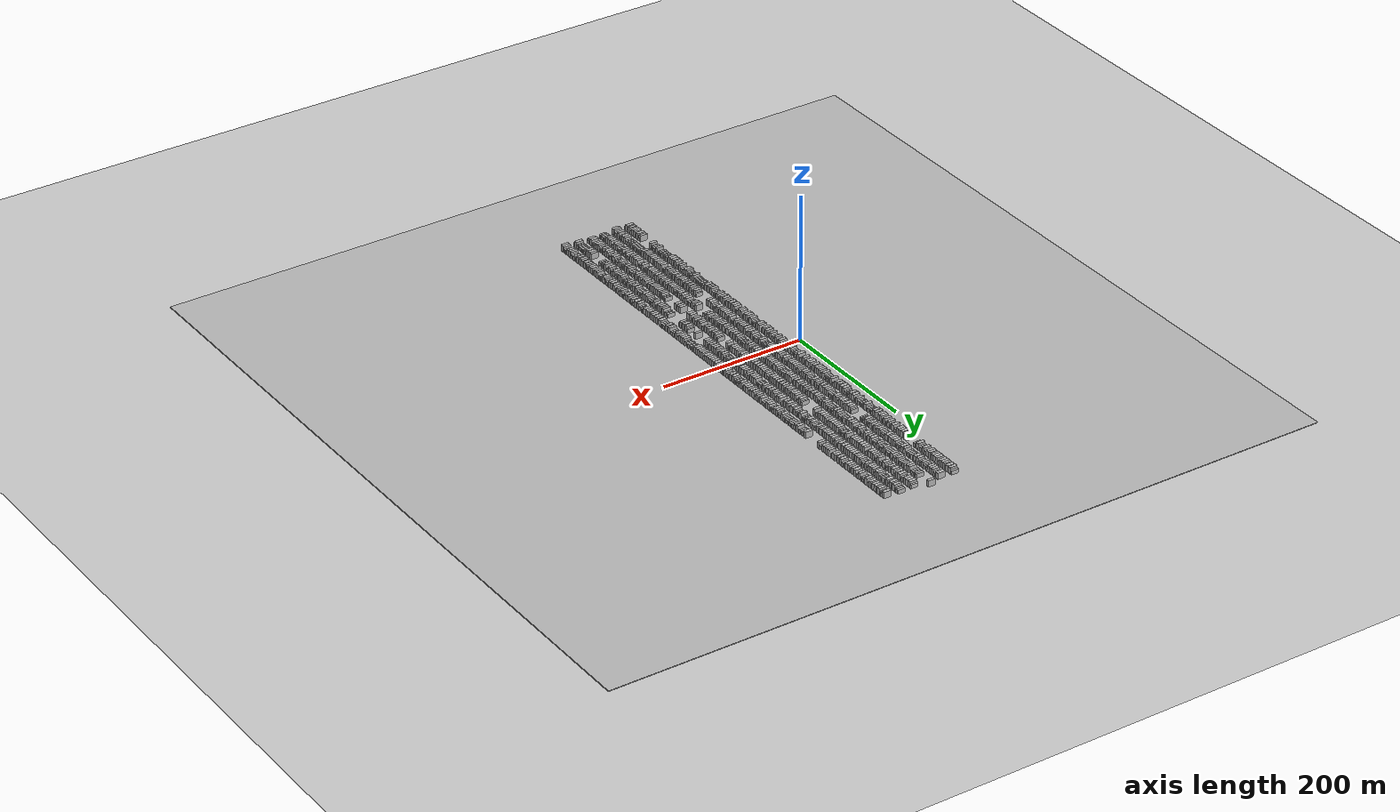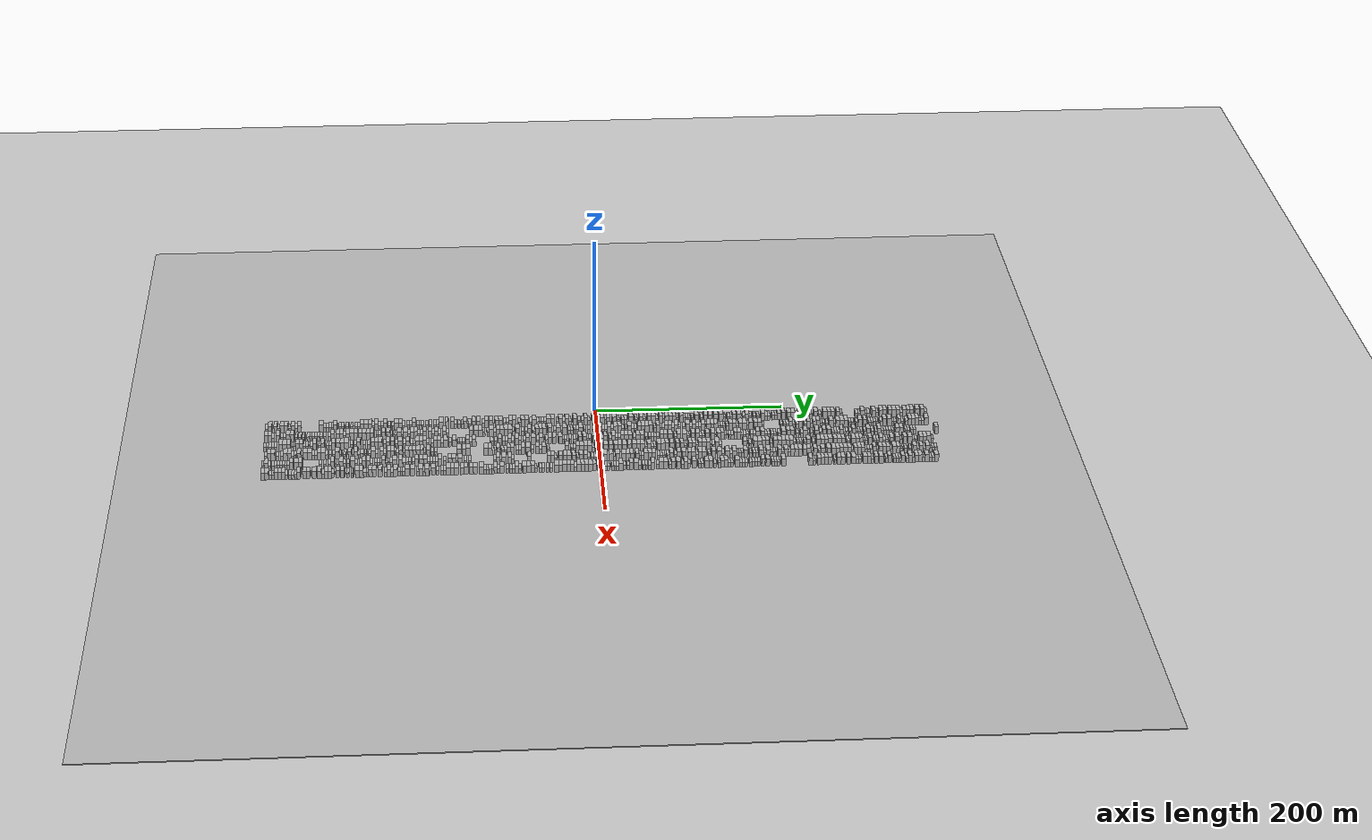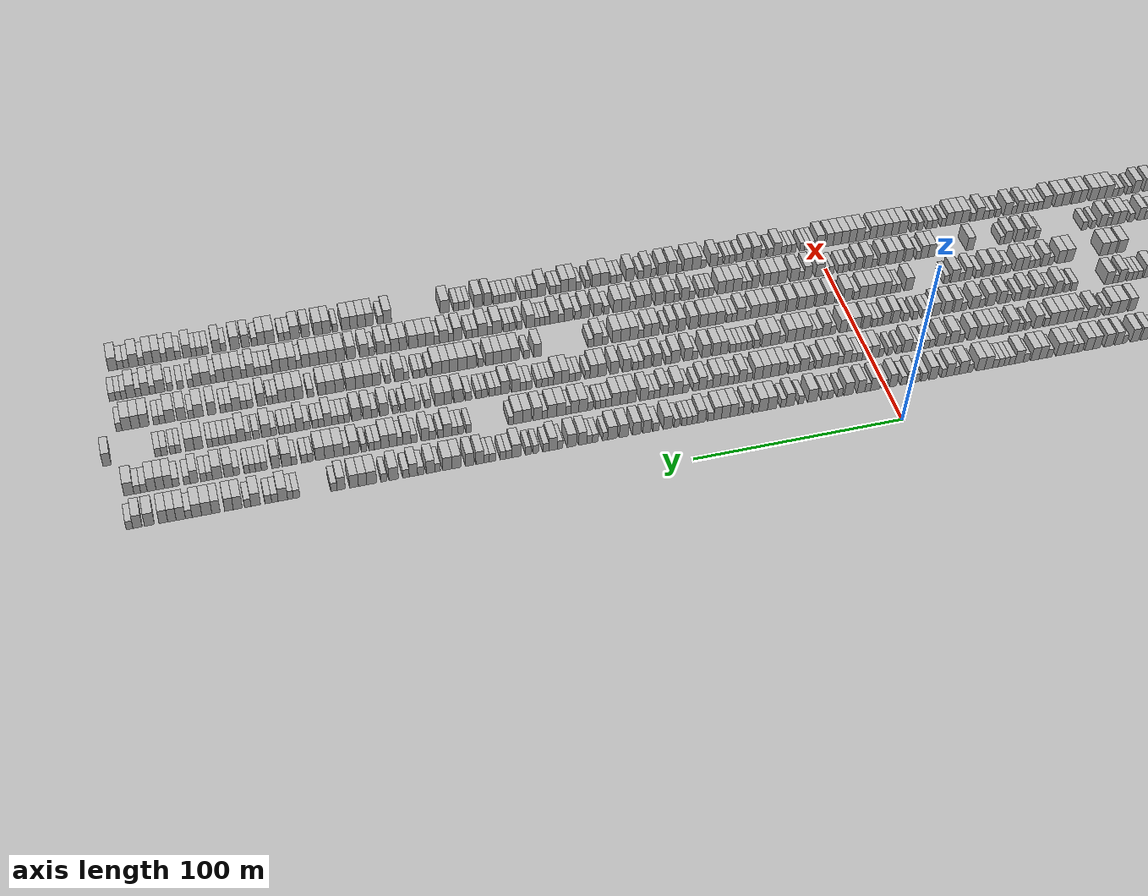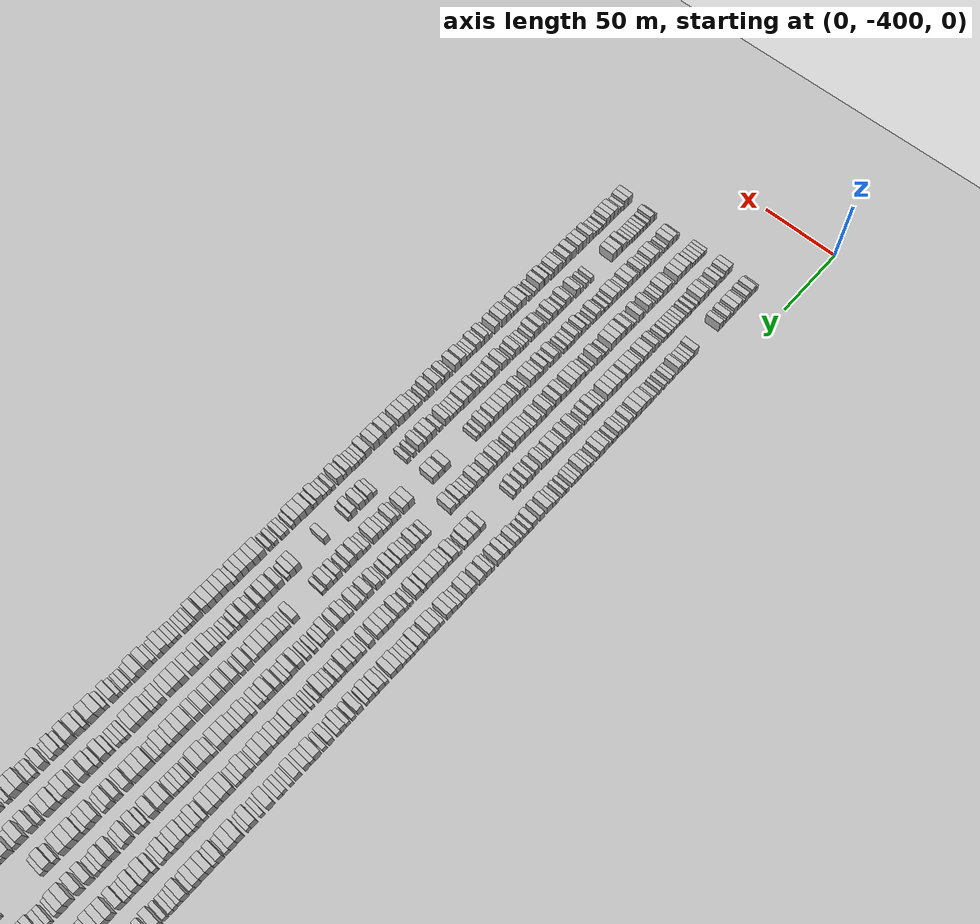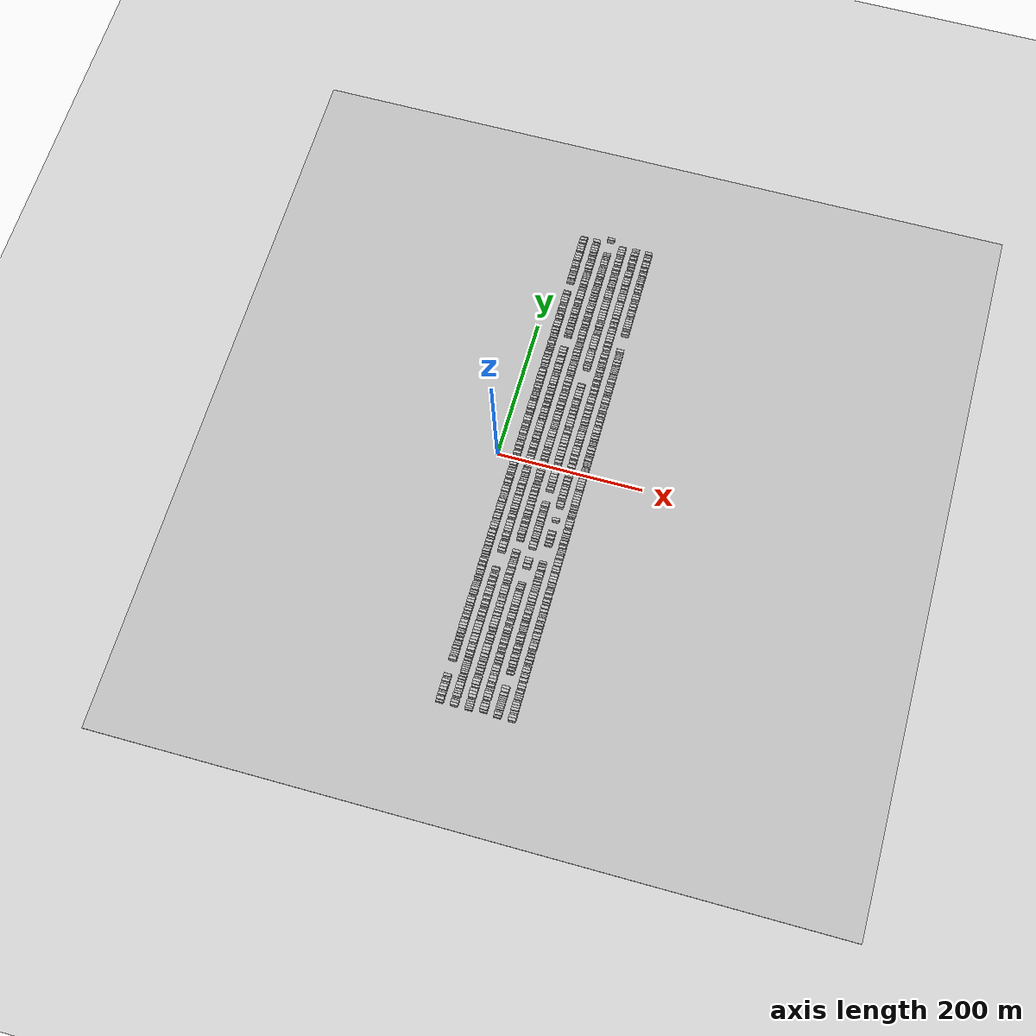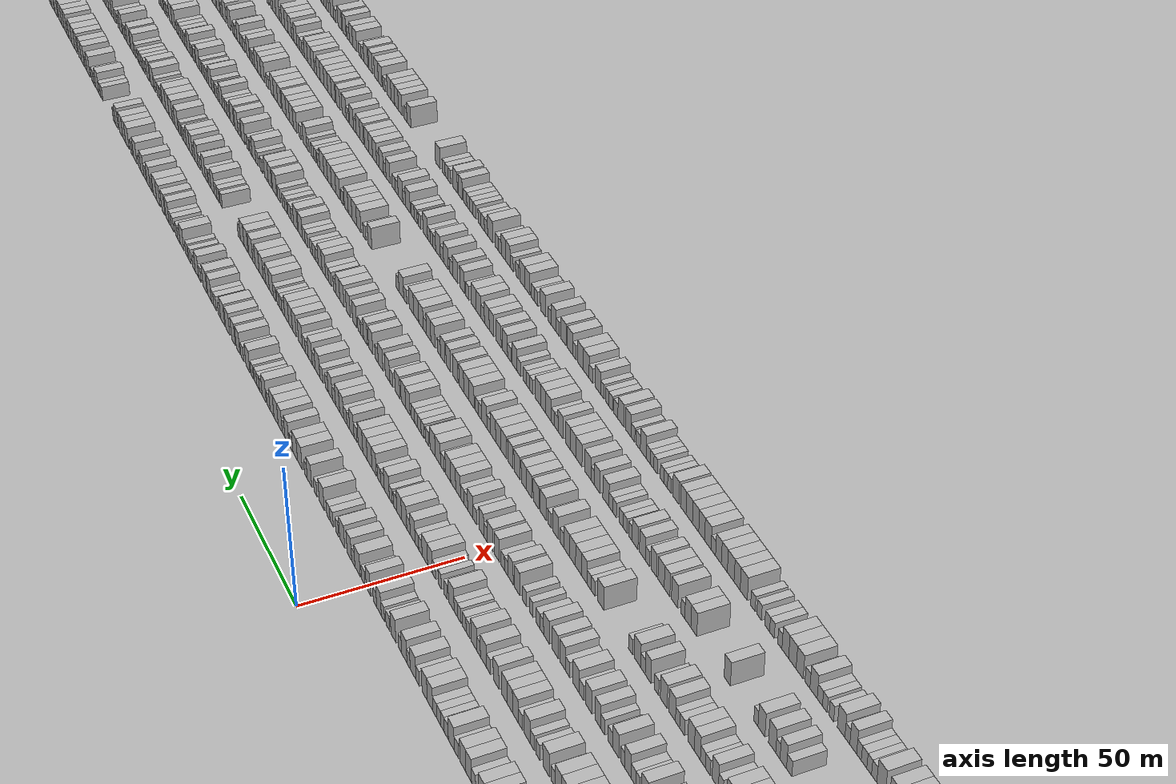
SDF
<?xml version="1.0" encoding="utf-8"?>

<sdf version="1.6">

   <world name="default">

      <gui fullscreen="0">

         <camera name="user_camera">

            <pose>-15 0 4.57585 0 0 0</pose>

            <view_controller>orbit</view_controller>

         </camera>

      </gui>

      <scene>

         <sky>

           <clouds>

             <speed>12</speed>

           </clouds>

         </sky>

         <ambient>0.4 0.4 0.4 1</ambient>

         <background>0.7 0.7 0.7 1</background>

         <shadows>1</shadows>

      </scene>

      <gravity>0 0 -9.8066</gravity>

      <magnetic_field>6e-06 2.3e-05 -4.2e-05</magnetic_field>

      <physics default="0" name="default_physics" type="ode">

         <ode>

            <solver>

               <type>quick</type>

               <iters>10</iters>

               <sor>1.0</sor>

               <use_dynamic_moi_rescaling>0</use_dynamic_moi_rescaling>

            </solver>

            <constraints>

               <cfm>0</cfm>

               <erp>0.2</erp>

               <contact_max_correcting_vel>100</contact_max_correcting_vel>

               <contact_surface_layer>0.001</contact_surface_layer>

            </constraints>

         </ode>

         <max_step_size>0.004</max_step_size>

         <real_time_factor>1</real_time_factor>

         <real_time_update_rate>250</real_time_update_rate>

      </physics>

      <light name="sun" type="directional">

         <cast_shadows>1</cast_shadows>

         <pose>0 0 10 0 0 0</pose>

         <diffuse>0.8 0.8 0.8 1</diffuse>

         <specular>0.2 0.2 0.2 1</specular>

         <attenuation>

            <range>1000</range>

            <constant>0.9</constant>

            <linear>0.01</linear>

            <quadratic>0.001</quadratic>

         </attenuation>

         <direction>-0.5 0.1 -0.9</direction>

      </light>

      <include>

         <name>ground_plane_1</name>

         <uri>model://HANNAS_ground_plane</uri>

         <pose>0 0 0  0 0 0</pose>

      </include>

      <include>

         <name>ground_plane_2</name>

         <uri>model://HANNAS_ground_plane</uri>

         <pose>100 0 0  0 0 0</pose>

      </include>

      <model name="building_1">

         <static>1</static>

         <pose frame="">25.0000 -348.5807 0 0.000000 0.000000 0.000000</pose>

         <link name="link">

            <pose frame="">0 0 3.00 0 0 0</pose>

            <collision name="collision">

               <geometry>

                  <box>

                     <size>10.0000 2.8386 6.0000</size>

                  </box>

               </geometry>

               <max_contacts>10</max_contacts>

               <surface>

                  <contact>

                     <ode/>

                  </contact>

                  <bounce/>

                  <friction>

                     <torsional>

                        <ode/>

                     </torsional>

                     <ode/>

                  </friction>

               </surface>

            </collision>

            <visual name="visual">

               <cast_shadows>0</cast_shadows>

               <geometry>

                  <box>

                     <size>10.0000 2.8386 6.0000</size>

                  </box>

               </geometry>

               <material>

                  <script>

                     <uri>model://HANNAS_wall/materials/scripts</uri>

                     <uri>model://HANNAS_wall/materials/textures</uri>

                     <name>vrc/HANNAS_wall</name>

                  </script>

               </material>

            </visual>

            <self_collide>0</self_collide>

            <enable_wind>0</enable_wind>

            <kinematic>0</kinematic>

         </link>

      </model>

      <model name="building_2">

         <static>1</static>

         <pose frame="">25.0000 -345.0058 0 0.000000 0.000000 0.000000</pose>

         <link name="link">

            <pose frame="">0 0 4.50 0 0 0</pose>

            <collision name="collision">

               <geometry>

                  <box>

                     <size>10.0000 4.3112 9.0000</size>

                  </box>

               </geometry>

               <max_contacts>10</max_contacts>

               <surface>

                  <contact>

                     <ode/>

                  </contact>

                  <bounce/>

                  <friction>

                     <torsional>

                        <ode/>

                     </torsional>

                     <ode/>

                  </friction>

               </surface>

            </collision>

            <visual name="visual">

               <cast_shadows>0</cast_shadows>

               <geometry>

                  <box>

                     <size>10.0000 4.3112 9.0000</size>

                  </box>

               </geometry>

               <material>

                  <script>

                     <uri>model://HANNAS_wall/materials/scripts</uri>

                     <uri>model://HANNAS_wall/materials/textures</uri>

                     <name>vrc/HANNAS_wall</name>

                  </script>

               </material>

            </visual>

            <self_collide>0</self_collide>

            <enable_wind>0</enable_wind>

            <kinematic>0</kinematic>

         </link>

      </model>

      <model name="building_3">

         <static>1</static>

         <pose frame="">25.0000 -339.0390 0 0.000000 0.000000 0.000000</pose>

         <link name="link">

            <pose frame="">0 0 4.50 0 0 0</pose>

            <collision name="collision">

               <geometry>

                  <box>

                     <size>10.0000 3.6225 9.0000</size>

                  </box>

               </geometry>

               <max_contacts>10</max_contacts>

               <surface>

                  <contact>

                     <ode/>

                  </contact>

                  <bounce/>

                  <friction>

                     <torsional>

                        <ode/>

                     </torsional>

                     <ode/>

                  </friction>

               </surface>

            </collision>

            <visual name="visual">

               <cast_shadows>0</cast_shadows>

               <geometry>

                  <box>

                     <size>10.0000 3.6225 9.0000</size>

                  </box>

               </geometry>

               <material>

                  <script>

                     <uri>model://HANNAS_wall/materials/scripts</uri>

                     <uri>model://HANNAS_wall/materials/textures</uri>

                     <name>vrc/HANNAS_wall</name>

                  </script>

               </material>

            </visual>

            <self_collide>0</self_collide>

            <enable_wind>0</enable_wind>

            <kinematic>0</kinematic>

         </link>

      </model>

      <model name="building_4">

         <static>1</static>

         <pose frame="">25.0000 -335.7632 0 0.000000 0.000000 0.000000</pose>

         <link name="link">

            <pose frame="">0 0 3.00 0 0 0</pose>

            <collision name="collision">

               <geometry>

                  <box>

                     <size>10.0000 2.9291 6.0000</size>

                  </box>

               </geometry>

               <max_contacts>10</max_contacts>

               <surface>

                  <contact>

                     <ode/>

                  </contact>

                  <bounce/>

                  <friction>

                     <torsional>

                        <ode/>

                     </torsional>

                     <ode/>

                  </friction>

               </surface>

            </collision>

            <visual name="visual">

               <cast_shadows>0</cast_shadows>

               <geometry>

                  <box>

                     <size>10.0000 2.9291 6.0000</size>

                  </box>

               </geometry>

               <material>

                  <script>

                     <uri>model://HANNAS_wall/materials/scripts</uri>

                     <uri>model://HANNAS_wall/materials/textures</uri>

                     <name>vrc/HANNAS_wall</name>

                  </script>

               </material>

            </visual>

            <self_collide>0</self_collide>

            <enable_wind>0</enable_wind>

            <kinematic>0</kinematic>

         </link>

      </model>

      <model name="building_5">

         <static>1</static>

         <pose frame="">25.0000 -332.2059 0 0.000000 0.000000 0.000000</pose>

         <link name="link">

            <pose frame="">0 0 4.50 0 0 0</pose>

            <collision name="collision">

               <geometry>

                  <box>

                     <size>10.0000 4.1853 9.0000</size>

                  </box>

               </geometry>

               <max_contacts>10</max_contacts>

               <surface>

                  <contact>

                     <ode/>

                  </contact>

                  <bounce/>

                  <friction>

                     <torsional>

                        <ode/>

                     </torsional>

                     <ode/>

                  </friction>

               </surface>

            </collision>

            <visual name="visual">

               <cast_shadows>0</cast_shadows>

               <geometry>

                  <box>

                     <size>10.0000 4.1853 9.0000</size>

                  </box>

               </geometry>

               <material>

                  <script>

                     <uri>model://HANNAS_wall/materials/scripts</uri>

                     <uri>model://HANNAS_wall/materials/textures</uri>

                     <name>vrc/HANNAS_wall</name>

                  </script>

               </material>

            </visual>

            <self_collide>0</self_collide>

            <enable_wind>0</enable_wind>

            <kinematic>0</kinematic>

         </link>

      </model>

      <model name="building_6">

         <static>1</static>

         <pose frame="">25.0000 -328.0000 0 0.000000 0.000000 0.000000</pose>

         <link name="link">

            <pose frame="">0 0 4.50 0 0 0</pose>

            <collision name="collision">

               <geometry>

                  <box>

                     <size>10.0000 4.2265 9.0000</size>

                  </box>

               </geometry>

               <max_contacts>10</max_contacts>

               <surface>

                  <contact>

                     <ode/>

                  </contact>

                  <bounce/>

                  <friction>

                     <torsional>

                        <ode/>

                     </torsional>

                     <ode/>

                  </friction>

               </surface>

            </collision>

            <visual name="visual">

               <cast_shadows>0</cast_shadows>

               <geometry>

                  <box>

                     <size>10.0000 4.2265 9.0000</size>

                  </box>

               </geometry>

               <material>

                  <script>

                     <uri>model://HANNAS_wall/materials/scripts</uri>

                     <uri>model://HANNAS_wall/materials/textures</uri>

                     <name>vrc/HANNAS_wall</name>

                  </script>

               </material>

            </visual>

            <self_collide>0</self_collide>

            <enable_wind>0</enable_wind>

            <kinematic>0</kinematic>

         </link>

      </model>

      <model name="building_7">

         <static>1</static>

         <pose frame="">25.0000 -324.4025 0 0.000000 0.000000 0.000000</pose>

         <link name="link">

            <pose frame="">0 0 3.00 0 0 0</pose>

            <collision name="collision">

               <geometry>

                  <box>

                     <size>10.0000 2.9684 6.0000</size>

                  </box>

               </geometry>

               <max_contacts>10</max_contacts>

               <surface>

                  <contact>

                     <ode/>

                  </contact>

                  <bounce/>

                  <friction>

                     <torsional>

                        <ode/>

                     </torsional>

                     <ode/>

                  </friction>

               </surface>

            </collision>

            <visual name="visual">

               <cast_shadows>0</cast_shadows>

               <geometry>

                  <box>

                     <size>10.0000 2.9684 6.0000</size>

                  </box>

               </geometry>

               <material>

                  <script>

                     <uri>model://HANNAS_wall/materials/scripts</uri>

                     <uri>model://HANNAS_wall/materials/textures</uri>

                     <name>vrc/HANNAS_wall</name>

                  </script>

               </material>

            </visual>

            <self_collide>0</self_collide>

            <enable_wind>0</enable_wind>

            <kinematic>0</kinematic>

         </link>

      </model>

      <model name="building_8">

         <static>1</static>

         <pose frame="">25.0000 -320.8872 0 0.000000 0.000000 0.000000</pose>

         <link name="link">

            <pose frame="">0 0 4.50 0 0 0</pose>

            <collision name="collision">

               <geometry>

                  <box>

                     <size>10.0000 4.0622 9.0000</size>

                  </box>

               </geometry>

               <max_contacts>10</max_contacts>

               <surface>

                  <contact>

                     <ode/>

                  </contact>

                  <bounce/>

                  <friction>

                     <torsional>

                        <ode/>

                     </torsional>

                     <ode/>

                  </friction>

               </surface>

            </collision>

            <visual name="visual">

               <cast_shadows>0</cast_shadows>

               <geometry>

                  <box>

                     <size>10.0000 4.0622 9.0000</size>

                  </box>

               </geometry>

               <material>

                  <script>

                     <uri>model://HANNAS_wall/materials/scripts</uri>

                     <uri>model://HANNAS_wall/materials/textures</uri>

                     <name>vrc/HANNAS_wall</name>

                  </script>

               </material>

            </visual>

            <self_collide>0</self_collide>

            <enable_wind>0</enable_wind>

            <kinematic>0</kinematic>

         </link>

      </model>

      <model name="building_9">

         <static>1</static>

         <pose frame="">25.0000 -317.4307 0 0.000000 0.000000 0.000000</pose>

         <link name="link">

            <pose frame="">0 0 3.00 0 0 0</pose>

            <collision name="collision">

               <geometry>

                  <box>

                     <size>10.0000 2.8509 6.0000</size>

                  </box>

               </geometry>

               <max_contacts>10</max_contacts>

               <surface>

                  <contact>

                     <ode/>

                  </contact>

                  <bounce/>

                  <friction>

                     <torsional>

                        <ode/>

                     </torsional>

                     <ode/>

                  </friction>

               </surface>

            </collision>

            <visual name="visual">

               <cast_shadows>0</cast_shadows>

               <geometry>

                  <box>

                     <size>10.0000 2.8509 6.0000</size>

                  </box>

               </geometry>

               <material>

                  <script>

                     <uri>model://HANNAS_wall/materials/scripts</uri>

                     <uri>model://HANNAS_wall/materials/textures</uri>

                     <name>vrc/HANNAS_wall</name>

                  </script>

               </material>

            </visual>

            <self_collide>0</self_collide>

            <enable_wind>0</enable_wind>

            <kinematic>0</kinematic>

         </link>

      </model>

      <model name="building_10">

         <static>1</static>

         <pose frame="">25.0000 -314.1935 0 0.000000 0.000000 0.000000</pose>

         <link name="link">

            <pose frame="">0 0 4.50 0 0 0</pose>

            <collision name="collision">

               <geometry>

                  <box>

                     <size>10.0000 3.6234 9.0000</size>

                  </box>

               </geometry>

               <max_contacts>10</max_contacts>

               <surface>

                  <contact>

                     <ode/>

                  </contact>

                  <bounce/>

                  <friction>

                     <torsional>

                        <ode/>

                     </torsional>

                     <ode/>

                  </friction>

               </surface>

            </collision>

            <visual name="visual">

               <cast_shadows>0</cast_shadows>

               <geometry>

                  <box>

                     <size>10.0000 3.6234 9.0000</size>

                  </box>

               </geometry>

               <material>

                  <script>

                     <uri>model://HANNAS_wall/materials/scripts</uri>

                     <uri>model://HANNAS_wall/materials/textures</uri>

                     <name>vrc/HANNAS_wall</name>

                  </script>

               </material>

            </visual>

            <self_collide>0</self_collide>

            <enable_wind>0</enable_wind>

            <kinematic>0</kinematic>

         </link>

      </model>

      <model name="building_11">

         <static>1</static>

         <pose frame="">25.0000 -291.0103 0 0.000000 0.000000 0.000000</pose>

         <link name="link">

            <pose frame="">0 0 4.50 0 0 0</pose>

            <collision name="collision">

               <geometry>

                  <box>

                     <size>10.0000 4.2477 9.0000</size>

                  </box>

               </geometry>

               <max_contacts>10</max_contacts>

               <surface>

                  <contact>

                     <ode/>

                  </contact>

                  <bounce/>

                  <friction>

                     <torsional>

                        <ode/>

                     </torsional>

                     <ode/>

                  </friction>

               </surface>

            </collision>

            <visual name="visual">

               <cast_shadows>0</cast_shadows>

               <geometry>

                  <box>

                     <size>10.0000 4.2477 9.0000</size>

                  </box>

               </geometry>

               <material>

                  <script>

                     <uri>model://HANNAS_wall/materials/scripts</uri>

                     <uri>model://HANNAS_wall/materials/textures</uri>

                     <name>vrc/HANNAS_wall</name>

                  </script>

               </material>

            </visual>

            <self_collide>0</self_collide>

            <enable_wind>0</enable_wind>

            <kinematic>0</kinematic>

         </link>

      </model>

      <model name="building_12">

         <static>1</static>

         <pose frame="">25.0000 -287.5518 0 0.000000 0.000000 0.000000</pose>

         <link name="link">

            <pose frame="">0 0 3.00 0 0 0</pose>

            <collision name="collision">

               <geometry>

                  <box>

                     <size>10.0000 2.6692 6.0000</size>

                  </box>

               </geometry>

               <max_contacts>10</max_contacts>

               <surface>

                  <contact>

                     <ode/>

                  </contact>

                  <bounce/>

                  <friction>

                     <torsional>

                        <ode/>

                     </torsional>

                     <ode/>

                  </friction>

               </surface>

            </collision>

            <visual name="visual">

               <cast_shadows>0</cast_shadows>

               <geometry>

                  <box>

                     <size>10.0000 2.6692 6.0000</size>

                  </box>

               </geometry>

               <material>

                  <script>

                     <uri>model://HANNAS_wall/materials/scripts</uri>

                     <uri>model://HANNAS_wall/materials/textures</uri>

                     <name>vrc/HANNAS_wall</name>

                  </script>

               </material>

            </visual>

            <self_collide>0</self_collide>

            <enable_wind>0</enable_wind>

            <kinematic>0</kinematic>

         </link>

      </model>

      <model name="building_13">

         <static>1</static>

         <pose frame="">25.0000 -284.8402 0 0.000000 0.000000 0.000000</pose>

         <link name="link">

            <pose frame="">0 0 3.00 0 0 0</pose>

            <collision name="collision">

               <geometry>

                  <box>

                     <size>10.0000 2.7540 6.0000</size>

                  </box>

               </geometry>

               <max_contacts>10</max_contacts>

               <surface>

                  <contact>

                     <ode/>

                  </contact>

                  <bounce/>

                  <friction>

                     <torsional>

                        <ode/>

                     </torsional>

                     <ode/>

                  </friction>

               </surface>

            </collision>

            <visual name="visual">

               <cast_shadows>0</cast_shadows>

               <geometry>

                  <box>

                     <size>10.0000 2.7540 6.0000</size>

                  </box>

               </geometry>

               <material>

                  <script>

                     <uri>model://HANNAS_wall/materials/scripts</uri>

                     <uri>model://HANNAS_wall/materials/textures</uri>

                     <name>vrc/HANNAS_wall</name>

                  </script>

               </material>

            </visual>

            <self_collide>0</self_collide>

            <enable_wind>0</enable_wind>

            <kinematic>0</kinematic>

         </link>

      </model>

      <model name="building_14">

         <static>1</static>

         <pose frame="">25.0000 -281.9950 0 0.000000 0.000000 0.000000</pose>

         <link name="link">

            <pose frame="">0 0 3.00 0 0 0</pose>

            <collision name="collision">

               <geometry>

                  <box>

                     <size>10.0000 2.9364 6.0000</size>

                  </box>

               </geometry>

               <max_contacts>10</max_contacts>

               <surface>

                  <contact>

                     <ode/>

                  </contact>

                  <bounce/>

                  <friction>

                     <torsional>

                        <ode/>

                     </torsional>

                     <ode/>

                  </friction>

               </surface>

            </collision>

            <visual name="visual">

               <cast_shadows>0</cast_shadows>

               <geometry>

                  <box>

                     <size>10.0000 2.9364 6.0000</size>

                  </box>

               </geometry>

               <material>

                  <script>

                     <uri>model://HANNAS_wall/materials/scripts</uri>

                     <uri>model://HANNAS_wall/materials/textures</uri>

                     <name>vrc/HANNAS_wall</name>

                  </script>

               </material>

            </visual>

            <self_collide>0</self_collide>

            <enable_wind>0</enable_wind>

            <kinematic>0</kinematic>

         </link>

      </model>

      <model name="building_15">

         <static>1</static>

         <pose frame="">25.0000 -279.2619 0 0.000000 0.000000 0.000000</pose>

         <link name="link">

            <pose frame="">0 0 3.00 0 0 0</pose>

            <collision name="collision">

               <geometry>

                  <box>

                     <size>10.0000 2.5298 6.0000</size>

                  </box>

               </geometry>

               <max_contacts>10</max_contacts>

               <surface>

                  <contact>

                     <ode/>

                  </contact>

                  <bounce/>

                  <friction>

                     <torsional>

                        <ode/>

                     </torsional>

                     <ode/>

                  </friction>

               </surface>

            </collision>

            <visual name="visual">

               <cast_shadows>0</cast_shadows>

               <geometry>

                  <box>

                     <size>10.0000 2.5298 6.0000</size>

                  </box>

               </geometry>

               <material>

                  <script>

                     <uri>model://HANNAS_wall/materials/scripts</uri>

                     <uri>model://HANNAS_wall/materials/textures</uri>

                     <name>vrc/HANNAS_wall</name>

                  </script>

               </material>

            </visual>

            <self_collide>0</self_collide>

            <enable_wind>0</enable_wind>

            <kinematic>0</kinematic>

         </link>

      </model>

      <model name="building_16">

         <static>1</static>

         <pose frame="">25.0000 -276.1931 0 0.000000 0.000000 0.000000</pose>

         <link name="link">

            <pose frame="">0 0 4.50 0 0 0</pose>

            <collision name="collision">

               <geometry>

                  <box>

                     <size>10.0000 3.6077 9.0000</size>

                  </box>

               </geometry>

               <max_contacts>10</max_contacts>

               <surface>

                  <contact>

                     <ode/>

                  </contact>

                  <bounce/>

                  <friction>

                     <torsional>

                        <ode/>

                     </torsional>

                     <ode/>

                  </friction>

               </surface>

            </collision>

            <visual name="visual">

               <cast_shadows>0</cast_shadows>

               <geometry>

                  <box>

                     <size>10.0000 3.6077 9.0000</size>

                  </box>

               </geometry>

               <material>

                  <script>

                     <uri>model://HANNAS_wall/materials/scripts</uri>

                     <uri>model://HANNAS_wall/materials/textures</uri>

                     <name>vrc/HANNAS_wall</name>

                  </script>

               </material>

            </visual>

            <self_collide>0</self_collide>

            <enable_wind>0</enable_wind>

            <kinematic>0</kinematic>

         </link>

      </model>

      <model name="building_17">

         <static>1</static>

         <pose frame="">25.0000 -271.0863 0 0.000000 0.000000 0.000000</pose>

         <link name="link">

            <pose frame="">0 0 3.00 0 0 0</pose>

            <collision name="collision">

               <geometry>

                  <box>

                     <size>10.0000 2.6060 6.0000</size>

                  </box>

               </geometry>

               <max_contacts>10</max_contacts>

               <surface>

                  <contact>

                     <ode/>

                  </contact>

                  <bounce/>

                  <friction>

                     <torsional>

                        <ode/>

                     </torsional>

                     <ode/>

                  </friction>

               </surface>

            </collision>

            <visual name="visual">

               <cast_shadows>0</cast_shadows>

               <geometry>

                  <box>

                     <size>10.0000 2.6060 6.0000</size>

                  </box>

               </geometry>

               <material>

                  <script>

                     <uri>model://HANNAS_wall/materials/scripts</uri>

                     <uri>model://HANNAS_wall/materials/textures</uri>

                     <name>vrc/HANNAS_wall</name>

                  </script>

               </material>

            </visual>

            <self_collide>0</self_collide>

            <enable_wind>0</enable_wind>

            <kinematic>0</kinematic>

         </link>

      </model>

      <model name="building_18">

         <static>1</static>

         <pose frame="">25.0000 -268.3383 0 0.000000 0.000000 0.000000</pose>

         <link name="link">

            <pose frame="">0 0 3.00 0 0 0</pose>

            <collision name="collision">

               <geometry>

                  <box>

                     <size>10.0000 2.8900 6.0000</size>

                  </box>

               </geometry>

               <max_contacts>10</max_contacts>

               <surface>

                  <contact>

                     <ode/>

                  </contact>

                  <bounce/>

                  <friction>

                     <torsional>

                        <ode/>

                     </torsional>

                     <ode/>

                  </friction>

               </surface>

            </collision>

            <visual name="visual">

               <cast_shadows>0</cast_shadows>

               <geometry>

                  <box>

                     <size>10.0000 2.8900 6.0000</size>

                  </box>

               </geometry>

               <material>

                  <script>

                     <uri>model://HANNAS_wall/materials/scripts</uri>

                     <uri>model://HANNAS_wall/materials/textures</uri>

                     <name>vrc/HANNAS_wall</name>

                  </script>

               </material>

            </visual>

            <self_collide>0</self_collide>

            <enable_wind>0</enable_wind>

            <kinematic>0</kinematic>

         </link>

      </model>

      <model name="building_19">

         <static>1</static>

         <pose frame="">25.0000 -263.4455 0 0.000000 0.000000 0.000000</pose>

         <link name="link">

            <pose frame="">0 0 3.00 0 0 0</pose>

            <collision name="collision">

               <geometry>

                  <box>

                     <size>10.0000 2.8955 6.0000</size>

                  </box>

               </geometry>

               <max_contacts>10</max_contacts>

               <surface>

                  <contact>

                     <ode/>

                  </contact>

                  <bounce/>

                  <friction>

                     <torsional>

                        <ode/>

                     </torsional>

                     <ode/>

                  </friction>

               </surface>

            </collision>

            <visual name="visual">

               <cast_shadows>0</cast_shadows>

               <geometry>

                  <box>

                     <size>10.0000 2.8955 6.0000</size>

                  </box>

               </geometry>

               <material>

                  <script>

                     <uri>model://HANNAS_wall/materials/scripts</uri>

                     <uri>model://HANNAS_wall/materials/textures</uri>

                     <name>vrc/HANNAS_wall</name>

                  </script>

               </material>

            </visual>

            <self_collide>0</self_collide>

            <enable_wind>0</enable_wind>

            <kinematic>0</kinematic>

         </link>

      </model>

      <model name="building_20">

         <static>1</static>

         <pose frame="">25.0000 -258.7673 0 0.000000 0.000000 0.000000</pose>

         <link name="link">

            <pose frame="">0 0 3.00 0 0 0</pose>

            <collision name="collision">

               <geometry>

                  <box>

                     <size>10.0000 2.4609 6.0000</size>

                  </box>

               </geometry>

               <max_contacts>10</max_contacts>

               <surface>

                  <contact>

                     <ode/>

                  </contact>

                  <bounce/>

                  <friction>

                     <torsional>

                        <ode/>

                     </torsional>

                     <ode/>

                  </friction>

               </surface>

            </collision>

            <visual name="visual">

               <cast_shadows>0</cast_shadows>

               <geometry>

                  <box>

                     <size>10.0000 2.4609 6.0000</size>

                  </box>

               </geometry>

               <material>

                  <script>

                     <uri>model://HANNAS_wall/materials/scripts</uri>

                     <uri>model://HANNAS_wall/materials/textures</uri>

                     <name>vrc/HANNAS_wall</name>

                  </script>

               </material>

            </visual>

            <self_collide>0</self_collide>

            <enable_wind>0</enable_wind>

            <kinematic>0</kinematic>

         </link>

      </model>

      <model name="building_21">

         <static>1</static>

         <pose frame="">25.0000 -254.0529 0 0.000000 0.000000 0.000000</pose>

         <link name="link">

            <pose frame="">0 0 3.00 0 0 0</pose>

            <collision name="collision">

               <geometry>

                  <box>

                     <size>10.0000 2.9681 6.0000</size>

                  </box>

               </geometry>

               <max_contacts>10</max_contacts>

               <surface>

                  <contact>

                     <ode/>

                  </contact>

                  <bounce/>

                  <friction>

                     <torsional>

                        <ode/>

                     </torsional>

                     <ode/>

                  </friction>

               </surface>

            </collision>

            <visual name="visual">

               <cast_shadows>0</cast_shadows>

               <geometry>

                  <box>

                     <size>10.0000 2.9681 6.0000</size>

                  </box>

               </geometry>

               <material>

                  <script>

                     <uri>model://HANNAS_wall/materials/scripts</uri>

                     <uri>model://HANNAS_wall/materials/textures</uri>

                     <name>vrc/HANNAS_wall</name>

                  </script>

               </material>

            </visual>

            <self_collide>0</self_collide>

            <enable_wind>0</enable_wind>

            <kinematic>0</kinematic>

         </link>

      </model>

      <model name="building_22">

         <static>1</static>

         <pose frame="">25.0000 -251.3303 0 0.000000 0.000000 0.000000</pose>

         <link name="link">

            <pose frame="">0 0 3.00 0 0 0</pose>

            <collision name="collision">

               <geometry>

                  <box>

                     <size>10.0000 2.4771 6.0000</size>

                  </box>

               </geometry>

               <max_contacts>10</max_contacts>

               <surface>

                  <contact>

                     <ode/>

                  </contact>

                  <bounce/>

                  <friction>

                     <torsional>

                        <ode/>

                     </torsional>

                     <ode/>

                  </friction>

               </surface>

            </collision>

            <visual name="visual">

               <cast_shadows>0</cast_shadows>

               <geometry>

                  <box>

                     <size>10.0000 2.4771 6.0000</size>

                  </box>

               </geometry>

               <material>

                  <script>

                     <uri>model://HANNAS_wall/materials/scripts</uri>

                     <uri>model://HANNAS_wall/materials/textures</uri>

                     <name>vrc/HANNAS_wall</name>

                  </script>

               </material>

            </visual>

            <self_collide>0</self_collide>

            <enable_wind>0</enable_wind>

            <kinematic>0</kinematic>

         </link>

      </model>

      <model name="building_23">

         <static>1</static>

         <pose frame="">25.0000 -248.0979 0 0.000000 0.000000 0.000000</pose>

         <link name="link">

            <pose frame="">0 0 4.50 0 0 0</pose>

            <collision name="collision">

               <geometry>

                  <box>

                     <size>10.0000 3.9877 9.0000</size>

                  </box>

               </geometry>

               <max_contacts>10</max_contacts>

               <surface>

                  <contact>

                     <ode/>

                  </contact>

                  <bounce/>

                  <friction>

                     <torsional>

                        <ode/>

                     </torsional>

                     <ode/>

                  </friction>

               </surface>

            </collision>

            <visual name="visual">

               <cast_shadows>0</cast_shadows>

               <geometry>

                  <box>

                     <size>10.0000 3.9877 9.0000</size>

                  </box>

               </geometry>

               <material>

                  <script>

                     <uri>model://HANNAS_wall/materials/scripts</uri>

                     <uri>model://HANNAS_wall/materials/textures</uri>

                     <name>vrc/HANNAS_wall</name>

                  </script>

               </material>

            </visual>

            <self_collide>0</self_collide>

            <enable_wind>0</enable_wind>

            <kinematic>0</kinematic>

         </link>

      </model>

      <model name="building_24">

         <static>1</static>

         <pose frame="">25.0000 -243.9696 0 0.000000 0.000000 0.000000</pose>

         <link name="link">

            <pose frame="">0 0 4.50 0 0 0</pose>

            <collision name="collision">

               <geometry>

                  <box>

                     <size>10.0000 4.2689 9.0000</size>

                  </box>

               </geometry>

               <max_contacts>10</max_contacts>

               <surface>

                  <contact>

                     <ode/>

                  </contact>

                  <bounce/>

                  <friction>

                     <torsional>

                        <ode/>

                     </torsional>

                     <ode/>

                  </friction>

               </surface>

            </collision>

            <visual name="visual">

               <cast_shadows>0</cast_shadows>

               <geometry>

                  <box>

                     <size>10.0000 4.2689 9.0000</size>

                  </box>

               </geometry>

               <material>

                  <script>

                     <uri>model://HANNAS_wall/materials/scripts</uri>

                     <uri>model://HANNAS_wall/materials/textures</uri>

                     <name>vrc/HANNAS_wall</name>

                  </script>

               </material>

            </visual>

            <self_collide>0</self_collide>

            <enable_wind>0</enable_wind>

            <kinematic>0</kinematic>

         </link>

      </model>

      <model name="building_25">

         <static>1</static>

         <pose frame="">25.0000 -239.6235 0 0.000000 0.000000 0.000000</pose>

         <link name="link">

            <pose frame="">0 0 4.50 0 0 0</pose>

            <collision name="collision">

               <geometry>

                  <box>

                     <size>10.0000 4.4232 9.0000</size>

                  </box>

               </geometry>

               <max_contacts>10</max_contacts>

               <surface>

                  <contact>

                     <ode/>

                  </contact>

                  <bounce/>

                  <friction>

                     <torsional>

                        <ode/>

                     </torsional>

                     <ode/>

                  </friction>

               </surface>

            </collision>

            <visual name="visual">

               <cast_shadows>0</cast_shadows>

               <geometry>

                  <box>

                     <size>10.0000 4.4232 9.0000</size>

                  </box>

               </geometry>

               <material>

                  <script>

                     <uri>model://HANNAS_wall/materials/scripts</uri>

                     <uri>model://HANNAS_wall/materials/textures</uri>

                     <name>vrc/HANNAS_wall</name>

                  </script>

               </material>

            </visual>

            <self_collide>0</self_collide>

            <enable_wind>0</enable_wind>

            <kinematic>0</kinematic>

         </link>

      </model>

      <model name="building_26">

         <static>1</static>

         <pose frame="">25.0000 -236.0674 0 0.000000 0.000000 0.000000</pose>

         <link name="link">

            <pose frame="">0 0 3.00 0 0 0</pose>

            <collision name="collision">

               <geometry>

                  <box>

                     <size>10.0000 2.6891 6.0000</size>

                  </box>

               </geometry>

               <max_contacts>10</max_contacts>

               <surface>

                  <contact>

                     <ode/>

                  </contact>

                  <bounce/>

                  <friction>

                     <torsional>

                        <ode/>

                     </torsional>

                     <ode/>

                  </friction>

               </surface>

            </collision>

            <visual name="visual">

               <cast_shadows>0</cast_shadows>

               <geometry>

                  <box>

                     <size>10.0000 2.6891 6.0000</size>

                  </box>

               </geometry>

               <material>

                  <script>

                     <uri>model://HANNAS_wall/materials/scripts</uri>

                     <uri>model://HANNAS_wall/materials/textures</uri>

                     <name>vrc/HANNAS_wall</name>

                  </script>

               </material>

            </visual>

            <self_collide>0</self_collide>

            <enable_wind>0</enable_wind>

            <kinematic>0</kinematic>

         </link>

      </model>

      <model name="building_27">

         <static>1</static>

         <pose frame="">25.0000 -232.7667 0 0.000000 0.000000 0.000000</pose>

         <link name="link">

            <pose frame="">0 0 4.50 0 0 0</pose>

            <collision name="collision">

               <geometry>

                  <box>

                     <size>10.0000 3.9124 9.0000</size>

                  </box>

               </geometry>

               <max_contacts>10</max_contacts>

               <surface>

                  <contact>

                     <ode/>

                  </contact>

                  <bounce/>

                  <friction>

                     <torsional>

                        <ode/>

                     </torsional>

                     <ode/>

                  </friction>

               </surface>

            </collision>

            <visual name="visual">

               <cast_shadows>0</cast_shadows>

               <geometry>

                  <box>

                     <size>10.0000 3.9124 9.0000</size>

                  </box>

               </geometry>

               <material>

                  <script>

                     <uri>model://HANNAS_wall/materials/scripts</uri>

                     <uri>model://HANNAS_wall/materials/textures</uri>

                     <name>vrc/HANNAS_wall</name>

                  </script>

               </material>

            </visual>

            <self_collide>0</self_collide>

            <enable_wind>0</enable_wind>

            <kinematic>0</kinematic>

         </link>

      </model>

      <model name="building_28">

         <static>1</static>

         <pose frame="">25.0000 -229.4399 0 0.000000 0.000000 0.000000</pose>

         <link name="link">

            <pose frame="">0 0 3.00 0 0 0</pose>

            <collision name="collision">

               <geometry>

                  <box>

                     <size>10.0000 2.7411 6.0000</size>

                  </box>

               </geometry>

               <max_contacts>10</max_contacts>

               <surface>

                  <contact>

                     <ode/>

                  </contact>

                  <bounce/>

                  <friction>

                     <torsional>

                        <ode/>

                     </torsional>

                     <ode/>

                  </friction>

               </surface>

            </collision>

            <visual name="visual">

               <cast_shadows>0</cast_shadows>

               <geometry>

                  <box>

                     <size>10.0000 2.7411 6.0000</size>

                  </box>

               </geometry>

               <material>

                  <script>

                     <uri>model://HANNAS_wall/materials/scripts</uri>

                     <uri>model://HANNAS_wall/materials/textures</uri>

                     <name>vrc/HANNAS_wall</name>

                  </script>

               </material>

            </visual>

            <self_collide>0</self_collide>

            <enable_wind>0</enable_wind>

            <kinematic>0</kinematic>

         </link>

      </model>

      <model name="building_29">

         <static>1</static>

         <pose frame="">25.0000 -226.5776 0 0.000000 0.000000 0.000000</pose>

         <link name="link">

            <pose frame="">0 0 3.00 0 0 0</pose>

            <collision name="collision">

               <geometry>

                  <box>

                     <size>10.0000 2.9833 6.0000</size>

                  </box>

               </geometry>

               <max_contacts>10</max_contacts>

               <surface>

                  <contact>

                     <ode/>

                  </contact>

                  <bounce/>

                  <friction>

                     <torsional>

                        <ode/>

                     </torsional>

                     <ode/>

                  </friction>

               </surface>

            </collision>

            <visual name="visual">

               <cast_shadows>0</cast_shadows>

               <geometry>

                  <box>

                     <size>10.0000 2.9833 6.0000</size>

                  </box>

               </geometry>

               <material>

                  <script>

                     <uri>model://HANNAS_wall/materials/scripts</uri>

                     <uri>model://HANNAS_wall/materials/textures</uri>

                     <name>vrc/HANNAS_wall</name>

                  </script>

               </material>

            </visual>

            <self_collide>0</self_collide>

            <enable_wind>0</enable_wind>

            <kinematic>0</kinematic>

         </link>

      </model>

      <model name="building_30">

         <static>1</static>

         <pose frame="">25.0000 -223.2471 0 0.000000 0.000000 0.000000</pose>

         <link name="link">

            <pose frame="">0 0 4.50 0 0 0</pose>

            <collision name="collision">

               <geometry>

                  <box>

                     <size>10.0000 3.6777 9.0000</size>

                  </box>

               </geometry>

               <max_contacts>10</max_contacts>

               <surface>

                  <contact>

                     <ode/>

                  </contact>

                  <bounce/>

                  <friction>

                     <torsional>

                        <ode/>

                     </torsional>

                     <ode/>

                  </friction>

               </surface>

            </collision>

            <visual name="visual">

               <cast_shadows>0</cast_shadows>

               <geometry>

                  <box>

                     <size>10.0000 3.6777 9.0000</size>

                  </box>

               </geometry>

               <material>

                  <script>

                     <uri>model://HANNAS_wall/materials/scripts</uri>

                     <uri>model://HANNAS_wall/materials/textures</uri>

                     <name>vrc/HANNAS_wall</name>

                  </script>

               </material>

            </visual>

            <self_collide>0</self_collide>

            <enable_wind>0</enable_wind>

            <kinematic>0</kinematic>

         </link>

      </model>

      <model name="building_31">

         <static>1</static>

         <pose frame="">25.0000 -218.9944 0 0.000000 0.000000 0.000000</pose>

         <link name="link">

            <pose frame="">0 0 3.00 0 0 0</pose>

            <collision name="collision">

               <geometry>

                  <box>

                     <size>10.0000 2.8277 6.0000</size>

                  </box>

               </geometry>

               <max_contacts>10</max_contacts>

               <surface>

                  <contact>

                     <ode/>

                  </contact>

                  <bounce/>

                  <friction>

                     <torsional>

                        <ode/>

                     </torsional>

                     <ode/>

                  </friction>

               </surface>

            </collision>

            <visual name="visual">

               <cast_shadows>0</cast_shadows>

               <geometry>

                  <box>

                     <size>10.0000 2.8277 6.0000</size>

                  </box>

               </geometry>

               <material>

                  <script>

                     <uri>model://HANNAS_wall/materials/scripts</uri>

                     <uri>model://HANNAS_wall/materials/textures</uri>

                     <name>vrc/HANNAS_wall</name>

                  </script>

               </material>

            </visual>

            <self_collide>0</self_collide>

            <enable_wind>0</enable_wind>

            <kinematic>0</kinematic>

         </link>

      </model>

      <model name="building_32">

         <static>1</static>

         <pose frame="">25.0000 -215.2157 0 0.000000 0.000000 0.000000</pose>

         <link name="link">

            <pose frame="">0 0 3.00 0 0 0</pose>

            <collision name="collision">

               <geometry>

                  <box>

                     <size>10.0000 2.7296 6.0000</size>

                  </box>

               </geometry>

               <max_contacts>10</max_contacts>

               <surface>

                  <contact>

                     <ode/>

                  </contact>

                  <bounce/>

                  <friction>

                     <torsional>

                        <ode/>

                     </torsional>

                     <ode/>

                  </friction>

               </surface>

            </collision>

            <visual name="visual">

               <cast_shadows>0</cast_shadows>

               <geometry>

                  <box>

                     <size>10.0000 2.7296 6.0000</size>

                  </box>

               </geometry>

               <material>

                  <script>

                     <uri>model://HANNAS_wall/materials/scripts</uri>

                     <uri>model://HANNAS_wall/materials/textures</uri>

                     <name>vrc/HANNAS_wall</name>

                  </script>

               </material>

            </visual>

            <self_collide>0</self_collide>

            <enable_wind>0</enable_wind>

            <kinematic>0</kinematic>

         </link>

      </model>

      <model name="building_33">

         <static>1</static>

         <pose frame="">25.0000 -211.7480 0 0.000000 0.000000 0.000000</pose>

         <link name="link">

            <pose frame="">0 0 4.50 0 0 0</pose>

            <collision name="collision">

               <geometry>

                  <box>

                     <size>10.0000 4.2057 9.0000</size>

                  </box>

               </geometry>

               <max_contacts>10</max_contacts>

               <surface>

                  <contact>

                     <ode/>

                  </contact>

                  <bounce/>

                  <friction>

                     <torsional>

                        <ode/>

                     </torsional>

                     <ode/>

                  </friction>

               </surface>

            </collision>

            <visual name="visual">

               <cast_shadows>0</cast_shadows>

               <geometry>

                  <box>

                     <size>10.0000 4.2057 9.0000</size>

                  </box>

               </geometry>

               <material>

                  <script>

                     <uri>model://HANNAS_wall/materials/scripts</uri>

                     <uri>model://HANNAS_wall/materials/textures</uri>

                     <name>vrc/HANNAS_wall</name>

                  </script>

               </material>

            </visual>

            <self_collide>0</self_collide>

            <enable_wind>0</enable_wind>

            <kinematic>0</kinematic>

         </link>

      </model>

      <model name="building_34">

         <static>1</static>

         <pose frame="">25.0000 -207.8131 0 0.000000 0.000000 0.000000</pose>

         <link name="link">

            <pose frame="">0 0 4.50 0 0 0</pose>

            <collision name="collision">

               <geometry>

                  <box>

                     <size>10.0000 3.6641 9.0000</size>

                  </box>

               </geometry>

               <max_contacts>10</max_contacts>

               <surface>

                  <contact>

                     <ode/>

                  </contact>

                  <bounce/>

                  <friction>

                     <torsional>

                        <ode/>

                     </torsional>

                     <ode/>

                  </friction>

               </surface>

            </collision>

            <visual name="visual">

               <cast_shadows>0</cast_shadows>

               <geometry>

                  <box>

                     <size>10.0000 3.6641 9.0000</size>

                  </box>

               </geometry>

               <material>

                  <script>

                     <uri>model://HANNAS_wall/materials/scripts</uri>

                     <uri>model://HANNAS_wall/materials/textures</uri>

                     <name>vrc/HANNAS_wall</name>

                  </script>

               </material>

            </visual>

            <self_collide>0</self_collide>

            <enable_wind>0</enable_wind>

            <kinematic>0</kinematic>

         </link>

      </model>

      <model name="building_35">

         <static>1</static>

         <pose frame="">25.0000 -204.6063 0 0.000000 0.000000 0.000000</pose>

         <link name="link">

            <pose frame="">0 0 3.00 0 0 0</pose>

            <collision name="collision">

               <geometry>

                  <box>

                     <size>10.0000 2.7494 6.0000</size>

                  </box>

               </geometry>

               <max_contacts>10</max_contacts>

               <surface>

                  <contact>

                     <ode/>

                  </contact>

                  <bounce/>

                  <friction>

                     <torsional>

                        <ode/>

                     </torsional>

                     <ode/>

                  </friction>

               </surface>

            </collision>

            <visual name="visual">

               <cast_shadows>0</cast_shadows>

               <geometry>

                  <box>

                     <size>10.0000 2.7494 6.0000</size>

                  </box>

               </geometry>

               <material>

                  <script>

                     <uri>model://HANNAS_wall/materials/scripts</uri>

                     <uri>model://HANNAS_wall/materials/textures</uri>

                     <name>vrc/HANNAS_wall</name>

                  </script>

               </material>

            </visual>

            <self_collide>0</self_collide>

            <enable_wind>0</enable_wind>

            <kinematic>0</kinematic>

         </link>

      </model>

      <model name="building_36">

         <static>1</static>

         <pose frame="">25.0000 -199.8034 0 0.000000 0.000000 0.000000</pose>

         <link name="link">

            <pose frame="">0 0 3.00 0 0 0</pose>

            <collision name="collision">

               <geometry>

                  <box>

                     <size>10.0000 2.8564 6.0000</size>

                  </box>

               </geometry>

               <max_contacts>10</max_contacts>

               <surface>

                  <contact>

                     <ode/>

                  </contact>

                  <bounce/>

                  <friction>

                     <torsional>

                        <ode/>

                     </torsional>

                     <ode/>

                  </friction>

               </surface>

            </collision>

            <visual name="visual">

               <cast_shadows>0</cast_shadows>

               <geometry>

                  <box>

                     <size>10.0000 2.8564 6.0000</size>

                  </box>

               </geometry>

               <material>

                  <script>

                     <uri>model://HANNAS_wall/materials/scripts</uri>

                     <uri>model://HANNAS_wall/materials/textures</uri>

                     <name>vrc/HANNAS_wall</name>

                  </script>

               </material>

            </visual>

            <self_collide>0</self_collide>

            <enable_wind>0</enable_wind>

            <kinematic>0</kinematic>

         </link>

      </model>

      <model name="building_37">

         <static>1</static>

         <pose frame="">25.0000 -196.9749 0 0.000000 0.000000 0.000000</pose>

         <link name="link">

            <pose frame="">0 0 3.00 0 0 0</pose>

            <collision name="collision">

               <geometry>

                  <box>

                     <size>10.0000 2.8006 6.0000</size>

                  </box>

               </geometry>

               <max_contacts>10</max_contacts>

               <surface>

                  <contact>

                     <ode/>

                  </contact>

                  <bounce/>

                  <friction>

                     <torsional>

                        <ode/>

                     </torsional>

                     <ode/>

                  </friction>

               </surface>

            </collision>

            <visual name="visual">

               <cast_shadows>0</cast_shadows>

               <geometry>

                  <box>

                     <size>10.0000 2.8006 6.0000</size>

                  </box>

               </geometry>

               <material>

                  <script>

                     <uri>model://HANNAS_wall/materials/scripts</uri>

                     <uri>model://HANNAS_wall/materials/textures</uri>

                     <name>vrc/HANNAS_wall</name>

                  </script>

               </material>

            </visual>

            <self_collide>0</self_collide>

            <enable_wind>0</enable_wind>

            <kinematic>0</kinematic>

         </link>

      </model>

      <model name="building_38">

         <static>1</static>

         <pose frame="">25.0000 -193.5303 0 0.000000 0.000000 0.000000</pose>

         <link name="link">

            <pose frame="">0 0 4.50 0 0 0</pose>

            <collision name="collision">

               <geometry>

                  <box>

                     <size>10.0000 4.0886 9.0000</size>

                  </box>

               </geometry>

               <max_contacts>10</max_contacts>

               <surface>

                  <contact>

                     <ode/>

                  </contact>

                  <bounce/>

                  <friction>

                     <torsional>

                        <ode/>

                     </torsional>

                     <ode/>

                  </friction>

               </surface>

            </collision>

            <visual name="visual">

               <cast_shadows>0</cast_shadows>

               <geometry>

                  <box>

                     <size>10.0000 4.0886 9.0000</size>

                  </box>

               </geometry>

               <material>

                  <script>

                     <uri>model://HANNAS_wall/materials/scripts</uri>

                     <uri>model://HANNAS_wall/materials/textures</uri>

                     <name>vrc/HANNAS_wall</name>

                  </script>

               </material>

            </visual>

            <self_collide>0</self_collide>

            <enable_wind>0</enable_wind>

            <kinematic>0</kinematic>

         </link>

      </model>

      <model name="building_39">

         <static>1</static>

         <pose frame="">25.0000 -189.2221 0 0.000000 0.000000 0.000000</pose>

         <link name="link">

            <pose frame="">0 0 3.00 0 0 0</pose>

            <collision name="collision">

               <geometry>

                  <box>

                     <size>10.0000 2.5278 6.0000</size>

                  </box>

               </geometry>

               <max_contacts>10</max_contacts>

               <surface>

                  <contact>

                     <ode/>

                  </contact>

                  <bounce/>

                  <friction>

                     <torsional>

                        <ode/>

                     </torsional>

                     <ode/>

                  </friction>

               </surface>

            </collision>

            <visual name="visual">

               <cast_shadows>0</cast_shadows>

               <geometry>

                  <box>

                     <size>10.0000 2.5278 6.0000</size>

                  </box>

               </geometry>

               <material>

                  <script>

                     <uri>model://HANNAS_wall/materials/scripts</uri>

                     <uri>model://HANNAS_wall/materials/textures</uri>

                     <name>vrc/HANNAS_wall</name>

                  </script>

               </material>

            </visual>

            <self_collide>0</self_collide>

            <enable_wind>0</enable_wind>

            <kinematic>0</kinematic>

         </link>

      </model>

      <model name="building_40">

         <static>1</static>

         <pose frame="">25.0000 -186.6805 0 0.000000 0.000000 0.000000</pose>

         <link name="link">

            <pose frame="">0 0 3.00 0 0 0</pose>

            <collision name="collision">

               <geometry>

                  <box>

                     <size>10.0000 2.5553 6.0000</size>

                  </box>

               </geometry>

               <max_contacts>10</max_contacts>

               <surface>

                  <contact>

                     <ode/>

                  </contact>

                  <bounce/>

                  <friction>

                     <torsional>

                        <ode/>

                     </torsional>

                     <ode/>

                  </friction>

               </surface>

            </collision>

            <visual name="visual">

               <cast_shadows>0</cast_shadows>

               <geometry>

                  <box>

                     <size>10.0000 2.5553 6.0000</size>

                  </box>

               </geometry>

               <material>

                  <script>

                     <uri>model://HANNAS_wall/materials/scripts</uri>

                     <uri>model://HANNAS_wall/materials/textures</uri>

                     <name>vrc/HANNAS_wall</name>

                  </script>

               </material>

            </visual>

            <self_collide>0</self_collide>

            <enable_wind>0</enable_wind>

            <kinematic>0</kinematic>

         </link>

      </model>

      <model name="building_41">

         <static>1</static>

         <pose frame="">25.0000 -184.1027 0 0.000000 0.000000 0.000000</pose>

         <link name="link">

            <pose frame="">0 0 3.00 0 0 0</pose>

            <collision name="collision">

               <geometry>

                  <box>

                     <size>10.0000 2.6003 6.0000</size>

                  </box>

               </geometry>

               <max_contacts>10</max_contacts>

               <surface>

                  <contact>

                     <ode/>

                  </contact>

                  <bounce/>

                  <friction>

                     <torsional>

                        <ode/>

                     </torsional>

                     <ode/>

                  </friction>

               </surface>

            </collision>

            <visual name="visual">

               <cast_shadows>0</cast_shadows>

               <geometry>

                  <box>

                     <size>10.0000 2.6003 6.0000</size>

                  </box>

               </geometry>

               <material>

                  <script>

                     <uri>model://HANNAS_wall/materials/scripts</uri>

                     <uri>model://HANNAS_wall/materials/textures</uri>

                     <name>vrc/HANNAS_wall</name>

                  </script>

               </material>

            </visual>

            <self_collide>0</self_collide>

            <enable_wind>0</enable_wind>

            <kinematic>0</kinematic>

         </link>

      </model>

      <model name="building_42">

         <static>1</static>

         <pose frame="">25.0000 -179.5608 0 0.000000 0.000000 0.000000</pose>

         <link name="link">

            <pose frame="">0 0 3.00 0 0 0</pose>

            <collision name="collision">

               <geometry>

                  <box>

                     <size>10.0000 2.4836 6.0000</size>

                  </box>

               </geometry>

               <max_contacts>10</max_contacts>

               <surface>

                  <contact>

                     <ode/>

                  </contact>

                  <bounce/>

                  <friction>

                     <torsional>

                        <ode/>

                     </torsional>

                     <ode/>

                  </friction>

               </surface>

            </collision>

            <visual name="visual">

               <cast_shadows>0</cast_shadows>

               <geometry>

                  <box>

                     <size>10.0000 2.4836 6.0000</size>

                  </box>

               </geometry>

               <material>

                  <script>

                     <uri>model://HANNAS_wall/materials/scripts</uri>

                     <uri>model://HANNAS_wall/materials/textures</uri>

                     <name>vrc/HANNAS_wall</name>

                  </script>

               </material>

            </visual>

            <self_collide>0</self_collide>

            <enable_wind>0</enable_wind>

            <kinematic>0</kinematic>

         </link>

      </model>

      <model name="building_43">

         <static>1</static>

         <pose frame="">25.0000 -175.9836 0 0.000000 0.000000 0.000000</pose>

         <link name="link">

            <pose frame="">0 0 3.00 0 0 0</pose>

            <collision name="collision">

               <geometry>

                  <box>

                     <size>10.0000 2.6708 6.0000</size>

                  </box>

               </geometry>

               <max_contacts>10</max_contacts>

               <surface>

                  <contact>

                     <ode/>

                  </contact>

                  <bounce/>

                  <friction>

                     <torsional>

                        <ode/>

                     </torsional>

                     <ode/>

                  </friction>

               </surface>

            </collision>

            <visual name="visual">

               <cast_shadows>0</cast_shadows>

               <geometry>

                  <box>

                     <size>10.0000 2.6708 6.0000</size>

                  </box>

               </geometry>

               <material>

                  <script>

                     <uri>model://HANNAS_wall/materials/scripts</uri>

                     <uri>model://HANNAS_wall/materials/textures</uri>

                     <name>vrc/HANNAS_wall</name>

                  </script>

               </material>

            </visual>

            <self_collide>0</self_collide>

            <enable_wind>0</enable_wind>

            <kinematic>0</kinematic>

         </link>

      </model>

      <model name="building_44">

         <static>1</static>

         <pose frame="">25.0000 -171.2106 0 0.000000 0.000000 0.000000</pose>

         <link name="link">

            <pose frame="">0 0 3.00 0 0 0</pose>

            <collision name="collision">

               <geometry>

                  <box>

                     <size>10.0000 2.8751 6.0000</size>

                  </box>

               </geometry>

               <max_contacts>10</max_contacts>

               <surface>

                  <contact>

                     <ode/>

                  </contact>

                  <bounce/>

                  <friction>

                     <torsional>

                        <ode/>

                     </torsional>

                     <ode/>

                  </friction>

               </surface>

            </collision>

            <visual name="visual">

               <cast_shadows>0</cast_shadows>

               <geometry>

                  <box>

                     <size>10.0000 2.8751 6.0000</size>

                  </box>

               </geometry>

               <material>

                  <script>

                     <uri>model://HANNAS_wall/materials/scripts</uri>

                     <uri>model://HANNAS_wall/materials/textures</uri>

                     <name>vrc/HANNAS_wall</name>

                  </script>

               </material>

            </visual>

            <self_collide>0</self_collide>

            <enable_wind>0</enable_wind>

            <kinematic>0</kinematic>

         </link>

      </model>

      <model name="building_45">

         <static>1</static>

         <pose frame="">25.0000 -168.2817 0 0.000000 0.000000 0.000000</pose>

         <link name="link">

            <pose frame="">0 0 3.00 0 0 0</pose>

            <collision name="collision">

               <geometry>

                  <box>

                     <size>10.0000 2.9826 6.0000</size>

                  </box>

               </geometry>

               <max_contacts>10</max_contacts>

               <surface>

                  <contact>

                     <ode/>

                  </contact>

                  <bounce/>

                  <friction>

                     <torsional>

                        <ode/>

                     </torsional>

                     <ode/>

                  </friction>

               </surface>

            </collision>

            <visual name="visual">

               <cast_shadows>0</cast_shadows>

               <geometry>

                  <box>

                     <size>10.0000 2.9826 6.0000</size>

                  </box>

               </geometry>

               <material>

                  <script>

                     <uri>model://HANNAS_wall/materials/scripts</uri>

                     <uri>model://HANNAS_wall/materials/textures</uri>

                     <name>vrc/HANNAS_wall</name>

                  </script>

               </material>

            </visual>

            <self_collide>0</self_collide>

            <enable_wind>0</enable_wind>

            <kinematic>0</kinematic>

         </link>

      </model>

      <model name="building_46">

         <static>1</static>

         <pose frame="">25.0000 -164.6508 0 0.000000 0.000000 0.000000</pose>

         <link name="link">

            <pose frame="">0 0 4.50 0 0 0</pose>

            <collision name="collision">

               <geometry>

                  <box>

                     <size>10.0000 4.2792 9.0000</size>

                  </box>

               </geometry>

               <max_contacts>10</max_contacts>

               <surface>

                  <contact>

                     <ode/>

                  </contact>

                  <bounce/>

                  <friction>

                     <torsional>

                        <ode/>

                     </torsional>

                     <ode/>

                  </friction>

               </surface>

            </collision>

            <visual name="visual">

               <cast_shadows>0</cast_shadows>

               <geometry>

                  <box>

                     <size>10.0000 4.2792 9.0000</size>

                  </box>

               </geometry>

               <material>

                  <script>

                     <uri>model://HANNAS_wall/materials/scripts</uri>

                     <uri>model://HANNAS_wall/materials/textures</uri>

                     <name>vrc/HANNAS_wall</name>

                  </script>

               </material>

            </visual>

            <self_collide>0</self_collide>

            <enable_wind>0</enable_wind>

            <kinematic>0</kinematic>

         </link>

      </model>

      <model name="building_47">

         <static>1</static>

         <pose frame="">25.0000 -158.7105 0 0.000000 0.000000 0.000000</pose>

         <link name="link">

            <pose frame="">0 0 4.50 0 0 0</pose>

            <collision name="collision">

               <geometry>

                  <box>

                     <size>10.0000 3.6014 9.0000</size>

                  </box>

               </geometry>

               <max_contacts>10</max_contacts>

               <surface>

                  <contact>

                     <ode/>

                  </contact>

                  <bounce/>

                  <friction>

                     <torsional>

                        <ode/>

                     </torsional>

                     <ode/>

                  </friction>

               </surface>

            </collision>

            <visual name="visual">

               <cast_shadows>0</cast_shadows>

               <geometry>

                  <box>

                     <size>10.0000 3.6014 9.0000</size>

                  </box>

               </geometry>

               <material>

                  <script>

                     <uri>model://HANNAS_wall/materials/scripts</uri>

                     <uri>model://HANNAS_wall/materials/textures</uri>

                     <name>vrc/HANNAS_wall</name>

                  </script>

               </material>

            </visual>

            <self_collide>0</self_collide>

            <enable_wind>0</enable_wind>

            <kinematic>0</kinematic>

         </link>

      </model>

      <model name="building_48">

         <static>1</static>

         <pose frame="">25.0000 -152.8918 0 0.000000 0.000000 0.000000</pose>

         <link name="link">

            <pose frame="">0 0 4.50 0 0 0</pose>

            <collision name="collision">

               <geometry>

                  <box>

                     <size>10.0000 4.0360 9.0000</size>

                  </box>

               </geometry>

               <max_contacts>10</max_contacts>

               <surface>

                  <contact>

                     <ode/>

                  </contact>

                  <bounce/>

                  <friction>

                     <torsional>

                        <ode/>

                     </torsional>

                     <ode/>

                  </friction>

               </surface>

            </collision>

            <visual name="visual">

               <cast_shadows>0</cast_shadows>

               <geometry>

                  <box>

                     <size>10.0000 4.0360 9.0000</size>

                  </box>

               </geometry>

               <material>

                  <script>

                     <uri>model://HANNAS_wall/materials/scripts</uri>

                     <uri>model://HANNAS_wall/materials/textures</uri>

                     <name>vrc/HANNAS_wall</name>

                  </script>

               </material>

            </visual>

            <self_collide>0</self_collide>

            <enable_wind>0</enable_wind>

            <kinematic>0</kinematic>

         </link>

      </model>

      <model name="building_49">

         <static>1</static>

         <pose frame="">25.0000 -149.5573 0 0.000000 0.000000 0.000000</pose>

         <link name="link">

            <pose frame="">0 0 3.00 0 0 0</pose>

            <collision name="collision">

               <geometry>

                  <box>

                     <size>10.0000 2.6331 6.0000</size>

                  </box>

               </geometry>

               <max_contacts>10</max_contacts>

               <surface>

                  <contact>

                     <ode/>

                  </contact>

                  <bounce/>

                  <friction>

                     <torsional>

                        <ode/>

                     </torsional>

                     <ode/>

                  </friction>

               </surface>

            </collision>

            <visual name="visual">

               <cast_shadows>0</cast_shadows>

               <geometry>

                  <box>

                     <size>10.0000 2.6331 6.0000</size>

                  </box>

               </geometry>

               <material>

                  <script>

                     <uri>model://HANNAS_wall/materials/scripts</uri>

                     <uri>model://HANNAS_wall/materials/textures</uri>

                     <name>vrc/HANNAS_wall</name>

                  </script>

               </material>

            </visual>

            <self_collide>0</self_collide>

            <enable_wind>0</enable_wind>

            <kinematic>0</kinematic>

         </link>

      </model>

      <model name="building_50">

         <static>1</static>

         <pose frame="">25.0000 -145.9354 0 0.000000 0.000000 0.000000</pose>

         <link name="link">

            <pose frame="">0 0 3.00 0 0 0</pose>

            <collision name="collision">

               <geometry>

                  <box>

                     <size>10.0000 2.6107 6.0000</size>

                  </box>

               </geometry>

               <max_contacts>10</max_contacts>

               <surface>

                  <contact>

                     <ode/>

                  </contact>

                  <bounce/>

                  <friction>

                     <torsional>

                        <ode/>

                     </torsional>

                     <ode/>

                  </friction>

               </surface>

            </collision>

            <visual name="visual">

               <cast_shadows>0</cast_shadows>

               <geometry>

                  <box>

                     <size>10.0000 2.6107 6.0000</size>

                  </box>

               </geometry>

               <material>

                  <script>

                     <uri>model://HANNAS_wall/materials/scripts</uri>

                     <uri>model://HANNAS_wall/materials/textures</uri>

                     <name>vrc/HANNAS_wall</name>

                  </script>

               </material>

            </visual>

            <self_collide>0</self_collide>

            <enable_wind>0</enable_wind>

            <kinematic>0</kinematic>

         </link>

      </model>

      <model name="building_51">

         <static>1</static>

         <pose frame="">25.0000 -142.2636 0 0.000000 0.000000 0.000000</pose>

         <link name="link">

            <pose frame="">0 0 3.00 0 0 0</pose>

            <collision name="collision">

               <geometry>

                  <box>

                     <size>10.0000 2.7328 6.0000</size>

                  </box>

               </geometry>

               <max_contacts>10</max_contacts>

               <surface>

                  <contact>

                     <ode/>

                  </contact>

                  <bounce/>

                  <friction>

                     <torsional>

                        <ode/>

                     </torsional>

                     <ode/>

                  </friction>

               </surface>

            </collision>

            <visual name="visual">

               <cast_shadows>0</cast_shadows>

               <geometry>

                  <box>

                     <size>10.0000 2.7328 6.0000</size>

                  </box>

               </geometry>

               <material>

                  <script>

                     <uri>model://HANNAS_wall/materials/scripts</uri>

                     <uri>model://HANNAS_wall/materials/textures</uri>

                     <name>vrc/HANNAS_wall</name>

                  </script>

               </material>

            </visual>

            <self_collide>0</self_collide>

            <enable_wind>0</enable_wind>

            <kinematic>0</kinematic>

         </link>

      </model>

      <model name="building_52">

         <static>1</static>

         <pose frame="">25.0000 -139.0111 0 0.000000 0.000000 0.000000</pose>

         <link name="link">

            <pose frame="">0 0 4.50 0 0 0</pose>

            <collision name="collision">

               <geometry>

                  <box>

                     <size>10.0000 3.7722 9.0000</size>

                  </box>

               </geometry>

               <max_contacts>10</max_contacts>

               <surface>

                  <contact>

                     <ode/>

                  </contact>

                  <bounce/>

                  <friction>

                     <torsional>

                        <ode/>

                     </torsional>

                     <ode/>

                  </friction>

               </surface>

            </collision>

            <visual name="visual">

               <cast_shadows>0</cast_shadows>

               <geometry>

                  <box>

                     <size>10.0000 3.7722 9.0000</size>

                  </box>

               </geometry>

               <material>

                  <script>

                     <uri>model://HANNAS_wall/materials/scripts</uri>

                     <uri>model://HANNAS_wall/materials/textures</uri>

                     <name>vrc/HANNAS_wall</name>

                  </script>

               </material>

            </visual>

            <self_collide>0</self_collide>

            <enable_wind>0</enable_wind>

            <kinematic>0</kinematic>

         </link>

      </model>

      <model name="building_53">

         <static>1</static>

         <pose frame="">25.0000 -134.6420 0 0.000000 0.000000 0.000000</pose>

         <link name="link">

            <pose frame="">0 0 3.00 0 0 0</pose>

            <collision name="collision">

               <geometry>

                  <box>

                     <size>10.0000 2.9661 6.0000</size>

                  </box>

               </geometry>

               <max_contacts>10</max_contacts>

               <surface>

                  <contact>

                     <ode/>

                  </contact>

                  <bounce/>

                  <friction>

                     <torsional>

                        <ode/>

                     </torsional>

                     <ode/>

                  </friction>

               </surface>

            </collision>

            <visual name="visual">

               <cast_shadows>0</cast_shadows>

               <geometry>

                  <box>

                     <size>10.0000 2.9661 6.0000</size>

                  </box>

               </geometry>

               <material>

                  <script>

                     <uri>model://HANNAS_wall/materials/scripts</uri>

                     <uri>model://HANNAS_wall/materials/textures</uri>

                     <name>vrc/HANNAS_wall</name>

                  </script>

               </material>

            </visual>

            <self_collide>0</self_collide>

            <enable_wind>0</enable_wind>

            <kinematic>0</kinematic>

         </link>

      </model>

      <model name="building_54">

         <static>1</static>

         <pose frame="">25.0000 -130.2892 0 0.000000 0.000000 0.000000</pose>

         <link name="link">

            <pose frame="">0 0 4.50 0 0 0</pose>

            <collision name="collision">

               <geometry>

                  <box>

                     <size>10.0000 3.7396 9.0000</size>

                  </box>

               </geometry>

               <max_contacts>10</max_contacts>

               <surface>

                  <contact>

                     <ode/>

                  </contact>

                  <bounce/>

                  <friction>

                     <torsional>

                        <ode/>

                     </torsional>

                     <ode/>

                  </friction>

               </surface>

            </collision>

            <visual name="visual">

               <cast_shadows>0</cast_shadows>

               <geometry>

                  <box>

                     <size>10.0000 3.7396 9.0000</size>

                  </box>

               </geometry>

               <material>

                  <script>

                     <uri>model://HANNAS_wall/materials/scripts</uri>

                     <uri>model://HANNAS_wall/materials/textures</uri>

                     <name>vrc/HANNAS_wall</name>

                  </script>

               </material>

            </visual>

            <self_collide>0</self_collide>

            <enable_wind>0</enable_wind>

            <kinematic>0</kinematic>

         </link>

      </model>

      <model name="building_55">

         <static>1</static>

         <pose frame="">25.0000 -125.3998 0 0.000000 0.000000 0.000000</pose>

         <link name="link">

            <pose frame="">0 0 4.50 0 0 0</pose>

            <collision name="collision">

               <geometry>

                  <box>

                     <size>10.0000 4.0391 9.0000</size>

                  </box>

               </geometry>

               <max_contacts>10</max_contacts>

               <surface>

                  <contact>

                     <ode/>

                  </contact>

                  <bounce/>

                  <friction>

                     <torsional>

                        <ode/>

                     </torsional>

                     <ode/>

                  </friction>

               </surface>

            </collision>

            <visual name="visual">

               <cast_shadows>0</cast_shadows>

               <geometry>

                  <box>

                     <size>10.0000 4.0391 9.0000</size>

                  </box>

               </geometry>

               <material>

                  <script>

                     <uri>model://HANNAS_wall/materials/scripts</uri>

                     <uri>model://HANNAS_wall/materials/textures</uri>

                     <name>vrc/HANNAS_wall</name>

                  </script>

               </material>

            </visual>

            <self_collide>0</self_collide>

            <enable_wind>0</enable_wind>

            <kinematic>0</kinematic>

         </link>

      </model>

      <model name="building_56">

         <static>1</static>

         <pose frame="">25.0000 -120.1382 0 0.000000 0.000000 0.000000</pose>

         <link name="link">

            <pose frame="">0 0 3.00 0 0 0</pose>

            <collision name="collision">

               <geometry>

                  <box>

                     <size>10.0000 2.4840 6.0000</size>

                  </box>

               </geometry>

               <max_contacts>10</max_contacts>

               <surface>

                  <contact>

                     <ode/>

                  </contact>

                  <bounce/>

                  <friction>

                     <torsional>

                        <ode/>

                     </torsional>

                     <ode/>

                  </friction>

               </surface>

            </collision>

            <visual name="visual">

               <cast_shadows>0</cast_shadows>

               <geometry>

                  <box>

                     <size>10.0000 2.4840 6.0000</size>

                  </box>

               </geometry>

               <material>

                  <script>

                     <uri>model://HANNAS_wall/materials/scripts</uri>

                     <uri>model://HANNAS_wall/materials/textures</uri>

                     <name>vrc/HANNAS_wall</name>

                  </script>

               </material>

            </visual>

            <self_collide>0</self_collide>

            <enable_wind>0</enable_wind>

            <kinematic>0</kinematic>

         </link>

      </model>

      <model name="building_57">

         <static>1</static>

         <pose frame="">25.0000 -116.9974 0 0.000000 0.000000 0.000000</pose>

         <link name="link">

            <pose frame="">0 0 4.50 0 0 0</pose>

            <collision name="collision">

               <geometry>

                  <box>

                     <size>10.0000 3.7977 9.0000</size>

                  </box>

               </geometry>

               <max_contacts>10</max_contacts>

               <surface>

                  <contact>

                     <ode/>

                  </contact>

                  <bounce/>

                  <friction>

                     <torsional>

                        <ode/>

                     </torsional>

                     <ode/>

                  </friction>

               </surface>

            </collision>

            <visual name="visual">

               <cast_shadows>0</cast_shadows>

               <geometry>

                  <box>

                     <size>10.0000 3.7977 9.0000</size>

                  </box>

               </geometry>

               <material>

                  <script>

                     <uri>model://HANNAS_wall/materials/scripts</uri>

                     <uri>model://HANNAS_wall/materials/textures</uri>

                     <name>vrc/HANNAS_wall</name>

                  </script>

               </material>

            </visual>

            <self_collide>0</self_collide>

            <enable_wind>0</enable_wind>

            <kinematic>0</kinematic>

         </link>

      </model>

      <model name="building_58">

         <static>1</static>

         <pose frame="">25.0000 -111.8915 0 0.000000 0.000000 0.000000</pose>

         <link name="link">

            <pose frame="">0 0 4.50 0 0 0</pose>

            <collision name="collision">

               <geometry>

                  <box>

                     <size>10.0000 4.4141 9.0000</size>

                  </box>

               </geometry>

               <max_contacts>10</max_contacts>

               <surface>

                  <contact>

                     <ode/>

                  </contact>

                  <bounce/>

                  <friction>

                     <torsional>

                        <ode/>

                     </torsional>

                     <ode/>

                  </friction>

               </surface>

            </collision>

            <visual name="visual">

               <cast_shadows>0</cast_shadows>

               <geometry>

                  <box>

                     <size>10.0000 4.4141 9.0000</size>

                  </box>

               </geometry>

               <material>

                  <script>

                     <uri>model://HANNAS_wall/materials/scripts</uri>

                     <uri>model://HANNAS_wall/materials/textures</uri>

                     <name>vrc/HANNAS_wall</name>

                  </script>

               </material>

            </visual>

            <self_collide>0</self_collide>

            <enable_wind>0</enable_wind>

            <kinematic>0</kinematic>

         </link>

      </model>

      <model name="building_59">

         <static>1</static>

         <pose frame="">25.0000 -105.7636 0 0.000000 0.000000 0.000000</pose>

         <link name="link">

            <pose frame="">0 0 4.50 0 0 0</pose>

            <collision name="collision">

               <geometry>

                  <box>

                     <size>10.0000 3.8415 9.0000</size>

                  </box>

               </geometry>

               <max_contacts>10</max_contacts>

               <surface>

                  <contact>

                     <ode/>

                  </contact>

                  <bounce/>

                  <friction>

                     <torsional>

                        <ode/>

                     </torsional>

                     <ode/>

                  </friction>

               </surface>

            </collision>

            <visual name="visual">

               <cast_shadows>0</cast_shadows>

               <geometry>

                  <box>

                     <size>10.0000 3.8415 9.0000</size>

                  </box>

               </geometry>

               <material>

                  <script>

                     <uri>model://HANNAS_wall/materials/scripts</uri>

                     <uri>model://HANNAS_wall/materials/textures</uri>

                     <name>vrc/HANNAS_wall</name>

                  </script>

               </material>

            </visual>

            <self_collide>0</self_collide>

            <enable_wind>0</enable_wind>

            <kinematic>0</kinematic>

         </link>

      </model>

      <model name="building_60">

         <static>1</static>

         <pose frame="">25.0000 -101.7436 0 0.000000 0.000000 0.000000</pose>

         <link name="link">

            <pose frame="">0 0 4.50 0 0 0</pose>

            <collision name="collision">

               <geometry>

                  <box>

                     <size>10.0000 4.1987 9.0000</size>

                  </box>

               </geometry>

               <max_contacts>10</max_contacts>

               <surface>

                  <contact>

                     <ode/>

                  </contact>

                  <bounce/>

                  <friction>

                     <torsional>

                        <ode/>

                     </torsional>

                     <ode/>

                  </friction>

               </surface>

            </collision>

            <visual name="visual">

               <cast_shadows>0</cast_shadows>

               <geometry>

                  <box>

                     <size>10.0000 4.1987 9.0000</size>

                  </box>

               </geometry>

               <material>

                  <script>

                     <uri>model://HANNAS_wall/materials/scripts</uri>

                     <uri>model://HANNAS_wall/materials/textures</uri>

                     <name>vrc/HANNAS_wall</name>

                  </script>

               </material>

            </visual>

            <self_collide>0</self_collide>

            <enable_wind>0</enable_wind>

            <kinematic>0</kinematic>

         </link>

      </model>

      <model name="building_61">

         <static>1</static>

         <pose frame="">25.0000 -97.2001 0 0.000000 0.000000 0.000000</pose>

         <link name="link">

            <pose frame="">0 0 3.00 0 0 0</pose>

            <collision name="collision">

               <geometry>

                  <box>

                     <size>10.0000 2.8882 6.0000</size>

                  </box>

               </geometry>

               <max_contacts>10</max_contacts>

               <surface>

                  <contact>

                     <ode/>

                  </contact>

                  <bounce/>

                  <friction>

                     <torsional>

                        <ode/>

                     </torsional>

                     <ode/>

                  </friction>

               </surface>

            </collision>

            <visual name="visual">

               <cast_shadows>0</cast_shadows>

               <geometry>

                  <box>

                     <size>10.0000 2.8882 6.0000</size>

                  </box>

               </geometry>

               <material>

                  <script>

                     <uri>model://HANNAS_wall/materials/scripts</uri>

                     <uri>model://HANNAS_wall/materials/textures</uri>

                     <name>vrc/HANNAS_wall</name>

                  </script>

               </material>

            </visual>

            <self_collide>0</self_collide>

            <enable_wind>0</enable_wind>

            <kinematic>0</kinematic>

         </link>

      </model>

      <model name="building_62">

         <static>1</static>

         <pose frame="">25.0000 -94.2913 0 0.000000 0.000000 0.000000</pose>

         <link name="link">

            <pose frame="">0 0 3.00 0 0 0</pose>

            <collision name="collision">

               <geometry>

                  <box>

                     <size>10.0000 2.9294 6.0000</size>

                  </box>

               </geometry>

               <max_contacts>10</max_contacts>

               <surface>

                  <contact>

                     <ode/>

                  </contact>

                  <bounce/>

                  <friction>

                     <torsional>

                        <ode/>

                     </torsional>

                     <ode/>

                  </friction>

               </surface>

            </collision>

            <visual name="visual">

               <cast_shadows>0</cast_shadows>

               <geometry>

                  <box>

                     <size>10.0000 2.9294 6.0000</size>

                  </box>

               </geometry>

               <material>

                  <script>

                     <uri>model://HANNAS_wall/materials/scripts</uri>

                     <uri>model://HANNAS_wall/materials/textures</uri>

                     <name>vrc/HANNAS_wall</name>

                  </script>

               </material>

            </visual>

            <self_collide>0</self_collide>

            <enable_wind>0</enable_wind>

            <kinematic>0</kinematic>

         </link>

      </model>

      <model name="building_63">

         <static>1</static>

         <pose frame="">25.0000 -90.9836 0 0.000000 0.000000 0.000000</pose>

         <link name="link">

            <pose frame="">0 0 4.50 0 0 0</pose>

            <collision name="collision">

               <geometry>

                  <box>

                     <size>10.0000 3.6861 9.0000</size>

                  </box>

               </geometry>

               <max_contacts>10</max_contacts>

               <surface>

                  <contact>

                     <ode/>

                  </contact>

                  <bounce/>

                  <friction>

                     <torsional>

                        <ode/>

                     </torsional>

                     <ode/>

                  </friction>

               </surface>

            </collision>

            <visual name="visual">

               <cast_shadows>0</cast_shadows>

               <geometry>

                  <box>

                     <size>10.0000 3.6861 9.0000</size>

                  </box>

               </geometry>

               <material>

                  <script>

                     <uri>model://HANNAS_wall/materials/scripts</uri>

                     <uri>model://HANNAS_wall/materials/textures</uri>

                     <name>vrc/HANNAS_wall</name>

                  </script>

               </material>

            </visual>

            <self_collide>0</self_collide>

            <enable_wind>0</enable_wind>

            <kinematic>0</kinematic>

         </link>

      </model>

      <model name="building_64">

         <static>1</static>

         <pose frame="">25.0000 -87.1364 0 0.000000 0.000000 0.000000</pose>

         <link name="link">

            <pose frame="">0 0 4.50 0 0 0</pose>

            <collision name="collision">

               <geometry>

                  <box>

                     <size>10.0000 4.0083 9.0000</size>

                  </box>

               </geometry>

               <max_contacts>10</max_contacts>

               <surface>

                  <contact>

                     <ode/>

                  </contact>

                  <bounce/>

                  <friction>

                     <torsional>

                        <ode/>

                     </torsional>

                     <ode/>

                  </friction>

               </surface>

            </collision>

            <visual name="visual">

               <cast_shadows>0</cast_shadows>

               <geometry>

                  <box>

                     <size>10.0000 4.0083 9.0000</size>

                  </box>

               </geometry>

               <material>

                  <script>

                     <uri>model://HANNAS_wall/materials/scripts</uri>

                     <uri>model://HANNAS_wall/materials/textures</uri>

                     <name>vrc/HANNAS_wall</name>

                  </script>

               </material>

            </visual>

            <self_collide>0</self_collide>

            <enable_wind>0</enable_wind>

            <kinematic>0</kinematic>

         </link>

      </model>

      <model name="building_65">

         <static>1</static>

         <pose frame="">25.0000 -81.6730 0 0.000000 0.000000 0.000000</pose>

         <link name="link">

            <pose frame="">0 0 3.00 0 0 0</pose>

            <collision name="collision">

               <geometry>

                  <box>

                     <size>10.0000 2.9185 6.0000</size>

                  </box>

               </geometry>

               <max_contacts>10</max_contacts>

               <surface>

                  <contact>

                     <ode/>

                  </contact>

                  <bounce/>

                  <friction>

                     <torsional>

                        <ode/>

                     </torsional>

                     <ode/>

                  </friction>

               </surface>

            </collision>

            <visual name="visual">

               <cast_shadows>0</cast_shadows>

               <geometry>

                  <box>

                     <size>10.0000 2.9185 6.0000</size>

                  </box>

               </geometry>

               <material>

                  <script>

                     <uri>model://HANNAS_wall/materials/scripts</uri>

                     <uri>model://HANNAS_wall/materials/textures</uri>

                     <name>vrc/HANNAS_wall</name>

                  </script>

               </material>

            </visual>

            <self_collide>0</self_collide>

            <enable_wind>0</enable_wind>

            <kinematic>0</kinematic>

         </link>

      </model>

      <model name="building_66">

         <static>1</static>

         <pose frame="">25.0000 -78.2645 0 0.000000 0.000000 0.000000</pose>

         <link name="link">

            <pose frame="">0 0 4.50 0 0 0</pose>

            <collision name="collision">

               <geometry>

                  <box>

                     <size>10.0000 3.8984 9.0000</size>

                  </box>

               </geometry>

               <max_contacts>10</max_contacts>

               <surface>

                  <contact>

                     <ode/>

                  </contact>

                  <bounce/>

                  <friction>

                     <torsional>

                        <ode/>

                     </torsional>

                     <ode/>

                  </friction>

               </surface>

            </collision>

            <visual name="visual">

               <cast_shadows>0</cast_shadows>

               <geometry>

                  <box>

                     <size>10.0000 3.8984 9.0000</size>

                  </box>

               </geometry>

               <material>

                  <script>

                     <uri>model://HANNAS_wall/materials/scripts</uri>

                     <uri>model://HANNAS_wall/materials/textures</uri>

                     <name>vrc/HANNAS_wall</name>

                  </script>

               </material>

            </visual>

            <self_collide>0</self_collide>

            <enable_wind>0</enable_wind>

            <kinematic>0</kinematic>

         </link>

      </model>

      <model name="building_67">

         <static>1</static>

         <pose frame="">25.0000 -74.2709 0 0.000000 0.000000 0.000000</pose>

         <link name="link">

            <pose frame="">0 0 4.50 0 0 0</pose>

            <collision name="collision">

               <geometry>

                  <box>

                     <size>10.0000 4.0889 9.0000</size>

                  </box>

               </geometry>

               <max_contacts>10</max_contacts>

               <surface>

                  <contact>

                     <ode/>

                  </contact>

                  <bounce/>

                  <friction>

                     <torsional>

                        <ode/>

                     </torsional>

                     <ode/>

                  </friction>

               </surface>

            </collision>

            <visual name="visual">

               <cast_shadows>0</cast_shadows>

               <geometry>

                  <box>

                     <size>10.0000 4.0889 9.0000</size>

                  </box>

               </geometry>

               <material>

                  <script>

                     <uri>model://HANNAS_wall/materials/scripts</uri>

                     <uri>model://HANNAS_wall/materials/textures</uri>

                     <name>vrc/HANNAS_wall</name>

                  </script>

               </material>

            </visual>

            <self_collide>0</self_collide>

            <enable_wind>0</enable_wind>

            <kinematic>0</kinematic>

         </link>

      </model>

      <model name="building_68">

         <static>1</static>

         <pose frame="">25.0000 -69.7475 0 0.000000 0.000000 0.000000</pose>

         <link name="link">

            <pose frame="">0 0 3.00 0 0 0</pose>

            <collision name="collision">

               <geometry>

                  <box>

                     <size>10.0000 2.9579 6.0000</size>

                  </box>

               </geometry>

               <max_contacts>10</max_contacts>

               <surface>

                  <contact>

                     <ode/>

                  </contact>

                  <bounce/>

                  <friction>

                     <torsional>

                        <ode/>

                     </torsional>

                     <ode/>

                  </friction>

               </surface>

            </collision>

            <visual name="visual">

               <cast_shadows>0</cast_shadows>

               <geometry>

                  <box>

                     <size>10.0000 2.9579 6.0000</size>

                  </box>

               </geometry>

               <material>

                  <script>

                     <uri>model://HANNAS_wall/materials/scripts</uri>

                     <uri>model://HANNAS_wall/materials/textures</uri>

                     <name>vrc/HANNAS_wall</name>

                  </script>

               </material>

            </visual>

            <self_collide>0</self_collide>

            <enable_wind>0</enable_wind>

            <kinematic>0</kinematic>

         </link>

      </model>

      <model name="building_69">

         <static>1</static>

         <pose frame="">25.0000 -66.1230 0 0.000000 0.000000 0.000000</pose>

         <link name="link">

            <pose frame="">0 0 4.50 0 0 0</pose>

            <collision name="collision">

               <geometry>

                  <box>

                     <size>10.0000 4.2911 9.0000</size>

                  </box>

               </geometry>

               <max_contacts>10</max_contacts>

               <surface>

                  <contact>

                     <ode/>

                  </contact>

                  <bounce/>

                  <friction>

                     <torsional>

                        <ode/>

                     </torsional>

                     <ode/>

                  </friction>

               </surface>

            </collision>

            <visual name="visual">

               <cast_shadows>0</cast_shadows>

               <geometry>

                  <box>

                     <size>10.0000 4.2911 9.0000</size>

                  </box>

               </geometry>

               <material>

                  <script>

                     <uri>model://HANNAS_wall/materials/scripts</uri>

                     <uri>model://HANNAS_wall/materials/textures</uri>

                     <name>vrc/HANNAS_wall</name>

                  </script>

               </material>

            </visual>

            <self_collide>0</self_collide>

            <enable_wind>0</enable_wind>

            <kinematic>0</kinematic>

         </link>

      </model>

      <model name="building_70">

         <static>1</static>

         <pose frame="">25.0000 -62.5057 0 0.000000 0.000000 0.000000</pose>

         <link name="link">

            <pose frame="">0 0 3.00 0 0 0</pose>

            <collision name="collision">

               <geometry>

                  <box>

                     <size>10.0000 2.9437 6.0000</size>

                  </box>

               </geometry>

               <max_contacts>10</max_contacts>

               <surface>

                  <contact>

                     <ode/>

                  </contact>

                  <bounce/>

                  <friction>

                     <torsional>

                        <ode/>

                     </torsional>

                     <ode/>

                  </friction>

               </surface>

            </collision>

            <visual name="visual">

               <cast_shadows>0</cast_shadows>

               <geometry>

                  <box>

                     <size>10.0000 2.9437 6.0000</size>

                  </box>

               </geometry>

               <material>

                  <script>

                     <uri>model://HANNAS_wall/materials/scripts</uri>

                     <uri>model://HANNAS_wall/materials/textures</uri>

                     <name>vrc/HANNAS_wall</name>

                  </script>

               </material>

            </visual>

            <self_collide>0</self_collide>

            <enable_wind>0</enable_wind>

            <kinematic>0</kinematic>

         </link>

      </model>

      <model name="building_71">

         <static>1</static>

         <pose frame="">25.0000 -59.7899 0 0.000000 0.000000 0.000000</pose>

         <link name="link">

            <pose frame="">0 0 3.00 0 0 0</pose>

            <collision name="collision">

               <geometry>

                  <box>

                     <size>10.0000 2.4878 6.0000</size>

                  </box>

               </geometry>

               <max_contacts>10</max_contacts>

               <surface>

                  <contact>

                     <ode/>

                  </contact>

                  <bounce/>

                  <friction>

                     <torsional>

                        <ode/>

                     </torsional>

                     <ode/>

                  </friction>

               </surface>

            </collision>

            <visual name="visual">

               <cast_shadows>0</cast_shadows>

               <geometry>

                  <box>

                     <size>10.0000 2.4878 6.0000</size>

                  </box>

               </geometry>

               <material>

                  <script>

                     <uri>model://HANNAS_wall/materials/scripts</uri>

                     <uri>model://HANNAS_wall/materials/textures</uri>

                     <name>vrc/HANNAS_wall</name>

                  </script>

               </material>

            </visual>

            <self_collide>0</self_collide>

            <enable_wind>0</enable_wind>

            <kinematic>0</kinematic>

         </link>

      </model>

      <model name="building_72">

         <static>1</static>

         <pose frame="">25.0000 -57.1538 0 0.000000 0.000000 0.000000</pose>

         <link name="link">

            <pose frame="">0 0 3.00 0 0 0</pose>

            <collision name="collision">

               <geometry>

                  <box>

                     <size>10.0000 2.7846 6.0000</size>

                  </box>

               </geometry>

               <max_contacts>10</max_contacts>

               <surface>

                  <contact>

                     <ode/>

                  </contact>

                  <bounce/>

                  <friction>

                     <torsional>

                        <ode/>

                     </torsional>

                     <ode/>

                  </friction>

               </surface>

            </collision>

            <visual name="visual">

               <cast_shadows>0</cast_shadows>

               <geometry>

                  <box>

                     <size>10.0000 2.7846 6.0000</size>

                  </box>

               </geometry>

               <material>

                  <script>

                     <uri>model://HANNAS_wall/materials/scripts</uri>

                     <uri>model://HANNAS_wall/materials/textures</uri>

                     <name>vrc/HANNAS_wall</name>

                  </script>

               </material>

            </visual>

            <self_collide>0</self_collide>

            <enable_wind>0</enable_wind>

            <kinematic>0</kinematic>

         </link>

      </model>

      <model name="building_73">

         <static>1</static>

         <pose frame="">25.0000 -54.2979 0 0.000000 0.000000 0.000000</pose>

         <link name="link">

            <pose frame="">0 0 3.00 0 0 0</pose>

            <collision name="collision">

               <geometry>

                  <box>

                     <size>10.0000 2.9271 6.0000</size>

                  </box>

               </geometry>

               <max_contacts>10</max_contacts>

               <surface>

                  <contact>

                     <ode/>

                  </contact>

                  <bounce/>

                  <friction>

                     <torsional>

                        <ode/>

                     </torsional>

                     <ode/>

                  </friction>

               </surface>

            </collision>

            <visual name="visual">

               <cast_shadows>0</cast_shadows>

               <geometry>

                  <box>

                     <size>10.0000 2.9271 6.0000</size>

                  </box>

               </geometry>

               <material>

                  <script>

                     <uri>model://HANNAS_wall/materials/scripts</uri>

                     <uri>model://HANNAS_wall/materials/textures</uri>

                     <name>vrc/HANNAS_wall</name>

                  </script>

               </material>

            </visual>

            <self_collide>0</self_collide>

            <enable_wind>0</enable_wind>

            <kinematic>0</kinematic>

         </link>

      </model>

      <model name="building_74">

         <static>1</static>

         <pose frame="">25.0000 -50.7964 0 0.000000 0.000000 0.000000</pose>

         <link name="link">

            <pose frame="">0 0 4.50 0 0 0</pose>

            <collision name="collision">

               <geometry>

                  <box>

                     <size>10.0000 4.0761 9.0000</size>

                  </box>

               </geometry>

               <max_contacts>10</max_contacts>

               <surface>

                  <contact>

                     <ode/>

                  </contact>

                  <bounce/>

                  <friction>

                     <torsional>

                        <ode/>

                     </torsional>

                     <ode/>

                  </friction>

               </surface>

            </collision>

            <visual name="visual">

               <cast_shadows>0</cast_shadows>

               <geometry>

                  <box>

                     <size>10.0000 4.0761 9.0000</size>

                  </box>

               </geometry>

               <material>

                  <script>

                     <uri>model://HANNAS_wall/materials/scripts</uri>

                     <uri>model://HANNAS_wall/materials/textures</uri>

                     <name>vrc/HANNAS_wall</name>

                  </script>

               </material>

            </visual>

            <self_collide>0</self_collide>

            <enable_wind>0</enable_wind>

            <kinematic>0</kinematic>

         </link>

      </model>

      <model name="building_75">

         <static>1</static>

         <pose frame="">25.0000 -46.7807 0 0.000000 0.000000 0.000000</pose>

         <link name="link">

            <pose frame="">0 0 4.50 0 0 0</pose>

            <collision name="collision">

               <geometry>

                  <box>

                     <size>10.0000 3.9552 9.0000</size>

                  </box>

               </geometry>

               <max_contacts>10</max_contacts>

               <surface>

                  <contact>

                     <ode/>

                  </contact>

                  <bounce/>

                  <friction>

                     <torsional>

                        <ode/>

                     </torsional>

                     <ode/>

                  </friction>

               </surface>

            </collision>

            <visual name="visual">

               <cast_shadows>0</cast_shadows>

               <geometry>

                  <box>

                     <size>10.0000 3.9552 9.0000</size>

                  </box>

               </geometry>

               <material>

                  <script>

                     <uri>model://HANNAS_wall/materials/scripts</uri>

                     <uri>model://HANNAS_wall/materials/textures</uri>

                     <name>vrc/HANNAS_wall</name>

                  </script>

               </material>

            </visual>

            <self_collide>0</self_collide>

            <enable_wind>0</enable_wind>

            <kinematic>0</kinematic>

         </link>

      </model>

      <model name="building_76">

         <static>1</static>

         <pose frame="">25.0000 -41.5595 0 0.000000 0.000000 0.000000</pose>

         <link name="link">

            <pose frame="">0 0 3.00 0 0 0</pose>

            <collision name="collision">

               <geometry>

                  <box>

                     <size>10.0000 2.4872 6.0000</size>

                  </box>

               </geometry>

               <max_contacts>10</max_contacts>

               <surface>

                  <contact>

                     <ode/>

                  </contact>

                  <bounce/>

                  <friction>

                     <torsional>

                        <ode/>

                     </torsional>

                     <ode/>

                  </friction>

               </surface>

            </collision>

            <visual name="visual">

               <cast_shadows>0</cast_shadows>

               <geometry>

                  <box>

                     <size>10.0000 2.4872 6.0000</size>

                  </box>

               </geometry>

               <material>

                  <script>

                     <uri>model://HANNAS_wall/materials/scripts</uri>

                     <uri>model://HANNAS_wall/materials/textures</uri>

                     <name>vrc/HANNAS_wall</name>

                  </script>

               </material>

            </visual>

            <self_collide>0</self_collide>

            <enable_wind>0</enable_wind>

            <kinematic>0</kinematic>

         </link>

      </model>

      <model name="building_77">

         <static>1</static>

         <pose frame="">25.0000 -38.1234 0 0.000000 0.000000 0.000000</pose>

         <link name="link">

            <pose frame="">0 0 4.50 0 0 0</pose>

            <collision name="collision">

               <geometry>

                  <box>

                     <size>10.0000 4.3851 9.0000</size>

                  </box>

               </geometry>

               <max_contacts>10</max_contacts>

               <surface>

                  <contact>

                     <ode/>

                  </contact>

                  <bounce/>

                  <friction>

                     <torsional>

                        <ode/>

                     </torsional>

                     <ode/>

                  </friction>

               </surface>

            </collision>

            <visual name="visual">

               <cast_shadows>0</cast_shadows>

               <geometry>

                  <box>

                     <size>10.0000 4.3851 9.0000</size>

                  </box>

               </geometry>

               <material>

                  <script>

                     <uri>model://HANNAS_wall/materials/scripts</uri>

                     <uri>model://HANNAS_wall/materials/textures</uri>

                     <name>vrc/HANNAS_wall</name>

                  </script>

               </material>

            </visual>

            <self_collide>0</self_collide>

            <enable_wind>0</enable_wind>

            <kinematic>0</kinematic>

         </link>

      </model>

      <model name="building_78">

         <static>1</static>

         <pose frame="">25.0000 -34.6785 0 0.000000 0.000000 0.000000</pose>

         <link name="link">

            <pose frame="">0 0 3.00 0 0 0</pose>

            <collision name="collision">

               <geometry>

                  <box>

                     <size>10.0000 2.5047 6.0000</size>

                  </box>

               </geometry>

               <max_contacts>10</max_contacts>

               <surface>

                  <contact>

                     <ode/>

                  </contact>

                  <bounce/>

                  <friction>

                     <torsional>

                        <ode/>

                     </torsional>

                     <ode/>

                  </friction>

               </surface>

            </collision>

            <visual name="visual">

               <cast_shadows>0</cast_shadows>

               <geometry>

                  <box>

                     <size>10.0000 2.5047 6.0000</size>

                  </box>

               </geometry>

               <material>

                  <script>

                     <uri>model://HANNAS_wall/materials/scripts</uri>

                     <uri>model://HANNAS_wall/materials/textures</uri>

                     <name>vrc/HANNAS_wall</name>

                  </script>

               </material>

            </visual>

            <self_collide>0</self_collide>

            <enable_wind>0</enable_wind>

            <kinematic>0</kinematic>

         </link>

      </model>

      <model name="building_79">

         <static>1</static>

         <pose frame="">25.0000 -31.4091 0 0.000000 0.000000 0.000000</pose>

         <link name="link">

            <pose frame="">0 0 4.50 0 0 0</pose>

            <collision name="collision">

               <geometry>

                  <box>

                     <size>10.0000 4.0342 9.0000</size>

                  </box>

               </geometry>

               <max_contacts>10</max_contacts>

               <surface>

                  <contact>

                     <ode/>

                  </contact>

                  <bounce/>

                  <friction>

                     <torsional>

                        <ode/>

                     </torsional>

                     <ode/>

                  </friction>

               </surface>

            </collision>

            <visual name="visual">

               <cast_shadows>0</cast_shadows>

               <geometry>

                  <box>

                     <size>10.0000 4.0342 9.0000</size>

                  </box>

               </geometry>

               <material>

                  <script>

                     <uri>model://HANNAS_wall/materials/scripts</uri>

                     <uri>model://HANNAS_wall/materials/textures</uri>

                     <name>vrc/HANNAS_wall</name>

                  </script>

               </material>

            </visual>

            <self_collide>0</self_collide>

            <enable_wind>0</enable_wind>

            <kinematic>0</kinematic>

         </link>

      </model>

      <model name="building_80">

         <static>1</static>

         <pose frame="">25.0000 -28.1832 0 0.000000 0.000000 0.000000</pose>

         <link name="link">

            <pose frame="">0 0 3.00 0 0 0</pose>

            <collision name="collision">

               <geometry>

                  <box>

                     <size>10.0000 2.4177 6.0000</size>

                  </box>

               </geometry>

               <max_contacts>10</max_contacts>

               <surface>

                  <contact>

                     <ode/>

                  </contact>

                  <bounce/>

                  <friction>

                     <torsional>

                        <ode/>

                     </torsional>

                     <ode/>

                  </friction>

               </surface>

            </collision>

            <visual name="visual">

               <cast_shadows>0</cast_shadows>

               <geometry>

                  <box>

                     <size>10.0000 2.4177 6.0000</size>

                  </box>

               </geometry>

               <material>

                  <script>

                     <uri>model://HANNAS_wall/materials/scripts</uri>

                     <uri>model://HANNAS_wall/materials/textures</uri>

                     <name>vrc/HANNAS_wall</name>

                  </script>

               </material>

            </visual>

            <self_collide>0</self_collide>

            <enable_wind>0</enable_wind>

            <kinematic>0</kinematic>

         </link>

      </model>

      <model name="building_81">

         <static>1</static>

         <pose frame="">25.0000 -23.0104 0 0.000000 0.000000 0.000000</pose>

         <link name="link">

            <pose frame="">0 0 4.50 0 0 0</pose>

            <collision name="collision">

               <geometry>

                  <box>

                     <size>10.0000 3.9279 9.0000</size>

                  </box>

               </geometry>

               <max_contacts>10</max_contacts>

               <surface>

                  <contact>

                     <ode/>

                  </contact>

                  <bounce/>

                  <friction>

                     <torsional>

                        <ode/>

                     </torsional>

                     <ode/>

                  </friction>

               </surface>

            </collision>

            <visual name="visual">

               <cast_shadows>0</cast_shadows>

               <geometry>

                  <box>

                     <size>10.0000 3.9279 9.0000</size>

                  </box>

               </geometry>

               <material>

                  <script>

                     <uri>model://HANNAS_wall/materials/scripts</uri>

                     <uri>model://HANNAS_wall/materials/textures</uri>

                     <name>vrc/HANNAS_wall</name>

                  </script>

               </material>

            </visual>

            <self_collide>0</self_collide>

            <enable_wind>0</enable_wind>

            <kinematic>0</kinematic>

         </link>

      </model>

      <model name="building_82">

         <static>1</static>

         <pose frame="">25.0000 -18.5566 0 0.000000 0.000000 0.000000</pose>

         <link name="link">

            <pose frame="">0 0 3.00 0 0 0</pose>

            <collision name="collision">

               <geometry>

                  <box>

                     <size>10.0000 2.9796 6.0000</size>

                  </box>

               </geometry>

               <max_contacts>10</max_contacts>

               <surface>

                  <contact>

                     <ode/>

                  </contact>

                  <bounce/>

                  <friction>

                     <torsional>

                        <ode/>

                     </torsional>

                     <ode/>

                  </friction>

               </surface>

            </collision>

            <visual name="visual">

               <cast_shadows>0</cast_shadows>

               <geometry>

                  <box>

                     <size>10.0000 2.9796 6.0000</size>

                  </box>

               </geometry>

               <material>

                  <script>

                     <uri>model://HANNAS_wall/materials/scripts</uri>

                     <uri>model://HANNAS_wall/materials/textures</uri>

                     <name>vrc/HANNAS_wall</name>

                  </script>

               </material>

            </visual>

            <self_collide>0</self_collide>

            <enable_wind>0</enable_wind>

            <kinematic>0</kinematic>

         </link>

      </model>

      <model name="building_83">

         <static>1</static>

         <pose frame="">25.0000 -14.7358 0 0.000000 0.000000 0.000000</pose>

         <link name="link">

            <pose frame="">0 0 3.00 0 0 0</pose>

            <collision name="collision">

               <geometry>

                  <box>

                     <size>10.0000 2.6619 6.0000</size>

                  </box>

               </geometry>

               <max_contacts>10</max_contacts>

               <surface>

                  <contact>

                     <ode/>

                  </contact>

                  <bounce/>

                  <friction>

                     <torsional>

                        <ode/>

                     </torsional>

                     <ode/>

                  </friction>

               </surface>

            </collision>

            <visual name="visual">

               <cast_shadows>0</cast_shadows>

               <geometry>

                  <box>

                     <size>10.0000 2.6619 6.0000</size>

                  </box>

               </geometry>

               <material>

                  <script>

                     <uri>model://HANNAS_wall/materials/scripts</uri>

                     <uri>model://HANNAS_wall/materials/textures</uri>

                     <name>vrc/HANNAS_wall</name>

                  </script>

               </material>

            </visual>

            <self_collide>0</self_collide>

            <enable_wind>0</enable_wind>

            <kinematic>0</kinematic>

         </link>

      </model>

      <model name="building_84">

         <static>1</static>

         <pose frame="">25.0000 -11.5752 0 0.000000 0.000000 0.000000</pose>

         <link name="link">

            <pose frame="">0 0 4.50 0 0 0</pose>

            <collision name="collision">

               <geometry>

                  <box>

                     <size>10.0000 3.6592 9.0000</size>

                  </box>

               </geometry>

               <max_contacts>10</max_contacts>

               <surface>

                  <contact>

                     <ode/>

                  </contact>

                  <bounce/>

                  <friction>

                     <torsional>

                        <ode/>

                     </torsional>

                     <ode/>

                  </friction>

               </surface>

            </collision>

            <visual name="visual">

               <cast_shadows>0</cast_shadows>

               <geometry>

                  <box>

                     <size>10.0000 3.6592 9.0000</size>

                  </box>

               </geometry>

               <material>

                  <script>

                     <uri>model://HANNAS_wall/materials/scripts</uri>

                     <uri>model://HANNAS_wall/materials/textures</uri>

                     <name>vrc/HANNAS_wall</name>

                  </script>

               </material>

            </visual>

            <self_collide>0</self_collide>

            <enable_wind>0</enable_wind>

            <kinematic>0</kinematic>

         </link>

      </model>

      <model name="building_85">

         <static>1</static>

         <pose frame="">25.0000 -8.3293 0 0.000000 0.000000 0.000000</pose>

         <link name="link">

            <pose frame="">0 0 3.00 0 0 0</pose>

            <collision name="collision">

               <geometry>

                  <box>

                     <size>10.0000 2.8327 6.0000</size>

                  </box>

               </geometry>

               <max_contacts>10</max_contacts>

               <surface>

                  <contact>

                     <ode/>

                  </contact>

                  <bounce/>

                  <friction>

                     <torsional>

                        <ode/>

                     </torsional>

                     <ode/>

                  </friction>

               </surface>

            </collision>

            <visual name="visual">

               <cast_shadows>0</cast_shadows>

               <geometry>

                  <box>

                     <size>10.0000 2.8327 6.0000</size>

                  </box>

               </geometry>

               <material>

                  <script>

                     <uri>model://HANNAS_wall/materials/scripts</uri>

                     <uri>model://HANNAS_wall/materials/textures</uri>

                     <name>vrc/HANNAS_wall</name>

                  </script>

               </material>

            </visual>

            <self_collide>0</self_collide>

            <enable_wind>0</enable_wind>

            <kinematic>0</kinematic>

         </link>

      </model>

      <model name="building_86">

         <static>1</static>

         <pose frame="">25.0000 -3.1027 0 0.000000 0.000000 0.000000</pose>

         <link name="link">

            <pose frame="">0 0 4.50 0 0 0</pose>

            <collision name="collision">

               <geometry>

                  <box>

                     <size>10.0000 3.6206 9.0000</size>

                  </box>

               </geometry>

               <max_contacts>10</max_contacts>

               <surface>

                  <contact>

                     <ode/>

                  </contact>

                  <bounce/>

                  <friction>

                     <torsional>

                        <ode/>

                     </torsional>

                     <ode/>

                  </friction>

               </surface>

            </collision>

            <visual name="visual">

               <cast_shadows>0</cast_shadows>

               <geometry>

                  <box>

                     <size>10.0000 3.6206 9.0000</size>

                  </box>

               </geometry>

               <material>

                  <script>

                     <uri>model://HANNAS_wall/materials/scripts</uri>

                     <uri>model://HANNAS_wall/materials/textures</uri>

                     <name>vrc/HANNAS_wall</name>

                  </script>

               </material>

            </visual>

            <self_collide>0</self_collide>

            <enable_wind>0</enable_wind>

            <kinematic>0</kinematic>

         </link>

      </model>

      <model name="building_87">

         <static>1</static>

         <pose frame="">25.0000 1.1421 0 0.000000 0.000000 0.000000</pose>

         <link name="link">

            <pose frame="">0 0 3.00 0 0 0</pose>

            <collision name="collision">

               <geometry>

                  <box>

                     <size>10.0000 2.8690 6.0000</size>

                  </box>

               </geometry>

               <max_contacts>10</max_contacts>

               <surface>

                  <contact>

                     <ode/>

                  </contact>

                  <bounce/>

                  <friction>

                     <torsional>

                        <ode/>

                     </torsional>

                     <ode/>

                  </friction>

               </surface>

            </collision>

            <visual name="visual">

               <cast_shadows>0</cast_shadows>

               <geometry>

                  <box>

                     <size>10.0000 2.8690 6.0000</size>

                  </box>

               </geometry>

               <material>

                  <script>

                     <uri>model://HANNAS_wall/materials/scripts</uri>

                     <uri>model://HANNAS_wall/materials/textures</uri>

                     <name>vrc/HANNAS_wall</name>

                  </script>

               </material>

            </visual>

            <self_collide>0</self_collide>

            <enable_wind>0</enable_wind>

            <kinematic>0</kinematic>

         </link>

      </model>

      <model name="building_88">

         <static>1</static>

         <pose frame="">25.0000 5.8203 0 0.000000 0.000000 0.000000</pose>

         <link name="link">

            <pose frame="">0 0 4.50 0 0 0</pose>

            <collision name="collision">

               <geometry>

                  <box>

                     <size>10.0000 4.4875 9.0000</size>

                  </box>

               </geometry>

               <max_contacts>10</max_contacts>

               <surface>

                  <contact>

                     <ode/>

                  </contact>

                  <bounce/>

                  <friction>

                     <torsional>

                        <ode/>

                     </torsional>

                     <ode/>

                  </friction>

               </surface>

            </collision>

            <visual name="visual">

               <cast_shadows>0</cast_shadows>

               <geometry>

                  <box>

                     <size>10.0000 4.4875 9.0000</size>

                  </box>

               </geometry>

               <material>

                  <script>

                     <uri>model://HANNAS_wall/materials/scripts</uri>

                     <uri>model://HANNAS_wall/materials/textures</uri>

                     <name>vrc/HANNAS_wall</name>

                  </script>

               </material>

            </visual>

            <self_collide>0</self_collide>

            <enable_wind>0</enable_wind>

            <kinematic>0</kinematic>

         </link>

      </model>

      <model name="building_89">

         <static>1</static>

         <pose frame="">25.0000 9.4239 0 0.000000 0.000000 0.000000</pose>

         <link name="link">

            <pose frame="">0 0 3.00 0 0 0</pose>

            <collision name="collision">

               <geometry>

                  <box>

                     <size>10.0000 2.7198 6.0000</size>

                  </box>

               </geometry>

               <max_contacts>10</max_contacts>

               <surface>

                  <contact>

                     <ode/>

                  </contact>

                  <bounce/>

                  <friction>

                     <torsional>

                        <ode/>

                     </torsional>

                     <ode/>

                  </friction>

               </surface>

            </collision>

            <visual name="visual">

               <cast_shadows>0</cast_shadows>

               <geometry>

                  <box>

                     <size>10.0000 2.7198 6.0000</size>

                  </box>

               </geometry>

               <material>

                  <script>

                     <uri>model://HANNAS_wall/materials/scripts</uri>

                     <uri>model://HANNAS_wall/materials/textures</uri>

                     <name>vrc/HANNAS_wall</name>

                  </script>

               </material>

            </visual>

            <self_collide>0</self_collide>

            <enable_wind>0</enable_wind>

            <kinematic>0</kinematic>

         </link>

      </model>

      <model name="building_90">

         <static>1</static>

         <pose frame="">25.0000 12.6986 0 0.000000 0.000000 0.000000</pose>

         <link name="link">

            <pose frame="">0 0 4.50 0 0 0</pose>

            <collision name="collision">

               <geometry>

                  <box>

                     <size>10.0000 3.8296 9.0000</size>

                  </box>

               </geometry>

               <max_contacts>10</max_contacts>

               <surface>

                  <contact>

                     <ode/>

                  </contact>

                  <bounce/>

                  <friction>

                     <torsional>

                        <ode/>

                     </torsional>

                     <ode/>

                  </friction>

               </surface>

            </collision>

            <visual name="visual">

               <cast_shadows>0</cast_shadows>

               <geometry>

                  <box>

                     <size>10.0000 3.8296 9.0000</size>

                  </box>

               </geometry>

               <material>

                  <script>

                     <uri>model://HANNAS_wall/materials/scripts</uri>

                     <uri>model://HANNAS_wall/materials/textures</uri>

                     <name>vrc/HANNAS_wall</name>

                  </script>

               </material>

            </visual>

            <self_collide>0</self_collide>

            <enable_wind>0</enable_wind>

            <kinematic>0</kinematic>

         </link>

      </model>

      <model name="building_91">

         <static>1</static>

         <pose frame="">25.0000 18.7705 0 0.000000 0.000000 0.000000</pose>

         <link name="link">

            <pose frame="">0 0 4.50 0 0 0</pose>

            <collision name="collision">

               <geometry>

                  <box>

                     <size>10.0000 4.3143 9.0000</size>

                  </box>

               </geometry>

               <max_contacts>10</max_contacts>

               <surface>

                  <contact>

                     <ode/>

                  </contact>

                  <bounce/>

                  <friction>

                     <torsional>

                        <ode/>

                     </torsional>

                     <ode/>

                  </friction>

               </surface>

            </collision>

            <visual name="visual">

               <cast_shadows>0</cast_shadows>

               <geometry>

                  <box>

                     <size>10.0000 4.3143 9.0000</size>

                  </box>

               </geometry>

               <material>

                  <script>

                     <uri>model://HANNAS_wall/materials/scripts</uri>

                     <uri>model://HANNAS_wall/materials/textures</uri>

                     <name>vrc/HANNAS_wall</name>

                  </script>

               </material>

            </visual>

            <self_collide>0</self_collide>

            <enable_wind>0</enable_wind>

            <kinematic>0</kinematic>

         </link>

      </model>

      <model name="building_92">

         <static>1</static>

         <pose frame="">25.0000 23.1720 0 0.000000 0.000000 0.000000</pose>

         <link name="link">

            <pose frame="">0 0 3.00 0 0 0</pose>

            <collision name="collision">

               <geometry>

                  <box>

                     <size>10.0000 2.4886 6.0000</size>

                  </box>

               </geometry>

               <max_contacts>10</max_contacts>

               <surface>

                  <contact>

                     <ode/>

                  </contact>

                  <bounce/>

                  <friction>

                     <torsional>

                        <ode/>

                     </torsional>

                     <ode/>

                  </friction>

               </surface>

            </collision>

            <visual name="visual">

               <cast_shadows>0</cast_shadows>

               <geometry>

                  <box>

                     <size>10.0000 2.4886 6.0000</size>

                  </box>

               </geometry>

               <material>

                  <script>

                     <uri>model://HANNAS_wall/materials/scripts</uri>

                     <uri>model://HANNAS_wall/materials/textures</uri>

                     <name>vrc/HANNAS_wall</name>

                  </script>

               </material>

            </visual>

            <self_collide>0</self_collide>

            <enable_wind>0</enable_wind>

            <kinematic>0</kinematic>

         </link>

      </model>

      <model name="building_93">

         <static>1</static>

         <pose frame="">25.0000 27.8497 0 0.000000 0.000000 0.000000</pose>

         <link name="link">

            <pose frame="">0 0 3.00 0 0 0</pose>

            <collision name="collision">

               <geometry>

                  <box>

                     <size>10.0000 2.8667 6.0000</size>

                  </box>

               </geometry>

               <max_contacts>10</max_contacts>

               <surface>

                  <contact>

                     <ode/>

                  </contact>

                  <bounce/>

                  <friction>

                     <torsional>

                        <ode/>

                     </torsional>

                     <ode/>

                  </friction>

               </surface>

            </collision>

            <visual name="visual">

               <cast_shadows>0</cast_shadows>

               <geometry>

                  <box>

                     <size>10.0000 2.8667 6.0000</size>

                  </box>

               </geometry>

               <material>

                  <script>

                     <uri>model://HANNAS_wall/materials/scripts</uri>

                     <uri>model://HANNAS_wall/materials/textures</uri>

                     <name>vrc/HANNAS_wall</name>

                  </script>

               </material>

            </visual>

            <self_collide>0</self_collide>

            <enable_wind>0</enable_wind>

            <kinematic>0</kinematic>

         </link>

      </model>

      <model name="building_94">

         <static>1</static>

         <pose frame="">25.0000 30.7694 0 0.000000 0.000000 0.000000</pose>

         <link name="link">

            <pose frame="">0 0 3.00 0 0 0</pose>

            <collision name="collision">

               <geometry>

                  <box>

                     <size>10.0000 2.9728 6.0000</size>

                  </box>

               </geometry>

               <max_contacts>10</max_contacts>

               <surface>

                  <contact>

                     <ode/>

                  </contact>

                  <bounce/>

                  <friction>

                     <torsional>

                        <ode/>

                     </torsional>

                     <ode/>

                  </friction>

               </surface>

            </collision>

            <visual name="visual">

               <cast_shadows>0</cast_shadows>

               <geometry>

                  <box>

                     <size>10.0000 2.9728 6.0000</size>

                  </box>

               </geometry>

               <material>

                  <script>

                     <uri>model://HANNAS_wall/materials/scripts</uri>

                     <uri>model://HANNAS_wall/materials/textures</uri>

                     <name>vrc/HANNAS_wall</name>

                  </script>

               </material>

            </visual>

            <self_collide>0</self_collide>

            <enable_wind>0</enable_wind>

            <kinematic>0</kinematic>

         </link>

      </model>

      <model name="building_95">

         <static>1</static>

         <pose frame="">25.0000 36.4947 0 0.000000 0.000000 0.000000</pose>

         <link name="link">

            <pose frame="">0 0 4.50 0 0 0</pose>

            <collision name="collision">

               <geometry>

                  <box>

                     <size>10.0000 4.4778 9.0000</size>

                  </box>

               </geometry>

               <max_contacts>10</max_contacts>

               <surface>

                  <contact>

                     <ode/>

                  </contact>

                  <bounce/>

                  <friction>

                     <torsional>

                        <ode/>

                     </torsional>

                     <ode/>

                  </friction>

               </surface>

            </collision>

            <visual name="visual">

               <cast_shadows>0</cast_shadows>

               <geometry>

                  <box>

                     <size>10.0000 4.4778 9.0000</size>

                  </box>

               </geometry>

               <material>

                  <script>

                     <uri>model://HANNAS_wall/materials/scripts</uri>

                     <uri>model://HANNAS_wall/materials/textures</uri>

                     <name>vrc/HANNAS_wall</name>

                  </script>

               </material>

            </visual>

            <self_collide>0</self_collide>

            <enable_wind>0</enable_wind>

            <kinematic>0</kinematic>

         </link>

      </model>

      <model name="building_96">

         <static>1</static>

         <pose frame="">25.0000 42.0654 0 0.000000 0.000000 0.000000</pose>

         <link name="link">

            <pose frame="">0 0 3.00 0 0 0</pose>

            <collision name="collision">

               <geometry>

                  <box>

                     <size>10.0000 2.6636 6.0000</size>

                  </box>

               </geometry>

               <max_contacts>10</max_contacts>

               <surface>

                  <contact>

                     <ode/>

                  </contact>

                  <bounce/>

                  <friction>

                     <torsional>

                        <ode/>

                     </torsional>

                     <ode/>

                  </friction>

               </surface>

            </collision>

            <visual name="visual">

               <cast_shadows>0</cast_shadows>

               <geometry>

                  <box>

                     <size>10.0000 2.6636 6.0000</size>

                  </box>

               </geometry>

               <material>

                  <script>

                     <uri>model://HANNAS_wall/materials/scripts</uri>

                     <uri>model://HANNAS_wall/materials/textures</uri>

                     <name>vrc/HANNAS_wall</name>

                  </script>

               </material>

            </visual>

            <self_collide>0</self_collide>

            <enable_wind>0</enable_wind>

            <kinematic>0</kinematic>

         </link>

      </model>

      <model name="building_97">

         <static>1</static>

         <pose frame="">25.0000 47.4403 0 0.000000 0.000000 0.000000</pose>

         <link name="link">

            <pose frame="">0 0 4.50 0 0 0</pose>

            <collision name="collision">

               <geometry>

                  <box>

                     <size>10.0000 4.0862 9.0000</size>

                  </box>

               </geometry>

               <max_contacts>10</max_contacts>

               <surface>

                  <contact>

                     <ode/>

                  </contact>

                  <bounce/>

                  <friction>

                     <torsional>

                        <ode/>

                     </torsional>

                     <ode/>

                  </friction>

               </surface>

            </collision>

            <visual name="visual">

               <cast_shadows>0</cast_shadows>

               <geometry>

                  <box>

                     <size>10.0000 4.0862 9.0000</size>

                  </box>

               </geometry>

               <material>

                  <script>

                     <uri>model://HANNAS_wall/materials/scripts</uri>

                     <uri>model://HANNAS_wall/materials/textures</uri>

                     <name>vrc/HANNAS_wall</name>

                  </script>

               </material>

            </visual>

            <self_collide>0</self_collide>

            <enable_wind>0</enable_wind>

            <kinematic>0</kinematic>

         </link>

      </model>

      <model name="building_98">

         <static>1</static>

         <pose frame="">25.0000 50.7488 0 0.000000 0.000000 0.000000</pose>

         <link name="link">

            <pose frame="">0 0 3.00 0 0 0</pose>

            <collision name="collision">

               <geometry>

                  <box>

                     <size>10.0000 2.5308 6.0000</size>

                  </box>

               </geometry>

               <max_contacts>10</max_contacts>

               <surface>

                  <contact>

                     <ode/>

                  </contact>

                  <bounce/>

                  <friction>

                     <torsional>

                        <ode/>

                     </torsional>

                     <ode/>

                  </friction>

               </surface>

            </collision>

            <visual name="visual">

               <cast_shadows>0</cast_shadows>

               <geometry>

                  <box>

                     <size>10.0000 2.5308 6.0000</size>

                  </box>

               </geometry>

               <material>

                  <script>

                     <uri>model://HANNAS_wall/materials/scripts</uri>

                     <uri>model://HANNAS_wall/materials/textures</uri>

                     <name>vrc/HANNAS_wall</name>

                  </script>

               </material>

            </visual>

            <self_collide>0</self_collide>

            <enable_wind>0</enable_wind>

            <kinematic>0</kinematic>

         </link>

      </model>

      <model name="building_99">

         <static>1</static>

         <pose frame="">25.0000 56.1814 0 0.000000 0.000000 0.000000</pose>

         <link name="link">

            <pose frame="">0 0 4.50 0 0 0</pose>

            <collision name="collision">

               <geometry>

                  <box>

                     <size>10.0000 4.3345 9.0000</size>

                  </box>

               </geometry>

               <max_contacts>10</max_contacts>

               <surface>

                  <contact>

                     <ode/>

                  </contact>

                  <bounce/>

                  <friction>

                     <torsional>

                        <ode/>

                     </torsional>

                     <ode/>

                  </friction>

               </surface>

            </collision>

            <visual name="visual">

               <cast_shadows>0</cast_shadows>

               <geometry>

                  <box>

                     <size>10.0000 4.3345 9.0000</size>

                  </box>

               </geometry>

               <material>

                  <script>

                     <uri>model://HANNAS_wall/materials/scripts</uri>

                     <uri>model://HANNAS_wall/materials/textures</uri>

                     <name>vrc/HANNAS_wall</name>

                  </script>

               </material>

            </visual>

            <self_collide>0</self_collide>

            <enable_wind>0</enable_wind>

            <kinematic>0</kinematic>

         </link>

      </model>

      <model name="building_100">

         <static>1</static>

         <pose frame="">25.0000 60.4902 0 0.000000 0.000000 0.000000</pose>

         <link name="link">

            <pose frame="">0 0 4.50 0 0 0</pose>

            <collision name="collision">

               <geometry>

                  <box>

                     <size>10.0000 4.2832 9.0000</size>

                  </box>

               </geometry>

               <max_contacts>10</max_contacts>

               <surface>

                  <contact>

                     <ode/>

                  </contact>

                  <bounce/>

                  <friction>

                     <torsional>

                        <ode/>

                     </torsional>

                     <ode/>

                  </friction>

               </surface>

            </collision>

            <visual name="visual">

               <cast_shadows>0</cast_shadows>

               <geometry>

                  <box>

                     <size>10.0000 4.2832 9.0000</size>

                  </box>

               </geometry>

               <material>

                  <script>

                     <uri>model://HANNAS_wall/materials/scripts</uri>

                     <uri>model://HANNAS_wall/materials/textures</uri>

                     <name>vrc/HANNAS_wall</name>

                  </script>

               </material>

            </visual>

            <self_collide>0</self_collide>

            <enable_wind>0</enable_wind>

            <kinematic>0</kinematic>

         </link>

      </model>

      <model name="building_101">

         <static>1</static>

         <pose frame="">25.0000 64.0233 0 0.000000 0.000000 0.000000</pose>

         <link name="link">

            <pose frame="">0 0 3.00 0 0 0</pose>

            <collision name="collision">

               <geometry>

                  <box>

                     <size>10.0000 2.7829 6.0000</size>

                  </box>

               </geometry>

               <max_contacts>10</max_contacts>

               <surface>

                  <contact>

                     <ode/>

                  </contact>

                  <bounce/>

                  <friction>

                     <torsional>

                        <ode/>

                     </torsional>

                     <ode/>

                  </friction>

               </surface>

            </collision>

            <visual name="visual">

               <cast_shadows>0</cast_shadows>

               <geometry>

                  <box>

                     <size>10.0000 2.7829 6.0000</size>

                  </box>

               </geometry>

               <material>

                  <script>

                     <uri>model://HANNAS_wall/materials/scripts</uri>

                     <uri>model://HANNAS_wall/materials/textures</uri>

                     <name>vrc/HANNAS_wall</name>

                  </script>

               </material>

            </visual>

            <self_collide>0</self_collide>

            <enable_wind>0</enable_wind>

            <kinematic>0</kinematic>

         </link>

      </model>

      <model name="building_102">

         <static>1</static>

         <pose frame="">25.0000 68.2854 0 0.000000 0.000000 0.000000</pose>

         <link name="link">

            <pose frame="">0 0 4.50 0 0 0</pose>

            <collision name="collision">

               <geometry>

                  <box>

                     <size>10.0000 3.7414 9.0000</size>

                  </box>

               </geometry>

               <max_contacts>10</max_contacts>

               <surface>

                  <contact>

                     <ode/>

                  </contact>

                  <bounce/>

                  <friction>

                     <torsional>

                        <ode/>

                     </torsional>

                     <ode/>

                  </friction>

               </surface>

            </collision>

            <visual name="visual">

               <cast_shadows>0</cast_shadows>

               <geometry>

                  <box>

                     <size>10.0000 3.7414 9.0000</size>

                  </box>

               </geometry>

               <material>

                  <script>

                     <uri>model://HANNAS_wall/materials/scripts</uri>

                     <uri>model://HANNAS_wall/materials/textures</uri>

                     <name>vrc/HANNAS_wall</name>

                  </script>

               </material>

            </visual>

            <self_collide>0</self_collide>

            <enable_wind>0</enable_wind>

            <kinematic>0</kinematic>

         </link>

      </model>

      <model name="building_103">

         <static>1</static>

         <pose frame="">25.0000 71.4149 0 0.000000 0.000000 0.000000</pose>

         <link name="link">

            <pose frame="">0 0 3.00 0 0 0</pose>

            <collision name="collision">

               <geometry>

                  <box>

                     <size>10.0000 2.5176 6.0000</size>

                  </box>

               </geometry>

               <max_contacts>10</max_contacts>

               <surface>

                  <contact>

                     <ode/>

                  </contact>

                  <bounce/>

                  <friction>

                     <torsional>

                        <ode/>

                     </torsional>

                     <ode/>

                  </friction>

               </surface>

            </collision>

            <visual name="visual">

               <cast_shadows>0</cast_shadows>

               <geometry>

                  <box>

                     <size>10.0000 2.5176 6.0000</size>

                  </box>

               </geometry>

               <material>

                  <script>

                     <uri>model://HANNAS_wall/materials/scripts</uri>

                     <uri>model://HANNAS_wall/materials/textures</uri>

                     <name>vrc/HANNAS_wall</name>

                  </script>

               </material>

            </visual>

            <self_collide>0</self_collide>

            <enable_wind>0</enable_wind>

            <kinematic>0</kinematic>

         </link>

      </model>

      <model name="building_104">

         <static>1</static>

         <pose frame="">25.0000 74.5953 0 0.000000 0.000000 0.000000</pose>

         <link name="link">

            <pose frame="">0 0 4.50 0 0 0</pose>

            <collision name="collision">

               <geometry>

                  <box>

                     <size>10.0000 3.8433 9.0000</size>

                  </box>

               </geometry>

               <max_contacts>10</max_contacts>

               <surface>

                  <contact>

                     <ode/>

                  </contact>

                  <bounce/>

                  <friction>

                     <torsional>

                        <ode/>

                     </torsional>

                     <ode/>

                  </friction>

               </surface>

            </collision>

            <visual name="visual">

               <cast_shadows>0</cast_shadows>

               <geometry>

                  <box>

                     <size>10.0000 3.8433 9.0000</size>

                  </box>

               </geometry>

               <material>

                  <script>

                     <uri>model://HANNAS_wall/materials/scripts</uri>

                     <uri>model://HANNAS_wall/materials/textures</uri>

                     <name>vrc/HANNAS_wall</name>

                  </script>

               </material>

            </visual>

            <self_collide>0</self_collide>

            <enable_wind>0</enable_wind>

            <kinematic>0</kinematic>

         </link>

      </model>

      <model name="building_105">

         <static>1</static>

         <pose frame="">25.0000 78.5623 0 0.000000 0.000000 0.000000</pose>

         <link name="link">

            <pose frame="">0 0 4.50 0 0 0</pose>

            <collision name="collision">

               <geometry>

                  <box>

                     <size>10.0000 4.0907 9.0000</size>

                  </box>

               </geometry>

               <max_contacts>10</max_contacts>

               <surface>

                  <contact>

                     <ode/>

                  </contact>

                  <bounce/>

                  <friction>

                     <torsional>

                        <ode/>

                     </torsional>

                     <ode/>

                  </friction>

               </surface>

            </collision>

            <visual name="visual">

               <cast_shadows>0</cast_shadows>

               <geometry>

                  <box>

                     <size>10.0000 4.0907 9.0000</size>

                  </box>

               </geometry>

               <material>

                  <script>

                     <uri>model://HANNAS_wall/materials/scripts</uri>

                     <uri>model://HANNAS_wall/materials/textures</uri>

                     <name>vrc/HANNAS_wall</name>

                  </script>

               </material>

            </visual>

            <self_collide>0</self_collide>

            <enable_wind>0</enable_wind>

            <kinematic>0</kinematic>

         </link>

      </model>

      <model name="building_106">

         <static>1</static>

         <pose frame="">25.0000 82.4672 0 0.000000 0.000000 0.000000</pose>

         <link name="link">

            <pose frame="">0 0 4.50 0 0 0</pose>

            <collision name="collision">

               <geometry>

                  <box>

                     <size>10.0000 3.7191 9.0000</size>

                  </box>

               </geometry>

               <max_contacts>10</max_contacts>

               <surface>

                  <contact>

                     <ode/>

                  </contact>

                  <bounce/>

                  <friction>

                     <torsional>

                        <ode/>

                     </torsional>

                     <ode/>

                  </friction>

               </surface>

            </collision>

            <visual name="visual">

               <cast_shadows>0</cast_shadows>

               <geometry>

                  <box>

                     <size>10.0000 3.7191 9.0000</size>

                  </box>

               </geometry>

               <material>

                  <script>

                     <uri>model://HANNAS_wall/materials/scripts</uri>

                     <uri>model://HANNAS_wall/materials/textures</uri>

                     <name>vrc/HANNAS_wall</name>

                  </script>

               </material>

            </visual>

            <self_collide>0</self_collide>

            <enable_wind>0</enable_wind>

            <kinematic>0</kinematic>

         </link>

      </model>

      <model name="building_107">

         <static>1</static>

         <pose frame="">25.0000 85.7744 0 0.000000 0.000000 0.000000</pose>

         <link name="link">

            <pose frame="">0 0 3.00 0 0 0</pose>

            <collision name="collision">

               <geometry>

                  <box>

                     <size>10.0000 2.8953 6.0000</size>

                  </box>

               </geometry>

               <max_contacts>10</max_contacts>

               <surface>

                  <contact>

                     <ode/>

                  </contact>

                  <bounce/>

                  <friction>

                     <torsional>

                        <ode/>

                     </torsional>

                     <ode/>

                  </friction>

               </surface>

            </collision>

            <visual name="visual">

               <cast_shadows>0</cast_shadows>

               <geometry>

                  <box>

                     <size>10.0000 2.8953 6.0000</size>

                  </box>

               </geometry>

               <material>

                  <script>

                     <uri>model://HANNAS_wall/materials/scripts</uri>

                     <uri>model://HANNAS_wall/materials/textures</uri>

                     <name>vrc/HANNAS_wall</name>

                  </script>

               </material>

            </visual>

            <self_collide>0</self_collide>

            <enable_wind>0</enable_wind>

            <kinematic>0</kinematic>

         </link>

      </model>

      <model name="building_108">

         <static>1</static>

         <pose frame="">25.0000 90.1832 0 0.000000 0.000000 0.000000</pose>

         <link name="link">

            <pose frame="">0 0 4.50 0 0 0</pose>

            <collision name="collision">

               <geometry>

                  <box>

                     <size>10.0000 3.9223 9.0000</size>

                  </box>

               </geometry>

               <max_contacts>10</max_contacts>

               <surface>

                  <contact>

                     <ode/>

                  </contact>

                  <bounce/>

                  <friction>

                     <torsional>

                        <ode/>

                     </torsional>

                     <ode/>

                  </friction>

               </surface>

            </collision>

            <visual name="visual">

               <cast_shadows>0</cast_shadows>

               <geometry>

                  <box>

                     <size>10.0000 3.9223 9.0000</size>

                  </box>

               </geometry>

               <material>

                  <script>

                     <uri>model://HANNAS_wall/materials/scripts</uri>

                     <uri>model://HANNAS_wall/materials/textures</uri>

                     <name>vrc/HANNAS_wall</name>

                  </script>

               </material>

            </visual>

            <self_collide>0</self_collide>

            <enable_wind>0</enable_wind>

            <kinematic>0</kinematic>

         </link>

      </model>

      <model name="building_109">

         <static>1</static>

         <pose frame="">25.0000 93.4155 0 0.000000 0.000000 0.000000</pose>

         <link name="link">

            <pose frame="">0 0 3.00 0 0 0</pose>

            <collision name="collision">

               <geometry>

                  <box>

                     <size>10.0000 2.5422 6.0000</size>

                  </box>

               </geometry>

               <max_contacts>10</max_contacts>

               <surface>

                  <contact>

                     <ode/>

                  </contact>

                  <bounce/>

                  <friction>

                     <torsional>

                        <ode/>

                     </torsional>

                     <ode/>

                  </friction>

               </surface>

            </collision>

            <visual name="visual">

               <cast_shadows>0</cast_shadows>

               <geometry>

                  <box>

                     <size>10.0000 2.5422 6.0000</size>

                  </box>

               </geometry>

               <material>

                  <script>

                     <uri>model://HANNAS_wall/materials/scripts</uri>

                     <uri>model://HANNAS_wall/materials/textures</uri>

                     <name>vrc/HANNAS_wall</name>

                  </script>

               </material>

            </visual>

            <self_collide>0</self_collide>

            <enable_wind>0</enable_wind>

            <kinematic>0</kinematic>

         </link>

      </model>

      <model name="building_110">

         <static>1</static>

         <pose frame="">25.0000 95.9791 0 0.000000 0.000000 0.000000</pose>

         <link name="link">

            <pose frame="">0 0 3.00 0 0 0</pose>

            <collision name="collision">

               <geometry>

                  <box>

                     <size>10.0000 2.5851 6.0000</size>

                  </box>

               </geometry>

               <max_contacts>10</max_contacts>

               <surface>

                  <contact>

                     <ode/>

                  </contact>

                  <bounce/>

                  <friction>

                     <torsional>

                        <ode/>

                     </torsional>

                     <ode/>

                  </friction>

               </surface>

            </collision>

            <visual name="visual">

               <cast_shadows>0</cast_shadows>

               <geometry>

                  <box>

                     <size>10.0000 2.5851 6.0000</size>

                  </box>

               </geometry>

               <material>

                  <script>

                     <uri>model://HANNAS_wall/materials/scripts</uri>

                     <uri>model://HANNAS_wall/materials/textures</uri>

                     <name>vrc/HANNAS_wall</name>

                  </script>

               </material>

            </visual>

            <self_collide>0</self_collide>

            <enable_wind>0</enable_wind>

            <kinematic>0</kinematic>

         </link>

      </model>

      <model name="building_111">

         <static>1</static>

         <pose frame="">25.0000 98.4808 0 0.000000 0.000000 0.000000</pose>

         <link name="link">

            <pose frame="">0 0 3.00 0 0 0</pose>

            <collision name="collision">

               <geometry>

                  <box>

                     <size>10.0000 2.4184 6.0000</size>

                  </box>

               </geometry>

               <max_contacts>10</max_contacts>

               <surface>

                  <contact>

                     <ode/>

                  </contact>

                  <bounce/>

                  <friction>

                     <torsional>

                        <ode/>

                     </torsional>

                     <ode/>

                  </friction>

               </surface>

            </collision>

            <visual name="visual">

               <cast_shadows>0</cast_shadows>

               <geometry>

                  <box>

                     <size>10.0000 2.4184 6.0000</size>

                  </box>

               </geometry>

               <material>

                  <script>

                     <uri>model://HANNAS_wall/materials/scripts</uri>

                     <uri>model://HANNAS_wall/materials/textures</uri>

                     <name>vrc/HANNAS_wall</name>

                  </script>

               </material>

            </visual>

            <self_collide>0</self_collide>

            <enable_wind>0</enable_wind>

            <kinematic>0</kinematic>

         </link>

      </model>

      <model name="building_112">

         <static>1</static>

         <pose frame="">25.0000 101.9654 0 0.000000 0.000000 0.000000</pose>

         <link name="link">

            <pose frame="">0 0 3.00 0 0 0</pose>

            <collision name="collision">

               <geometry>

                  <box>

                     <size>10.0000 2.5508 6.0000</size>

                  </box>

               </geometry>

               <max_contacts>10</max_contacts>

               <surface>

                  <contact>

                     <ode/>

                  </contact>

                  <bounce/>

                  <friction>

                     <torsional>

                        <ode/>

                     </torsional>

                     <ode/>

                  </friction>

               </surface>

            </collision>

            <visual name="visual">

               <cast_shadows>0</cast_shadows>

               <geometry>

                  <box>

                     <size>10.0000 2.5508 6.0000</size>

                  </box>

               </geometry>

               <material>

                  <script>

                     <uri>model://HANNAS_wall/materials/scripts</uri>

                     <uri>model://HANNAS_wall/materials/textures</uri>

                     <name>vrc/HANNAS_wall</name>

                  </script>

               </material>

            </visual>

            <self_collide>0</self_collide>

            <enable_wind>0</enable_wind>

            <kinematic>0</kinematic>

         </link>

      </model>

      <model name="building_113">

         <static>1</static>

         <pose frame="">25.0000 106.3141 0 0.000000 0.000000 0.000000</pose>

         <link name="link">

            <pose frame="">0 0 4.50 0 0 0</pose>

            <collision name="collision">

               <geometry>

                  <box>

                     <size>10.0000 4.1466 9.0000</size>

                  </box>

               </geometry>

               <max_contacts>10</max_contacts>

               <surface>

                  <contact>

                     <ode/>

                  </contact>

                  <bounce/>

                  <friction>

                     <torsional>

                        <ode/>

                     </torsional>

                     <ode/>

                  </friction>

               </surface>

            </collision>

            <visual name="visual">

               <cast_shadows>0</cast_shadows>

               <geometry>

                  <box>

                     <size>10.0000 4.1466 9.0000</size>

                  </box>

               </geometry>

               <material>

                  <script>

                     <uri>model://HANNAS_wall/materials/scripts</uri>

                     <uri>model://HANNAS_wall/materials/textures</uri>

                     <name>vrc/HANNAS_wall</name>

                  </script>

               </material>

            </visual>

            <self_collide>0</self_collide>

            <enable_wind>0</enable_wind>

            <kinematic>0</kinematic>

         </link>

      </model>

      <model name="building_114">

         <static>1</static>

         <pose frame="">25.0000 111.8734 0 0.000000 0.000000 0.000000</pose>

         <link name="link">

            <pose frame="">0 0 3.00 0 0 0</pose>

            <collision name="collision">

               <geometry>

                  <box>

                     <size>10.0000 2.9721 6.0000</size>

                  </box>

               </geometry>

               <max_contacts>10</max_contacts>

               <surface>

                  <contact>

                     <ode/>

                  </contact>

                  <bounce/>

                  <friction>

                     <torsional>

                        <ode/>

                     </torsional>

                     <ode/>

                  </friction>

               </surface>

            </collision>

            <visual name="visual">

               <cast_shadows>0</cast_shadows>

               <geometry>

                  <box>

                     <size>10.0000 2.9721 6.0000</size>

                  </box>

               </geometry>

               <material>

                  <script>

                     <uri>model://HANNAS_wall/materials/scripts</uri>

                     <uri>model://HANNAS_wall/materials/textures</uri>

                     <name>vrc/HANNAS_wall</name>

                  </script>

               </material>

            </visual>

            <self_collide>0</self_collide>

            <enable_wind>0</enable_wind>

            <kinematic>0</kinematic>

         </link>

      </model>

      <model name="building_115">

         <static>1</static>

         <pose frame="">25.0000 116.2330 0 0.000000 0.000000 0.000000</pose>

         <link name="link">

            <pose frame="">0 0 4.50 0 0 0</pose>

            <collision name="collision">

               <geometry>

                  <box>

                     <size>10.0000 3.7470 9.0000</size>

                  </box>

               </geometry>

               <max_contacts>10</max_contacts>

               <surface>

                  <contact>

                     <ode/>

                  </contact>

                  <bounce/>

                  <friction>

                     <torsional>

                        <ode/>

                     </torsional>

                     <ode/>

                  </friction>

               </surface>

            </collision>

            <visual name="visual">

               <cast_shadows>0</cast_shadows>

               <geometry>

                  <box>

                     <size>10.0000 3.7470 9.0000</size>

                  </box>

               </geometry>

               <material>

                  <script>

                     <uri>model://HANNAS_wall/materials/scripts</uri>

                     <uri>model://HANNAS_wall/materials/textures</uri>

                     <name>vrc/HANNAS_wall</name>

                  </script>

               </material>

            </visual>

            <self_collide>0</self_collide>

            <enable_wind>0</enable_wind>

            <kinematic>0</kinematic>

         </link>

      </model>

      <model name="building_116">

         <static>1</static>

         <pose frame="">25.0000 121.0497 0 0.000000 0.000000 0.000000</pose>

         <link name="link">

            <pose frame="">0 0 4.50 0 0 0</pose>

            <collision name="collision">

               <geometry>

                  <box>

                     <size>10.0000 3.8864 9.0000</size>

                  </box>

               </geometry>

               <max_contacts>10</max_contacts>

               <surface>

                  <contact>

                     <ode/>

                  </contact>

                  <bounce/>

                  <friction>

                     <torsional>

                        <ode/>

                     </torsional>

                     <ode/>

                  </friction>

               </surface>

            </collision>

            <visual name="visual">

               <cast_shadows>0</cast_shadows>

               <geometry>

                  <box>

                     <size>10.0000 3.8864 9.0000</size>

                  </box>

               </geometry>

               <material>

                  <script>

                     <uri>model://HANNAS_wall/materials/scripts</uri>

                     <uri>model://HANNAS_wall/materials/textures</uri>

                     <name>vrc/HANNAS_wall</name>

                  </script>

               </material>

            </visual>

            <self_collide>0</self_collide>

            <enable_wind>0</enable_wind>

            <kinematic>0</kinematic>

         </link>

      </model>

      <model name="building_117">

         <static>1</static>

         <pose frame="">25.0000 127.1225 0 0.000000 0.000000 0.000000</pose>

         <link name="link">

            <pose frame="">0 0 4.50 0 0 0</pose>

            <collision name="collision">

               <geometry>

                  <box>

                     <size>10.0000 4.2592 9.0000</size>

                  </box>

               </geometry>

               <max_contacts>10</max_contacts>

               <surface>

                  <contact>

                     <ode/>

                  </contact>

                  <bounce/>

                  <friction>

                     <torsional>

                        <ode/>

                     </torsional>

                     <ode/>

                  </friction>

               </surface>

            </collision>

            <visual name="visual">

               <cast_shadows>0</cast_shadows>

               <geometry>

                  <box>

                     <size>10.0000 4.2592 9.0000</size>

                  </box>

               </geometry>

               <material>

                  <script>

                     <uri>model://HANNAS_wall/materials/scripts</uri>

                     <uri>model://HANNAS_wall/materials/textures</uri>

                     <name>vrc/HANNAS_wall</name>

                  </script>

               </material>

            </visual>

            <self_collide>0</self_collide>

            <enable_wind>0</enable_wind>

            <kinematic>0</kinematic>

         </link>

      </model>

      <model name="building_118">

         <static>1</static>

         <pose frame="">25.0000 132.4827 0 0.000000 0.000000 0.000000</pose>

         <link name="link">

            <pose frame="">0 0 4.50 0 0 0</pose>

            <collision name="collision">

               <geometry>

                  <box>

                     <size>10.0000 4.4614 9.0000</size>

                  </box>

               </geometry>

               <max_contacts>10</max_contacts>

               <surface>

                  <contact>

                     <ode/>

                  </contact>

                  <bounce/>

                  <friction>

                     <torsional>

                        <ode/>

                     </torsional>

                     <ode/>

                  </friction>

               </surface>

            </collision>

            <visual name="visual">

               <cast_shadows>0</cast_shadows>

               <geometry>

                  <box>

                     <size>10.0000 4.4614 9.0000</size>

                  </box>

               </geometry>

               <material>

                  <script>

                     <uri>model://HANNAS_wall/materials/scripts</uri>

                     <uri>model://HANNAS_wall/materials/textures</uri>

                     <name>vrc/HANNAS_wall</name>

                  </script>

               </material>

            </visual>

            <self_collide>0</self_collide>

            <enable_wind>0</enable_wind>

            <kinematic>0</kinematic>

         </link>

      </model>

      <model name="building_119">

         <static>1</static>

         <pose frame="">25.0000 135.9269 0 0.000000 0.000000 0.000000</pose>

         <link name="link">

            <pose frame="">0 0 3.00 0 0 0</pose>

            <collision name="collision">

               <geometry>

                  <box>

                     <size>10.0000 2.4269 6.0000</size>

                  </box>

               </geometry>

               <max_contacts>10</max_contacts>

               <surface>

                  <contact>

                     <ode/>

                  </contact>

                  <bounce/>

                  <friction>

                     <torsional>

                        <ode/>

                     </torsional>

                     <ode/>

                  </friction>

               </surface>

            </collision>

            <visual name="visual">

               <cast_shadows>0</cast_shadows>

               <geometry>

                  <box>

                     <size>10.0000 2.4269 6.0000</size>

                  </box>

               </geometry>

               <material>

                  <script>

                     <uri>model://HANNAS_wall/materials/scripts</uri>

                     <uri>model://HANNAS_wall/materials/textures</uri>

                     <name>vrc/HANNAS_wall</name>

                  </script>

               </material>

            </visual>

            <self_collide>0</self_collide>

            <enable_wind>0</enable_wind>

            <kinematic>0</kinematic>

         </link>

      </model>

      <model name="building_120">

         <static>1</static>

         <pose frame="">25.0000 140.5497 0 0.000000 0.000000 0.000000</pose>

         <link name="link">

            <pose frame="">0 0 3.00 0 0 0</pose>

            <collision name="collision">

               <geometry>

                  <box>

                     <size>10.0000 2.8186 6.0000</size>

                  </box>

               </geometry>

               <max_contacts>10</max_contacts>

               <surface>

                  <contact>

                     <ode/>

                  </contact>

                  <bounce/>

                  <friction>

                     <torsional>

                        <ode/>

                     </torsional>

                     <ode/>

                  </friction>

               </surface>

            </collision>

            <visual name="visual">

               <cast_shadows>0</cast_shadows>

               <geometry>

                  <box>

                     <size>10.0000 2.8186 6.0000</size>

                  </box>

               </geometry>

               <material>

                  <script>

                     <uri>model://HANNAS_wall/materials/scripts</uri>

                     <uri>model://HANNAS_wall/materials/textures</uri>

                     <name>vrc/HANNAS_wall</name>

                  </script>

               </material>

            </visual>

            <self_collide>0</self_collide>

            <enable_wind>0</enable_wind>

            <kinematic>0</kinematic>

         </link>

      </model>

      <model name="building_121">

         <static>1</static>

         <pose frame="">25.0000 143.2389 0 0.000000 0.000000 0.000000</pose>

         <link name="link">

            <pose frame="">0 0 3.00 0 0 0</pose>

            <collision name="collision">

               <geometry>

                  <box>

                     <size>10.0000 2.5599 6.0000</size>

                  </box>

               </geometry>

               <max_contacts>10</max_contacts>

               <surface>

                  <contact>

                     <ode/>

                  </contact>

                  <bounce/>

                  <friction>

                     <torsional>

                        <ode/>

                     </torsional>

                     <ode/>

                  </friction>

               </surface>

            </collision>

            <visual name="visual">

               <cast_shadows>0</cast_shadows>

               <geometry>

                  <box>

                     <size>10.0000 2.5599 6.0000</size>

                  </box>

               </geometry>

               <material>

                  <script>

                     <uri>model://HANNAS_wall/materials/scripts</uri>

                     <uri>model://HANNAS_wall/materials/textures</uri>

                     <name>vrc/HANNAS_wall</name>

                  </script>

               </material>

            </visual>

            <self_collide>0</self_collide>

            <enable_wind>0</enable_wind>

            <kinematic>0</kinematic>

         </link>

      </model>

      <model name="building_122">

         <static>1</static>

         <pose frame="">25.0000 146.4609 0 0.000000 0.000000 0.000000</pose>

         <link name="link">

            <pose frame="">0 0 4.50 0 0 0</pose>

            <collision name="collision">

               <geometry>

                  <box>

                     <size>10.0000 3.8839 9.0000</size>

                  </box>

               </geometry>

               <max_contacts>10</max_contacts>

               <surface>

                  <contact>

                     <ode/>

                  </contact>

                  <bounce/>

                  <friction>

                     <torsional>

                        <ode/>

                     </torsional>

                     <ode/>

                  </friction>

               </surface>

            </collision>

            <visual name="visual">

               <cast_shadows>0</cast_shadows>

               <geometry>

                  <box>

                     <size>10.0000 3.8839 9.0000</size>

                  </box>

               </geometry>

               <material>

                  <script>

                     <uri>model://HANNAS_wall/materials/scripts</uri>

                     <uri>model://HANNAS_wall/materials/textures</uri>

                     <name>vrc/HANNAS_wall</name>

                  </script>

               </material>

            </visual>

            <self_collide>0</self_collide>

            <enable_wind>0</enable_wind>

            <kinematic>0</kinematic>

         </link>

      </model>

      <model name="building_123">

         <static>1</static>

         <pose frame="">25.0000 151.5786 0 0.000000 0.000000 0.000000</pose>

         <link name="link">

            <pose frame="">0 0 4.50 0 0 0</pose>

            <collision name="collision">

               <geometry>

                  <box>

                     <size>10.0000 4.3517 9.0000</size>

                  </box>

               </geometry>

               <max_contacts>10</max_contacts>

               <surface>

                  <contact>

                     <ode/>

                  </contact>

                  <bounce/>

                  <friction>

                     <torsional>

                        <ode/>

                     </torsional>

                     <ode/>

                  </friction>

               </surface>

            </collision>

            <visual name="visual">

               <cast_shadows>0</cast_shadows>

               <geometry>

                  <box>

                     <size>10.0000 4.3517 9.0000</size>

                  </box>

               </geometry>

               <material>

                  <script>

                     <uri>model://HANNAS_wall/materials/scripts</uri>

                     <uri>model://HANNAS_wall/materials/textures</uri>

                     <name>vrc/HANNAS_wall</name>

                  </script>

               </material>

            </visual>

            <self_collide>0</self_collide>

            <enable_wind>0</enable_wind>

            <kinematic>0</kinematic>

         </link>

      </model>

      <model name="building_124">

         <static>1</static>

         <pose frame="">25.0000 157.0940 0 0.000000 0.000000 0.000000</pose>

         <link name="link">

            <pose frame="">0 0 3.00 0 0 0</pose>

            <collision name="collision">

               <geometry>

                  <box>

                     <size>10.0000 2.6790 6.0000</size>

                  </box>

               </geometry>

               <max_contacts>10</max_contacts>

               <surface>

                  <contact>

                     <ode/>

                  </contact>

                  <bounce/>

                  <friction>

                     <torsional>

                        <ode/>

                     </torsional>

                     <ode/>

                  </friction>

               </surface>

            </collision>

            <visual name="visual">

               <cast_shadows>0</cast_shadows>

               <geometry>

                  <box>

                     <size>10.0000 2.6790 6.0000</size>

                  </box>

               </geometry>

               <material>

                  <script>

                     <uri>model://HANNAS_wall/materials/scripts</uri>

                     <uri>model://HANNAS_wall/materials/textures</uri>

                     <name>vrc/HANNAS_wall</name>

                  </script>

               </material>

            </visual>

            <self_collide>0</self_collide>

            <enable_wind>0</enable_wind>

            <kinematic>0</kinematic>

         </link>

      </model>

      <model name="building_125">

         <static>1</static>

         <pose frame="">25.0000 160.3648 0 0.000000 0.000000 0.000000</pose>

         <link name="link">

            <pose frame="">0 0 4.50 0 0 0</pose>

            <collision name="collision">

               <geometry>

                  <box>

                     <size>10.0000 3.8626 9.0000</size>

                  </box>

               </geometry>

               <max_contacts>10</max_contacts>

               <surface>

                  <contact>

                     <ode/>

                  </contact>

                  <bounce/>

                  <friction>

                     <torsional>

                        <ode/>

                     </torsional>

                     <ode/>

                  </friction>

               </surface>

            </collision>

            <visual name="visual">

               <cast_shadows>0</cast_shadows>

               <geometry>

                  <box>

                     <size>10.0000 3.8626 9.0000</size>

                  </box>

               </geometry>

               <material>

                  <script>

                     <uri>model://HANNAS_wall/materials/scripts</uri>

                     <uri>model://HANNAS_wall/materials/textures</uri>

                     <name>vrc/HANNAS_wall</name>

                  </script>

               </material>

            </visual>

            <self_collide>0</self_collide>

            <enable_wind>0</enable_wind>

            <kinematic>0</kinematic>

         </link>

      </model>

      <model name="building_126">

         <static>1</static>

         <pose frame="">25.0000 163.7186 0 0.000000 0.000000 0.000000</pose>

         <link name="link">

            <pose frame="">0 0 3.00 0 0 0</pose>

            <collision name="collision">

               <geometry>

                  <box>

                     <size>10.0000 2.8452 6.0000</size>

                  </box>

               </geometry>

               <max_contacts>10</max_contacts>

               <surface>

                  <contact>

                     <ode/>

                  </contact>

                  <bounce/>

                  <friction>

                     <torsional>

                        <ode/>

                     </torsional>

                     <ode/>

                  </friction>

               </surface>

            </collision>

            <visual name="visual">

               <cast_shadows>0</cast_shadows>

               <geometry>

                  <box>

                     <size>10.0000 2.8452 6.0000</size>

                  </box>

               </geometry>

               <material>

                  <script>

                     <uri>model://HANNAS_wall/materials/scripts</uri>

                     <uri>model://HANNAS_wall/materials/textures</uri>

                     <name>vrc/HANNAS_wall</name>

                  </script>

               </material>

            </visual>

            <self_collide>0</self_collide>

            <enable_wind>0</enable_wind>

            <kinematic>0</kinematic>

         </link>

      </model>

      <model name="building_127">

         <static>1</static>

         <pose frame="">25.0000 168.3753 0 0.000000 0.000000 0.000000</pose>

         <link name="link">

            <pose frame="">0 0 3.00 0 0 0</pose>

            <collision name="collision">

               <geometry>

                  <box>

                     <size>10.0000 2.4682 6.0000</size>

                  </box>

               </geometry>

               <max_contacts>10</max_contacts>

               <surface>

                  <contact>

                     <ode/>

                  </contact>

                  <bounce/>

                  <friction>

                     <torsional>

                        <ode/>

                     </torsional>

                     <ode/>

                  </friction>

               </surface>

            </collision>

            <visual name="visual">

               <cast_shadows>0</cast_shadows>

               <geometry>

                  <box>

                     <size>10.0000 2.4682 6.0000</size>

                  </box>

               </geometry>

               <material>

                  <script>

                     <uri>model://HANNAS_wall/materials/scripts</uri>

                     <uri>model://HANNAS_wall/materials/textures</uri>

                     <name>vrc/HANNAS_wall</name>

                  </script>

               </material>

            </visual>

            <self_collide>0</self_collide>

            <enable_wind>0</enable_wind>

            <kinematic>0</kinematic>

         </link>

      </model>

      <model name="building_128">

         <static>1</static>

         <pose frame="">25.0000 171.8741 0 0.000000 0.000000 0.000000</pose>

         <link name="link">

            <pose frame="">0 0 3.00 0 0 0</pose>

            <collision name="collision">

               <geometry>

                  <box>

                     <size>10.0000 2.5295 6.0000</size>

                  </box>

               </geometry>

               <max_contacts>10</max_contacts>

               <surface>

                  <contact>

                     <ode/>

                  </contact>

                  <bounce/>

                  <friction>

                     <torsional>

                        <ode/>

                     </torsional>

                     <ode/>

                  </friction>

               </surface>

            </collision>

            <visual name="visual">

               <cast_shadows>0</cast_shadows>

               <geometry>

                  <box>

                     <size>10.0000 2.5295 6.0000</size>

                  </box>

               </geometry>

               <material>

                  <script>

                     <uri>model://HANNAS_wall/materials/scripts</uri>

                     <uri>model://HANNAS_wall/materials/textures</uri>

                     <name>vrc/HANNAS_wall</name>

                  </script>

               </material>

            </visual>

            <self_collide>0</self_collide>

            <enable_wind>0</enable_wind>

            <kinematic>0</kinematic>

         </link>

      </model>

      <model name="building_129">

         <static>1</static>

         <pose frame="">25.0000 177.2616 0 0.000000 0.000000 0.000000</pose>

         <link name="link">

            <pose frame="">0 0 4.50 0 0 0</pose>

            <collision name="collision">

               <geometry>

                  <box>

                     <size>10.0000 4.2454 9.0000</size>

                  </box>

               </geometry>

               <max_contacts>10</max_contacts>

               <surface>

                  <contact>

                     <ode/>

                  </contact>

                  <bounce/>

                  <friction>

                     <torsional>

                        <ode/>

                     </torsional>

                     <ode/>

                  </friction>

               </surface>

            </collision>

            <visual name="visual">

               <cast_shadows>0</cast_shadows>

               <geometry>

                  <box>

                     <size>10.0000 4.2454 9.0000</size>

                  </box>

               </geometry>

               <material>

                  <script>

                     <uri>model://HANNAS_wall/materials/scripts</uri>

                     <uri>model://HANNAS_wall/materials/textures</uri>

                     <name>vrc/HANNAS_wall</name>

                  </script>

               </material>

            </visual>

            <self_collide>0</self_collide>

            <enable_wind>0</enable_wind>

            <kinematic>0</kinematic>

         </link>

      </model>

      <model name="building_130">

         <static>1</static>

         <pose frame="">25.0000 180.8461 0 0.000000 0.000000 0.000000</pose>

         <link name="link">

            <pose frame="">0 0 3.00 0 0 0</pose>

            <collision name="collision">

               <geometry>

                  <box>

                     <size>10.0000 2.9236 6.0000</size>

                  </box>

               </geometry>

               <max_contacts>10</max_contacts>

               <surface>

                  <contact>

                     <ode/>

                  </contact>

                  <bounce/>

                  <friction>

                     <torsional>

                        <ode/>

                     </torsional>

                     <ode/>

                  </friction>

               </surface>

            </collision>

            <visual name="visual">

               <cast_shadows>0</cast_shadows>

               <geometry>

                  <box>

                     <size>10.0000 2.9236 6.0000</size>

                  </box>

               </geometry>

               <material>

                  <script>

                     <uri>model://HANNAS_wall/materials/scripts</uri>

                     <uri>model://HANNAS_wall/materials/textures</uri>

                     <name>vrc/HANNAS_wall</name>

                  </script>

               </material>

            </visual>

            <self_collide>0</self_collide>

            <enable_wind>0</enable_wind>

            <kinematic>0</kinematic>

         </link>

      </model>

      <model name="building_131">

         <static>1</static>

         <pose frame="">25.0000 183.5967 0 0.000000 0.000000 0.000000</pose>

         <link name="link">

            <pose frame="">0 0 3.00 0 0 0</pose>

            <collision name="collision">

               <geometry>

                  <box>

                     <size>10.0000 2.5775 6.0000</size>

                  </box>

               </geometry>

               <max_contacts>10</max_contacts>

               <surface>

                  <contact>

                     <ode/>

                  </contact>

                  <bounce/>

                  <friction>

                     <torsional>

                        <ode/>

                     </torsional>

                     <ode/>

                  </friction>

               </surface>

            </collision>

            <visual name="visual">

               <cast_shadows>0</cast_shadows>

               <geometry>

                  <box>

                     <size>10.0000 2.5775 6.0000</size>

                  </box>

               </geometry>

               <material>

                  <script>

                     <uri>model://HANNAS_wall/materials/scripts</uri>

                     <uri>model://HANNAS_wall/materials/textures</uri>

                     <name>vrc/HANNAS_wall</name>

                  </script>

               </material>

            </visual>

            <self_collide>0</self_collide>

            <enable_wind>0</enable_wind>

            <kinematic>0</kinematic>

         </link>

      </model>

      <model name="building_132">

         <static>1</static>

         <pose frame="">25.0000 188.3840 0 0.000000 0.000000 0.000000</pose>

         <link name="link">

            <pose frame="">0 0 3.00 0 0 0</pose>

            <collision name="collision">

               <geometry>

                  <box>

                     <size>10.0000 2.9971 6.0000</size>

                  </box>

               </geometry>

               <max_contacts>10</max_contacts>

               <surface>

                  <contact>

                     <ode/>

                  </contact>

                  <bounce/>

                  <friction>

                     <torsional>

                        <ode/>

                     </torsional>

                     <ode/>

                  </friction>

               </surface>

            </collision>

            <visual name="visual">

               <cast_shadows>0</cast_shadows>

               <geometry>

                  <box>

                     <size>10.0000 2.9971 6.0000</size>

                  </box>

               </geometry>

               <material>

                  <script>

                     <uri>model://HANNAS_wall/materials/scripts</uri>

                     <uri>model://HANNAS_wall/materials/textures</uri>

                     <name>vrc/HANNAS_wall</name>

                  </script>

               </material>

            </visual>

            <self_collide>0</self_collide>

            <enable_wind>0</enable_wind>

            <kinematic>0</kinematic>

         </link>

      </model>

      <model name="building_133">

         <static>1</static>

         <pose frame="">25.0000 191.1458 0 0.000000 0.000000 0.000000</pose>

         <link name="link">

            <pose frame="">0 0 3.00 0 0 0</pose>

            <collision name="collision">

               <geometry>

                  <box>

                     <size>10.0000 2.5265 6.0000</size>

                  </box>

               </geometry>

               <max_contacts>10</max_contacts>

               <surface>

                  <contact>

                     <ode/>

                  </contact>

                  <bounce/>

                  <friction>

                     <torsional>

                        <ode/>

                     </torsional>

                     <ode/>

                  </friction>

               </surface>

            </collision>

            <visual name="visual">

               <cast_shadows>0</cast_shadows>

               <geometry>

                  <box>

                     <size>10.0000 2.5265 6.0000</size>

                  </box>

               </geometry>

               <material>

                  <script>

                     <uri>model://HANNAS_wall/materials/scripts</uri>

                     <uri>model://HANNAS_wall/materials/textures</uri>

                     <name>vrc/HANNAS_wall</name>

                  </script>

               </material>

            </visual>

            <self_collide>0</self_collide>

            <enable_wind>0</enable_wind>

            <kinematic>0</kinematic>

         </link>

      </model>

      <model name="building_134">

         <static>1</static>

         <pose frame="">25.0000 194.2601 0 0.000000 0.000000 0.000000</pose>

         <link name="link">

            <pose frame="">0 0 4.50 0 0 0</pose>

            <collision name="collision">

               <geometry>

                  <box>

                     <size>10.0000 3.7020 9.0000</size>

                  </box>

               </geometry>

               <max_contacts>10</max_contacts>

               <surface>

                  <contact>

                     <ode/>

                  </contact>

                  <bounce/>

                  <friction>

                     <torsional>

                        <ode/>

                     </torsional>

                     <ode/>

                  </friction>

               </surface>

            </collision>

            <visual name="visual">

               <cast_shadows>0</cast_shadows>

               <geometry>

                  <box>

                     <size>10.0000 3.7020 9.0000</size>

                  </box>

               </geometry>

               <material>

                  <script>

                     <uri>model://HANNAS_wall/materials/scripts</uri>

                     <uri>model://HANNAS_wall/materials/textures</uri>

                     <name>vrc/HANNAS_wall</name>

                  </script>

               </material>

            </visual>

            <self_collide>0</self_collide>

            <enable_wind>0</enable_wind>

            <kinematic>0</kinematic>

         </link>

      </model>

      <model name="building_135">

         <static>1</static>

         <pose frame="">25.0000 199.0056 0 0.000000 0.000000 0.000000</pose>

         <link name="link">

            <pose frame="">0 0 4.50 0 0 0</pose>

            <collision name="collision">

               <geometry>

                  <box>

                     <size>10.0000 3.7892 9.0000</size>

                  </box>

               </geometry>

               <max_contacts>10</max_contacts>

               <surface>

                  <contact>

                     <ode/>

                  </contact>

                  <bounce/>

                  <friction>

                     <torsional>

                        <ode/>

                     </torsional>

                     <ode/>

                  </friction>

               </surface>

            </collision>

            <visual name="visual">

               <cast_shadows>0</cast_shadows>

               <geometry>

                  <box>

                     <size>10.0000 3.7892 9.0000</size>

                  </box>

               </geometry>

               <material>

                  <script>

                     <uri>model://HANNAS_wall/materials/scripts</uri>

                     <uri>model://HANNAS_wall/materials/textures</uri>

                     <name>vrc/HANNAS_wall</name>

                  </script>

               </material>

            </visual>

            <self_collide>0</self_collide>

            <enable_wind>0</enable_wind>

            <kinematic>0</kinematic>

         </link>

      </model>

      <model name="building_136">

         <static>1</static>

         <pose frame="">25.0000 204.9654 0 0.000000 0.000000 0.000000</pose>

         <link name="link">

            <pose frame="">0 0 4.50 0 0 0</pose>

            <collision name="collision">

               <geometry>

                  <box>

                     <size>10.0000 4.1305 9.0000</size>

                  </box>

               </geometry>

               <max_contacts>10</max_contacts>

               <surface>

                  <contact>

                     <ode/>

                  </contact>

                  <bounce/>

                  <friction>

                     <torsional>

                        <ode/>

                     </torsional>

                     <ode/>

                  </friction>

               </surface>

            </collision>

            <visual name="visual">

               <cast_shadows>0</cast_shadows>

               <geometry>

                  <box>

                     <size>10.0000 4.1305 9.0000</size>

                  </box>

               </geometry>

               <material>

                  <script>

                     <uri>model://HANNAS_wall/materials/scripts</uri>

                     <uri>model://HANNAS_wall/materials/textures</uri>

                     <name>vrc/HANNAS_wall</name>

                  </script>

               </material>

            </visual>

            <self_collide>0</self_collide>

            <enable_wind>0</enable_wind>

            <kinematic>0</kinematic>

         </link>

      </model>

      <model name="building_137">

         <static>1</static>

         <pose frame="">25.0000 209.2279 0 0.000000 0.000000 0.000000</pose>

         <link name="link">

            <pose frame="">0 0 4.50 0 0 0</pose>

            <collision name="collision">

               <geometry>

                  <box>

                     <size>10.0000 4.3945 9.0000</size>

                  </box>

               </geometry>

               <max_contacts>10</max_contacts>

               <surface>

                  <contact>

                     <ode/>

                  </contact>

                  <bounce/>

                  <friction>

                     <torsional>

                        <ode/>

                     </torsional>

                     <ode/>

                  </friction>

               </surface>

            </collision>

            <visual name="visual">

               <cast_shadows>0</cast_shadows>

               <geometry>

                  <box>

                     <size>10.0000 4.3945 9.0000</size>

                  </box>

               </geometry>

               <material>

                  <script>

                     <uri>model://HANNAS_wall/materials/scripts</uri>

                     <uri>model://HANNAS_wall/materials/textures</uri>

                     <name>vrc/HANNAS_wall</name>

                  </script>

               </material>

            </visual>

            <self_collide>0</self_collide>

            <enable_wind>0</enable_wind>

            <kinematic>0</kinematic>

         </link>

      </model>

      <model name="building_138">

         <static>1</static>

         <pose frame="">25.0000 213.7284 0 0.000000 0.000000 0.000000</pose>

         <link name="link">

            <pose frame="">0 0 3.00 0 0 0</pose>

            <collision name="collision">

               <geometry>

                  <box>

                     <size>10.0000 2.6065 6.0000</size>

                  </box>

               </geometry>

               <max_contacts>10</max_contacts>

               <surface>

                  <contact>

                     <ode/>

                  </contact>

                  <bounce/>

                  <friction>

                     <torsional>

                        <ode/>

                     </torsional>

                     <ode/>

                  </friction>

               </surface>

            </collision>

            <visual name="visual">

               <cast_shadows>0</cast_shadows>

               <geometry>

                  <box>

                     <size>10.0000 2.6065 6.0000</size>

                  </box>

               </geometry>

               <material>

                  <script>

                     <uri>model://HANNAS_wall/materials/scripts</uri>

                     <uri>model://HANNAS_wall/materials/textures</uri>

                     <name>vrc/HANNAS_wall</name>

                  </script>

               </material>

            </visual>

            <self_collide>0</self_collide>

            <enable_wind>0</enable_wind>

            <kinematic>0</kinematic>

         </link>

      </model>

      <model name="building_139">

         <static>1</static>

         <pose frame="">25.0000 216.9702 0 0.000000 0.000000 0.000000</pose>

         <link name="link">

            <pose frame="">0 0 4.50 0 0 0</pose>

            <collision name="collision">

               <geometry>

                  <box>

                     <size>10.0000 3.8771 9.0000</size>

                  </box>

               </geometry>

               <max_contacts>10</max_contacts>

               <surface>

                  <contact>

                     <ode/>

                  </contact>

                  <bounce/>

                  <friction>

                     <torsional>

                        <ode/>

                     </torsional>

                     <ode/>

                  </friction>

               </surface>

            </collision>

            <visual name="visual">

               <cast_shadows>0</cast_shadows>

               <geometry>

                  <box>

                     <size>10.0000 3.8771 9.0000</size>

                  </box>

               </geometry>

               <material>

                  <script>

                     <uri>model://HANNAS_wall/materials/scripts</uri>

                     <uri>model://HANNAS_wall/materials/textures</uri>

                     <name>vrc/HANNAS_wall</name>

                  </script>

               </material>

            </visual>

            <self_collide>0</self_collide>

            <enable_wind>0</enable_wind>

            <kinematic>0</kinematic>

         </link>

      </model>

      <model name="building_140">

         <static>1</static>

         <pose frame="">25.0000 221.3733 0 0.000000 0.000000 0.000000</pose>

         <link name="link">

            <pose frame="">0 0 3.00 0 0 0</pose>

            <collision name="collision">

               <geometry>

                  <box>

                     <size>10.0000 2.9291 6.0000</size>

                  </box>

               </geometry>

               <max_contacts>10</max_contacts>

               <surface>

                  <contact>

                     <ode/>

                  </contact>

                  <bounce/>

                  <friction>

                     <torsional>

                        <ode/>

                     </torsional>

                     <ode/>

                  </friction>

               </surface>

            </collision>

            <visual name="visual">

               <cast_shadows>0</cast_shadows>

               <geometry>

                  <box>

                     <size>10.0000 2.9291 6.0000</size>

                  </box>

               </geometry>

               <material>

                  <script>

                     <uri>model://HANNAS_wall/materials/scripts</uri>

                     <uri>model://HANNAS_wall/materials/textures</uri>

                     <name>vrc/HANNAS_wall</name>

                  </script>

               </material>

            </visual>

            <self_collide>0</self_collide>

            <enable_wind>0</enable_wind>

            <kinematic>0</kinematic>

         </link>

      </model>

      <model name="building_141">

         <static>1</static>

         <pose frame="">25.0000 224.7571 0 0.000000 0.000000 0.000000</pose>

         <link name="link">

            <pose frame="">0 0 4.50 0 0 0</pose>

            <collision name="collision">

               <geometry>

                  <box>

                     <size>10.0000 3.8384 9.0000</size>

                  </box>

               </geometry>

               <max_contacts>10</max_contacts>

               <surface>

                  <contact>

                     <ode/>

                  </contact>

                  <bounce/>

                  <friction>

                     <torsional>

                        <ode/>

                     </torsional>

                     <ode/>

                  </friction>

               </surface>

            </collision>

            <visual name="visual">

               <cast_shadows>0</cast_shadows>

               <geometry>

                  <box>

                     <size>10.0000 3.8384 9.0000</size>

                  </box>

               </geometry>

               <material>

                  <script>

                     <uri>model://HANNAS_wall/materials/scripts</uri>

                     <uri>model://HANNAS_wall/materials/textures</uri>

                     <name>vrc/HANNAS_wall</name>

                  </script>

               </material>

            </visual>

            <self_collide>0</self_collide>

            <enable_wind>0</enable_wind>

            <kinematic>0</kinematic>

         </link>

      </model>

      <model name="building_142">

         <static>1</static>

         <pose frame="">25.0000 228.1530 0 0.000000 0.000000 0.000000</pose>

         <link name="link">

            <pose frame="">0 0 3.00 0 0 0</pose>

            <collision name="collision">

               <geometry>

                  <box>

                     <size>10.0000 2.9534 6.0000</size>

                  </box>

               </geometry>

               <max_contacts>10</max_contacts>

               <surface>

                  <contact>

                     <ode/>

                  </contact>

                  <bounce/>

                  <friction>

                     <torsional>

                        <ode/>

                     </torsional>

                     <ode/>

                  </friction>

               </surface>

            </collision>

            <visual name="visual">

               <cast_shadows>0</cast_shadows>

               <geometry>

                  <box>

                     <size>10.0000 2.9534 6.0000</size>

                  </box>

               </geometry>

               <material>

                  <script>

                     <uri>model://HANNAS_wall/materials/scripts</uri>

                     <uri>model://HANNAS_wall/materials/textures</uri>

                     <name>vrc/HANNAS_wall</name>

                  </script>

               </material>

            </visual>

            <self_collide>0</self_collide>

            <enable_wind>0</enable_wind>

            <kinematic>0</kinematic>

         </link>

      </model>

      <model name="building_143">

         <static>1</static>

         <pose frame="">25.0000 233.7658 0 0.000000 0.000000 0.000000</pose>

         <link name="link">

            <pose frame="">0 0 4.50 0 0 0</pose>

            <collision name="collision">

               <geometry>

                  <box>

                     <size>10.0000 4.2721 9.0000</size>

                  </box>

               </geometry>

               <max_contacts>10</max_contacts>

               <surface>

                  <contact>

                     <ode/>

                  </contact>

                  <bounce/>

                  <friction>

                     <torsional>

                        <ode/>

                     </torsional>

                     <ode/>

                  </friction>

               </surface>

            </collision>

            <visual name="visual">

               <cast_shadows>0</cast_shadows>

               <geometry>

                  <box>

                     <size>10.0000 4.2721 9.0000</size>

                  </box>

               </geometry>

               <material>

                  <script>

                     <uri>model://HANNAS_wall/materials/scripts</uri>

                     <uri>model://HANNAS_wall/materials/textures</uri>

                     <name>vrc/HANNAS_wall</name>

                  </script>

               </material>

            </visual>

            <self_collide>0</self_collide>

            <enable_wind>0</enable_wind>

            <kinematic>0</kinematic>

         </link>

      </model>

      <model name="building_144">

         <static>1</static>

         <pose frame="">25.0000 238.1874 0 0.000000 0.000000 0.000000</pose>

         <link name="link">

            <pose frame="">0 0 3.00 0 0 0</pose>

            <collision name="collision">

               <geometry>

                  <box>

                     <size>10.0000 2.5711 6.0000</size>

                  </box>

               </geometry>

               <max_contacts>10</max_contacts>

               <surface>

                  <contact>

                     <ode/>

                  </contact>

                  <bounce/>

                  <friction>

                     <torsional>

                        <ode/>

                     </torsional>

                     <ode/>

                  </friction>

               </surface>

            </collision>

            <visual name="visual">

               <cast_shadows>0</cast_shadows>

               <geometry>

                  <box>

                     <size>10.0000 2.5711 6.0000</size>

                  </box>

               </geometry>

               <material>

                  <script>

                     <uri>model://HANNAS_wall/materials/scripts</uri>

                     <uri>model://HANNAS_wall/materials/textures</uri>

                     <name>vrc/HANNAS_wall</name>

                  </script>

               </material>

            </visual>

            <self_collide>0</self_collide>

            <enable_wind>0</enable_wind>

            <kinematic>0</kinematic>

         </link>

      </model>

      <model name="building_145">

         <static>1</static>

         <pose frame="">25.0000 243.7225 0 0.000000 0.000000 0.000000</pose>

         <link name="link">

            <pose frame="">0 0 4.50 0 0 0</pose>

            <collision name="collision">

               <geometry>

                  <box>

                     <size>10.0000 4.4990 9.0000</size>

                  </box>

               </geometry>

               <max_contacts>10</max_contacts>

               <surface>

                  <contact>

                     <ode/>

                  </contact>

                  <bounce/>

                  <friction>

                     <torsional>

                        <ode/>

                     </torsional>

                     <ode/>

                  </friction>

               </surface>

            </collision>

            <visual name="visual">

               <cast_shadows>0</cast_shadows>

               <geometry>

                  <box>

                     <size>10.0000 4.4990 9.0000</size>

                  </box>

               </geometry>

               <material>

                  <script>

                     <uri>model://HANNAS_wall/materials/scripts</uri>

                     <uri>model://HANNAS_wall/materials/textures</uri>

                     <name>vrc/HANNAS_wall</name>

                  </script>

               </material>

            </visual>

            <self_collide>0</self_collide>

            <enable_wind>0</enable_wind>

            <kinematic>0</kinematic>

         </link>

      </model>

      <model name="building_146">

         <static>1</static>

         <pose frame="">25.0000 247.8467 0 0.000000 0.000000 0.000000</pose>

         <link name="link">

            <pose frame="">0 0 4.50 0 0 0</pose>

            <collision name="collision">

               <geometry>

                  <box>

                     <size>10.0000 3.7493 9.0000</size>

                  </box>

               </geometry>

               <max_contacts>10</max_contacts>

               <surface>

                  <contact>

                     <ode/>

                  </contact>

                  <bounce/>

                  <friction>

                     <torsional>

                        <ode/>

                     </torsional>

                     <ode/>

                  </friction>

               </surface>

            </collision>

            <visual name="visual">

               <cast_shadows>0</cast_shadows>

               <geometry>

                  <box>

                     <size>10.0000 3.7493 9.0000</size>

                  </box>

               </geometry>

               <material>

                  <script>

                     <uri>model://HANNAS_wall/materials/scripts</uri>

                     <uri>model://HANNAS_wall/materials/textures</uri>

                     <name>vrc/HANNAS_wall</name>

                  </script>

               </material>

            </visual>

            <self_collide>0</self_collide>

            <enable_wind>0</enable_wind>

            <kinematic>0</kinematic>

         </link>

      </model>

      <model name="building_147">

         <static>1</static>

         <pose frame="">25.0000 251.6991 0 0.000000 0.000000 0.000000</pose>

         <link name="link">

            <pose frame="">0 0 4.50 0 0 0</pose>

            <collision name="collision">

               <geometry>

                  <box>

                     <size>10.0000 3.9556 9.0000</size>

                  </box>

               </geometry>

               <max_contacts>10</max_contacts>

               <surface>

                  <contact>

                     <ode/>

                  </contact>

                  <bounce/>

                  <friction>

                     <torsional>

                        <ode/>

                     </torsional>

                     <ode/>

                  </friction>

               </surface>

            </collision>

            <visual name="visual">

               <cast_shadows>0</cast_shadows>

               <geometry>

                  <box>

                     <size>10.0000 3.9556 9.0000</size>

                  </box>

               </geometry>

               <material>

                  <script>

                     <uri>model://HANNAS_wall/materials/scripts</uri>

                     <uri>model://HANNAS_wall/materials/textures</uri>

                     <name>vrc/HANNAS_wall</name>

                  </script>

               </material>

            </visual>

            <self_collide>0</self_collide>

            <enable_wind>0</enable_wind>

            <kinematic>0</kinematic>

         </link>

      </model>

      <model name="building_148">

         <static>1</static>

         <pose frame="">25.0000 257.5015 0 0.000000 0.000000 0.000000</pose>

         <link name="link">

            <pose frame="">0 0 4.50 0 0 0</pose>

            <collision name="collision">

               <geometry>

                  <box>

                     <size>10.0000 3.6492 9.0000</size>

                  </box>

               </geometry>

               <max_contacts>10</max_contacts>

               <surface>

                  <contact>

                     <ode/>

                  </contact>

                  <bounce/>

                  <friction>

                     <torsional>

                        <ode/>

                     </torsional>

                     <ode/>

                  </friction>

               </surface>

            </collision>

            <visual name="visual">

               <cast_shadows>0</cast_shadows>

               <geometry>

                  <box>

                     <size>10.0000 3.6492 9.0000</size>

                  </box>

               </geometry>

               <material>

                  <script>

                     <uri>model://HANNAS_wall/materials/scripts</uri>

                     <uri>model://HANNAS_wall/materials/textures</uri>

                     <name>vrc/HANNAS_wall</name>

                  </script>

               </material>

            </visual>

            <self_collide>0</self_collide>

            <enable_wind>0</enable_wind>

            <kinematic>0</kinematic>

         </link>

      </model>

      <model name="building_149">

         <static>1</static>

         <pose frame="">25.0000 260.7562 0 0.000000 0.000000 0.000000</pose>

         <link name="link">

            <pose frame="">0 0 3.00 0 0 0</pose>

            <collision name="collision">

               <geometry>

                  <box>

                     <size>10.0000 2.8602 6.0000</size>

                  </box>

               </geometry>

               <max_contacts>10</max_contacts>

               <surface>

                  <contact>

                     <ode/>

                  </contact>

                  <bounce/>

                  <friction>

                     <torsional>

                        <ode/>

                     </torsional>

                     <ode/>

                  </friction>

               </surface>

            </collision>

            <visual name="visual">

               <cast_shadows>0</cast_shadows>

               <geometry>

                  <box>

                     <size>10.0000 2.8602 6.0000</size>

                  </box>

               </geometry>

               <material>

                  <script>

                     <uri>model://HANNAS_wall/materials/scripts</uri>

                     <uri>model://HANNAS_wall/materials/textures</uri>

                     <name>vrc/HANNAS_wall</name>

                  </script>

               </material>

            </visual>

            <self_collide>0</self_collide>

            <enable_wind>0</enable_wind>

            <kinematic>0</kinematic>

         </link>

      </model>

      <model name="building_150">

         <static>1</static>

         <pose frame="">25.0000 277.5762 0 0.000000 0.000000 0.000000</pose>

         <link name="link">

            <pose frame="">0 0 3.00 0 0 0</pose>

            <collision name="collision">

               <geometry>

                  <box>

                     <size>10.0000 2.9266 6.0000</size>

                  </box>

               </geometry>

               <max_contacts>10</max_contacts>

               <surface>

                  <contact>

                     <ode/>

                  </contact>

                  <bounce/>

                  <friction>

                     <torsional>

                        <ode/>

                     </torsional>

                     <ode/>

                  </friction>

               </surface>

            </collision>

            <visual name="visual">

               <cast_shadows>0</cast_shadows>

               <geometry>

                  <box>

                     <size>10.0000 2.9266 6.0000</size>

                  </box>

               </geometry>

               <material>

                  <script>

                     <uri>model://HANNAS_wall/materials/scripts</uri>

                     <uri>model://HANNAS_wall/materials/textures</uri>

                     <name>vrc/HANNAS_wall</name>

                  </script>

               </material>

            </visual>

            <self_collide>0</self_collide>

            <enable_wind>0</enable_wind>

            <kinematic>0</kinematic>

         </link>

      </model>

      <model name="building_151">

         <static>1</static>

         <pose frame="">25.0000 280.2973 0 0.000000 0.000000 0.000000</pose>

         <link name="link">

            <pose frame="">0 0 3.00 0 0 0</pose>

            <collision name="collision">

               <geometry>

                  <box>

                     <size>10.0000 2.5155 6.0000</size>

                  </box>

               </geometry>

               <max_contacts>10</max_contacts>

               <surface>

                  <contact>

                     <ode/>

                  </contact>

                  <bounce/>

                  <friction>

                     <torsional>

                        <ode/>

                     </torsional>

                     <ode/>

                  </friction>

               </surface>

            </collision>

            <visual name="visual">

               <cast_shadows>0</cast_shadows>

               <geometry>

                  <box>

                     <size>10.0000 2.5155 6.0000</size>

                  </box>

               </geometry>

               <material>

                  <script>

                     <uri>model://HANNAS_wall/materials/scripts</uri>

                     <uri>model://HANNAS_wall/materials/textures</uri>

                     <name>vrc/HANNAS_wall</name>

                  </script>

               </material>

            </visual>

            <self_collide>0</self_collide>

            <enable_wind>0</enable_wind>

            <kinematic>0</kinematic>

         </link>

      </model>

      <model name="building_152">

         <static>1</static>

         <pose frame="">25.0000 283.6808 0 0.000000 0.000000 0.000000</pose>

         <link name="link">

            <pose frame="">0 0 4.50 0 0 0</pose>

            <collision name="collision">

               <geometry>

                  <box>

                     <size>10.0000 4.2517 9.0000</size>

                  </box>

               </geometry>

               <max_contacts>10</max_contacts>

               <surface>

                  <contact>

                     <ode/>

                  </contact>

                  <bounce/>

                  <friction>

                     <torsional>

                        <ode/>

                     </torsional>

                     <ode/>

                  </friction>

               </surface>

            </collision>

            <visual name="visual">

               <cast_shadows>0</cast_shadows>

               <geometry>

                  <box>

                     <size>10.0000 4.2517 9.0000</size>

                  </box>

               </geometry>

               <material>

                  <script>

                     <uri>model://HANNAS_wall/materials/scripts</uri>

                     <uri>model://HANNAS_wall/materials/textures</uri>

                     <name>vrc/HANNAS_wall</name>

                  </script>

               </material>

            </visual>

            <self_collide>0</self_collide>

            <enable_wind>0</enable_wind>

            <kinematic>0</kinematic>

         </link>

      </model>

      <model name="building_153">

         <static>1</static>

         <pose frame="">25.0000 287.2295 0 0.000000 0.000000 0.000000</pose>

         <link name="link">

            <pose frame="">0 0 3.00 0 0 0</pose>

            <collision name="collision">

               <geometry>

                  <box>

                     <size>10.0000 2.8457 6.0000</size>

                  </box>

               </geometry>

               <max_contacts>10</max_contacts>

               <surface>

                  <contact>

                     <ode/>

                  </contact>

                  <bounce/>

                  <friction>

                     <torsional>

                        <ode/>

                     </torsional>

                     <ode/>

                  </friction>

               </surface>

            </collision>

            <visual name="visual">

               <cast_shadows>0</cast_shadows>

               <geometry>

                  <box>

                     <size>10.0000 2.8457 6.0000</size>

                  </box>

               </geometry>

               <material>

                  <script>

                     <uri>model://HANNAS_wall/materials/scripts</uri>

                     <uri>model://HANNAS_wall/materials/textures</uri>

                     <name>vrc/HANNAS_wall</name>

                  </script>

               </material>

            </visual>

            <self_collide>0</self_collide>

            <enable_wind>0</enable_wind>

            <kinematic>0</kinematic>

         </link>

      </model>

      <model name="building_154">

         <static>1</static>

         <pose frame="">25.0000 290.1488 0 0.000000 0.000000 0.000000</pose>

         <link name="link">

            <pose frame="">0 0 3.00 0 0 0</pose>

            <collision name="collision">

               <geometry>

                  <box>

                     <size>10.0000 2.9929 6.0000</size>

                  </box>

               </geometry>

               <max_contacts>10</max_contacts>

               <surface>

                  <contact>

                     <ode/>

                  </contact>

                  <bounce/>

                  <friction>

                     <torsional>

                        <ode/>

                     </torsional>

                     <ode/>

                  </friction>

               </surface>

            </collision>

            <visual name="visual">

               <cast_shadows>0</cast_shadows>

               <geometry>

                  <box>

                     <size>10.0000 2.9929 6.0000</size>

                  </box>

               </geometry>

               <material>

                  <script>

                     <uri>model://HANNAS_wall/materials/scripts</uri>

                     <uri>model://HANNAS_wall/materials/textures</uri>

                     <name>vrc/HANNAS_wall</name>

                  </script>

               </material>

            </visual>

            <self_collide>0</self_collide>

            <enable_wind>0</enable_wind>

            <kinematic>0</kinematic>

         </link>

      </model>

      <model name="building_155">

         <static>1</static>

         <pose frame="">25.0000 295.7564 0 0.000000 0.000000 0.000000</pose>

         <link name="link">

            <pose frame="">0 0 4.50 0 0 0</pose>

            <collision name="collision">

               <geometry>

                  <box>

                     <size>10.0000 4.2221 9.0000</size>

                  </box>

               </geometry>

               <max_contacts>10</max_contacts>

               <surface>

                  <contact>

                     <ode/>

                  </contact>

                  <bounce/>

                  <friction>

                     <torsional>

                        <ode/>

                     </torsional>

                     <ode/>

                  </friction>

               </surface>

            </collision>

            <visual name="visual">

               <cast_shadows>0</cast_shadows>

               <geometry>

                  <box>

                     <size>10.0000 4.2221 9.0000</size>

                  </box>

               </geometry>

               <material>

                  <script>

                     <uri>model://HANNAS_wall/materials/scripts</uri>

                     <uri>model://HANNAS_wall/materials/textures</uri>

                     <name>vrc/HANNAS_wall</name>

                  </script>

               </material>

            </visual>

            <self_collide>0</self_collide>

            <enable_wind>0</enable_wind>

            <kinematic>0</kinematic>

         </link>

      </model>

      <model name="building_156">

         <static>1</static>

         <pose frame="">25.0000 299.3044 0 0.000000 0.000000 0.000000</pose>

         <link name="link">

            <pose frame="">0 0 3.00 0 0 0</pose>

            <collision name="collision">

               <geometry>

                  <box>

                     <size>10.0000 2.8740 6.0000</size>

                  </box>

               </geometry>

               <max_contacts>10</max_contacts>

               <surface>

                  <contact>

                     <ode/>

                  </contact>

                  <bounce/>

                  <friction>

                     <torsional>

                        <ode/>

                     </torsional>

                     <ode/>

                  </friction>

               </surface>

            </collision>

            <visual name="visual">

               <cast_shadows>0</cast_shadows>

               <geometry>

                  <box>

                     <size>10.0000 2.8740 6.0000</size>

                  </box>

               </geometry>

               <material>

                  <script>

                     <uri>model://HANNAS_wall/materials/scripts</uri>

                     <uri>model://HANNAS_wall/materials/textures</uri>

                     <name>vrc/HANNAS_wall</name>

                  </script>

               </material>

            </visual>

            <self_collide>0</self_collide>

            <enable_wind>0</enable_wind>

            <kinematic>0</kinematic>

         </link>

      </model>

      <model name="building_157">

         <static>1</static>

         <pose frame="">25.0000 303.7312 0 0.000000 0.000000 0.000000</pose>

         <link name="link">

            <pose frame="">0 0 4.50 0 0 0</pose>

            <collision name="collision">

               <geometry>

                  <box>

                     <size>10.0000 3.9795 9.0000</size>

                  </box>

               </geometry>

               <max_contacts>10</max_contacts>

               <surface>

                  <contact>

                     <ode/>

                  </contact>

                  <bounce/>

                  <friction>

                     <torsional>

                        <ode/>

                     </torsional>

                     <ode/>

                  </friction>

               </surface>

            </collision>

            <visual name="visual">

               <cast_shadows>0</cast_shadows>

               <geometry>

                  <box>

                     <size>10.0000 3.9795 9.0000</size>

                  </box>

               </geometry>

               <material>

                  <script>

                     <uri>model://HANNAS_wall/materials/scripts</uri>

                     <uri>model://HANNAS_wall/materials/textures</uri>

                     <name>vrc/HANNAS_wall</name>

                  </script>

               </material>

            </visual>

            <self_collide>0</self_collide>

            <enable_wind>0</enable_wind>

            <kinematic>0</kinematic>

         </link>

      </model>

      <model name="building_158">

         <static>1</static>

         <pose frame="">25.0000 307.6131 0 0.000000 0.000000 0.000000</pose>

         <link name="link">

            <pose frame="">0 0 4.50 0 0 0</pose>

            <collision name="collision">

               <geometry>

                  <box>

                     <size>10.0000 3.7844 9.0000</size>

                  </box>

               </geometry>

               <max_contacts>10</max_contacts>

               <surface>

                  <contact>

                     <ode/>

                  </contact>

                  <bounce/>

                  <friction>

                     <torsional>

                        <ode/>

                     </torsional>

                     <ode/>

                  </friction>

               </surface>

            </collision>

            <visual name="visual">

               <cast_shadows>0</cast_shadows>

               <geometry>

                  <box>

                     <size>10.0000 3.7844 9.0000</size>

                  </box>

               </geometry>

               <material>

                  <script>

                     <uri>model://HANNAS_wall/materials/scripts</uri>

                     <uri>model://HANNAS_wall/materials/textures</uri>

                     <name>vrc/HANNAS_wall</name>

                  </script>

               </material>

            </visual>

            <self_collide>0</self_collide>

            <enable_wind>0</enable_wind>

            <kinematic>0</kinematic>

         </link>

      </model>

      <model name="building_159">

         <static>1</static>

         <pose frame="">25.0000 313.3471 0 0.000000 0.000000 0.000000</pose>

         <link name="link">

            <pose frame="">0 0 4.50 0 0 0</pose>

            <collision name="collision">

               <geometry>

                  <box>

                     <size>10.0000 3.6837 9.0000</size>

                  </box>

               </geometry>

               <max_contacts>10</max_contacts>

               <surface>

                  <contact>

                     <ode/>

                  </contact>

                  <bounce/>

                  <friction>

                     <torsional>

                        <ode/>

                     </torsional>

                     <ode/>

                  </friction>

               </surface>

            </collision>

            <visual name="visual">

               <cast_shadows>0</cast_shadows>

               <geometry>

                  <box>

                     <size>10.0000 3.6837 9.0000</size>

                  </box>

               </geometry>

               <material>

                  <script>

                     <uri>model://HANNAS_wall/materials/scripts</uri>

                     <uri>model://HANNAS_wall/materials/textures</uri>

                     <name>vrc/HANNAS_wall</name>

                  </script>

               </material>

            </visual>

            <self_collide>0</self_collide>

            <enable_wind>0</enable_wind>

            <kinematic>0</kinematic>

         </link>

      </model>

      <model name="building_160">

         <static>1</static>

         <pose frame="">25.0000 317.4064 0 0.000000 0.000000 0.000000</pose>

         <link name="link">

            <pose frame="">0 0 4.50 0 0 0</pose>

            <collision name="collision">

               <geometry>

                  <box>

                     <size>10.0000 4.4350 9.0000</size>

                  </box>

               </geometry>

               <max_contacts>10</max_contacts>

               <surface>

                  <contact>

                     <ode/>

                  </contact>

                  <bounce/>

                  <friction>

                     <torsional>

                        <ode/>

                     </torsional>

                     <ode/>

                  </friction>

               </surface>

            </collision>

            <visual name="visual">

               <cast_shadows>0</cast_shadows>

               <geometry>

                  <box>

                     <size>10.0000 4.4350 9.0000</size>

                  </box>

               </geometry>

               <material>

                  <script>

                     <uri>model://HANNAS_wall/materials/scripts</uri>

                     <uri>model://HANNAS_wall/materials/textures</uri>

                     <name>vrc/HANNAS_wall</name>

                  </script>

               </material>

            </visual>

            <self_collide>0</self_collide>

            <enable_wind>0</enable_wind>

            <kinematic>0</kinematic>

         </link>

      </model>

      <model name="building_161">

         <static>1</static>

         <pose frame="">25.0000 321.7388 0 0.000000 0.000000 0.000000</pose>

         <link name="link">

            <pose frame="">0 0 4.50 0 0 0</pose>

            <collision name="collision">

               <geometry>

                  <box>

                     <size>10.0000 4.2299 9.0000</size>

                  </box>

               </geometry>

               <max_contacts>10</max_contacts>

               <surface>

                  <contact>

                     <ode/>

                  </contact>

                  <bounce/>

                  <friction>

                     <torsional>

                        <ode/>

                     </torsional>

                     <ode/>

                  </friction>

               </surface>

            </collision>

            <visual name="visual">

               <cast_shadows>0</cast_shadows>

               <geometry>

                  <box>

                     <size>10.0000 4.2299 9.0000</size>

                  </box>

               </geometry>

               <material>

                  <script>

                     <uri>model://HANNAS_wall/materials/scripts</uri>

                     <uri>model://HANNAS_wall/materials/textures</uri>

                     <name>vrc/HANNAS_wall</name>

                  </script>

               </material>

            </visual>

            <self_collide>0</self_collide>

            <enable_wind>0</enable_wind>

            <kinematic>0</kinematic>

         </link>

      </model>

      <model name="building_162">

         <static>1</static>

         <pose frame="">25.0000 325.3303 0 0.000000 0.000000 0.000000</pose>

         <link name="link">

            <pose frame="">0 0 3.00 0 0 0</pose>

            <collision name="collision">

               <geometry>

                  <box>

                     <size>10.0000 2.9530 6.0000</size>

                  </box>

               </geometry>

               <max_contacts>10</max_contacts>

               <surface>

                  <contact>

                     <ode/>

                  </contact>

                  <bounce/>

                  <friction>

                     <torsional>

                        <ode/>

                     </torsional>

                     <ode/>

                  </friction>

               </surface>

            </collision>

            <visual name="visual">

               <cast_shadows>0</cast_shadows>

               <geometry>

                  <box>

                     <size>10.0000 2.9530 6.0000</size>

                  </box>

               </geometry>

               <material>

                  <script>

                     <uri>model://HANNAS_wall/materials/scripts</uri>

                     <uri>model://HANNAS_wall/materials/textures</uri>

                     <name>vrc/HANNAS_wall</name>

                  </script>

               </material>

            </visual>

            <self_collide>0</self_collide>

            <enable_wind>0</enable_wind>

            <kinematic>0</kinematic>

         </link>

      </model>

      <model name="building_163">

         <static>1</static>

         <pose frame="">25.0000 328.8272 0 0.000000 0.000000 0.000000</pose>

         <link name="link">

            <pose frame="">0 0 4.50 0 0 0</pose>

            <collision name="collision">

               <geometry>

                  <box>

                     <size>10.0000 4.0409 9.0000</size>

                  </box>

               </geometry>

               <max_contacts>10</max_contacts>

               <surface>

                  <contact>

                     <ode/>

                  </contact>

                  <bounce/>

                  <friction>

                     <torsional>

                        <ode/>

                     </torsional>

                     <ode/>

                  </friction>

               </surface>

            </collision>

            <visual name="visual">

               <cast_shadows>0</cast_shadows>

               <geometry>

                  <box>

                     <size>10.0000 4.0409 9.0000</size>

                  </box>

               </geometry>

               <material>

                  <script>

                     <uri>model://HANNAS_wall/materials/scripts</uri>

                     <uri>model://HANNAS_wall/materials/textures</uri>

                     <name>vrc/HANNAS_wall</name>

                  </script>

               </material>

            </visual>

            <self_collide>0</self_collide>

            <enable_wind>0</enable_wind>

            <kinematic>0</kinematic>

         </link>

      </model>

      <model name="building_164">

         <static>1</static>

         <pose frame="">25.0000 332.7085 0 0.000000 0.000000 0.000000</pose>

         <link name="link">

            <pose frame="">0 0 4.50 0 0 0</pose>

            <collision name="collision">

               <geometry>

                  <box>

                     <size>10.0000 3.7217 9.0000</size>

                  </box>

               </geometry>

               <max_contacts>10</max_contacts>

               <surface>

                  <contact>

                     <ode/>

                  </contact>

                  <bounce/>

                  <friction>

                     <torsional>

                        <ode/>

                     </torsional>

                     <ode/>

                  </friction>

               </surface>

            </collision>

            <visual name="visual">

               <cast_shadows>0</cast_shadows>

               <geometry>

                  <box>

                     <size>10.0000 3.7217 9.0000</size>

                  </box>

               </geometry>

               <material>

                  <script>

                     <uri>model://HANNAS_wall/materials/scripts</uri>

                     <uri>model://HANNAS_wall/materials/textures</uri>

                     <name>vrc/HANNAS_wall</name>

                  </script>

               </material>

            </visual>

            <self_collide>0</self_collide>

            <enable_wind>0</enable_wind>

            <kinematic>0</kinematic>

         </link>

      </model>

      <model name="building_165">

         <static>1</static>

         <pose frame="">25.0000 336.4821 0 0.000000 0.000000 0.000000</pose>

         <link name="link">

            <pose frame="">0 0 4.50 0 0 0</pose>

            <collision name="collision">

               <geometry>

                  <box>

                     <size>10.0000 3.8254 9.0000</size>

                  </box>

               </geometry>

               <max_contacts>10</max_contacts>

               <surface>

                  <contact>

                     <ode/>

                  </contact>

                  <bounce/>

                  <friction>

                     <torsional>

                        <ode/>

                     </torsional>

                     <ode/>

                  </friction>

               </surface>

            </collision>

            <visual name="visual">

               <cast_shadows>0</cast_shadows>

               <geometry>

                  <box>

                     <size>10.0000 3.8254 9.0000</size>

                  </box>

               </geometry>

               <material>

                  <script>

                     <uri>model://HANNAS_wall/materials/scripts</uri>

                     <uri>model://HANNAS_wall/materials/textures</uri>

                     <name>vrc/HANNAS_wall</name>

                  </script>

               </material>

            </visual>

            <self_collide>0</self_collide>

            <enable_wind>0</enable_wind>

            <kinematic>0</kinematic>

         </link>

      </model>

      <model name="building_166">

         <static>1</static>

         <pose frame="">25.0000 342.5741 0 0.000000 0.000000 0.000000</pose>

         <link name="link">

            <pose frame="">0 0 4.50 0 0 0</pose>

            <collision name="collision">

               <geometry>

                  <box>

                     <size>10.0000 4.3586 9.0000</size>

                  </box>

               </geometry>

               <max_contacts>10</max_contacts>

               <surface>

                  <contact>

                     <ode/>

                  </contact>

                  <bounce/>

                  <friction>

                     <torsional>

                        <ode/>

                     </torsional>

                     <ode/>

                  </friction>

               </surface>

            </collision>

            <visual name="visual">

               <cast_shadows>0</cast_shadows>

               <geometry>

                  <box>

                     <size>10.0000 4.3586 9.0000</size>

                  </box>

               </geometry>

               <material>

                  <script>

                     <uri>model://HANNAS_wall/materials/scripts</uri>

                     <uri>model://HANNAS_wall/materials/textures</uri>

                     <name>vrc/HANNAS_wall</name>

                  </script>

               </material>

            </visual>

            <self_collide>0</self_collide>

            <enable_wind>0</enable_wind>

            <kinematic>0</kinematic>

         </link>

      </model>

      <model name="building_167">

         <static>1</static>

         <pose frame="">25.0000 347.7501 0 0.000000 0.000000 0.000000</pose>

         <link name="link">

            <pose frame="">0 0 4.50 0 0 0</pose>

            <collision name="collision">

               <geometry>

                  <box>

                     <size>10.0000 3.9934 9.0000</size>

                  </box>

               </geometry>

               <max_contacts>10</max_contacts>

               <surface>

                  <contact>

                     <ode/>

                  </contact>

                  <bounce/>

                  <friction>

                     <torsional>

                        <ode/>

                     </torsional>

                     <ode/>

                  </friction>

               </surface>

            </collision>

            <visual name="visual">

               <cast_shadows>0</cast_shadows>

               <geometry>

                  <box>

                     <size>10.0000 3.9934 9.0000</size>

                  </box>

               </geometry>

               <material>

                  <script>

                     <uri>model://HANNAS_wall/materials/scripts</uri>

                     <uri>model://HANNAS_wall/materials/textures</uri>

                     <name>vrc/HANNAS_wall</name>

                  </script>

               </material>

            </visual>

            <self_collide>0</self_collide>

            <enable_wind>0</enable_wind>

            <kinematic>0</kinematic>

         </link>

      </model>

      <model name="building_168">

         <static>1</static>

         <pose frame="">25.0000 351.2343 0 0.000000 0.000000 0.000000</pose>

         <link name="link">

            <pose frame="">0 0 3.00 0 0 0</pose>

            <collision name="collision">

               <geometry>

                  <box>

                     <size>10.0000 2.9751 6.0000</size>

                  </box>

               </geometry>

               <max_contacts>10</max_contacts>

               <surface>

                  <contact>

                     <ode/>

                  </contact>

                  <bounce/>

                  <friction>

                     <torsional>

                        <ode/>

                     </torsional>

                     <ode/>

                  </friction>

               </surface>

            </collision>

            <visual name="visual">

               <cast_shadows>0</cast_shadows>

               <geometry>

                  <box>

                     <size>10.0000 2.9751 6.0000</size>

                  </box>

               </geometry>

               <material>

                  <script>

                     <uri>model://HANNAS_wall/materials/scripts</uri>

                     <uri>model://HANNAS_wall/materials/textures</uri>

                     <name>vrc/HANNAS_wall</name>

                  </script>

               </material>

            </visual>

            <self_collide>0</self_collide>

            <enable_wind>0</enable_wind>

            <kinematic>0</kinematic>

         </link>

      </model>

      <model name="building_169">

         <static>1</static>

         <pose frame="">44.0000 -348.1083 0 0.000000 0.000000 0.000000</pose>

         <link name="link">

            <pose frame="">0 0 4.50 0 0 0</pose>

            <collision name="collision">

               <geometry>

                  <box>

                     <size>10.0000 3.7835 9.0000</size>

                  </box>

               </geometry>

               <max_contacts>10</max_contacts>

               <surface>

                  <contact>

                     <ode/>

                  </contact>

                  <bounce/>

                  <friction>

                     <torsional>

                        <ode/>

                     </torsional>

                     <ode/>

                  </friction>

               </surface>

            </collision>

            <visual name="visual">

               <cast_shadows>0</cast_shadows>

               <geometry>

                  <box>

                     <size>10.0000 3.7835 9.0000</size>

                  </box>

               </geometry>

               <material>

                  <script>

                     <uri>model://HANNAS_wall/materials/scripts</uri>

                     <uri>model://HANNAS_wall/materials/textures</uri>

                     <name>vrc/HANNAS_wall</name>

                  </script>

               </material>

            </visual>

            <self_collide>0</self_collide>

            <enable_wind>0</enable_wind>

            <kinematic>0</kinematic>

         </link>

      </model>

      <model name="building_170">

         <static>1</static>

         <pose frame="">44.0000 -344.3880 0 0.000000 0.000000 0.000000</pose>

         <link name="link">

            <pose frame="">0 0 4.50 0 0 0</pose>

            <collision name="collision">

               <geometry>

                  <box>

                     <size>10.0000 3.6571 9.0000</size>

                  </box>

               </geometry>

               <max_contacts>10</max_contacts>

               <surface>

                  <contact>

                     <ode/>

                  </contact>

                  <bounce/>

                  <friction>

                     <torsional>

                        <ode/>

                     </torsional>

                     <ode/>

                  </friction>

               </surface>

            </collision>

            <visual name="visual">

               <cast_shadows>0</cast_shadows>

               <geometry>

                  <box>

                     <size>10.0000 3.6571 9.0000</size>

                  </box>

               </geometry>

               <material>

                  <script>

                     <uri>model://HANNAS_wall/materials/scripts</uri>

                     <uri>model://HANNAS_wall/materials/textures</uri>

                     <name>vrc/HANNAS_wall</name>

                  </script>

               </material>

            </visual>

            <self_collide>0</self_collide>

            <enable_wind>0</enable_wind>

            <kinematic>0</kinematic>

         </link>

      </model>

      <model name="building_171">

         <static>1</static>

         <pose frame="">44.0000 -341.2174 0 0.000000 0.000000 0.000000</pose>

         <link name="link">

            <pose frame="">0 0 3.00 0 0 0</pose>

            <collision name="collision">

               <geometry>

                  <box>

                     <size>10.0000 2.6840 6.0000</size>

                  </box>

               </geometry>

               <max_contacts>10</max_contacts>

               <surface>

                  <contact>

                     <ode/>

                  </contact>

                  <bounce/>

                  <friction>

                     <torsional>

                        <ode/>

                     </torsional>

                     <ode/>

                  </friction>

               </surface>

            </collision>

            <visual name="visual">

               <cast_shadows>0</cast_shadows>

               <geometry>

                  <box>

                     <size>10.0000 2.6840 6.0000</size>

                  </box>

               </geometry>

               <material>

                  <script>

                     <uri>model://HANNAS_wall/materials/scripts</uri>

                     <uri>model://HANNAS_wall/materials/textures</uri>

                     <name>vrc/HANNAS_wall</name>

                  </script>

               </material>

            </visual>

            <self_collide>0</self_collide>

            <enable_wind>0</enable_wind>

            <kinematic>0</kinematic>

         </link>

      </model>

      <model name="building_172">

         <static>1</static>

         <pose frame="">44.0000 -335.9398 0 0.000000 0.000000 0.000000</pose>

         <link name="link">

            <pose frame="">0 0 4.50 0 0 0</pose>

            <collision name="collision">

               <geometry>

                  <box>

                     <size>10.0000 3.8714 9.0000</size>

                  </box>

               </geometry>

               <max_contacts>10</max_contacts>

               <surface>

                  <contact>

                     <ode/>

                  </contact>

                  <bounce/>

                  <friction>

                     <torsional>

                        <ode/>

                     </torsional>

                     <ode/>

                  </friction>

               </surface>

            </collision>

            <visual name="visual">

               <cast_shadows>0</cast_shadows>

               <geometry>

                  <box>

                     <size>10.0000 3.8714 9.0000</size>

                  </box>

               </geometry>

               <material>

                  <script>

                     <uri>model://HANNAS_wall/materials/scripts</uri>

                     <uri>model://HANNAS_wall/materials/textures</uri>

                     <name>vrc/HANNAS_wall</name>

                  </script>

               </material>

            </visual>

            <self_collide>0</self_collide>

            <enable_wind>0</enable_wind>

            <kinematic>0</kinematic>

         </link>

      </model>

      <model name="building_173">

         <static>1</static>

         <pose frame="">44.0000 -331.5237 0 0.000000 0.000000 0.000000</pose>

         <link name="link">

            <pose frame="">0 0 3.00 0 0 0</pose>

            <collision name="collision">

               <geometry>

                  <box>

                     <size>10.0000 2.9609 6.0000</size>

                  </box>

               </geometry>

               <max_contacts>10</max_contacts>

               <surface>

                  <contact>

                     <ode/>

                  </contact>

                  <bounce/>

                  <friction>

                     <torsional>

                        <ode/>

                     </torsional>

                     <ode/>

                  </friction>

               </surface>

            </collision>

            <visual name="visual">

               <cast_shadows>0</cast_shadows>

               <geometry>

                  <box>

                     <size>10.0000 2.9609 6.0000</size>

                  </box>

               </geometry>

               <material>

                  <script>

                     <uri>model://HANNAS_wall/materials/scripts</uri>

                     <uri>model://HANNAS_wall/materials/textures</uri>

                     <name>vrc/HANNAS_wall</name>

                  </script>

               </material>

            </visual>

            <self_collide>0</self_collide>

            <enable_wind>0</enable_wind>

            <kinematic>0</kinematic>

         </link>

      </model>

      <model name="building_174">

         <static>1</static>

         <pose frame="">44.0000 -328.5867 0 0.000000 0.000000 0.000000</pose>

         <link name="link">

            <pose frame="">0 0 3.00 0 0 0</pose>

            <collision name="collision">

               <geometry>

                  <box>

                     <size>10.0000 2.9131 6.0000</size>

                  </box>

               </geometry>

               <max_contacts>10</max_contacts>

               <surface>

                  <contact>

                     <ode/>

                  </contact>

                  <bounce/>

                  <friction>

                     <torsional>

                        <ode/>

                     </torsional>

                     <ode/>

                  </friction>

               </surface>

            </collision>

            <visual name="visual">

               <cast_shadows>0</cast_shadows>

               <geometry>

                  <box>

                     <size>10.0000 2.9131 6.0000</size>

                  </box>

               </geometry>

               <material>

                  <script>

                     <uri>model://HANNAS_wall/materials/scripts</uri>

                     <uri>model://HANNAS_wall/materials/textures</uri>

                     <name>vrc/HANNAS_wall</name>

                  </script>

               </material>

            </visual>

            <self_collide>0</self_collide>

            <enable_wind>0</enable_wind>

            <kinematic>0</kinematic>

         </link>

      </model>

      <model name="building_175">

         <static>1</static>

         <pose frame="">44.0000 -325.1215 0 0.000000 0.000000 0.000000</pose>

         <link name="link">

            <pose frame="">0 0 4.50 0 0 0</pose>

            <collision name="collision">

               <geometry>

                  <box>

                     <size>10.0000 4.0172 9.0000</size>

                  </box>

               </geometry>

               <max_contacts>10</max_contacts>

               <surface>

                  <contact>

                     <ode/>

                  </contact>

                  <bounce/>

                  <friction>

                     <torsional>

                        <ode/>

                     </torsional>

                     <ode/>

                  </friction>

               </surface>

            </collision>

            <visual name="visual">

               <cast_shadows>0</cast_shadows>

               <geometry>

                  <box>

                     <size>10.0000 4.0172 9.0000</size>

                  </box>

               </geometry>

               <material>

                  <script>

                     <uri>model://HANNAS_wall/materials/scripts</uri>

                     <uri>model://HANNAS_wall/materials/textures</uri>

                     <name>vrc/HANNAS_wall</name>

                  </script>

               </material>

            </visual>

            <self_collide>0</self_collide>

            <enable_wind>0</enable_wind>

            <kinematic>0</kinematic>

         </link>

      </model>

      <model name="building_176">

         <static>1</static>

         <pose frame="">44.0000 -320.9252 0 0.000000 0.000000 0.000000</pose>

         <link name="link">

            <pose frame="">0 0 4.50 0 0 0</pose>

            <collision name="collision">

               <geometry>

                  <box>

                     <size>10.0000 4.3754 9.0000</size>

                  </box>

               </geometry>

               <max_contacts>10</max_contacts>

               <surface>

                  <contact>

                     <ode/>

                  </contact>

                  <bounce/>

                  <friction>

                     <torsional>

                        <ode/>

                     </torsional>

                     <ode/>

                  </friction>

               </surface>

            </collision>

            <visual name="visual">

               <cast_shadows>0</cast_shadows>

               <geometry>

                  <box>

                     <size>10.0000 4.3754 9.0000</size>

                  </box>

               </geometry>

               <material>

                  <script>

                     <uri>model://HANNAS_wall/materials/scripts</uri>

                     <uri>model://HANNAS_wall/materials/textures</uri>

                     <name>vrc/HANNAS_wall</name>

                  </script>

               </material>

            </visual>

            <self_collide>0</self_collide>

            <enable_wind>0</enable_wind>

            <kinematic>0</kinematic>

         </link>

      </model>

      <model name="building_177">

         <static>1</static>

         <pose frame="">44.0000 -316.3981 0 0.000000 0.000000 0.000000</pose>

         <link name="link">

            <pose frame="">0 0 3.00 0 0 0</pose>

            <collision name="collision">

               <geometry>

                  <box>

                     <size>10.0000 2.6789 6.0000</size>

                  </box>

               </geometry>

               <max_contacts>10</max_contacts>

               <surface>

                  <contact>

                     <ode/>

                  </contact>

                  <bounce/>

                  <friction>

                     <torsional>

                        <ode/>

                     </torsional>

                     <ode/>

                  </friction>

               </surface>

            </collision>

            <visual name="visual">

               <cast_shadows>0</cast_shadows>

               <geometry>

                  <box>

                     <size>10.0000 2.6789 6.0000</size>

                  </box>

               </geometry>

               <material>

                  <script>

                     <uri>model://HANNAS_wall/materials/scripts</uri>

                     <uri>model://HANNAS_wall/materials/textures</uri>

                     <name>vrc/HANNAS_wall</name>

                  </script>

               </material>

            </visual>

            <self_collide>0</self_collide>

            <enable_wind>0</enable_wind>

            <kinematic>0</kinematic>

         </link>

      </model>

      <model name="building_178">

         <static>1</static>

         <pose frame="">44.0000 -312.6384 0 0.000000 0.000000 0.000000</pose>

         <link name="link">

            <pose frame="">0 0 3.00 0 0 0</pose>

            <collision name="collision">

               <geometry>

                  <box>

                     <size>10.0000 2.8405 6.0000</size>

                  </box>

               </geometry>

               <max_contacts>10</max_contacts>

               <surface>

                  <contact>

                     <ode/>

                  </contact>

                  <bounce/>

                  <friction>

                     <torsional>

                        <ode/>

                     </torsional>

                     <ode/>

                  </friction>

               </surface>

            </collision>

            <visual name="visual">

               <cast_shadows>0</cast_shadows>

               <geometry>

                  <box>

                     <size>10.0000 2.8405 6.0000</size>

                  </box>

               </geometry>

               <material>

                  <script>

                     <uri>model://HANNAS_wall/materials/scripts</uri>

                     <uri>model://HANNAS_wall/materials/textures</uri>

                     <name>vrc/HANNAS_wall</name>

                  </script>

               </material>

            </visual>

            <self_collide>0</self_collide>

            <enable_wind>0</enable_wind>

            <kinematic>0</kinematic>

         </link>

      </model>

      <model name="building_179">

         <static>1</static>

         <pose frame="">44.0000 -308.8897 0 0.000000 0.000000 0.000000</pose>

         <link name="link">

            <pose frame="">0 0 3.00 0 0 0</pose>

            <collision name="collision">

               <geometry>

                  <box>

                     <size>10.0000 2.6568 6.0000</size>

                  </box>

               </geometry>

               <max_contacts>10</max_contacts>

               <surface>

                  <contact>

                     <ode/>

                  </contact>

                  <bounce/>

                  <friction>

                     <torsional>

                        <ode/>

                     </torsional>

                     <ode/>

                  </friction>

               </surface>

            </collision>

            <visual name="visual">

               <cast_shadows>0</cast_shadows>

               <geometry>

                  <box>

                     <size>10.0000 2.6568 6.0000</size>

                  </box>

               </geometry>

               <material>

                  <script>

                     <uri>model://HANNAS_wall/materials/scripts</uri>

                     <uri>model://HANNAS_wall/materials/textures</uri>

                     <name>vrc/HANNAS_wall</name>

                  </script>

               </material>

            </visual>

            <self_collide>0</self_collide>

            <enable_wind>0</enable_wind>

            <kinematic>0</kinematic>

         </link>

      </model>

      <model name="building_180">

         <static>1</static>

         <pose frame="">44.0000 -304.1042 0 0.000000 0.000000 0.000000</pose>

         <link name="link">

            <pose frame="">0 0 3.00 0 0 0</pose>

            <collision name="collision">

               <geometry>

                  <box>

                     <size>10.0000 2.9142 6.0000</size>

                  </box>

               </geometry>

               <max_contacts>10</max_contacts>

               <surface>

                  <contact>

                     <ode/>

                  </contact>

                  <bounce/>

                  <friction>

                     <torsional>

                        <ode/>

                     </torsional>

                     <ode/>

                  </friction>

               </surface>

            </collision>

            <visual name="visual">

               <cast_shadows>0</cast_shadows>

               <geometry>

                  <box>

                     <size>10.0000 2.9142 6.0000</size>

                  </box>

               </geometry>

               <material>

                  <script>

                     <uri>model://HANNAS_wall/materials/scripts</uri>

                     <uri>model://HANNAS_wall/materials/textures</uri>

                     <name>vrc/HANNAS_wall</name>

                  </script>

               </material>

            </visual>

            <self_collide>0</self_collide>

            <enable_wind>0</enable_wind>

            <kinematic>0</kinematic>

         </link>

      </model>

      <model name="building_181">

         <static>1</static>

         <pose frame="">44.0000 -301.4362 0 0.000000 0.000000 0.000000</pose>

         <link name="link">

            <pose frame="">0 0 3.00 0 0 0</pose>

            <collision name="collision">

               <geometry>

                  <box>

                     <size>10.0000 2.4218 6.0000</size>

                  </box>

               </geometry>

               <max_contacts>10</max_contacts>

               <surface>

                  <contact>

                     <ode/>

                  </contact>

                  <bounce/>

                  <friction>

                     <torsional>

                        <ode/>

                     </torsional>

                     <ode/>

                  </friction>

               </surface>

            </collision>

            <visual name="visual">

               <cast_shadows>0</cast_shadows>

               <geometry>

                  <box>

                     <size>10.0000 2.4218 6.0000</size>

                  </box>

               </geometry>

               <material>

                  <script>

                     <uri>model://HANNAS_wall/materials/scripts</uri>

                     <uri>model://HANNAS_wall/materials/textures</uri>

                     <name>vrc/HANNAS_wall</name>

                  </script>

               </material>

            </visual>

            <self_collide>0</self_collide>

            <enable_wind>0</enable_wind>

            <kinematic>0</kinematic>

         </link>

      </model>

      <model name="building_182">

         <static>1</static>

         <pose frame="">44.0000 -298.7825 0 0.000000 0.000000 0.000000</pose>

         <link name="link">

            <pose frame="">0 0 3.00 0 0 0</pose>

            <collision name="collision">

               <geometry>

                  <box>

                     <size>10.0000 2.8854 6.0000</size>

                  </box>

               </geometry>

               <max_contacts>10</max_contacts>

               <surface>

                  <contact>

                     <ode/>

                  </contact>

                  <bounce/>

                  <friction>

                     <torsional>

                        <ode/>

                     </torsional>

                     <ode/>

                  </friction>

               </surface>

            </collision>

            <visual name="visual">

               <cast_shadows>0</cast_shadows>

               <geometry>

                  <box>

                     <size>10.0000 2.8854 6.0000</size>

                  </box>

               </geometry>

               <material>

                  <script>

                     <uri>model://HANNAS_wall/materials/scripts</uri>

                     <uri>model://HANNAS_wall/materials/textures</uri>

                     <name>vrc/HANNAS_wall</name>

                  </script>

               </material>

            </visual>

            <self_collide>0</self_collide>

            <enable_wind>0</enable_wind>

            <kinematic>0</kinematic>

         </link>

      </model>

      <model name="building_183">

         <static>1</static>

         <pose frame="">44.0000 -296.1023 0 0.000000 0.000000 0.000000</pose>

         <link name="link">

            <pose frame="">0 0 3.00 0 0 0</pose>

            <collision name="collision">

               <geometry>

                  <box>

                     <size>10.0000 2.4749 6.0000</size>

                  </box>

               </geometry>

               <max_contacts>10</max_contacts>

               <surface>

                  <contact>

                     <ode/>

                  </contact>

                  <bounce/>

                  <friction>

                     <torsional>

                        <ode/>

                     </torsional>

                     <ode/>

                  </friction>

               </surface>

            </collision>

            <visual name="visual">

               <cast_shadows>0</cast_shadows>

               <geometry>

                  <box>

                     <size>10.0000 2.4749 6.0000</size>

                  </box>

               </geometry>

               <material>

                  <script>

                     <uri>model://HANNAS_wall/materials/scripts</uri>

                     <uri>model://HANNAS_wall/materials/textures</uri>

                     <name>vrc/HANNAS_wall</name>

                  </script>

               </material>

            </visual>

            <self_collide>0</self_collide>

            <enable_wind>0</enable_wind>

            <kinematic>0</kinematic>

         </link>

      </model>

      <model name="building_184">

         <static>1</static>

         <pose frame="">44.0000 -293.5985 0 0.000000 0.000000 0.000000</pose>

         <link name="link">

            <pose frame="">0 0 3.00 0 0 0</pose>

            <collision name="collision">

               <geometry>

                  <box>

                     <size>10.0000 2.5328 6.0000</size>

                  </box>

               </geometry>

               <max_contacts>10</max_contacts>

               <surface>

                  <contact>

                     <ode/>

                  </contact>

                  <bounce/>

                  <friction>

                     <torsional>

                        <ode/>

                     </torsional>

                     <ode/>

                  </friction>

               </surface>

            </collision>

            <visual name="visual">

               <cast_shadows>0</cast_shadows>

               <geometry>

                  <box>

                     <size>10.0000 2.5328 6.0000</size>

                  </box>

               </geometry>

               <material>

                  <script>

                     <uri>model://HANNAS_wall/materials/scripts</uri>

                     <uri>model://HANNAS_wall/materials/textures</uri>

                     <name>vrc/HANNAS_wall</name>

                  </script>

               </material>

            </visual>

            <self_collide>0</self_collide>

            <enable_wind>0</enable_wind>

            <kinematic>0</kinematic>

         </link>

      </model>

      <model name="building_185">

         <static>1</static>

         <pose frame="">44.0000 -290.8913 0 0.000000 0.000000 0.000000</pose>

         <link name="link">

            <pose frame="">0 0 3.00 0 0 0</pose>

            <collision name="collision">

               <geometry>

                  <box>

                     <size>10.0000 2.8815 6.0000</size>

                  </box>

               </geometry>

               <max_contacts>10</max_contacts>

               <surface>

                  <contact>

                     <ode/>

                  </contact>

                  <bounce/>

                  <friction>

                     <torsional>

                        <ode/>

                     </torsional>

                     <ode/>

                  </friction>

               </surface>

            </collision>

            <visual name="visual">

               <cast_shadows>0</cast_shadows>

               <geometry>

                  <box>

                     <size>10.0000 2.8815 6.0000</size>

                  </box>

               </geometry>

               <material>

                  <script>

                     <uri>model://HANNAS_wall/materials/scripts</uri>

                     <uri>model://HANNAS_wall/materials/textures</uri>

                     <name>vrc/HANNAS_wall</name>

                  </script>

               </material>

            </visual>

            <self_collide>0</self_collide>

            <enable_wind>0</enable_wind>

            <kinematic>0</kinematic>

         </link>

      </model>

      <model name="building_186">

         <static>1</static>

         <pose frame="">44.0000 -286.9854 0 0.000000 0.000000 0.000000</pose>

         <link name="link">

            <pose frame="">0 0 3.00 0 0 0</pose>

            <collision name="collision">

               <geometry>

                  <box>

                     <size>10.0000 2.9305 6.0000</size>

                  </box>

               </geometry>

               <max_contacts>10</max_contacts>

               <surface>

                  <contact>

                     <ode/>

                  </contact>

                  <bounce/>

                  <friction>

                     <torsional>

                        <ode/>

                     </torsional>

                     <ode/>

                  </friction>

               </surface>

            </collision>

            <visual name="visual">

               <cast_shadows>0</cast_shadows>

               <geometry>

                  <box>

                     <size>10.0000 2.9305 6.0000</size>

                  </box>

               </geometry>

               <material>

                  <script>

                     <uri>model://HANNAS_wall/materials/scripts</uri>

                     <uri>model://HANNAS_wall/materials/textures</uri>

                     <name>vrc/HANNAS_wall</name>

                  </script>

               </material>

            </visual>

            <self_collide>0</self_collide>

            <enable_wind>0</enable_wind>

            <kinematic>0</kinematic>

         </link>

      </model>

      <model name="building_187">

         <static>1</static>

         <pose frame="">44.0000 -282.1990 0 0.000000 0.000000 0.000000</pose>

         <link name="link">

            <pose frame="">0 0 3.00 0 0 0</pose>

            <collision name="collision">

               <geometry>

                  <box>

                     <size>10.0000 2.6423 6.0000</size>

                  </box>

               </geometry>

               <max_contacts>10</max_contacts>

               <surface>

                  <contact>

                     <ode/>

                  </contact>

                  <bounce/>

                  <friction>

                     <torsional>

                        <ode/>

                     </torsional>

                     <ode/>

                  </friction>

               </surface>

            </collision>

            <visual name="visual">

               <cast_shadows>0</cast_shadows>

               <geometry>

                  <box>

                     <size>10.0000 2.6423 6.0000</size>

                  </box>

               </geometry>

               <material>

                  <script>

                     <uri>model://HANNAS_wall/materials/scripts</uri>

                     <uri>model://HANNAS_wall/materials/textures</uri>

                     <name>vrc/HANNAS_wall</name>

                  </script>

               </material>

            </visual>

            <self_collide>0</self_collide>

            <enable_wind>0</enable_wind>

            <kinematic>0</kinematic>

         </link>

      </model>

      <model name="building_188">

         <static>1</static>

         <pose frame="">44.0000 -279.0256 0 0.000000 0.000000 0.000000</pose>

         <link name="link">

            <pose frame="">0 0 4.50 0 0 0</pose>

            <collision name="collision">

               <geometry>

                  <box>

                     <size>10.0000 3.7047 9.0000</size>

                  </box>

               </geometry>

               <max_contacts>10</max_contacts>

               <surface>

                  <contact>

                     <ode/>

                  </contact>

                  <bounce/>

                  <friction>

                     <torsional>

                        <ode/>

                     </torsional>

                     <ode/>

                  </friction>

               </surface>

            </collision>

            <visual name="visual">

               <cast_shadows>0</cast_shadows>

               <geometry>

                  <box>

                     <size>10.0000 3.7047 9.0000</size>

                  </box>

               </geometry>

               <material>

                  <script>

                     <uri>model://HANNAS_wall/materials/scripts</uri>

                     <uri>model://HANNAS_wall/materials/textures</uri>

                     <name>vrc/HANNAS_wall</name>

                  </script>

               </material>

            </visual>

            <self_collide>0</self_collide>

            <enable_wind>0</enable_wind>

            <kinematic>0</kinematic>

         </link>

      </model>

      <model name="building_189">

         <static>1</static>

         <pose frame="">44.0000 -273.0197 0 0.000000 0.000000 0.000000</pose>

         <link name="link">

            <pose frame="">0 0 4.50 0 0 0</pose>

            <collision name="collision">

               <geometry>

                  <box>

                     <size>10.0000 4.3072 9.0000</size>

                  </box>

               </geometry>

               <max_contacts>10</max_contacts>

               <surface>

                  <contact>

                     <ode/>

                  </contact>

                  <bounce/>

                  <friction>

                     <torsional>

                        <ode/>

                     </torsional>

                     <ode/>

                  </friction>

               </surface>

            </collision>

            <visual name="visual">

               <cast_shadows>0</cast_shadows>

               <geometry>

                  <box>

                     <size>10.0000 4.3072 9.0000</size>

                  </box>

               </geometry>

               <material>

                  <script>

                     <uri>model://HANNAS_wall/materials/scripts</uri>

                     <uri>model://HANNAS_wall/materials/textures</uri>

                     <name>vrc/HANNAS_wall</name>

                  </script>

               </material>

            </visual>

            <self_collide>0</self_collide>

            <enable_wind>0</enable_wind>

            <kinematic>0</kinematic>

         </link>

      </model>

      <model name="building_190">

         <static>1</static>

         <pose frame="">44.0000 -269.0513 0 0.000000 0.000000 0.000000</pose>

         <link name="link">

            <pose frame="">0 0 4.50 0 0 0</pose>

            <collision name="collision">

               <geometry>

                  <box>

                     <size>10.0000 3.6296 9.0000</size>

                  </box>

               </geometry>

               <max_contacts>10</max_contacts>

               <surface>

                  <contact>

                     <ode/>

                  </contact>

                  <bounce/>

                  <friction>

                     <torsional>

                        <ode/>

                     </torsional>

                     <ode/>

                  </friction>

               </surface>

            </collision>

            <visual name="visual">

               <cast_shadows>0</cast_shadows>

               <geometry>

                  <box>

                     <size>10.0000 3.6296 9.0000</size>

                  </box>

               </geometry>

               <material>

                  <script>

                     <uri>model://HANNAS_wall/materials/scripts</uri>

                     <uri>model://HANNAS_wall/materials/textures</uri>

                     <name>vrc/HANNAS_wall</name>

                  </script>

               </material>

            </visual>

            <self_collide>0</self_collide>

            <enable_wind>0</enable_wind>

            <kinematic>0</kinematic>

         </link>

      </model>

      <model name="building_191">

         <static>1</static>

         <pose frame="">44.0000 -265.8133 0 0.000000 0.000000 0.000000</pose>

         <link name="link">

            <pose frame="">0 0 3.00 0 0 0</pose>

            <collision name="collision">

               <geometry>

                  <box>

                     <size>10.0000 2.8464 6.0000</size>

                  </box>

               </geometry>

               <max_contacts>10</max_contacts>

               <surface>

                  <contact>

                     <ode/>

                  </contact>

                  <bounce/>

                  <friction>

                     <torsional>

                        <ode/>

                     </torsional>

                     <ode/>

                  </friction>

               </surface>

            </collision>

            <visual name="visual">

               <cast_shadows>0</cast_shadows>

               <geometry>

                  <box>

                     <size>10.0000 2.8464 6.0000</size>

                  </box>

               </geometry>

               <material>

                  <script>

                     <uri>model://HANNAS_wall/materials/scripts</uri>

                     <uri>model://HANNAS_wall/materials/textures</uri>

                     <name>vrc/HANNAS_wall</name>

                  </script>

               </material>

            </visual>

            <self_collide>0</self_collide>

            <enable_wind>0</enable_wind>

            <kinematic>0</kinematic>

         </link>

      </model>

      <model name="building_192">

         <static>1</static>

         <pose frame="">44.0000 -262.4368 0 0.000000 0.000000 0.000000</pose>

         <link name="link">

            <pose frame="">0 0 4.50 0 0 0</pose>

            <collision name="collision">

               <geometry>

                  <box>

                     <size>10.0000 3.9066 9.0000</size>

                  </box>

               </geometry>

               <max_contacts>10</max_contacts>

               <surface>

                  <contact>

                     <ode/>

                  </contact>

                  <bounce/>

                  <friction>

                     <torsional>

                        <ode/>

                     </torsional>

                     <ode/>

                  </friction>

               </surface>

            </collision>

            <visual name="visual">

               <cast_shadows>0</cast_shadows>

               <geometry>

                  <box>

                     <size>10.0000 3.9066 9.0000</size>

                  </box>

               </geometry>

               <material>

                  <script>

                     <uri>model://HANNAS_wall/materials/scripts</uri>

                     <uri>model://HANNAS_wall/materials/textures</uri>

                     <name>vrc/HANNAS_wall</name>

                  </script>

               </material>

            </visual>

            <self_collide>0</self_collide>

            <enable_wind>0</enable_wind>

            <kinematic>0</kinematic>

         </link>

      </model>

      <model name="building_193">

         <static>1</static>

         <pose frame="">44.0000 -258.2757 0 0.000000 0.000000 0.000000</pose>

         <link name="link">

            <pose frame="">0 0 4.50 0 0 0</pose>

            <collision name="collision">

               <geometry>

                  <box>

                     <size>10.0000 4.4156 9.0000</size>

                  </box>

               </geometry>

               <max_contacts>10</max_contacts>

               <surface>

                  <contact>

                     <ode/>

                  </contact>

                  <bounce/>

                  <friction>

                     <torsional>

                        <ode/>

                     </torsional>

                     <ode/>

                  </friction>

               </surface>

            </collision>

            <visual name="visual">

               <cast_shadows>0</cast_shadows>

               <geometry>

                  <box>

                     <size>10.0000 4.4156 9.0000</size>

                  </box>

               </geometry>

               <material>

                  <script>

                     <uri>model://HANNAS_wall/materials/scripts</uri>

                     <uri>model://HANNAS_wall/materials/textures</uri>

                     <name>vrc/HANNAS_wall</name>

                  </script>

               </material>

            </visual>

            <self_collide>0</self_collide>

            <enable_wind>0</enable_wind>

            <kinematic>0</kinematic>

         </link>

      </model>

      <model name="building_194">

         <static>1</static>

         <pose frame="">44.0000 -254.2604 0 0.000000 0.000000 0.000000</pose>

         <link name="link">

            <pose frame="">0 0 4.50 0 0 0</pose>

            <collision name="collision">

               <geometry>

                  <box>

                     <size>10.0000 3.6151 9.0000</size>

                  </box>

               </geometry>

               <max_contacts>10</max_contacts>

               <surface>

                  <contact>

                     <ode/>

                  </contact>

                  <bounce/>

                  <friction>

                     <torsional>

                        <ode/>

                     </torsional>

                     <ode/>

                  </friction>

               </surface>

            </collision>

            <visual name="visual">

               <cast_shadows>0</cast_shadows>

               <geometry>

                  <box>

                     <size>10.0000 3.6151 9.0000</size>

                  </box>

               </geometry>

               <material>

                  <script>

                     <uri>model://HANNAS_wall/materials/scripts</uri>

                     <uri>model://HANNAS_wall/materials/textures</uri>

                     <name>vrc/HANNAS_wall</name>

                  </script>

               </material>

            </visual>

            <self_collide>0</self_collide>

            <enable_wind>0</enable_wind>

            <kinematic>0</kinematic>

         </link>

      </model>

      <model name="building_195">

         <static>1</static>

         <pose frame="">44.0000 -249.5070 0 0.000000 0.000000 0.000000</pose>

         <link name="link">

            <pose frame="">0 0 4.50 0 0 0</pose>

            <collision name="collision">

               <geometry>

                  <box>

                     <size>10.0000 3.8916 9.0000</size>

                  </box>

               </geometry>

               <max_contacts>10</max_contacts>

               <surface>

                  <contact>

                     <ode/>

                  </contact>

                  <bounce/>

                  <friction>

                     <torsional>

                        <ode/>

                     </torsional>

                     <ode/>

                  </friction>

               </surface>

            </collision>

            <visual name="visual">

               <cast_shadows>0</cast_shadows>

               <geometry>

                  <box>

                     <size>10.0000 3.8916 9.0000</size>

                  </box>

               </geometry>

               <material>

                  <script>

                     <uri>model://HANNAS_wall/materials/scripts</uri>

                     <uri>model://HANNAS_wall/materials/textures</uri>

                     <name>vrc/HANNAS_wall</name>

                  </script>

               </material>

            </visual>

            <self_collide>0</self_collide>

            <enable_wind>0</enable_wind>

            <kinematic>0</kinematic>

         </link>

      </model>

      <model name="building_196">

         <static>1</static>

         <pose frame="">44.0000 -245.5152 0 0.000000 0.000000 0.000000</pose>

         <link name="link">

            <pose frame="">0 0 4.50 0 0 0</pose>

            <collision name="collision">

               <geometry>

                  <box>

                     <size>10.0000 4.0922 9.0000</size>

                  </box>

               </geometry>

               <max_contacts>10</max_contacts>

               <surface>

                  <contact>

                     <ode/>

                  </contact>

                  <bounce/>

                  <friction>

                     <torsional>

                        <ode/>

                     </torsional>

                     <ode/>

                  </friction>

               </surface>

            </collision>

            <visual name="visual">

               <cast_shadows>0</cast_shadows>

               <geometry>

                  <box>

                     <size>10.0000 4.0922 9.0000</size>

                  </box>

               </geometry>

               <material>

                  <script>

                     <uri>model://HANNAS_wall/materials/scripts</uri>

                     <uri>model://HANNAS_wall/materials/textures</uri>

                     <name>vrc/HANNAS_wall</name>

                  </script>

               </material>

            </visual>

            <self_collide>0</self_collide>

            <enable_wind>0</enable_wind>

            <kinematic>0</kinematic>

         </link>

      </model>

      <model name="building_197">

         <static>1</static>

         <pose frame="">44.0000 -241.4738 0 0.000000 0.000000 0.000000</pose>

         <link name="link">

            <pose frame="">0 0 4.50 0 0 0</pose>

            <collision name="collision">

               <geometry>

                  <box>

                     <size>10.0000 3.9905 9.0000</size>

                  </box>

               </geometry>

               <max_contacts>10</max_contacts>

               <surface>

                  <contact>

                     <ode/>

                  </contact>

                  <bounce/>

                  <friction>

                     <torsional>

                        <ode/>

                     </torsional>

                     <ode/>

                  </friction>

               </surface>

            </collision>

            <visual name="visual">

               <cast_shadows>0</cast_shadows>

               <geometry>

                  <box>

                     <size>10.0000 3.9905 9.0000</size>

                  </box>

               </geometry>

               <material>

                  <script>

                     <uri>model://HANNAS_wall/materials/scripts</uri>

                     <uri>model://HANNAS_wall/materials/textures</uri>

                     <name>vrc/HANNAS_wall</name>

                  </script>

               </material>

            </visual>

            <self_collide>0</self_collide>

            <enable_wind>0</enable_wind>

            <kinematic>0</kinematic>

         </link>

      </model>

      <model name="building_198">

         <static>1</static>

         <pose frame="">44.0000 -237.3508 0 0.000000 0.000000 0.000000</pose>

         <link name="link">

            <pose frame="">0 0 4.50 0 0 0</pose>

            <collision name="collision">

               <geometry>

                  <box>

                     <size>10.0000 4.2556 9.0000</size>

                  </box>

               </geometry>

               <max_contacts>10</max_contacts>

               <surface>

                  <contact>

                     <ode/>

                  </contact>

                  <bounce/>

                  <friction>

                     <torsional>

                        <ode/>

                     </torsional>

                     <ode/>

                  </friction>

               </surface>

            </collision>

            <visual name="visual">

               <cast_shadows>0</cast_shadows>

               <geometry>

                  <box>

                     <size>10.0000 4.2556 9.0000</size>

                  </box>

               </geometry>

               <material>

                  <script>

                     <uri>model://HANNAS_wall/materials/scripts</uri>

                     <uri>model://HANNAS_wall/materials/textures</uri>

                     <name>vrc/HANNAS_wall</name>

                  </script>

               </material>

            </visual>

            <self_collide>0</self_collide>

            <enable_wind>0</enable_wind>

            <kinematic>0</kinematic>

         </link>

      </model>

      <model name="building_199">

         <static>1</static>

         <pose frame="">44.0000 -231.9634 0 0.000000 0.000000 0.000000</pose>

         <link name="link">

            <pose frame="">0 0 3.00 0 0 0</pose>

            <collision name="collision">

               <geometry>

                  <box>

                     <size>10.0000 2.5194 6.0000</size>

                  </box>

               </geometry>

               <max_contacts>10</max_contacts>

               <surface>

                  <contact>

                     <ode/>

                  </contact>

                  <bounce/>

                  <friction>

                     <torsional>

                        <ode/>

                     </torsional>

                     <ode/>

                  </friction>

               </surface>

            </collision>

            <visual name="visual">

               <cast_shadows>0</cast_shadows>

               <geometry>

                  <box>

                     <size>10.0000 2.5194 6.0000</size>

                  </box>

               </geometry>

               <material>

                  <script>

                     <uri>model://HANNAS_wall/materials/scripts</uri>

                     <uri>model://HANNAS_wall/materials/textures</uri>

                     <name>vrc/HANNAS_wall</name>

                  </script>

               </material>

            </visual>

            <self_collide>0</self_collide>

            <enable_wind>0</enable_wind>

            <kinematic>0</kinematic>

         </link>

      </model>

      <model name="building_200">

         <static>1</static>

         <pose frame="">44.0000 -229.4005 0 0.000000 0.000000 0.000000</pose>

         <link name="link">

            <pose frame="">0 0 3.00 0 0 0</pose>

            <collision name="collision">

               <geometry>

                  <box>

                     <size>10.0000 2.6064 6.0000</size>

                  </box>

               </geometry>

               <max_contacts>10</max_contacts>

               <surface>

                  <contact>

                     <ode/>

                  </contact>

                  <bounce/>

                  <friction>

                     <torsional>

                        <ode/>

                     </torsional>

                     <ode/>

                  </friction>

               </surface>

            </collision>

            <visual name="visual">

               <cast_shadows>0</cast_shadows>

               <geometry>

                  <box>

                     <size>10.0000 2.6064 6.0000</size>

                  </box>

               </geometry>

               <material>

                  <script>

                     <uri>model://HANNAS_wall/materials/scripts</uri>

                     <uri>model://HANNAS_wall/materials/textures</uri>

                     <name>vrc/HANNAS_wall</name>

                  </script>

               </material>

            </visual>

            <self_collide>0</self_collide>

            <enable_wind>0</enable_wind>

            <kinematic>0</kinematic>

         </link>

      </model>

      <model name="building_201">

         <static>1</static>

         <pose frame="">44.0000 -225.0268 0 0.000000 0.000000 0.000000</pose>

         <link name="link">

            <pose frame="">0 0 4.50 0 0 0</pose>

            <collision name="collision">

               <geometry>

                  <box>

                     <size>10.0000 4.1409 9.0000</size>

                  </box>

               </geometry>

               <max_contacts>10</max_contacts>

               <surface>

                  <contact>

                     <ode/>

                  </contact>

                  <bounce/>

                  <friction>

                     <torsional>

                        <ode/>

                     </torsional>

                     <ode/>

                  </friction>

               </surface>

            </collision>

            <visual name="visual">

               <cast_shadows>0</cast_shadows>

               <geometry>

                  <box>

                     <size>10.0000 4.1409 9.0000</size>

                  </box>

               </geometry>

               <material>

                  <script>

                     <uri>model://HANNAS_wall/materials/scripts</uri>

                     <uri>model://HANNAS_wall/materials/textures</uri>

                     <name>vrc/HANNAS_wall</name>

                  </script>

               </material>

            </visual>

            <self_collide>0</self_collide>

            <enable_wind>0</enable_wind>

            <kinematic>0</kinematic>

         </link>

      </model>

      <model name="building_202">

         <static>1</static>

         <pose frame="">44.0000 -220.0450 0 0.000000 0.000000 0.000000</pose>

         <link name="link">

            <pose frame="">0 0 4.50 0 0 0</pose>

            <collision name="collision">

               <geometry>

                  <box>

                     <size>10.0000 3.8227 9.0000</size>

                  </box>

               </geometry>

               <max_contacts>10</max_contacts>

               <surface>

                  <contact>

                     <ode/>

                  </contact>

                  <bounce/>

                  <friction>

                     <torsional>

                        <ode/>

                     </torsional>

                     <ode/>

                  </friction>

               </surface>

            </collision>

            <visual name="visual">

               <cast_shadows>0</cast_shadows>

               <geometry>

                  <box>

                     <size>10.0000 3.8227 9.0000</size>

                  </box>

               </geometry>

               <material>

                  <script>

                     <uri>model://HANNAS_wall/materials/scripts</uri>

                     <uri>model://HANNAS_wall/materials/textures</uri>

                     <name>vrc/HANNAS_wall</name>

                  </script>

               </material>

            </visual>

            <self_collide>0</self_collide>

            <enable_wind>0</enable_wind>

            <kinematic>0</kinematic>

         </link>

      </model>

      <model name="building_203">

         <static>1</static>

         <pose frame="">44.0000 -216.8340 0 0.000000 0.000000 0.000000</pose>

         <link name="link">

            <pose frame="">0 0 3.00 0 0 0</pose>

            <collision name="collision">

               <geometry>

                  <box>

                     <size>10.0000 2.5993 6.0000</size>

                  </box>

               </geometry>

               <max_contacts>10</max_contacts>

               <surface>

                  <contact>

                     <ode/>

                  </contact>

                  <bounce/>

                  <friction>

                     <torsional>

                        <ode/>

                     </torsional>

                     <ode/>

                  </friction>

               </surface>

            </collision>

            <visual name="visual">

               <cast_shadows>0</cast_shadows>

               <geometry>

                  <box>

                     <size>10.0000 2.5993 6.0000</size>

                  </box>

               </geometry>

               <material>

                  <script>

                     <uri>model://HANNAS_wall/materials/scripts</uri>

                     <uri>model://HANNAS_wall/materials/textures</uri>

                     <name>vrc/HANNAS_wall</name>

                  </script>

               </material>

            </visual>

            <self_collide>0</self_collide>

            <enable_wind>0</enable_wind>

            <kinematic>0</kinematic>

         </link>

      </model>

      <model name="building_204">

         <static>1</static>

         <pose frame="">44.0000 -212.3024 0 0.000000 0.000000 0.000000</pose>

         <link name="link">

            <pose frame="">0 0 3.00 0 0 0</pose>

            <collision name="collision">

               <geometry>

                  <box>

                     <size>10.0000 2.4640 6.0000</size>

                  </box>

               </geometry>

               <max_contacts>10</max_contacts>

               <surface>

                  <contact>

                     <ode/>

                  </contact>

                  <bounce/>

                  <friction>

                     <torsional>

                        <ode/>

                     </torsional>

                     <ode/>

                  </friction>

               </surface>

            </collision>

            <visual name="visual">

               <cast_shadows>0</cast_shadows>

               <geometry>

                  <box>

                     <size>10.0000 2.4640 6.0000</size>

                  </box>

               </geometry>

               <material>

                  <script>

                     <uri>model://HANNAS_wall/materials/scripts</uri>

                     <uri>model://HANNAS_wall/materials/textures</uri>

                     <name>vrc/HANNAS_wall</name>

                  </script>

               </material>

            </visual>

            <self_collide>0</self_collide>

            <enable_wind>0</enable_wind>

            <kinematic>0</kinematic>

         </link>

      </model>

      <model name="building_205">

         <static>1</static>

         <pose frame="">44.0000 -208.9089 0 0.000000 0.000000 0.000000</pose>

         <link name="link">

            <pose frame="">0 0 4.50 0 0 0</pose>

            <collision name="collision">

               <geometry>

                  <box>

                     <size>10.0000 4.3229 9.0000</size>

                  </box>

               </geometry>

               <max_contacts>10</max_contacts>

               <surface>

                  <contact>

                     <ode/>

                  </contact>

                  <bounce/>

                  <friction>

                     <torsional>

                        <ode/>

                     </torsional>

                     <ode/>

                  </friction>

               </surface>

            </collision>

            <visual name="visual">

               <cast_shadows>0</cast_shadows>

               <geometry>

                  <box>

                     <size>10.0000 4.3229 9.0000</size>

                  </box>

               </geometry>

               <material>

                  <script>

                     <uri>model://HANNAS_wall/materials/scripts</uri>

                     <uri>model://HANNAS_wall/materials/textures</uri>

                     <name>vrc/HANNAS_wall</name>

                  </script>

               </material>

            </visual>

            <self_collide>0</self_collide>

            <enable_wind>0</enable_wind>

            <kinematic>0</kinematic>

         </link>

      </model>

      <model name="building_206">

         <static>1</static>

         <pose frame="">44.0000 -205.5097 0 0.000000 0.000000 0.000000</pose>

         <link name="link">

            <pose frame="">0 0 3.00 0 0 0</pose>

            <collision name="collision">

               <geometry>

                  <box>

                     <size>10.0000 2.4755 6.0000</size>

                  </box>

               </geometry>

               <max_contacts>10</max_contacts>

               <surface>

                  <contact>

                     <ode/>

                  </contact>

                  <bounce/>

                  <friction>

                     <torsional>

                        <ode/>

                     </torsional>

                     <ode/>

                  </friction>

               </surface>

            </collision>

            <visual name="visual">

               <cast_shadows>0</cast_shadows>

               <geometry>

                  <box>

                     <size>10.0000 2.4755 6.0000</size>

                  </box>

               </geometry>

               <material>

                  <script>

                     <uri>model://HANNAS_wall/materials/scripts</uri>

                     <uri>model://HANNAS_wall/materials/textures</uri>

                     <name>vrc/HANNAS_wall</name>

                  </script>

               </material>

            </visual>

            <self_collide>0</self_collide>

            <enable_wind>0</enable_wind>

            <kinematic>0</kinematic>

         </link>

      </model>

      <model name="building_207">

         <static>1</static>

         <pose frame="">44.0000 -202.2036 0 0.000000 0.000000 0.000000</pose>

         <link name="link">

            <pose frame="">0 0 4.50 0 0 0</pose>

            <collision name="collision">

               <geometry>

                  <box>

                     <size>10.0000 4.1369 9.0000</size>

                  </box>

               </geometry>

               <max_contacts>10</max_contacts>

               <surface>

                  <contact>

                     <ode/>

                  </contact>

                  <bounce/>

                  <friction>

                     <torsional>

                        <ode/>

                     </torsional>

                     <ode/>

                  </friction>

               </surface>

            </collision>

            <visual name="visual">

               <cast_shadows>0</cast_shadows>

               <geometry>

                  <box>

                     <size>10.0000 4.1369 9.0000</size>

                  </box>

               </geometry>

               <material>

                  <script>

                     <uri>model://HANNAS_wall/materials/scripts</uri>

                     <uri>model://HANNAS_wall/materials/textures</uri>

                     <name>vrc/HANNAS_wall</name>

                  </script>

               </material>

            </visual>

            <self_collide>0</self_collide>

            <enable_wind>0</enable_wind>

            <kinematic>0</kinematic>

         </link>

      </model>

      <model name="building_208">

         <static>1</static>

         <pose frame="">44.0000 -198.7699 0 0.000000 0.000000 0.000000</pose>

         <link name="link">

            <pose frame="">0 0 3.00 0 0 0</pose>

            <collision name="collision">

               <geometry>

                  <box>

                     <size>10.0000 2.7305 6.0000</size>

                  </box>

               </geometry>

               <max_contacts>10</max_contacts>

               <surface>

                  <contact>

                     <ode/>

                  </contact>

                  <bounce/>

                  <friction>

                     <torsional>

                        <ode/>

                     </torsional>

                     <ode/>

                  </friction>

               </surface>

            </collision>

            <visual name="visual">

               <cast_shadows>0</cast_shadows>

               <geometry>

                  <box>

                     <size>10.0000 2.7305 6.0000</size>

                  </box>

               </geometry>

               <material>

                  <script>

                     <uri>model://HANNAS_wall/materials/scripts</uri>

                     <uri>model://HANNAS_wall/materials/textures</uri>

                     <name>vrc/HANNAS_wall</name>

                  </script>

               </material>

            </visual>

            <self_collide>0</self_collide>

            <enable_wind>0</enable_wind>

            <kinematic>0</kinematic>

         </link>

      </model>

      <model name="building_209">

         <static>1</static>

         <pose frame="">44.0000 -195.2941 0 0.000000 0.000000 0.000000</pose>

         <link name="link">

            <pose frame="">0 0 4.50 0 0 0</pose>

            <collision name="collision">

               <geometry>

                  <box>

                     <size>10.0000 4.2212 9.0000</size>

                  </box>

               </geometry>

               <max_contacts>10</max_contacts>

               <surface>

                  <contact>

                     <ode/>

                  </contact>

                  <bounce/>

                  <friction>

                     <torsional>

                        <ode/>

                     </torsional>

                     <ode/>

                  </friction>

               </surface>

            </collision>

            <visual name="visual">

               <cast_shadows>0</cast_shadows>

               <geometry>

                  <box>

                     <size>10.0000 4.2212 9.0000</size>

                  </box>

               </geometry>

               <material>

                  <script>

                     <uri>model://HANNAS_wall/materials/scripts</uri>

                     <uri>model://HANNAS_wall/materials/textures</uri>

                     <name>vrc/HANNAS_wall</name>

                  </script>

               </material>

            </visual>

            <self_collide>0</self_collide>

            <enable_wind>0</enable_wind>

            <kinematic>0</kinematic>

         </link>

      </model>

      <model name="building_210">

         <static>1</static>

         <pose frame="">44.0000 -191.1733 0 0.000000 0.000000 0.000000</pose>

         <link name="link">

            <pose frame="">0 0 4.50 0 0 0</pose>

            <collision name="collision">

               <geometry>

                  <box>

                     <size>10.0000 4.0203 9.0000</size>

                  </box>

               </geometry>

               <max_contacts>10</max_contacts>

               <surface>

                  <contact>

                     <ode/>

                  </contact>

                  <bounce/>

                  <friction>

                     <torsional>

                        <ode/>

                     </torsional>

                     <ode/>

                  </friction>

               </surface>

            </collision>

            <visual name="visual">

               <cast_shadows>0</cast_shadows>

               <geometry>

                  <box>

                     <size>10.0000 4.0203 9.0000</size>

                  </box>

               </geometry>

               <material>

                  <script>

                     <uri>model://HANNAS_wall/materials/scripts</uri>

                     <uri>model://HANNAS_wall/materials/textures</uri>

                     <name>vrc/HANNAS_wall</name>

                  </script>

               </material>

            </visual>

            <self_collide>0</self_collide>

            <enable_wind>0</enable_wind>

            <kinematic>0</kinematic>

         </link>

      </model>

      <model name="building_211">

         <static>1</static>

         <pose frame="">44.0000 -187.8496 0 0.000000 0.000000 0.000000</pose>

         <link name="link">

            <pose frame="">0 0 3.00 0 0 0</pose>

            <collision name="collision">

               <geometry>

                  <box>

                     <size>10.0000 2.6270 6.0000</size>

                  </box>

               </geometry>

               <max_contacts>10</max_contacts>

               <surface>

                  <contact>

                     <ode/>

                  </contact>

                  <bounce/>

                  <friction>

                     <torsional>

                        <ode/>

                     </torsional>

                     <ode/>

                  </friction>

               </surface>

            </collision>

            <visual name="visual">

               <cast_shadows>0</cast_shadows>

               <geometry>

                  <box>

                     <size>10.0000 2.6270 6.0000</size>

                  </box>

               </geometry>

               <material>

                  <script>

                     <uri>model://HANNAS_wall/materials/scripts</uri>

                     <uri>model://HANNAS_wall/materials/textures</uri>

                     <name>vrc/HANNAS_wall</name>

                  </script>

               </material>

            </visual>

            <self_collide>0</self_collide>

            <enable_wind>0</enable_wind>

            <kinematic>0</kinematic>

         </link>

      </model>

      <model name="building_212">

         <static>1</static>

         <pose frame="">44.0000 -185.2249 0 0.000000 0.000000 0.000000</pose>

         <link name="link">

            <pose frame="">0 0 3.00 0 0 0</pose>

            <collision name="collision">

               <geometry>

                  <box>

                     <size>10.0000 2.6224 6.0000</size>

                  </box>

               </geometry>

               <max_contacts>10</max_contacts>

               <surface>

                  <contact>

                     <ode/>

                  </contact>

                  <bounce/>

                  <friction>

                     <torsional>

                        <ode/>

                     </torsional>

                     <ode/>

                  </friction>

               </surface>

            </collision>

            <visual name="visual">

               <cast_shadows>0</cast_shadows>

               <geometry>

                  <box>

                     <size>10.0000 2.6224 6.0000</size>

                  </box>

               </geometry>

               <material>

                  <script>

                     <uri>model://HANNAS_wall/materials/scripts</uri>

                     <uri>model://HANNAS_wall/materials/textures</uri>

                     <name>vrc/HANNAS_wall</name>

                  </script>

               </material>

            </visual>

            <self_collide>0</self_collide>

            <enable_wind>0</enable_wind>

            <kinematic>0</kinematic>

         </link>

      </model>

      <model name="building_213">

         <static>1</static>

         <pose frame="">44.0000 -181.9339 0 0.000000 0.000000 0.000000</pose>

         <link name="link">

            <pose frame="">0 0 4.50 0 0 0</pose>

            <collision name="collision">

               <geometry>

                  <box>

                     <size>10.0000 3.9596 9.0000</size>

                  </box>

               </geometry>

               <max_contacts>10</max_contacts>

               <surface>

                  <contact>

                     <ode/>

                  </contact>

                  <bounce/>

                  <friction>

                     <torsional>

                        <ode/>

                     </torsional>

                     <ode/>

                  </friction>

               </surface>

            </collision>

            <visual name="visual">

               <cast_shadows>0</cast_shadows>

               <geometry>

                  <box>

                     <size>10.0000 3.9596 9.0000</size>

                  </box>

               </geometry>

               <material>

                  <script>

                     <uri>model://HANNAS_wall/materials/scripts</uri>

                     <uri>model://HANNAS_wall/materials/textures</uri>

                     <name>vrc/HANNAS_wall</name>

                  </script>

               </material>

            </visual>

            <self_collide>0</self_collide>

            <enable_wind>0</enable_wind>

            <kinematic>0</kinematic>

         </link>

      </model>

      <model name="building_214">

         <static>1</static>

         <pose frame="">44.0000 -176.1424 0 0.000000 0.000000 0.000000</pose>

         <link name="link">

            <pose frame="">0 0 4.50 0 0 0</pose>

            <collision name="collision">

               <geometry>

                  <box>

                     <size>10.0000 3.6235 9.0000</size>

                  </box>

               </geometry>

               <max_contacts>10</max_contacts>

               <surface>

                  <contact>

                     <ode/>

                  </contact>

                  <bounce/>

                  <friction>

                     <torsional>

                        <ode/>

                     </torsional>

                     <ode/>

                  </friction>

               </surface>

            </collision>

            <visual name="visual">

               <cast_shadows>0</cast_shadows>

               <geometry>

                  <box>

                     <size>10.0000 3.6235 9.0000</size>

                  </box>

               </geometry>

               <material>

                  <script>

                     <uri>model://HANNAS_wall/materials/scripts</uri>

                     <uri>model://HANNAS_wall/materials/textures</uri>

                     <name>vrc/HANNAS_wall</name>

                  </script>

               </material>

            </visual>

            <self_collide>0</self_collide>

            <enable_wind>0</enable_wind>

            <kinematic>0</kinematic>

         </link>

      </model>

      <model name="building_215">

         <static>1</static>

         <pose frame="">44.0000 -173.0582 0 0.000000 0.000000 0.000000</pose>

         <link name="link">

            <pose frame="">0 0 3.00 0 0 0</pose>

            <collision name="collision">

               <geometry>

                  <box>

                     <size>10.0000 2.5449 6.0000</size>

                  </box>

               </geometry>

               <max_contacts>10</max_contacts>

               <surface>

                  <contact>

                     <ode/>

                  </contact>

                  <bounce/>

                  <friction>

                     <torsional>

                        <ode/>

                     </torsional>

                     <ode/>

                  </friction>

               </surface>

            </collision>

            <visual name="visual">

               <cast_shadows>0</cast_shadows>

               <geometry>

                  <box>

                     <size>10.0000 2.5449 6.0000</size>

                  </box>

               </geometry>

               <material>

                  <script>

                     <uri>model://HANNAS_wall/materials/scripts</uri>

                     <uri>model://HANNAS_wall/materials/textures</uri>

                     <name>vrc/HANNAS_wall</name>

                  </script>

               </material>

            </visual>

            <self_collide>0</self_collide>

            <enable_wind>0</enable_wind>

            <kinematic>0</kinematic>

         </link>

      </model>

      <model name="building_216">

         <static>1</static>

         <pose frame="">44.0000 -169.9406 0 0.000000 0.000000 0.000000</pose>

         <link name="link">

            <pose frame="">0 0 4.50 0 0 0</pose>

            <collision name="collision">

               <geometry>

                  <box>

                     <size>10.0000 3.6903 9.0000</size>

                  </box>

               </geometry>

               <max_contacts>10</max_contacts>

               <surface>

                  <contact>

                     <ode/>

                  </contact>

                  <bounce/>

                  <friction>

                     <torsional>

                        <ode/>

                     </torsional>

                     <ode/>

                  </friction>

               </surface>

            </collision>

            <visual name="visual">

               <cast_shadows>0</cast_shadows>

               <geometry>

                  <box>

                     <size>10.0000 3.6903 9.0000</size>

                  </box>

               </geometry>

               <material>

                  <script>

                     <uri>model://HANNAS_wall/materials/scripts</uri>

                     <uri>model://HANNAS_wall/materials/textures</uri>

                     <name>vrc/HANNAS_wall</name>

                  </script>

               </material>

            </visual>

            <self_collide>0</self_collide>

            <enable_wind>0</enable_wind>

            <kinematic>0</kinematic>

         </link>

      </model>

      <model name="building_217">

         <static>1</static>

         <pose frame="">44.0000 -166.6025 0 0.000000 0.000000 0.000000</pose>

         <link name="link">

            <pose frame="">0 0 3.00 0 0 0</pose>

            <collision name="collision">

               <geometry>

                  <box>

                     <size>10.0000 2.9859 6.0000</size>

                  </box>

               </geometry>

               <max_contacts>10</max_contacts>

               <surface>

                  <contact>

                     <ode/>

                  </contact>

                  <bounce/>

                  <friction>

                     <torsional>

                        <ode/>

                     </torsional>

                     <ode/>

                  </friction>

               </surface>

            </collision>

            <visual name="visual">

               <cast_shadows>0</cast_shadows>

               <geometry>

                  <box>

                     <size>10.0000 2.9859 6.0000</size>

                  </box>

               </geometry>

               <material>

                  <script>

                     <uri>model://HANNAS_wall/materials/scripts</uri>

                     <uri>model://HANNAS_wall/materials/textures</uri>

                     <name>vrc/HANNAS_wall</name>

                  </script>

               </material>

            </visual>

            <self_collide>0</self_collide>

            <enable_wind>0</enable_wind>

            <kinematic>0</kinematic>

         </link>

      </model>

      <model name="building_218">

         <static>1</static>

         <pose frame="">44.0000 -161.2229 0 0.000000 0.000000 0.000000</pose>

         <link name="link">

            <pose frame="">0 0 4.50 0 0 0</pose>

            <collision name="collision">

               <geometry>

                  <box>

                     <size>10.0000 3.7732 9.0000</size>

                  </box>

               </geometry>

               <max_contacts>10</max_contacts>

               <surface>

                  <contact>

                     <ode/>

                  </contact>

                  <bounce/>

                  <friction>

                     <torsional>

                        <ode/>

                     </torsional>

                     <ode/>

                  </friction>

               </surface>

            </collision>

            <visual name="visual">

               <cast_shadows>0</cast_shadows>

               <geometry>

                  <box>

                     <size>10.0000 3.7732 9.0000</size>

                  </box>

               </geometry>

               <material>

                  <script>

                     <uri>model://HANNAS_wall/materials/scripts</uri>

                     <uri>model://HANNAS_wall/materials/textures</uri>

                     <name>vrc/HANNAS_wall</name>

                  </script>

               </material>

            </visual>

            <self_collide>0</self_collide>

            <enable_wind>0</enable_wind>

            <kinematic>0</kinematic>

         </link>

      </model>

      <model name="building_219">

         <static>1</static>

         <pose frame="">44.0000 -158.0676 0 0.000000 0.000000 0.000000</pose>

         <link name="link">

            <pose frame="">0 0 3.00 0 0 0</pose>

            <collision name="collision">

               <geometry>

                  <box>

                     <size>10.0000 2.5374 6.0000</size>

                  </box>

               </geometry>

               <max_contacts>10</max_contacts>

               <surface>

                  <contact>

                     <ode/>

                  </contact>

                  <bounce/>

                  <friction>

                     <torsional>

                        <ode/>

                     </torsional>

                     <ode/>

                  </friction>

               </surface>

            </collision>

            <visual name="visual">

               <cast_shadows>0</cast_shadows>

               <geometry>

                  <box>

                     <size>10.0000 2.5374 6.0000</size>

                  </box>

               </geometry>

               <material>

                  <script>

                     <uri>model://HANNAS_wall/materials/scripts</uri>

                     <uri>model://HANNAS_wall/materials/textures</uri>

                     <name>vrc/HANNAS_wall</name>

                  </script>

               </material>

            </visual>

            <self_collide>0</self_collide>

            <enable_wind>0</enable_wind>

            <kinematic>0</kinematic>

         </link>

      </model>

      <model name="building_220">

         <static>1</static>

         <pose frame="">44.0000 -133.1350 0 0.000000 0.000000 0.000000</pose>

         <link name="link">

            <pose frame="">0 0 4.50 0 0 0</pose>

            <collision name="collision">

               <geometry>

                  <box>

                     <size>10.0000 3.7759 9.0000</size>

                  </box>

               </geometry>

               <max_contacts>10</max_contacts>

               <surface>

                  <contact>

                     <ode/>

                  </contact>

                  <bounce/>

                  <friction>

                     <torsional>

                        <ode/>

                     </torsional>

                     <ode/>

                  </friction>

               </surface>

            </collision>

            <visual name="visual">

               <cast_shadows>0</cast_shadows>

               <geometry>

                  <box>

                     <size>10.0000 3.7759 9.0000</size>

                  </box>

               </geometry>

               <material>

                  <script>

                     <uri>model://HANNAS_wall/materials/scripts</uri>

                     <uri>model://HANNAS_wall/materials/textures</uri>

                     <name>vrc/HANNAS_wall</name>

                  </script>

               </material>

            </visual>

            <self_collide>0</self_collide>

            <enable_wind>0</enable_wind>

            <kinematic>0</kinematic>

         </link>

      </model>

      <model name="building_221">

         <static>1</static>

         <pose frame="">44.0000 -127.9988 0 0.000000 0.000000 0.000000</pose>

         <link name="link">

            <pose frame="">0 0 4.50 0 0 0</pose>

            <collision name="collision">

               <geometry>

                  <box>

                     <size>10.0000 4.4965 9.0000</size>

                  </box>

               </geometry>

               <max_contacts>10</max_contacts>

               <surface>

                  <contact>

                     <ode/>

                  </contact>

                  <bounce/>

                  <friction>

                     <torsional>

                        <ode/>

                     </torsional>

                     <ode/>

                  </friction>

               </surface>

            </collision>

            <visual name="visual">

               <cast_shadows>0</cast_shadows>

               <geometry>

                  <box>

                     <size>10.0000 4.4965 9.0000</size>

                  </box>

               </geometry>

               <material>

                  <script>

                     <uri>model://HANNAS_wall/materials/scripts</uri>

                     <uri>model://HANNAS_wall/materials/textures</uri>

                     <name>vrc/HANNAS_wall</name>

                  </script>

               </material>

            </visual>

            <self_collide>0</self_collide>

            <enable_wind>0</enable_wind>

            <kinematic>0</kinematic>

         </link>

      </model>

      <model name="building_222">

         <static>1</static>

         <pose frame="">44.0000 -123.5186 0 0.000000 0.000000 0.000000</pose>

         <link name="link">

            <pose frame="">0 0 4.50 0 0 0</pose>

            <collision name="collision">

               <geometry>

                  <box>

                     <size>10.0000 4.4639 9.0000</size>

                  </box>

               </geometry>

               <max_contacts>10</max_contacts>

               <surface>

                  <contact>

                     <ode/>

                  </contact>

                  <bounce/>

                  <friction>

                     <torsional>

                        <ode/>

                     </torsional>

                     <ode/>

                  </friction>

               </surface>

            </collision>

            <visual name="visual">

               <cast_shadows>0</cast_shadows>

               <geometry>

                  <box>

                     <size>10.0000 4.4639 9.0000</size>

                  </box>

               </geometry>

               <material>

                  <script>

                     <uri>model://HANNAS_wall/materials/scripts</uri>

                     <uri>model://HANNAS_wall/materials/textures</uri>

                     <name>vrc/HANNAS_wall</name>

                  </script>

               </material>

            </visual>

            <self_collide>0</self_collide>

            <enable_wind>0</enable_wind>

            <kinematic>0</kinematic>

         </link>

      </model>

      <model name="building_223">

         <static>1</static>

         <pose frame="">44.0000 -119.9459 0 0.000000 0.000000 0.000000</pose>

         <link name="link">

            <pose frame="">0 0 3.00 0 0 0</pose>

            <collision name="collision">

               <geometry>

                  <box>

                     <size>10.0000 2.6814 6.0000</size>

                  </box>

               </geometry>

               <max_contacts>10</max_contacts>

               <surface>

                  <contact>

                     <ode/>

                  </contact>

                  <bounce/>

                  <friction>

                     <torsional>

                        <ode/>

                     </torsional>

                     <ode/>

                  </friction>

               </surface>

            </collision>

            <visual name="visual">

               <cast_shadows>0</cast_shadows>

               <geometry>

                  <box>

                     <size>10.0000 2.6814 6.0000</size>

                  </box>

               </geometry>

               <material>

                  <script>

                     <uri>model://HANNAS_wall/materials/scripts</uri>

                     <uri>model://HANNAS_wall/materials/textures</uri>

                     <name>vrc/HANNAS_wall</name>

                  </script>

               </material>

            </visual>

            <self_collide>0</self_collide>

            <enable_wind>0</enable_wind>

            <kinematic>0</kinematic>

         </link>

      </model>

      <model name="building_224">

         <static>1</static>

         <pose frame="">44.0000 -115.2876 0 0.000000 0.000000 0.000000</pose>

         <link name="link">

            <pose frame="">0 0 3.00 0 0 0</pose>

            <collision name="collision">

               <geometry>

                  <box>

                     <size>10.0000 2.6351 6.0000</size>

                  </box>

               </geometry>

               <max_contacts>10</max_contacts>

               <surface>

                  <contact>

                     <ode/>

                  </contact>

                  <bounce/>

                  <friction>

                     <torsional>

                        <ode/>

                     </torsional>

                     <ode/>

                  </friction>

               </surface>

            </collision>

            <visual name="visual">

               <cast_shadows>0</cast_shadows>

               <geometry>

                  <box>

                     <size>10.0000 2.6351 6.0000</size>

                  </box>

               </geometry>

               <material>

                  <script>

                     <uri>model://HANNAS_wall/materials/scripts</uri>

                     <uri>model://HANNAS_wall/materials/textures</uri>

                     <name>vrc/HANNAS_wall</name>

                  </script>

               </material>

            </visual>

            <self_collide>0</self_collide>

            <enable_wind>0</enable_wind>

            <kinematic>0</kinematic>

         </link>

      </model>

      <model name="building_225">

         <static>1</static>

         <pose frame="">44.0000 -111.7507 0 0.000000 0.000000 0.000000</pose>

         <link name="link">

            <pose frame="">0 0 4.50 0 0 0</pose>

            <collision name="collision">

               <geometry>

                  <box>

                     <size>10.0000 4.4386 9.0000</size>

                  </box>

               </geometry>

               <max_contacts>10</max_contacts>

               <surface>

                  <contact>

                     <ode/>

                  </contact>

                  <bounce/>

                  <friction>

                     <torsional>

                        <ode/>

                     </torsional>

                     <ode/>

                  </friction>

               </surface>

            </collision>

            <visual name="visual">

               <cast_shadows>0</cast_shadows>

               <geometry>

                  <box>

                     <size>10.0000 4.4386 9.0000</size>

                  </box>

               </geometry>

               <material>

                  <script>

                     <uri>model://HANNAS_wall/materials/scripts</uri>

                     <uri>model://HANNAS_wall/materials/textures</uri>

                     <name>vrc/HANNAS_wall</name>

                  </script>

               </material>

            </visual>

            <self_collide>0</self_collide>

            <enable_wind>0</enable_wind>

            <kinematic>0</kinematic>

         </link>

      </model>

      <model name="building_226">

         <static>1</static>

         <pose frame="">44.0000 -108.0406 0 0.000000 0.000000 0.000000</pose>

         <link name="link">

            <pose frame="">0 0 3.00 0 0 0</pose>

            <collision name="collision">

               <geometry>

                  <box>

                     <size>10.0000 2.9817 6.0000</size>

                  </box>

               </geometry>

               <max_contacts>10</max_contacts>

               <surface>

                  <contact>

                     <ode/>

                  </contact>

                  <bounce/>

                  <friction>

                     <torsional>

                        <ode/>

                     </torsional>

                     <ode/>

                  </friction>

               </surface>

            </collision>

            <visual name="visual">

               <cast_shadows>0</cast_shadows>

               <geometry>

                  <box>

                     <size>10.0000 2.9817 6.0000</size>

                  </box>

               </geometry>

               <material>

                  <script>

                     <uri>model://HANNAS_wall/materials/scripts</uri>

                     <uri>model://HANNAS_wall/materials/textures</uri>

                     <name>vrc/HANNAS_wall</name>

                  </script>

               </material>

            </visual>

            <self_collide>0</self_collide>

            <enable_wind>0</enable_wind>

            <kinematic>0</kinematic>

         </link>

      </model>

      <model name="building_227">

         <static>1</static>

         <pose frame="">44.0000 -104.7275 0 0.000000 0.000000 0.000000</pose>

         <link name="link">

            <pose frame="">0 0 4.50 0 0 0</pose>

            <collision name="collision">

               <geometry>

                  <box>

                     <size>10.0000 3.6444 9.0000</size>

                  </box>

               </geometry>

               <max_contacts>10</max_contacts>

               <surface>

                  <contact>

                     <ode/>

                  </contact>

                  <bounce/>

                  <friction>

                     <torsional>

                        <ode/>

                     </torsional>

                     <ode/>

                  </friction>

               </surface>

            </collision>

            <visual name="visual">

               <cast_shadows>0</cast_shadows>

               <geometry>

                  <box>

                     <size>10.0000 3.6444 9.0000</size>

                  </box>

               </geometry>

               <material>

                  <script>

                     <uri>model://HANNAS_wall/materials/scripts</uri>

                     <uri>model://HANNAS_wall/materials/textures</uri>

                     <name>vrc/HANNAS_wall</name>

                  </script>

               </material>

            </visual>

            <self_collide>0</self_collide>

            <enable_wind>0</enable_wind>

            <kinematic>0</kinematic>

         </link>

      </model>

      <model name="building_228">

         <static>1</static>

         <pose frame="">44.0000 -100.7807 0 0.000000 0.000000 0.000000</pose>

         <link name="link">

            <pose frame="">0 0 4.50 0 0 0</pose>

            <collision name="collision">

               <geometry>

                  <box>

                     <size>10.0000 4.2492 9.0000</size>

                  </box>

               </geometry>

               <max_contacts>10</max_contacts>

               <surface>

                  <contact>

                     <ode/>

                  </contact>

                  <bounce/>

                  <friction>

                     <torsional>

                        <ode/>

                     </torsional>

                     <ode/>

                  </friction>

               </surface>

            </collision>

            <visual name="visual">

               <cast_shadows>0</cast_shadows>

               <geometry>

                  <box>

                     <size>10.0000 4.2492 9.0000</size>

                  </box>

               </geometry>

               <material>

                  <script>

                     <uri>model://HANNAS_wall/materials/scripts</uri>

                     <uri>model://HANNAS_wall/materials/textures</uri>

                     <name>vrc/HANNAS_wall</name>

                  </script>

               </material>

            </visual>

            <self_collide>0</self_collide>

            <enable_wind>0</enable_wind>

            <kinematic>0</kinematic>

         </link>

      </model>

      <model name="building_229">

         <static>1</static>

         <pose frame="">44.0000 -96.5054 0 0.000000 0.000000 0.000000</pose>

         <link name="link">

            <pose frame="">0 0 4.50 0 0 0</pose>

            <collision name="collision">

               <geometry>

                  <box>

                     <size>10.0000 4.3014 9.0000</size>

                  </box>

               </geometry>

               <max_contacts>10</max_contacts>

               <surface>

                  <contact>

                     <ode/>

                  </contact>

                  <bounce/>

                  <friction>

                     <torsional>

                        <ode/>

                     </torsional>

                     <ode/>

                  </friction>

               </surface>

            </collision>

            <visual name="visual">

               <cast_shadows>0</cast_shadows>

               <geometry>

                  <box>

                     <size>10.0000 4.3014 9.0000</size>

                  </box>

               </geometry>

               <material>

                  <script>

                     <uri>model://HANNAS_wall/materials/scripts</uri>

                     <uri>model://HANNAS_wall/materials/textures</uri>

                     <name>vrc/HANNAS_wall</name>

                  </script>

               </material>

            </visual>

            <self_collide>0</self_collide>

            <enable_wind>0</enable_wind>

            <kinematic>0</kinematic>

         </link>

      </model>

      <model name="building_230">

         <static>1</static>

         <pose frame="">44.0000 -92.2120 0 0.000000 0.000000 0.000000</pose>

         <link name="link">

            <pose frame="">0 0 4.50 0 0 0</pose>

            <collision name="collision">

               <geometry>

                  <box>

                     <size>10.0000 4.2855 9.0000</size>

                  </box>

               </geometry>

               <max_contacts>10</max_contacts>

               <surface>

                  <contact>

                     <ode/>

                  </contact>

                  <bounce/>

                  <friction>

                     <torsional>

                        <ode/>

                     </torsional>

                     <ode/>

                  </friction>

               </surface>

            </collision>

            <visual name="visual">

               <cast_shadows>0</cast_shadows>

               <geometry>

                  <box>

                     <size>10.0000 4.2855 9.0000</size>

                  </box>

               </geometry>

               <material>

                  <script>

                     <uri>model://HANNAS_wall/materials/scripts</uri>

                     <uri>model://HANNAS_wall/materials/textures</uri>

                     <name>vrc/HANNAS_wall</name>

                  </script>

               </material>

            </visual>

            <self_collide>0</self_collide>

            <enable_wind>0</enable_wind>

            <kinematic>0</kinematic>

         </link>

      </model>

      <model name="building_231">

         <static>1</static>

         <pose frame="">44.0000 -88.7351 0 0.000000 0.000000 0.000000</pose>

         <link name="link">

            <pose frame="">0 0 3.00 0 0 0</pose>

            <collision name="collision">

               <geometry>

                  <box>

                     <size>10.0000 2.6683 6.0000</size>

                  </box>

               </geometry>

               <max_contacts>10</max_contacts>

               <surface>

                  <contact>

                     <ode/>

                  </contact>

                  <bounce/>

                  <friction>

                     <torsional>

                        <ode/>

                     </torsional>

                     <ode/>

                  </friction>

               </surface>

            </collision>

            <visual name="visual">

               <cast_shadows>0</cast_shadows>

               <geometry>

                  <box>

                     <size>10.0000 2.6683 6.0000</size>

                  </box>

               </geometry>

               <material>

                  <script>

                     <uri>model://HANNAS_wall/materials/scripts</uri>

                     <uri>model://HANNAS_wall/materials/textures</uri>

                     <name>vrc/HANNAS_wall</name>

                  </script>

               </material>

            </visual>

            <self_collide>0</self_collide>

            <enable_wind>0</enable_wind>

            <kinematic>0</kinematic>

         </link>

      </model>

      <model name="building_232">

         <static>1</static>

         <pose frame="">44.0000 -84.2660 0 0.000000 0.000000 0.000000</pose>

         <link name="link">

            <pose frame="">0 0 4.50 0 0 0</pose>

            <collision name="collision">

               <geometry>

                  <box>

                     <size>10.0000 4.2700 9.0000</size>

                  </box>

               </geometry>

               <max_contacts>10</max_contacts>

               <surface>

                  <contact>

                     <ode/>

                  </contact>

                  <bounce/>

                  <friction>

                     <torsional>

                        <ode/>

                     </torsional>

                     <ode/>

                  </friction>

               </surface>

            </collision>

            <visual name="visual">

               <cast_shadows>0</cast_shadows>

               <geometry>

                  <box>

                     <size>10.0000 4.2700 9.0000</size>

                  </box>

               </geometry>

               <material>

                  <script>

                     <uri>model://HANNAS_wall/materials/scripts</uri>

                     <uri>model://HANNAS_wall/materials/textures</uri>

                     <name>vrc/HANNAS_wall</name>

                  </script>

               </material>

            </visual>

            <self_collide>0</self_collide>

            <enable_wind>0</enable_wind>

            <kinematic>0</kinematic>

         </link>

      </model>

      <model name="building_233">

         <static>1</static>

         <pose frame="">44.0000 -78.8281 0 0.000000 0.000000 0.000000</pose>

         <link name="link">

            <pose frame="">0 0 3.00 0 0 0</pose>

            <collision name="collision">

               <geometry>

                  <box>

                     <size>10.0000 2.6058 6.0000</size>

                  </box>

               </geometry>

               <max_contacts>10</max_contacts>

               <surface>

                  <contact>

                     <ode/>

                  </contact>

                  <bounce/>

                  <friction>

                     <torsional>

                        <ode/>

                     </torsional>

                     <ode/>

                  </friction>

               </surface>

            </collision>

            <visual name="visual">

               <cast_shadows>0</cast_shadows>

               <geometry>

                  <box>

                     <size>10.0000 2.6058 6.0000</size>

                  </box>

               </geometry>

               <material>

                  <script>

                     <uri>model://HANNAS_wall/materials/scripts</uri>

                     <uri>model://HANNAS_wall/materials/textures</uri>

                     <name>vrc/HANNAS_wall</name>

                  </script>

               </material>

            </visual>

            <self_collide>0</self_collide>

            <enable_wind>0</enable_wind>

            <kinematic>0</kinematic>

         </link>

      </model>

      <model name="building_234">

         <static>1</static>

         <pose frame="">44.0000 -75.1882 0 0.000000 0.000000 0.000000</pose>

         <link name="link">

            <pose frame="">0 0 3.00 0 0 0</pose>

            <collision name="collision">

               <geometry>

                  <box>

                     <size>10.0000 2.6739 6.0000</size>

                  </box>

               </geometry>

               <max_contacts>10</max_contacts>

               <surface>

                  <contact>

                     <ode/>

                  </contact>

                  <bounce/>

                  <friction>

                     <torsional>

                        <ode/>

                     </torsional>

                     <ode/>

                  </friction>

               </surface>

            </collision>

            <visual name="visual">

               <cast_shadows>0</cast_shadows>

               <geometry>

                  <box>

                     <size>10.0000 2.6739 6.0000</size>

                  </box>

               </geometry>

               <material>

                  <script>

                     <uri>model://HANNAS_wall/materials/scripts</uri>

                     <uri>model://HANNAS_wall/materials/textures</uri>

                     <name>vrc/HANNAS_wall</name>

                  </script>

               </material>

            </visual>

            <self_collide>0</self_collide>

            <enable_wind>0</enable_wind>

            <kinematic>0</kinematic>

         </link>

      </model>

      <model name="building_235">

         <static>1</static>

         <pose frame="">44.0000 -71.7204 0 0.000000 0.000000 0.000000</pose>

         <link name="link">

            <pose frame="">0 0 4.50 0 0 0</pose>

            <collision name="collision">

               <geometry>

                  <box>

                     <size>10.0000 4.2618 9.0000</size>

                  </box>

               </geometry>

               <max_contacts>10</max_contacts>

               <surface>

                  <contact>

                     <ode/>

                  </contact>

                  <bounce/>

                  <friction>

                     <torsional>

                        <ode/>

                     </torsional>

                     <ode/>

                  </friction>

               </surface>

            </collision>

            <visual name="visual">

               <cast_shadows>0</cast_shadows>

               <geometry>

                  <box>

                     <size>10.0000 4.2618 9.0000</size>

                  </box>

               </geometry>

               <material>

                  <script>

                     <uri>model://HANNAS_wall/materials/scripts</uri>

                     <uri>model://HANNAS_wall/materials/textures</uri>

                     <name>vrc/HANNAS_wall</name>

                  </script>

               </material>

            </visual>

            <self_collide>0</self_collide>

            <enable_wind>0</enable_wind>

            <kinematic>0</kinematic>

         </link>

      </model>

      <model name="building_236">

         <static>1</static>

         <pose frame="">44.0000 -67.1307 0 0.000000 0.000000 0.000000</pose>

         <link name="link">

            <pose frame="">0 0 3.00 0 0 0</pose>

            <collision name="collision">

               <geometry>

                  <box>

                     <size>10.0000 2.9176 6.0000</size>

                  </box>

               </geometry>

               <max_contacts>10</max_contacts>

               <surface>

                  <contact>

                     <ode/>

                  </contact>

                  <bounce/>

                  <friction>

                     <torsional>

                        <ode/>

                     </torsional>

                     <ode/>

                  </friction>

               </surface>

            </collision>

            <visual name="visual">

               <cast_shadows>0</cast_shadows>

               <geometry>

                  <box>

                     <size>10.0000 2.9176 6.0000</size>

                  </box>

               </geometry>

               <material>

                  <script>

                     <uri>model://HANNAS_wall/materials/scripts</uri>

                     <uri>model://HANNAS_wall/materials/textures</uri>

                     <name>vrc/HANNAS_wall</name>

                  </script>

               </material>

            </visual>

            <self_collide>0</self_collide>

            <enable_wind>0</enable_wind>

            <kinematic>0</kinematic>

         </link>

      </model>

      <model name="building_237">

         <static>1</static>

         <pose frame="">44.0000 -63.7560 0 0.000000 0.000000 0.000000</pose>

         <link name="link">

            <pose frame="">0 0 4.50 0 0 0</pose>

            <collision name="collision">

               <geometry>

                  <box>

                     <size>10.0000 3.8317 9.0000</size>

                  </box>

               </geometry>

               <max_contacts>10</max_contacts>

               <surface>

                  <contact>

                     <ode/>

                  </contact>

                  <bounce/>

                  <friction>

                     <torsional>

                        <ode/>

                     </torsional>

                     <ode/>

                  </friction>

               </surface>

            </collision>

            <visual name="visual">

               <cast_shadows>0</cast_shadows>

               <geometry>

                  <box>

                     <size>10.0000 3.8317 9.0000</size>

                  </box>

               </geometry>

               <material>

                  <script>

                     <uri>model://HANNAS_wall/materials/scripts</uri>

                     <uri>model://HANNAS_wall/materials/textures</uri>

                     <name>vrc/HANNAS_wall</name>

                  </script>

               </material>

            </visual>

            <self_collide>0</self_collide>

            <enable_wind>0</enable_wind>

            <kinematic>0</kinematic>

         </link>

      </model>

      <model name="building_238">

         <static>1</static>

         <pose frame="">44.0000 -60.0075 0 0.000000 0.000000 0.000000</pose>

         <link name="link">

            <pose frame="">0 0 4.50 0 0 0</pose>

            <collision name="collision">

               <geometry>

                  <box>

                     <size>10.0000 3.6653 9.0000</size>

                  </box>

               </geometry>

               <max_contacts>10</max_contacts>

               <surface>

                  <contact>

                     <ode/>

                  </contact>

                  <bounce/>

                  <friction>

                     <torsional>

                        <ode/>

                     </torsional>

                     <ode/>

                  </friction>

               </surface>

            </collision>

            <visual name="visual">

               <cast_shadows>0</cast_shadows>

               <geometry>

                  <box>

                     <size>10.0000 3.6653 9.0000</size>

                  </box>

               </geometry>

               <material>

                  <script>

                     <uri>model://HANNAS_wall/materials/scripts</uri>

                     <uri>model://HANNAS_wall/materials/textures</uri>

                     <name>vrc/HANNAS_wall</name>

                  </script>

               </material>

            </visual>

            <self_collide>0</self_collide>

            <enable_wind>0</enable_wind>

            <kinematic>0</kinematic>

         </link>

      </model>

      <model name="building_239">

         <static>1</static>

         <pose frame="">44.0000 -56.2583 0 0.000000 0.000000 0.000000</pose>

         <link name="link">

            <pose frame="">0 0 4.50 0 0 0</pose>

            <collision name="collision">

               <geometry>

                  <box>

                     <size>10.0000 3.8332 9.0000</size>

                  </box>

               </geometry>

               <max_contacts>10</max_contacts>

               <surface>

                  <contact>

                     <ode/>

                  </contact>

                  <bounce/>

                  <friction>

                     <torsional>

                        <ode/>

                     </torsional>

                     <ode/>

                  </friction>

               </surface>

            </collision>

            <visual name="visual">

               <cast_shadows>0</cast_shadows>

               <geometry>

                  <box>

                     <size>10.0000 3.8332 9.0000</size>

                  </box>

               </geometry>

               <material>

                  <script>

                     <uri>model://HANNAS_wall/materials/scripts</uri>

                     <uri>model://HANNAS_wall/materials/textures</uri>

                     <name>vrc/HANNAS_wall</name>

                  </script>

               </material>

            </visual>

            <self_collide>0</self_collide>

            <enable_wind>0</enable_wind>

            <kinematic>0</kinematic>

         </link>

      </model>

      <model name="building_240">

         <static>1</static>

         <pose frame="">44.0000 -50.3608 0 0.000000 0.000000 0.000000</pose>

         <link name="link">

            <pose frame="">0 0 4.50 0 0 0</pose>

            <collision name="collision">

               <geometry>

                  <box>

                     <size>10.0000 3.9616 9.0000</size>

                  </box>

               </geometry>

               <max_contacts>10</max_contacts>

               <surface>

                  <contact>

                     <ode/>

                  </contact>

                  <bounce/>

                  <friction>

                     <torsional>

                        <ode/>

                     </torsional>

                     <ode/>

                  </friction>

               </surface>

            </collision>

            <visual name="visual">

               <cast_shadows>0</cast_shadows>

               <geometry>

                  <box>

                     <size>10.0000 3.9616 9.0000</size>

                  </box>

               </geometry>

               <material>

                  <script>

                     <uri>model://HANNAS_wall/materials/scripts</uri>

                     <uri>model://HANNAS_wall/materials/textures</uri>

                     <name>vrc/HANNAS_wall</name>

                  </script>

               </material>

            </visual>

            <self_collide>0</self_collide>

            <enable_wind>0</enable_wind>

            <kinematic>0</kinematic>

         </link>

      </model>

      <model name="building_241">

         <static>1</static>

         <pose frame="">44.0000 -45.0014 0 0.000000 0.000000 0.000000</pose>

         <link name="link">

            <pose frame="">0 0 3.00 0 0 0</pose>

            <collision name="collision">

               <geometry>

                  <box>

                     <size>10.0000 2.7573 6.0000</size>

                  </box>

               </geometry>

               <max_contacts>10</max_contacts>

               <surface>

                  <contact>

                     <ode/>

                  </contact>

                  <bounce/>

                  <friction>

                     <torsional>

                        <ode/>

                     </torsional>

                     <ode/>

                  </friction>

               </surface>

            </collision>

            <visual name="visual">

               <cast_shadows>0</cast_shadows>

               <geometry>

                  <box>

                     <size>10.0000 2.7573 6.0000</size>

                  </box>

               </geometry>

               <material>

                  <script>

                     <uri>model://HANNAS_wall/materials/scripts</uri>

                     <uri>model://HANNAS_wall/materials/textures</uri>

                     <name>vrc/HANNAS_wall</name>

                  </script>

               </material>

            </visual>

            <self_collide>0</self_collide>

            <enable_wind>0</enable_wind>

            <kinematic>0</kinematic>

         </link>

      </model>

      <model name="building_242">

         <static>1</static>

         <pose frame="">44.0000 -41.3822 0 0.000000 0.000000 0.000000</pose>

         <link name="link">

            <pose frame="">0 0 4.50 0 0 0</pose>

            <collision name="collision">

               <geometry>

                  <box>

                     <size>10.0000 4.4811 9.0000</size>

                  </box>

               </geometry>

               <max_contacts>10</max_contacts>

               <surface>

                  <contact>

                     <ode/>

                  </contact>

                  <bounce/>

                  <friction>

                     <torsional>

                        <ode/>

                     </torsional>

                     <ode/>

                  </friction>

               </surface>

            </collision>

            <visual name="visual">

               <cast_shadows>0</cast_shadows>

               <geometry>

                  <box>

                     <size>10.0000 4.4811 9.0000</size>

                  </box>

               </geometry>

               <material>

                  <script>

                     <uri>model://HANNAS_wall/materials/scripts</uri>

                     <uri>model://HANNAS_wall/materials/textures</uri>

                     <name>vrc/HANNAS_wall</name>

                  </script>

               </material>

            </visual>

            <self_collide>0</self_collide>

            <enable_wind>0</enable_wind>

            <kinematic>0</kinematic>

         </link>

      </model>

      <model name="building_243">

         <static>1</static>

         <pose frame="">44.0000 -37.9151 0 0.000000 0.000000 0.000000</pose>

         <link name="link">

            <pose frame="">0 0 3.00 0 0 0</pose>

            <collision name="collision">

               <geometry>

                  <box>

                     <size>10.0000 2.4532 6.0000</size>

                  </box>

               </geometry>

               <max_contacts>10</max_contacts>

               <surface>

                  <contact>

                     <ode/>

                  </contact>

                  <bounce/>

                  <friction>

                     <torsional>

                        <ode/>

                     </torsional>

                     <ode/>

                  </friction>

               </surface>

            </collision>

            <visual name="visual">

               <cast_shadows>0</cast_shadows>

               <geometry>

                  <box>

                     <size>10.0000 2.4532 6.0000</size>

                  </box>

               </geometry>

               <material>

                  <script>

                     <uri>model://HANNAS_wall/materials/scripts</uri>

                     <uri>model://HANNAS_wall/materials/textures</uri>

                     <name>vrc/HANNAS_wall</name>

                  </script>

               </material>

            </visual>

            <self_collide>0</self_collide>

            <enable_wind>0</enable_wind>

            <kinematic>0</kinematic>

         </link>

      </model>

      <model name="building_244">

         <static>1</static>

         <pose frame="">44.0000 -34.5697 0 0.000000 0.000000 0.000000</pose>

         <link name="link">

            <pose frame="">0 0 4.50 0 0 0</pose>

            <collision name="collision">

               <geometry>

                  <box>

                     <size>10.0000 4.2376 9.0000</size>

                  </box>

               </geometry>

               <max_contacts>10</max_contacts>

               <surface>

                  <contact>

                     <ode/>

                  </contact>

                  <bounce/>

                  <friction>

                     <torsional>

                        <ode/>

                     </torsional>

                     <ode/>

                  </friction>

               </surface>

            </collision>

            <visual name="visual">

               <cast_shadows>0</cast_shadows>

               <geometry>

                  <box>

                     <size>10.0000 4.2376 9.0000</size>

                  </box>

               </geometry>

               <material>

                  <script>

                     <uri>model://HANNAS_wall/materials/scripts</uri>

                     <uri>model://HANNAS_wall/materials/textures</uri>

                     <name>vrc/HANNAS_wall</name>

                  </script>

               </material>

            </visual>

            <self_collide>0</self_collide>

            <enable_wind>0</enable_wind>

            <kinematic>0</kinematic>

         </link>

      </model>

      <model name="building_245">

         <static>1</static>

         <pose frame="">44.0000 -30.0746 0 0.000000 0.000000 0.000000</pose>

         <link name="link">

            <pose frame="">0 0 3.00 0 0 0</pose>

            <collision name="collision">

               <geometry>

                  <box>

                     <size>10.0000 2.7525 6.0000</size>

                  </box>

               </geometry>

               <max_contacts>10</max_contacts>

               <surface>

                  <contact>

                     <ode/>

                  </contact>

                  <bounce/>

                  <friction>

                     <torsional>

                        <ode/>

                     </torsional>

                     <ode/>

                  </friction>

               </surface>

            </collision>

            <visual name="visual">

               <cast_shadows>0</cast_shadows>

               <geometry>

                  <box>

                     <size>10.0000 2.7525 6.0000</size>

                  </box>

               </geometry>

               <material>

                  <script>

                     <uri>model://HANNAS_wall/materials/scripts</uri>

                     <uri>model://HANNAS_wall/materials/textures</uri>

                     <name>vrc/HANNAS_wall</name>

                  </script>

               </material>

            </visual>

            <self_collide>0</self_collide>

            <enable_wind>0</enable_wind>

            <kinematic>0</kinematic>

         </link>

      </model>

      <model name="building_246">

         <static>1</static>

         <pose frame="">44.0000 -27.3279 0 0.000000 0.000000 0.000000</pose>

         <link name="link">

            <pose frame="">0 0 3.00 0 0 0</pose>

            <collision name="collision">

               <geometry>

                  <box>

                     <size>10.0000 2.7408 6.0000</size>

                  </box>

               </geometry>

               <max_contacts>10</max_contacts>

               <surface>

                  <contact>

                     <ode/>

                  </contact>

                  <bounce/>

                  <friction>

                     <torsional>

                        <ode/>

                     </torsional>

                     <ode/>

                  </friction>

               </surface>

            </collision>

            <visual name="visual">

               <cast_shadows>0</cast_shadows>

               <geometry>

                  <box>

                     <size>10.0000 2.7408 6.0000</size>

                  </box>

               </geometry>

               <material>

                  <script>

                     <uri>model://HANNAS_wall/materials/scripts</uri>

                     <uri>model://HANNAS_wall/materials/textures</uri>

                     <name>vrc/HANNAS_wall</name>

                  </script>

               </material>

            </visual>

            <self_collide>0</self_collide>

            <enable_wind>0</enable_wind>

            <kinematic>0</kinematic>

         </link>

      </model>

      <model name="building_247">

         <static>1</static>

         <pose frame="">44.0000 -23.7330 0 0.000000 0.000000 0.000000</pose>

         <link name="link">

            <pose frame="">0 0 3.00 0 0 0</pose>

            <collision name="collision">

               <geometry>

                  <box>

                     <size>10.0000 2.4491 6.0000</size>

                  </box>

               </geometry>

               <max_contacts>10</max_contacts>

               <surface>

                  <contact>

                     <ode/>

                  </contact>

                  <bounce/>

                  <friction>

                     <torsional>

                        <ode/>

                     </torsional>

                     <ode/>

                  </friction>

               </surface>

            </collision>

            <visual name="visual">

               <cast_shadows>0</cast_shadows>

               <geometry>

                  <box>

                     <size>10.0000 2.4491 6.0000</size>

                  </box>

               </geometry>

               <material>

                  <script>

                     <uri>model://HANNAS_wall/materials/scripts</uri>

                     <uri>model://HANNAS_wall/materials/textures</uri>

                     <name>vrc/HANNAS_wall</name>

                  </script>

               </material>

            </visual>

            <self_collide>0</self_collide>

            <enable_wind>0</enable_wind>

            <kinematic>0</kinematic>

         </link>

      </model>

      <model name="building_248">

         <static>1</static>

         <pose frame="">44.0000 -21.1385 0 0.000000 0.000000 0.000000</pose>

         <link name="link">

            <pose frame="">0 0 3.00 0 0 0</pose>

            <collision name="collision">

               <geometry>

                  <box>

                     <size>10.0000 2.7399 6.0000</size>

                  </box>

               </geometry>

               <max_contacts>10</max_contacts>

               <surface>

                  <contact>

                     <ode/>

                  </contact>

                  <bounce/>

                  <friction>

                     <torsional>

                        <ode/>

                     </torsional>

                     <ode/>

                  </friction>

               </surface>

            </collision>

            <visual name="visual">

               <cast_shadows>0</cast_shadows>

               <geometry>

                  <box>

                     <size>10.0000 2.7399 6.0000</size>

                  </box>

               </geometry>

               <material>

                  <script>

                     <uri>model://HANNAS_wall/materials/scripts</uri>

                     <uri>model://HANNAS_wall/materials/textures</uri>

                     <name>vrc/HANNAS_wall</name>

                  </script>

               </material>

            </visual>

            <self_collide>0</self_collide>

            <enable_wind>0</enable_wind>

            <kinematic>0</kinematic>

         </link>

      </model>

      <model name="building_249">

         <static>1</static>

         <pose frame="">44.0000 -17.6541 0 0.000000 0.000000 0.000000</pose>

         <link name="link">

            <pose frame="">0 0 4.50 0 0 0</pose>

            <collision name="collision">

               <geometry>

                  <box>

                     <size>10.0000 4.2288 9.0000</size>

                  </box>

               </geometry>

               <max_contacts>10</max_contacts>

               <surface>

                  <contact>

                     <ode/>

                  </contact>

                  <bounce/>

                  <friction>

                     <torsional>

                        <ode/>

                     </torsional>

                     <ode/>

                  </friction>

               </surface>

            </collision>

            <visual name="visual">

               <cast_shadows>0</cast_shadows>

               <geometry>

                  <box>

                     <size>10.0000 4.2288 9.0000</size>

                  </box>

               </geometry>

               <material>

                  <script>

                     <uri>model://HANNAS_wall/materials/scripts</uri>

                     <uri>model://HANNAS_wall/materials/textures</uri>

                     <name>vrc/HANNAS_wall</name>

                  </script>

               </material>

            </visual>

            <self_collide>0</self_collide>

            <enable_wind>0</enable_wind>

            <kinematic>0</kinematic>

         </link>

      </model>

      <model name="building_250">

         <static>1</static>

         <pose frame="">44.0000 -13.3273 0 0.000000 0.000000 0.000000</pose>

         <link name="link">

            <pose frame="">0 0 3.00 0 0 0</pose>

            <collision name="collision">

               <geometry>

                  <box>

                     <size>10.0000 2.4249 6.0000</size>

                  </box>

               </geometry>

               <max_contacts>10</max_contacts>

               <surface>

                  <contact>

                     <ode/>

                  </contact>

                  <bounce/>

                  <friction>

                     <torsional>

                        <ode/>

                     </torsional>

                     <ode/>

                  </friction>

               </surface>

            </collision>

            <visual name="visual">

               <cast_shadows>0</cast_shadows>

               <geometry>

                  <box>

                     <size>10.0000 2.4249 6.0000</size>

                  </box>

               </geometry>

               <material>

                  <script>

                     <uri>model://HANNAS_wall/materials/scripts</uri>

                     <uri>model://HANNAS_wall/materials/textures</uri>

                     <name>vrc/HANNAS_wall</name>

                  </script>

               </material>

            </visual>

            <self_collide>0</self_collide>

            <enable_wind>0</enable_wind>

            <kinematic>0</kinematic>

         </link>

      </model>

      <model name="building_251">

         <static>1</static>

         <pose frame="">44.0000 -8.9117 0 0.000000 0.000000 0.000000</pose>

         <link name="link">

            <pose frame="">0 0 3.00 0 0 0</pose>

            <collision name="collision">

               <geometry>

                  <box>

                     <size>10.0000 2.4062 6.0000</size>

                  </box>

               </geometry>

               <max_contacts>10</max_contacts>

               <surface>

                  <contact>

                     <ode/>

                  </contact>

                  <bounce/>

                  <friction>

                     <torsional>

                        <ode/>

                     </torsional>

                     <ode/>

                  </friction>

               </surface>

            </collision>

            <visual name="visual">

               <cast_shadows>0</cast_shadows>

               <geometry>

                  <box>

                     <size>10.0000 2.4062 6.0000</size>

                  </box>

               </geometry>

               <material>

                  <script>

                     <uri>model://HANNAS_wall/materials/scripts</uri>

                     <uri>model://HANNAS_wall/materials/textures</uri>

                     <name>vrc/HANNAS_wall</name>

                  </script>

               </material>

            </visual>

            <self_collide>0</self_collide>

            <enable_wind>0</enable_wind>

            <kinematic>0</kinematic>

         </link>

      </model>

      <model name="building_252">

         <static>1</static>

         <pose frame="">44.0000 -4.5066 0 0.000000 0.000000 0.000000</pose>

         <link name="link">

            <pose frame="">0 0 3.00 0 0 0</pose>

            <collision name="collision">

               <geometry>

                  <box>

                     <size>10.0000 2.4039 6.0000</size>

                  </box>

               </geometry>

               <max_contacts>10</max_contacts>

               <surface>

                  <contact>

                     <ode/>

                  </contact>

                  <bounce/>

                  <friction>

                     <torsional>

                        <ode/>

                     </torsional>

                     <ode/>

                  </friction>

               </surface>

            </collision>

            <visual name="visual">

               <cast_shadows>0</cast_shadows>

               <geometry>

                  <box>

                     <size>10.0000 2.4039 6.0000</size>

                  </box>

               </geometry>

               <material>

                  <script>

                     <uri>model://HANNAS_wall/materials/scripts</uri>

                     <uri>model://HANNAS_wall/materials/textures</uri>

                     <name>vrc/HANNAS_wall</name>

                  </script>

               </material>

            </visual>

            <self_collide>0</self_collide>

            <enable_wind>0</enable_wind>

            <kinematic>0</kinematic>

         </link>

      </model>

      <model name="building_253">

         <static>1</static>

         <pose frame="">44.0000 -1.3485 0 0.000000 0.000000 0.000000</pose>

         <link name="link">

            <pose frame="">0 0 4.50 0 0 0</pose>

            <collision name="collision">

               <geometry>

                  <box>

                     <size>10.0000 3.9124 9.0000</size>

                  </box>

               </geometry>

               <max_contacts>10</max_contacts>

               <surface>

                  <contact>

                     <ode/>

                  </contact>

                  <bounce/>

                  <friction>

                     <torsional>

                        <ode/>

                     </torsional>

                     <ode/>

                  </friction>

               </surface>

            </collision>

            <visual name="visual">

               <cast_shadows>0</cast_shadows>

               <geometry>

                  <box>

                     <size>10.0000 3.9124 9.0000</size>

                  </box>

               </geometry>

               <material>

                  <script>

                     <uri>model://HANNAS_wall/materials/scripts</uri>

                     <uri>model://HANNAS_wall/materials/textures</uri>

                     <name>vrc/HANNAS_wall</name>

                  </script>

               </material>

            </visual>

            <self_collide>0</self_collide>

            <enable_wind>0</enable_wind>

            <kinematic>0</kinematic>

         </link>

      </model>

      <model name="building_254">

         <static>1</static>

         <pose frame="">44.0000 2.7650 0 0.000000 0.000000 0.000000</pose>

         <link name="link">

            <pose frame="">0 0 4.50 0 0 0</pose>

            <collision name="collision">

               <geometry>

                  <box>

                     <size>10.0000 4.3145 9.0000</size>

                  </box>

               </geometry>

               <max_contacts>10</max_contacts>

               <surface>

                  <contact>

                     <ode/>

                  </contact>

                  <bounce/>

                  <friction>

                     <torsional>

                        <ode/>

                     </torsional>

                     <ode/>

                  </friction>

               </surface>

            </collision>

            <visual name="visual">

               <cast_shadows>0</cast_shadows>

               <geometry>

                  <box>

                     <size>10.0000 4.3145 9.0000</size>

                  </box>

               </geometry>

               <material>

                  <script>

                     <uri>model://HANNAS_wall/materials/scripts</uri>

                     <uri>model://HANNAS_wall/materials/textures</uri>

                     <name>vrc/HANNAS_wall</name>

                  </script>

               </material>

            </visual>

            <self_collide>0</self_collide>

            <enable_wind>0</enable_wind>

            <kinematic>0</kinematic>

         </link>

      </model>

      <model name="building_255">

         <static>1</static>

         <pose frame="">44.0000 6.2912 0 0.000000 0.000000 0.000000</pose>

         <link name="link">

            <pose frame="">0 0 3.00 0 0 0</pose>

            <collision name="collision">

               <geometry>

                  <box>

                     <size>10.0000 2.7380 6.0000</size>

                  </box>

               </geometry>

               <max_contacts>10</max_contacts>

               <surface>

                  <contact>

                     <ode/>

                  </contact>

                  <bounce/>

                  <friction>

                     <torsional>

                        <ode/>

                     </torsional>

                     <ode/>

                  </friction>

               </surface>

            </collision>

            <visual name="visual">

               <cast_shadows>0</cast_shadows>

               <geometry>

                  <box>

                     <size>10.0000 2.7380 6.0000</size>

                  </box>

               </geometry>

               <material>

                  <script>

                     <uri>model://HANNAS_wall/materials/scripts</uri>

                     <uri>model://HANNAS_wall/materials/textures</uri>

                     <name>vrc/HANNAS_wall</name>

                  </script>

               </material>

            </visual>

            <self_collide>0</self_collide>

            <enable_wind>0</enable_wind>

            <kinematic>0</kinematic>

         </link>

      </model>

      <model name="building_256">

         <static>1</static>

         <pose frame="">44.0000 9.0616 0 0.000000 0.000000 0.000000</pose>

         <link name="link">

            <pose frame="">0 0 3.00 0 0 0</pose>

            <collision name="collision">

               <geometry>

                  <box>

                     <size>10.0000 2.8028 6.0000</size>

                  </box>

               </geometry>

               <max_contacts>10</max_contacts>

               <surface>

                  <contact>

                     <ode/>

                  </contact>

                  <bounce/>

                  <friction>

                     <torsional>

                        <ode/>

                     </torsional>

                     <ode/>

                  </friction>

               </surface>

            </collision>

            <visual name="visual">

               <cast_shadows>0</cast_shadows>

               <geometry>

                  <box>

                     <size>10.0000 2.8028 6.0000</size>

                  </box>

               </geometry>

               <material>

                  <script>

                     <uri>model://HANNAS_wall/materials/scripts</uri>

                     <uri>model://HANNAS_wall/materials/textures</uri>

                     <name>vrc/HANNAS_wall</name>

                  </script>

               </material>

            </visual>

            <self_collide>0</self_collide>

            <enable_wind>0</enable_wind>

            <kinematic>0</kinematic>

         </link>

      </model>

      <model name="building_257">

         <static>1</static>

         <pose frame="">44.0000 12.4159 0 0.000000 0.000000 0.000000</pose>

         <link name="link">

            <pose frame="">0 0 4.50 0 0 0</pose>

            <collision name="collision">

               <geometry>

                  <box>

                     <size>10.0000 3.9057 9.0000</size>

                  </box>

               </geometry>

               <max_contacts>10</max_contacts>

               <surface>

                  <contact>

                     <ode/>

                  </contact>

                  <bounce/>

                  <friction>

                     <torsional>

                        <ode/>

                     </torsional>

                     <ode/>

                  </friction>

               </surface>

            </collision>

            <visual name="visual">

               <cast_shadows>0</cast_shadows>

               <geometry>

                  <box>

                     <size>10.0000 3.9057 9.0000</size>

                  </box>

               </geometry>

               <material>

                  <script>

                     <uri>model://HANNAS_wall/materials/scripts</uri>

                     <uri>model://HANNAS_wall/materials/textures</uri>

                     <name>vrc/HANNAS_wall</name>

                  </script>

               </material>

            </visual>

            <self_collide>0</self_collide>

            <enable_wind>0</enable_wind>

            <kinematic>0</kinematic>

         </link>

      </model>

      <model name="building_258">

         <static>1</static>

         <pose frame="">44.0000 15.8152 0 0.000000 0.000000 0.000000</pose>

         <link name="link">

            <pose frame="">0 0 3.00 0 0 0</pose>

            <collision name="collision">

               <geometry>

                  <box>

                     <size>10.0000 2.8927 6.0000</size>

                  </box>

               </geometry>

               <max_contacts>10</max_contacts>

               <surface>

                  <contact>

                     <ode/>

                  </contact>

                  <bounce/>

                  <friction>

                     <torsional>

                        <ode/>

                     </torsional>

                     <ode/>

                  </friction>

               </surface>

            </collision>

            <visual name="visual">

               <cast_shadows>0</cast_shadows>

               <geometry>

                  <box>

                     <size>10.0000 2.8927 6.0000</size>

                  </box>

               </geometry>

               <material>

                  <script>

                     <uri>model://HANNAS_wall/materials/scripts</uri>

                     <uri>model://HANNAS_wall/materials/textures</uri>

                     <name>vrc/HANNAS_wall</name>

                  </script>

               </material>

            </visual>

            <self_collide>0</self_collide>

            <enable_wind>0</enable_wind>

            <kinematic>0</kinematic>

         </link>

      </model>

      <model name="building_259">

         <static>1</static>

         <pose frame="">44.0000 19.3243 0 0.000000 0.000000 0.000000</pose>

         <link name="link">

            <pose frame="">0 0 4.50 0 0 0</pose>

            <collision name="collision">

               <geometry>

                  <box>

                     <size>10.0000 4.1255 9.0000</size>

                  </box>

               </geometry>

               <max_contacts>10</max_contacts>

               <surface>

                  <contact>

                     <ode/>

                  </contact>

                  <bounce/>

                  <friction>

                     <torsional>

                        <ode/>

                     </torsional>

                     <ode/>

                  </friction>

               </surface>

            </collision>

            <visual name="visual">

               <cast_shadows>0</cast_shadows>

               <geometry>

                  <box>

                     <size>10.0000 4.1255 9.0000</size>

                  </box>

               </geometry>

               <material>

                  <script>

                     <uri>model://HANNAS_wall/materials/scripts</uri>

                     <uri>model://HANNAS_wall/materials/textures</uri>

                     <name>vrc/HANNAS_wall</name>

                  </script>

               </material>

            </visual>

            <self_collide>0</self_collide>

            <enable_wind>0</enable_wind>

            <kinematic>0</kinematic>

         </link>

      </model>

      <model name="building_260">

         <static>1</static>

         <pose frame="">44.0000 23.3385 0 0.000000 0.000000 0.000000</pose>

         <link name="link">

            <pose frame="">0 0 4.50 0 0 0</pose>

            <collision name="collision">

               <geometry>

                  <box>

                     <size>10.0000 3.9030 9.0000</size>

                  </box>

               </geometry>

               <max_contacts>10</max_contacts>

               <surface>

                  <contact>

                     <ode/>

                  </contact>

                  <bounce/>

                  <friction>

                     <torsional>

                        <ode/>

                     </torsional>

                     <ode/>

                  </friction>

               </surface>

            </collision>

            <visual name="visual">

               <cast_shadows>0</cast_shadows>

               <geometry>

                  <box>

                     <size>10.0000 3.9030 9.0000</size>

                  </box>

               </geometry>

               <material>

                  <script>

                     <uri>model://HANNAS_wall/materials/scripts</uri>

                     <uri>model://HANNAS_wall/materials/textures</uri>

                     <name>vrc/HANNAS_wall</name>

                  </script>

               </material>

            </visual>

            <self_collide>0</self_collide>

            <enable_wind>0</enable_wind>

            <kinematic>0</kinematic>

         </link>

      </model>

      <model name="building_261">

         <static>1</static>

         <pose frame="">44.0000 26.7126 0 0.000000 0.000000 0.000000</pose>

         <link name="link">

            <pose frame="">0 0 3.00 0 0 0</pose>

            <collision name="collision">

               <geometry>

                  <box>

                     <size>10.0000 2.8452 6.0000</size>

                  </box>

               </geometry>

               <max_contacts>10</max_contacts>

               <surface>

                  <contact>

                     <ode/>

                  </contact>

                  <bounce/>

                  <friction>

                     <torsional>

                        <ode/>

                     </torsional>

                     <ode/>

                  </friction>

               </surface>

            </collision>

            <visual name="visual">

               <cast_shadows>0</cast_shadows>

               <geometry>

                  <box>

                     <size>10.0000 2.8452 6.0000</size>

                  </box>

               </geometry>

               <material>

                  <script>

                     <uri>model://HANNAS_wall/materials/scripts</uri>

                     <uri>model://HANNAS_wall/materials/textures</uri>

                     <name>vrc/HANNAS_wall</name>

                  </script>

               </material>

            </visual>

            <self_collide>0</self_collide>

            <enable_wind>0</enable_wind>

            <kinematic>0</kinematic>

         </link>

      </model>

      <model name="building_262">

         <static>1</static>

         <pose frame="">44.0000 30.3696 0 0.000000 0.000000 0.000000</pose>

         <link name="link">

            <pose frame="">0 0 3.00 0 0 0</pose>

            <collision name="collision">

               <geometry>

                  <box>

                     <size>10.0000 2.4688 6.0000</size>

                  </box>

               </geometry>

               <max_contacts>10</max_contacts>

               <surface>

                  <contact>

                     <ode/>

                  </contact>

                  <bounce/>

                  <friction>

                     <torsional>

                        <ode/>

                     </torsional>

                     <ode/>

                  </friction>

               </surface>

            </collision>

            <visual name="visual">

               <cast_shadows>0</cast_shadows>

               <geometry>

                  <box>

                     <size>10.0000 2.4688 6.0000</size>

                  </box>

               </geometry>

               <material>

                  <script>

                     <uri>model://HANNAS_wall/materials/scripts</uri>

                     <uri>model://HANNAS_wall/materials/textures</uri>

                     <name>vrc/HANNAS_wall</name>

                  </script>

               </material>

            </visual>

            <self_collide>0</self_collide>

            <enable_wind>0</enable_wind>

            <kinematic>0</kinematic>

         </link>

      </model>

      <model name="building_263">

         <static>1</static>

         <pose frame="">44.0000 33.7501 0 0.000000 0.000000 0.000000</pose>

         <link name="link">

            <pose frame="">0 0 4.50 0 0 0</pose>

            <collision name="collision">

               <geometry>

                  <box>

                     <size>10.0000 4.2922 9.0000</size>

                  </box>

               </geometry>

               <max_contacts>10</max_contacts>

               <surface>

                  <contact>

                     <ode/>

                  </contact>

                  <bounce/>

                  <friction>

                     <torsional>

                        <ode/>

                     </torsional>

                     <ode/>

                  </friction>

               </surface>

            </collision>

            <visual name="visual">

               <cast_shadows>0</cast_shadows>

               <geometry>

                  <box>

                     <size>10.0000 4.2922 9.0000</size>

                  </box>

               </geometry>

               <material>

                  <script>

                     <uri>model://HANNAS_wall/materials/scripts</uri>

                     <uri>model://HANNAS_wall/materials/textures</uri>

                     <name>vrc/HANNAS_wall</name>

                  </script>

               </material>

            </visual>

            <self_collide>0</self_collide>

            <enable_wind>0</enable_wind>

            <kinematic>0</kinematic>

         </link>

      </model>

      <model name="building_264">

         <static>1</static>

         <pose frame="">44.0000 37.3815 0 0.000000 0.000000 0.000000</pose>

         <link name="link">

            <pose frame="">0 0 3.00 0 0 0</pose>

            <collision name="collision">

               <geometry>

                  <box>

                     <size>10.0000 2.9707 6.0000</size>

                  </box>

               </geometry>

               <max_contacts>10</max_contacts>

               <surface>

                  <contact>

                     <ode/>

                  </contact>

                  <bounce/>

                  <friction>

                     <torsional>

                        <ode/>

                     </torsional>

                     <ode/>

                  </friction>

               </surface>

            </collision>

            <visual name="visual">

               <cast_shadows>0</cast_shadows>

               <geometry>

                  <box>

                     <size>10.0000 2.9707 6.0000</size>

                  </box>

               </geometry>

               <material>

                  <script>

                     <uri>model://HANNAS_wall/materials/scripts</uri>

                     <uri>model://HANNAS_wall/materials/textures</uri>

                     <name>vrc/HANNAS_wall</name>

                  </script>

               </material>

            </visual>

            <self_collide>0</self_collide>

            <enable_wind>0</enable_wind>

            <kinematic>0</kinematic>

         </link>

      </model>

      <model name="building_265">

         <static>1</static>

         <pose frame="">44.0000 40.2099 0 0.000000 0.000000 0.000000</pose>

         <link name="link">

            <pose frame="">0 0 3.00 0 0 0</pose>

            <collision name="collision">

               <geometry>

                  <box>

                     <size>10.0000 2.6861 6.0000</size>

                  </box>

               </geometry>

               <max_contacts>10</max_contacts>

               <surface>

                  <contact>

                     <ode/>

                  </contact>

                  <bounce/>

                  <friction>

                     <torsional>

                        <ode/>

                     </torsional>

                     <ode/>

                  </friction>

               </surface>

            </collision>

            <visual name="visual">

               <cast_shadows>0</cast_shadows>

               <geometry>

                  <box>

                     <size>10.0000 2.6861 6.0000</size>

                  </box>

               </geometry>

               <material>

                  <script>

                     <uri>model://HANNAS_wall/materials/scripts</uri>

                     <uri>model://HANNAS_wall/materials/textures</uri>

                     <name>vrc/HANNAS_wall</name>

                  </script>

               </material>

            </visual>

            <self_collide>0</self_collide>

            <enable_wind>0</enable_wind>

            <kinematic>0</kinematic>

         </link>

      </model>

      <model name="building_266">

         <static>1</static>

         <pose frame="">44.0000 44.3796 0 0.000000 0.000000 0.000000</pose>

         <link name="link">

            <pose frame="">0 0 4.50 0 0 0</pose>

            <collision name="collision">

               <geometry>

                  <box>

                     <size>10.0000 3.6533 9.0000</size>

                  </box>

               </geometry>

               <max_contacts>10</max_contacts>

               <surface>

                  <contact>

                     <ode/>

                  </contact>

                  <bounce/>

                  <friction>

                     <torsional>

                        <ode/>

                     </torsional>

                     <ode/>

                  </friction>

               </surface>

            </collision>

            <visual name="visual">

               <cast_shadows>0</cast_shadows>

               <geometry>

                  <box>

                     <size>10.0000 3.6533 9.0000</size>

                  </box>

               </geometry>

               <material>

                  <script>

                     <uri>model://HANNAS_wall/materials/scripts</uri>

                     <uri>model://HANNAS_wall/materials/textures</uri>

                     <name>vrc/HANNAS_wall</name>

                  </script>

               </material>

            </visual>

            <self_collide>0</self_collide>

            <enable_wind>0</enable_wind>

            <kinematic>0</kinematic>

         </link>

      </model>

      <model name="building_267">

         <static>1</static>

         <pose frame="">44.0000 48.2696 0 0.000000 0.000000 0.000000</pose>

         <link name="link">

            <pose frame="">0 0 4.50 0 0 0</pose>

            <collision name="collision">

               <geometry>

                  <box>

                     <size>10.0000 4.1268 9.0000</size>

                  </box>

               </geometry>

               <max_contacts>10</max_contacts>

               <surface>

                  <contact>

                     <ode/>

                  </contact>

                  <bounce/>

                  <friction>

                     <torsional>

                        <ode/>

                     </torsional>

                     <ode/>

                  </friction>

               </surface>

            </collision>

            <visual name="visual">

               <cast_shadows>0</cast_shadows>

               <geometry>

                  <box>

                     <size>10.0000 4.1268 9.0000</size>

                  </box>

               </geometry>

               <material>

                  <script>

                     <uri>model://HANNAS_wall/materials/scripts</uri>

                     <uri>model://HANNAS_wall/materials/textures</uri>

                     <name>vrc/HANNAS_wall</name>

                  </script>

               </material>

            </visual>

            <self_collide>0</self_collide>

            <enable_wind>0</enable_wind>

            <kinematic>0</kinematic>

         </link>

      </model>

      <model name="building_268">

         <static>1</static>

         <pose frame="">44.0000 52.3175 0 0.000000 0.000000 0.000000</pose>

         <link name="link">

            <pose frame="">0 0 4.50 0 0 0</pose>

            <collision name="collision">

               <geometry>

                  <box>

                     <size>10.0000 3.9690 9.0000</size>

                  </box>

               </geometry>

               <max_contacts>10</max_contacts>

               <surface>

                  <contact>

                     <ode/>

                  </contact>

                  <bounce/>

                  <friction>

                     <torsional>

                        <ode/>

                     </torsional>

                     <ode/>

                  </friction>

               </surface>

            </collision>

            <visual name="visual">

               <cast_shadows>0</cast_shadows>

               <geometry>

                  <box>

                     <size>10.0000 3.9690 9.0000</size>

                  </box>

               </geometry>

               <material>

                  <script>

                     <uri>model://HANNAS_wall/materials/scripts</uri>

                     <uri>model://HANNAS_wall/materials/textures</uri>

                     <name>vrc/HANNAS_wall</name>

                  </script>

               </material>

            </visual>

            <self_collide>0</self_collide>

            <enable_wind>0</enable_wind>

            <kinematic>0</kinematic>

         </link>

      </model>

      <model name="building_269">

         <static>1</static>

         <pose frame="">44.0000 56.3316 0 0.000000 0.000000 0.000000</pose>

         <link name="link">

            <pose frame="">0 0 4.50 0 0 0</pose>

            <collision name="collision">

               <geometry>

                  <box>

                     <size>10.0000 4.0592 9.0000</size>

                  </box>

               </geometry>

               <max_contacts>10</max_contacts>

               <surface>

                  <contact>

                     <ode/>

                  </contact>

                  <bounce/>

                  <friction>

                     <torsional>

                        <ode/>

                     </torsional>

                     <ode/>

                  </friction>

               </surface>

            </collision>

            <visual name="visual">

               <cast_shadows>0</cast_shadows>

               <geometry>

                  <box>

                     <size>10.0000 4.0592 9.0000</size>

                  </box>

               </geometry>

               <material>

                  <script>

                     <uri>model://HANNAS_wall/materials/scripts</uri>

                     <uri>model://HANNAS_wall/materials/textures</uri>

                     <name>vrc/HANNAS_wall</name>

                  </script>

               </material>

            </visual>

            <self_collide>0</self_collide>

            <enable_wind>0</enable_wind>

            <kinematic>0</kinematic>

         </link>

      </model>

      <model name="building_270">

         <static>1</static>

         <pose frame="">44.0000 60.7366 0 0.000000 0.000000 0.000000</pose>

         <link name="link">

            <pose frame="">0 0 3.00 0 0 0</pose>

            <collision name="collision">

               <geometry>

                  <box>

                     <size>10.0000 2.7509 6.0000</size>

                  </box>

               </geometry>

               <max_contacts>10</max_contacts>

               <surface>

                  <contact>

                     <ode/>

                  </contact>

                  <bounce/>

                  <friction>

                     <torsional>

                        <ode/>

                     </torsional>

                     <ode/>

                  </friction>

               </surface>

            </collision>

            <visual name="visual">

               <cast_shadows>0</cast_shadows>

               <geometry>

                  <box>

                     <size>10.0000 2.7509 6.0000</size>

                  </box>

               </geometry>

               <material>

                  <script>

                     <uri>model://HANNAS_wall/materials/scripts</uri>

                     <uri>model://HANNAS_wall/materials/textures</uri>

                     <name>vrc/HANNAS_wall</name>

                  </script>

               </material>

            </visual>

            <self_collide>0</self_collide>

            <enable_wind>0</enable_wind>

            <kinematic>0</kinematic>

         </link>

      </model>

      <model name="building_271">

         <static>1</static>

         <pose frame="">44.0000 64.0002 0 0.000000 0.000000 0.000000</pose>

         <link name="link">

            <pose frame="">0 0 4.50 0 0 0</pose>

            <collision name="collision">

               <geometry>

                  <box>

                     <size>10.0000 3.7762 9.0000</size>

                  </box>

               </geometry>

               <max_contacts>10</max_contacts>

               <surface>

                  <contact>

                     <ode/>

                  </contact>

                  <bounce/>

                  <friction>

                     <torsional>

                        <ode/>

                     </torsional>

                     <ode/>

                  </friction>

               </surface>

            </collision>

            <visual name="visual">

               <cast_shadows>0</cast_shadows>

               <geometry>

                  <box>

                     <size>10.0000 3.7762 9.0000</size>

                  </box>

               </geometry>

               <material>

                  <script>

                     <uri>model://HANNAS_wall/materials/scripts</uri>

                     <uri>model://HANNAS_wall/materials/textures</uri>

                     <name>vrc/HANNAS_wall</name>

                  </script>

               </material>

            </visual>

            <self_collide>0</self_collide>

            <enable_wind>0</enable_wind>

            <kinematic>0</kinematic>

         </link>

      </model>

      <model name="building_272">

         <static>1</static>

         <pose frame="">44.0000 67.1440 0 0.000000 0.000000 0.000000</pose>

         <link name="link">

            <pose frame="">0 0 3.00 0 0 0</pose>

            <collision name="collision">

               <geometry>

                  <box>

                     <size>10.0000 2.5114 6.0000</size>

                  </box>

               </geometry>

               <max_contacts>10</max_contacts>

               <surface>

                  <contact>

                     <ode/>

                  </contact>

                  <bounce/>

                  <friction>

                     <torsional>

                        <ode/>

                     </torsional>

                     <ode/>

                  </friction>

               </surface>

            </collision>

            <visual name="visual">

               <cast_shadows>0</cast_shadows>

               <geometry>

                  <box>

                     <size>10.0000 2.5114 6.0000</size>

                  </box>

               </geometry>

               <material>

                  <script>

                     <uri>model://HANNAS_wall/materials/scripts</uri>

                     <uri>model://HANNAS_wall/materials/textures</uri>

                     <name>vrc/HANNAS_wall</name>

                  </script>

               </material>

            </visual>

            <self_collide>0</self_collide>

            <enable_wind>0</enable_wind>

            <kinematic>0</kinematic>

         </link>

      </model>

      <model name="building_273">

         <static>1</static>

         <pose frame="">44.0000 69.8264 0 0.000000 0.000000 0.000000</pose>

         <link name="link">

            <pose frame="">0 0 3.00 0 0 0</pose>

            <collision name="collision">

               <geometry>

                  <box>

                     <size>10.0000 2.8534 6.0000</size>

                  </box>

               </geometry>

               <max_contacts>10</max_contacts>

               <surface>

                  <contact>

                     <ode/>

                  </contact>

                  <bounce/>

                  <friction>

                     <torsional>

                        <ode/>

                     </torsional>

                     <ode/>

                  </friction>

               </surface>

            </collision>

            <visual name="visual">

               <cast_shadows>0</cast_shadows>

               <geometry>

                  <box>

                     <size>10.0000 2.8534 6.0000</size>

                  </box>

               </geometry>

               <material>

                  <script>

                     <uri>model://HANNAS_wall/materials/scripts</uri>

                     <uri>model://HANNAS_wall/materials/textures</uri>

                     <name>vrc/HANNAS_wall</name>

                  </script>

               </material>

            </visual>

            <self_collide>0</self_collide>

            <enable_wind>0</enable_wind>

            <kinematic>0</kinematic>

         </link>

      </model>

      <model name="building_274">

         <static>1</static>

         <pose frame="">44.0000 73.1117 0 0.000000 0.000000 0.000000</pose>

         <link name="link">

            <pose frame="">0 0 4.50 0 0 0</pose>

            <collision name="collision">

               <geometry>

                  <box>

                     <size>10.0000 3.7173 9.0000</size>

                  </box>

               </geometry>

               <max_contacts>10</max_contacts>

               <surface>

                  <contact>

                     <ode/>

                  </contact>

                  <bounce/>

                  <friction>

                     <torsional>

                        <ode/>

                     </torsional>

                     <ode/>

                  </friction>

               </surface>

            </collision>

            <visual name="visual">

               <cast_shadows>0</cast_shadows>

               <geometry>

                  <box>

                     <size>10.0000 3.7173 9.0000</size>

                  </box>

               </geometry>

               <material>

                  <script>

                     <uri>model://HANNAS_wall/materials/scripts</uri>

                     <uri>model://HANNAS_wall/materials/textures</uri>

                     <name>vrc/HANNAS_wall</name>

                  </script>

               </material>

            </visual>

            <self_collide>0</self_collide>

            <enable_wind>0</enable_wind>

            <kinematic>0</kinematic>

         </link>

      </model>

      <model name="building_275">

         <static>1</static>

         <pose frame="">44.0000 76.8244 0 0.000000 0.000000 0.000000</pose>

         <link name="link">

            <pose frame="">0 0 4.50 0 0 0</pose>

            <collision name="collision">

               <geometry>

                  <box>

                     <size>10.0000 3.7081 9.0000</size>

                  </box>

               </geometry>

               <max_contacts>10</max_contacts>

               <surface>

                  <contact>

                     <ode/>

                  </contact>

                  <bounce/>

                  <friction>

                     <torsional>

                        <ode/>

                     </torsional>

                     <ode/>

                  </friction>

               </surface>

            </collision>

            <visual name="visual">

               <cast_shadows>0</cast_shadows>

               <geometry>

                  <box>

                     <size>10.0000 3.7081 9.0000</size>

                  </box>

               </geometry>

               <material>

                  <script>

                     <uri>model://HANNAS_wall/materials/scripts</uri>

                     <uri>model://HANNAS_wall/materials/textures</uri>

                     <name>vrc/HANNAS_wall</name>

                  </script>

               </material>

            </visual>

            <self_collide>0</self_collide>

            <enable_wind>0</enable_wind>

            <kinematic>0</kinematic>

         </link>

      </model>

      <model name="building_276">

         <static>1</static>

         <pose frame="">44.0000 80.1343 0 0.000000 0.000000 0.000000</pose>

         <link name="link">

            <pose frame="">0 0 3.00 0 0 0</pose>

            <collision name="collision">

               <geometry>

                  <box>

                     <size>10.0000 2.9115 6.0000</size>

                  </box>

               </geometry>

               <max_contacts>10</max_contacts>

               <surface>

                  <contact>

                     <ode/>

                  </contact>

                  <bounce/>

                  <friction>

                     <torsional>

                        <ode/>

                     </torsional>

                     <ode/>

                  </friction>

               </surface>

            </collision>

            <visual name="visual">

               <cast_shadows>0</cast_shadows>

               <geometry>

                  <box>

                     <size>10.0000 2.9115 6.0000</size>

                  </box>

               </geometry>

               <material>

                  <script>

                     <uri>model://HANNAS_wall/materials/scripts</uri>

                     <uri>model://HANNAS_wall/materials/textures</uri>

                     <name>vrc/HANNAS_wall</name>

                  </script>

               </material>

            </visual>

            <self_collide>0</self_collide>

            <enable_wind>0</enable_wind>

            <kinematic>0</kinematic>

         </link>

      </model>

      <model name="building_277">

         <static>1</static>

         <pose frame="">44.0000 83.5265 0 0.000000 0.000000 0.000000</pose>

         <link name="link">

            <pose frame="">0 0 4.50 0 0 0</pose>

            <collision name="collision">

               <geometry>

                  <box>

                     <size>10.0000 3.8730 9.0000</size>

                  </box>

               </geometry>

               <max_contacts>10</max_contacts>

               <surface>

                  <contact>

                     <ode/>

                  </contact>

                  <bounce/>

                  <friction>

                     <torsional>

                        <ode/>

                     </torsional>

                     <ode/>

                  </friction>

               </surface>

            </collision>

            <visual name="visual">

               <cast_shadows>0</cast_shadows>

               <geometry>

                  <box>

                     <size>10.0000 3.8730 9.0000</size>

                  </box>

               </geometry>

               <material>

                  <script>

                     <uri>model://HANNAS_wall/materials/scripts</uri>

                     <uri>model://HANNAS_wall/materials/textures</uri>

                     <name>vrc/HANNAS_wall</name>

                  </script>

               </material>

            </visual>

            <self_collide>0</self_collide>

            <enable_wind>0</enable_wind>

            <kinematic>0</kinematic>

         </link>

      </model>

      <model name="building_278">

         <static>1</static>

         <pose frame="">44.0000 86.8495 0 0.000000 0.000000 0.000000</pose>

         <link name="link">

            <pose frame="">0 0 3.00 0 0 0</pose>

            <collision name="collision">

               <geometry>

                  <box>

                     <size>10.0000 2.7729 6.0000</size>

                  </box>

               </geometry>

               <max_contacts>10</max_contacts>

               <surface>

                  <contact>

                     <ode/>

                  </contact>

                  <bounce/>

                  <friction>

                     <torsional>

                        <ode/>

                     </torsional>

                     <ode/>

                  </friction>

               </surface>

            </collision>

            <visual name="visual">

               <cast_shadows>0</cast_shadows>

               <geometry>

                  <box>

                     <size>10.0000 2.7729 6.0000</size>

                  </box>

               </geometry>

               <material>

                  <script>

                     <uri>model://HANNAS_wall/materials/scripts</uri>

                     <uri>model://HANNAS_wall/materials/textures</uri>

                     <name>vrc/HANNAS_wall</name>

                  </script>

               </material>

            </visual>

            <self_collide>0</self_collide>

            <enable_wind>0</enable_wind>

            <kinematic>0</kinematic>

         </link>

      </model>

      <model name="building_279">

         <static>1</static>

         <pose frame="">44.0000 91.7321 0 0.000000 0.000000 0.000000</pose>

         <link name="link">

            <pose frame="">0 0 3.00 0 0 0</pose>

            <collision name="collision">

               <geometry>

                  <box>

                     <size>10.0000 2.9924 6.0000</size>

                  </box>

               </geometry>

               <max_contacts>10</max_contacts>

               <surface>

                  <contact>

                     <ode/>

                  </contact>

                  <bounce/>

                  <friction>

                     <torsional>

                        <ode/>

                     </torsional>

                     <ode/>

                  </friction>

               </surface>

            </collision>

            <visual name="visual">

               <cast_shadows>0</cast_shadows>

               <geometry>

                  <box>

                     <size>10.0000 2.9924 6.0000</size>

                  </box>

               </geometry>

               <material>

                  <script>

                     <uri>model://HANNAS_wall/materials/scripts</uri>

                     <uri>model://HANNAS_wall/materials/textures</uri>

                     <name>vrc/HANNAS_wall</name>

                  </script>

               </material>

            </visual>

            <self_collide>0</self_collide>

            <enable_wind>0</enable_wind>

            <kinematic>0</kinematic>

         </link>

      </model>

      <model name="building_280">

         <static>1</static>

         <pose frame="">44.0000 95.4655 0 0.000000 0.000000 0.000000</pose>

         <link name="link">

            <pose frame="">0 0 4.50 0 0 0</pose>

            <collision name="collision">

               <geometry>

                  <box>

                     <size>10.0000 4.4745 9.0000</size>

                  </box>

               </geometry>

               <max_contacts>10</max_contacts>

               <surface>

                  <contact>

                     <ode/>

                  </contact>

                  <bounce/>

                  <friction>

                     <torsional>

                        <ode/>

                     </torsional>

                     <ode/>

                  </friction>

               </surface>

            </collision>

            <visual name="visual">

               <cast_shadows>0</cast_shadows>

               <geometry>

                  <box>

                     <size>10.0000 4.4745 9.0000</size>

                  </box>

               </geometry>

               <material>

                  <script>

                     <uri>model://HANNAS_wall/materials/scripts</uri>

                     <uri>model://HANNAS_wall/materials/textures</uri>

                     <name>vrc/HANNAS_wall</name>

                  </script>

               </material>

            </visual>

            <self_collide>0</self_collide>

            <enable_wind>0</enable_wind>

            <kinematic>0</kinematic>

         </link>

      </model>

      <model name="building_281">

         <static>1</static>

         <pose frame="">44.0000 99.0698 0 0.000000 0.000000 0.000000</pose>

         <link name="link">

            <pose frame="">0 0 3.00 0 0 0</pose>

            <collision name="collision">

               <geometry>

                  <box>

                     <size>10.0000 2.7340 6.0000</size>

                  </box>

               </geometry>

               <max_contacts>10</max_contacts>

               <surface>

                  <contact>

                     <ode/>

                  </contact>

                  <bounce/>

                  <friction>

                     <torsional>

                        <ode/>

                     </torsional>

                     <ode/>

                  </friction>

               </surface>

            </collision>

            <visual name="visual">

               <cast_shadows>0</cast_shadows>

               <geometry>

                  <box>

                     <size>10.0000 2.7340 6.0000</size>

                  </box>

               </geometry>

               <material>

                  <script>

                     <uri>model://HANNAS_wall/materials/scripts</uri>

                     <uri>model://HANNAS_wall/materials/textures</uri>

                     <name>vrc/HANNAS_wall</name>

                  </script>

               </material>

            </visual>

            <self_collide>0</self_collide>

            <enable_wind>0</enable_wind>

            <kinematic>0</kinematic>

         </link>

      </model>

      <model name="building_282">

         <static>1</static>

         <pose frame="">44.0000 102.3868 0 0.000000 0.000000 0.000000</pose>

         <link name="link">

            <pose frame="">0 0 4.50 0 0 0</pose>

            <collision name="collision">

               <geometry>

                  <box>

                     <size>10.0000 3.9000 9.0000</size>

                  </box>

               </geometry>

               <max_contacts>10</max_contacts>

               <surface>

                  <contact>

                     <ode/>

                  </contact>

                  <bounce/>

                  <friction>

                     <torsional>

                        <ode/>

                     </torsional>

                     <ode/>

                  </friction>

               </surface>

            </collision>

            <visual name="visual">

               <cast_shadows>0</cast_shadows>

               <geometry>

                  <box>

                     <size>10.0000 3.9000 9.0000</size>

                  </box>

               </geometry>

               <material>

                  <script>

                     <uri>model://HANNAS_wall/materials/scripts</uri>

                     <uri>model://HANNAS_wall/materials/textures</uri>

                     <name>vrc/HANNAS_wall</name>

                  </script>

               </material>

            </visual>

            <self_collide>0</self_collide>

            <enable_wind>0</enable_wind>

            <kinematic>0</kinematic>

         </link>

      </model>

      <model name="building_283">

         <static>1</static>

         <pose frame="">44.0000 105.6790 0 0.000000 0.000000 0.000000</pose>

         <link name="link">

            <pose frame="">0 0 3.00 0 0 0</pose>

            <collision name="collision">

               <geometry>

                  <box>

                     <size>10.0000 2.6845 6.0000</size>

                  </box>

               </geometry>

               <max_contacts>10</max_contacts>

               <surface>

                  <contact>

                     <ode/>

                  </contact>

                  <bounce/>

                  <friction>

                     <torsional>

                        <ode/>

                     </torsional>

                     <ode/>

                  </friction>

               </surface>

            </collision>

            <visual name="visual">

               <cast_shadows>0</cast_shadows>

               <geometry>

                  <box>

                     <size>10.0000 2.6845 6.0000</size>

                  </box>

               </geometry>

               <material>

                  <script>

                     <uri>model://HANNAS_wall/materials/scripts</uri>

                     <uri>model://HANNAS_wall/materials/textures</uri>

                     <name>vrc/HANNAS_wall</name>

                  </script>

               </material>

            </visual>

            <self_collide>0</self_collide>

            <enable_wind>0</enable_wind>

            <kinematic>0</kinematic>

         </link>

      </model>

      <model name="building_284">

         <static>1</static>

         <pose frame="">44.0000 108.4467 0 0.000000 0.000000 0.000000</pose>

         <link name="link">

            <pose frame="">0 0 3.00 0 0 0</pose>

            <collision name="collision">

               <geometry>

                  <box>

                     <size>10.0000 2.8510 6.0000</size>

                  </box>

               </geometry>

               <max_contacts>10</max_contacts>

               <surface>

                  <contact>

                     <ode/>

                  </contact>

                  <bounce/>

                  <friction>

                     <torsional>

                        <ode/>

                     </torsional>

                     <ode/>

                  </friction>

               </surface>

            </collision>

            <visual name="visual">

               <cast_shadows>0</cast_shadows>

               <geometry>

                  <box>

                     <size>10.0000 2.8510 6.0000</size>

                  </box>

               </geometry>

               <material>

                  <script>

                     <uri>model://HANNAS_wall/materials/scripts</uri>

                     <uri>model://HANNAS_wall/materials/textures</uri>

                     <name>vrc/HANNAS_wall</name>

                  </script>

               </material>

            </visual>

            <self_collide>0</self_collide>

            <enable_wind>0</enable_wind>

            <kinematic>0</kinematic>

         </link>

      </model>

      <model name="building_285">

         <static>1</static>

         <pose frame="">44.0000 111.8339 0 0.000000 0.000000 0.000000</pose>

         <link name="link">

            <pose frame="">0 0 4.50 0 0 0</pose>

            <collision name="collision">

               <geometry>

                  <box>

                     <size>10.0000 3.9232 9.0000</size>

                  </box>

               </geometry>

               <max_contacts>10</max_contacts>

               <surface>

                  <contact>

                     <ode/>

                  </contact>

                  <bounce/>

                  <friction>

                     <torsional>

                        <ode/>

                     </torsional>

                     <ode/>

                  </friction>

               </surface>

            </collision>

            <visual name="visual">

               <cast_shadows>0</cast_shadows>

               <geometry>

                  <box>

                     <size>10.0000 3.9232 9.0000</size>

                  </box>

               </geometry>

               <material>

                  <script>

                     <uri>model://HANNAS_wall/materials/scripts</uri>

                     <uri>model://HANNAS_wall/materials/textures</uri>

                     <name>vrc/HANNAS_wall</name>

                  </script>

               </material>

            </visual>

            <self_collide>0</self_collide>

            <enable_wind>0</enable_wind>

            <kinematic>0</kinematic>

         </link>

      </model>

      <model name="building_286">

         <static>1</static>

         <pose frame="">44.0000 117.7699 0 0.000000 0.000000 0.000000</pose>

         <link name="link">

            <pose frame="">0 0 4.50 0 0 0</pose>

            <collision name="collision">

               <geometry>

                  <box>

                     <size>10.0000 3.9488 9.0000</size>

                  </box>

               </geometry>

               <max_contacts>10</max_contacts>

               <surface>

                  <contact>

                     <ode/>

                  </contact>

                  <bounce/>

                  <friction>

                     <torsional>

                        <ode/>

                     </torsional>

                     <ode/>

                  </friction>

               </surface>

            </collision>

            <visual name="visual">

               <cast_shadows>0</cast_shadows>

               <geometry>

                  <box>

                     <size>10.0000 3.9488 9.0000</size>

                  </box>

               </geometry>

               <material>

                  <script>

                     <uri>model://HANNAS_wall/materials/scripts</uri>

                     <uri>model://HANNAS_wall/materials/textures</uri>

                     <name>vrc/HANNAS_wall</name>

                  </script>

               </material>

            </visual>

            <self_collide>0</self_collide>

            <enable_wind>0</enable_wind>

            <kinematic>0</kinematic>

         </link>

      </model>

      <model name="building_287">

         <static>1</static>

         <pose frame="">44.0000 121.5676 0 0.000000 0.000000 0.000000</pose>

         <link name="link">

            <pose frame="">0 0 4.50 0 0 0</pose>

            <collision name="collision">

               <geometry>

                  <box>

                     <size>10.0000 3.6467 9.0000</size>

                  </box>

               </geometry>

               <max_contacts>10</max_contacts>

               <surface>

                  <contact>

                     <ode/>

                  </contact>

                  <bounce/>

                  <friction>

                     <torsional>

                        <ode/>

                     </torsional>

                     <ode/>

                  </friction>

               </surface>

            </collision>

            <visual name="visual">

               <cast_shadows>0</cast_shadows>

               <geometry>

                  <box>

                     <size>10.0000 3.6467 9.0000</size>

                  </box>

               </geometry>

               <material>

                  <script>

                     <uri>model://HANNAS_wall/materials/scripts</uri>

                     <uri>model://HANNAS_wall/materials/textures</uri>

                     <name>vrc/HANNAS_wall</name>

                  </script>

               </material>

            </visual>

            <self_collide>0</self_collide>

            <enable_wind>0</enable_wind>

            <kinematic>0</kinematic>

         </link>

      </model>

      <model name="building_288">

         <static>1</static>

         <pose frame="">44.0000 125.4205 0 0.000000 0.000000 0.000000</pose>

         <link name="link">

            <pose frame="">0 0 4.50 0 0 0</pose>

            <collision name="collision">

               <geometry>

                  <box>

                     <size>10.0000 4.0592 9.0000</size>

                  </box>

               </geometry>

               <max_contacts>10</max_contacts>

               <surface>

                  <contact>

                     <ode/>

                  </contact>

                  <bounce/>

                  <friction>

                     <torsional>

                        <ode/>

                     </torsional>

                     <ode/>

                  </friction>

               </surface>

            </collision>

            <visual name="visual">

               <cast_shadows>0</cast_shadows>

               <geometry>

                  <box>

                     <size>10.0000 4.0592 9.0000</size>

                  </box>

               </geometry>

               <material>

                  <script>

                     <uri>model://HANNAS_wall/materials/scripts</uri>

                     <uri>model://HANNAS_wall/materials/textures</uri>

                     <name>vrc/HANNAS_wall</name>

                  </script>

               </material>

            </visual>

            <self_collide>0</self_collide>

            <enable_wind>0</enable_wind>

            <kinematic>0</kinematic>

         </link>

      </model>

      <model name="building_289">

         <static>1</static>

         <pose frame="">44.0000 128.8764 0 0.000000 0.000000 0.000000</pose>

         <link name="link">

            <pose frame="">0 0 3.00 0 0 0</pose>

            <collision name="collision">

               <geometry>

                  <box>

                     <size>10.0000 2.8526 6.0000</size>

                  </box>

               </geometry>

               <max_contacts>10</max_contacts>

               <surface>

                  <contact>

                     <ode/>

                  </contact>

                  <bounce/>

                  <friction>

                     <torsional>

                        <ode/>

                     </torsional>

                     <ode/>

                  </friction>

               </surface>

            </collision>

            <visual name="visual">

               <cast_shadows>0</cast_shadows>

               <geometry>

                  <box>

                     <size>10.0000 2.8526 6.0000</size>

                  </box>

               </geometry>

               <material>

                  <script>

                     <uri>model://HANNAS_wall/materials/scripts</uri>

                     <uri>model://HANNAS_wall/materials/textures</uri>

                     <name>vrc/HANNAS_wall</name>

                  </script>

               </material>

            </visual>

            <self_collide>0</self_collide>

            <enable_wind>0</enable_wind>

            <kinematic>0</kinematic>

         </link>

      </model>

      <model name="building_290">

         <static>1</static>

         <pose frame="">44.0000 131.5628 0 0.000000 0.000000 0.000000</pose>

         <link name="link">

            <pose frame="">0 0 3.00 0 0 0</pose>

            <collision name="collision">

               <geometry>

                  <box>

                     <size>10.0000 2.5201 6.0000</size>

                  </box>

               </geometry>

               <max_contacts>10</max_contacts>

               <surface>

                  <contact>

                     <ode/>

                  </contact>

                  <bounce/>

                  <friction>

                     <torsional>

                        <ode/>

                     </torsional>

                     <ode/>

                  </friction>

               </surface>

            </collision>

            <visual name="visual">

               <cast_shadows>0</cast_shadows>

               <geometry>

                  <box>

                     <size>10.0000 2.5201 6.0000</size>

                  </box>

               </geometry>

               <material>

                  <script>

                     <uri>model://HANNAS_wall/materials/scripts</uri>

                     <uri>model://HANNAS_wall/materials/textures</uri>

                     <name>vrc/HANNAS_wall</name>

                  </script>

               </material>

            </visual>

            <self_collide>0</self_collide>

            <enable_wind>0</enable_wind>

            <kinematic>0</kinematic>

         </link>

      </model>

      <model name="building_291">

         <static>1</static>

         <pose frame="">44.0000 134.0232 0 0.000000 0.000000 0.000000</pose>

         <link name="link">

            <pose frame="">0 0 3.00 0 0 0</pose>

            <collision name="collision">

               <geometry>

                  <box>

                     <size>10.0000 2.4007 6.0000</size>

                  </box>

               </geometry>

               <max_contacts>10</max_contacts>

               <surface>

                  <contact>

                     <ode/>

                  </contact>

                  <bounce/>

                  <friction>

                     <torsional>

                        <ode/>

                     </torsional>

                     <ode/>

                  </friction>

               </surface>

            </collision>

            <visual name="visual">

               <cast_shadows>0</cast_shadows>

               <geometry>

                  <box>

                     <size>10.0000 2.4007 6.0000</size>

                  </box>

               </geometry>

               <material>

                  <script>

                     <uri>model://HANNAS_wall/materials/scripts</uri>

                     <uri>model://HANNAS_wall/materials/textures</uri>

                     <name>vrc/HANNAS_wall</name>

                  </script>

               </material>

            </visual>

            <self_collide>0</self_collide>

            <enable_wind>0</enable_wind>

            <kinematic>0</kinematic>

         </link>

      </model>

      <model name="building_292">

         <static>1</static>

         <pose frame="">44.0000 137.5893 0 0.000000 0.000000 0.000000</pose>

         <link name="link">

            <pose frame="">0 0 3.00 0 0 0</pose>

            <collision name="collision">

               <geometry>

                  <box>

                     <size>10.0000 2.7314 6.0000</size>

                  </box>

               </geometry>

               <max_contacts>10</max_contacts>

               <surface>

                  <contact>

                     <ode/>

                  </contact>

                  <bounce/>

                  <friction>

                     <torsional>

                        <ode/>

                     </torsional>

                     <ode/>

                  </friction>

               </surface>

            </collision>

            <visual name="visual">

               <cast_shadows>0</cast_shadows>

               <geometry>

                  <box>

                     <size>10.0000 2.7314 6.0000</size>

                  </box>

               </geometry>

               <material>

                  <script>

                     <uri>model://HANNAS_wall/materials/scripts</uri>

                     <uri>model://HANNAS_wall/materials/textures</uri>

                     <name>vrc/HANNAS_wall</name>

                  </script>

               </material>

            </visual>

            <self_collide>0</self_collide>

            <enable_wind>0</enable_wind>

            <kinematic>0</kinematic>

         </link>

      </model>

      <model name="building_293">

         <static>1</static>

         <pose frame="">44.0000 141.0234 0 0.000000 0.000000 0.000000</pose>

         <link name="link">

            <pose frame="">0 0 4.50 0 0 0</pose>

            <collision name="collision">

               <geometry>

                  <box>

                     <size>10.0000 4.1368 9.0000</size>

                  </box>

               </geometry>

               <max_contacts>10</max_contacts>

               <surface>

                  <contact>

                     <ode/>

                  </contact>

                  <bounce/>

                  <friction>

                     <torsional>

                        <ode/>

                     </torsional>

                     <ode/>

                  </friction>

               </surface>

            </collision>

            <visual name="visual">

               <cast_shadows>0</cast_shadows>

               <geometry>

                  <box>

                     <size>10.0000 4.1368 9.0000</size>

                  </box>

               </geometry>

               <material>

                  <script>

                     <uri>model://HANNAS_wall/materials/scripts</uri>

                     <uri>model://HANNAS_wall/materials/textures</uri>

                     <name>vrc/HANNAS_wall</name>

                  </script>

               </material>

            </visual>

            <self_collide>0</self_collide>

            <enable_wind>0</enable_wind>

            <kinematic>0</kinematic>

         </link>

      </model>

      <model name="building_294">

         <static>1</static>

         <pose frame="">44.0000 144.9378 0 0.000000 0.000000 0.000000</pose>

         <link name="link">

            <pose frame="">0 0 4.50 0 0 0</pose>

            <collision name="collision">

               <geometry>

                  <box>

                     <size>10.0000 3.6921 9.0000</size>

                  </box>

               </geometry>

               <max_contacts>10</max_contacts>

               <surface>

                  <contact>

                     <ode/>

                  </contact>

                  <bounce/>

                  <friction>

                     <torsional>

                        <ode/>

                     </torsional>

                     <ode/>

                  </friction>

               </surface>

            </collision>

            <visual name="visual">

               <cast_shadows>0</cast_shadows>

               <geometry>

                  <box>

                     <size>10.0000 3.6921 9.0000</size>

                  </box>

               </geometry>

               <material>

                  <script>

                     <uri>model://HANNAS_wall/materials/scripts</uri>

                     <uri>model://HANNAS_wall/materials/textures</uri>

                     <name>vrc/HANNAS_wall</name>

                  </script>

               </material>

            </visual>

            <self_collide>0</self_collide>

            <enable_wind>0</enable_wind>

            <kinematic>0</kinematic>

         </link>

      </model>

      <model name="building_295">

         <static>1</static>

         <pose frame="">44.0000 148.0329 0 0.000000 0.000000 0.000000</pose>

         <link name="link">

            <pose frame="">0 0 3.00 0 0 0</pose>

            <collision name="collision">

               <geometry>

                  <box>

                     <size>10.0000 2.4982 6.0000</size>

                  </box>

               </geometry>

               <max_contacts>10</max_contacts>

               <surface>

                  <contact>

                     <ode/>

                  </contact>

                  <bounce/>

                  <friction>

                     <torsional>

                        <ode/>

                     </torsional>

                     <ode/>

                  </friction>

               </surface>

            </collision>

            <visual name="visual">

               <cast_shadows>0</cast_shadows>

               <geometry>

                  <box>

                     <size>10.0000 2.4982 6.0000</size>

                  </box>

               </geometry>

               <material>

                  <script>

                     <uri>model://HANNAS_wall/materials/scripts</uri>

                     <uri>model://HANNAS_wall/materials/textures</uri>

                     <name>vrc/HANNAS_wall</name>

                  </script>

               </material>

            </visual>

            <self_collide>0</self_collide>

            <enable_wind>0</enable_wind>

            <kinematic>0</kinematic>

         </link>

      </model>

      <model name="building_296">

         <static>1</static>

         <pose frame="">44.0000 151.4280 0 0.000000 0.000000 0.000000</pose>

         <link name="link">

            <pose frame="">0 0 4.50 0 0 0</pose>

            <collision name="collision">

               <geometry>

                  <box>

                     <size>10.0000 4.2919 9.0000</size>

                  </box>

               </geometry>

               <max_contacts>10</max_contacts>

               <surface>

                  <contact>

                     <ode/>

                  </contact>

                  <bounce/>

                  <friction>

                     <torsional>

                        <ode/>

                     </torsional>

                     <ode/>

                  </friction>

               </surface>

            </collision>

            <visual name="visual">

               <cast_shadows>0</cast_shadows>

               <geometry>

                  <box>

                     <size>10.0000 4.2919 9.0000</size>

                  </box>

               </geometry>

               <material>

                  <script>

                     <uri>model://HANNAS_wall/materials/scripts</uri>

                     <uri>model://HANNAS_wall/materials/textures</uri>

                     <name>vrc/HANNAS_wall</name>

                  </script>

               </material>

            </visual>

            <self_collide>0</self_collide>

            <enable_wind>0</enable_wind>

            <kinematic>0</kinematic>

         </link>

      </model>

      <model name="building_297">

         <static>1</static>

         <pose frame="">44.0000 155.7396 0 0.000000 0.000000 0.000000</pose>

         <link name="link">

            <pose frame="">0 0 4.50 0 0 0</pose>

            <collision name="collision">

               <geometry>

                  <box>

                     <size>10.0000 4.3315 9.0000</size>

                  </box>

               </geometry>

               <max_contacts>10</max_contacts>

               <surface>

                  <contact>

                     <ode/>

                  </contact>

                  <bounce/>

                  <friction>

                     <torsional>

                        <ode/>

                     </torsional>

                     <ode/>

                  </friction>

               </surface>

            </collision>

            <visual name="visual">

               <cast_shadows>0</cast_shadows>

               <geometry>

                  <box>

                     <size>10.0000 4.3315 9.0000</size>

                  </box>

               </geometry>

               <material>

                  <script>

                     <uri>model://HANNAS_wall/materials/scripts</uri>

                     <uri>model://HANNAS_wall/materials/textures</uri>

                     <name>vrc/HANNAS_wall</name>

                  </script>

               </material>

            </visual>

            <self_collide>0</self_collide>

            <enable_wind>0</enable_wind>

            <kinematic>0</kinematic>

         </link>

      </model>

      <model name="building_298">

         <static>1</static>

         <pose frame="">44.0000 159.1583 0 0.000000 0.000000 0.000000</pose>

         <link name="link">

            <pose frame="">0 0 3.00 0 0 0</pose>

            <collision name="collision">

               <geometry>

                  <box>

                     <size>10.0000 2.5058 6.0000</size>

                  </box>

               </geometry>

               <max_contacts>10</max_contacts>

               <surface>

                  <contact>

                     <ode/>

                  </contact>

                  <bounce/>

                  <friction>

                     <torsional>

                        <ode/>

                     </torsional>

                     <ode/>

                  </friction>

               </surface>

            </collision>

            <visual name="visual">

               <cast_shadows>0</cast_shadows>

               <geometry>

                  <box>

                     <size>10.0000 2.5058 6.0000</size>

                  </box>

               </geometry>

               <material>

                  <script>

                     <uri>model://HANNAS_wall/materials/scripts</uri>

                     <uri>model://HANNAS_wall/materials/textures</uri>

                     <name>vrc/HANNAS_wall</name>

                  </script>

               </material>

            </visual>

            <self_collide>0</self_collide>

            <enable_wind>0</enable_wind>

            <kinematic>0</kinematic>

         </link>

      </model>

      <model name="building_299">

         <static>1</static>

         <pose frame="">44.0000 162.5243 0 0.000000 0.000000 0.000000</pose>

         <link name="link">

            <pose frame="">0 0 4.50 0 0 0</pose>

            <collision name="collision">

               <geometry>

                  <box>

                     <size>10.0000 4.2263 9.0000</size>

                  </box>

               </geometry>

               <max_contacts>10</max_contacts>

               <surface>

                  <contact>

                     <ode/>

                  </contact>

                  <bounce/>

                  <friction>

                     <torsional>

                        <ode/>

                     </torsional>

                     <ode/>

                  </friction>

               </surface>

            </collision>

            <visual name="visual">

               <cast_shadows>0</cast_shadows>

               <geometry>

                  <box>

                     <size>10.0000 4.2263 9.0000</size>

                  </box>

               </geometry>

               <material>

                  <script>

                     <uri>model://HANNAS_wall/materials/scripts</uri>

                     <uri>model://HANNAS_wall/materials/textures</uri>

                     <name>vrc/HANNAS_wall</name>

                  </script>

               </material>

            </visual>

            <self_collide>0</self_collide>

            <enable_wind>0</enable_wind>

            <kinematic>0</kinematic>

         </link>

      </model>

      <model name="building_300">

         <static>1</static>

         <pose frame="">44.0000 167.6697 0 0.000000 0.000000 0.000000</pose>

         <link name="link">

            <pose frame="">0 0 4.50 0 0 0</pose>

            <collision name="collision">

               <geometry>

                  <box>

                     <size>10.0000 4.0644 9.0000</size>

                  </box>

               </geometry>

               <max_contacts>10</max_contacts>

               <surface>

                  <contact>

                     <ode/>

                  </contact>

                  <bounce/>

                  <friction>

                     <torsional>

                        <ode/>

                     </torsional>

                     <ode/>

                  </friction>

               </surface>

            </collision>

            <visual name="visual">

               <cast_shadows>0</cast_shadows>

               <geometry>

                  <box>

                     <size>10.0000 4.0644 9.0000</size>

                  </box>

               </geometry>

               <material>

                  <script>

                     <uri>model://HANNAS_wall/materials/scripts</uri>

                     <uri>model://HANNAS_wall/materials/textures</uri>

                     <name>vrc/HANNAS_wall</name>

                  </script>

               </material>

            </visual>

            <self_collide>0</self_collide>

            <enable_wind>0</enable_wind>

            <kinematic>0</kinematic>

         </link>

      </model>

      <model name="building_301">

         <static>1</static>

         <pose frame="">44.0000 171.7736 0 0.000000 0.000000 0.000000</pose>

         <link name="link">

            <pose frame="">0 0 4.50 0 0 0</pose>

            <collision name="collision">

               <geometry>

                  <box>

                     <size>10.0000 4.1435 9.0000</size>

                  </box>

               </geometry>

               <max_contacts>10</max_contacts>

               <surface>

                  <contact>

                     <ode/>

                  </contact>

                  <bounce/>

                  <friction>

                     <torsional>

                        <ode/>

                     </torsional>

                     <ode/>

                  </friction>

               </surface>

            </collision>

            <visual name="visual">

               <cast_shadows>0</cast_shadows>

               <geometry>

                  <box>

                     <size>10.0000 4.1435 9.0000</size>

                  </box>

               </geometry>

               <material>

                  <script>

                     <uri>model://HANNAS_wall/materials/scripts</uri>

                     <uri>model://HANNAS_wall/materials/textures</uri>

                     <name>vrc/HANNAS_wall</name>

                  </script>

               </material>

            </visual>

            <self_collide>0</self_collide>

            <enable_wind>0</enable_wind>

            <kinematic>0</kinematic>

         </link>

      </model>

      <model name="building_302">

         <static>1</static>

         <pose frame="">44.0000 175.0866 0 0.000000 0.000000 0.000000</pose>

         <link name="link">

            <pose frame="">0 0 3.00 0 0 0</pose>

            <collision name="collision">

               <geometry>

                  <box>

                     <size>10.0000 2.4825 6.0000</size>

                  </box>

               </geometry>

               <max_contacts>10</max_contacts>

               <surface>

                  <contact>

                     <ode/>

                  </contact>

                  <bounce/>

                  <friction>

                     <torsional>

                        <ode/>

                     </torsional>

                     <ode/>

                  </friction>

               </surface>

            </collision>

            <visual name="visual">

               <cast_shadows>0</cast_shadows>

               <geometry>

                  <box>

                     <size>10.0000 2.4825 6.0000</size>

                  </box>

               </geometry>

               <material>

                  <script>

                     <uri>model://HANNAS_wall/materials/scripts</uri>

                     <uri>model://HANNAS_wall/materials/textures</uri>

                     <name>vrc/HANNAS_wall</name>

                  </script>

               </material>

            </visual>

            <self_collide>0</self_collide>

            <enable_wind>0</enable_wind>

            <kinematic>0</kinematic>

         </link>

      </model>

      <model name="building_303">

         <static>1</static>

         <pose frame="">44.0000 195.0026 0 0.000000 0.000000 0.000000</pose>

         <link name="link">

            <pose frame="">0 0 3.00 0 0 0</pose>

            <collision name="collision">

               <geometry>

                  <box>

                     <size>10.0000 2.4498 6.0000</size>

                  </box>

               </geometry>

               <max_contacts>10</max_contacts>

               <surface>

                  <contact>

                     <ode/>

                  </contact>

                  <bounce/>

                  <friction>

                     <torsional>

                        <ode/>

                     </torsional>

                     <ode/>

                  </friction>

               </surface>

            </collision>

            <visual name="visual">

               <cast_shadows>0</cast_shadows>

               <geometry>

                  <box>

                     <size>10.0000 2.4498 6.0000</size>

                  </box>

               </geometry>

               <material>

                  <script>

                     <uri>model://HANNAS_wall/materials/scripts</uri>

                     <uri>model://HANNAS_wall/materials/textures</uri>

                     <name>vrc/HANNAS_wall</name>

                  </script>

               </material>

            </visual>

            <self_collide>0</self_collide>

            <enable_wind>0</enable_wind>

            <kinematic>0</kinematic>

         </link>

      </model>

      <model name="building_304">

         <static>1</static>

         <pose frame="">44.0000 198.5669 0 0.000000 0.000000 0.000000</pose>

         <link name="link">

            <pose frame="">0 0 3.00 0 0 0</pose>

            <collision name="collision">

               <geometry>

                  <box>

                     <size>10.0000 2.6788 6.0000</size>

                  </box>

               </geometry>

               <max_contacts>10</max_contacts>

               <surface>

                  <contact>

                     <ode/>

                  </contact>

                  <bounce/>

                  <friction>

                     <torsional>

                        <ode/>

                     </torsional>

                     <ode/>

                  </friction>

               </surface>

            </collision>

            <visual name="visual">

               <cast_shadows>0</cast_shadows>

               <geometry>

                  <box>

                     <size>10.0000 2.6788 6.0000</size>

                  </box>

               </geometry>

               <material>

                  <script>

                     <uri>model://HANNAS_wall/materials/scripts</uri>

                     <uri>model://HANNAS_wall/materials/textures</uri>

                     <name>vrc/HANNAS_wall</name>

                  </script>

               </material>

            </visual>

            <self_collide>0</self_collide>

            <enable_wind>0</enable_wind>

            <kinematic>0</kinematic>

         </link>

      </model>

      <model name="building_305">

         <static>1</static>

         <pose frame="">44.0000 201.3552 0 0.000000 0.000000 0.000000</pose>

         <link name="link">

            <pose frame="">0 0 3.00 0 0 0</pose>

            <collision name="collision">

               <geometry>

                  <box>

                     <size>10.0000 2.8977 6.0000</size>

                  </box>

               </geometry>

               <max_contacts>10</max_contacts>

               <surface>

                  <contact>

                     <ode/>

                  </contact>

                  <bounce/>

                  <friction>

                     <torsional>

                        <ode/>

                     </torsional>

                     <ode/>

                  </friction>

               </surface>

            </collision>

            <visual name="visual">

               <cast_shadows>0</cast_shadows>

               <geometry>

                  <box>

                     <size>10.0000 2.8977 6.0000</size>

                  </box>

               </geometry>

               <material>

                  <script>

                     <uri>model://HANNAS_wall/materials/scripts</uri>

                     <uri>model://HANNAS_wall/materials/textures</uri>

                     <name>vrc/HANNAS_wall</name>

                  </script>

               </material>

            </visual>

            <self_collide>0</self_collide>

            <enable_wind>0</enable_wind>

            <kinematic>0</kinematic>

         </link>

      </model>

      <model name="building_306">

         <static>1</static>

         <pose frame="">44.0000 204.8110 0 0.000000 0.000000 0.000000</pose>

         <link name="link">

            <pose frame="">0 0 4.50 0 0 0</pose>

            <collision name="collision">

               <geometry>

                  <box>

                     <size>10.0000 4.0140 9.0000</size>

                  </box>

               </geometry>

               <max_contacts>10</max_contacts>

               <surface>

                  <contact>

                     <ode/>

                  </contact>

                  <bounce/>

                  <friction>

                     <torsional>

                        <ode/>

                     </torsional>

                     <ode/>

                  </friction>

               </surface>

            </collision>

            <visual name="visual">

               <cast_shadows>0</cast_shadows>

               <geometry>

                  <box>

                     <size>10.0000 4.0140 9.0000</size>

                  </box>

               </geometry>

               <material>

                  <script>

                     <uri>model://HANNAS_wall/materials/scripts</uri>

                     <uri>model://HANNAS_wall/materials/textures</uri>

                     <name>vrc/HANNAS_wall</name>

                  </script>

               </material>

            </visual>

            <self_collide>0</self_collide>

            <enable_wind>0</enable_wind>

            <kinematic>0</kinematic>

         </link>

      </model>

      <model name="building_307">

         <static>1</static>

         <pose frame="">44.0000 208.0831 0 0.000000 0.000000 0.000000</pose>

         <link name="link">

            <pose frame="">0 0 3.00 0 0 0</pose>

            <collision name="collision">

               <geometry>

                  <box>

                     <size>10.0000 2.5302 6.0000</size>

                  </box>

               </geometry>

               <max_contacts>10</max_contacts>

               <surface>

                  <contact>

                     <ode/>

                  </contact>

                  <bounce/>

                  <friction>

                     <torsional>

                        <ode/>

                     </torsional>

                     <ode/>

                  </friction>

               </surface>

            </collision>

            <visual name="visual">

               <cast_shadows>0</cast_shadows>

               <geometry>

                  <box>

                     <size>10.0000 2.5302 6.0000</size>

                  </box>

               </geometry>

               <material>

                  <script>

                     <uri>model://HANNAS_wall/materials/scripts</uri>

                     <uri>model://HANNAS_wall/materials/textures</uri>

                     <name>vrc/HANNAS_wall</name>

                  </script>

               </material>

            </visual>

            <self_collide>0</self_collide>

            <enable_wind>0</enable_wind>

            <kinematic>0</kinematic>

         </link>

      </model>

      <model name="building_308">

         <static>1</static>

         <pose frame="">44.0000 211.8376 0 0.000000 0.000000 0.000000</pose>

         <link name="link">

            <pose frame="">0 0 3.00 0 0 0</pose>

            <collision name="collision">

               <geometry>

                  <box>

                     <size>10.0000 2.9789 6.0000</size>

                  </box>

               </geometry>

               <max_contacts>10</max_contacts>

               <surface>

                  <contact>

                     <ode/>

                  </contact>

                  <bounce/>

                  <friction>

                     <torsional>

                        <ode/>

                     </torsional>

                     <ode/>

                  </friction>

               </surface>

            </collision>

            <visual name="visual">

               <cast_shadows>0</cast_shadows>

               <geometry>

                  <box>

                     <size>10.0000 2.9789 6.0000</size>

                  </box>

               </geometry>

               <material>

                  <script>

                     <uri>model://HANNAS_wall/materials/scripts</uri>

                     <uri>model://HANNAS_wall/materials/textures</uri>

                     <name>vrc/HANNAS_wall</name>

                  </script>

               </material>

            </visual>

            <self_collide>0</self_collide>

            <enable_wind>0</enable_wind>

            <kinematic>0</kinematic>

         </link>

      </model>

      <model name="building_309">

         <static>1</static>

         <pose frame="">44.0000 215.1687 0 0.000000 0.000000 0.000000</pose>

         <link name="link">

            <pose frame="">0 0 4.50 0 0 0</pose>

            <collision name="collision">

               <geometry>

                  <box>

                     <size>10.0000 3.6832 9.0000</size>

                  </box>

               </geometry>

               <max_contacts>10</max_contacts>

               <surface>

                  <contact>

                     <ode/>

                  </contact>

                  <bounce/>

                  <friction>

                     <torsional>

                        <ode/>

                     </torsional>

                     <ode/>

                  </friction>

               </surface>

            </collision>

            <visual name="visual">

               <cast_shadows>0</cast_shadows>

               <geometry>

                  <box>

                     <size>10.0000 3.6832 9.0000</size>

                  </box>

               </geometry>

               <material>

                  <script>

                     <uri>model://HANNAS_wall/materials/scripts</uri>

                     <uri>model://HANNAS_wall/materials/textures</uri>

                     <name>vrc/HANNAS_wall</name>

                  </script>

               </material>

            </visual>

            <self_collide>0</self_collide>

            <enable_wind>0</enable_wind>

            <kinematic>0</kinematic>

         </link>

      </model>

      <model name="building_310">

         <static>1</static>

         <pose frame="">44.0000 220.4211 0 0.000000 0.000000 0.000000</pose>

         <link name="link">

            <pose frame="">0 0 3.00 0 0 0</pose>

            <collision name="collision">

               <geometry>

                  <box>

                     <size>10.0000 2.8217 6.0000</size>

                  </box>

               </geometry>

               <max_contacts>10</max_contacts>

               <surface>

                  <contact>

                     <ode/>

                  </contact>

                  <bounce/>

                  <friction>

                     <torsional>

                        <ode/>

                     </torsional>

                     <ode/>

                  </friction>

               </surface>

            </collision>

            <visual name="visual">

               <cast_shadows>0</cast_shadows>

               <geometry>

                  <box>

                     <size>10.0000 2.8217 6.0000</size>

                  </box>

               </geometry>

               <material>

                  <script>

                     <uri>model://HANNAS_wall/materials/scripts</uri>

                     <uri>model://HANNAS_wall/materials/textures</uri>

                     <name>vrc/HANNAS_wall</name>

                  </script>

               </material>

            </visual>

            <self_collide>0</self_collide>

            <enable_wind>0</enable_wind>

            <kinematic>0</kinematic>

         </link>

      </model>

      <model name="building_311">

         <static>1</static>

         <pose frame="">44.0000 223.6655 0 0.000000 0.000000 0.000000</pose>

         <link name="link">

            <pose frame="">0 0 4.50 0 0 0</pose>

            <collision name="collision">

               <geometry>

                  <box>

                     <size>10.0000 3.6672 9.0000</size>

                  </box>

               </geometry>

               <max_contacts>10</max_contacts>

               <surface>

                  <contact>

                     <ode/>

                  </contact>

                  <bounce/>

                  <friction>

                     <torsional>

                        <ode/>

                     </torsional>

                     <ode/>

                  </friction>

               </surface>

            </collision>

            <visual name="visual">

               <cast_shadows>0</cast_shadows>

               <geometry>

                  <box>

                     <size>10.0000 3.6672 9.0000</size>

                  </box>

               </geometry>

               <material>

                  <script>

                     <uri>model://HANNAS_wall/materials/scripts</uri>

                     <uri>model://HANNAS_wall/materials/textures</uri>

                     <name>vrc/HANNAS_wall</name>

                  </script>

               </material>

            </visual>

            <self_collide>0</self_collide>

            <enable_wind>0</enable_wind>

            <kinematic>0</kinematic>

         </link>

      </model>

      <model name="building_312">

         <static>1</static>

         <pose frame="">44.0000 226.8688 0 0.000000 0.000000 0.000000</pose>

         <link name="link">

            <pose frame="">0 0 3.00 0 0 0</pose>

            <collision name="collision">

               <geometry>

                  <box>

                     <size>10.0000 2.7395 6.0000</size>

                  </box>

               </geometry>

               <max_contacts>10</max_contacts>

               <surface>

                  <contact>

                     <ode/>

                  </contact>

                  <bounce/>

                  <friction>

                     <torsional>

                        <ode/>

                     </torsional>

                     <ode/>

                  </friction>

               </surface>

            </collision>

            <visual name="visual">

               <cast_shadows>0</cast_shadows>

               <geometry>

                  <box>

                     <size>10.0000 2.7395 6.0000</size>

                  </box>

               </geometry>

               <material>

                  <script>

                     <uri>model://HANNAS_wall/materials/scripts</uri>

                     <uri>model://HANNAS_wall/materials/textures</uri>

                     <name>vrc/HANNAS_wall</name>

                  </script>

               </material>

            </visual>

            <self_collide>0</self_collide>

            <enable_wind>0</enable_wind>

            <kinematic>0</kinematic>

         </link>

      </model>

      <model name="building_313">

         <static>1</static>

         <pose frame="">44.0000 230.0784 0 0.000000 0.000000 0.000000</pose>

         <link name="link">

            <pose frame="">0 0 4.50 0 0 0</pose>

            <collision name="collision">

               <geometry>

                  <box>

                     <size>10.0000 3.6797 9.0000</size>

                  </box>

               </geometry>

               <max_contacts>10</max_contacts>

               <surface>

                  <contact>

                     <ode/>

                  </contact>

                  <bounce/>

                  <friction>

                     <torsional>

                        <ode/>

                     </torsional>

                     <ode/>

                  </friction>

               </surface>

            </collision>

            <visual name="visual">

               <cast_shadows>0</cast_shadows>

               <geometry>

                  <box>

                     <size>10.0000 3.6797 9.0000</size>

                  </box>

               </geometry>

               <material>

                  <script>

                     <uri>model://HANNAS_wall/materials/scripts</uri>

                     <uri>model://HANNAS_wall/materials/textures</uri>

                     <name>vrc/HANNAS_wall</name>

                  </script>

               </material>

            </visual>

            <self_collide>0</self_collide>

            <enable_wind>0</enable_wind>

            <kinematic>0</kinematic>

         </link>

      </model>

      <model name="building_314">

         <static>1</static>

         <pose frame="">44.0000 233.8138 0 0.000000 0.000000 0.000000</pose>

         <link name="link">

            <pose frame="">0 0 4.50 0 0 0</pose>

            <collision name="collision">

               <geometry>

                  <box>

                     <size>10.0000 3.7912 9.0000</size>

                  </box>

               </geometry>

               <max_contacts>10</max_contacts>

               <surface>

                  <contact>

                     <ode/>

                  </contact>

                  <bounce/>

                  <friction>

                     <torsional>

                        <ode/>

                     </torsional>

                     <ode/>

                  </friction>

               </surface>

            </collision>

            <visual name="visual">

               <cast_shadows>0</cast_shadows>

               <geometry>

                  <box>

                     <size>10.0000 3.7912 9.0000</size>

                  </box>

               </geometry>

               <material>

                  <script>

                     <uri>model://HANNAS_wall/materials/scripts</uri>

                     <uri>model://HANNAS_wall/materials/textures</uri>

                     <name>vrc/HANNAS_wall</name>

                  </script>

               </material>

            </visual>

            <self_collide>0</self_collide>

            <enable_wind>0</enable_wind>

            <kinematic>0</kinematic>

         </link>

      </model>

      <model name="building_315">

         <static>1</static>

         <pose frame="">44.0000 237.2076 0 0.000000 0.000000 0.000000</pose>

         <link name="link">

            <pose frame="">0 0 3.00 0 0 0</pose>

            <collision name="collision">

               <geometry>

                  <box>

                     <size>10.0000 2.9964 6.0000</size>

                  </box>

               </geometry>

               <max_contacts>10</max_contacts>

               <surface>

                  <contact>

                     <ode/>

                  </contact>

                  <bounce/>

                  <friction>

                     <torsional>

                        <ode/>

                     </torsional>

                     <ode/>

                  </friction>

               </surface>

            </collision>

            <visual name="visual">

               <cast_shadows>0</cast_shadows>

               <geometry>

                  <box>

                     <size>10.0000 2.9964 6.0000</size>

                  </box>

               </geometry>

               <material>

                  <script>

                     <uri>model://HANNAS_wall/materials/scripts</uri>

                     <uri>model://HANNAS_wall/materials/textures</uri>

                     <name>vrc/HANNAS_wall</name>

                  </script>

               </material>

            </visual>

            <self_collide>0</self_collide>

            <enable_wind>0</enable_wind>

            <kinematic>0</kinematic>

         </link>

      </model>

      <model name="building_316">

         <static>1</static>

         <pose frame="">44.0000 239.9483 0 0.000000 0.000000 0.000000</pose>

         <link name="link">

            <pose frame="">0 0 3.00 0 0 0</pose>

            <collision name="collision">

               <geometry>

                  <box>

                     <size>10.0000 2.4849 6.0000</size>

                  </box>

               </geometry>

               <max_contacts>10</max_contacts>

               <surface>

                  <contact>

                     <ode/>

                  </contact>

                  <bounce/>

                  <friction>

                     <torsional>

                        <ode/>

                     </torsional>

                     <ode/>

                  </friction>

               </surface>

            </collision>

            <visual name="visual">

               <cast_shadows>0</cast_shadows>

               <geometry>

                  <box>

                     <size>10.0000 2.4849 6.0000</size>

                  </box>

               </geometry>

               <material>

                  <script>

                     <uri>model://HANNAS_wall/materials/scripts</uri>

                     <uri>model://HANNAS_wall/materials/textures</uri>

                     <name>vrc/HANNAS_wall</name>

                  </script>

               </material>

            </visual>

            <self_collide>0</self_collide>

            <enable_wind>0</enable_wind>

            <kinematic>0</kinematic>

         </link>

      </model>

      <model name="building_317">

         <static>1</static>

         <pose frame="">44.0000 243.4521 0 0.000000 0.000000 0.000000</pose>

         <link name="link">

            <pose frame="">0 0 3.00 0 0 0</pose>

            <collision name="collision">

               <geometry>

                  <box>

                     <size>10.0000 2.5227 6.0000</size>

                  </box>

               </geometry>

               <max_contacts>10</max_contacts>

               <surface>

                  <contact>

                     <ode/>

                  </contact>

                  <bounce/>

                  <friction>

                     <torsional>

                        <ode/>

                     </torsional>

                     <ode/>

                  </friction>

               </surface>

            </collision>

            <visual name="visual">

               <cast_shadows>0</cast_shadows>

               <geometry>

                  <box>

                     <size>10.0000 2.5227 6.0000</size>

                  </box>

               </geometry>

               <material>

                  <script>

                     <uri>model://HANNAS_wall/materials/scripts</uri>

                     <uri>model://HANNAS_wall/materials/textures</uri>

                     <name>vrc/HANNAS_wall</name>

                  </script>

               </material>

            </visual>

            <self_collide>0</self_collide>

            <enable_wind>0</enable_wind>

            <kinematic>0</kinematic>

         </link>

      </model>

      <model name="building_318">

         <static>1</static>

         <pose frame="">44.0000 247.8932 0 0.000000 0.000000 0.000000</pose>

         <link name="link">

            <pose frame="">0 0 4.50 0 0 0</pose>

            <collision name="collision">

               <geometry>

                  <box>

                     <size>10.0000 4.3594 9.0000</size>

                  </box>

               </geometry>

               <max_contacts>10</max_contacts>

               <surface>

                  <contact>

                     <ode/>

                  </contact>

                  <bounce/>

                  <friction>

                     <torsional>

                        <ode/>

                     </torsional>

                     <ode/>

                  </friction>

               </surface>

            </collision>

            <visual name="visual">

               <cast_shadows>0</cast_shadows>

               <geometry>

                  <box>

                     <size>10.0000 4.3594 9.0000</size>

                  </box>

               </geometry>

               <material>

                  <script>

                     <uri>model://HANNAS_wall/materials/scripts</uri>

                     <uri>model://HANNAS_wall/materials/textures</uri>

                     <name>vrc/HANNAS_wall</name>

                  </script>

               </material>

            </visual>

            <self_collide>0</self_collide>

            <enable_wind>0</enable_wind>

            <kinematic>0</kinematic>

         </link>

      </model>

      <model name="building_319">

         <static>1</static>

         <pose frame="">44.0000 251.4282 0 0.000000 0.000000 0.000000</pose>

         <link name="link">

            <pose frame="">0 0 3.00 0 0 0</pose>

            <collision name="collision">

               <geometry>

                  <box>

                     <size>10.0000 2.7107 6.0000</size>

                  </box>

               </geometry>

               <max_contacts>10</max_contacts>

               <surface>

                  <contact>

                     <ode/>

                  </contact>

                  <bounce/>

                  <friction>

                     <torsional>

                        <ode/>

                     </torsional>

                     <ode/>

                  </friction>

               </surface>

            </collision>

            <visual name="visual">

               <cast_shadows>0</cast_shadows>

               <geometry>

                  <box>

                     <size>10.0000 2.7107 6.0000</size>

                  </box>

               </geometry>

               <material>

                  <script>

                     <uri>model://HANNAS_wall/materials/scripts</uri>

                     <uri>model://HANNAS_wall/materials/textures</uri>

                     <name>vrc/HANNAS_wall</name>

                  </script>

               </material>

            </visual>

            <self_collide>0</self_collide>

            <enable_wind>0</enable_wind>

            <kinematic>0</kinematic>

         </link>

      </model>

      <model name="building_320">

         <static>1</static>

         <pose frame="">44.0000 254.9321 0 0.000000 0.000000 0.000000</pose>

         <link name="link">

            <pose frame="">0 0 4.50 0 0 0</pose>

            <collision name="collision">

               <geometry>

                  <box>

                     <size>10.0000 4.2970 9.0000</size>

                  </box>

               </geometry>

               <max_contacts>10</max_contacts>

               <surface>

                  <contact>

                     <ode/>

                  </contact>

                  <bounce/>

                  <friction>

                     <torsional>

                        <ode/>

                     </torsional>

                     <ode/>

                  </friction>

               </surface>

            </collision>

            <visual name="visual">

               <cast_shadows>0</cast_shadows>

               <geometry>

                  <box>

                     <size>10.0000 4.2970 9.0000</size>

                  </box>

               </geometry>

               <material>

                  <script>

                     <uri>model://HANNAS_wall/materials/scripts</uri>

                     <uri>model://HANNAS_wall/materials/textures</uri>

                     <name>vrc/HANNAS_wall</name>

                  </script>

               </material>

            </visual>

            <self_collide>0</self_collide>

            <enable_wind>0</enable_wind>

            <kinematic>0</kinematic>

         </link>

      </model>

      <model name="building_321">

         <static>1</static>

         <pose frame="">44.0000 259.2529 0 0.000000 0.000000 0.000000</pose>

         <link name="link">

            <pose frame="">0 0 4.50 0 0 0</pose>

            <collision name="collision">

               <geometry>

                  <box>

                     <size>10.0000 4.3447 9.0000</size>

                  </box>

               </geometry>

               <max_contacts>10</max_contacts>

               <surface>

                  <contact>

                     <ode/>

                  </contact>

                  <bounce/>

                  <friction>

                     <torsional>

                        <ode/>

                     </torsional>

                     <ode/>

                  </friction>

               </surface>

            </collision>

            <visual name="visual">

               <cast_shadows>0</cast_shadows>

               <geometry>

                  <box>

                     <size>10.0000 4.3447 9.0000</size>

                  </box>

               </geometry>

               <material>

                  <script>

                     <uri>model://HANNAS_wall/materials/scripts</uri>

                     <uri>model://HANNAS_wall/materials/textures</uri>

                     <name>vrc/HANNAS_wall</name>

                  </script>

               </material>

            </visual>

            <self_collide>0</self_collide>

            <enable_wind>0</enable_wind>

            <kinematic>0</kinematic>

         </link>

      </model>

      <model name="building_322">

         <static>1</static>

         <pose frame="">44.0000 263.5363 0 0.000000 0.000000 0.000000</pose>

         <link name="link">

            <pose frame="">0 0 4.50 0 0 0</pose>

            <collision name="collision">

               <geometry>

                  <box>

                     <size>10.0000 4.2221 9.0000</size>

                  </box>

               </geometry>

               <max_contacts>10</max_contacts>

               <surface>

                  <contact>

                     <ode/>

                  </contact>

                  <bounce/>

                  <friction>

                     <torsional>

                        <ode/>

                     </torsional>

                     <ode/>

                  </friction>

               </surface>

            </collision>

            <visual name="visual">

               <cast_shadows>0</cast_shadows>

               <geometry>

                  <box>

                     <size>10.0000 4.2221 9.0000</size>

                  </box>

               </geometry>

               <material>

                  <script>

                     <uri>model://HANNAS_wall/materials/scripts</uri>

                     <uri>model://HANNAS_wall/materials/textures</uri>

                     <name>vrc/HANNAS_wall</name>

                  </script>

               </material>

            </visual>

            <self_collide>0</self_collide>

            <enable_wind>0</enable_wind>

            <kinematic>0</kinematic>

         </link>

      </model>

      <model name="building_323">

         <static>1</static>

         <pose frame="">44.0000 267.9140 0 0.000000 0.000000 0.000000</pose>

         <link name="link">

            <pose frame="">0 0 3.00 0 0 0</pose>

            <collision name="collision">

               <geometry>

                  <box>

                     <size>10.0000 2.5334 6.0000</size>

                  </box>

               </geometry>

               <max_contacts>10</max_contacts>

               <surface>

                  <contact>

                     <ode/>

                  </contact>

                  <bounce/>

                  <friction>

                     <torsional>

                        <ode/>

                     </torsional>

                     <ode/>

                  </friction>

               </surface>

            </collision>

            <visual name="visual">

               <cast_shadows>0</cast_shadows>

               <geometry>

                  <box>

                     <size>10.0000 2.5334 6.0000</size>

                  </box>

               </geometry>

               <material>

                  <script>

                     <uri>model://HANNAS_wall/materials/scripts</uri>

                     <uri>model://HANNAS_wall/materials/textures</uri>

                     <name>vrc/HANNAS_wall</name>

                  </script>

               </material>

            </visual>

            <self_collide>0</self_collide>

            <enable_wind>0</enable_wind>

            <kinematic>0</kinematic>

         </link>

      </model>

      <model name="building_324">

         <static>1</static>

         <pose frame="">44.0000 270.6106 0 0.000000 0.000000 0.000000</pose>

         <link name="link">

            <pose frame="">0 0 3.00 0 0 0</pose>

            <collision name="collision">

               <geometry>

                  <box>

                     <size>10.0000 2.8597 6.0000</size>

                  </box>

               </geometry>

               <max_contacts>10</max_contacts>

               <surface>

                  <contact>

                     <ode/>

                  </contact>

                  <bounce/>

                  <friction>

                     <torsional>

                        <ode/>

                     </torsional>

                     <ode/>

                  </friction>

               </surface>

            </collision>

            <visual name="visual">

               <cast_shadows>0</cast_shadows>

               <geometry>

                  <box>

                     <size>10.0000 2.8597 6.0000</size>

                  </box>

               </geometry>

               <material>

                  <script>

                     <uri>model://HANNAS_wall/materials/scripts</uri>

                     <uri>model://HANNAS_wall/materials/textures</uri>

                     <name>vrc/HANNAS_wall</name>

                  </script>

               </material>

            </visual>

            <self_collide>0</self_collide>

            <enable_wind>0</enable_wind>

            <kinematic>0</kinematic>

         </link>

      </model>

      <model name="building_325">

         <static>1</static>

         <pose frame="">44.0000 275.2958 0 0.000000 0.000000 0.000000</pose>

         <link name="link">

            <pose frame="">0 0 3.00 0 0 0</pose>

            <collision name="collision">

               <geometry>

                  <box>

                     <size>10.0000 2.5107 6.0000</size>

                  </box>

               </geometry>

               <max_contacts>10</max_contacts>

               <surface>

                  <contact>

                     <ode/>

                  </contact>

                  <bounce/>

                  <friction>

                     <torsional>

                        <ode/>

                     </torsional>

                     <ode/>

                  </friction>

               </surface>

            </collision>

            <visual name="visual">

               <cast_shadows>0</cast_shadows>

               <geometry>

                  <box>

                     <size>10.0000 2.5107 6.0000</size>

                  </box>

               </geometry>

               <material>

                  <script>

                     <uri>model://HANNAS_wall/materials/scripts</uri>

                     <uri>model://HANNAS_wall/materials/textures</uri>

                     <name>vrc/HANNAS_wall</name>

                  </script>

               </material>

            </visual>

            <self_collide>0</self_collide>

            <enable_wind>0</enable_wind>

            <kinematic>0</kinematic>

         </link>

      </model>

      <model name="building_326">

         <static>1</static>

         <pose frame="">44.0000 278.6974 0 0.000000 0.000000 0.000000</pose>

         <link name="link">

            <pose frame="">0 0 4.50 0 0 0</pose>

            <collision name="collision">

               <geometry>

                  <box>

                     <size>10.0000 4.2926 9.0000</size>

                  </box>

               </geometry>

               <max_contacts>10</max_contacts>

               <surface>

                  <contact>

                     <ode/>

                  </contact>

                  <bounce/>

                  <friction>

                     <torsional>

                        <ode/>

                     </torsional>

                     <ode/>

                  </friction>

               </surface>

            </collision>

            <visual name="visual">

               <cast_shadows>0</cast_shadows>

               <geometry>

                  <box>

                     <size>10.0000 4.2926 9.0000</size>

                  </box>

               </geometry>

               <material>

                  <script>

                     <uri>model://HANNAS_wall/materials/scripts</uri>

                     <uri>model://HANNAS_wall/materials/textures</uri>

                     <name>vrc/HANNAS_wall</name>

                  </script>

               </material>

            </visual>

            <self_collide>0</self_collide>

            <enable_wind>0</enable_wind>

            <kinematic>0</kinematic>

         </link>

      </model>

      <model name="building_327">

         <static>1</static>

         <pose frame="">44.0000 283.6634 0 0.000000 0.000000 0.000000</pose>

         <link name="link">

            <pose frame="">0 0 4.50 0 0 0</pose>

            <collision name="collision">

               <geometry>

                  <box>

                     <size>10.0000 3.6393 9.0000</size>

                  </box>

               </geometry>

               <max_contacts>10</max_contacts>

               <surface>

                  <contact>

                     <ode/>

                  </contact>

                  <bounce/>

                  <friction>

                     <torsional>

                        <ode/>

                     </torsional>

                     <ode/>

                  </friction>

               </surface>

            </collision>

            <visual name="visual">

               <cast_shadows>0</cast_shadows>

               <geometry>

                  <box>

                     <size>10.0000 3.6393 9.0000</size>

                  </box>

               </geometry>

               <material>

                  <script>

                     <uri>model://HANNAS_wall/materials/scripts</uri>

                     <uri>model://HANNAS_wall/materials/textures</uri>

                     <name>vrc/HANNAS_wall</name>

                  </script>

               </material>

            </visual>

            <self_collide>0</self_collide>

            <enable_wind>0</enable_wind>

            <kinematic>0</kinematic>

         </link>

      </model>

      <model name="building_328">

         <static>1</static>

         <pose frame="">44.0000 288.8398 0 0.000000 0.000000 0.000000</pose>

         <link name="link">

            <pose frame="">0 0 3.00 0 0 0</pose>

            <collision name="collision">

               <geometry>

                  <box>

                     <size>10.0000 2.7134 6.0000</size>

                  </box>

               </geometry>

               <max_contacts>10</max_contacts>

               <surface>

                  <contact>

                     <ode/>

                  </contact>

                  <bounce/>

                  <friction>

                     <torsional>

                        <ode/>

                     </torsional>

                     <ode/>

                  </friction>

               </surface>

            </collision>

            <visual name="visual">

               <cast_shadows>0</cast_shadows>

               <geometry>

                  <box>

                     <size>10.0000 2.7134 6.0000</size>

                  </box>

               </geometry>

               <material>

                  <script>

                     <uri>model://HANNAS_wall/materials/scripts</uri>

                     <uri>model://HANNAS_wall/materials/textures</uri>

                     <name>vrc/HANNAS_wall</name>

                  </script>

               </material>

            </visual>

            <self_collide>0</self_collide>

            <enable_wind>0</enable_wind>

            <kinematic>0</kinematic>

         </link>

      </model>

      <model name="building_329">

         <static>1</static>

         <pose frame="">44.0000 291.5137 0 0.000000 0.000000 0.000000</pose>

         <link name="link">

            <pose frame="">0 0 3.00 0 0 0</pose>

            <collision name="collision">

               <geometry>

                  <box>

                     <size>10.0000 2.6345 6.0000</size>

                  </box>

               </geometry>

               <max_contacts>10</max_contacts>

               <surface>

                  <contact>

                     <ode/>

                  </contact>

                  <bounce/>

                  <friction>

                     <torsional>

                        <ode/>

                     </torsional>

                     <ode/>

                  </friction>

               </surface>

            </collision>

            <visual name="visual">

               <cast_shadows>0</cast_shadows>

               <geometry>

                  <box>

                     <size>10.0000 2.6345 6.0000</size>

                  </box>

               </geometry>

               <material>

                  <script>

                     <uri>model://HANNAS_wall/materials/scripts</uri>

                     <uri>model://HANNAS_wall/materials/textures</uri>

                     <name>vrc/HANNAS_wall</name>

                  </script>

               </material>

            </visual>

            <self_collide>0</self_collide>

            <enable_wind>0</enable_wind>

            <kinematic>0</kinematic>

         </link>

      </model>

      <model name="building_330">

         <static>1</static>

         <pose frame="">44.0000 294.1527 0 0.000000 0.000000 0.000000</pose>

         <link name="link">

            <pose frame="">0 0 3.00 0 0 0</pose>

            <collision name="collision">

               <geometry>

                  <box>

                     <size>10.0000 2.6435 6.0000</size>

                  </box>

               </geometry>

               <max_contacts>10</max_contacts>

               <surface>

                  <contact>

                     <ode/>

                  </contact>

                  <bounce/>

                  <friction>

                     <torsional>

                        <ode/>

                     </torsional>

                     <ode/>

                  </friction>

               </surface>

            </collision>

            <visual name="visual">

               <cast_shadows>0</cast_shadows>

               <geometry>

                  <box>

                     <size>10.0000 2.6435 6.0000</size>

                  </box>

               </geometry>

               <material>

                  <script>

                     <uri>model://HANNAS_wall/materials/scripts</uri>

                     <uri>model://HANNAS_wall/materials/textures</uri>

                     <name>vrc/HANNAS_wall</name>

                  </script>

               </material>

            </visual>

            <self_collide>0</self_collide>

            <enable_wind>0</enable_wind>

            <kinematic>0</kinematic>

         </link>

      </model>

      <model name="building_331">

         <static>1</static>

         <pose frame="">44.0000 296.6825 0 0.000000 0.000000 0.000000</pose>

         <link name="link">

            <pose frame="">0 0 3.00 0 0 0</pose>

            <collision name="collision">

               <geometry>

                  <box>

                     <size>10.0000 2.4160 6.0000</size>

                  </box>

               </geometry>

               <max_contacts>10</max_contacts>

               <surface>

                  <contact>

                     <ode/>

                  </contact>

                  <bounce/>

                  <friction>

                     <torsional>

                        <ode/>

                     </torsional>

                     <ode/>

                  </friction>

               </surface>

            </collision>

            <visual name="visual">

               <cast_shadows>0</cast_shadows>

               <geometry>

                  <box>

                     <size>10.0000 2.4160 6.0000</size>

                  </box>

               </geometry>

               <material>

                  <script>

                     <uri>model://HANNAS_wall/materials/scripts</uri>

                     <uri>model://HANNAS_wall/materials/textures</uri>

                     <name>vrc/HANNAS_wall</name>

                  </script>

               </material>

            </visual>

            <self_collide>0</self_collide>

            <enable_wind>0</enable_wind>

            <kinematic>0</kinematic>

         </link>

      </model>

      <model name="building_332">

         <static>1</static>

         <pose frame="">44.0000 301.2896 0 0.000000 0.000000 0.000000</pose>

         <link name="link">

            <pose frame="">0 0 3.00 0 0 0</pose>

            <collision name="collision">

               <geometry>

                  <box>

                     <size>10.0000 2.7981 6.0000</size>

                  </box>

               </geometry>

               <max_contacts>10</max_contacts>

               <surface>

                  <contact>

                     <ode/>

                  </contact>

                  <bounce/>

                  <friction>

                     <torsional>

                        <ode/>

                     </torsional>

                     <ode/>

                  </friction>

               </surface>

            </collision>

            <visual name="visual">

               <cast_shadows>0</cast_shadows>

               <geometry>

                  <box>

                     <size>10.0000 2.7981 6.0000</size>

                  </box>

               </geometry>

               <material>

                  <script>

                     <uri>model://HANNAS_wall/materials/scripts</uri>

                     <uri>model://HANNAS_wall/materials/textures</uri>

                     <name>vrc/HANNAS_wall</name>

                  </script>

               </material>

            </visual>

            <self_collide>0</self_collide>

            <enable_wind>0</enable_wind>

            <kinematic>0</kinematic>

         </link>

      </model>

      <model name="building_333">

         <static>1</static>

         <pose frame="">44.0000 304.7657 0 0.000000 0.000000 0.000000</pose>

         <link name="link">

            <pose frame="">0 0 4.50 0 0 0</pose>

            <collision name="collision">

               <geometry>

                  <box>

                     <size>10.0000 4.1541 9.0000</size>

                  </box>

               </geometry>

               <max_contacts>10</max_contacts>

               <surface>

                  <contact>

                     <ode/>

                  </contact>

                  <bounce/>

                  <friction>

                     <torsional>

                        <ode/>

                     </torsional>

                     <ode/>

                  </friction>

               </surface>

            </collision>

            <visual name="visual">

               <cast_shadows>0</cast_shadows>

               <geometry>

                  <box>

                     <size>10.0000 4.1541 9.0000</size>

                  </box>

               </geometry>

               <material>

                  <script>

                     <uri>model://HANNAS_wall/materials/scripts</uri>

                     <uri>model://HANNAS_wall/materials/textures</uri>

                     <name>vrc/HANNAS_wall</name>

                  </script>

               </material>

            </visual>

            <self_collide>0</self_collide>

            <enable_wind>0</enable_wind>

            <kinematic>0</kinematic>

         </link>

      </model>

      <model name="building_334">

         <static>1</static>

         <pose frame="">44.0000 309.9704 0 0.000000 0.000000 0.000000</pose>

         <link name="link">

            <pose frame="">0 0 4.50 0 0 0</pose>

            <collision name="collision">

               <geometry>

                  <box>

                     <size>10.0000 4.2553 9.0000</size>

                  </box>

               </geometry>

               <max_contacts>10</max_contacts>

               <surface>

                  <contact>

                     <ode/>

                  </contact>

                  <bounce/>

                  <friction>

                     <torsional>

                        <ode/>

                     </torsional>

                     <ode/>

                  </friction>

               </surface>

            </collision>

            <visual name="visual">

               <cast_shadows>0</cast_shadows>

               <geometry>

                  <box>

                     <size>10.0000 4.2553 9.0000</size>

                  </box>

               </geometry>

               <material>

                  <script>

                     <uri>model://HANNAS_wall/materials/scripts</uri>

                     <uri>model://HANNAS_wall/materials/textures</uri>

                     <name>vrc/HANNAS_wall</name>

                  </script>

               </material>

            </visual>

            <self_collide>0</self_collide>

            <enable_wind>0</enable_wind>

            <kinematic>0</kinematic>

         </link>

      </model>

      <model name="building_335">

         <static>1</static>

         <pose frame="">44.0000 313.3939 0 0.000000 0.000000 0.000000</pose>

         <link name="link">

            <pose frame="">0 0 3.00 0 0 0</pose>

            <collision name="collision">

               <geometry>

                  <box>

                     <size>10.0000 2.5917 6.0000</size>

                  </box>

               </geometry>

               <max_contacts>10</max_contacts>

               <surface>

                  <contact>

                     <ode/>

                  </contact>

                  <bounce/>

                  <friction>

                     <torsional>

                        <ode/>

                     </torsional>

                     <ode/>

                  </friction>

               </surface>

            </collision>

            <visual name="visual">

               <cast_shadows>0</cast_shadows>

               <geometry>

                  <box>

                     <size>10.0000 2.5917 6.0000</size>

                  </box>

               </geometry>

               <material>

                  <script>

                     <uri>model://HANNAS_wall/materials/scripts</uri>

                     <uri>model://HANNAS_wall/materials/textures</uri>

                     <name>vrc/HANNAS_wall</name>

                  </script>

               </material>

            </visual>

            <self_collide>0</self_collide>

            <enable_wind>0</enable_wind>

            <kinematic>0</kinematic>

         </link>

      </model>

      <model name="building_336">

         <static>1</static>

         <pose frame="">44.0000 316.0866 0 0.000000 0.000000 0.000000</pose>

         <link name="link">

            <pose frame="">0 0 3.00 0 0 0</pose>

            <collision name="collision">

               <geometry>

                  <box>

                     <size>10.0000 2.7937 6.0000</size>

                  </box>

               </geometry>

               <max_contacts>10</max_contacts>

               <surface>

                  <contact>

                     <ode/>

                  </contact>

                  <bounce/>

                  <friction>

                     <torsional>

                        <ode/>

                     </torsional>

                     <ode/>

                  </friction>

               </surface>

            </collision>

            <visual name="visual">

               <cast_shadows>0</cast_shadows>

               <geometry>

                  <box>

                     <size>10.0000 2.7937 6.0000</size>

                  </box>

               </geometry>

               <material>

                  <script>

                     <uri>model://HANNAS_wall/materials/scripts</uri>

                     <uri>model://HANNAS_wall/materials/textures</uri>

                     <name>vrc/HANNAS_wall</name>

                  </script>

               </material>

            </visual>

            <self_collide>0</self_collide>

            <enable_wind>0</enable_wind>

            <kinematic>0</kinematic>

         </link>

      </model>

      <model name="building_337">

         <static>1</static>

         <pose frame="">44.0000 320.3128 0 0.000000 0.000000 0.000000</pose>

         <link name="link">

            <pose frame="">0 0 4.50 0 0 0</pose>

            <collision name="collision">

               <geometry>

                  <box>

                     <size>10.0000 3.6588 9.0000</size>

                  </box>

               </geometry>

               <max_contacts>10</max_contacts>

               <surface>

                  <contact>

                     <ode/>

                  </contact>

                  <bounce/>

                  <friction>

                     <torsional>

                        <ode/>

                     </torsional>

                     <ode/>

                  </friction>

               </surface>

            </collision>

            <visual name="visual">

               <cast_shadows>0</cast_shadows>

               <geometry>

                  <box>

                     <size>10.0000 3.6588 9.0000</size>

                  </box>

               </geometry>

               <material>

                  <script>

                     <uri>model://HANNAS_wall/materials/scripts</uri>

                     <uri>model://HANNAS_wall/materials/textures</uri>

                     <name>vrc/HANNAS_wall</name>

                  </script>

               </material>

            </visual>

            <self_collide>0</self_collide>

            <enable_wind>0</enable_wind>

            <kinematic>0</kinematic>

         </link>

      </model>

      <model name="building_338">

         <static>1</static>

         <pose frame="">44.0000 323.5495 0 0.000000 0.000000 0.000000</pose>

         <link name="link">

            <pose frame="">0 0 3.00 0 0 0</pose>

            <collision name="collision">

               <geometry>

                  <box>

                     <size>10.0000 2.8146 6.0000</size>

                  </box>

               </geometry>

               <max_contacts>10</max_contacts>

               <surface>

                  <contact>

                     <ode/>

                  </contact>

                  <bounce/>

                  <friction>

                     <torsional>

                        <ode/>

                     </torsional>

                     <ode/>

                  </friction>

               </surface>

            </collision>

            <visual name="visual">

               <cast_shadows>0</cast_shadows>

               <geometry>

                  <box>

                     <size>10.0000 2.8146 6.0000</size>

                  </box>

               </geometry>

               <material>

                  <script>

                     <uri>model://HANNAS_wall/materials/scripts</uri>

                     <uri>model://HANNAS_wall/materials/textures</uri>

                     <name>vrc/HANNAS_wall</name>

                  </script>

               </material>

            </visual>

            <self_collide>0</self_collide>

            <enable_wind>0</enable_wind>

            <kinematic>0</kinematic>

         </link>

      </model>

      <model name="building_339">

         <static>1</static>

         <pose frame="">44.0000 328.4510 0 0.000000 0.000000 0.000000</pose>

         <link name="link">

            <pose frame="">0 0 3.00 0 0 0</pose>

            <collision name="collision">

               <geometry>

                  <box>

                     <size>10.0000 2.9882 6.0000</size>

                  </box>

               </geometry>

               <max_contacts>10</max_contacts>

               <surface>

                  <contact>

                     <ode/>

                  </contact>

                  <bounce/>

                  <friction>

                     <torsional>

                        <ode/>

                     </torsional>

                     <ode/>

                  </friction>

               </surface>

            </collision>

            <visual name="visual">

               <cast_shadows>0</cast_shadows>

               <geometry>

                  <box>

                     <size>10.0000 2.9882 6.0000</size>

                  </box>

               </geometry>

               <material>

                  <script>

                     <uri>model://HANNAS_wall/materials/scripts</uri>

                     <uri>model://HANNAS_wall/materials/textures</uri>

                     <name>vrc/HANNAS_wall</name>

                  </script>

               </material>

            </visual>

            <self_collide>0</self_collide>

            <enable_wind>0</enable_wind>

            <kinematic>0</kinematic>

         </link>

      </model>

      <model name="building_340">

         <static>1</static>

         <pose frame="">44.0000 331.7695 0 0.000000 0.000000 0.000000</pose>

         <link name="link">

            <pose frame="">0 0 4.50 0 0 0</pose>

            <collision name="collision">

               <geometry>

                  <box>

                     <size>10.0000 3.6489 9.0000</size>

                  </box>

               </geometry>

               <max_contacts>10</max_contacts>

               <surface>

                  <contact>

                     <ode/>

                  </contact>

                  <bounce/>

                  <friction>

                     <torsional>

                        <ode/>

                     </torsional>

                     <ode/>

                  </friction>

               </surface>

            </collision>

            <visual name="visual">

               <cast_shadows>0</cast_shadows>

               <geometry>

                  <box>

                     <size>10.0000 3.6489 9.0000</size>

                  </box>

               </geometry>

               <material>

                  <script>

                     <uri>model://HANNAS_wall/materials/scripts</uri>

                     <uri>model://HANNAS_wall/materials/textures</uri>

                     <name>vrc/HANNAS_wall</name>

                  </script>

               </material>

            </visual>

            <self_collide>0</self_collide>

            <enable_wind>0</enable_wind>

            <kinematic>0</kinematic>

         </link>

      </model>

      <model name="building_341">

         <static>1</static>

         <pose frame="">44.0000 335.4637 0 0.000000 0.000000 0.000000</pose>

         <link name="link">

            <pose frame="">0 0 4.50 0 0 0</pose>

            <collision name="collision">

               <geometry>

                  <box>

                     <size>10.0000 3.7394 9.0000</size>

                  </box>

               </geometry>

               <max_contacts>10</max_contacts>

               <surface>

                  <contact>

                     <ode/>

                  </contact>

                  <bounce/>

                  <friction>

                     <torsional>

                        <ode/>

                     </torsional>

                     <ode/>

                  </friction>

               </surface>

            </collision>

            <visual name="visual">

               <cast_shadows>0</cast_shadows>

               <geometry>

                  <box>

                     <size>10.0000 3.7394 9.0000</size>

                  </box>

               </geometry>

               <material>

                  <script>

                     <uri>model://HANNAS_wall/materials/scripts</uri>

                     <uri>model://HANNAS_wall/materials/textures</uri>

                     <name>vrc/HANNAS_wall</name>

                  </script>

               </material>

            </visual>

            <self_collide>0</self_collide>

            <enable_wind>0</enable_wind>

            <kinematic>0</kinematic>

         </link>

      </model>

      <model name="building_342">

         <static>1</static>

         <pose frame="">44.0000 339.3068 0 0.000000 0.000000 0.000000</pose>

         <link name="link">

            <pose frame="">0 0 4.50 0 0 0</pose>

            <collision name="collision">

               <geometry>

                  <box>

                     <size>10.0000 3.9469 9.0000</size>

                  </box>

               </geometry>

               <max_contacts>10</max_contacts>

               <surface>

                  <contact>

                     <ode/>

                  </contact>

                  <bounce/>

                  <friction>

                     <torsional>

                        <ode/>

                     </torsional>

                     <ode/>

                  </friction>

               </surface>

            </collision>

            <visual name="visual">

               <cast_shadows>0</cast_shadows>

               <geometry>

                  <box>

                     <size>10.0000 3.9469 9.0000</size>

                  </box>

               </geometry>

               <material>

                  <script>

                     <uri>model://HANNAS_wall/materials/scripts</uri>

                     <uri>model://HANNAS_wall/materials/textures</uri>

                     <name>vrc/HANNAS_wall</name>

                  </script>

               </material>

            </visual>

            <self_collide>0</self_collide>

            <enable_wind>0</enable_wind>

            <kinematic>0</kinematic>

         </link>

      </model>

      <model name="building_343">

         <static>1</static>

         <pose frame="">44.0000 342.7514 0 0.000000 0.000000 0.000000</pose>

         <link name="link">

            <pose frame="">0 0 3.00 0 0 0</pose>

            <collision name="collision">

               <geometry>

                  <box>

                     <size>10.0000 2.9422 6.0000</size>

                  </box>

               </geometry>

               <max_contacts>10</max_contacts>

               <surface>

                  <contact>

                     <ode/>

                  </contact>

                  <bounce/>

                  <friction>

                     <torsional>

                        <ode/>

                     </torsional>

                     <ode/>

                  </friction>

               </surface>

            </collision>

            <visual name="visual">

               <cast_shadows>0</cast_shadows>

               <geometry>

                  <box>

                     <size>10.0000 2.9422 6.0000</size>

                  </box>

               </geometry>

               <material>

                  <script>

                     <uri>model://HANNAS_wall/materials/scripts</uri>

                     <uri>model://HANNAS_wall/materials/textures</uri>

                     <name>vrc/HANNAS_wall</name>

                  </script>

               </material>

            </visual>

            <self_collide>0</self_collide>

            <enable_wind>0</enable_wind>

            <kinematic>0</kinematic>

         </link>

      </model>

      <model name="building_344">

         <static>1</static>

         <pose frame="">44.0000 345.6802 0 0.000000 0.000000 0.000000</pose>

         <link name="link">

            <pose frame="">0 0 3.00 0 0 0</pose>

            <collision name="collision">

               <geometry>

                  <box>

                     <size>10.0000 2.9154 6.0000</size>

                  </box>

               </geometry>

               <max_contacts>10</max_contacts>

               <surface>

                  <contact>

                     <ode/>

                  </contact>

                  <bounce/>

                  <friction>

                     <torsional>

                        <ode/>

                     </torsional>

                     <ode/>

                  </friction>

               </surface>

            </collision>

            <visual name="visual">

               <cast_shadows>0</cast_shadows>

               <geometry>

                  <box>

                     <size>10.0000 2.9154 6.0000</size>

                  </box>

               </geometry>

               <material>

                  <script>

                     <uri>model://HANNAS_wall/materials/scripts</uri>

                     <uri>model://HANNAS_wall/materials/textures</uri>

                     <name>vrc/HANNAS_wall</name>

                  </script>

               </material>

            </visual>

            <self_collide>0</self_collide>

            <enable_wind>0</enable_wind>

            <kinematic>0</kinematic>

         </link>

      </model>

      <model name="building_345">

         <static>1</static>

         <pose frame="">44.0000 349.3369 0 0.000000 0.000000 0.000000</pose>

         <link name="link">

            <pose frame="">0 0 4.50 0 0 0</pose>

            <collision name="collision">

               <geometry>

                  <box>

                     <size>10.0000 4.3979 9.0000</size>

                  </box>

               </geometry>

               <max_contacts>10</max_contacts>

               <surface>

                  <contact>

                     <ode/>

                  </contact>

                  <bounce/>

                  <friction>

                     <torsional>

                        <ode/>

                     </torsional>

                     <ode/>

                  </friction>

               </surface>

            </collision>

            <visual name="visual">

               <cast_shadows>0</cast_shadows>

               <geometry>

                  <box>

                     <size>10.0000 4.3979 9.0000</size>

                  </box>

               </geometry>

               <material>

                  <script>

                     <uri>model://HANNAS_wall/materials/scripts</uri>

                     <uri>model://HANNAS_wall/materials/textures</uri>

                     <name>vrc/HANNAS_wall</name>

                  </script>

               </material>

            </visual>

            <self_collide>0</self_collide>

            <enable_wind>0</enable_wind>

            <kinematic>0</kinematic>

         </link>

      </model>

      <model name="building_346">

         <static>1</static>

         <pose frame="">63.0000 -348.7653 0 0.000000 0.000000 0.000000</pose>

         <link name="link">

            <pose frame="">0 0 3.00 0 0 0</pose>

            <collision name="collision">

               <geometry>

                  <box>

                     <size>10.0000 2.4694 6.0000</size>

                  </box>

               </geometry>

               <max_contacts>10</max_contacts>

               <surface>

                  <contact>

                     <ode/>

                  </contact>

                  <bounce/>

                  <friction>

                     <torsional>

                        <ode/>

                     </torsional>

                     <ode/>

                  </friction>

               </surface>

            </collision>

            <visual name="visual">

               <cast_shadows>0</cast_shadows>

               <geometry>

                  <box>

                     <size>10.0000 2.4694 6.0000</size>

                  </box>

               </geometry>

               <material>

                  <script>

                     <uri>model://HANNAS_wall/materials/scripts</uri>

                     <uri>model://HANNAS_wall/materials/textures</uri>

                     <name>vrc/HANNAS_wall</name>

                  </script>

               </material>

            </visual>

            <self_collide>0</self_collide>

            <enable_wind>0</enable_wind>

            <kinematic>0</kinematic>

         </link>

      </model>

      <model name="building_347">

         <static>1</static>

         <pose frame="">63.0000 -346.1913 0 0.000000 0.000000 0.000000</pose>

         <link name="link">

            <pose frame="">0 0 3.00 0 0 0</pose>

            <collision name="collision">

               <geometry>

                  <box>

                     <size>10.0000 2.6785 6.0000</size>

                  </box>

               </geometry>

               <max_contacts>10</max_contacts>

               <surface>

                  <contact>

                     <ode/>

                  </contact>

                  <bounce/>

                  <friction>

                     <torsional>

                        <ode/>

                     </torsional>

                     <ode/>

                  </friction>

               </surface>

            </collision>

            <visual name="visual">

               <cast_shadows>0</cast_shadows>

               <geometry>

                  <box>

                     <size>10.0000 2.6785 6.0000</size>

                  </box>

               </geometry>

               <material>

                  <script>

                     <uri>model://HANNAS_wall/materials/scripts</uri>

                     <uri>model://HANNAS_wall/materials/textures</uri>

                     <name>vrc/HANNAS_wall</name>

                  </script>

               </material>

            </visual>

            <self_collide>0</self_collide>

            <enable_wind>0</enable_wind>

            <kinematic>0</kinematic>

         </link>

      </model>

      <model name="building_348">

         <static>1</static>

         <pose frame="">63.0000 -343.3720 0 0.000000 0.000000 0.000000</pose>

         <link name="link">

            <pose frame="">0 0 3.00 0 0 0</pose>

            <collision name="collision">

               <geometry>

                  <box>

                     <size>10.0000 2.9601 6.0000</size>

                  </box>

               </geometry>

               <max_contacts>10</max_contacts>

               <surface>

                  <contact>

                     <ode/>

                  </contact>

                  <bounce/>

                  <friction>

                     <torsional>

                        <ode/>

                     </torsional>

                     <ode/>

                  </friction>

               </surface>

            </collision>

            <visual name="visual">

               <cast_shadows>0</cast_shadows>

               <geometry>

                  <box>

                     <size>10.0000 2.9601 6.0000</size>

                  </box>

               </geometry>

               <material>

                  <script>

                     <uri>model://HANNAS_wall/materials/scripts</uri>

                     <uri>model://HANNAS_wall/materials/textures</uri>

                     <name>vrc/HANNAS_wall</name>

                  </script>

               </material>

            </visual>

            <self_collide>0</self_collide>

            <enable_wind>0</enable_wind>

            <kinematic>0</kinematic>

         </link>

      </model>

      <model name="building_349">

         <static>1</static>

         <pose frame="">63.0000 -340.4558 0 0.000000 0.000000 0.000000</pose>

         <link name="link">

            <pose frame="">0 0 3.00 0 0 0</pose>

            <collision name="collision">

               <geometry>

                  <box>

                     <size>10.0000 2.8723 6.0000</size>

                  </box>

               </geometry>

               <max_contacts>10</max_contacts>

               <surface>

                  <contact>

                     <ode/>

                  </contact>

                  <bounce/>

                  <friction>

                     <torsional>

                        <ode/>

                     </torsional>

                     <ode/>

                  </friction>

               </surface>

            </collision>

            <visual name="visual">

               <cast_shadows>0</cast_shadows>

               <geometry>

                  <box>

                     <size>10.0000 2.8723 6.0000</size>

                  </box>

               </geometry>

               <material>

                  <script>

                     <uri>model://HANNAS_wall/materials/scripts</uri>

                     <uri>model://HANNAS_wall/materials/textures</uri>

                     <name>vrc/HANNAS_wall</name>

                  </script>

               </material>

            </visual>

            <self_collide>0</self_collide>

            <enable_wind>0</enable_wind>

            <kinematic>0</kinematic>

         </link>

      </model>

      <model name="building_350">

         <static>1</static>

         <pose frame="">63.0000 -337.6470 0 0.000000 0.000000 0.000000</pose>

         <link name="link">

            <pose frame="">0 0 3.00 0 0 0</pose>

            <collision name="collision">

               <geometry>

                  <box>

                     <size>10.0000 2.7452 6.0000</size>

                  </box>

               </geometry>

               <max_contacts>10</max_contacts>

               <surface>

                  <contact>

                     <ode/>

                  </contact>

                  <bounce/>

                  <friction>

                     <torsional>

                        <ode/>

                     </torsional>

                     <ode/>

                  </friction>

               </surface>

            </collision>

            <visual name="visual">

               <cast_shadows>0</cast_shadows>

               <geometry>

                  <box>

                     <size>10.0000 2.7452 6.0000</size>

                  </box>

               </geometry>

               <material>

                  <script>

                     <uri>model://HANNAS_wall/materials/scripts</uri>

                     <uri>model://HANNAS_wall/materials/textures</uri>

                     <name>vrc/HANNAS_wall</name>

                  </script>

               </material>

            </visual>

            <self_collide>0</self_collide>

            <enable_wind>0</enable_wind>

            <kinematic>0</kinematic>

         </link>

      </model>

      <model name="building_351">

         <static>1</static>

         <pose frame="">63.0000 -332.1291 0 0.000000 0.000000 0.000000</pose>

         <link name="link">

            <pose frame="">0 0 4.50 0 0 0</pose>

            <collision name="collision">

               <geometry>

                  <box>

                     <size>10.0000 4.2908 9.0000</size>

                  </box>

               </geometry>

               <max_contacts>10</max_contacts>

               <surface>

                  <contact>

                     <ode/>

                  </contact>

                  <bounce/>

                  <friction>

                     <torsional>

                        <ode/>

                     </torsional>

                     <ode/>

                  </friction>

               </surface>

            </collision>

            <visual name="visual">

               <cast_shadows>0</cast_shadows>

               <geometry>

                  <box>

                     <size>10.0000 4.2908 9.0000</size>

                  </box>

               </geometry>

               <material>

                  <script>

                     <uri>model://HANNAS_wall/materials/scripts</uri>

                     <uri>model://HANNAS_wall/materials/textures</uri>

                     <name>vrc/HANNAS_wall</name>

                  </script>

               </material>

            </visual>

            <self_collide>0</self_collide>

            <enable_wind>0</enable_wind>

            <kinematic>0</kinematic>

         </link>

      </model>

      <model name="building_352">

         <static>1</static>

         <pose frame="">63.0000 -327.8931 0 0.000000 0.000000 0.000000</pose>

         <link name="link">

            <pose frame="">0 0 4.50 0 0 0</pose>

            <collision name="collision">

               <geometry>

                  <box>

                     <size>10.0000 4.1812 9.0000</size>

                  </box>

               </geometry>

               <max_contacts>10</max_contacts>

               <surface>

                  <contact>

                     <ode/>

                  </contact>

                  <bounce/>

                  <friction>

                     <torsional>

                        <ode/>

                     </torsional>

                     <ode/>

                  </friction>

               </surface>

            </collision>

            <visual name="visual">

               <cast_shadows>0</cast_shadows>

               <geometry>

                  <box>

                     <size>10.0000 4.1812 9.0000</size>

                  </box>

               </geometry>

               <material>

                  <script>

                     <uri>model://HANNAS_wall/materials/scripts</uri>

                     <uri>model://HANNAS_wall/materials/textures</uri>

                     <name>vrc/HANNAS_wall</name>

                  </script>

               </material>

            </visual>

            <self_collide>0</self_collide>

            <enable_wind>0</enable_wind>

            <kinematic>0</kinematic>

         </link>

      </model>

      <model name="building_353">

         <static>1</static>

         <pose frame="">63.0000 -323.7215 0 0.000000 0.000000 0.000000</pose>

         <link name="link">

            <pose frame="">0 0 4.50 0 0 0</pose>

            <collision name="collision">

               <geometry>

                  <box>

                     <size>10.0000 4.1620 9.0000</size>

                  </box>

               </geometry>

               <max_contacts>10</max_contacts>

               <surface>

                  <contact>

                     <ode/>

                  </contact>

                  <bounce/>

                  <friction>

                     <torsional>

                        <ode/>

                     </torsional>

                     <ode/>

                  </friction>

               </surface>

            </collision>

            <visual name="visual">

               <cast_shadows>0</cast_shadows>

               <geometry>

                  <box>

                     <size>10.0000 4.1620 9.0000</size>

                  </box>

               </geometry>

               <material>

                  <script>

                     <uri>model://HANNAS_wall/materials/scripts</uri>

                     <uri>model://HANNAS_wall/materials/textures</uri>

                     <name>vrc/HANNAS_wall</name>

                  </script>

               </material>

            </visual>

            <self_collide>0</self_collide>

            <enable_wind>0</enable_wind>

            <kinematic>0</kinematic>

         </link>

      </model>

      <model name="building_354">

         <static>1</static>

         <pose frame="">63.0000 -318.2035 0 0.000000 0.000000 0.000000</pose>

         <link name="link">

            <pose frame="">0 0 3.00 0 0 0</pose>

            <collision name="collision">

               <geometry>

                  <box>

                     <size>10.0000 2.8740 6.0000</size>

                  </box>

               </geometry>

               <max_contacts>10</max_contacts>

               <surface>

                  <contact>

                     <ode/>

                  </contact>

                  <bounce/>

                  <friction>

                     <torsional>

                        <ode/>

                     </torsional>

                     <ode/>

                  </friction>

               </surface>

            </collision>

            <visual name="visual">

               <cast_shadows>0</cast_shadows>

               <geometry>

                  <box>

                     <size>10.0000 2.8740 6.0000</size>

                  </box>

               </geometry>

               <material>

                  <script>

                     <uri>model://HANNAS_wall/materials/scripts</uri>

                     <uri>model://HANNAS_wall/materials/textures</uri>

                     <name>vrc/HANNAS_wall</name>

                  </script>

               </material>

            </visual>

            <self_collide>0</self_collide>

            <enable_wind>0</enable_wind>

            <kinematic>0</kinematic>

         </link>

      </model>

      <model name="building_355">

         <static>1</static>

         <pose frame="">63.0000 -314.7839 0 0.000000 0.000000 0.000000</pose>

         <link name="link">

            <pose frame="">0 0 4.50 0 0 0</pose>

            <collision name="collision">

               <geometry>

                  <box>

                     <size>10.0000 3.9651 9.0000</size>

                  </box>

               </geometry>

               <max_contacts>10</max_contacts>

               <surface>

                  <contact>

                     <ode/>

                  </contact>

                  <bounce/>

                  <friction>

                     <torsional>

                        <ode/>

                     </torsional>

                     <ode/>

                  </friction>

               </surface>

            </collision>

            <visual name="visual">

               <cast_shadows>0</cast_shadows>

               <geometry>

                  <box>

                     <size>10.0000 3.9651 9.0000</size>

                  </box>

               </geometry>

               <material>

                  <script>

                     <uri>model://HANNAS_wall/materials/scripts</uri>

                     <uri>model://HANNAS_wall/materials/textures</uri>

                     <name>vrc/HANNAS_wall</name>

                  </script>

               </material>

            </visual>

            <self_collide>0</self_collide>

            <enable_wind>0</enable_wind>

            <kinematic>0</kinematic>

         </link>

      </model>

      <model name="building_356">

         <static>1</static>

         <pose frame="">63.0000 -310.6681 0 0.000000 0.000000 0.000000</pose>

         <link name="link">

            <pose frame="">0 0 4.50 0 0 0</pose>

            <collision name="collision">

               <geometry>

                  <box>

                     <size>10.0000 4.2666 9.0000</size>

                  </box>

               </geometry>

               <max_contacts>10</max_contacts>

               <surface>

                  <contact>

                     <ode/>

                  </contact>

                  <bounce/>

                  <friction>

                     <torsional>

                        <ode/>

                     </torsional>

                     <ode/>

                  </friction>

               </surface>

            </collision>

            <visual name="visual">

               <cast_shadows>0</cast_shadows>

               <geometry>

                  <box>

                     <size>10.0000 4.2666 9.0000</size>

                  </box>

               </geometry>

               <material>

                  <script>

                     <uri>model://HANNAS_wall/materials/scripts</uri>

                     <uri>model://HANNAS_wall/materials/textures</uri>

                     <name>vrc/HANNAS_wall</name>

                  </script>

               </material>

            </visual>

            <self_collide>0</self_collide>

            <enable_wind>0</enable_wind>

            <kinematic>0</kinematic>

         </link>

      </model>

      <model name="building_357">

         <static>1</static>

         <pose frame="">63.0000 -307.2590 0 0.000000 0.000000 0.000000</pose>

         <link name="link">

            <pose frame="">0 0 3.00 0 0 0</pose>

            <collision name="collision">

               <geometry>

                  <box>

                     <size>10.0000 2.5516 6.0000</size>

                  </box>

               </geometry>

               <max_contacts>10</max_contacts>

               <surface>

                  <contact>

                     <ode/>

                  </contact>

                  <bounce/>

                  <friction>

                     <torsional>

                        <ode/>

                     </torsional>

                     <ode/>

                  </friction>

               </surface>

            </collision>

            <visual name="visual">

               <cast_shadows>0</cast_shadows>

               <geometry>

                  <box>

                     <size>10.0000 2.5516 6.0000</size>

                  </box>

               </geometry>

               <material>

                  <script>

                     <uri>model://HANNAS_wall/materials/scripts</uri>

                     <uri>model://HANNAS_wall/materials/textures</uri>

                     <name>vrc/HANNAS_wall</name>

                  </script>

               </material>

            </visual>

            <self_collide>0</self_collide>

            <enable_wind>0</enable_wind>

            <kinematic>0</kinematic>

         </link>

      </model>

      <model name="building_358">

         <static>1</static>

         <pose frame="">63.0000 -304.6840 0 0.000000 0.000000 0.000000</pose>

         <link name="link">

            <pose frame="">0 0 3.00 0 0 0</pose>

            <collision name="collision">

               <geometry>

                  <box>

                     <size>10.0000 2.5985 6.0000</size>

                  </box>

               </geometry>

               <max_contacts>10</max_contacts>

               <surface>

                  <contact>

                     <ode/>

                  </contact>

                  <bounce/>

                  <friction>

                     <torsional>

                        <ode/>

                     </torsional>

                     <ode/>

                  </friction>

               </surface>

            </collision>

            <visual name="visual">

               <cast_shadows>0</cast_shadows>

               <geometry>

                  <box>

                     <size>10.0000 2.5985 6.0000</size>

                  </box>

               </geometry>

               <material>

                  <script>

                     <uri>model://HANNAS_wall/materials/scripts</uri>

                     <uri>model://HANNAS_wall/materials/textures</uri>

                     <name>vrc/HANNAS_wall</name>

                  </script>

               </material>

            </visual>

            <self_collide>0</self_collide>

            <enable_wind>0</enable_wind>

            <kinematic>0</kinematic>

         </link>

      </model>

      <model name="building_359">

         <static>1</static>

         <pose frame="">63.0000 -299.8979 0 0.000000 0.000000 0.000000</pose>

         <link name="link">

            <pose frame="">0 0 3.00 0 0 0</pose>

            <collision name="collision">

               <geometry>

                  <box>

                     <size>10.0000 2.9735 6.0000</size>

                  </box>

               </geometry>

               <max_contacts>10</max_contacts>

               <surface>

                  <contact>

                     <ode/>

                  </contact>

                  <bounce/>

                  <friction>

                     <torsional>

                        <ode/>

                     </torsional>

                     <ode/>

                  </friction>

               </surface>

            </collision>

            <visual name="visual">

               <cast_shadows>0</cast_shadows>

               <geometry>

                  <box>

                     <size>10.0000 2.9735 6.0000</size>

                  </box>

               </geometry>

               <material>

                  <script>

                     <uri>model://HANNAS_wall/materials/scripts</uri>

                     <uri>model://HANNAS_wall/materials/textures</uri>

                     <name>vrc/HANNAS_wall</name>

                  </script>

               </material>

            </visual>

            <self_collide>0</self_collide>

            <enable_wind>0</enable_wind>

            <kinematic>0</kinematic>

         </link>

      </model>

      <model name="building_360">

         <static>1</static>

         <pose frame="">63.0000 -296.5601 0 0.000000 0.000000 0.000000</pose>

         <link name="link">

            <pose frame="">0 0 4.50 0 0 0</pose>

            <collision name="collision">

               <geometry>

                  <box>

                     <size>10.0000 3.7020 9.0000</size>

                  </box>

               </geometry>

               <max_contacts>10</max_contacts>

               <surface>

                  <contact>

                     <ode/>

                  </contact>

                  <bounce/>

                  <friction>

                     <torsional>

                        <ode/>

                     </torsional>

                     <ode/>

                  </friction>

               </surface>

            </collision>

            <visual name="visual">

               <cast_shadows>0</cast_shadows>

               <geometry>

                  <box>

                     <size>10.0000 3.7020 9.0000</size>

                  </box>

               </geometry>

               <material>

                  <script>

                     <uri>model://HANNAS_wall/materials/scripts</uri>

                     <uri>model://HANNAS_wall/materials/textures</uri>

                     <name>vrc/HANNAS_wall</name>

                  </script>

               </material>

            </visual>

            <self_collide>0</self_collide>

            <enable_wind>0</enable_wind>

            <kinematic>0</kinematic>

         </link>

      </model>

      <model name="building_361">

         <static>1</static>

         <pose frame="">63.0000 -291.4200 0 0.000000 0.000000 0.000000</pose>

         <link name="link">

            <pose frame="">0 0 3.00 0 0 0</pose>

            <collision name="collision">

               <geometry>

                  <box>

                     <size>10.0000 2.5783 6.0000</size>

                  </box>

               </geometry>

               <max_contacts>10</max_contacts>

               <surface>

                  <contact>

                     <ode/>

                  </contact>

                  <bounce/>

                  <friction>

                     <torsional>

                        <ode/>

                     </torsional>

                     <ode/>

                  </friction>

               </surface>

            </collision>

            <visual name="visual">

               <cast_shadows>0</cast_shadows>

               <geometry>

                  <box>

                     <size>10.0000 2.5783 6.0000</size>

                  </box>

               </geometry>

               <material>

                  <script>

                     <uri>model://HANNAS_wall/materials/scripts</uri>

                     <uri>model://HANNAS_wall/materials/textures</uri>

                     <name>vrc/HANNAS_wall</name>

                  </script>

               </material>

            </visual>

            <self_collide>0</self_collide>

            <enable_wind>0</enable_wind>

            <kinematic>0</kinematic>

         </link>

      </model>

      <model name="building_362">

         <static>1</static>

         <pose frame="">63.0000 -288.2430 0 0.000000 0.000000 0.000000</pose>

         <link name="link">

            <pose frame="">0 0 4.50 0 0 0</pose>

            <collision name="collision">

               <geometry>

                  <box>

                     <size>10.0000 3.7756 9.0000</size>

                  </box>

               </geometry>

               <max_contacts>10</max_contacts>

               <surface>

                  <contact>

                     <ode/>

                  </contact>

                  <bounce/>

                  <friction>

                     <torsional>

                        <ode/>

                     </torsional>

                     <ode/>

                  </friction>

               </surface>

            </collision>

            <visual name="visual">

               <cast_shadows>0</cast_shadows>

               <geometry>

                  <box>

                     <size>10.0000 3.7756 9.0000</size>

                  </box>

               </geometry>

               <material>

                  <script>

                     <uri>model://HANNAS_wall/materials/scripts</uri>

                     <uri>model://HANNAS_wall/materials/textures</uri>

                     <name>vrc/HANNAS_wall</name>

                  </script>

               </material>

            </visual>

            <self_collide>0</self_collide>

            <enable_wind>0</enable_wind>

            <kinematic>0</kinematic>

         </link>

      </model>

      <model name="building_363">

         <static>1</static>

         <pose frame="">63.0000 -283.1217 0 0.000000 0.000000 0.000000</pose>

         <link name="link">

            <pose frame="">0 0 3.00 0 0 0</pose>

            <collision name="collision">

               <geometry>

                  <box>

                     <size>10.0000 2.4671 6.0000</size>

                  </box>

               </geometry>

               <max_contacts>10</max_contacts>

               <surface>

                  <contact>

                     <ode/>

                  </contact>

                  <bounce/>

                  <friction>

                     <torsional>

                        <ode/>

                     </torsional>

                     <ode/>

                  </friction>

               </surface>

            </collision>

            <visual name="visual">

               <cast_shadows>0</cast_shadows>

               <geometry>

                  <box>

                     <size>10.0000 2.4671 6.0000</size>

                  </box>

               </geometry>

               <material>

                  <script>

                     <uri>model://HANNAS_wall/materials/scripts</uri>

                     <uri>model://HANNAS_wall/materials/textures</uri>

                     <name>vrc/HANNAS_wall</name>

                  </script>

               </material>

            </visual>

            <self_collide>0</self_collide>

            <enable_wind>0</enable_wind>

            <kinematic>0</kinematic>

         </link>

      </model>

      <model name="building_364">

         <static>1</static>

         <pose frame="">63.0000 -280.6571 0 0.000000 0.000000 0.000000</pose>

         <link name="link">

            <pose frame="">0 0 3.00 0 0 0</pose>

            <collision name="collision">

               <geometry>

                  <box>

                     <size>10.0000 2.4621 6.0000</size>

                  </box>

               </geometry>

               <max_contacts>10</max_contacts>

               <surface>

                  <contact>

                     <ode/>

                  </contact>

                  <bounce/>

                  <friction>

                     <torsional>

                        <ode/>

                     </torsional>

                     <ode/>

                  </friction>

               </surface>

            </collision>

            <visual name="visual">

               <cast_shadows>0</cast_shadows>

               <geometry>

                  <box>

                     <size>10.0000 2.4621 6.0000</size>

                  </box>

               </geometry>

               <material>

                  <script>

                     <uri>model://HANNAS_wall/materials/scripts</uri>

                     <uri>model://HANNAS_wall/materials/textures</uri>

                     <name>vrc/HANNAS_wall</name>

                  </script>

               </material>

            </visual>

            <self_collide>0</self_collide>

            <enable_wind>0</enable_wind>

            <kinematic>0</kinematic>

         </link>

      </model>

      <model name="building_365">

         <static>1</static>

         <pose frame="">63.0000 -277.3743 0 0.000000 0.000000 0.000000</pose>

         <link name="link">

            <pose frame="">0 0 4.50 0 0 0</pose>

            <collision name="collision">

               <geometry>

                  <box>

                     <size>10.0000 4.1034 9.0000</size>

                  </box>

               </geometry>

               <max_contacts>10</max_contacts>

               <surface>

                  <contact>

                     <ode/>

                  </contact>

                  <bounce/>

                  <friction>

                     <torsional>

                        <ode/>

                     </torsional>

                     <ode/>

                  </friction>

               </surface>

            </collision>

            <visual name="visual">

               <cast_shadows>0</cast_shadows>

               <geometry>

                  <box>

                     <size>10.0000 4.1034 9.0000</size>

                  </box>

               </geometry>

               <material>

                  <script>

                     <uri>model://HANNAS_wall/materials/scripts</uri>

                     <uri>model://HANNAS_wall/materials/textures</uri>

                     <name>vrc/HANNAS_wall</name>

                  </script>

               </material>

            </visual>

            <self_collide>0</self_collide>

            <enable_wind>0</enable_wind>

            <kinematic>0</kinematic>

         </link>

      </model>

      <model name="building_366">

         <static>1</static>

         <pose frame="">63.0000 -272.2488 0 0.000000 0.000000 0.000000</pose>

         <link name="link">

            <pose frame="">0 0 4.50 0 0 0</pose>

            <collision name="collision">

               <geometry>

                  <box>

                     <size>10.0000 4.1475 9.0000</size>

                  </box>

               </geometry>

               <max_contacts>10</max_contacts>

               <surface>

                  <contact>

                     <ode/>

                  </contact>

                  <bounce/>

                  <friction>

                     <torsional>

                        <ode/>

                     </torsional>

                     <ode/>

                  </friction>

               </surface>

            </collision>

            <visual name="visual">

               <cast_shadows>0</cast_shadows>

               <geometry>

                  <box>

                     <size>10.0000 4.1475 9.0000</size>

                  </box>

               </geometry>

               <material>

                  <script>

                     <uri>model://HANNAS_wall/materials/scripts</uri>

                     <uri>model://HANNAS_wall/materials/textures</uri>

                     <name>vrc/HANNAS_wall</name>

                  </script>

               </material>

            </visual>

            <self_collide>0</self_collide>

            <enable_wind>0</enable_wind>

            <kinematic>0</kinematic>

         </link>

      </model>

      <model name="building_367">

         <static>1</static>

         <pose frame="">63.0000 -267.9529 0 0.000000 0.000000 0.000000</pose>

         <link name="link">

            <pose frame="">0 0 4.50 0 0 0</pose>

            <collision name="collision">

               <geometry>

                  <box>

                     <size>10.0000 4.4445 9.0000</size>

                  </box>

               </geometry>

               <max_contacts>10</max_contacts>

               <surface>

                  <contact>

                     <ode/>

                  </contact>

                  <bounce/>

                  <friction>

                     <torsional>

                        <ode/>

                     </torsional>

                     <ode/>

                  </friction>

               </surface>

            </collision>

            <visual name="visual">

               <cast_shadows>0</cast_shadows>

               <geometry>

                  <box>

                     <size>10.0000 4.4445 9.0000</size>

                  </box>

               </geometry>

               <material>

                  <script>

                     <uri>model://HANNAS_wall/materials/scripts</uri>

                     <uri>model://HANNAS_wall/materials/textures</uri>

                     <name>vrc/HANNAS_wall</name>

                  </script>

               </material>

            </visual>

            <self_collide>0</self_collide>

            <enable_wind>0</enable_wind>

            <kinematic>0</kinematic>

         </link>

      </model>

      <model name="building_368">

         <static>1</static>

         <pose frame="">63.0000 -263.5720 0 0.000000 0.000000 0.000000</pose>

         <link name="link">

            <pose frame="">0 0 4.50 0 0 0</pose>

            <collision name="collision">

               <geometry>

                  <box>

                     <size>10.0000 4.3172 9.0000</size>

                  </box>

               </geometry>

               <max_contacts>10</max_contacts>

               <surface>

                  <contact>

                     <ode/>

                  </contact>

                  <bounce/>

                  <friction>

                     <torsional>

                        <ode/>

                     </torsional>

                     <ode/>

                  </friction>

               </surface>

            </collision>

            <visual name="visual">

               <cast_shadows>0</cast_shadows>

               <geometry>

                  <box>

                     <size>10.0000 4.3172 9.0000</size>

                  </box>

               </geometry>

               <material>

                  <script>

                     <uri>model://HANNAS_wall/materials/scripts</uri>

                     <uri>model://HANNAS_wall/materials/textures</uri>

                     <name>vrc/HANNAS_wall</name>

                  </script>

               </material>

            </visual>

            <self_collide>0</self_collide>

            <enable_wind>0</enable_wind>

            <kinematic>0</kinematic>

         </link>

      </model>

      <model name="building_369">

         <static>1</static>

         <pose frame="">63.0000 -257.9683 0 0.000000 0.000000 0.000000</pose>

         <link name="link">

            <pose frame="">0 0 3.00 0 0 0</pose>

            <collision name="collision">

               <geometry>

                  <box>

                     <size>10.0000 2.8901 6.0000</size>

                  </box>

               </geometry>

               <max_contacts>10</max_contacts>

               <surface>

                  <contact>

                     <ode/>

                  </contact>

                  <bounce/>

                  <friction>

                     <torsional>

                        <ode/>

                     </torsional>

                     <ode/>

                  </friction>

               </surface>

            </collision>

            <visual name="visual">

               <cast_shadows>0</cast_shadows>

               <geometry>

                  <box>

                     <size>10.0000 2.8901 6.0000</size>

                  </box>

               </geometry>

               <material>

                  <script>

                     <uri>model://HANNAS_wall/materials/scripts</uri>

                     <uri>model://HANNAS_wall/materials/textures</uri>

                     <name>vrc/HANNAS_wall</name>

                  </script>

               </material>

            </visual>

            <self_collide>0</self_collide>

            <enable_wind>0</enable_wind>

            <kinematic>0</kinematic>

         </link>

      </model>

      <model name="building_370">

         <static>1</static>

         <pose frame="">63.0000 -254.2747 0 0.000000 0.000000 0.000000</pose>

         <link name="link">

            <pose frame="">0 0 3.00 0 0 0</pose>

            <collision name="collision">

               <geometry>

                  <box>

                     <size>10.0000 2.4971 6.0000</size>

                  </box>

               </geometry>

               <max_contacts>10</max_contacts>

               <surface>

                  <contact>

                     <ode/>

                  </contact>

                  <bounce/>

                  <friction>

                     <torsional>

                        <ode/>

                     </torsional>

                     <ode/>

                  </friction>

               </surface>

            </collision>

            <visual name="visual">

               <cast_shadows>0</cast_shadows>

               <geometry>

                  <box>

                     <size>10.0000 2.4971 6.0000</size>

                  </box>

               </geometry>

               <material>

                  <script>

                     <uri>model://HANNAS_wall/materials/scripts</uri>

                     <uri>model://HANNAS_wall/materials/textures</uri>

                     <name>vrc/HANNAS_wall</name>

                  </script>

               </material>

            </visual>

            <self_collide>0</self_collide>

            <enable_wind>0</enable_wind>

            <kinematic>0</kinematic>

         </link>

      </model>

      <model name="building_371">

         <static>1</static>

         <pose frame="">63.0000 -250.9169 0 0.000000 0.000000 0.000000</pose>

         <link name="link">

            <pose frame="">0 0 4.50 0 0 0</pose>

            <collision name="collision">

               <geometry>

                  <box>

                     <size>10.0000 4.2186 9.0000</size>

                  </box>

               </geometry>

               <max_contacts>10</max_contacts>

               <surface>

                  <contact>

                     <ode/>

                  </contact>

                  <bounce/>

                  <friction>

                     <torsional>

                        <ode/>

                     </torsional>

                     <ode/>

                  </friction>

               </surface>

            </collision>

            <visual name="visual">

               <cast_shadows>0</cast_shadows>

               <geometry>

                  <box>

                     <size>10.0000 4.2186 9.0000</size>

                  </box>

               </geometry>

               <material>

                  <script>

                     <uri>model://HANNAS_wall/materials/scripts</uri>

                     <uri>model://HANNAS_wall/materials/textures</uri>

                     <name>vrc/HANNAS_wall</name>

                  </script>

               </material>

            </visual>

            <self_collide>0</self_collide>

            <enable_wind>0</enable_wind>

            <kinematic>0</kinematic>

         </link>

      </model>

      <model name="building_372">

         <static>1</static>

         <pose frame="">63.0000 -245.4545 0 0.000000 0.000000 0.000000</pose>

         <link name="link">

            <pose frame="">0 0 3.00 0 0 0</pose>

            <collision name="collision">

               <geometry>

                  <box>

                     <size>10.0000 2.7062 6.0000</size>

                  </box>

               </geometry>

               <max_contacts>10</max_contacts>

               <surface>

                  <contact>

                     <ode/>

                  </contact>

                  <bounce/>

                  <friction>

                     <torsional>

                        <ode/>

                     </torsional>

                     <ode/>

                  </friction>

               </surface>

            </collision>

            <visual name="visual">

               <cast_shadows>0</cast_shadows>

               <geometry>

                  <box>

                     <size>10.0000 2.7062 6.0000</size>

                  </box>

               </geometry>

               <material>

                  <script>

                     <uri>model://HANNAS_wall/materials/scripts</uri>

                     <uri>model://HANNAS_wall/materials/textures</uri>

                     <name>vrc/HANNAS_wall</name>

                  </script>

               </material>

            </visual>

            <self_collide>0</self_collide>

            <enable_wind>0</enable_wind>

            <kinematic>0</kinematic>

         </link>

      </model>

      <model name="building_373">

         <static>1</static>

         <pose frame="">63.0000 -240.7248 0 0.000000 0.000000 0.000000</pose>

         <link name="link">

            <pose frame="">0 0 3.00 0 0 0</pose>

            <collision name="collision">

               <geometry>

                  <box>

                     <size>10.0000 2.7531 6.0000</size>

                  </box>

               </geometry>

               <max_contacts>10</max_contacts>

               <surface>

                  <contact>

                     <ode/>

                  </contact>

                  <bounce/>

                  <friction>

                     <torsional>

                        <ode/>

                     </torsional>

                     <ode/>

                  </friction>

               </surface>

            </collision>

            <visual name="visual">

               <cast_shadows>0</cast_shadows>

               <geometry>

                  <box>

                     <size>10.0000 2.7531 6.0000</size>

                  </box>

               </geometry>

               <material>

                  <script>

                     <uri>model://HANNAS_wall/materials/scripts</uri>

                     <uri>model://HANNAS_wall/materials/textures</uri>

                     <name>vrc/HANNAS_wall</name>

                  </script>

               </material>

            </visual>

            <self_collide>0</self_collide>

            <enable_wind>0</enable_wind>

            <kinematic>0</kinematic>

         </link>

      </model>

      <model name="building_374">

         <static>1</static>

         <pose frame="">63.0000 -236.4404 0 0.000000 0.000000 0.000000</pose>

         <link name="link">

            <pose frame="">0 0 4.50 0 0 0</pose>

            <collision name="collision">

               <geometry>

                  <box>

                     <size>10.0000 3.8157 9.0000</size>

                  </box>

               </geometry>

               <max_contacts>10</max_contacts>

               <surface>

                  <contact>

                     <ode/>

                  </contact>

                  <bounce/>

                  <friction>

                     <torsional>

                        <ode/>

                     </torsional>

                     <ode/>

                  </friction>

               </surface>

            </collision>

            <visual name="visual">

               <cast_shadows>0</cast_shadows>

               <geometry>

                  <box>

                     <size>10.0000 3.8157 9.0000</size>

                  </box>

               </geometry>

               <material>

                  <script>

                     <uri>model://HANNAS_wall/materials/scripts</uri>

                     <uri>model://HANNAS_wall/materials/textures</uri>

                     <name>vrc/HANNAS_wall</name>

                  </script>

               </material>

            </visual>

            <self_collide>0</self_collide>

            <enable_wind>0</enable_wind>

            <kinematic>0</kinematic>

         </link>

      </model>

      <model name="building_375">

         <static>1</static>

         <pose frame="">63.0000 -232.5422 0 0.000000 0.000000 0.000000</pose>

         <link name="link">

            <pose frame="">0 0 4.50 0 0 0</pose>

            <collision name="collision">

               <geometry>

                  <box>

                     <size>10.0000 3.9806 9.0000</size>

                  </box>

               </geometry>

               <max_contacts>10</max_contacts>

               <surface>

                  <contact>

                     <ode/>

                  </contact>

                  <bounce/>

                  <friction>

                     <torsional>

                        <ode/>

                     </torsional>

                     <ode/>

                  </friction>

               </surface>

            </collision>

            <visual name="visual">

               <cast_shadows>0</cast_shadows>

               <geometry>

                  <box>

                     <size>10.0000 3.9806 9.0000</size>

                  </box>

               </geometry>

               <material>

                  <script>

                     <uri>model://HANNAS_wall/materials/scripts</uri>

                     <uri>model://HANNAS_wall/materials/textures</uri>

                     <name>vrc/HANNAS_wall</name>

                  </script>

               </material>

            </visual>

            <self_collide>0</self_collide>

            <enable_wind>0</enable_wind>

            <kinematic>0</kinematic>

         </link>

      </model>

      <model name="building_376">

         <static>1</static>

         <pose frame="">63.0000 -228.4549 0 0.000000 0.000000 0.000000</pose>

         <link name="link">

            <pose frame="">0 0 4.50 0 0 0</pose>

            <collision name="collision">

               <geometry>

                  <box>

                     <size>10.0000 4.1939 9.0000</size>

                  </box>

               </geometry>

               <max_contacts>10</max_contacts>

               <surface>

                  <contact>

                     <ode/>

                  </contact>

                  <bounce/>

                  <friction>

                     <torsional>

                        <ode/>

                     </torsional>

                     <ode/>

                  </friction>

               </surface>

            </collision>

            <visual name="visual">

               <cast_shadows>0</cast_shadows>

               <geometry>

                  <box>

                     <size>10.0000 4.1939 9.0000</size>

                  </box>

               </geometry>

               <material>

                  <script>

                     <uri>model://HANNAS_wall/materials/scripts</uri>

                     <uri>model://HANNAS_wall/materials/textures</uri>

                     <name>vrc/HANNAS_wall</name>

                  </script>

               </material>

            </visual>

            <self_collide>0</self_collide>

            <enable_wind>0</enable_wind>

            <kinematic>0</kinematic>

         </link>

      </model>

      <model name="building_377">

         <static>1</static>

         <pose frame="">63.0000 -223.8745 0 0.000000 0.000000 0.000000</pose>

         <link name="link">

            <pose frame="">0 0 3.00 0 0 0</pose>

            <collision name="collision">

               <geometry>

                  <box>

                     <size>10.0000 2.9669 6.0000</size>

                  </box>

               </geometry>

               <max_contacts>10</max_contacts>

               <surface>

                  <contact>

                     <ode/>

                  </contact>

                  <bounce/>

                  <friction>

                     <torsional>

                        <ode/>

                     </torsional>

                     <ode/>

                  </friction>

               </surface>

            </collision>

            <visual name="visual">

               <cast_shadows>0</cast_shadows>

               <geometry>

                  <box>

                     <size>10.0000 2.9669 6.0000</size>

                  </box>

               </geometry>

               <material>

                  <script>

                     <uri>model://HANNAS_wall/materials/scripts</uri>

                     <uri>model://HANNAS_wall/materials/textures</uri>

                     <name>vrc/HANNAS_wall</name>

                  </script>

               </material>

            </visual>

            <self_collide>0</self_collide>

            <enable_wind>0</enable_wind>

            <kinematic>0</kinematic>

         </link>

      </model>

      <model name="building_378">

         <static>1</static>

         <pose frame="">63.0000 -220.2823 0 0.000000 0.000000 0.000000</pose>

         <link name="link">

            <pose frame="">0 0 4.50 0 0 0</pose>

            <collision name="collision">

               <geometry>

                  <box>

                     <size>10.0000 4.2175 9.0000</size>

                  </box>

               </geometry>

               <max_contacts>10</max_contacts>

               <surface>

                  <contact>

                     <ode/>

                  </contact>

                  <bounce/>

                  <friction>

                     <torsional>

                        <ode/>

                     </torsional>

                     <ode/>

                  </friction>

               </surface>

            </collision>

            <visual name="visual">

               <cast_shadows>0</cast_shadows>

               <geometry>

                  <box>

                     <size>10.0000 4.2175 9.0000</size>

                  </box>

               </geometry>

               <material>

                  <script>

                     <uri>model://HANNAS_wall/materials/scripts</uri>

                     <uri>model://HANNAS_wall/materials/textures</uri>

                     <name>vrc/HANNAS_wall</name>

                  </script>

               </material>

            </visual>

            <self_collide>0</self_collide>

            <enable_wind>0</enable_wind>

            <kinematic>0</kinematic>

         </link>

      </model>

      <model name="building_379">

         <static>1</static>

         <pose frame="">63.0000 -215.3327 0 0.000000 0.000000 0.000000</pose>

         <link name="link">

            <pose frame="">0 0 4.50 0 0 0</pose>

            <collision name="collision">

               <geometry>

                  <box>

                     <size>10.0000 3.6818 9.0000</size>

                  </box>

               </geometry>

               <max_contacts>10</max_contacts>

               <surface>

                  <contact>

                     <ode/>

                  </contact>

                  <bounce/>

                  <friction>

                     <torsional>

                        <ode/>

                     </torsional>

                     <ode/>

                  </friction>

               </surface>

            </collision>

            <visual name="visual">

               <cast_shadows>0</cast_shadows>

               <geometry>

                  <box>

                     <size>10.0000 3.6818 9.0000</size>

                  </box>

               </geometry>

               <material>

                  <script>

                     <uri>model://HANNAS_wall/materials/scripts</uri>

                     <uri>model://HANNAS_wall/materials/textures</uri>

                     <name>vrc/HANNAS_wall</name>

                  </script>

               </material>

            </visual>

            <self_collide>0</self_collide>

            <enable_wind>0</enable_wind>

            <kinematic>0</kinematic>

         </link>

      </model>

      <model name="building_380">

         <static>1</static>

         <pose frame="">63.0000 -211.1268 0 0.000000 0.000000 0.000000</pose>

         <link name="link">

            <pose frame="">0 0 3.00 0 0 0</pose>

            <collision name="collision">

               <geometry>

                  <box>

                     <size>10.0000 2.7299 6.0000</size>

                  </box>

               </geometry>

               <max_contacts>10</max_contacts>

               <surface>

                  <contact>

                     <ode/>

                  </contact>

                  <bounce/>

                  <friction>

                     <torsional>

                        <ode/>

                     </torsional>

                     <ode/>

                  </friction>

               </surface>

            </collision>

            <visual name="visual">

               <cast_shadows>0</cast_shadows>

               <geometry>

                  <box>

                     <size>10.0000 2.7299 6.0000</size>

                  </box>

               </geometry>

               <material>

                  <script>

                     <uri>model://HANNAS_wall/materials/scripts</uri>

                     <uri>model://HANNAS_wall/materials/textures</uri>

                     <name>vrc/HANNAS_wall</name>

                  </script>

               </material>

            </visual>

            <self_collide>0</self_collide>

            <enable_wind>0</enable_wind>

            <kinematic>0</kinematic>

         </link>

      </model>

      <model name="building_381">

         <static>1</static>

         <pose frame="">63.0000 -207.5878 0 0.000000 0.000000 0.000000</pose>

         <link name="link">

            <pose frame="">0 0 4.50 0 0 0</pose>

            <collision name="collision">

               <geometry>

                  <box>

                     <size>10.0000 4.3481 9.0000</size>

                  </box>

               </geometry>

               <max_contacts>10</max_contacts>

               <surface>

                  <contact>

                     <ode/>

                  </contact>

                  <bounce/>

                  <friction>

                     <torsional>

                        <ode/>

                     </torsional>

                     <ode/>

                  </friction>

               </surface>

            </collision>

            <visual name="visual">

               <cast_shadows>0</cast_shadows>

               <geometry>

                  <box>

                     <size>10.0000 4.3481 9.0000</size>

                  </box>

               </geometry>

               <material>

                  <script>

                     <uri>model://HANNAS_wall/materials/scripts</uri>

                     <uri>model://HANNAS_wall/materials/textures</uri>

                     <name>vrc/HANNAS_wall</name>

                  </script>

               </material>

            </visual>

            <self_collide>0</self_collide>

            <enable_wind>0</enable_wind>

            <kinematic>0</kinematic>

         </link>

      </model>

      <model name="building_382">

         <static>1</static>

         <pose frame="">63.0000 -202.9997 0 0.000000 0.000000 0.000000</pose>

         <link name="link">

            <pose frame="">0 0 3.00 0 0 0</pose>

            <collision name="collision">

               <geometry>

                  <box>

                     <size>10.0000 2.8282 6.0000</size>

                  </box>

               </geometry>

               <max_contacts>10</max_contacts>

               <surface>

                  <contact>

                     <ode/>

                  </contact>

                  <bounce/>

                  <friction>

                     <torsional>

                        <ode/>

                     </torsional>

                     <ode/>

                  </friction>

               </surface>

            </collision>

            <visual name="visual">

               <cast_shadows>0</cast_shadows>

               <geometry>

                  <box>

                     <size>10.0000 2.8282 6.0000</size>

                  </box>

               </geometry>

               <material>

                  <script>

                     <uri>model://HANNAS_wall/materials/scripts</uri>

                     <uri>model://HANNAS_wall/materials/textures</uri>

                     <name>vrc/HANNAS_wall</name>

                  </script>

               </material>

            </visual>

            <self_collide>0</self_collide>

            <enable_wind>0</enable_wind>

            <kinematic>0</kinematic>

         </link>

      </model>

      <model name="building_383">

         <static>1</static>

         <pose frame="">63.0000 -199.5063 0 0.000000 0.000000 0.000000</pose>

         <link name="link">

            <pose frame="">0 0 4.50 0 0 0</pose>

            <collision name="collision">

               <geometry>

                  <box>

                     <size>10.0000 4.1586 9.0000</size>

                  </box>

               </geometry>

               <max_contacts>10</max_contacts>

               <surface>

                  <contact>

                     <ode/>

                  </contact>

                  <bounce/>

                  <friction>

                     <torsional>

                        <ode/>

                     </torsional>

                     <ode/>

                  </friction>

               </surface>

            </collision>

            <visual name="visual">

               <cast_shadows>0</cast_shadows>

               <geometry>

                  <box>

                     <size>10.0000 4.1586 9.0000</size>

                  </box>

               </geometry>

               <material>

                  <script>

                     <uri>model://HANNAS_wall/materials/scripts</uri>

                     <uri>model://HANNAS_wall/materials/textures</uri>

                     <name>vrc/HANNAS_wall</name>

                  </script>

               </material>

            </visual>

            <self_collide>0</self_collide>

            <enable_wind>0</enable_wind>

            <kinematic>0</kinematic>

         </link>

      </model>

      <model name="building_384">

         <static>1</static>

         <pose frame="">63.0000 -195.9821 0 0.000000 0.000000 0.000000</pose>

         <link name="link">

            <pose frame="">0 0 3.00 0 0 0</pose>

            <collision name="collision">

               <geometry>

                  <box>

                     <size>10.0000 2.8899 6.0000</size>

                  </box>

               </geometry>

               <max_contacts>10</max_contacts>

               <surface>

                  <contact>

                     <ode/>

                  </contact>

                  <bounce/>

                  <friction>

                     <torsional>

                        <ode/>

                     </torsional>

                     <ode/>

                  </friction>

               </surface>

            </collision>

            <visual name="visual">

               <cast_shadows>0</cast_shadows>

               <geometry>

                  <box>

                     <size>10.0000 2.8899 6.0000</size>

                  </box>

               </geometry>

               <material>

                  <script>

                     <uri>model://HANNAS_wall/materials/scripts</uri>

                     <uri>model://HANNAS_wall/materials/textures</uri>

                     <name>vrc/HANNAS_wall</name>

                  </script>

               </material>

            </visual>

            <self_collide>0</self_collide>

            <enable_wind>0</enable_wind>

            <kinematic>0</kinematic>

         </link>

      </model>

      <model name="building_385">

         <static>1</static>

         <pose frame="">63.0000 -193.1538 0 0.000000 0.000000 0.000000</pose>

         <link name="link">

            <pose frame="">0 0 3.00 0 0 0</pose>

            <collision name="collision">

               <geometry>

                  <box>

                     <size>10.0000 2.7665 6.0000</size>

                  </box>

               </geometry>

               <max_contacts>10</max_contacts>

               <surface>

                  <contact>

                     <ode/>

                  </contact>

                  <bounce/>

                  <friction>

                     <torsional>

                        <ode/>

                     </torsional>

                     <ode/>

                  </friction>

               </surface>

            </collision>

            <visual name="visual">

               <cast_shadows>0</cast_shadows>

               <geometry>

                  <box>

                     <size>10.0000 2.7665 6.0000</size>

                  </box>

               </geometry>

               <material>

                  <script>

                     <uri>model://HANNAS_wall/materials/scripts</uri>

                     <uri>model://HANNAS_wall/materials/textures</uri>

                     <name>vrc/HANNAS_wall</name>

                  </script>

               </material>

            </visual>

            <self_collide>0</self_collide>

            <enable_wind>0</enable_wind>

            <kinematic>0</kinematic>

         </link>

      </model>

      <model name="building_386">

         <static>1</static>

         <pose frame="">63.0000 -189.7286 0 0.000000 0.000000 0.000000</pose>

         <link name="link">

            <pose frame="">0 0 4.50 0 0 0</pose>

            <collision name="collision">

               <geometry>

                  <box>

                     <size>10.0000 4.0840 9.0000</size>

                  </box>

               </geometry>

               <max_contacts>10</max_contacts>

               <surface>

                  <contact>

                     <ode/>

                  </contact>

                  <bounce/>

                  <friction>

                     <torsional>

                        <ode/>

                     </torsional>

                     <ode/>

                  </friction>

               </surface>

            </collision>

            <visual name="visual">

               <cast_shadows>0</cast_shadows>

               <geometry>

                  <box>

                     <size>10.0000 4.0840 9.0000</size>

                  </box>

               </geometry>

               <material>

                  <script>

                     <uri>model://HANNAS_wall/materials/scripts</uri>

                     <uri>model://HANNAS_wall/materials/textures</uri>

                     <name>vrc/HANNAS_wall</name>

                  </script>

               </material>

            </visual>

            <self_collide>0</self_collide>

            <enable_wind>0</enable_wind>

            <kinematic>0</kinematic>

         </link>

      </model>

      <model name="building_387">

         <static>1</static>

         <pose frame="">63.0000 -185.6949 0 0.000000 0.000000 0.000000</pose>

         <link name="link">

            <pose frame="">0 0 4.50 0 0 0</pose>

            <collision name="collision">

               <geometry>

                  <box>

                     <size>10.0000 3.9833 9.0000</size>

                  </box>

               </geometry>

               <max_contacts>10</max_contacts>

               <surface>

                  <contact>

                     <ode/>

                  </contact>

                  <bounce/>

                  <friction>

                     <torsional>

                        <ode/>

                     </torsional>

                     <ode/>

                  </friction>

               </surface>

            </collision>

            <visual name="visual">

               <cast_shadows>0</cast_shadows>

               <geometry>

                  <box>

                     <size>10.0000 3.9833 9.0000</size>

                  </box>

               </geometry>

               <material>

                  <script>

                     <uri>model://HANNAS_wall/materials/scripts</uri>

                     <uri>model://HANNAS_wall/materials/textures</uri>

                     <name>vrc/HANNAS_wall</name>

                  </script>

               </material>

            </visual>

            <self_collide>0</self_collide>

            <enable_wind>0</enable_wind>

            <kinematic>0</kinematic>

         </link>

      </model>

      <model name="building_388">

         <static>1</static>

         <pose frame="">63.0000 -181.7345 0 0.000000 0.000000 0.000000</pose>

         <link name="link">

            <pose frame="">0 0 4.50 0 0 0</pose>

            <collision name="collision">

               <geometry>

                  <box>

                     <size>10.0000 3.9375 9.0000</size>

                  </box>

               </geometry>

               <max_contacts>10</max_contacts>

               <surface>

                  <contact>

                     <ode/>

                  </contact>

                  <bounce/>

                  <friction>

                     <torsional>

                        <ode/>

                     </torsional>

                     <ode/>

                  </friction>

               </surface>

            </collision>

            <visual name="visual">

               <cast_shadows>0</cast_shadows>

               <geometry>

                  <box>

                     <size>10.0000 3.9375 9.0000</size>

                  </box>

               </geometry>

               <material>

                  <script>

                     <uri>model://HANNAS_wall/materials/scripts</uri>

                     <uri>model://HANNAS_wall/materials/textures</uri>

                     <name>vrc/HANNAS_wall</name>

                  </script>

               </material>

            </visual>

            <self_collide>0</self_collide>

            <enable_wind>0</enable_wind>

            <kinematic>0</kinematic>

         </link>

      </model>

      <model name="building_389">

         <static>1</static>

         <pose frame="">63.0000 -178.4641 0 0.000000 0.000000 0.000000</pose>

         <link name="link">

            <pose frame="">0 0 3.00 0 0 0</pose>

            <collision name="collision">

               <geometry>

                  <box>

                     <size>10.0000 2.6033 6.0000</size>

                  </box>

               </geometry>

               <max_contacts>10</max_contacts>

               <surface>

                  <contact>

                     <ode/>

                  </contact>

                  <bounce/>

                  <friction>

                     <torsional>

                        <ode/>

                     </torsional>

                     <ode/>

                  </friction>

               </surface>

            </collision>

            <visual name="visual">

               <cast_shadows>0</cast_shadows>

               <geometry>

                  <box>

                     <size>10.0000 2.6033 6.0000</size>

                  </box>

               </geometry>

               <material>

                  <script>

                     <uri>model://HANNAS_wall/materials/scripts</uri>

                     <uri>model://HANNAS_wall/materials/textures</uri>

                     <name>vrc/HANNAS_wall</name>

                  </script>

               </material>

            </visual>

            <self_collide>0</self_collide>

            <enable_wind>0</enable_wind>

            <kinematic>0</kinematic>

         </link>

      </model>

      <model name="building_390">

         <static>1</static>

         <pose frame="">63.0000 -173.8086 0 0.000000 0.000000 0.000000</pose>

         <link name="link">

            <pose frame="">0 0 3.00 0 0 0</pose>

            <collision name="collision">

               <geometry>

                  <box>

                     <size>10.0000 2.7077 6.0000</size>

                  </box>

               </geometry>

               <max_contacts>10</max_contacts>

               <surface>

                  <contact>

                     <ode/>

                  </contact>

                  <bounce/>

                  <friction>

                     <torsional>

                        <ode/>

                     </torsional>

                     <ode/>

                  </friction>

               </surface>

            </collision>

            <visual name="visual">

               <cast_shadows>0</cast_shadows>

               <geometry>

                  <box>

                     <size>10.0000 2.7077 6.0000</size>

                  </box>

               </geometry>

               <material>

                  <script>

                     <uri>model://HANNAS_wall/materials/scripts</uri>

                     <uri>model://HANNAS_wall/materials/textures</uri>

                     <name>vrc/HANNAS_wall</name>

                  </script>

               </material>

            </visual>

            <self_collide>0</self_collide>

            <enable_wind>0</enable_wind>

            <kinematic>0</kinematic>

         </link>

      </model>

      <model name="building_391">

         <static>1</static>

         <pose frame="">63.0000 -170.6334 0 0.000000 0.000000 0.000000</pose>

         <link name="link">

            <pose frame="">0 0 4.50 0 0 0</pose>

            <collision name="collision">

               <geometry>

                  <box>

                     <size>10.0000 3.6428 9.0000</size>

                  </box>

               </geometry>

               <max_contacts>10</max_contacts>

               <surface>

                  <contact>

                     <ode/>

                  </contact>

                  <bounce/>

                  <friction>

                     <torsional>

                        <ode/>

                     </torsional>

                     <ode/>

                  </friction>

               </surface>

            </collision>

            <visual name="visual">

               <cast_shadows>0</cast_shadows>

               <geometry>

                  <box>

                     <size>10.0000 3.6428 9.0000</size>

                  </box>

               </geometry>

               <material>

                  <script>

                     <uri>model://HANNAS_wall/materials/scripts</uri>

                     <uri>model://HANNAS_wall/materials/textures</uri>

                     <name>vrc/HANNAS_wall</name>

                  </script>

               </material>

            </visual>

            <self_collide>0</self_collide>

            <enable_wind>0</enable_wind>

            <kinematic>0</kinematic>

         </link>

      </model>

      <model name="building_392">

         <static>1</static>

         <pose frame="">63.0000 -166.8922 0 0.000000 0.000000 0.000000</pose>

         <link name="link">

            <pose frame="">0 0 4.50 0 0 0</pose>

            <collision name="collision">

               <geometry>

                  <box>

                     <size>10.0000 3.8395 9.0000</size>

                  </box>

               </geometry>

               <max_contacts>10</max_contacts>

               <surface>

                  <contact>

                     <ode/>

                  </contact>

                  <bounce/>

                  <friction>

                     <torsional>

                        <ode/>

                     </torsional>

                     <ode/>

                  </friction>

               </surface>

            </collision>

            <visual name="visual">

               <cast_shadows>0</cast_shadows>

               <geometry>

                  <box>

                     <size>10.0000 3.8395 9.0000</size>

                  </box>

               </geometry>

               <material>

                  <script>

                     <uri>model://HANNAS_wall/materials/scripts</uri>

                     <uri>model://HANNAS_wall/materials/textures</uri>

                     <name>vrc/HANNAS_wall</name>

                  </script>

               </material>

            </visual>

            <self_collide>0</self_collide>

            <enable_wind>0</enable_wind>

            <kinematic>0</kinematic>

         </link>

      </model>

      <model name="building_393">

         <static>1</static>

         <pose frame="">63.0000 -163.7552 0 0.000000 0.000000 0.000000</pose>

         <link name="link">

            <pose frame="">0 0 3.00 0 0 0</pose>

            <collision name="collision">

               <geometry>

                  <box>

                     <size>10.0000 2.4346 6.0000</size>

                  </box>

               </geometry>

               <max_contacts>10</max_contacts>

               <surface>

                  <contact>

                     <ode/>

                  </contact>

                  <bounce/>

                  <friction>

                     <torsional>

                        <ode/>

                     </torsional>

                     <ode/>

                  </friction>

               </surface>

            </collision>

            <visual name="visual">

               <cast_shadows>0</cast_shadows>

               <geometry>

                  <box>

                     <size>10.0000 2.4346 6.0000</size>

                  </box>

               </geometry>

               <material>

                  <script>

                     <uri>model://HANNAS_wall/materials/scripts</uri>

                     <uri>model://HANNAS_wall/materials/textures</uri>

                     <name>vrc/HANNAS_wall</name>

                  </script>

               </material>

            </visual>

            <self_collide>0</self_collide>

            <enable_wind>0</enable_wind>

            <kinematic>0</kinematic>

         </link>

      </model>

      <model name="building_394">

         <static>1</static>

         <pose frame="">63.0000 -160.3153 0 0.000000 0.000000 0.000000</pose>

         <link name="link">

            <pose frame="">0 0 4.50 0 0 0</pose>

            <collision name="collision">

               <geometry>

                  <box>

                     <size>10.0000 4.4451 9.0000</size>

                  </box>

               </geometry>

               <max_contacts>10</max_contacts>

               <surface>

                  <contact>

                     <ode/>

                  </contact>

                  <bounce/>

                  <friction>

                     <torsional>

                        <ode/>

                     </torsional>

                     <ode/>

                  </friction>

               </surface>

            </collision>

            <visual name="visual">

               <cast_shadows>0</cast_shadows>

               <geometry>

                  <box>

                     <size>10.0000 4.4451 9.0000</size>

                  </box>

               </geometry>

               <material>

                  <script>

                     <uri>model://HANNAS_wall/materials/scripts</uri>

                     <uri>model://HANNAS_wall/materials/textures</uri>

                     <name>vrc/HANNAS_wall</name>

                  </script>

               </material>

            </visual>

            <self_collide>0</self_collide>

            <enable_wind>0</enable_wind>

            <kinematic>0</kinematic>

         </link>

      </model>

      <model name="building_395">

         <static>1</static>

         <pose frame="">63.0000 -155.6162 0 0.000000 0.000000 0.000000</pose>

         <link name="link">

            <pose frame="">0 0 3.00 0 0 0</pose>

            <collision name="collision">

               <geometry>

                  <box>

                     <size>10.0000 2.9532 6.0000</size>

                  </box>

               </geometry>

               <max_contacts>10</max_contacts>

               <surface>

                  <contact>

                     <ode/>

                  </contact>

                  <bounce/>

                  <friction>

                     <torsional>

                        <ode/>

                     </torsional>

                     <ode/>

                  </friction>

               </surface>

            </collision>

            <visual name="visual">

               <cast_shadows>0</cast_shadows>

               <geometry>

                  <box>

                     <size>10.0000 2.9532 6.0000</size>

                  </box>

               </geometry>

               <material>

                  <script>

                     <uri>model://HANNAS_wall/materials/scripts</uri>

                     <uri>model://HANNAS_wall/materials/textures</uri>

                     <name>vrc/HANNAS_wall</name>

                  </script>

               </material>

            </visual>

            <self_collide>0</self_collide>

            <enable_wind>0</enable_wind>

            <kinematic>0</kinematic>

         </link>

      </model>

      <model name="building_396">

         <static>1</static>

         <pose frame="">63.0000 -150.9834 0 0.000000 0.000000 0.000000</pose>

         <link name="link">

            <pose frame="">0 0 4.50 0 0 0</pose>

            <collision name="collision">

               <geometry>

                  <box>

                     <size>10.0000 4.3124 9.0000</size>

                  </box>

               </geometry>

               <max_contacts>10</max_contacts>

               <surface>

                  <contact>

                     <ode/>

                  </contact>

                  <bounce/>

                  <friction>

                     <torsional>

                        <ode/>

                     </torsional>

                     <ode/>

                  </friction>

               </surface>

            </collision>

            <visual name="visual">

               <cast_shadows>0</cast_shadows>

               <geometry>

                  <box>

                     <size>10.0000 4.3124 9.0000</size>

                  </box>

               </geometry>

               <material>

                  <script>

                     <uri>model://HANNAS_wall/materials/scripts</uri>

                     <uri>model://HANNAS_wall/materials/textures</uri>

                     <name>vrc/HANNAS_wall</name>

                  </script>

               </material>

            </visual>

            <self_collide>0</self_collide>

            <enable_wind>0</enable_wind>

            <kinematic>0</kinematic>

         </link>

      </model>

      <model name="building_397">

         <static>1</static>

         <pose frame="">63.0000 -146.5217 0 0.000000 0.000000 0.000000</pose>

         <link name="link">

            <pose frame="">0 0 3.00 0 0 0</pose>

            <collision name="collision">

               <geometry>

                  <box>

                     <size>10.0000 2.6111 6.0000</size>

                  </box>

               </geometry>

               <max_contacts>10</max_contacts>

               <surface>

                  <contact>

                     <ode/>

                  </contact>

                  <bounce/>

                  <friction>

                     <torsional>

                        <ode/>

                     </torsional>

                     <ode/>

                  </friction>

               </surface>

            </collision>

            <visual name="visual">

               <cast_shadows>0</cast_shadows>

               <geometry>

                  <box>

                     <size>10.0000 2.6111 6.0000</size>

                  </box>

               </geometry>

               <material>

                  <script>

                     <uri>model://HANNAS_wall/materials/scripts</uri>

                     <uri>model://HANNAS_wall/materials/textures</uri>

                     <name>vrc/HANNAS_wall</name>

                  </script>

               </material>

            </visual>

            <self_collide>0</self_collide>

            <enable_wind>0</enable_wind>

            <kinematic>0</kinematic>

         </link>

      </model>

      <model name="building_398">

         <static>1</static>

         <pose frame="">63.0000 -144.0055 0 0.000000 0.000000 0.000000</pose>

         <link name="link">

            <pose frame="">0 0 3.00 0 0 0</pose>

            <collision name="collision">

               <geometry>

                  <box>

                     <size>10.0000 2.4214 6.0000</size>

                  </box>

               </geometry>

               <max_contacts>10</max_contacts>

               <surface>

                  <contact>

                     <ode/>

                  </contact>

                  <bounce/>

                  <friction>

                     <torsional>

                        <ode/>

                     </torsional>

                     <ode/>

                  </friction>

               </surface>

            </collision>

            <visual name="visual">

               <cast_shadows>0</cast_shadows>

               <geometry>

                  <box>

                     <size>10.0000 2.4214 6.0000</size>

                  </box>

               </geometry>

               <material>

                  <script>

                     <uri>model://HANNAS_wall/materials/scripts</uri>

                     <uri>model://HANNAS_wall/materials/textures</uri>

                     <name>vrc/HANNAS_wall</name>

                  </script>

               </material>

            </visual>

            <self_collide>0</self_collide>

            <enable_wind>0</enable_wind>

            <kinematic>0</kinematic>

         </link>

      </model>

      <model name="building_399">

         <static>1</static>

         <pose frame="">63.0000 -141.3772 0 0.000000 0.000000 0.000000</pose>

         <link name="link">

            <pose frame="">0 0 3.00 0 0 0</pose>

            <collision name="collision">

               <geometry>

                  <box>

                     <size>10.0000 2.8353 6.0000</size>

                  </box>

               </geometry>

               <max_contacts>10</max_contacts>

               <surface>

                  <contact>

                     <ode/>

                  </contact>

                  <bounce/>

                  <friction>

                     <torsional>

                        <ode/>

                     </torsional>

                     <ode/>

                  </friction>

               </surface>

            </collision>

            <visual name="visual">

               <cast_shadows>0</cast_shadows>

               <geometry>

                  <box>

                     <size>10.0000 2.8353 6.0000</size>

                  </box>

               </geometry>

               <material>

                  <script>

                     <uri>model://HANNAS_wall/materials/scripts</uri>

                     <uri>model://HANNAS_wall/materials/textures</uri>

                     <name>vrc/HANNAS_wall</name>

                  </script>

               </material>

            </visual>

            <self_collide>0</self_collide>

            <enable_wind>0</enable_wind>

            <kinematic>0</kinematic>

         </link>

      </model>

      <model name="building_400">

         <static>1</static>

         <pose frame="">63.0000 -137.0867 0 0.000000 0.000000 0.000000</pose>

         <link name="link">

            <pose frame="">0 0 4.50 0 0 0</pose>

            <collision name="collision">

               <geometry>

                  <box>

                     <size>10.0000 3.7456 9.0000</size>

                  </box>

               </geometry>

               <max_contacts>10</max_contacts>

               <surface>

                  <contact>

                     <ode/>

                  </contact>

                  <bounce/>

                  <friction>

                     <torsional>

                        <ode/>

                     </torsional>

                     <ode/>

                  </friction>

               </surface>

            </collision>

            <visual name="visual">

               <cast_shadows>0</cast_shadows>

               <geometry>

                  <box>

                     <size>10.0000 3.7456 9.0000</size>

                  </box>

               </geometry>

               <material>

                  <script>

                     <uri>model://HANNAS_wall/materials/scripts</uri>

                     <uri>model://HANNAS_wall/materials/textures</uri>

                     <name>vrc/HANNAS_wall</name>

                  </script>

               </material>

            </visual>

            <self_collide>0</self_collide>

            <enable_wind>0</enable_wind>

            <kinematic>0</kinematic>

         </link>

      </model>

      <model name="building_401">

         <static>1</static>

         <pose frame="">63.0000 -133.8609 0 0.000000 0.000000 0.000000</pose>

         <link name="link">

            <pose frame="">0 0 3.00 0 0 0</pose>

            <collision name="collision">

               <geometry>

                  <box>

                     <size>10.0000 2.7061 6.0000</size>

                  </box>

               </geometry>

               <max_contacts>10</max_contacts>

               <surface>

                  <contact>

                     <ode/>

                  </contact>

                  <bounce/>

                  <friction>

                     <torsional>

                        <ode/>

                     </torsional>

                     <ode/>

                  </friction>

               </surface>

            </collision>

            <visual name="visual">

               <cast_shadows>0</cast_shadows>

               <geometry>

                  <box>

                     <size>10.0000 2.7061 6.0000</size>

                  </box>

               </geometry>

               <material>

                  <script>

                     <uri>model://HANNAS_wall/materials/scripts</uri>

                     <uri>model://HANNAS_wall/materials/textures</uri>

                     <name>vrc/HANNAS_wall</name>

                  </script>

               </material>

            </visual>

            <self_collide>0</self_collide>

            <enable_wind>0</enable_wind>

            <kinematic>0</kinematic>

         </link>

      </model>

      <model name="building_402">

         <static>1</static>

         <pose frame="">63.0000 -130.3939 0 0.000000 0.000000 0.000000</pose>

         <link name="link">

            <pose frame="">0 0 4.50 0 0 0</pose>

            <collision name="collision">

               <geometry>

                  <box>

                     <size>10.0000 4.2279 9.0000</size>

                  </box>

               </geometry>

               <max_contacts>10</max_contacts>

               <surface>

                  <contact>

                     <ode/>

                  </contact>

                  <bounce/>

                  <friction>

                     <torsional>

                        <ode/>

                     </torsional>

                     <ode/>

                  </friction>

               </surface>

            </collision>

            <visual name="visual">

               <cast_shadows>0</cast_shadows>

               <geometry>

                  <box>

                     <size>10.0000 4.2279 9.0000</size>

                  </box>

               </geometry>

               <material>

                  <script>

                     <uri>model://HANNAS_wall/materials/scripts</uri>

                     <uri>model://HANNAS_wall/materials/textures</uri>

                     <name>vrc/HANNAS_wall</name>

                  </script>

               </material>

            </visual>

            <self_collide>0</self_collide>

            <enable_wind>0</enable_wind>

            <kinematic>0</kinematic>

         </link>

      </model>

      <model name="building_403">

         <static>1</static>

         <pose frame="">63.0000 -111.8093 0 0.000000 0.000000 0.000000</pose>

         <link name="link">

            <pose frame="">0 0 3.00 0 0 0</pose>

            <collision name="collision">

               <geometry>

                  <box>

                     <size>10.0000 2.9805 6.0000</size>

                  </box>

               </geometry>

               <max_contacts>10</max_contacts>

               <surface>

                  <contact>

                     <ode/>

                  </contact>

                  <bounce/>

                  <friction>

                     <torsional>

                        <ode/>

                     </torsional>

                     <ode/>

                  </friction>

               </surface>

            </collision>

            <visual name="visual">

               <cast_shadows>0</cast_shadows>

               <geometry>

                  <box>

                     <size>10.0000 2.9805 6.0000</size>

                  </box>

               </geometry>

               <material>

                  <script>

                     <uri>model://HANNAS_wall/materials/scripts</uri>

                     <uri>model://HANNAS_wall/materials/textures</uri>

                     <name>vrc/HANNAS_wall</name>

                  </script>

               </material>

            </visual>

            <self_collide>0</self_collide>

            <enable_wind>0</enable_wind>

            <kinematic>0</kinematic>

         </link>

      </model>

      <model name="building_404">

         <static>1</static>

         <pose frame="">63.0000 -107.8814 0 0.000000 0.000000 0.000000</pose>

         <link name="link">

            <pose frame="">0 0 3.00 0 0 0</pose>

            <collision name="collision">

               <geometry>

                  <box>

                     <size>10.0000 2.8753 6.0000</size>

                  </box>

               </geometry>

               <max_contacts>10</max_contacts>

               <surface>

                  <contact>

                     <ode/>

                  </contact>

                  <bounce/>

                  <friction>

                     <torsional>

                        <ode/>

                     </torsional>

                     <ode/>

                  </friction>

               </surface>

            </collision>

            <visual name="visual">

               <cast_shadows>0</cast_shadows>

               <geometry>

                  <box>

                     <size>10.0000 2.8753 6.0000</size>

                  </box>

               </geometry>

               <material>

                  <script>

                     <uri>model://HANNAS_wall/materials/scripts</uri>

                     <uri>model://HANNAS_wall/materials/textures</uri>

                     <name>vrc/HANNAS_wall</name>

                  </script>

               </material>

            </visual>

            <self_collide>0</self_collide>

            <enable_wind>0</enable_wind>

            <kinematic>0</kinematic>

         </link>

      </model>

      <model name="building_405">

         <static>1</static>

         <pose frame="">63.0000 -103.4591 0 0.000000 0.000000 0.000000</pose>

         <link name="link">

            <pose frame="">0 0 4.50 0 0 0</pose>

            <collision name="collision">

               <geometry>

                  <box>

                     <size>10.0000 3.9693 9.0000</size>

                  </box>

               </geometry>

               <max_contacts>10</max_contacts>

               <surface>

                  <contact>

                     <ode/>

                  </contact>

                  <bounce/>

                  <friction>

                     <torsional>

                        <ode/>

                     </torsional>

                     <ode/>

                  </friction>

               </surface>

            </collision>

            <visual name="visual">

               <cast_shadows>0</cast_shadows>

               <geometry>

                  <box>

                     <size>10.0000 3.9693 9.0000</size>

                  </box>

               </geometry>

               <material>

                  <script>

                     <uri>model://HANNAS_wall/materials/scripts</uri>

                     <uri>model://HANNAS_wall/materials/textures</uri>

                     <name>vrc/HANNAS_wall</name>

                  </script>

               </material>

            </visual>

            <self_collide>0</self_collide>

            <enable_wind>0</enable_wind>

            <kinematic>0</kinematic>

         </link>

      </model>

      <model name="building_406">

         <static>1</static>

         <pose frame="">63.0000 -99.2204 0 0.000000 0.000000 0.000000</pose>

         <link name="link">

            <pose frame="">0 0 3.00 0 0 0</pose>

            <collision name="collision">

               <geometry>

                  <box>

                     <size>10.0000 2.5082 6.0000</size>

                  </box>

               </geometry>

               <max_contacts>10</max_contacts>

               <surface>

                  <contact>

                     <ode/>

                  </contact>

                  <bounce/>

                  <friction>

                     <torsional>

                        <ode/>

                     </torsional>

                     <ode/>

                  </friction>

               </surface>

            </collision>

            <visual name="visual">

               <cast_shadows>0</cast_shadows>

               <geometry>

                  <box>

                     <size>10.0000 2.5082 6.0000</size>

                  </box>

               </geometry>

               <material>

                  <script>

                     <uri>model://HANNAS_wall/materials/scripts</uri>

                     <uri>model://HANNAS_wall/materials/textures</uri>

                     <name>vrc/HANNAS_wall</name>

                  </script>

               </material>

            </visual>

            <self_collide>0</self_collide>

            <enable_wind>0</enable_wind>

            <kinematic>0</kinematic>

         </link>

      </model>

      <model name="building_407">

         <static>1</static>

         <pose frame="">63.0000 -96.4798 0 0.000000 0.000000 0.000000</pose>

         <link name="link">

            <pose frame="">0 0 3.00 0 0 0</pose>

            <collision name="collision">

               <geometry>

                  <box>

                     <size>10.0000 2.9730 6.0000</size>

                  </box>

               </geometry>

               <max_contacts>10</max_contacts>

               <surface>

                  <contact>

                     <ode/>

                  </contact>

                  <bounce/>

                  <friction>

                     <torsional>

                        <ode/>

                     </torsional>

                     <ode/>

                  </friction>

               </surface>

            </collision>

            <visual name="visual">

               <cast_shadows>0</cast_shadows>

               <geometry>

                  <box>

                     <size>10.0000 2.9730 6.0000</size>

                  </box>

               </geometry>

               <material>

                  <script>

                     <uri>model://HANNAS_wall/materials/scripts</uri>

                     <uri>model://HANNAS_wall/materials/textures</uri>

                     <name>vrc/HANNAS_wall</name>

                  </script>

               </material>

            </visual>

            <self_collide>0</self_collide>

            <enable_wind>0</enable_wind>

            <kinematic>0</kinematic>

         </link>

      </model>

      <model name="building_408">

         <static>1</static>

         <pose frame="">63.0000 -93.0751 0 0.000000 0.000000 0.000000</pose>

         <link name="link">

            <pose frame="">0 0 4.50 0 0 0</pose>

            <collision name="collision">

               <geometry>

                  <box>

                     <size>10.0000 3.8363 9.0000</size>

                  </box>

               </geometry>

               <max_contacts>10</max_contacts>

               <surface>

                  <contact>

                     <ode/>

                  </contact>

                  <bounce/>

                  <friction>

                     <torsional>

                        <ode/>

                     </torsional>

                     <ode/>

                  </friction>

               </surface>

            </collision>

            <visual name="visual">

               <cast_shadows>0</cast_shadows>

               <geometry>

                  <box>

                     <size>10.0000 3.8363 9.0000</size>

                  </box>

               </geometry>

               <material>

                  <script>

                     <uri>model://HANNAS_wall/materials/scripts</uri>

                     <uri>model://HANNAS_wall/materials/textures</uri>

                     <name>vrc/HANNAS_wall</name>

                  </script>

               </material>

            </visual>

            <self_collide>0</self_collide>

            <enable_wind>0</enable_wind>

            <kinematic>0</kinematic>

         </link>

      </model>

      <model name="building_409">

         <static>1</static>

         <pose frame="">63.0000 -89.8728 0 0.000000 0.000000 0.000000</pose>

         <link name="link">

            <pose frame="">0 0 3.00 0 0 0</pose>

            <collision name="collision">

               <geometry>

                  <box>

                     <size>10.0000 2.5684 6.0000</size>

                  </box>

               </geometry>

               <max_contacts>10</max_contacts>

               <surface>

                  <contact>

                     <ode/>

                  </contact>

                  <bounce/>

                  <friction>

                     <torsional>

                        <ode/>

                     </torsional>

                     <ode/>

                  </friction>

               </surface>

            </collision>

            <visual name="visual">

               <cast_shadows>0</cast_shadows>

               <geometry>

                  <box>

                     <size>10.0000 2.5684 6.0000</size>

                  </box>

               </geometry>

               <material>

                  <script>

                     <uri>model://HANNAS_wall/materials/scripts</uri>

                     <uri>model://HANNAS_wall/materials/textures</uri>

                     <name>vrc/HANNAS_wall</name>

                  </script>

               </material>

            </visual>

            <self_collide>0</self_collide>

            <enable_wind>0</enable_wind>

            <kinematic>0</kinematic>

         </link>

      </model>

      <model name="building_410">

         <static>1</static>

         <pose frame="">63.0000 -85.6024 0 0.000000 0.000000 0.000000</pose>

         <link name="link">

            <pose frame="">0 0 4.50 0 0 0</pose>

            <collision name="collision">

               <geometry>

                  <box>

                     <size>10.0000 3.9724 9.0000</size>

                  </box>

               </geometry>

               <max_contacts>10</max_contacts>

               <surface>

                  <contact>

                     <ode/>

                  </contact>

                  <bounce/>

                  <friction>

                     <torsional>

                        <ode/>

                     </torsional>

                     <ode/>

                  </friction>

               </surface>

            </collision>

            <visual name="visual">

               <cast_shadows>0</cast_shadows>

               <geometry>

                  <box>

                     <size>10.0000 3.9724 9.0000</size>

                  </box>

               </geometry>

               <material>

                  <script>

                     <uri>model://HANNAS_wall/materials/scripts</uri>

                     <uri>model://HANNAS_wall/materials/textures</uri>

                     <name>vrc/HANNAS_wall</name>

                  </script>

               </material>

            </visual>

            <self_collide>0</self_collide>

            <enable_wind>0</enable_wind>

            <kinematic>0</kinematic>

         </link>

      </model>

      <model name="building_411">

         <static>1</static>

         <pose frame="">63.0000 -82.1490 0 0.000000 0.000000 0.000000</pose>

         <link name="link">

            <pose frame="">0 0 3.00 0 0 0</pose>

            <collision name="collision">

               <geometry>

                  <box>

                     <size>10.0000 2.9343 6.0000</size>

                  </box>

               </geometry>

               <max_contacts>10</max_contacts>

               <surface>

                  <contact>

                     <ode/>

                  </contact>

                  <bounce/>

                  <friction>

                     <torsional>

                        <ode/>

                     </torsional>

                     <ode/>

                  </friction>

               </surface>

            </collision>

            <visual name="visual">

               <cast_shadows>0</cast_shadows>

               <geometry>

                  <box>

                     <size>10.0000 2.9343 6.0000</size>

                  </box>

               </geometry>

               <material>

                  <script>

                     <uri>model://HANNAS_wall/materials/scripts</uri>

                     <uri>model://HANNAS_wall/materials/textures</uri>

                     <name>vrc/HANNAS_wall</name>

                  </script>

               </material>

            </visual>

            <self_collide>0</self_collide>

            <enable_wind>0</enable_wind>

            <kinematic>0</kinematic>

         </link>

      </model>

      <model name="building_412">

         <static>1</static>

         <pose frame="">63.0000 -77.4513 0 0.000000 0.000000 0.000000</pose>

         <link name="link">

            <pose frame="">0 0 3.00 0 0 0</pose>

            <collision name="collision">

               <geometry>

                  <box>

                     <size>10.0000 2.4612 6.0000</size>

                  </box>

               </geometry>

               <max_contacts>10</max_contacts>

               <surface>

                  <contact>

                     <ode/>

                  </contact>

                  <bounce/>

                  <friction>

                     <torsional>

                        <ode/>

                     </torsional>

                     <ode/>

                  </friction>

               </surface>

            </collision>

            <visual name="visual">

               <cast_shadows>0</cast_shadows>

               <geometry>

                  <box>

                     <size>10.0000 2.4612 6.0000</size>

                  </box>

               </geometry>

               <material>

                  <script>

                     <uri>model://HANNAS_wall/materials/scripts</uri>

                     <uri>model://HANNAS_wall/materials/textures</uri>

                     <name>vrc/HANNAS_wall</name>

                  </script>

               </material>

            </visual>

            <self_collide>0</self_collide>

            <enable_wind>0</enable_wind>

            <kinematic>0</kinematic>

         </link>

      </model>

      <model name="building_413">

         <static>1</static>

         <pose frame="">63.0000 -74.3368 0 0.000000 0.000000 0.000000</pose>

         <link name="link">

            <pose frame="">0 0 4.50 0 0 0</pose>

            <collision name="collision">

               <geometry>

                  <box>

                     <size>10.0000 3.7678 9.0000</size>

                  </box>

               </geometry>

               <max_contacts>10</max_contacts>

               <surface>

                  <contact>

                     <ode/>

                  </contact>

                  <bounce/>

                  <friction>

                     <torsional>

                        <ode/>

                     </torsional>

                     <ode/>

                  </friction>

               </surface>

            </collision>

            <visual name="visual">

               <cast_shadows>0</cast_shadows>

               <geometry>

                  <box>

                     <size>10.0000 3.7678 9.0000</size>

                  </box>

               </geometry>

               <material>

                  <script>

                     <uri>model://HANNAS_wall/materials/scripts</uri>

                     <uri>model://HANNAS_wall/materials/textures</uri>

                     <name>vrc/HANNAS_wall</name>

                  </script>

               </material>

            </visual>

            <self_collide>0</self_collide>

            <enable_wind>0</enable_wind>

            <kinematic>0</kinematic>

         </link>

      </model>

      <model name="building_414">

         <static>1</static>

         <pose frame="">63.0000 -68.2939 0 0.000000 0.000000 0.000000</pose>

         <link name="link">

            <pose frame="">0 0 4.50 0 0 0</pose>

            <collision name="collision">

               <geometry>

                  <box>

                     <size>10.0000 4.3180 9.0000</size>

                  </box>

               </geometry>

               <max_contacts>10</max_contacts>

               <surface>

                  <contact>

                     <ode/>

                  </contact>

                  <bounce/>

                  <friction>

                     <torsional>

                        <ode/>

                     </torsional>

                     <ode/>

                  </friction>

               </surface>

            </collision>

            <visual name="visual">

               <cast_shadows>0</cast_shadows>

               <geometry>

                  <box>

                     <size>10.0000 4.3180 9.0000</size>

                  </box>

               </geometry>

               <material>

                  <script>

                     <uri>model://HANNAS_wall/materials/scripts</uri>

                     <uri>model://HANNAS_wall/materials/textures</uri>

                     <name>vrc/HANNAS_wall</name>

                  </script>

               </material>

            </visual>

            <self_collide>0</self_collide>

            <enable_wind>0</enable_wind>

            <kinematic>0</kinematic>

         </link>

      </model>

      <model name="building_415">

         <static>1</static>

         <pose frame="">63.0000 -63.7222 0 0.000000 0.000000 0.000000</pose>

         <link name="link">

            <pose frame="">0 0 3.00 0 0 0</pose>

            <collision name="collision">

               <geometry>

                  <box>

                     <size>10.0000 2.8254 6.0000</size>

                  </box>

               </geometry>

               <max_contacts>10</max_contacts>

               <surface>

                  <contact>

                     <ode/>

                  </contact>

                  <bounce/>

                  <friction>

                     <torsional>

                        <ode/>

                     </torsional>

                     <ode/>

                  </friction>

               </surface>

            </collision>

            <visual name="visual">

               <cast_shadows>0</cast_shadows>

               <geometry>

                  <box>

                     <size>10.0000 2.8254 6.0000</size>

                  </box>

               </geometry>

               <material>

                  <script>

                     <uri>model://HANNAS_wall/materials/scripts</uri>

                     <uri>model://HANNAS_wall/materials/textures</uri>

                     <name>vrc/HANNAS_wall</name>

                  </script>

               </material>

            </visual>

            <self_collide>0</self_collide>

            <enable_wind>0</enable_wind>

            <kinematic>0</kinematic>

         </link>

      </model>

      <model name="building_416">

         <static>1</static>

         <pose frame="">63.0000 -60.0894 0 0.000000 0.000000 0.000000</pose>

         <link name="link">

            <pose frame="">0 0 4.50 0 0 0</pose>

            <collision name="collision">

               <geometry>

                  <box>

                     <size>10.0000 4.4404 9.0000</size>

                  </box>

               </geometry>

               <max_contacts>10</max_contacts>

               <surface>

                  <contact>

                     <ode/>

                  </contact>

                  <bounce/>

                  <friction>

                     <torsional>

                        <ode/>

                     </torsional>

                     <ode/>

                  </friction>

               </surface>

            </collision>

            <visual name="visual">

               <cast_shadows>0</cast_shadows>

               <geometry>

                  <box>

                     <size>10.0000 4.4404 9.0000</size>

                  </box>

               </geometry>

               <material>

                  <script>

                     <uri>model://HANNAS_wall/materials/scripts</uri>

                     <uri>model://HANNAS_wall/materials/textures</uri>

                     <name>vrc/HANNAS_wall</name>

                  </script>

               </material>

            </visual>

            <self_collide>0</self_collide>

            <enable_wind>0</enable_wind>

            <kinematic>0</kinematic>

         </link>

      </model>

      <model name="building_417">

         <static>1</static>

         <pose frame="">63.0000 -54.3757 0 0.000000 0.000000 0.000000</pose>

         <link name="link">

            <pose frame="">0 0 3.00 0 0 0</pose>

            <collision name="collision">

               <geometry>

                  <box>

                     <size>10.0000 2.9869 6.0000</size>

                  </box>

               </geometry>

               <max_contacts>10</max_contacts>

               <surface>

                  <contact>

                     <ode/>

                  </contact>

                  <bounce/>

                  <friction>

                     <torsional>

                        <ode/>

                     </torsional>

                     <ode/>

                  </friction>

               </surface>

            </collision>

            <visual name="visual">

               <cast_shadows>0</cast_shadows>

               <geometry>

                  <box>

                     <size>10.0000 2.9869 6.0000</size>

                  </box>

               </geometry>

               <material>

                  <script>

                     <uri>model://HANNAS_wall/materials/scripts</uri>

                     <uri>model://HANNAS_wall/materials/textures</uri>

                     <name>vrc/HANNAS_wall</name>

                  </script>

               </material>

            </visual>

            <self_collide>0</self_collide>

            <enable_wind>0</enable_wind>

            <kinematic>0</kinematic>

         </link>

      </model>

      <model name="building_418">

         <static>1</static>

         <pose frame="">63.0000 -50.9946 0 0.000000 0.000000 0.000000</pose>

         <link name="link">

            <pose frame="">0 0 4.50 0 0 0</pose>

            <collision name="collision">

               <geometry>

                  <box>

                     <size>10.0000 3.7754 9.0000</size>

                  </box>

               </geometry>

               <max_contacts>10</max_contacts>

               <surface>

                  <contact>

                     <ode/>

                  </contact>

                  <bounce/>

                  <friction>

                     <torsional>

                        <ode/>

                     </torsional>

                     <ode/>

                  </friction>

               </surface>

            </collision>

            <visual name="visual">

               <cast_shadows>0</cast_shadows>

               <geometry>

                  <box>

                     <size>10.0000 3.7754 9.0000</size>

                  </box>

               </geometry>

               <material>

                  <script>

                     <uri>model://HANNAS_wall/materials/scripts</uri>

                     <uri>model://HANNAS_wall/materials/textures</uri>

                     <name>vrc/HANNAS_wall</name>

                  </script>

               </material>

            </visual>

            <self_collide>0</self_collide>

            <enable_wind>0</enable_wind>

            <kinematic>0</kinematic>

         </link>

      </model>

      <model name="building_419">

         <static>1</static>

         <pose frame="">63.0000 -46.0370 0 0.000000 0.000000 0.000000</pose>

         <link name="link">

            <pose frame="">0 0 4.50 0 0 0</pose>

            <collision name="collision">

               <geometry>

                  <box>

                     <size>10.0000 4.1398 9.0000</size>

                  </box>

               </geometry>

               <max_contacts>10</max_contacts>

               <surface>

                  <contact>

                     <ode/>

                  </contact>

                  <bounce/>

                  <friction>

                     <torsional>

                        <ode/>

                     </torsional>

                     <ode/>

                  </friction>

               </surface>

            </collision>

            <visual name="visual">

               <cast_shadows>0</cast_shadows>

               <geometry>

                  <box>

                     <size>10.0000 4.1398 9.0000</size>

                  </box>

               </geometry>

               <material>

                  <script>

                     <uri>model://HANNAS_wall/materials/scripts</uri>

                     <uri>model://HANNAS_wall/materials/textures</uri>

                     <name>vrc/HANNAS_wall</name>

                  </script>

               </material>

            </visual>

            <self_collide>0</self_collide>

            <enable_wind>0</enable_wind>

            <kinematic>0</kinematic>

         </link>

      </model>

      <model name="building_420">

         <static>1</static>

         <pose frame="">63.0000 -39.9859 0 0.000000 0.000000 0.000000</pose>

         <link name="link">

            <pose frame="">0 0 4.50 0 0 0</pose>

            <collision name="collision">

               <geometry>

                  <box>

                     <size>10.0000 3.9625 9.0000</size>

                  </box>

               </geometry>

               <max_contacts>10</max_contacts>

               <surface>

                  <contact>

                     <ode/>

                  </contact>

                  <bounce/>

                  <friction>

                     <torsional>

                        <ode/>

                     </torsional>

                     <ode/>

                  </friction>

               </surface>

            </collision>

            <visual name="visual">

               <cast_shadows>0</cast_shadows>

               <geometry>

                  <box>

                     <size>10.0000 3.9625 9.0000</size>

                  </box>

               </geometry>

               <material>

                  <script>

                     <uri>model://HANNAS_wall/materials/scripts</uri>

                     <uri>model://HANNAS_wall/materials/textures</uri>

                     <name>vrc/HANNAS_wall</name>

                  </script>

               </material>

            </visual>

            <self_collide>0</self_collide>

            <enable_wind>0</enable_wind>

            <kinematic>0</kinematic>

         </link>

      </model>

      <model name="building_421">

         <static>1</static>

         <pose frame="">63.0000 -36.7809 0 0.000000 0.000000 0.000000</pose>

         <link name="link">

            <pose frame="">0 0 3.00 0 0 0</pose>

            <collision name="collision">

               <geometry>

                  <box>

                     <size>10.0000 2.4475 6.0000</size>

                  </box>

               </geometry>

               <max_contacts>10</max_contacts>

               <surface>

                  <contact>

                     <ode/>

                  </contact>

                  <bounce/>

                  <friction>

                     <torsional>

                        <ode/>

                     </torsional>

                     <ode/>

                  </friction>

               </surface>

            </collision>

            <visual name="visual">

               <cast_shadows>0</cast_shadows>

               <geometry>

                  <box>

                     <size>10.0000 2.4475 6.0000</size>

                  </box>

               </geometry>

               <material>

                  <script>

                     <uri>model://HANNAS_wall/materials/scripts</uri>

                     <uri>model://HANNAS_wall/materials/textures</uri>

                     <name>vrc/HANNAS_wall</name>

                  </script>

               </material>

            </visual>

            <self_collide>0</self_collide>

            <enable_wind>0</enable_wind>

            <kinematic>0</kinematic>

         </link>

      </model>

      <model name="building_422">

         <static>1</static>

         <pose frame="">63.0000 -34.1074 0 0.000000 0.000000 0.000000</pose>

         <link name="link">

            <pose frame="">0 0 3.00 0 0 0</pose>

            <collision name="collision">

               <geometry>

                  <box>

                     <size>10.0000 2.8996 6.0000</size>

                  </box>

               </geometry>

               <max_contacts>10</max_contacts>

               <surface>

                  <contact>

                     <ode/>

                  </contact>

                  <bounce/>

                  <friction>

                     <torsional>

                        <ode/>

                     </torsional>

                     <ode/>

                  </friction>

               </surface>

            </collision>

            <visual name="visual">

               <cast_shadows>0</cast_shadows>

               <geometry>

                  <box>

                     <size>10.0000 2.8996 6.0000</size>

                  </box>

               </geometry>

               <material>

                  <script>

                     <uri>model://HANNAS_wall/materials/scripts</uri>

                     <uri>model://HANNAS_wall/materials/textures</uri>

                     <name>vrc/HANNAS_wall</name>

                  </script>

               </material>

            </visual>

            <self_collide>0</self_collide>

            <enable_wind>0</enable_wind>

            <kinematic>0</kinematic>

         </link>

      </model>

      <model name="building_423">

         <static>1</static>

         <pose frame="">63.0000 -29.3668 0 0.000000 0.000000 0.000000</pose>

         <link name="link">

            <pose frame="">0 0 3.00 0 0 0</pose>

            <collision name="collision">

               <geometry>

                  <box>

                     <size>10.0000 2.5815 6.0000</size>

                  </box>

               </geometry>

               <max_contacts>10</max_contacts>

               <surface>

                  <contact>

                     <ode/>

                  </contact>

                  <bounce/>

                  <friction>

                     <torsional>

                        <ode/>

                     </torsional>

                     <ode/>

                  </friction>

               </surface>

            </collision>

            <visual name="visual">

               <cast_shadows>0</cast_shadows>

               <geometry>

                  <box>

                     <size>10.0000 2.5815 6.0000</size>

                  </box>

               </geometry>

               <material>

                  <script>

                     <uri>model://HANNAS_wall/materials/scripts</uri>

                     <uri>model://HANNAS_wall/materials/textures</uri>

                     <name>vrc/HANNAS_wall</name>

                  </script>

               </material>

            </visual>

            <self_collide>0</self_collide>

            <enable_wind>0</enable_wind>

            <kinematic>0</kinematic>

         </link>

      </model>

      <model name="building_424">

         <static>1</static>

         <pose frame="">63.0000 -24.6372 0 0.000000 0.000000 0.000000</pose>

         <link name="link">

            <pose frame="">0 0 3.00 0 0 0</pose>

            <collision name="collision">

               <geometry>

                  <box>

                     <size>10.0000 2.8778 6.0000</size>

                  </box>

               </geometry>

               <max_contacts>10</max_contacts>

               <surface>

                  <contact>

                     <ode/>

                  </contact>

                  <bounce/>

                  <friction>

                     <torsional>

                        <ode/>

                     </torsional>

                     <ode/>

                  </friction>

               </surface>

            </collision>

            <visual name="visual">

               <cast_shadows>0</cast_shadows>

               <geometry>

                  <box>

                     <size>10.0000 2.8778 6.0000</size>

                  </box>

               </geometry>

               <material>

                  <script>

                     <uri>model://HANNAS_wall/materials/scripts</uri>

                     <uri>model://HANNAS_wall/materials/textures</uri>

                     <name>vrc/HANNAS_wall</name>

                  </script>

               </material>

            </visual>

            <self_collide>0</self_collide>

            <enable_wind>0</enable_wind>

            <kinematic>0</kinematic>

         </link>

      </model>

      <model name="building_425">

         <static>1</static>

         <pose frame="">63.0000 -19.3167 0 0.000000 0.000000 0.000000</pose>

         <link name="link">

            <pose frame="">0 0 4.50 0 0 0</pose>

            <collision name="collision">

               <geometry>

                  <box>

                     <size>10.0000 3.7631 9.0000</size>

                  </box>

               </geometry>

               <max_contacts>10</max_contacts>

               <surface>

                  <contact>

                     <ode/>

                  </contact>

                  <bounce/>

                  <friction>

                     <torsional>

                        <ode/>

                     </torsional>

                     <ode/>

                  </friction>

               </surface>

            </collision>

            <visual name="visual">

               <cast_shadows>0</cast_shadows>

               <geometry>

                  <box>

                     <size>10.0000 3.7631 9.0000</size>

                  </box>

               </geometry>

               <material>

                  <script>

                     <uri>model://HANNAS_wall/materials/scripts</uri>

                     <uri>model://HANNAS_wall/materials/textures</uri>

                     <name>vrc/HANNAS_wall</name>

                  </script>

               </material>

            </visual>

            <self_collide>0</self_collide>

            <enable_wind>0</enable_wind>

            <kinematic>0</kinematic>

         </link>

      </model>

      <model name="building_426">

         <static>1</static>

         <pose frame="">63.0000 -14.4906 0 0.000000 0.000000 0.000000</pose>

         <link name="link">

            <pose frame="">0 0 4.50 0 0 0</pose>

            <collision name="collision">

               <geometry>

                  <box>

                     <size>10.0000 3.8891 9.0000</size>

                  </box>

               </geometry>

               <max_contacts>10</max_contacts>

               <surface>

                  <contact>

                     <ode/>

                  </contact>

                  <bounce/>

                  <friction>

                     <torsional>

                        <ode/>

                     </torsional>

                     <ode/>

                  </friction>

               </surface>

            </collision>

            <visual name="visual">

               <cast_shadows>0</cast_shadows>

               <geometry>

                  <box>

                     <size>10.0000 3.8891 9.0000</size>

                  </box>

               </geometry>

               <material>

                  <script>

                     <uri>model://HANNAS_wall/materials/scripts</uri>

                     <uri>model://HANNAS_wall/materials/textures</uri>

                     <name>vrc/HANNAS_wall</name>

                  </script>

               </material>

            </visual>

            <self_collide>0</self_collide>

            <enable_wind>0</enable_wind>

            <kinematic>0</kinematic>

         </link>

      </model>

      <model name="building_427">

         <static>1</static>

         <pose frame="">63.0000 -11.2849 0 0.000000 0.000000 0.000000</pose>

         <link name="link">

            <pose frame="">0 0 3.00 0 0 0</pose>

            <collision name="collision">

               <geometry>

                  <box>

                     <size>10.0000 2.5223 6.0000</size>

                  </box>

               </geometry>

               <max_contacts>10</max_contacts>

               <surface>

                  <contact>

                     <ode/>

                  </contact>

                  <bounce/>

                  <friction>

                     <torsional>

                        <ode/>

                     </torsional>

                     <ode/>

                  </friction>

               </surface>

            </collision>

            <visual name="visual">

               <cast_shadows>0</cast_shadows>

               <geometry>

                  <box>

                     <size>10.0000 2.5223 6.0000</size>

                  </box>

               </geometry>

               <material>

                  <script>

                     <uri>model://HANNAS_wall/materials/scripts</uri>

                     <uri>model://HANNAS_wall/materials/textures</uri>

                     <name>vrc/HANNAS_wall</name>

                  </script>

               </material>

            </visual>

            <self_collide>0</self_collide>

            <enable_wind>0</enable_wind>

            <kinematic>0</kinematic>

         </link>

      </model>

      <model name="building_428">

         <static>1</static>

         <pose frame="">63.0000 -8.6567 0 0.000000 0.000000 0.000000</pose>

         <link name="link">

            <pose frame="">0 0 3.00 0 0 0</pose>

            <collision name="collision">

               <geometry>

                  <box>

                     <size>10.0000 2.7342 6.0000</size>

                  </box>

               </geometry>

               <max_contacts>10</max_contacts>

               <surface>

                  <contact>

                     <ode/>

                  </contact>

                  <bounce/>

                  <friction>

                     <torsional>

                        <ode/>

                     </torsional>

                     <ode/>

                  </friction>

               </surface>

            </collision>

            <visual name="visual">

               <cast_shadows>0</cast_shadows>

               <geometry>

                  <box>

                     <size>10.0000 2.7342 6.0000</size>

                  </box>

               </geometry>

               <material>

                  <script>

                     <uri>model://HANNAS_wall/materials/scripts</uri>

                     <uri>model://HANNAS_wall/materials/textures</uri>

                     <name>vrc/HANNAS_wall</name>

                  </script>

               </material>

            </visual>

            <self_collide>0</self_collide>

            <enable_wind>0</enable_wind>

            <kinematic>0</kinematic>

         </link>

      </model>

      <model name="building_429">

         <static>1</static>

         <pose frame="">63.0000 -4.4032 0 0.000000 0.000000 0.000000</pose>

         <link name="link">

            <pose frame="">0 0 4.50 0 0 0</pose>

            <collision name="collision">

               <geometry>

                  <box>

                     <size>10.0000 3.7728 9.0000</size>

                  </box>

               </geometry>

               <max_contacts>10</max_contacts>

               <surface>

                  <contact>

                     <ode/>

                  </contact>

                  <bounce/>

                  <friction>

                     <torsional>

                        <ode/>

                     </torsional>

                     <ode/>

                  </friction>

               </surface>

            </collision>

            <visual name="visual">

               <cast_shadows>0</cast_shadows>

               <geometry>

                  <box>

                     <size>10.0000 3.7728 9.0000</size>

                  </box>

               </geometry>

               <material>

                  <script>

                     <uri>model://HANNAS_wall/materials/scripts</uri>

                     <uri>model://HANNAS_wall/materials/textures</uri>

                     <name>vrc/HANNAS_wall</name>

                  </script>

               </material>

            </visual>

            <self_collide>0</self_collide>

            <enable_wind>0</enable_wind>

            <kinematic>0</kinematic>

         </link>

      </model>

      <model name="building_430">

         <static>1</static>

         <pose frame="">63.0000 0.7044 0 0.000000 0.000000 0.000000</pose>

         <link name="link">

            <pose frame="">0 0 4.50 0 0 0</pose>

            <collision name="collision">

               <geometry>

                  <box>

                     <size>10.0000 4.4423 9.0000</size>

                  </box>

               </geometry>

               <max_contacts>10</max_contacts>

               <surface>

                  <contact>

                     <ode/>

                  </contact>

                  <bounce/>

                  <friction>

                     <torsional>

                        <ode/>

                     </torsional>

                     <ode/>

                  </friction>

               </surface>

            </collision>

            <visual name="visual">

               <cast_shadows>0</cast_shadows>

               <geometry>

                  <box>

                     <size>10.0000 4.4423 9.0000</size>

                  </box>

               </geometry>

               <material>

                  <script>

                     <uri>model://HANNAS_wall/materials/scripts</uri>

                     <uri>model://HANNAS_wall/materials/textures</uri>

                     <name>vrc/HANNAS_wall</name>

                  </script>

               </material>

            </visual>

            <self_collide>0</self_collide>

            <enable_wind>0</enable_wind>

            <kinematic>0</kinematic>

         </link>

      </model>

      <model name="building_431">

         <static>1</static>

         <pose frame="">63.0000 4.1381 0 0.000000 0.000000 0.000000</pose>

         <link name="link">

            <pose frame="">0 0 3.00 0 0 0</pose>

            <collision name="collision">

               <geometry>

                  <box>

                     <size>10.0000 2.4251 6.0000</size>

                  </box>

               </geometry>

               <max_contacts>10</max_contacts>

               <surface>

                  <contact>

                     <ode/>

                  </contact>

                  <bounce/>

                  <friction>

                     <torsional>

                        <ode/>

                     </torsional>

                     <ode/>

                  </friction>

               </surface>

            </collision>

            <visual name="visual">

               <cast_shadows>0</cast_shadows>

               <geometry>

                  <box>

                     <size>10.0000 2.4251 6.0000</size>

                  </box>

               </geometry>

               <material>

                  <script>

                     <uri>model://HANNAS_wall/materials/scripts</uri>

                     <uri>model://HANNAS_wall/materials/textures</uri>

                     <name>vrc/HANNAS_wall</name>

                  </script>

               </material>

            </visual>

            <self_collide>0</self_collide>

            <enable_wind>0</enable_wind>

            <kinematic>0</kinematic>

         </link>

      </model>

      <model name="building_432">

         <static>1</static>

         <pose frame="">63.0000 7.1643 0 0.000000 0.000000 0.000000</pose>

         <link name="link">

            <pose frame="">0 0 4.50 0 0 0</pose>

            <collision name="collision">

               <geometry>

                  <box>

                     <size>10.0000 3.6273 9.0000</size>

                  </box>

               </geometry>

               <max_contacts>10</max_contacts>

               <surface>

                  <contact>

                     <ode/>

                  </contact>

                  <bounce/>

                  <friction>

                     <torsional>

                        <ode/>

                     </torsional>

                     <ode/>

                  </friction>

               </surface>

            </collision>

            <visual name="visual">

               <cast_shadows>0</cast_shadows>

               <geometry>

                  <box>

                     <size>10.0000 3.6273 9.0000</size>

                  </box>

               </geometry>

               <material>

                  <script>

                     <uri>model://HANNAS_wall/materials/scripts</uri>

                     <uri>model://HANNAS_wall/materials/textures</uri>

                     <name>vrc/HANNAS_wall</name>

                  </script>

               </material>

            </visual>

            <self_collide>0</self_collide>

            <enable_wind>0</enable_wind>

            <kinematic>0</kinematic>

         </link>

      </model>

      <model name="building_433">

         <static>1</static>

         <pose frame="">63.0000 12.3921 0 0.000000 0.000000 0.000000</pose>

         <link name="link">

            <pose frame="">0 0 3.00 0 0 0</pose>

            <collision name="collision">

               <geometry>

                  <box>

                     <size>10.0000 2.8283 6.0000</size>

                  </box>

               </geometry>

               <max_contacts>10</max_contacts>

               <surface>

                  <contact>

                     <ode/>

                  </contact>

                  <bounce/>

                  <friction>

                     <torsional>

                        <ode/>

                     </torsional>

                     <ode/>

                  </friction>

               </surface>

            </collision>

            <visual name="visual">

               <cast_shadows>0</cast_shadows>

               <geometry>

                  <box>

                     <size>10.0000 2.8283 6.0000</size>

                  </box>

               </geometry>

               <material>

                  <script>

                     <uri>model://HANNAS_wall/materials/scripts</uri>

                     <uri>model://HANNAS_wall/materials/textures</uri>

                     <name>vrc/HANNAS_wall</name>

                  </script>

               </material>

            </visual>

            <self_collide>0</self_collide>

            <enable_wind>0</enable_wind>

            <kinematic>0</kinematic>

         </link>

      </model>

      <model name="building_434">

         <static>1</static>

         <pose frame="">63.0000 15.8388 0 0.000000 0.000000 0.000000</pose>

         <link name="link">

            <pose frame="">0 0 4.50 0 0 0</pose>

            <collision name="collision">

               <geometry>

                  <box>

                     <size>10.0000 4.0650 9.0000</size>

                  </box>

               </geometry>

               <max_contacts>10</max_contacts>

               <surface>

                  <contact>

                     <ode/>

                  </contact>

                  <bounce/>

                  <friction>

                     <torsional>

                        <ode/>

                     </torsional>

                     <ode/>

                  </friction>

               </surface>

            </collision>

            <visual name="visual">

               <cast_shadows>0</cast_shadows>

               <geometry>

                  <box>

                     <size>10.0000 4.0650 9.0000</size>

                  </box>

               </geometry>

               <material>

                  <script>

                     <uri>model://HANNAS_wall/materials/scripts</uri>

                     <uri>model://HANNAS_wall/materials/textures</uri>

                     <name>vrc/HANNAS_wall</name>

                  </script>

               </material>

            </visual>

            <self_collide>0</self_collide>

            <enable_wind>0</enable_wind>

            <kinematic>0</kinematic>

         </link>

      </model>

      <model name="building_435">

         <static>1</static>

         <pose frame="">63.0000 19.3371 0 0.000000 0.000000 0.000000</pose>

         <link name="link">

            <pose frame="">0 0 3.00 0 0 0</pose>

            <collision name="collision">

               <geometry>

                  <box>

                     <size>10.0000 2.9315 6.0000</size>

                  </box>

               </geometry>

               <max_contacts>10</max_contacts>

               <surface>

                  <contact>

                     <ode/>

                  </contact>

                  <bounce/>

                  <friction>

                     <torsional>

                        <ode/>

                     </torsional>

                     <ode/>

                  </friction>

               </surface>

            </collision>

            <visual name="visual">

               <cast_shadows>0</cast_shadows>

               <geometry>

                  <box>

                     <size>10.0000 2.9315 6.0000</size>

                  </box>

               </geometry>

               <material>

                  <script>

                     <uri>model://HANNAS_wall/materials/scripts</uri>

                     <uri>model://HANNAS_wall/materials/textures</uri>

                     <name>vrc/HANNAS_wall</name>

                  </script>

               </material>

            </visual>

            <self_collide>0</self_collide>

            <enable_wind>0</enable_wind>

            <kinematic>0</kinematic>

         </link>

      </model>

      <model name="building_436">

         <static>1</static>

         <pose frame="">63.0000 22.1099 0 0.000000 0.000000 0.000000</pose>

         <link name="link">

            <pose frame="">0 0 3.00 0 0 0</pose>

            <collision name="collision">

               <geometry>

                  <box>

                     <size>10.0000 2.6143 6.0000</size>

                  </box>

               </geometry>

               <max_contacts>10</max_contacts>

               <surface>

                  <contact>

                     <ode/>

                  </contact>

                  <bounce/>

                  <friction>

                     <torsional>

                        <ode/>

                     </torsional>

                     <ode/>

                  </friction>

               </surface>

            </collision>

            <visual name="visual">

               <cast_shadows>0</cast_shadows>

               <geometry>

                  <box>

                     <size>10.0000 2.6143 6.0000</size>

                  </box>

               </geometry>

               <material>

                  <script>

                     <uri>model://HANNAS_wall/materials/scripts</uri>

                     <uri>model://HANNAS_wall/materials/textures</uri>

                     <name>vrc/HANNAS_wall</name>

                  </script>

               </material>

            </visual>

            <self_collide>0</self_collide>

            <enable_wind>0</enable_wind>

            <kinematic>0</kinematic>

         </link>

      </model>

      <model name="building_437">

         <static>1</static>

         <pose frame="">63.0000 25.3473 0 0.000000 0.000000 0.000000</pose>

         <link name="link">

            <pose frame="">0 0 4.50 0 0 0</pose>

            <collision name="collision">

               <geometry>

                  <box>

                     <size>10.0000 3.8605 9.0000</size>

                  </box>

               </geometry>

               <max_contacts>10</max_contacts>

               <surface>

                  <contact>

                     <ode/>

                  </contact>

                  <bounce/>

                  <friction>

                     <torsional>

                        <ode/>

                     </torsional>

                     <ode/>

                  </friction>

               </surface>

            </collision>

            <visual name="visual">

               <cast_shadows>0</cast_shadows>

               <geometry>

                  <box>

                     <size>10.0000 3.8605 9.0000</size>

                  </box>

               </geometry>

               <material>

                  <script>

                     <uri>model://HANNAS_wall/materials/scripts</uri>

                     <uri>model://HANNAS_wall/materials/textures</uri>

                     <name>vrc/HANNAS_wall</name>

                  </script>

               </material>

            </visual>

            <self_collide>0</self_collide>

            <enable_wind>0</enable_wind>

            <kinematic>0</kinematic>

         </link>

      </model>

      <model name="building_438">

         <static>1</static>

         <pose frame="">63.0000 29.3038 0 0.000000 0.000000 0.000000</pose>

         <link name="link">

            <pose frame="">0 0 4.50 0 0 0</pose>

            <collision name="collision">

               <geometry>

                  <box>

                     <size>10.0000 4.0525 9.0000</size>

                  </box>

               </geometry>

               <max_contacts>10</max_contacts>

               <surface>

                  <contact>

                     <ode/>

                  </contact>

                  <bounce/>

                  <friction>

                     <torsional>

                        <ode/>

                     </torsional>

                     <ode/>

                  </friction>

               </surface>

            </collision>

            <visual name="visual">

               <cast_shadows>0</cast_shadows>

               <geometry>

                  <box>

                     <size>10.0000 4.0525 9.0000</size>

                  </box>

               </geometry>

               <material>

                  <script>

                     <uri>model://HANNAS_wall/materials/scripts</uri>

                     <uri>model://HANNAS_wall/materials/textures</uri>

                     <name>vrc/HANNAS_wall</name>

                  </script>

               </material>

            </visual>

            <self_collide>0</self_collide>

            <enable_wind>0</enable_wind>

            <kinematic>0</kinematic>

         </link>

      </model>

      <model name="building_439">

         <static>1</static>

         <pose frame="">63.0000 33.3932 0 0.000000 0.000000 0.000000</pose>

         <link name="link">

            <pose frame="">0 0 4.50 0 0 0</pose>

            <collision name="collision">

               <geometry>

                  <box>

                     <size>10.0000 4.1262 9.0000</size>

                  </box>

               </geometry>

               <max_contacts>10</max_contacts>

               <surface>

                  <contact>

                     <ode/>

                  </contact>

                  <bounce/>

                  <friction>

                     <torsional>

                        <ode/>

                     </torsional>

                     <ode/>

                  </friction>

               </surface>

            </collision>

            <visual name="visual">

               <cast_shadows>0</cast_shadows>

               <geometry>

                  <box>

                     <size>10.0000 4.1262 9.0000</size>

                  </box>

               </geometry>

               <material>

                  <script>

                     <uri>model://HANNAS_wall/materials/scripts</uri>

                     <uri>model://HANNAS_wall/materials/textures</uri>

                     <name>vrc/HANNAS_wall</name>

                  </script>

               </material>

            </visual>

            <self_collide>0</self_collide>

            <enable_wind>0</enable_wind>

            <kinematic>0</kinematic>

         </link>

      </model>

      <model name="building_440">

         <static>1</static>

         <pose frame="">63.0000 37.9385 0 0.000000 0.000000 0.000000</pose>

         <link name="link">

            <pose frame="">0 0 3.00 0 0 0</pose>

            <collision name="collision">

               <geometry>

                  <box>

                     <size>10.0000 2.9646 6.0000</size>

                  </box>

               </geometry>

               <max_contacts>10</max_contacts>

               <surface>

                  <contact>

                     <ode/>

                  </contact>

                  <bounce/>

                  <friction>

                     <torsional>

                        <ode/>

                     </torsional>

                     <ode/>

                  </friction>

               </surface>

            </collision>

            <visual name="visual">

               <cast_shadows>0</cast_shadows>

               <geometry>

                  <box>

                     <size>10.0000 2.9646 6.0000</size>

                  </box>

               </geometry>

               <material>

                  <script>

                     <uri>model://HANNAS_wall/materials/scripts</uri>

                     <uri>model://HANNAS_wall/materials/textures</uri>

                     <name>vrc/HANNAS_wall</name>

                  </script>

               </material>

            </visual>

            <self_collide>0</self_collide>

            <enable_wind>0</enable_wind>

            <kinematic>0</kinematic>

         </link>

      </model>

      <model name="building_441">

         <static>1</static>

         <pose frame="">63.0000 41.5981 0 0.000000 0.000000 0.000000</pose>

         <link name="link">

            <pose frame="">0 0 4.50 0 0 0</pose>

            <collision name="collision">

               <geometry>

                  <box>

                     <size>10.0000 4.3545 9.0000</size>

                  </box>

               </geometry>

               <max_contacts>10</max_contacts>

               <surface>

                  <contact>

                     <ode/>

                  </contact>

                  <bounce/>

                  <friction>

                     <torsional>

                        <ode/>

                     </torsional>

                     <ode/>

                  </friction>

               </surface>

            </collision>

            <visual name="visual">

               <cast_shadows>0</cast_shadows>

               <geometry>

                  <box>

                     <size>10.0000 4.3545 9.0000</size>

                  </box>

               </geometry>

               <material>

                  <script>

                     <uri>model://HANNAS_wall/materials/scripts</uri>

                     <uri>model://HANNAS_wall/materials/textures</uri>

                     <name>vrc/HANNAS_wall</name>

                  </script>

               </material>

            </visual>

            <self_collide>0</self_collide>

            <enable_wind>0</enable_wind>

            <kinematic>0</kinematic>

         </link>

      </model>

      <model name="building_442">

         <static>1</static>

         <pose frame="">63.0000 45.9833 0 0.000000 0.000000 0.000000</pose>

         <link name="link">

            <pose frame="">0 0 4.50 0 0 0</pose>

            <collision name="collision">

               <geometry>

                  <box>

                     <size>10.0000 4.4160 9.0000</size>

                  </box>

               </geometry>

               <max_contacts>10</max_contacts>

               <surface>

                  <contact>

                     <ode/>

                  </contact>

                  <bounce/>

                  <friction>

                     <torsional>

                        <ode/>

                     </torsional>

                     <ode/>

                  </friction>

               </surface>

            </collision>

            <visual name="visual">

               <cast_shadows>0</cast_shadows>

               <geometry>

                  <box>

                     <size>10.0000 4.4160 9.0000</size>

                  </box>

               </geometry>

               <material>

                  <script>

                     <uri>model://HANNAS_wall/materials/scripts</uri>

                     <uri>model://HANNAS_wall/materials/textures</uri>

                     <name>vrc/HANNAS_wall</name>

                  </script>

               </material>

            </visual>

            <self_collide>0</self_collide>

            <enable_wind>0</enable_wind>

            <kinematic>0</kinematic>

         </link>

      </model>

      <model name="building_443">

         <static>1</static>

         <pose frame="">63.0000 50.5757 0 0.000000 0.000000 0.000000</pose>

         <link name="link">

            <pose frame="">0 0 3.00 0 0 0</pose>

            <collision name="collision">

               <geometry>

                  <box>

                     <size>10.0000 2.7686 6.0000</size>

                  </box>

               </geometry>

               <max_contacts>10</max_contacts>

               <surface>

                  <contact>

                     <ode/>

                  </contact>

                  <bounce/>

                  <friction>

                     <torsional>

                        <ode/>

                     </torsional>

                     <ode/>

                  </friction>

               </surface>

            </collision>

            <visual name="visual">

               <cast_shadows>0</cast_shadows>

               <geometry>

                  <box>

                     <size>10.0000 2.7686 6.0000</size>

                  </box>

               </geometry>

               <material>

                  <script>

                     <uri>model://HANNAS_wall/materials/scripts</uri>

                     <uri>model://HANNAS_wall/materials/textures</uri>

                     <name>vrc/HANNAS_wall</name>

                  </script>

               </material>

            </visual>

            <self_collide>0</self_collide>

            <enable_wind>0</enable_wind>

            <kinematic>0</kinematic>

         </link>

      </model>

      <model name="building_444">

         <static>1</static>

         <pose frame="">63.0000 54.2543 0 0.000000 0.000000 0.000000</pose>

         <link name="link">

            <pose frame="">0 0 3.00 0 0 0</pose>

            <collision name="collision">

               <geometry>

                  <box>

                     <size>10.0000 2.5886 6.0000</size>

                  </box>

               </geometry>

               <max_contacts>10</max_contacts>

               <surface>

                  <contact>

                     <ode/>

                  </contact>

                  <bounce/>

                  <friction>

                     <torsional>

                        <ode/>

                     </torsional>

                     <ode/>

                  </friction>

               </surface>

            </collision>

            <visual name="visual">

               <cast_shadows>0</cast_shadows>

               <geometry>

                  <box>

                     <size>10.0000 2.5886 6.0000</size>

                  </box>

               </geometry>

               <material>

                  <script>

                     <uri>model://HANNAS_wall/materials/scripts</uri>

                     <uri>model://HANNAS_wall/materials/textures</uri>

                     <name>vrc/HANNAS_wall</name>

                  </script>

               </material>

            </visual>

            <self_collide>0</self_collide>

            <enable_wind>0</enable_wind>

            <kinematic>0</kinematic>

         </link>

      </model>

      <model name="building_445">

         <static>1</static>

         <pose frame="">63.0000 57.0361 0 0.000000 0.000000 0.000000</pose>

         <link name="link">

            <pose frame="">0 0 3.00 0 0 0</pose>

            <collision name="collision">

               <geometry>

                  <box>

                     <size>10.0000 2.9749 6.0000</size>

                  </box>

               </geometry>

               <max_contacts>10</max_contacts>

               <surface>

                  <contact>

                     <ode/>

                  </contact>

                  <bounce/>

                  <friction>

                     <torsional>

                        <ode/>

                     </torsional>

                     <ode/>

                  </friction>

               </surface>

            </collision>

            <visual name="visual">

               <cast_shadows>0</cast_shadows>

               <geometry>

                  <box>

                     <size>10.0000 2.9749 6.0000</size>

                  </box>

               </geometry>

               <material>

                  <script>

                     <uri>model://HANNAS_wall/materials/scripts</uri>

                     <uri>model://HANNAS_wall/materials/textures</uri>

                     <name>vrc/HANNAS_wall</name>

                  </script>

               </material>

            </visual>

            <self_collide>0</self_collide>

            <enable_wind>0</enable_wind>

            <kinematic>0</kinematic>

         </link>

      </model>

      <model name="building_446">

         <static>1</static>

         <pose frame="">63.0000 59.7923 0 0.000000 0.000000 0.000000</pose>

         <link name="link">

            <pose frame="">0 0 3.00 0 0 0</pose>

            <collision name="collision">

               <geometry>

                  <box>

                     <size>10.0000 2.5376 6.0000</size>

                  </box>

               </geometry>

               <max_contacts>10</max_contacts>

               <surface>

                  <contact>

                     <ode/>

                  </contact>

                  <bounce/>

                  <friction>

                     <torsional>

                        <ode/>

                     </torsional>

                     <ode/>

                  </friction>

               </surface>

            </collision>

            <visual name="visual">

               <cast_shadows>0</cast_shadows>

               <geometry>

                  <box>

                     <size>10.0000 2.5376 6.0000</size>

                  </box>

               </geometry>

               <material>

                  <script>

                     <uri>model://HANNAS_wall/materials/scripts</uri>

                     <uri>model://HANNAS_wall/materials/textures</uri>

                     <name>vrc/HANNAS_wall</name>

                  </script>

               </material>

            </visual>

            <self_collide>0</self_collide>

            <enable_wind>0</enable_wind>

            <kinematic>0</kinematic>

         </link>

      </model>

      <model name="building_447">

         <static>1</static>

         <pose frame="">63.0000 62.5321 0 0.000000 0.000000 0.000000</pose>

         <link name="link">

            <pose frame="">0 0 3.00 0 0 0</pose>

            <collision name="collision">

               <geometry>

                  <box>

                     <size>10.0000 2.9419 6.0000</size>

                  </box>

               </geometry>

               <max_contacts>10</max_contacts>

               <surface>

                  <contact>

                     <ode/>

                  </contact>

                  <bounce/>

                  <friction>

                     <torsional>

                        <ode/>

                     </torsional>

                     <ode/>

                  </friction>

               </surface>

            </collision>

            <visual name="visual">

               <cast_shadows>0</cast_shadows>

               <geometry>

                  <box>

                     <size>10.0000 2.9419 6.0000</size>

                  </box>

               </geometry>

               <material>

                  <script>

                     <uri>model://HANNAS_wall/materials/scripts</uri>

                     <uri>model://HANNAS_wall/materials/textures</uri>

                     <name>vrc/HANNAS_wall</name>

                  </script>

               </material>

            </visual>

            <self_collide>0</self_collide>

            <enable_wind>0</enable_wind>

            <kinematic>0</kinematic>

         </link>

      </model>

      <model name="building_448">

         <static>1</static>

         <pose frame="">63.0000 66.8336 0 0.000000 0.000000 0.000000</pose>

         <link name="link">

            <pose frame="">0 0 4.50 0 0 0</pose>

            <collision name="collision">

               <geometry>

                  <box>

                     <size>10.0000 3.6611 9.0000</size>

                  </box>

               </geometry>

               <max_contacts>10</max_contacts>

               <surface>

                  <contact>

                     <ode/>

                  </contact>

                  <bounce/>

                  <friction>

                     <torsional>

                        <ode/>

                     </torsional>

                     <ode/>

                  </friction>

               </surface>

            </collision>

            <visual name="visual">

               <cast_shadows>0</cast_shadows>

               <geometry>

                  <box>

                     <size>10.0000 3.6611 9.0000</size>

                  </box>

               </geometry>

               <material>

                  <script>

                     <uri>model://HANNAS_wall/materials/scripts</uri>

                     <uri>model://HANNAS_wall/materials/textures</uri>

                     <name>vrc/HANNAS_wall</name>

                  </script>

               </material>

            </visual>

            <self_collide>0</self_collide>

            <enable_wind>0</enable_wind>

            <kinematic>0</kinematic>

         </link>

      </model>

      <model name="building_449">

         <static>1</static>

         <pose frame="">63.0000 70.6448 0 0.000000 0.000000 0.000000</pose>

         <link name="link">

            <pose frame="">0 0 4.50 0 0 0</pose>

            <collision name="collision">

               <geometry>

                  <box>

                     <size>10.0000 3.9614 9.0000</size>

                  </box>

               </geometry>

               <max_contacts>10</max_contacts>

               <surface>

                  <contact>

                     <ode/>

                  </contact>

                  <bounce/>

                  <friction>

                     <torsional>

                        <ode/>

                     </torsional>

                     <ode/>

                  </friction>

               </surface>

            </collision>

            <visual name="visual">

               <cast_shadows>0</cast_shadows>

               <geometry>

                  <box>

                     <size>10.0000 3.9614 9.0000</size>

                  </box>

               </geometry>

               <material>

                  <script>

                     <uri>model://HANNAS_wall/materials/scripts</uri>

                     <uri>model://HANNAS_wall/materials/textures</uri>

                     <name>vrc/HANNAS_wall</name>

                  </script>

               </material>

            </visual>

            <self_collide>0</self_collide>

            <enable_wind>0</enable_wind>

            <kinematic>0</kinematic>

         </link>

      </model>

      <model name="building_450">

         <static>1</static>

         <pose frame="">63.0000 75.7273 0 0.000000 0.000000 0.000000</pose>

         <link name="link">

            <pose frame="">0 0 4.50 0 0 0</pose>

            <collision name="collision">

               <geometry>

                  <box>

                     <size>10.0000 4.2034 9.0000</size>

                  </box>

               </geometry>

               <max_contacts>10</max_contacts>

               <surface>

                  <contact>

                     <ode/>

                  </contact>

                  <bounce/>

                  <friction>

                     <torsional>

                        <ode/>

                     </torsional>

                     <ode/>

                  </friction>

               </surface>

            </collision>

            <visual name="visual">

               <cast_shadows>0</cast_shadows>

               <geometry>

                  <box>

                     <size>10.0000 4.2034 9.0000</size>

                  </box>

               </geometry>

               <material>

                  <script>

                     <uri>model://HANNAS_wall/materials/scripts</uri>

                     <uri>model://HANNAS_wall/materials/textures</uri>

                     <name>vrc/HANNAS_wall</name>

                  </script>

               </material>

            </visual>

            <self_collide>0</self_collide>

            <enable_wind>0</enable_wind>

            <kinematic>0</kinematic>

         </link>

      </model>

      <model name="building_451">

         <static>1</static>

         <pose frame="">63.0000 81.1957 0 0.000000 0.000000 0.000000</pose>

         <link name="link">

            <pose frame="">0 0 3.00 0 0 0</pose>

            <collision name="collision">

               <geometry>

                  <box>

                     <size>10.0000 2.7335 6.0000</size>

                  </box>

               </geometry>

               <max_contacts>10</max_contacts>

               <surface>

                  <contact>

                     <ode/>

                  </contact>

                  <bounce/>

                  <friction>

                     <torsional>

                        <ode/>

                     </torsional>

                     <ode/>

                  </friction>

               </surface>

            </collision>

            <visual name="visual">

               <cast_shadows>0</cast_shadows>

               <geometry>

                  <box>

                     <size>10.0000 2.7335 6.0000</size>

                  </box>

               </geometry>

               <material>

                  <script>

                     <uri>model://HANNAS_wall/materials/scripts</uri>

                     <uri>model://HANNAS_wall/materials/textures</uri>

                     <name>vrc/HANNAS_wall</name>

                  </script>

               </material>

            </visual>

            <self_collide>0</self_collide>

            <enable_wind>0</enable_wind>

            <kinematic>0</kinematic>

         </link>

      </model>

      <model name="building_452">

         <static>1</static>

         <pose frame="">63.0000 84.6086 0 0.000000 0.000000 0.000000</pose>

         <link name="link">

            <pose frame="">0 0 4.50 0 0 0</pose>

            <collision name="collision">

               <geometry>

                  <box>

                     <size>10.0000 4.0922 9.0000</size>

                  </box>

               </geometry>

               <max_contacts>10</max_contacts>

               <surface>

                  <contact>

                     <ode/>

                  </contact>

                  <bounce/>

                  <friction>

                     <torsional>

                        <ode/>

                     </torsional>

                     <ode/>

                  </friction>

               </surface>

            </collision>

            <visual name="visual">

               <cast_shadows>0</cast_shadows>

               <geometry>

                  <box>

                     <size>10.0000 4.0922 9.0000</size>

                  </box>

               </geometry>

               <material>

                  <script>

                     <uri>model://HANNAS_wall/materials/scripts</uri>

                     <uri>model://HANNAS_wall/materials/textures</uri>

                     <name>vrc/HANNAS_wall</name>

                  </script>

               </material>

            </visual>

            <self_collide>0</self_collide>

            <enable_wind>0</enable_wind>

            <kinematic>0</kinematic>

         </link>

      </model>

      <model name="building_453">

         <static>1</static>

         <pose frame="">63.0000 90.7799 0 0.000000 0.000000 0.000000</pose>

         <link name="link">

            <pose frame="">0 0 4.50 0 0 0</pose>

            <collision name="collision">

               <geometry>

                  <box>

                     <size>10.0000 4.2504 9.0000</size>

                  </box>

               </geometry>

               <max_contacts>10</max_contacts>

               <surface>

                  <contact>

                     <ode/>

                  </contact>

                  <bounce/>

                  <friction>

                     <torsional>

                        <ode/>

                     </torsional>

                     <ode/>

                  </friction>

               </surface>

            </collision>

            <visual name="visual">

               <cast_shadows>0</cast_shadows>

               <geometry>

                  <box>

                     <size>10.0000 4.2504 9.0000</size>

                  </box>

               </geometry>

               <material>

                  <script>

                     <uri>model://HANNAS_wall/materials/scripts</uri>

                     <uri>model://HANNAS_wall/materials/textures</uri>

                     <name>vrc/HANNAS_wall</name>

                  </script>

               </material>

            </visual>

            <self_collide>0</self_collide>

            <enable_wind>0</enable_wind>

            <kinematic>0</kinematic>

         </link>

      </model>

      <model name="building_454">

         <static>1</static>

         <pose frame="">63.0000 94.3123 0 0.000000 0.000000 0.000000</pose>

         <link name="link">

            <pose frame="">0 0 3.00 0 0 0</pose>

            <collision name="collision">

               <geometry>

                  <box>

                     <size>10.0000 2.8144 6.0000</size>

                  </box>

               </geometry>

               <max_contacts>10</max_contacts>

               <surface>

                  <contact>

                     <ode/>

                  </contact>

                  <bounce/>

                  <friction>

                     <torsional>

                        <ode/>

                     </torsional>

                     <ode/>

                  </friction>

               </surface>

            </collision>

            <visual name="visual">

               <cast_shadows>0</cast_shadows>

               <geometry>

                  <box>

                     <size>10.0000 2.8144 6.0000</size>

                  </box>

               </geometry>

               <material>

                  <script>

                     <uri>model://HANNAS_wall/materials/scripts</uri>

                     <uri>model://HANNAS_wall/materials/textures</uri>

                     <name>vrc/HANNAS_wall</name>

                  </script>

               </material>

            </visual>

            <self_collide>0</self_collide>

            <enable_wind>0</enable_wind>

            <kinematic>0</kinematic>

         </link>

      </model>

      <model name="building_455">

         <static>1</static>

         <pose frame="">63.0000 99.7206 0 0.000000 0.000000 0.000000</pose>

         <link name="link">

            <pose frame="">0 0 4.50 0 0 0</pose>

            <collision name="collision">

               <geometry>

                  <box>

                     <size>10.0000 4.0022 9.0000</size>

                  </box>

               </geometry>

               <max_contacts>10</max_contacts>

               <surface>

                  <contact>

                     <ode/>

                  </contact>

                  <bounce/>

                  <friction>

                     <torsional>

                        <ode/>

                     </torsional>

                     <ode/>

                  </friction>

               </surface>

            </collision>

            <visual name="visual">

               <cast_shadows>0</cast_shadows>

               <geometry>

                  <box>

                     <size>10.0000 4.0022 9.0000</size>

                  </box>

               </geometry>

               <material>

                  <script>

                     <uri>model://HANNAS_wall/materials/scripts</uri>

                     <uri>model://HANNAS_wall/materials/textures</uri>

                     <name>vrc/HANNAS_wall</name>

                  </script>

               </material>

            </visual>

            <self_collide>0</self_collide>

            <enable_wind>0</enable_wind>

            <kinematic>0</kinematic>

         </link>

      </model>

      <model name="building_456">

         <static>1</static>

         <pose frame="">63.0000 104.5481 0 0.000000 0.000000 0.000000</pose>

         <link name="link">

            <pose frame="">0 0 4.50 0 0 0</pose>

            <collision name="collision">

               <geometry>

                  <box>

                     <size>10.0000 3.6527 9.0000</size>

                  </box>

               </geometry>

               <max_contacts>10</max_contacts>

               <surface>

                  <contact>

                     <ode/>

                  </contact>

                  <bounce/>

                  <friction>

                     <torsional>

                        <ode/>

                     </torsional>

                     <ode/>

                  </friction>

               </surface>

            </collision>

            <visual name="visual">

               <cast_shadows>0</cast_shadows>

               <geometry>

                  <box>

                     <size>10.0000 3.6527 9.0000</size>

                  </box>

               </geometry>

               <material>

                  <script>

                     <uri>model://HANNAS_wall/materials/scripts</uri>

                     <uri>model://HANNAS_wall/materials/textures</uri>

                     <name>vrc/HANNAS_wall</name>

                  </script>

               </material>

            </visual>

            <self_collide>0</self_collide>

            <enable_wind>0</enable_wind>

            <kinematic>0</kinematic>

         </link>

      </model>

      <model name="building_457">

         <static>1</static>

         <pose frame="">63.0000 107.6737 0 0.000000 0.000000 0.000000</pose>

         <link name="link">

            <pose frame="">0 0 3.00 0 0 0</pose>

            <collision name="collision">

               <geometry>

                  <box>

                     <size>10.0000 2.5985 6.0000</size>

                  </box>

               </geometry>

               <max_contacts>10</max_contacts>

               <surface>

                  <contact>

                     <ode/>

                  </contact>

                  <bounce/>

                  <friction>

                     <torsional>

                        <ode/>

                     </torsional>

                     <ode/>

                  </friction>

               </surface>

            </collision>

            <visual name="visual">

               <cast_shadows>0</cast_shadows>

               <geometry>

                  <box>

                     <size>10.0000 2.5985 6.0000</size>

                  </box>

               </geometry>

               <material>

                  <script>

                     <uri>model://HANNAS_wall/materials/scripts</uri>

                     <uri>model://HANNAS_wall/materials/textures</uri>

                     <name>vrc/HANNAS_wall</name>

                  </script>

               </material>

            </visual>

            <self_collide>0</self_collide>

            <enable_wind>0</enable_wind>

            <kinematic>0</kinematic>

         </link>

      </model>

      <model name="building_458">

         <static>1</static>

         <pose frame="">63.0000 110.3097 0 0.000000 0.000000 0.000000</pose>

         <link name="link">

            <pose frame="">0 0 3.00 0 0 0</pose>

            <collision name="collision">

               <geometry>

                  <box>

                     <size>10.0000 2.6736 6.0000</size>

                  </box>

               </geometry>

               <max_contacts>10</max_contacts>

               <surface>

                  <contact>

                     <ode/>

                  </contact>

                  <bounce/>

                  <friction>

                     <torsional>

                        <ode/>

                     </torsional>

                     <ode/>

                  </friction>

               </surface>

            </collision>

            <visual name="visual">

               <cast_shadows>0</cast_shadows>

               <geometry>

                  <box>

                     <size>10.0000 2.6736 6.0000</size>

                  </box>

               </geometry>

               <material>

                  <script>

                     <uri>model://HANNAS_wall/materials/scripts</uri>

                     <uri>model://HANNAS_wall/materials/textures</uri>

                     <name>vrc/HANNAS_wall</name>

                  </script>

               </material>

            </visual>

            <self_collide>0</self_collide>

            <enable_wind>0</enable_wind>

            <kinematic>0</kinematic>

         </link>

      </model>

      <model name="building_459">

         <static>1</static>

         <pose frame="">63.0000 114.6104 0 0.000000 0.000000 0.000000</pose>

         <link name="link">

            <pose frame="">0 0 4.50 0 0 0</pose>

            <collision name="collision">

               <geometry>

                  <box>

                     <size>10.0000 3.9277 9.0000</size>

                  </box>

               </geometry>

               <max_contacts>10</max_contacts>

               <surface>

                  <contact>

                     <ode/>

                  </contact>

                  <bounce/>

                  <friction>

                     <torsional>

                        <ode/>

                     </torsional>

                     <ode/>

                  </friction>

               </surface>

            </collision>

            <visual name="visual">

               <cast_shadows>0</cast_shadows>

               <geometry>

                  <box>

                     <size>10.0000 3.9277 9.0000</size>

                  </box>

               </geometry>

               <material>

                  <script>

                     <uri>model://HANNAS_wall/materials/scripts</uri>

                     <uri>model://HANNAS_wall/materials/textures</uri>

                     <name>vrc/HANNAS_wall</name>

                  </script>

               </material>

            </visual>

            <self_collide>0</self_collide>

            <enable_wind>0</enable_wind>

            <kinematic>0</kinematic>

         </link>

      </model>

      <model name="building_460">

         <static>1</static>

         <pose frame="">63.0000 120.5851 0 0.000000 0.000000 0.000000</pose>

         <link name="link">

            <pose frame="">0 0 4.50 0 0 0</pose>

            <collision name="collision">

               <geometry>

                  <box>

                     <size>10.0000 4.0217 9.0000</size>

                  </box>

               </geometry>

               <max_contacts>10</max_contacts>

               <surface>

                  <contact>

                     <ode/>

                  </contact>

                  <bounce/>

                  <friction>

                     <torsional>

                        <ode/>

                     </torsional>

                     <ode/>

                  </friction>

               </surface>

            </collision>

            <visual name="visual">

               <cast_shadows>0</cast_shadows>

               <geometry>

                  <box>

                     <size>10.0000 4.0217 9.0000</size>

                  </box>

               </geometry>

               <material>

                  <script>

                     <uri>model://HANNAS_wall/materials/scripts</uri>

                     <uri>model://HANNAS_wall/materials/textures</uri>

                     <name>vrc/HANNAS_wall</name>

                  </script>

               </material>

            </visual>

            <self_collide>0</self_collide>

            <enable_wind>0</enable_wind>

            <kinematic>0</kinematic>

         </link>

      </model>

      <model name="building_461">

         <static>1</static>

         <pose frame="">63.0000 126.6717 0 0.000000 0.000000 0.000000</pose>

         <link name="link">

            <pose frame="">0 0 4.50 0 0 0</pose>

            <collision name="collision">

               <geometry>

                  <box>

                     <size>10.0000 4.1515 9.0000</size>

                  </box>

               </geometry>

               <max_contacts>10</max_contacts>

               <surface>

                  <contact>

                     <ode/>

                  </contact>

                  <bounce/>

                  <friction>

                     <torsional>

                        <ode/>

                     </torsional>

                     <ode/>

                  </friction>

               </surface>

            </collision>

            <visual name="visual">

               <cast_shadows>0</cast_shadows>

               <geometry>

                  <box>

                     <size>10.0000 4.1515 9.0000</size>

                  </box>

               </geometry>

               <material>

                  <script>

                     <uri>model://HANNAS_wall/materials/scripts</uri>

                     <uri>model://HANNAS_wall/materials/textures</uri>

                     <name>vrc/HANNAS_wall</name>

                  </script>

               </material>

            </visual>

            <self_collide>0</self_collide>

            <enable_wind>0</enable_wind>

            <kinematic>0</kinematic>

         </link>

      </model>

      <model name="building_462">

         <static>1</static>

         <pose frame="">63.0000 130.6033 0 0.000000 0.000000 0.000000</pose>

         <link name="link">

            <pose frame="">0 0 4.50 0 0 0</pose>

            <collision name="collision">

               <geometry>

                  <box>

                     <size>10.0000 3.7117 9.0000</size>

                  </box>

               </geometry>

               <max_contacts>10</max_contacts>

               <surface>

                  <contact>

                     <ode/>

                  </contact>

                  <bounce/>

                  <friction>

                     <torsional>

                        <ode/>

                     </torsional>

                     <ode/>

                  </friction>

               </surface>

            </collision>

            <visual name="visual">

               <cast_shadows>0</cast_shadows>

               <geometry>

                  <box>

                     <size>10.0000 3.7117 9.0000</size>

                  </box>

               </geometry>

               <material>

                  <script>

                     <uri>model://HANNAS_wall/materials/scripts</uri>

                     <uri>model://HANNAS_wall/materials/textures</uri>

                     <name>vrc/HANNAS_wall</name>

                  </script>

               </material>

            </visual>

            <self_collide>0</self_collide>

            <enable_wind>0</enable_wind>

            <kinematic>0</kinematic>

         </link>

      </model>

      <model name="building_463">

         <static>1</static>

         <pose frame="">63.0000 133.6950 0 0.000000 0.000000 0.000000</pose>

         <link name="link">

            <pose frame="">0 0 3.00 0 0 0</pose>

            <collision name="collision">

               <geometry>

                  <box>

                     <size>10.0000 2.4716 6.0000</size>

                  </box>

               </geometry>

               <max_contacts>10</max_contacts>

               <surface>

                  <contact>

                     <ode/>

                  </contact>

                  <bounce/>

                  <friction>

                     <torsional>

                        <ode/>

                     </torsional>

                     <ode/>

                  </friction>

               </surface>

            </collision>

            <visual name="visual">

               <cast_shadows>0</cast_shadows>

               <geometry>

                  <box>

                     <size>10.0000 2.4716 6.0000</size>

                  </box>

               </geometry>

               <material>

                  <script>

                     <uri>model://HANNAS_wall/materials/scripts</uri>

                     <uri>model://HANNAS_wall/materials/textures</uri>

                     <name>vrc/HANNAS_wall</name>

                  </script>

               </material>

            </visual>

            <self_collide>0</self_collide>

            <enable_wind>0</enable_wind>

            <kinematic>0</kinematic>

         </link>

      </model>

      <model name="building_464">

         <static>1</static>

         <pose frame="">63.0000 138.3239 0 0.000000 0.000000 0.000000</pose>

         <link name="link">

            <pose frame="">0 0 3.00 0 0 0</pose>

            <collision name="collision">

               <geometry>

                  <box>

                     <size>10.0000 2.7862 6.0000</size>

                  </box>

               </geometry>

               <max_contacts>10</max_contacts>

               <surface>

                  <contact>

                     <ode/>

                  </contact>

                  <bounce/>

                  <friction>

                     <torsional>

                        <ode/>

                     </torsional>

                     <ode/>

                  </friction>

               </surface>

            </collision>

            <visual name="visual">

               <cast_shadows>0</cast_shadows>

               <geometry>

                  <box>

                     <size>10.0000 2.7862 6.0000</size>

                  </box>

               </geometry>

               <material>

                  <script>

                     <uri>model://HANNAS_wall/materials/scripts</uri>

                     <uri>model://HANNAS_wall/materials/textures</uri>

                     <name>vrc/HANNAS_wall</name>

                  </script>

               </material>

            </visual>

            <self_collide>0</self_collide>

            <enable_wind>0</enable_wind>

            <kinematic>0</kinematic>

         </link>

      </model>

      <model name="building_465">

         <static>1</static>

         <pose frame="">63.0000 141.1703 0 0.000000 0.000000 0.000000</pose>

         <link name="link">

            <pose frame="">0 0 3.00 0 0 0</pose>

            <collision name="collision">

               <geometry>

                  <box>

                     <size>10.0000 2.9067 6.0000</size>

                  </box>

               </geometry>

               <max_contacts>10</max_contacts>

               <surface>

                  <contact>

                     <ode/>

                  </contact>

                  <bounce/>

                  <friction>

                     <torsional>

                        <ode/>

                     </torsional>

                     <ode/>

                  </friction>

               </surface>

            </collision>

            <visual name="visual">

               <cast_shadows>0</cast_shadows>

               <geometry>

                  <box>

                     <size>10.0000 2.9067 6.0000</size>

                  </box>

               </geometry>

               <material>

                  <script>

                     <uri>model://HANNAS_wall/materials/scripts</uri>

                     <uri>model://HANNAS_wall/materials/textures</uri>

                     <name>vrc/HANNAS_wall</name>

                  </script>

               </material>

            </visual>

            <self_collide>0</self_collide>

            <enable_wind>0</enable_wind>

            <kinematic>0</kinematic>

         </link>

      </model>

      <model name="building_466">

         <static>1</static>

         <pose frame="">63.0000 144.4277 0 0.000000 0.000000 0.000000</pose>

         <link name="link">

            <pose frame="">0 0 4.50 0 0 0</pose>

            <collision name="collision">

               <geometry>

                  <box>

                     <size>10.0000 3.6082 9.0000</size>

                  </box>

               </geometry>

               <max_contacts>10</max_contacts>

               <surface>

                  <contact>

                     <ode/>

                  </contact>

                  <bounce/>

                  <friction>

                     <torsional>

                        <ode/>

                     </torsional>

                     <ode/>

                  </friction>

               </surface>

            </collision>

            <visual name="visual">

               <cast_shadows>0</cast_shadows>

               <geometry>

                  <box>

                     <size>10.0000 3.6082 9.0000</size>

                  </box>

               </geometry>

               <material>

                  <script>

                     <uri>model://HANNAS_wall/materials/scripts</uri>

                     <uri>model://HANNAS_wall/materials/textures</uri>

                     <name>vrc/HANNAS_wall</name>

                  </script>

               </material>

            </visual>

            <self_collide>0</self_collide>

            <enable_wind>0</enable_wind>

            <kinematic>0</kinematic>

         </link>

      </model>

      <model name="building_467">

         <static>1</static>

         <pose frame="">63.0000 148.1267 0 0.000000 0.000000 0.000000</pose>

         <link name="link">

            <pose frame="">0 0 4.50 0 0 0</pose>

            <collision name="collision">

               <geometry>

                  <box>

                     <size>10.0000 3.7897 9.0000</size>

                  </box>

               </geometry>

               <max_contacts>10</max_contacts>

               <surface>

                  <contact>

                     <ode/>

                  </contact>

                  <bounce/>

                  <friction>

                     <torsional>

                        <ode/>

                     </torsional>

                     <ode/>

                  </friction>

               </surface>

            </collision>

            <visual name="visual">

               <cast_shadows>0</cast_shadows>

               <geometry>

                  <box>

                     <size>10.0000 3.7897 9.0000</size>

                  </box>

               </geometry>

               <material>

                  <script>

                     <uri>model://HANNAS_wall/materials/scripts</uri>

                     <uri>model://HANNAS_wall/materials/textures</uri>

                     <name>vrc/HANNAS_wall</name>

                  </script>

               </material>

            </visual>

            <self_collide>0</self_collide>

            <enable_wind>0</enable_wind>

            <kinematic>0</kinematic>

         </link>

      </model>

      <model name="building_468">

         <static>1</static>

         <pose frame="">63.0000 151.3763 0 0.000000 0.000000 0.000000</pose>

         <link name="link">

            <pose frame="">0 0 3.00 0 0 0</pose>

            <collision name="collision">

               <geometry>

                  <box>

                     <size>10.0000 2.7096 6.0000</size>

                  </box>

               </geometry>

               <max_contacts>10</max_contacts>

               <surface>

                  <contact>

                     <ode/>

                  </contact>

                  <bounce/>

                  <friction>

                     <torsional>

                        <ode/>

                     </torsional>

                     <ode/>

                  </friction>

               </surface>

            </collision>

            <visual name="visual">

               <cast_shadows>0</cast_shadows>

               <geometry>

                  <box>

                     <size>10.0000 2.7096 6.0000</size>

                  </box>

               </geometry>

               <material>

                  <script>

                     <uri>model://HANNAS_wall/materials/scripts</uri>

                     <uri>model://HANNAS_wall/materials/textures</uri>

                     <name>vrc/HANNAS_wall</name>

                  </script>

               </material>

            </visual>

            <self_collide>0</self_collide>

            <enable_wind>0</enable_wind>

            <kinematic>0</kinematic>

         </link>

      </model>

      <model name="building_469">

         <static>1</static>

         <pose frame="">63.0000 154.2021 0 0.000000 0.000000 0.000000</pose>

         <link name="link">

            <pose frame="">0 0 3.00 0 0 0</pose>

            <collision name="collision">

               <geometry>

                  <box>

                     <size>10.0000 2.9419 6.0000</size>

                  </box>

               </geometry>

               <max_contacts>10</max_contacts>

               <surface>

                  <contact>

                     <ode/>

                  </contact>

                  <bounce/>

                  <friction>

                     <torsional>

                        <ode/>

                     </torsional>

                     <ode/>

                  </friction>

               </surface>

            </collision>

            <visual name="visual">

               <cast_shadows>0</cast_shadows>

               <geometry>

                  <box>

                     <size>10.0000 2.9419 6.0000</size>

                  </box>

               </geometry>

               <material>

                  <script>

                     <uri>model://HANNAS_wall/materials/scripts</uri>

                     <uri>model://HANNAS_wall/materials/textures</uri>

                     <name>vrc/HANNAS_wall</name>

                  </script>

               </material>

            </visual>

            <self_collide>0</self_collide>

            <enable_wind>0</enable_wind>

            <kinematic>0</kinematic>

         </link>

      </model>

      <model name="building_470">

         <static>1</static>

         <pose frame="">63.0000 156.9683 0 0.000000 0.000000 0.000000</pose>

         <link name="link">

            <pose frame="">0 0 3.00 0 0 0</pose>

            <collision name="collision">

               <geometry>

                  <box>

                     <size>10.0000 2.5905 6.0000</size>

                  </box>

               </geometry>

               <max_contacts>10</max_contacts>

               <surface>

                  <contact>

                     <ode/>

                  </contact>

                  <bounce/>

                  <friction>

                     <torsional>

                        <ode/>

                     </torsional>

                     <ode/>

                  </friction>

               </surface>

            </collision>

            <visual name="visual">

               <cast_shadows>0</cast_shadows>

               <geometry>

                  <box>

                     <size>10.0000 2.5905 6.0000</size>

                  </box>

               </geometry>

               <material>

                  <script>

                     <uri>model://HANNAS_wall/materials/scripts</uri>

                     <uri>model://HANNAS_wall/materials/textures</uri>

                     <name>vrc/HANNAS_wall</name>

                  </script>

               </material>

            </visual>

            <self_collide>0</self_collide>

            <enable_wind>0</enable_wind>

            <kinematic>0</kinematic>

         </link>

      </model>

      <model name="building_471">

         <static>1</static>

         <pose frame="">63.0000 161.7582 0 0.000000 0.000000 0.000000</pose>

         <link name="link">

            <pose frame="">0 0 3.00 0 0 0</pose>

            <collision name="collision">

               <geometry>

                  <box>

                     <size>10.0000 2.9892 6.0000</size>

                  </box>

               </geometry>

               <max_contacts>10</max_contacts>

               <surface>

                  <contact>

                     <ode/>

                  </contact>

                  <bounce/>

                  <friction>

                     <torsional>

                        <ode/>

                     </torsional>

                     <ode/>

                  </friction>

               </surface>

            </collision>

            <visual name="visual">

               <cast_shadows>0</cast_shadows>

               <geometry>

                  <box>

                     <size>10.0000 2.9892 6.0000</size>

                  </box>

               </geometry>

               <material>

                  <script>

                     <uri>model://HANNAS_wall/materials/scripts</uri>

                     <uri>model://HANNAS_wall/materials/textures</uri>

                     <name>vrc/HANNAS_wall</name>

                  </script>

               </material>

            </visual>

            <self_collide>0</self_collide>

            <enable_wind>0</enable_wind>

            <kinematic>0</kinematic>

         </link>

      </model>

      <model name="building_472">

         <static>1</static>

         <pose frame="">63.0000 164.6379 0 0.000000 0.000000 0.000000</pose>

         <link name="link">

            <pose frame="">0 0 3.00 0 0 0</pose>

            <collision name="collision">

               <geometry>

                  <box>

                     <size>10.0000 2.7702 6.0000</size>

                  </box>

               </geometry>

               <max_contacts>10</max_contacts>

               <surface>

                  <contact>

                     <ode/>

                  </contact>

                  <bounce/>

                  <friction>

                     <torsional>

                        <ode/>

                     </torsional>

                     <ode/>

                  </friction>

               </surface>

            </collision>

            <visual name="visual">

               <cast_shadows>0</cast_shadows>

               <geometry>

                  <box>

                     <size>10.0000 2.7702 6.0000</size>

                  </box>

               </geometry>

               <material>

                  <script>

                     <uri>model://HANNAS_wall/materials/scripts</uri>

                     <uri>model://HANNAS_wall/materials/textures</uri>

                     <name>vrc/HANNAS_wall</name>

                  </script>

               </material>

            </visual>

            <self_collide>0</self_collide>

            <enable_wind>0</enable_wind>

            <kinematic>0</kinematic>

         </link>

      </model>

      <model name="building_473">

         <static>1</static>

         <pose frame="">63.0000 168.0458 0 0.000000 0.000000 0.000000</pose>

         <link name="link">

            <pose frame="">0 0 4.50 0 0 0</pose>

            <collision name="collision">

               <geometry>

                  <box>

                     <size>10.0000 4.0457 9.0000</size>

                  </box>

               </geometry>

               <max_contacts>10</max_contacts>

               <surface>

                  <contact>

                     <ode/>

                  </contact>

                  <bounce/>

                  <friction>

                     <torsional>

                        <ode/>

                     </torsional>

                     <ode/>

                  </friction>

               </surface>

            </collision>

            <visual name="visual">

               <cast_shadows>0</cast_shadows>

               <geometry>

                  <box>

                     <size>10.0000 4.0457 9.0000</size>

                  </box>

               </geometry>

               <material>

                  <script>

                     <uri>model://HANNAS_wall/materials/scripts</uri>

                     <uri>model://HANNAS_wall/materials/textures</uri>

                     <name>vrc/HANNAS_wall</name>

                  </script>

               </material>

            </visual>

            <self_collide>0</self_collide>

            <enable_wind>0</enable_wind>

            <kinematic>0</kinematic>

         </link>

      </model>

      <model name="building_474">

         <static>1</static>

         <pose frame="">63.0000 173.1071 0 0.000000 0.000000 0.000000</pose>

         <link name="link">

            <pose frame="">0 0 4.50 0 0 0</pose>

            <collision name="collision">

               <geometry>

                  <box>

                     <size>10.0000 4.0769 9.0000</size>

                  </box>

               </geometry>

               <max_contacts>10</max_contacts>

               <surface>

                  <contact>

                     <ode/>

                  </contact>

                  <bounce/>

                  <friction>

                     <torsional>

                        <ode/>

                     </torsional>

                     <ode/>

                  </friction>

               </surface>

            </collision>

            <visual name="visual">

               <cast_shadows>0</cast_shadows>

               <geometry>

                  <box>

                     <size>10.0000 4.0769 9.0000</size>

                  </box>

               </geometry>

               <material>

                  <script>

                     <uri>model://HANNAS_wall/materials/scripts</uri>

                     <uri>model://HANNAS_wall/materials/textures</uri>

                     <name>vrc/HANNAS_wall</name>

                  </script>

               </material>

            </visual>

            <self_collide>0</self_collide>

            <enable_wind>0</enable_wind>

            <kinematic>0</kinematic>

         </link>

      </model>

      <model name="building_475">

         <static>1</static>

         <pose frame="">63.0000 176.5319 0 0.000000 0.000000 0.000000</pose>

         <link name="link">

            <pose frame="">0 0 3.00 0 0 0</pose>

            <collision name="collision">

               <geometry>

                  <box>

                     <size>10.0000 2.7725 6.0000</size>

                  </box>

               </geometry>

               <max_contacts>10</max_contacts>

               <surface>

                  <contact>

                     <ode/>

                  </contact>

                  <bounce/>

                  <friction>

                     <torsional>

                        <ode/>

                     </torsional>

                     <ode/>

                  </friction>

               </surface>

            </collision>

            <visual name="visual">

               <cast_shadows>0</cast_shadows>

               <geometry>

                  <box>

                     <size>10.0000 2.7725 6.0000</size>

                  </box>

               </geometry>

               <material>

                  <script>

                     <uri>model://HANNAS_wall/materials/scripts</uri>

                     <uri>model://HANNAS_wall/materials/textures</uri>

                     <name>vrc/HANNAS_wall</name>

                  </script>

               </material>

            </visual>

            <self_collide>0</self_collide>

            <enable_wind>0</enable_wind>

            <kinematic>0</kinematic>

         </link>

      </model>

      <model name="building_476">

         <static>1</static>

         <pose frame="">63.0000 179.4062 0 0.000000 0.000000 0.000000</pose>

         <link name="link">

            <pose frame="">0 0 3.00 0 0 0</pose>

            <collision name="collision">

               <geometry>

                  <box>

                     <size>10.0000 2.9761 6.0000</size>

                  </box>

               </geometry>

               <max_contacts>10</max_contacts>

               <surface>

                  <contact>

                     <ode/>

                  </contact>

                  <bounce/>

                  <friction>

                     <torsional>

                        <ode/>

                     </torsional>

                     <ode/>

                  </friction>

               </surface>

            </collision>

            <visual name="visual">

               <cast_shadows>0</cast_shadows>

               <geometry>

                  <box>

                     <size>10.0000 2.9761 6.0000</size>

                  </box>

               </geometry>

               <material>

                  <script>

                     <uri>model://HANNAS_wall/materials/scripts</uri>

                     <uri>model://HANNAS_wall/materials/textures</uri>

                     <name>vrc/HANNAS_wall</name>

                  </script>

               </material>

            </visual>

            <self_collide>0</self_collide>

            <enable_wind>0</enable_wind>

            <kinematic>0</kinematic>

         </link>

      </model>

      <model name="building_477">

         <static>1</static>

         <pose frame="">63.0000 183.2064 0 0.000000 0.000000 0.000000</pose>

         <link name="link">

            <pose frame="">0 0 3.00 0 0 0</pose>

            <collision name="collision">

               <geometry>

                  <box>

                     <size>10.0000 2.6243 6.0000</size>

                  </box>

               </geometry>

               <max_contacts>10</max_contacts>

               <surface>

                  <contact>

                     <ode/>

                  </contact>

                  <bounce/>

                  <friction>

                     <torsional>

                        <ode/>

                     </torsional>

                     <ode/>

                  </friction>

               </surface>

            </collision>

            <visual name="visual">

               <cast_shadows>0</cast_shadows>

               <geometry>

                  <box>

                     <size>10.0000 2.6243 6.0000</size>

                  </box>

               </geometry>

               <material>

                  <script>

                     <uri>model://HANNAS_wall/materials/scripts</uri>

                     <uri>model://HANNAS_wall/materials/textures</uri>

                     <name>vrc/HANNAS_wall</name>

                  </script>

               </material>

            </visual>

            <self_collide>0</self_collide>

            <enable_wind>0</enable_wind>

            <kinematic>0</kinematic>

         </link>

      </model>

      <model name="building_478">

         <static>1</static>

         <pose frame="">63.0000 185.8227 0 0.000000 0.000000 0.000000</pose>

         <link name="link">

            <pose frame="">0 0 3.00 0 0 0</pose>

            <collision name="collision">

               <geometry>

                  <box>

                     <size>10.0000 2.6082 6.0000</size>

                  </box>

               </geometry>

               <max_contacts>10</max_contacts>

               <surface>

                  <contact>

                     <ode/>

                  </contact>

                  <bounce/>

                  <friction>

                     <torsional>

                        <ode/>

                     </torsional>

                     <ode/>

                  </friction>

               </surface>

            </collision>

            <visual name="visual">

               <cast_shadows>0</cast_shadows>

               <geometry>

                  <box>

                     <size>10.0000 2.6082 6.0000</size>

                  </box>

               </geometry>

               <material>

                  <script>

                     <uri>model://HANNAS_wall/materials/scripts</uri>

                     <uri>model://HANNAS_wall/materials/textures</uri>

                     <name>vrc/HANNAS_wall</name>

                  </script>

               </material>

            </visual>

            <self_collide>0</self_collide>

            <enable_wind>0</enable_wind>

            <kinematic>0</kinematic>

         </link>

      </model>

      <model name="building_479">

         <static>1</static>

         <pose frame="">63.0000 190.6145 0 0.000000 0.000000 0.000000</pose>

         <link name="link">

            <pose frame="">0 0 3.00 0 0 0</pose>

            <collision name="collision">

               <geometry>

                  <box>

                     <size>10.0000 2.9754 6.0000</size>

                  </box>

               </geometry>

               <max_contacts>10</max_contacts>

               <surface>

                  <contact>

                     <ode/>

                  </contact>

                  <bounce/>

                  <friction>

                     <torsional>

                        <ode/>

                     </torsional>

                     <ode/>

                  </friction>

               </surface>

            </collision>

            <visual name="visual">

               <cast_shadows>0</cast_shadows>

               <geometry>

                  <box>

                     <size>10.0000 2.9754 6.0000</size>

                  </box>

               </geometry>

               <material>

                  <script>

                     <uri>model://HANNAS_wall/materials/scripts</uri>

                     <uri>model://HANNAS_wall/materials/textures</uri>

                     <name>vrc/HANNAS_wall</name>

                  </script>

               </material>

            </visual>

            <self_collide>0</self_collide>

            <enable_wind>0</enable_wind>

            <kinematic>0</kinematic>

         </link>

      </model>

      <model name="building_480">

         <static>1</static>

         <pose frame="">63.0000 195.3087 0 0.000000 0.000000 0.000000</pose>

         <link name="link">

            <pose frame="">0 0 4.50 0 0 0</pose>

            <collision name="collision">

               <geometry>

                  <box>

                     <size>10.0000 4.4129 9.0000</size>

                  </box>

               </geometry>

               <max_contacts>10</max_contacts>

               <surface>

                  <contact>

                     <ode/>

                  </contact>

                  <bounce/>

                  <friction>

                     <torsional>

                        <ode/>

                     </torsional>

                     <ode/>

                  </friction>

               </surface>

            </collision>

            <visual name="visual">

               <cast_shadows>0</cast_shadows>

               <geometry>

                  <box>

                     <size>10.0000 4.4129 9.0000</size>

                  </box>

               </geometry>

               <material>

                  <script>

                     <uri>model://HANNAS_wall/materials/scripts</uri>

                     <uri>model://HANNAS_wall/materials/textures</uri>

                     <name>vrc/HANNAS_wall</name>

                  </script>

               </material>

            </visual>

            <self_collide>0</self_collide>

            <enable_wind>0</enable_wind>

            <kinematic>0</kinematic>

         </link>

      </model>

      <model name="building_481">

         <static>1</static>

         <pose frame="">63.0000 200.3666 0 0.000000 0.000000 0.000000</pose>

         <link name="link">

            <pose frame="">0 0 4.50 0 0 0</pose>

            <collision name="collision">

               <geometry>

                  <box>

                     <size>10.0000 3.7028 9.0000</size>

                  </box>

               </geometry>

               <max_contacts>10</max_contacts>

               <surface>

                  <contact>

                     <ode/>

                  </contact>

                  <bounce/>

                  <friction>

                     <torsional>

                        <ode/>

                     </torsional>

                     <ode/>

                  </friction>

               </surface>

            </collision>

            <visual name="visual">

               <cast_shadows>0</cast_shadows>

               <geometry>

                  <box>

                     <size>10.0000 3.7028 9.0000</size>

                  </box>

               </geometry>

               <material>

                  <script>

                     <uri>model://HANNAS_wall/materials/scripts</uri>

                     <uri>model://HANNAS_wall/materials/textures</uri>

                     <name>vrc/HANNAS_wall</name>

                  </script>

               </material>

            </visual>

            <self_collide>0</self_collide>

            <enable_wind>0</enable_wind>

            <kinematic>0</kinematic>

         </link>

      </model>

      <model name="building_482">

         <static>1</static>

         <pose frame="">63.0000 204.3423 0 0.000000 0.000000 0.000000</pose>

         <link name="link">

            <pose frame="">0 0 4.50 0 0 0</pose>

            <collision name="collision">

               <geometry>

                  <box>

                     <size>10.0000 4.2485 9.0000</size>

                  </box>

               </geometry>

               <max_contacts>10</max_contacts>

               <surface>

                  <contact>

                     <ode/>

                  </contact>

                  <bounce/>

                  <friction>

                     <torsional>

                        <ode/>

                     </torsional>

                     <ode/>

                  </friction>

               </surface>

            </collision>

            <visual name="visual">

               <cast_shadows>0</cast_shadows>

               <geometry>

                  <box>

                     <size>10.0000 4.2485 9.0000</size>

                  </box>

               </geometry>

               <material>

                  <script>

                     <uri>model://HANNAS_wall/materials/scripts</uri>

                     <uri>model://HANNAS_wall/materials/textures</uri>

                     <name>vrc/HANNAS_wall</name>

                  </script>

               </material>

            </visual>

            <self_collide>0</self_collide>

            <enable_wind>0</enable_wind>

            <kinematic>0</kinematic>

         </link>

      </model>

      <model name="building_483">

         <static>1</static>

         <pose frame="">63.0000 209.8535 0 0.000000 0.000000 0.000000</pose>

         <link name="link">

            <pose frame="">0 0 3.00 0 0 0</pose>

            <collision name="collision">

               <geometry>

                  <box>

                     <size>10.0000 2.7739 6.0000</size>

                  </box>

               </geometry>

               <max_contacts>10</max_contacts>

               <surface>

                  <contact>

                     <ode/>

                  </contact>

                  <bounce/>

                  <friction>

                     <torsional>

                        <ode/>

                     </torsional>

                     <ode/>

                  </friction>

               </surface>

            </collision>

            <visual name="visual">

               <cast_shadows>0</cast_shadows>

               <geometry>

                  <box>

                     <size>10.0000 2.7739 6.0000</size>

                  </box>

               </geometry>

               <material>

                  <script>

                     <uri>model://HANNAS_wall/materials/scripts</uri>

                     <uri>model://HANNAS_wall/materials/textures</uri>

                     <name>vrc/HANNAS_wall</name>

                  </script>

               </material>

            </visual>

            <self_collide>0</self_collide>

            <enable_wind>0</enable_wind>

            <kinematic>0</kinematic>

         </link>

      </model>

      <model name="building_484">

         <static>1</static>

         <pose frame="">63.0000 214.6165 0 0.000000 0.000000 0.000000</pose>

         <link name="link">

            <pose frame="">0 0 3.00 0 0 0</pose>

            <collision name="collision">

               <geometry>

                  <box>

                     <size>10.0000 2.7522 6.0000</size>

                  </box>

               </geometry>

               <max_contacts>10</max_contacts>

               <surface>

                  <contact>

                     <ode/>

                  </contact>

                  <bounce/>

                  <friction>

                     <torsional>

                        <ode/>

                     </torsional>

                     <ode/>

                  </friction>

               </surface>

            </collision>

            <visual name="visual">

               <cast_shadows>0</cast_shadows>

               <geometry>

                  <box>

                     <size>10.0000 2.7522 6.0000</size>

                  </box>

               </geometry>

               <material>

                  <script>

                     <uri>model://HANNAS_wall/materials/scripts</uri>

                     <uri>model://HANNAS_wall/materials/textures</uri>

                     <name>vrc/HANNAS_wall</name>

                  </script>

               </material>

            </visual>

            <self_collide>0</self_collide>

            <enable_wind>0</enable_wind>

            <kinematic>0</kinematic>

         </link>

      </model>

      <model name="building_485">

         <static>1</static>

         <pose frame="">63.0000 218.1034 0 0.000000 0.000000 0.000000</pose>

         <link name="link">

            <pose frame="">0 0 4.50 0 0 0</pose>

            <collision name="collision">

               <geometry>

                  <box>

                     <size>10.0000 4.2216 9.0000</size>

                  </box>

               </geometry>

               <max_contacts>10</max_contacts>

               <surface>

                  <contact>

                     <ode/>

                  </contact>

                  <bounce/>

                  <friction>

                     <torsional>

                        <ode/>

                     </torsional>

                     <ode/>

                  </friction>

               </surface>

            </collision>

            <visual name="visual">

               <cast_shadows>0</cast_shadows>

               <geometry>

                  <box>

                     <size>10.0000 4.2216 9.0000</size>

                  </box>

               </geometry>

               <material>

                  <script>

                     <uri>model://HANNAS_wall/materials/scripts</uri>

                     <uri>model://HANNAS_wall/materials/textures</uri>

                     <name>vrc/HANNAS_wall</name>

                  </script>

               </material>

            </visual>

            <self_collide>0</self_collide>

            <enable_wind>0</enable_wind>

            <kinematic>0</kinematic>

         </link>

      </model>

      <model name="building_486">

         <static>1</static>

         <pose frame="">63.0000 221.4878 0 0.000000 0.000000 0.000000</pose>

         <link name="link">

            <pose frame="">0 0 3.00 0 0 0</pose>

            <collision name="collision">

               <geometry>

                  <box>

                     <size>10.0000 2.5471 6.0000</size>

                  </box>

               </geometry>

               <max_contacts>10</max_contacts>

               <surface>

                  <contact>

                     <ode/>

                  </contact>

                  <bounce/>

                  <friction>

                     <torsional>

                        <ode/>

                     </torsional>

                     <ode/>

                  </friction>

               </surface>

            </collision>

            <visual name="visual">

               <cast_shadows>0</cast_shadows>

               <geometry>

                  <box>

                     <size>10.0000 2.5471 6.0000</size>

                  </box>

               </geometry>

               <material>

                  <script>

                     <uri>model://HANNAS_wall/materials/scripts</uri>

                     <uri>model://HANNAS_wall/materials/textures</uri>

                     <name>vrc/HANNAS_wall</name>

                  </script>

               </material>

            </visual>

            <self_collide>0</self_collide>

            <enable_wind>0</enable_wind>

            <kinematic>0</kinematic>

         </link>

      </model>

      <model name="building_487">

         <static>1</static>

         <pose frame="">63.0000 225.0405 0 0.000000 0.000000 0.000000</pose>

         <link name="link">

            <pose frame="">0 0 3.00 0 0 0</pose>

            <collision name="collision">

               <geometry>

                  <box>

                     <size>10.0000 2.5583 6.0000</size>

                  </box>

               </geometry>

               <max_contacts>10</max_contacts>

               <surface>

                  <contact>

                     <ode/>

                  </contact>

                  <bounce/>

                  <friction>

                     <torsional>

                        <ode/>

                     </torsional>

                     <ode/>

                  </friction>

               </surface>

            </collision>

            <visual name="visual">

               <cast_shadows>0</cast_shadows>

               <geometry>

                  <box>

                     <size>10.0000 2.5583 6.0000</size>

                  </box>

               </geometry>

               <material>

                  <script>

                     <uri>model://HANNAS_wall/materials/scripts</uri>

                     <uri>model://HANNAS_wall/materials/textures</uri>

                     <name>vrc/HANNAS_wall</name>

                  </script>

               </material>

            </visual>

            <self_collide>0</self_collide>

            <enable_wind>0</enable_wind>

            <kinematic>0</kinematic>

         </link>

      </model>

      <model name="building_488">

         <static>1</static>

         <pose frame="">63.0000 230.3641 0 0.000000 0.000000 0.000000</pose>

         <link name="link">

            <pose frame="">0 0 4.50 0 0 0</pose>

            <collision name="collision">

               <geometry>

                  <box>

                     <size>10.0000 4.0890 9.0000</size>

                  </box>

               </geometry>

               <max_contacts>10</max_contacts>

               <surface>

                  <contact>

                     <ode/>

                  </contact>

                  <bounce/>

                  <friction>

                     <torsional>

                        <ode/>

                     </torsional>

                     <ode/>

                  </friction>

               </surface>

            </collision>

            <visual name="visual">

               <cast_shadows>0</cast_shadows>

               <geometry>

                  <box>

                     <size>10.0000 4.0890 9.0000</size>

                  </box>

               </geometry>

               <material>

                  <script>

                     <uri>model://HANNAS_wall/materials/scripts</uri>

                     <uri>model://HANNAS_wall/materials/textures</uri>

                     <name>vrc/HANNAS_wall</name>

                  </script>

               </material>

            </visual>

            <self_collide>0</self_collide>

            <enable_wind>0</enable_wind>

            <kinematic>0</kinematic>

         </link>

      </model>

      <model name="building_489">

         <static>1</static>

         <pose frame="">63.0000 234.8454 0 0.000000 0.000000 0.000000</pose>

         <link name="link">

            <pose frame="">0 0 3.00 0 0 0</pose>

            <collision name="collision">

               <geometry>

                  <box>

                     <size>10.0000 2.8735 6.0000</size>

                  </box>

               </geometry>

               <max_contacts>10</max_contacts>

               <surface>

                  <contact>

                     <ode/>

                  </contact>

                  <bounce/>

                  <friction>

                     <torsional>

                        <ode/>

                     </torsional>

                     <ode/>

                  </friction>

               </surface>

            </collision>

            <visual name="visual">

               <cast_shadows>0</cast_shadows>

               <geometry>

                  <box>

                     <size>10.0000 2.8735 6.0000</size>

                  </box>

               </geometry>

               <material>

                  <script>

                     <uri>model://HANNAS_wall/materials/scripts</uri>

                     <uri>model://HANNAS_wall/materials/textures</uri>

                     <name>vrc/HANNAS_wall</name>

                  </script>

               </material>

            </visual>

            <self_collide>0</self_collide>

            <enable_wind>0</enable_wind>

            <kinematic>0</kinematic>

         </link>

      </model>

      <model name="building_490">

         <static>1</static>

         <pose frame="">63.0000 238.1685 0 0.000000 0.000000 0.000000</pose>

         <link name="link">

            <pose frame="">0 0 4.50 0 0 0</pose>

            <collision name="collision">

               <geometry>

                  <box>

                     <size>10.0000 3.7727 9.0000</size>

                  </box>

               </geometry>

               <max_contacts>10</max_contacts>

               <surface>

                  <contact>

                     <ode/>

                  </contact>

                  <bounce/>

                  <friction>

                     <torsional>

                        <ode/>

                     </torsional>

                     <ode/>

                  </friction>

               </surface>

            </collision>

            <visual name="visual">

               <cast_shadows>0</cast_shadows>

               <geometry>

                  <box>

                     <size>10.0000 3.7727 9.0000</size>

                  </box>

               </geometry>

               <material>

                  <script>

                     <uri>model://HANNAS_wall/materials/scripts</uri>

                     <uri>model://HANNAS_wall/materials/textures</uri>

                     <name>vrc/HANNAS_wall</name>

                  </script>

               </material>

            </visual>

            <self_collide>0</self_collide>

            <enable_wind>0</enable_wind>

            <kinematic>0</kinematic>

         </link>

      </model>

      <model name="building_491">

         <static>1</static>

         <pose frame="">63.0000 243.1991 0 0.000000 0.000000 0.000000</pose>

         <link name="link">

            <pose frame="">0 0 4.50 0 0 0</pose>

            <collision name="collision">

               <geometry>

                  <box>

                     <size>10.0000 4.2886 9.0000</size>

                  </box>

               </geometry>

               <max_contacts>10</max_contacts>

               <surface>

                  <contact>

                     <ode/>

                  </contact>

                  <bounce/>

                  <friction>

                     <torsional>

                        <ode/>

                     </torsional>

                     <ode/>

                  </friction>

               </surface>

            </collision>

            <visual name="visual">

               <cast_shadows>0</cast_shadows>

               <geometry>

                  <box>

                     <size>10.0000 4.2886 9.0000</size>

                  </box>

               </geometry>

               <material>

                  <script>

                     <uri>model://HANNAS_wall/materials/scripts</uri>

                     <uri>model://HANNAS_wall/materials/textures</uri>

                     <name>vrc/HANNAS_wall</name>

                  </script>

               </material>

            </visual>

            <self_collide>0</self_collide>

            <enable_wind>0</enable_wind>

            <kinematic>0</kinematic>

         </link>

      </model>

      <model name="building_492">

         <static>1</static>

         <pose frame="">63.0000 247.6447 0 0.000000 0.000000 0.000000</pose>

         <link name="link">

            <pose frame="">0 0 3.00 0 0 0</pose>

            <collision name="collision">

               <geometry>

                  <box>

                     <size>10.0000 2.6026 6.0000</size>

                  </box>

               </geometry>

               <max_contacts>10</max_contacts>

               <surface>

                  <contact>

                     <ode/>

                  </contact>

                  <bounce/>

                  <friction>

                     <torsional>

                        <ode/>

                     </torsional>

                     <ode/>

                  </friction>

               </surface>

            </collision>

            <visual name="visual">

               <cast_shadows>0</cast_shadows>

               <geometry>

                  <box>

                     <size>10.0000 2.6026 6.0000</size>

                  </box>

               </geometry>

               <material>

                  <script>

                     <uri>model://HANNAS_wall/materials/scripts</uri>

                     <uri>model://HANNAS_wall/materials/textures</uri>

                     <name>vrc/HANNAS_wall</name>

                  </script>

               </material>

            </visual>

            <self_collide>0</self_collide>

            <enable_wind>0</enable_wind>

            <kinematic>0</kinematic>

         </link>

      </model>

      <model name="building_493">

         <static>1</static>

         <pose frame="">63.0000 250.3606 0 0.000000 0.000000 0.000000</pose>

         <link name="link">

            <pose frame="">0 0 3.00 0 0 0</pose>

            <collision name="collision">

               <geometry>

                  <box>

                     <size>10.0000 2.8292 6.0000</size>

                  </box>

               </geometry>

               <max_contacts>10</max_contacts>

               <surface>

                  <contact>

                     <ode/>

                  </contact>

                  <bounce/>

                  <friction>

                     <torsional>

                        <ode/>

                     </torsional>

                     <ode/>

                  </friction>

               </surface>

            </collision>

            <visual name="visual">

               <cast_shadows>0</cast_shadows>

               <geometry>

                  <box>

                     <size>10.0000 2.8292 6.0000</size>

                  </box>

               </geometry>

               <material>

                  <script>

                     <uri>model://HANNAS_wall/materials/scripts</uri>

                     <uri>model://HANNAS_wall/materials/textures</uri>

                     <name>vrc/HANNAS_wall</name>

                  </script>

               </material>

            </visual>

            <self_collide>0</self_collide>

            <enable_wind>0</enable_wind>

            <kinematic>0</kinematic>

         </link>

      </model>

      <model name="building_494">

         <static>1</static>

         <pose frame="">63.0000 253.2262 0 0.000000 0.000000 0.000000</pose>

         <link name="link">

            <pose frame="">0 0 3.00 0 0 0</pose>

            <collision name="collision">

               <geometry>

                  <box>

                     <size>10.0000 2.9020 6.0000</size>

                  </box>

               </geometry>

               <max_contacts>10</max_contacts>

               <surface>

                  <contact>

                     <ode/>

                  </contact>

                  <bounce/>

                  <friction>

                     <torsional>

                        <ode/>

                     </torsional>

                     <ode/>

                  </friction>

               </surface>

            </collision>

            <visual name="visual">

               <cast_shadows>0</cast_shadows>

               <geometry>

                  <box>

                     <size>10.0000 2.9020 6.0000</size>

                  </box>

               </geometry>

               <material>

                  <script>

                     <uri>model://HANNAS_wall/materials/scripts</uri>

                     <uri>model://HANNAS_wall/materials/textures</uri>

                     <name>vrc/HANNAS_wall</name>

                  </script>

               </material>

            </visual>

            <self_collide>0</self_collide>

            <enable_wind>0</enable_wind>

            <kinematic>0</kinematic>

         </link>

      </model>

      <model name="building_495">

         <static>1</static>

         <pose frame="">63.0000 256.4780 0 0.000000 0.000000 0.000000</pose>

         <link name="link">

            <pose frame="">0 0 4.50 0 0 0</pose>

            <collision name="collision">

               <geometry>

                  <box>

                     <size>10.0000 3.6017 9.0000</size>

                  </box>

               </geometry>

               <max_contacts>10</max_contacts>

               <surface>

                  <contact>

                     <ode/>

                  </contact>

                  <bounce/>

                  <friction>

                     <torsional>

                        <ode/>

                     </torsional>

                     <ode/>

                  </friction>

               </surface>

            </collision>

            <visual name="visual">

               <cast_shadows>0</cast_shadows>

               <geometry>

                  <box>

                     <size>10.0000 3.6017 9.0000</size>

                  </box>

               </geometry>

               <material>

                  <script>

                     <uri>model://HANNAS_wall/materials/scripts</uri>

                     <uri>model://HANNAS_wall/materials/textures</uri>

                     <name>vrc/HANNAS_wall</name>

                  </script>

               </material>

            </visual>

            <self_collide>0</self_collide>

            <enable_wind>0</enable_wind>

            <kinematic>0</kinematic>

         </link>

      </model>

      <model name="building_496">

         <static>1</static>

         <pose frame="">63.0000 259.5628 0 0.000000 0.000000 0.000000</pose>

         <link name="link">

            <pose frame="">0 0 3.00 0 0 0</pose>

            <collision name="collision">

               <geometry>

                  <box>

                     <size>10.0000 2.5678 6.0000</size>

                  </box>

               </geometry>

               <max_contacts>10</max_contacts>

               <surface>

                  <contact>

                     <ode/>

                  </contact>

                  <bounce/>

                  <friction>

                     <torsional>

                        <ode/>

                     </torsional>

                     <ode/>

                  </friction>

               </surface>

            </collision>

            <visual name="visual">

               <cast_shadows>0</cast_shadows>

               <geometry>

                  <box>

                     <size>10.0000 2.5678 6.0000</size>

                  </box>

               </geometry>

               <material>

                  <script>

                     <uri>model://HANNAS_wall/materials/scripts</uri>

                     <uri>model://HANNAS_wall/materials/textures</uri>

                     <name>vrc/HANNAS_wall</name>

                  </script>

               </material>

            </visual>

            <self_collide>0</self_collide>

            <enable_wind>0</enable_wind>

            <kinematic>0</kinematic>

         </link>

      </model>

      <model name="building_497">

         <static>1</static>

         <pose frame="">63.0000 262.2396 0 0.000000 0.000000 0.000000</pose>

         <link name="link">

            <pose frame="">0 0 3.00 0 0 0</pose>

            <collision name="collision">

               <geometry>

                  <box>

                     <size>10.0000 2.7859 6.0000</size>

                  </box>

               </geometry>

               <max_contacts>10</max_contacts>

               <surface>

                  <contact>

                     <ode/>

                  </contact>

                  <bounce/>

                  <friction>

                     <torsional>

                        <ode/>

                     </torsional>

                     <ode/>

                  </friction>

               </surface>

            </collision>

            <visual name="visual">

               <cast_shadows>0</cast_shadows>

               <geometry>

                  <box>

                     <size>10.0000 2.7859 6.0000</size>

                  </box>

               </geometry>

               <material>

                  <script>

                     <uri>model://HANNAS_wall/materials/scripts</uri>

                     <uri>model://HANNAS_wall/materials/textures</uri>

                     <name>vrc/HANNAS_wall</name>

                  </script>

               </material>

            </visual>

            <self_collide>0</self_collide>

            <enable_wind>0</enable_wind>

            <kinematic>0</kinematic>

         </link>

      </model>

      <model name="building_498">

         <static>1</static>

         <pose frame="">63.0000 266.1050 0 0.000000 0.000000 0.000000</pose>

         <link name="link">

            <pose frame="">0 0 3.00 0 0 0</pose>

            <collision name="collision">

               <geometry>

                  <box>

                     <size>10.0000 2.9450 6.0000</size>

                  </box>

               </geometry>

               <max_contacts>10</max_contacts>

               <surface>

                  <contact>

                     <ode/>

                  </contact>

                  <bounce/>

                  <friction>

                     <torsional>

                        <ode/>

                     </torsional>

                     <ode/>

                  </friction>

               </surface>

            </collision>

            <visual name="visual">

               <cast_shadows>0</cast_shadows>

               <geometry>

                  <box>

                     <size>10.0000 2.9450 6.0000</size>

                  </box>

               </geometry>

               <material>

                  <script>

                     <uri>model://HANNAS_wall/materials/scripts</uri>

                     <uri>model://HANNAS_wall/materials/textures</uri>

                     <name>vrc/HANNAS_wall</name>

                  </script>

               </material>

            </visual>

            <self_collide>0</self_collide>

            <enable_wind>0</enable_wind>

            <kinematic>0</kinematic>

         </link>

      </model>

      <model name="building_499">

         <static>1</static>

         <pose frame="">63.0000 269.4118 0 0.000000 0.000000 0.000000</pose>

         <link name="link">

            <pose frame="">0 0 4.50 0 0 0</pose>

            <collision name="collision">

               <geometry>

                  <box>

                     <size>10.0000 3.6686 9.0000</size>

                  </box>

               </geometry>

               <max_contacts>10</max_contacts>

               <surface>

                  <contact>

                     <ode/>

                  </contact>

                  <bounce/>

                  <friction>

                     <torsional>

                        <ode/>

                     </torsional>

                     <ode/>

                  </friction>

               </surface>

            </collision>

            <visual name="visual">

               <cast_shadows>0</cast_shadows>

               <geometry>

                  <box>

                     <size>10.0000 3.6686 9.0000</size>

                  </box>

               </geometry>

               <material>

                  <script>

                     <uri>model://HANNAS_wall/materials/scripts</uri>

                     <uri>model://HANNAS_wall/materials/textures</uri>

                     <name>vrc/HANNAS_wall</name>

                  </script>

               </material>

            </visual>

            <self_collide>0</self_collide>

            <enable_wind>0</enable_wind>

            <kinematic>0</kinematic>

         </link>

      </model>

      <model name="building_500">

         <static>1</static>

         <pose frame="">63.0000 272.5042 0 0.000000 0.000000 0.000000</pose>

         <link name="link">

            <pose frame="">0 0 3.00 0 0 0</pose>

            <collision name="collision">

               <geometry>

                  <box>

                     <size>10.0000 2.5163 6.0000</size>

                  </box>

               </geometry>

               <max_contacts>10</max_contacts>

               <surface>

                  <contact>

                     <ode/>

                  </contact>

                  <bounce/>

                  <friction>

                     <torsional>

                        <ode/>

                     </torsional>

                     <ode/>

                  </friction>

               </surface>

            </collision>

            <visual name="visual">

               <cast_shadows>0</cast_shadows>

               <geometry>

                  <box>

                     <size>10.0000 2.5163 6.0000</size>

                  </box>

               </geometry>

               <material>

                  <script>

                     <uri>model://HANNAS_wall/materials/scripts</uri>

                     <uri>model://HANNAS_wall/materials/textures</uri>

                     <name>vrc/HANNAS_wall</name>

                  </script>

               </material>

            </visual>

            <self_collide>0</self_collide>

            <enable_wind>0</enable_wind>

            <kinematic>0</kinematic>

         </link>

      </model>

      <model name="building_501">

         <static>1</static>

         <pose frame="">63.0000 275.1036 0 0.000000 0.000000 0.000000</pose>

         <link name="link">

            <pose frame="">0 0 3.00 0 0 0</pose>

            <collision name="collision">

               <geometry>

                  <box>

                     <size>10.0000 2.6824 6.0000</size>

                  </box>

               </geometry>

               <max_contacts>10</max_contacts>

               <surface>

                  <contact>

                     <ode/>

                  </contact>

                  <bounce/>

                  <friction>

                     <torsional>

                        <ode/>

                     </torsional>

                     <ode/>

                  </friction>

               </surface>

            </collision>

            <visual name="visual">

               <cast_shadows>0</cast_shadows>

               <geometry>

                  <box>

                     <size>10.0000 2.6824 6.0000</size>

                  </box>

               </geometry>

               <material>

                  <script>

                     <uri>model://HANNAS_wall/materials/scripts</uri>

                     <uri>model://HANNAS_wall/materials/textures</uri>

                     <name>vrc/HANNAS_wall</name>

                  </script>

               </material>

            </visual>

            <self_collide>0</self_collide>

            <enable_wind>0</enable_wind>

            <kinematic>0</kinematic>

         </link>

      </model>

      <model name="building_502">

         <static>1</static>

         <pose frame="">63.0000 277.7549 0 0.000000 0.000000 0.000000</pose>

         <link name="link">

            <pose frame="">0 0 3.00 0 0 0</pose>

            <collision name="collision">

               <geometry>

                  <box>

                     <size>10.0000 2.6201 6.0000</size>

                  </box>

               </geometry>

               <max_contacts>10</max_contacts>

               <surface>

                  <contact>

                     <ode/>

                  </contact>

                  <bounce/>

                  <friction>

                     <torsional>

                        <ode/>

                     </torsional>

                     <ode/>

                  </friction>

               </surface>

            </collision>

            <visual name="visual">

               <cast_shadows>0</cast_shadows>

               <geometry>

                  <box>

                     <size>10.0000 2.6201 6.0000</size>

                  </box>

               </geometry>

               <material>

                  <script>

                     <uri>model://HANNAS_wall/materials/scripts</uri>

                     <uri>model://HANNAS_wall/materials/textures</uri>

                     <name>vrc/HANNAS_wall</name>

                  </script>

               </material>

            </visual>

            <self_collide>0</self_collide>

            <enable_wind>0</enable_wind>

            <kinematic>0</kinematic>

         </link>

      </model>

      <model name="building_503">

         <static>1</static>

         <pose frame="">63.0000 281.3832 0 0.000000 0.000000 0.000000</pose>

         <link name="link">

            <pose frame="">0 0 3.00 0 0 0</pose>

            <collision name="collision">

               <geometry>

                  <box>

                     <size>10.0000 2.6367 6.0000</size>

                  </box>

               </geometry>

               <max_contacts>10</max_contacts>

               <surface>

                  <contact>

                     <ode/>

                  </contact>

                  <bounce/>

                  <friction>

                     <torsional>

                        <ode/>

                     </torsional>

                     <ode/>

                  </friction>

               </surface>

            </collision>

            <visual name="visual">

               <cast_shadows>0</cast_shadows>

               <geometry>

                  <box>

                     <size>10.0000 2.6367 6.0000</size>

                  </box>

               </geometry>

               <material>

                  <script>

                     <uri>model://HANNAS_wall/materials/scripts</uri>

                     <uri>model://HANNAS_wall/materials/textures</uri>

                     <name>vrc/HANNAS_wall</name>

                  </script>

               </material>

            </visual>

            <self_collide>0</self_collide>

            <enable_wind>0</enable_wind>

            <kinematic>0</kinematic>

         </link>

      </model>

      <model name="building_504">

         <static>1</static>

         <pose frame="">63.0000 284.8035 0 0.000000 0.000000 0.000000</pose>

         <link name="link">

            <pose frame="">0 0 4.50 0 0 0</pose>

            <collision name="collision">

               <geometry>

                  <box>

                     <size>10.0000 4.2038 9.0000</size>

                  </box>

               </geometry>

               <max_contacts>10</max_contacts>

               <surface>

                  <contact>

                     <ode/>

                  </contact>

                  <bounce/>

                  <friction>

                     <torsional>

                        <ode/>

                     </torsional>

                     <ode/>

                  </friction>

               </surface>

            </collision>

            <visual name="visual">

               <cast_shadows>0</cast_shadows>

               <geometry>

                  <box>

                     <size>10.0000 4.2038 9.0000</size>

                  </box>

               </geometry>

               <material>

                  <script>

                     <uri>model://HANNAS_wall/materials/scripts</uri>

                     <uri>model://HANNAS_wall/materials/textures</uri>

                     <name>vrc/HANNAS_wall</name>

                  </script>

               </material>

            </visual>

            <self_collide>0</self_collide>

            <enable_wind>0</enable_wind>

            <kinematic>0</kinematic>

         </link>

      </model>

      <model name="building_505">

         <static>1</static>

         <pose frame="">63.0000 289.3910 0 0.000000 0.000000 0.000000</pose>

         <link name="link">

            <pose frame="">0 0 3.00 0 0 0</pose>

            <collision name="collision">

               <geometry>

                  <box>

                     <size>10.0000 2.9711 6.0000</size>

                  </box>

               </geometry>

               <max_contacts>10</max_contacts>

               <surface>

                  <contact>

                     <ode/>

                  </contact>

                  <bounce/>

                  <friction>

                     <torsional>

                        <ode/>

                     </torsional>

                     <ode/>

                  </friction>

               </surface>

            </collision>

            <visual name="visual">

               <cast_shadows>0</cast_shadows>

               <geometry>

                  <box>

                     <size>10.0000 2.9711 6.0000</size>

                  </box>

               </geometry>

               <material>

                  <script>

                     <uri>model://HANNAS_wall/materials/scripts</uri>

                     <uri>model://HANNAS_wall/materials/textures</uri>

                     <name>vrc/HANNAS_wall</name>

                  </script>

               </material>

            </visual>

            <self_collide>0</self_collide>

            <enable_wind>0</enable_wind>

            <kinematic>0</kinematic>

         </link>

      </model>

      <model name="building_506">

         <static>1</static>

         <pose frame="">63.0000 293.1320 0 0.000000 0.000000 0.000000</pose>

         <link name="link">

            <pose frame="">0 0 3.00 0 0 0</pose>

            <collision name="collision">

               <geometry>

                  <box>

                     <size>10.0000 2.5109 6.0000</size>

                  </box>

               </geometry>

               <max_contacts>10</max_contacts>

               <surface>

                  <contact>

                     <ode/>

                  </contact>

                  <bounce/>

                  <friction>

                     <torsional>

                        <ode/>

                     </torsional>

                     <ode/>

                  </friction>

               </surface>

            </collision>

            <visual name="visual">

               <cast_shadows>0</cast_shadows>

               <geometry>

                  <box>

                     <size>10.0000 2.5109 6.0000</size>

                  </box>

               </geometry>

               <material>

                  <script>

                     <uri>model://HANNAS_wall/materials/scripts</uri>

                     <uri>model://HANNAS_wall/materials/textures</uri>

                     <name>vrc/HANNAS_wall</name>

                  </script>

               </material>

            </visual>

            <self_collide>0</self_collide>

            <enable_wind>0</enable_wind>

            <kinematic>0</kinematic>

         </link>

      </model>

      <model name="building_507">

         <static>1</static>

         <pose frame="">63.0000 296.3166 0 0.000000 0.000000 0.000000</pose>

         <link name="link">

            <pose frame="">0 0 4.50 0 0 0</pose>

            <collision name="collision">

               <geometry>

                  <box>

                     <size>10.0000 3.8584 9.0000</size>

                  </box>

               </geometry>

               <max_contacts>10</max_contacts>

               <surface>

                  <contact>

                     <ode/>

                  </contact>

                  <bounce/>

                  <friction>

                     <torsional>

                        <ode/>

                     </torsional>

                     <ode/>

                  </friction>

               </surface>

            </collision>

            <visual name="visual">

               <cast_shadows>0</cast_shadows>

               <geometry>

                  <box>

                     <size>10.0000 3.8584 9.0000</size>

                  </box>

               </geometry>

               <material>

                  <script>

                     <uri>model://HANNAS_wall/materials/scripts</uri>

                     <uri>model://HANNAS_wall/materials/textures</uri>

                     <name>vrc/HANNAS_wall</name>

                  </script>

               </material>

            </visual>

            <self_collide>0</self_collide>

            <enable_wind>0</enable_wind>

            <kinematic>0</kinematic>

         </link>

      </model>

      <model name="building_508">

         <static>1</static>

         <pose frame="">63.0000 299.6478 0 0.000000 0.000000 0.000000</pose>

         <link name="link">

            <pose frame="">0 0 3.00 0 0 0</pose>

            <collision name="collision">

               <geometry>

                  <box>

                     <size>10.0000 2.8040 6.0000</size>

                  </box>

               </geometry>

               <max_contacts>10</max_contacts>

               <surface>

                  <contact>

                     <ode/>

                  </contact>

                  <bounce/>

                  <friction>

                     <torsional>

                        <ode/>

                     </torsional>

                     <ode/>

                  </friction>

               </surface>

            </collision>

            <visual name="visual">

               <cast_shadows>0</cast_shadows>

               <geometry>

                  <box>

                     <size>10.0000 2.8040 6.0000</size>

                  </box>

               </geometry>

               <material>

                  <script>

                     <uri>model://HANNAS_wall/materials/scripts</uri>

                     <uri>model://HANNAS_wall/materials/textures</uri>

                     <name>vrc/HANNAS_wall</name>

                  </script>

               </material>

            </visual>

            <self_collide>0</self_collide>

            <enable_wind>0</enable_wind>

            <kinematic>0</kinematic>

         </link>

      </model>

      <model name="building_509">

         <static>1</static>

         <pose frame="">63.0000 302.3496 0 0.000000 0.000000 0.000000</pose>

         <link name="link">

            <pose frame="">0 0 3.00 0 0 0</pose>

            <collision name="collision">

               <geometry>

                  <box>

                     <size>10.0000 2.5996 6.0000</size>

                  </box>

               </geometry>

               <max_contacts>10</max_contacts>

               <surface>

                  <contact>

                     <ode/>

                  </contact>

                  <bounce/>

                  <friction>

                     <torsional>

                        <ode/>

                     </torsional>

                     <ode/>

                  </friction>

               </surface>

            </collision>

            <visual name="visual">

               <cast_shadows>0</cast_shadows>

               <geometry>

                  <box>

                     <size>10.0000 2.5996 6.0000</size>

                  </box>

               </geometry>

               <material>

                  <script>

                     <uri>model://HANNAS_wall/materials/scripts</uri>

                     <uri>model://HANNAS_wall/materials/textures</uri>

                     <name>vrc/HANNAS_wall</name>

                  </script>

               </material>

            </visual>

            <self_collide>0</self_collide>

            <enable_wind>0</enable_wind>

            <kinematic>0</kinematic>

         </link>

      </model>

      <model name="building_510">

         <static>1</static>

         <pose frame="">63.0000 305.0726 0 0.000000 0.000000 0.000000</pose>

         <link name="link">

            <pose frame="">0 0 3.00 0 0 0</pose>

            <collision name="collision">

               <geometry>

                  <box>

                     <size>10.0000 2.8462 6.0000</size>

                  </box>

               </geometry>

               <max_contacts>10</max_contacts>

               <surface>

                  <contact>

                     <ode/>

                  </contact>

                  <bounce/>

                  <friction>

                     <torsional>

                        <ode/>

                     </torsional>

                     <ode/>

                  </friction>

               </surface>

            </collision>

            <visual name="visual">

               <cast_shadows>0</cast_shadows>

               <geometry>

                  <box>

                     <size>10.0000 2.8462 6.0000</size>

                  </box>

               </geometry>

               <material>

                  <script>

                     <uri>model://HANNAS_wall/materials/scripts</uri>

                     <uri>model://HANNAS_wall/materials/textures</uri>

                     <name>vrc/HANNAS_wall</name>

                  </script>

               </material>

            </visual>

            <self_collide>0</self_collide>

            <enable_wind>0</enable_wind>

            <kinematic>0</kinematic>

         </link>

      </model>

      <model name="building_511">

         <static>1</static>

         <pose frame="">63.0000 307.9442 0 0.000000 0.000000 0.000000</pose>

         <link name="link">

            <pose frame="">0 0 3.00 0 0 0</pose>

            <collision name="collision">

               <geometry>

                  <box>

                     <size>10.0000 2.8970 6.0000</size>

                  </box>

               </geometry>

               <max_contacts>10</max_contacts>

               <surface>

                  <contact>

                     <ode/>

                  </contact>

                  <bounce/>

                  <friction>

                     <torsional>

                        <ode/>

                     </torsional>

                     <ode/>

                  </friction>

               </surface>

            </collision>

            <visual name="visual">

               <cast_shadows>0</cast_shadows>

               <geometry>

                  <box>

                     <size>10.0000 2.8970 6.0000</size>

                  </box>

               </geometry>

               <material>

                  <script>

                     <uri>model://HANNAS_wall/materials/scripts</uri>

                     <uri>model://HANNAS_wall/materials/textures</uri>

                     <name>vrc/HANNAS_wall</name>

                  </script>

               </material>

            </visual>

            <self_collide>0</self_collide>

            <enable_wind>0</enable_wind>

            <kinematic>0</kinematic>

         </link>

      </model>

      <model name="building_512">

         <static>1</static>

         <pose frame="">63.0000 310.5952 0 0.000000 0.000000 0.000000</pose>

         <link name="link">

            <pose frame="">0 0 3.00 0 0 0</pose>

            <collision name="collision">

               <geometry>

                  <box>

                     <size>10.0000 2.4050 6.0000</size>

                  </box>

               </geometry>

               <max_contacts>10</max_contacts>

               <surface>

                  <contact>

                     <ode/>

                  </contact>

                  <bounce/>

                  <friction>

                     <torsional>

                        <ode/>

                     </torsional>

                     <ode/>

                  </friction>

               </surface>

            </collision>

            <visual name="visual">

               <cast_shadows>0</cast_shadows>

               <geometry>

                  <box>

                     <size>10.0000 2.4050 6.0000</size>

                  </box>

               </geometry>

               <material>

                  <script>

                     <uri>model://HANNAS_wall/materials/scripts</uri>

                     <uri>model://HANNAS_wall/materials/textures</uri>

                     <name>vrc/HANNAS_wall</name>

                  </script>

               </material>

            </visual>

            <self_collide>0</self_collide>

            <enable_wind>0</enable_wind>

            <kinematic>0</kinematic>

         </link>

      </model>

      <model name="building_513">

         <static>1</static>

         <pose frame="">63.0000 315.7495 0 0.000000 0.000000 0.000000</pose>

         <link name="link">

            <pose frame="">0 0 4.50 0 0 0</pose>

            <collision name="collision">

               <geometry>

                  <box>

                     <size>10.0000 3.9037 9.0000</size>

                  </box>

               </geometry>

               <max_contacts>10</max_contacts>

               <surface>

                  <contact>

                     <ode/>

                  </contact>

                  <bounce/>

                  <friction>

                     <torsional>

                        <ode/>

                     </torsional>

                     <ode/>

                  </friction>

               </surface>

            </collision>

            <visual name="visual">

               <cast_shadows>0</cast_shadows>

               <geometry>

                  <box>

                     <size>10.0000 3.9037 9.0000</size>

                  </box>

               </geometry>

               <material>

                  <script>

                     <uri>model://HANNAS_wall/materials/scripts</uri>

                     <uri>model://HANNAS_wall/materials/textures</uri>

                     <name>vrc/HANNAS_wall</name>

                  </script>

               </material>

            </visual>

            <self_collide>0</self_collide>

            <enable_wind>0</enable_wind>

            <kinematic>0</kinematic>

         </link>

      </model>

      <model name="building_514">

         <static>1</static>

         <pose frame="">63.0000 319.7122 0 0.000000 0.000000 0.000000</pose>

         <link name="link">

            <pose frame="">0 0 4.50 0 0 0</pose>

            <collision name="collision">

               <geometry>

                  <box>

                     <size>10.0000 4.0216 9.0000</size>

                  </box>

               </geometry>

               <max_contacts>10</max_contacts>

               <surface>

                  <contact>

                     <ode/>

                  </contact>

                  <bounce/>

                  <friction>

                     <torsional>

                        <ode/>

                     </torsional>

                     <ode/>

                  </friction>

               </surface>

            </collision>

            <visual name="visual">

               <cast_shadows>0</cast_shadows>

               <geometry>

                  <box>

                     <size>10.0000 4.0216 9.0000</size>

                  </box>

               </geometry>

               <material>

                  <script>

                     <uri>model://HANNAS_wall/materials/scripts</uri>

                     <uri>model://HANNAS_wall/materials/textures</uri>

                     <name>vrc/HANNAS_wall</name>

                  </script>

               </material>

            </visual>

            <self_collide>0</self_collide>

            <enable_wind>0</enable_wind>

            <kinematic>0</kinematic>

         </link>

      </model>

      <model name="building_515">

         <static>1</static>

         <pose frame="">63.0000 324.9414 0 0.000000 0.000000 0.000000</pose>

         <link name="link">

            <pose frame="">0 0 3.00 0 0 0</pose>

            <collision name="collision">

               <geometry>

                  <box>

                     <size>10.0000 2.4370 6.0000</size>

                  </box>

               </geometry>

               <max_contacts>10</max_contacts>

               <surface>

                  <contact>

                     <ode/>

                  </contact>

                  <bounce/>

                  <friction>

                     <torsional>

                        <ode/>

                     </torsional>

                     <ode/>

                  </friction>

               </surface>

            </collision>

            <visual name="visual">

               <cast_shadows>0</cast_shadows>

               <geometry>

                  <box>

                     <size>10.0000 2.4370 6.0000</size>

                  </box>

               </geometry>

               <material>

                  <script>

                     <uri>model://HANNAS_wall/materials/scripts</uri>

                     <uri>model://HANNAS_wall/materials/textures</uri>

                     <name>vrc/HANNAS_wall</name>

                  </script>

               </material>

            </visual>

            <self_collide>0</self_collide>

            <enable_wind>0</enable_wind>

            <kinematic>0</kinematic>

         </link>

      </model>

      <model name="building_516">

         <static>1</static>

         <pose frame="">63.0000 327.4556 0 0.000000 0.000000 0.000000</pose>

         <link name="link">

            <pose frame="">0 0 3.00 0 0 0</pose>

            <collision name="collision">

               <geometry>

                  <box>

                     <size>10.0000 2.5913 6.0000</size>

                  </box>

               </geometry>

               <max_contacts>10</max_contacts>

               <surface>

                  <contact>

                     <ode/>

                  </contact>

                  <bounce/>

                  <friction>

                     <torsional>

                        <ode/>

                     </torsional>

                     <ode/>

                  </friction>

               </surface>

            </collision>

            <visual name="visual">

               <cast_shadows>0</cast_shadows>

               <geometry>

                  <box>

                     <size>10.0000 2.5913 6.0000</size>

                  </box>

               </geometry>

               <material>

                  <script>

                     <uri>model://HANNAS_wall/materials/scripts</uri>

                     <uri>model://HANNAS_wall/materials/textures</uri>

                     <name>vrc/HANNAS_wall</name>

                  </script>

               </material>

            </visual>

            <self_collide>0</self_collide>

            <enable_wind>0</enable_wind>

            <kinematic>0</kinematic>

         </link>

      </model>

      <model name="building_517">

         <static>1</static>

         <pose frame="">63.0000 331.1958 0 0.000000 0.000000 0.000000</pose>

         <link name="link">

            <pose frame="">0 0 3.00 0 0 0</pose>

            <collision name="collision">

               <geometry>

                  <box>

                     <size>10.0000 2.8891 6.0000</size>

                  </box>

               </geometry>

               <max_contacts>10</max_contacts>

               <surface>

                  <contact>

                     <ode/>

                  </contact>

                  <bounce/>

                  <friction>

                     <torsional>

                        <ode/>

                     </torsional>

                     <ode/>

                  </friction>

               </surface>

            </collision>

            <visual name="visual">

               <cast_shadows>0</cast_shadows>

               <geometry>

                  <box>

                     <size>10.0000 2.8891 6.0000</size>

                  </box>

               </geometry>

               <material>

                  <script>

                     <uri>model://HANNAS_wall/materials/scripts</uri>

                     <uri>model://HANNAS_wall/materials/textures</uri>

                     <name>vrc/HANNAS_wall</name>

                  </script>

               </material>

            </visual>

            <self_collide>0</self_collide>

            <enable_wind>0</enable_wind>

            <kinematic>0</kinematic>

         </link>

      </model>

      <model name="building_518">

         <static>1</static>

         <pose frame="">63.0000 334.0576 0 0.000000 0.000000 0.000000</pose>

         <link name="link">

            <pose frame="">0 0 3.00 0 0 0</pose>

            <collision name="collision">

               <geometry>

                  <box>

                     <size>10.0000 2.8346 6.0000</size>

                  </box>

               </geometry>

               <max_contacts>10</max_contacts>

               <surface>

                  <contact>

                     <ode/>

                  </contact>

                  <bounce/>

                  <friction>

                     <torsional>

                        <ode/>

                     </torsional>

                     <ode/>

                  </friction>

               </surface>

            </collision>

            <visual name="visual">

               <cast_shadows>0</cast_shadows>

               <geometry>

                  <box>

                     <size>10.0000 2.8346 6.0000</size>

                  </box>

               </geometry>

               <material>

                  <script>

                     <uri>model://HANNAS_wall/materials/scripts</uri>

                     <uri>model://HANNAS_wall/materials/textures</uri>

                     <name>vrc/HANNAS_wall</name>

                  </script>

               </material>

            </visual>

            <self_collide>0</self_collide>

            <enable_wind>0</enable_wind>

            <kinematic>0</kinematic>

         </link>

      </model>

      <model name="building_519">

         <static>1</static>

         <pose frame="">63.0000 357.0391 0 0.000000 0.000000 0.000000</pose>

         <link name="link">

            <pose frame="">0 0 4.50 0 0 0</pose>

            <collision name="collision">

               <geometry>

                  <box>

                     <size>10.0000 3.7095 9.0000</size>

                  </box>

               </geometry>

               <max_contacts>10</max_contacts>

               <surface>

                  <contact>

                     <ode/>

                  </contact>

                  <bounce/>

                  <friction>

                     <torsional>

                        <ode/>

                     </torsional>

                     <ode/>

                  </friction>

               </surface>

            </collision>

            <visual name="visual">

               <cast_shadows>0</cast_shadows>

               <geometry>

                  <box>

                     <size>10.0000 3.7095 9.0000</size>

                  </box>

               </geometry>

               <material>

                  <script>

                     <uri>model://HANNAS_wall/materials/scripts</uri>

                     <uri>model://HANNAS_wall/materials/textures</uri>

                     <name>vrc/HANNAS_wall</name>

                  </script>

               </material>

            </visual>

            <self_collide>0</self_collide>

            <enable_wind>0</enable_wind>

            <kinematic>0</kinematic>

         </link>

      </model>

      <model name="building_520">

         <static>1</static>

         <pose frame="">82.0000 -346.7340 0 0.000000 0.000000 0.000000</pose>

         <link name="link">

            <pose frame="">0 0 3.00 0 0 0</pose>

            <collision name="collision">

               <geometry>

                  <box>

                     <size>10.0000 2.5320 6.0000</size>

                  </box>

               </geometry>

               <max_contacts>10</max_contacts>

               <surface>

                  <contact>

                     <ode/>

                  </contact>

                  <bounce/>

                  <friction>

                     <torsional>

                        <ode/>

                     </torsional>

                     <ode/>

                  </friction>

               </surface>

            </collision>

            <visual name="visual">

               <cast_shadows>0</cast_shadows>

               <geometry>

                  <box>

                     <size>10.0000 2.5320 6.0000</size>

                  </box>

               </geometry>

               <material>

                  <script>

                     <uri>model://HANNAS_wall/materials/scripts</uri>

                     <uri>model://HANNAS_wall/materials/textures</uri>

                     <name>vrc/HANNAS_wall</name>

                  </script>

               </material>

            </visual>

            <self_collide>0</self_collide>

            <enable_wind>0</enable_wind>

            <kinematic>0</kinematic>

         </link>

      </model>

      <model name="building_521">

         <static>1</static>

         <pose frame="">82.0000 -343.5158 0 0.000000 0.000000 0.000000</pose>

         <link name="link">

            <pose frame="">0 0 4.50 0 0 0</pose>

            <collision name="collision">

               <geometry>

                  <box>

                     <size>10.0000 3.9045 9.0000</size>

                  </box>

               </geometry>

               <max_contacts>10</max_contacts>

               <surface>

                  <contact>

                     <ode/>

                  </contact>

                  <bounce/>

                  <friction>

                     <torsional>

                        <ode/>

                     </torsional>

                     <ode/>

                  </friction>

               </surface>

            </collision>

            <visual name="visual">

               <cast_shadows>0</cast_shadows>

               <geometry>

                  <box>

                     <size>10.0000 3.9045 9.0000</size>

                  </box>

               </geometry>

               <material>

                  <script>

                     <uri>model://HANNAS_wall/materials/scripts</uri>

                     <uri>model://HANNAS_wall/materials/textures</uri>

                     <name>vrc/HANNAS_wall</name>

                  </script>

               </material>

            </visual>

            <self_collide>0</self_collide>

            <enable_wind>0</enable_wind>

            <kinematic>0</kinematic>

         </link>

      </model>

      <model name="building_522">

         <static>1</static>

         <pose frame="">82.0000 -339.4014 0 0.000000 0.000000 0.000000</pose>

         <link name="link">

            <pose frame="">0 0 4.50 0 0 0</pose>

            <collision name="collision">

               <geometry>

                  <box>

                     <size>10.0000 4.3242 9.0000</size>

                  </box>

               </geometry>

               <max_contacts>10</max_contacts>

               <surface>

                  <contact>

                     <ode/>

                  </contact>

                  <bounce/>

                  <friction>

                     <torsional>

                        <ode/>

                     </torsional>

                     <ode/>

                  </friction>

               </surface>

            </collision>

            <visual name="visual">

               <cast_shadows>0</cast_shadows>

               <geometry>

                  <box>

                     <size>10.0000 4.3242 9.0000</size>

                  </box>

               </geometry>

               <material>

                  <script>

                     <uri>model://HANNAS_wall/materials/scripts</uri>

                     <uri>model://HANNAS_wall/materials/textures</uri>

                     <name>vrc/HANNAS_wall</name>

                  </script>

               </material>

            </visual>

            <self_collide>0</self_collide>

            <enable_wind>0</enable_wind>

            <kinematic>0</kinematic>

         </link>

      </model>

      <model name="building_523">

         <static>1</static>

         <pose frame="">82.0000 -334.9042 0 0.000000 0.000000 0.000000</pose>

         <link name="link">

            <pose frame="">0 0 3.00 0 0 0</pose>

            <collision name="collision">

               <geometry>

                  <box>

                     <size>10.0000 2.6703 6.0000</size>

                  </box>

               </geometry>

               <max_contacts>10</max_contacts>

               <surface>

                  <contact>

                     <ode/>

                  </contact>

                  <bounce/>

                  <friction>

                     <torsional>

                        <ode/>

                     </torsional>

                     <ode/>

                  </friction>

               </surface>

            </collision>

            <visual name="visual">

               <cast_shadows>0</cast_shadows>

               <geometry>

                  <box>

                     <size>10.0000 2.6703 6.0000</size>

                  </box>

               </geometry>

               <material>

                  <script>

                     <uri>model://HANNAS_wall/materials/scripts</uri>

                     <uri>model://HANNAS_wall/materials/textures</uri>

                     <name>vrc/HANNAS_wall</name>

                  </script>

               </material>

            </visual>

            <self_collide>0</self_collide>

            <enable_wind>0</enable_wind>

            <kinematic>0</kinematic>

         </link>

      </model>

      <model name="building_524">

         <static>1</static>

         <pose frame="">82.0000 -330.1386 0 0.000000 0.000000 0.000000</pose>

         <link name="link">

            <pose frame="">0 0 3.00 0 0 0</pose>

            <collision name="collision">

               <geometry>

                  <box>

                     <size>10.0000 2.8608 6.0000</size>

                  </box>

               </geometry>

               <max_contacts>10</max_contacts>

               <surface>

                  <contact>

                     <ode/>

                  </contact>

                  <bounce/>

                  <friction>

                     <torsional>

                        <ode/>

                     </torsional>

                     <ode/>

                  </friction>

               </surface>

            </collision>

            <visual name="visual">

               <cast_shadows>0</cast_shadows>

               <geometry>

                  <box>

                     <size>10.0000 2.8608 6.0000</size>

                  </box>

               </geometry>

               <material>

                  <script>

                     <uri>model://HANNAS_wall/materials/scripts</uri>

                     <uri>model://HANNAS_wall/materials/textures</uri>

                     <name>vrc/HANNAS_wall</name>

                  </script>

               </material>

            </visual>

            <self_collide>0</self_collide>

            <enable_wind>0</enable_wind>

            <kinematic>0</kinematic>

         </link>

      </model>

      <model name="building_525">

         <static>1</static>

         <pose frame="">82.0000 -326.5158 0 0.000000 0.000000 0.000000</pose>

         <link name="link">

            <pose frame="">0 0 4.50 0 0 0</pose>

            <collision name="collision">

               <geometry>

                  <box>

                     <size>10.0000 4.3850 9.0000</size>

                  </box>

               </geometry>

               <max_contacts>10</max_contacts>

               <surface>

                  <contact>

                     <ode/>

                  </contact>

                  <bounce/>

                  <friction>

                     <torsional>

                        <ode/>

                     </torsional>

                     <ode/>

                  </friction>

               </surface>

            </collision>

            <visual name="visual">

               <cast_shadows>0</cast_shadows>

               <geometry>

                  <box>

                     <size>10.0000 4.3850 9.0000</size>

                  </box>

               </geometry>

               <material>

                  <script>

                     <uri>model://HANNAS_wall/materials/scripts</uri>

                     <uri>model://HANNAS_wall/materials/textures</uri>

                     <name>vrc/HANNAS_wall</name>

                  </script>

               </material>

            </visual>

            <self_collide>0</self_collide>

            <enable_wind>0</enable_wind>

            <kinematic>0</kinematic>

         </link>

      </model>

      <model name="building_526">

         <static>1</static>

         <pose frame="">82.0000 -322.3854 0 0.000000 0.000000 0.000000</pose>

         <link name="link">

            <pose frame="">0 0 4.50 0 0 0</pose>

            <collision name="collision">

               <geometry>

                  <box>

                     <size>10.0000 3.8758 9.0000</size>

                  </box>

               </geometry>

               <max_contacts>10</max_contacts>

               <surface>

                  <contact>

                     <ode/>

                  </contact>

                  <bounce/>

                  <friction>

                     <torsional>

                        <ode/>

                     </torsional>

                     <ode/>

                  </friction>

               </surface>

            </collision>

            <visual name="visual">

               <cast_shadows>0</cast_shadows>

               <geometry>

                  <box>

                     <size>10.0000 3.8758 9.0000</size>

                  </box>

               </geometry>

               <material>

                  <script>

                     <uri>model://HANNAS_wall/materials/scripts</uri>

                     <uri>model://HANNAS_wall/materials/textures</uri>

                     <name>vrc/HANNAS_wall</name>

                  </script>

               </material>

            </visual>

            <self_collide>0</self_collide>

            <enable_wind>0</enable_wind>

            <kinematic>0</kinematic>

         </link>

      </model>

      <model name="building_527">

         <static>1</static>

         <pose frame="">82.0000 -319.0597 0 0.000000 0.000000 0.000000</pose>

         <link name="link">

            <pose frame="">0 0 3.00 0 0 0</pose>

            <collision name="collision">

               <geometry>

                  <box>

                     <size>10.0000 2.7756 6.0000</size>

                  </box>

               </geometry>

               <max_contacts>10</max_contacts>

               <surface>

                  <contact>

                     <ode/>

                  </contact>

                  <bounce/>

                  <friction>

                     <torsional>

                        <ode/>

                     </torsional>

                     <ode/>

                  </friction>

               </surface>

            </collision>

            <visual name="visual">

               <cast_shadows>0</cast_shadows>

               <geometry>

                  <box>

                     <size>10.0000 2.7756 6.0000</size>

                  </box>

               </geometry>

               <material>

                  <script>

                     <uri>model://HANNAS_wall/materials/scripts</uri>

                     <uri>model://HANNAS_wall/materials/textures</uri>

                     <name>vrc/HANNAS_wall</name>

                  </script>

               </material>

            </visual>

            <self_collide>0</self_collide>

            <enable_wind>0</enable_wind>

            <kinematic>0</kinematic>

         </link>

      </model>

      <model name="building_528">

         <static>1</static>

         <pose frame="">82.0000 -316.4398 0 0.000000 0.000000 0.000000</pose>

         <link name="link">

            <pose frame="">0 0 3.00 0 0 0</pose>

            <collision name="collision">

               <geometry>

                  <box>

                     <size>10.0000 2.4642 6.0000</size>

                  </box>

               </geometry>

               <max_contacts>10</max_contacts>

               <surface>

                  <contact>

                     <ode/>

                  </contact>

                  <bounce/>

                  <friction>

                     <torsional>

                        <ode/>

                     </torsional>

                     <ode/>

                  </friction>

               </surface>

            </collision>

            <visual name="visual">

               <cast_shadows>0</cast_shadows>

               <geometry>

                  <box>

                     <size>10.0000 2.4642 6.0000</size>

                  </box>

               </geometry>

               <material>

                  <script>

                     <uri>model://HANNAS_wall/materials/scripts</uri>

                     <uri>model://HANNAS_wall/materials/textures</uri>

                     <name>vrc/HANNAS_wall</name>

                  </script>

               </material>

            </visual>

            <self_collide>0</self_collide>

            <enable_wind>0</enable_wind>

            <kinematic>0</kinematic>

         </link>

      </model>

      <model name="building_529">

         <static>1</static>

         <pose frame="">82.0000 -312.3119 0 0.000000 0.000000 0.000000</pose>

         <link name="link">

            <pose frame="">0 0 4.50 0 0 0</pose>

            <collision name="collision">

               <geometry>

                  <box>

                     <size>10.0000 3.7917 9.0000</size>

                  </box>

               </geometry>

               <max_contacts>10</max_contacts>

               <surface>

                  <contact>

                     <ode/>

                  </contact>

                  <bounce/>

                  <friction>

                     <torsional>

                        <ode/>

                     </torsional>

                     <ode/>

                  </friction>

               </surface>

            </collision>

            <visual name="visual">

               <cast_shadows>0</cast_shadows>

               <geometry>

                  <box>

                     <size>10.0000 3.7917 9.0000</size>

                  </box>

               </geometry>

               <material>

                  <script>

                     <uri>model://HANNAS_wall/materials/scripts</uri>

                     <uri>model://HANNAS_wall/materials/textures</uri>

                     <name>vrc/HANNAS_wall</name>

                  </script>

               </material>

            </visual>

            <self_collide>0</self_collide>

            <enable_wind>0</enable_wind>

            <kinematic>0</kinematic>

         </link>

      </model>

      <model name="building_530">

         <static>1</static>

         <pose frame="">82.0000 -309.1561 0 0.000000 0.000000 0.000000</pose>

         <link name="link">

            <pose frame="">0 0 3.00 0 0 0</pose>

            <collision name="collision">

               <geometry>

                  <box>

                     <size>10.0000 2.5200 6.0000</size>

                  </box>

               </geometry>

               <max_contacts>10</max_contacts>

               <surface>

                  <contact>

                     <ode/>

                  </contact>

                  <bounce/>

                  <friction>

                     <torsional>

                        <ode/>

                     </torsional>

                     <ode/>

                  </friction>

               </surface>

            </collision>

            <visual name="visual">

               <cast_shadows>0</cast_shadows>

               <geometry>

                  <box>

                     <size>10.0000 2.5200 6.0000</size>

                  </box>

               </geometry>

               <material>

                  <script>

                     <uri>model://HANNAS_wall/materials/scripts</uri>

                     <uri>model://HANNAS_wall/materials/textures</uri>

                     <name>vrc/HANNAS_wall</name>

                  </script>

               </material>

            </visual>

            <self_collide>0</self_collide>

            <enable_wind>0</enable_wind>

            <kinematic>0</kinematic>

         </link>

      </model>

      <model name="building_531">

         <static>1</static>

         <pose frame="">82.0000 -305.7415 0 0.000000 0.000000 0.000000</pose>

         <link name="link">

            <pose frame="">0 0 4.50 0 0 0</pose>

            <collision name="collision">

               <geometry>

                  <box>

                     <size>10.0000 4.3092 9.0000</size>

                  </box>

               </geometry>

               <max_contacts>10</max_contacts>

               <surface>

                  <contact>

                     <ode/>

                  </contact>

                  <bounce/>

                  <friction>

                     <torsional>

                        <ode/>

                     </torsional>

                     <ode/>

                  </friction>

               </surface>

            </collision>

            <visual name="visual">

               <cast_shadows>0</cast_shadows>

               <geometry>

                  <box>

                     <size>10.0000 4.3092 9.0000</size>

                  </box>

               </geometry>

               <material>

                  <script>

                     <uri>model://HANNAS_wall/materials/scripts</uri>

                     <uri>model://HANNAS_wall/materials/textures</uri>

                     <name>vrc/HANNAS_wall</name>

                  </script>

               </material>

            </visual>

            <self_collide>0</self_collide>

            <enable_wind>0</enable_wind>

            <kinematic>0</kinematic>

         </link>

      </model>

      <model name="building_532">

         <static>1</static>

         <pose frame="">82.0000 -301.3846 0 0.000000 0.000000 0.000000</pose>

         <link name="link">

            <pose frame="">0 0 4.50 0 0 0</pose>

            <collision name="collision">

               <geometry>

                  <box>

                     <size>10.0000 4.4045 9.0000</size>

                  </box>

               </geometry>

               <max_contacts>10</max_contacts>

               <surface>

                  <contact>

                     <ode/>

                  </contact>

                  <bounce/>

                  <friction>

                     <torsional>

                        <ode/>

                     </torsional>

                     <ode/>

                  </friction>

               </surface>

            </collision>

            <visual name="visual">

               <cast_shadows>0</cast_shadows>

               <geometry>

                  <box>

                     <size>10.0000 4.4045 9.0000</size>

                  </box>

               </geometry>

               <material>

                  <script>

                     <uri>model://HANNAS_wall/materials/scripts</uri>

                     <uri>model://HANNAS_wall/materials/textures</uri>

                     <name>vrc/HANNAS_wall</name>

                  </script>

               </material>

            </visual>

            <self_collide>0</self_collide>

            <enable_wind>0</enable_wind>

            <kinematic>0</kinematic>

         </link>

      </model>

      <model name="building_533">

         <static>1</static>

         <pose frame="">82.0000 -297.7327 0 0.000000 0.000000 0.000000</pose>

         <link name="link">

            <pose frame="">0 0 3.00 0 0 0</pose>

            <collision name="collision">

               <geometry>

                  <box>

                     <size>10.0000 2.8993 6.0000</size>

                  </box>

               </geometry>

               <max_contacts>10</max_contacts>

               <surface>

                  <contact>

                     <ode/>

                  </contact>

                  <bounce/>

                  <friction>

                     <torsional>

                        <ode/>

                     </torsional>

                     <ode/>

                  </friction>

               </surface>

            </collision>

            <visual name="visual">

               <cast_shadows>0</cast_shadows>

               <geometry>

                  <box>

                     <size>10.0000 2.8993 6.0000</size>

                  </box>

               </geometry>

               <material>

                  <script>

                     <uri>model://HANNAS_wall/materials/scripts</uri>

                     <uri>model://HANNAS_wall/materials/textures</uri>

                     <name>vrc/HANNAS_wall</name>

                  </script>

               </material>

            </visual>

            <self_collide>0</self_collide>

            <enable_wind>0</enable_wind>

            <kinematic>0</kinematic>

         </link>

      </model>

      <model name="building_534">

         <static>1</static>

         <pose frame="">82.0000 -294.7933 0 0.000000 0.000000 0.000000</pose>

         <link name="link">

            <pose frame="">0 0 3.00 0 0 0</pose>

            <collision name="collision">

               <geometry>

                  <box>

                     <size>10.0000 2.9793 6.0000</size>

                  </box>

               </geometry>

               <max_contacts>10</max_contacts>

               <surface>

                  <contact>

                     <ode/>

                  </contact>

                  <bounce/>

                  <friction>

                     <torsional>

                        <ode/>

                     </torsional>

                     <ode/>

                  </friction>

               </surface>

            </collision>

            <visual name="visual">

               <cast_shadows>0</cast_shadows>

               <geometry>

                  <box>

                     <size>10.0000 2.9793 6.0000</size>

                  </box>

               </geometry>

               <material>

                  <script>

                     <uri>model://HANNAS_wall/materials/scripts</uri>

                     <uri>model://HANNAS_wall/materials/textures</uri>

                     <name>vrc/HANNAS_wall</name>

                  </script>

               </material>

            </visual>

            <self_collide>0</self_collide>

            <enable_wind>0</enable_wind>

            <kinematic>0</kinematic>

         </link>

      </model>

      <model name="building_535">

         <static>1</static>

         <pose frame="">82.0000 -291.4497 0 0.000000 0.000000 0.000000</pose>

         <link name="link">

            <pose frame="">0 0 4.50 0 0 0</pose>

            <collision name="collision">

               <geometry>

                  <box>

                     <size>10.0000 3.7079 9.0000</size>

                  </box>

               </geometry>

               <max_contacts>10</max_contacts>

               <surface>

                  <contact>

                     <ode/>

                  </contact>

                  <bounce/>

                  <friction>

                     <torsional>

                        <ode/>

                     </torsional>

                     <ode/>

                  </friction>

               </surface>

            </collision>

            <visual name="visual">

               <cast_shadows>0</cast_shadows>

               <geometry>

                  <box>

                     <size>10.0000 3.7079 9.0000</size>

                  </box>

               </geometry>

               <material>

                  <script>

                     <uri>model://HANNAS_wall/materials/scripts</uri>

                     <uri>model://HANNAS_wall/materials/textures</uri>

                     <name>vrc/HANNAS_wall</name>

                  </script>

               </material>

            </visual>

            <self_collide>0</self_collide>

            <enable_wind>0</enable_wind>

            <kinematic>0</kinematic>

         </link>

      </model>

      <model name="building_536">

         <static>1</static>

         <pose frame="">82.0000 -287.3604 0 0.000000 0.000000 0.000000</pose>

         <link name="link">

            <pose frame="">0 0 4.50 0 0 0</pose>

            <collision name="collision">

               <geometry>

                  <box>

                     <size>10.0000 4.4708 9.0000</size>

                  </box>

               </geometry>

               <max_contacts>10</max_contacts>

               <surface>

                  <contact>

                     <ode/>

                  </contact>

                  <bounce/>

                  <friction>

                     <torsional>

                        <ode/>

                     </torsional>

                     <ode/>

                  </friction>

               </surface>

            </collision>

            <visual name="visual">

               <cast_shadows>0</cast_shadows>

               <geometry>

                  <box>

                     <size>10.0000 4.4708 9.0000</size>

                  </box>

               </geometry>

               <material>

                  <script>

                     <uri>model://HANNAS_wall/materials/scripts</uri>

                     <uri>model://HANNAS_wall/materials/textures</uri>

                     <name>vrc/HANNAS_wall</name>

                  </script>

               </material>

            </visual>

            <self_collide>0</self_collide>

            <enable_wind>0</enable_wind>

            <kinematic>0</kinematic>

         </link>

      </model>

      <model name="building_537">

         <static>1</static>

         <pose frame="">82.0000 -283.8622 0 0.000000 0.000000 0.000000</pose>

         <link name="link">

            <pose frame="">0 0 3.00 0 0 0</pose>

            <collision name="collision">

               <geometry>

                  <box>

                     <size>10.0000 2.5257 6.0000</size>

                  </box>

               </geometry>

               <max_contacts>10</max_contacts>

               <surface>

                  <contact>

                     <ode/>

                  </contact>

                  <bounce/>

                  <friction>

                     <torsional>

                        <ode/>

                     </torsional>

                     <ode/>

                  </friction>

               </surface>

            </collision>

            <visual name="visual">

               <cast_shadows>0</cast_shadows>

               <geometry>

                  <box>

                     <size>10.0000 2.5257 6.0000</size>

                  </box>

               </geometry>

               <material>

                  <script>

                     <uri>model://HANNAS_wall/materials/scripts</uri>

                     <uri>model://HANNAS_wall/materials/textures</uri>

                     <name>vrc/HANNAS_wall</name>

                  </script>

               </material>

            </visual>

            <self_collide>0</self_collide>

            <enable_wind>0</enable_wind>

            <kinematic>0</kinematic>

         </link>

      </model>

      <model name="building_538">

         <static>1</static>

         <pose frame="">82.0000 -280.1498 0 0.000000 0.000000 0.000000</pose>

         <link name="link">

            <pose frame="">0 0 3.00 0 0 0</pose>

            <collision name="collision">

               <geometry>

                  <box>

                     <size>10.0000 2.8990 6.0000</size>

                  </box>

               </geometry>

               <max_contacts>10</max_contacts>

               <surface>

                  <contact>

                     <ode/>

                  </contact>

                  <bounce/>

                  <friction>

                     <torsional>

                        <ode/>

                     </torsional>

                     <ode/>

                  </friction>

               </surface>

            </collision>

            <visual name="visual">

               <cast_shadows>0</cast_shadows>

               <geometry>

                  <box>

                     <size>10.0000 2.8990 6.0000</size>

                  </box>

               </geometry>

               <material>

                  <script>

                     <uri>model://HANNAS_wall/materials/scripts</uri>

                     <uri>model://HANNAS_wall/materials/textures</uri>

                     <name>vrc/HANNAS_wall</name>

                  </script>

               </material>

            </visual>

            <self_collide>0</self_collide>

            <enable_wind>0</enable_wind>

            <kinematic>0</kinematic>

         </link>

      </model>

      <model name="building_539">

         <static>1</static>

         <pose frame="">82.0000 -276.3429 0 0.000000 0.000000 0.000000</pose>

         <link name="link">

            <pose frame="">0 0 3.00 0 0 0</pose>

            <collision name="collision">

               <geometry>

                  <box>

                     <size>10.0000 2.7148 6.0000</size>

                  </box>

               </geometry>

               <max_contacts>10</max_contacts>

               <surface>

                  <contact>

                     <ode/>

                  </contact>

                  <bounce/>

                  <friction>

                     <torsional>

                        <ode/>

                     </torsional>

                     <ode/>

                  </friction>

               </surface>

            </collision>

            <visual name="visual">

               <cast_shadows>0</cast_shadows>

               <geometry>

                  <box>

                     <size>10.0000 2.7148 6.0000</size>

                  </box>

               </geometry>

               <material>

                  <script>

                     <uri>model://HANNAS_wall/materials/scripts</uri>

                     <uri>model://HANNAS_wall/materials/textures</uri>

                     <name>vrc/HANNAS_wall</name>

                  </script>

               </material>

            </visual>

            <self_collide>0</self_collide>

            <enable_wind>0</enable_wind>

            <kinematic>0</kinematic>

         </link>

      </model>

      <model name="building_540">

         <static>1</static>

         <pose frame="">82.0000 -272.7804 0 0.000000 0.000000 0.000000</pose>

         <link name="link">

            <pose frame="">0 0 4.50 0 0 0</pose>

            <collision name="collision">

               <geometry>

                  <box>

                     <size>10.0000 4.4103 9.0000</size>

                  </box>

               </geometry>

               <max_contacts>10</max_contacts>

               <surface>

                  <contact>

                     <ode/>

                  </contact>

                  <bounce/>

                  <friction>

                     <torsional>

                        <ode/>

                     </torsional>

                     <ode/>

                  </friction>

               </surface>

            </collision>

            <visual name="visual">

               <cast_shadows>0</cast_shadows>

               <geometry>

                  <box>

                     <size>10.0000 4.4103 9.0000</size>

                  </box>

               </geometry>

               <material>

                  <script>

                     <uri>model://HANNAS_wall/materials/scripts</uri>

                     <uri>model://HANNAS_wall/materials/textures</uri>

                     <name>vrc/HANNAS_wall</name>

                  </script>

               </material>

            </visual>

            <self_collide>0</self_collide>

            <enable_wind>0</enable_wind>

            <kinematic>0</kinematic>

         </link>

      </model>

      <model name="building_541">

         <static>1</static>

         <pose frame="">82.0000 -269.3614 0 0.000000 0.000000 0.000000</pose>

         <link name="link">

            <pose frame="">0 0 3.00 0 0 0</pose>

            <collision name="collision">

               <geometry>

                  <box>

                     <size>10.0000 2.4276 6.0000</size>

                  </box>

               </geometry>

               <max_contacts>10</max_contacts>

               <surface>

                  <contact>

                     <ode/>

                  </contact>

                  <bounce/>

                  <friction>

                     <torsional>

                        <ode/>

                     </torsional>

                     <ode/>

                  </friction>

               </surface>

            </collision>

            <visual name="visual">

               <cast_shadows>0</cast_shadows>

               <geometry>

                  <box>

                     <size>10.0000 2.4276 6.0000</size>

                  </box>

               </geometry>

               <material>

                  <script>

                     <uri>model://HANNAS_wall/materials/scripts</uri>

                     <uri>model://HANNAS_wall/materials/textures</uri>

                     <name>vrc/HANNAS_wall</name>

                  </script>

               </material>

            </visual>

            <self_collide>0</self_collide>

            <enable_wind>0</enable_wind>

            <kinematic>0</kinematic>

         </link>

      </model>

      <model name="building_542">

         <static>1</static>

         <pose frame="">82.0000 -264.7761 0 0.000000 0.000000 0.000000</pose>

         <link name="link">

            <pose frame="">0 0 3.00 0 0 0</pose>

            <collision name="collision">

               <geometry>

                  <box>

                     <size>10.0000 2.7431 6.0000</size>

                  </box>

               </geometry>

               <max_contacts>10</max_contacts>

               <surface>

                  <contact>

                     <ode/>

                  </contact>

                  <bounce/>

                  <friction>

                     <torsional>

                        <ode/>

                     </torsional>

                     <ode/>

                  </friction>

               </surface>

            </collision>

            <visual name="visual">

               <cast_shadows>0</cast_shadows>

               <geometry>

                  <box>

                     <size>10.0000 2.7431 6.0000</size>

                  </box>

               </geometry>

               <material>

                  <script>

                     <uri>model://HANNAS_wall/materials/scripts</uri>

                     <uri>model://HANNAS_wall/materials/textures</uri>

                     <name>vrc/HANNAS_wall</name>

                  </script>

               </material>

            </visual>

            <self_collide>0</self_collide>

            <enable_wind>0</enable_wind>

            <kinematic>0</kinematic>

         </link>

      </model>

      <model name="building_543">

         <static>1</static>

         <pose frame="">82.0000 -259.5483 0 0.000000 0.000000 0.000000</pose>

         <link name="link">

            <pose frame="">0 0 4.50 0 0 0</pose>

            <collision name="collision">

               <geometry>

                  <box>

                     <size>10.0000 3.7125 9.0000</size>

                  </box>

               </geometry>

               <max_contacts>10</max_contacts>

               <surface>

                  <contact>

                     <ode/>

                  </contact>

                  <bounce/>

                  <friction>

                     <torsional>

                        <ode/>

                     </torsional>

                     <ode/>

                  </friction>

               </surface>

            </collision>

            <visual name="visual">

               <cast_shadows>0</cast_shadows>

               <geometry>

                  <box>

                     <size>10.0000 3.7125 9.0000</size>

                  </box>

               </geometry>

               <material>

                  <script>

                     <uri>model://HANNAS_wall/materials/scripts</uri>

                     <uri>model://HANNAS_wall/materials/textures</uri>

                     <name>vrc/HANNAS_wall</name>

                  </script>

               </material>

            </visual>

            <self_collide>0</self_collide>

            <enable_wind>0</enable_wind>

            <kinematic>0</kinematic>

         </link>

      </model>

      <model name="building_544">

         <static>1</static>

         <pose frame="">82.0000 -256.4485 0 0.000000 0.000000 0.000000</pose>

         <link name="link">

            <pose frame="">0 0 3.00 0 0 0</pose>

            <collision name="collision">

               <geometry>

                  <box>

                     <size>10.0000 2.4871 6.0000</size>

                  </box>

               </geometry>

               <max_contacts>10</max_contacts>

               <surface>

                  <contact>

                     <ode/>

                  </contact>

                  <bounce/>

                  <friction>

                     <torsional>

                        <ode/>

                     </torsional>

                     <ode/>

                  </friction>

               </surface>

            </collision>

            <visual name="visual">

               <cast_shadows>0</cast_shadows>

               <geometry>

                  <box>

                     <size>10.0000 2.4871 6.0000</size>

                  </box>

               </geometry>

               <material>

                  <script>

                     <uri>model://HANNAS_wall/materials/scripts</uri>

                     <uri>model://HANNAS_wall/materials/textures</uri>

                     <name>vrc/HANNAS_wall</name>

                  </script>

               </material>

            </visual>

            <self_collide>0</self_collide>

            <enable_wind>0</enable_wind>

            <kinematic>0</kinematic>

         </link>

      </model>

      <model name="building_545">

         <static>1</static>

         <pose frame="">82.0000 -253.2517 0 0.000000 0.000000 0.000000</pose>

         <link name="link">

            <pose frame="">0 0 4.50 0 0 0</pose>

            <collision name="collision">

               <geometry>

                  <box>

                     <size>10.0000 3.9064 9.0000</size>

                  </box>

               </geometry>

               <max_contacts>10</max_contacts>

               <surface>

                  <contact>

                     <ode/>

                  </contact>

                  <bounce/>

                  <friction>

                     <torsional>

                        <ode/>

                     </torsional>

                     <ode/>

                  </friction>

               </surface>

            </collision>

            <visual name="visual">

               <cast_shadows>0</cast_shadows>

               <geometry>

                  <box>

                     <size>10.0000 3.9064 9.0000</size>

                  </box>

               </geometry>

               <material>

                  <script>

                     <uri>model://HANNAS_wall/materials/scripts</uri>

                     <uri>model://HANNAS_wall/materials/textures</uri>

                     <name>vrc/HANNAS_wall</name>

                  </script>

               </material>

            </visual>

            <self_collide>0</self_collide>

            <enable_wind>0</enable_wind>

            <kinematic>0</kinematic>

         </link>

      </model>

      <model name="building_546">

         <static>1</static>

         <pose frame="">82.0000 -249.9786 0 0.000000 0.000000 0.000000</pose>

         <link name="link">

            <pose frame="">0 0 3.00 0 0 0</pose>

            <collision name="collision">

               <geometry>

                  <box>

                     <size>10.0000 2.6398 6.0000</size>

                  </box>

               </geometry>

               <max_contacts>10</max_contacts>

               <surface>

                  <contact>

                     <ode/>

                  </contact>

                  <bounce/>

                  <friction>

                     <torsional>

                        <ode/>

                     </torsional>

                     <ode/>

                  </friction>

               </surface>

            </collision>

            <visual name="visual">

               <cast_shadows>0</cast_shadows>

               <geometry>

                  <box>

                     <size>10.0000 2.6398 6.0000</size>

                  </box>

               </geometry>

               <material>

                  <script>

                     <uri>model://HANNAS_wall/materials/scripts</uri>

                     <uri>model://HANNAS_wall/materials/textures</uri>

                     <name>vrc/HANNAS_wall</name>

                  </script>

               </material>

            </visual>

            <self_collide>0</self_collide>

            <enable_wind>0</enable_wind>

            <kinematic>0</kinematic>

         </link>

      </model>

      <model name="building_547">

         <static>1</static>

         <pose frame="">82.0000 -247.1659 0 0.000000 0.000000 0.000000</pose>

         <link name="link">

            <pose frame="">0 0 3.00 0 0 0</pose>

            <collision name="collision">

               <geometry>

                  <box>

                     <size>10.0000 2.9855 6.0000</size>

                  </box>

               </geometry>

               <max_contacts>10</max_contacts>

               <surface>

                  <contact>

                     <ode/>

                  </contact>

                  <bounce/>

                  <friction>

                     <torsional>

                        <ode/>

                     </torsional>

                     <ode/>

                  </friction>

               </surface>

            </collision>

            <visual name="visual">

               <cast_shadows>0</cast_shadows>

               <geometry>

                  <box>

                     <size>10.0000 2.9855 6.0000</size>

                  </box>

               </geometry>

               <material>

                  <script>

                     <uri>model://HANNAS_wall/materials/scripts</uri>

                     <uri>model://HANNAS_wall/materials/textures</uri>

                     <name>vrc/HANNAS_wall</name>

                  </script>

               </material>

            </visual>

            <self_collide>0</self_collide>

            <enable_wind>0</enable_wind>

            <kinematic>0</kinematic>

         </link>

      </model>

      <model name="building_548">

         <static>1</static>

         <pose frame="">82.0000 -243.4195 0 0.000000 0.000000 0.000000</pose>

         <link name="link">

            <pose frame="">0 0 3.00 0 0 0</pose>

            <collision name="collision">

               <geometry>

                  <box>

                     <size>10.0000 2.5073 6.0000</size>

                  </box>

               </geometry>

               <max_contacts>10</max_contacts>

               <surface>

                  <contact>

                     <ode/>

                  </contact>

                  <bounce/>

                  <friction>

                     <torsional>

                        <ode/>

                     </torsional>

                     <ode/>

                  </friction>

               </surface>

            </collision>

            <visual name="visual">

               <cast_shadows>0</cast_shadows>

               <geometry>

                  <box>

                     <size>10.0000 2.5073 6.0000</size>

                  </box>

               </geometry>

               <material>

                  <script>

                     <uri>model://HANNAS_wall/materials/scripts</uri>

                     <uri>model://HANNAS_wall/materials/textures</uri>

                     <name>vrc/HANNAS_wall</name>

                  </script>

               </material>

            </visual>

            <self_collide>0</self_collide>

            <enable_wind>0</enable_wind>

            <kinematic>0</kinematic>

         </link>

      </model>

      <model name="building_549">

         <static>1</static>

         <pose frame="">82.0000 -238.9482 0 0.000000 0.000000 0.000000</pose>

         <link name="link">

            <pose frame="">0 0 3.00 0 0 0</pose>

            <collision name="collision">

               <geometry>

                  <box>

                     <size>10.0000 2.4354 6.0000</size>

                  </box>

               </geometry>

               <max_contacts>10</max_contacts>

               <surface>

                  <contact>

                     <ode/>

                  </contact>

                  <bounce/>

                  <friction>

                     <torsional>

                        <ode/>

                     </torsional>

                     <ode/>

                  </friction>

               </surface>

            </collision>

            <visual name="visual">

               <cast_shadows>0</cast_shadows>

               <geometry>

                  <box>

                     <size>10.0000 2.4354 6.0000</size>

                  </box>

               </geometry>

               <material>

                  <script>

                     <uri>model://HANNAS_wall/materials/scripts</uri>

                     <uri>model://HANNAS_wall/materials/textures</uri>

                     <name>vrc/HANNAS_wall</name>

                  </script>

               </material>

            </visual>

            <self_collide>0</self_collide>

            <enable_wind>0</enable_wind>

            <kinematic>0</kinematic>

         </link>

      </model>

      <model name="building_550">

         <static>1</static>

         <pose frame="">82.0000 -235.5665 0 0.000000 0.000000 0.000000</pose>

         <link name="link">

            <pose frame="">0 0 4.50 0 0 0</pose>

            <collision name="collision">

               <geometry>

                  <box>

                     <size>10.0000 4.3280 9.0000</size>

                  </box>

               </geometry>

               <max_contacts>10</max_contacts>

               <surface>

                  <contact>

                     <ode/>

                  </contact>

                  <bounce/>

                  <friction>

                     <torsional>

                        <ode/>

                     </torsional>

                     <ode/>

                  </friction>

               </surface>

            </collision>

            <visual name="visual">

               <cast_shadows>0</cast_shadows>

               <geometry>

                  <box>

                     <size>10.0000 4.3280 9.0000</size>

                  </box>

               </geometry>

               <material>

                  <script>

                     <uri>model://HANNAS_wall/materials/scripts</uri>

                     <uri>model://HANNAS_wall/materials/textures</uri>

                     <name>vrc/HANNAS_wall</name>

                  </script>

               </material>

            </visual>

            <self_collide>0</self_collide>

            <enable_wind>0</enable_wind>

            <kinematic>0</kinematic>

         </link>

      </model>

      <model name="building_551">

         <static>1</static>

         <pose frame="">82.0000 -231.9413 0 0.000000 0.000000 0.000000</pose>

         <link name="link">

            <pose frame="">0 0 3.00 0 0 0</pose>

            <collision name="collision">

               <geometry>

                  <box>

                     <size>10.0000 2.9223 6.0000</size>

                  </box>

               </geometry>

               <max_contacts>10</max_contacts>

               <surface>

                  <contact>

                     <ode/>

                  </contact>

                  <bounce/>

                  <friction>

                     <torsional>

                        <ode/>

                     </torsional>

                     <ode/>

                  </friction>

               </surface>

            </collision>

            <visual name="visual">

               <cast_shadows>0</cast_shadows>

               <geometry>

                  <box>

                     <size>10.0000 2.9223 6.0000</size>

                  </box>

               </geometry>

               <material>

                  <script>

                     <uri>model://HANNAS_wall/materials/scripts</uri>

                     <uri>model://HANNAS_wall/materials/textures</uri>

                     <name>vrc/HANNAS_wall</name>

                  </script>

               </material>

            </visual>

            <self_collide>0</self_collide>

            <enable_wind>0</enable_wind>

            <kinematic>0</kinematic>

         </link>

      </model>

      <model name="building_552">

         <static>1</static>

         <pose frame="">82.0000 -226.5551 0 0.000000 0.000000 0.000000</pose>

         <link name="link">

            <pose frame="">0 0 4.50 0 0 0</pose>

            <collision name="collision">

               <geometry>

                  <box>

                     <size>10.0000 3.8500 9.0000</size>

                  </box>

               </geometry>

               <max_contacts>10</max_contacts>

               <surface>

                  <contact>

                     <ode/>

                  </contact>

                  <bounce/>

                  <friction>

                     <torsional>

                        <ode/>

                     </torsional>

                     <ode/>

                  </friction>

               </surface>

            </collision>

            <visual name="visual">

               <cast_shadows>0</cast_shadows>

               <geometry>

                  <box>

                     <size>10.0000 3.8500 9.0000</size>

                  </box>

               </geometry>

               <material>

                  <script>

                     <uri>model://HANNAS_wall/materials/scripts</uri>

                     <uri>model://HANNAS_wall/materials/textures</uri>

                     <name>vrc/HANNAS_wall</name>

                  </script>

               </material>

            </visual>

            <self_collide>0</self_collide>

            <enable_wind>0</enable_wind>

            <kinematic>0</kinematic>

         </link>

      </model>

      <model name="building_553">

         <static>1</static>

         <pose frame="">82.0000 -223.3403 0 0.000000 0.000000 0.000000</pose>

         <link name="link">

            <pose frame="">0 0 3.00 0 0 0</pose>

            <collision name="collision">

               <geometry>

                  <box>

                     <size>10.0000 2.5797 6.0000</size>

                  </box>

               </geometry>

               <max_contacts>10</max_contacts>

               <surface>

                  <contact>

                     <ode/>

                  </contact>

                  <bounce/>

                  <friction>

                     <torsional>

                        <ode/>

                     </torsional>

                     <ode/>

                  </friction>

               </surface>

            </collision>

            <visual name="visual">

               <cast_shadows>0</cast_shadows>

               <geometry>

                  <box>

                     <size>10.0000 2.5797 6.0000</size>

                  </box>

               </geometry>

               <material>

                  <script>

                     <uri>model://HANNAS_wall/materials/scripts</uri>

                     <uri>model://HANNAS_wall/materials/textures</uri>

                     <name>vrc/HANNAS_wall</name>

                  </script>

               </material>

            </visual>

            <self_collide>0</self_collide>

            <enable_wind>0</enable_wind>

            <kinematic>0</kinematic>

         </link>

      </model>

      <model name="building_554">

         <static>1</static>

         <pose frame="">82.0000 -219.1497 0 0.000000 0.000000 0.000000</pose>

         <link name="link">

            <pose frame="">0 0 4.50 0 0 0</pose>

            <collision name="collision">

               <geometry>

                  <box>

                     <size>10.0000 3.8014 9.0000</size>

                  </box>

               </geometry>

               <max_contacts>10</max_contacts>

               <surface>

                  <contact>

                     <ode/>

                  </contact>

                  <bounce/>

                  <friction>

                     <torsional>

                        <ode/>

                     </torsional>

                     <ode/>

                  </friction>

               </surface>

            </collision>

            <visual name="visual">

               <cast_shadows>0</cast_shadows>

               <geometry>

                  <box>

                     <size>10.0000 3.8014 9.0000</size>

                  </box>

               </geometry>

               <material>

                  <script>

                     <uri>model://HANNAS_wall/materials/scripts</uri>

                     <uri>model://HANNAS_wall/materials/textures</uri>

                     <name>vrc/HANNAS_wall</name>

                  </script>

               </material>

            </visual>

            <self_collide>0</self_collide>

            <enable_wind>0</enable_wind>

            <kinematic>0</kinematic>

         </link>

      </model>

      <model name="building_555">

         <static>1</static>

         <pose frame="">82.0000 -215.3072 0 0.000000 0.000000 0.000000</pose>

         <link name="link">

            <pose frame="">0 0 4.50 0 0 0</pose>

            <collision name="collision">

               <geometry>

                  <box>

                     <size>10.0000 3.8837 9.0000</size>

                  </box>

               </geometry>

               <max_contacts>10</max_contacts>

               <surface>

                  <contact>

                     <ode/>

                  </contact>

                  <bounce/>

                  <friction>

                     <torsional>

                        <ode/>

                     </torsional>

                     <ode/>

                  </friction>

               </surface>

            </collision>

            <visual name="visual">

               <cast_shadows>0</cast_shadows>

               <geometry>

                  <box>

                     <size>10.0000 3.8837 9.0000</size>

                  </box>

               </geometry>

               <material>

                  <script>

                     <uri>model://HANNAS_wall/materials/scripts</uri>

                     <uri>model://HANNAS_wall/materials/textures</uri>

                     <name>vrc/HANNAS_wall</name>

                  </script>

               </material>

            </visual>

            <self_collide>0</self_collide>

            <enable_wind>0</enable_wind>

            <kinematic>0</kinematic>

         </link>

      </model>

      <model name="building_556">

         <static>1</static>

         <pose frame="">82.0000 -209.9567 0 0.000000 0.000000 0.000000</pose>

         <link name="link">

            <pose frame="">0 0 3.00 0 0 0</pose>

            <collision name="collision">

               <geometry>

                  <box>

                     <size>10.0000 2.8173 6.0000</size>

                  </box>

               </geometry>

               <max_contacts>10</max_contacts>

               <surface>

                  <contact>

                     <ode/>

                  </contact>

                  <bounce/>

                  <friction>

                     <torsional>

                        <ode/>

                     </torsional>

                     <ode/>

                  </friction>

               </surface>

            </collision>

            <visual name="visual">

               <cast_shadows>0</cast_shadows>

               <geometry>

                  <box>

                     <size>10.0000 2.8173 6.0000</size>

                  </box>

               </geometry>

               <material>

                  <script>

                     <uri>model://HANNAS_wall/materials/scripts</uri>

                     <uri>model://HANNAS_wall/materials/textures</uri>

                     <name>vrc/HANNAS_wall</name>

                  </script>

               </material>

            </visual>

            <self_collide>0</self_collide>

            <enable_wind>0</enable_wind>

            <kinematic>0</kinematic>

         </link>

      </model>

      <model name="building_557">

         <static>1</static>

         <pose frame="">82.0000 -206.6530 0 0.000000 0.000000 0.000000</pose>

         <link name="link">

            <pose frame="">0 0 4.50 0 0 0</pose>

            <collision name="collision">

               <geometry>

                  <box>

                     <size>10.0000 3.7901 9.0000</size>

                  </box>

               </geometry>

               <max_contacts>10</max_contacts>

               <surface>

                  <contact>

                     <ode/>

                  </contact>

                  <bounce/>

                  <friction>

                     <torsional>

                        <ode/>

                     </torsional>

                     <ode/>

                  </friction>

               </surface>

            </collision>

            <visual name="visual">

               <cast_shadows>0</cast_shadows>

               <geometry>

                  <box>

                     <size>10.0000 3.7901 9.0000</size>

                  </box>

               </geometry>

               <material>

                  <script>

                     <uri>model://HANNAS_wall/materials/scripts</uri>

                     <uri>model://HANNAS_wall/materials/textures</uri>

                     <name>vrc/HANNAS_wall</name>

                  </script>

               </material>

            </visual>

            <self_collide>0</self_collide>

            <enable_wind>0</enable_wind>

            <kinematic>0</kinematic>

         </link>

      </model>

      <model name="building_558">

         <static>1</static>

         <pose frame="">82.0000 -203.4405 0 0.000000 0.000000 0.000000</pose>

         <link name="link">

            <pose frame="">0 0 3.00 0 0 0</pose>

            <collision name="collision">

               <geometry>

                  <box>

                     <size>10.0000 2.6350 6.0000</size>

                  </box>

               </geometry>

               <max_contacts>10</max_contacts>

               <surface>

                  <contact>

                     <ode/>

                  </contact>

                  <bounce/>

                  <friction>

                     <torsional>

                        <ode/>

                     </torsional>

                     <ode/>

                  </friction>

               </surface>

            </collision>

            <visual name="visual">

               <cast_shadows>0</cast_shadows>

               <geometry>

                  <box>

                     <size>10.0000 2.6350 6.0000</size>

                  </box>

               </geometry>

               <material>

                  <script>

                     <uri>model://HANNAS_wall/materials/scripts</uri>

                     <uri>model://HANNAS_wall/materials/textures</uri>

                     <name>vrc/HANNAS_wall</name>

                  </script>

               </material>

            </visual>

            <self_collide>0</self_collide>

            <enable_wind>0</enable_wind>

            <kinematic>0</kinematic>

         </link>

      </model>

      <model name="building_559">

         <static>1</static>

         <pose frame="">82.0000 -200.1745 0 0.000000 0.000000 0.000000</pose>

         <link name="link">

            <pose frame="">0 0 4.50 0 0 0</pose>

            <collision name="collision">

               <geometry>

                  <box>

                     <size>10.0000 3.8970 9.0000</size>

                  </box>

               </geometry>

               <max_contacts>10</max_contacts>

               <surface>

                  <contact>

                     <ode/>

                  </contact>

                  <bounce/>

                  <friction>

                     <torsional>

                        <ode/>

                     </torsional>

                     <ode/>

                  </friction>

               </surface>

            </collision>

            <visual name="visual">

               <cast_shadows>0</cast_shadows>

               <geometry>

                  <box>

                     <size>10.0000 3.8970 9.0000</size>

                  </box>

               </geometry>

               <material>

                  <script>

                     <uri>model://HANNAS_wall/materials/scripts</uri>

                     <uri>model://HANNAS_wall/materials/textures</uri>

                     <name>vrc/HANNAS_wall</name>

                  </script>

               </material>

            </visual>

            <self_collide>0</self_collide>

            <enable_wind>0</enable_wind>

            <kinematic>0</kinematic>

         </link>

      </model>

      <model name="building_560">

         <static>1</static>

         <pose frame="">82.0000 -196.3777 0 0.000000 0.000000 0.000000</pose>

         <link name="link">

            <pose frame="">0 0 4.50 0 0 0</pose>

            <collision name="collision">

               <geometry>

                  <box>

                     <size>10.0000 3.6964 9.0000</size>

                  </box>

               </geometry>

               <max_contacts>10</max_contacts>

               <surface>

                  <contact>

                     <ode/>

                  </contact>

                  <bounce/>

                  <friction>

                     <torsional>

                        <ode/>

                     </torsional>

                     <ode/>

                  </friction>

               </surface>

            </collision>

            <visual name="visual">

               <cast_shadows>0</cast_shadows>

               <geometry>

                  <box>

                     <size>10.0000 3.6964 9.0000</size>

                  </box>

               </geometry>

               <material>

                  <script>

                     <uri>model://HANNAS_wall/materials/scripts</uri>

                     <uri>model://HANNAS_wall/materials/textures</uri>

                     <name>vrc/HANNAS_wall</name>

                  </script>

               </material>

            </visual>

            <self_collide>0</self_collide>

            <enable_wind>0</enable_wind>

            <kinematic>0</kinematic>

         </link>

      </model>

      <model name="building_561">

         <static>1</static>

         <pose frame="">82.0000 -192.6930 0 0.000000 0.000000 0.000000</pose>

         <link name="link">

            <pose frame="">0 0 4.50 0 0 0</pose>

            <collision name="collision">

               <geometry>

                  <box>

                     <size>10.0000 3.6731 9.0000</size>

                  </box>

               </geometry>

               <max_contacts>10</max_contacts>

               <surface>

                  <contact>

                     <ode/>

                  </contact>

                  <bounce/>

                  <friction>

                     <torsional>

                        <ode/>

                     </torsional>

                     <ode/>

                  </friction>

               </surface>

            </collision>

            <visual name="visual">

               <cast_shadows>0</cast_shadows>

               <geometry>

                  <box>

                     <size>10.0000 3.6731 9.0000</size>

                  </box>

               </geometry>

               <material>

                  <script>

                     <uri>model://HANNAS_wall/materials/scripts</uri>

                     <uri>model://HANNAS_wall/materials/textures</uri>

                     <name>vrc/HANNAS_wall</name>

                  </script>

               </material>

            </visual>

            <self_collide>0</self_collide>

            <enable_wind>0</enable_wind>

            <kinematic>0</kinematic>

         </link>

      </model>

      <model name="building_562">

         <static>1</static>

         <pose frame="">82.0000 -188.9013 0 0.000000 0.000000 0.000000</pose>

         <link name="link">

            <pose frame="">0 0 4.50 0 0 0</pose>

            <collision name="collision">

               <geometry>

                  <box>

                     <size>10.0000 3.9103 9.0000</size>

                  </box>

               </geometry>

               <max_contacts>10</max_contacts>

               <surface>

                  <contact>

                     <ode/>

                  </contact>

                  <bounce/>

                  <friction>

                     <torsional>

                        <ode/>

                     </torsional>

                     <ode/>

                  </friction>

               </surface>

            </collision>

            <visual name="visual">

               <cast_shadows>0</cast_shadows>

               <geometry>

                  <box>

                     <size>10.0000 3.9103 9.0000</size>

                  </box>

               </geometry>

               <material>

                  <script>

                     <uri>model://HANNAS_wall/materials/scripts</uri>

                     <uri>model://HANNAS_wall/materials/textures</uri>

                     <name>vrc/HANNAS_wall</name>

                  </script>

               </material>

            </visual>

            <self_collide>0</self_collide>

            <enable_wind>0</enable_wind>

            <kinematic>0</kinematic>

         </link>

      </model>

      <model name="building_563">

         <static>1</static>

         <pose frame="">82.0000 -185.1446 0 0.000000 0.000000 0.000000</pose>

         <link name="link">

            <pose frame="">0 0 4.50 0 0 0</pose>

            <collision name="collision">

               <geometry>

                  <box>

                     <size>10.0000 3.6032 9.0000</size>

                  </box>

               </geometry>

               <max_contacts>10</max_contacts>

               <surface>

                  <contact>

                     <ode/>

                  </contact>

                  <bounce/>

                  <friction>

                     <torsional>

                        <ode/>

                     </torsional>

                     <ode/>

                  </friction>

               </surface>

            </collision>

            <visual name="visual">

               <cast_shadows>0</cast_shadows>

               <geometry>

                  <box>

                     <size>10.0000 3.6032 9.0000</size>

                  </box>

               </geometry>

               <material>

                  <script>

                     <uri>model://HANNAS_wall/materials/scripts</uri>

                     <uri>model://HANNAS_wall/materials/textures</uri>

                     <name>vrc/HANNAS_wall</name>

                  </script>

               </material>

            </visual>

            <self_collide>0</self_collide>

            <enable_wind>0</enable_wind>

            <kinematic>0</kinematic>

         </link>

      </model>

      <model name="building_564">

         <static>1</static>

         <pose frame="">82.0000 -182.0852 0 0.000000 0.000000 0.000000</pose>

         <link name="link">

            <pose frame="">0 0 3.00 0 0 0</pose>

            <collision name="collision">

               <geometry>

                  <box>

                     <size>10.0000 2.5156 6.0000</size>

                  </box>

               </geometry>

               <max_contacts>10</max_contacts>

               <surface>

                  <contact>

                     <ode/>

                  </contact>

                  <bounce/>

                  <friction>

                     <torsional>

                        <ode/>

                     </torsional>

                     <ode/>

                  </friction>

               </surface>

            </collision>

            <visual name="visual">

               <cast_shadows>0</cast_shadows>

               <geometry>

                  <box>

                     <size>10.0000 2.5156 6.0000</size>

                  </box>

               </geometry>

               <material>

                  <script>

                     <uri>model://HANNAS_wall/materials/scripts</uri>

                     <uri>model://HANNAS_wall/materials/textures</uri>

                     <name>vrc/HANNAS_wall</name>

                  </script>

               </material>

            </visual>

            <self_collide>0</self_collide>

            <enable_wind>0</enable_wind>

            <kinematic>0</kinematic>

         </link>

      </model>

      <model name="building_565">

         <static>1</static>

         <pose frame="">82.0000 -177.9901 0 0.000000 0.000000 0.000000</pose>

         <link name="link">

            <pose frame="">0 0 4.50 0 0 0</pose>

            <collision name="collision">

               <geometry>

                  <box>

                     <size>10.0000 3.6747 9.0000</size>

                  </box>

               </geometry>

               <max_contacts>10</max_contacts>

               <surface>

                  <contact>

                     <ode/>

                  </contact>

                  <bounce/>

                  <friction>

                     <torsional>

                        <ode/>

                     </torsional>

                     <ode/>

                  </friction>

               </surface>

            </collision>

            <visual name="visual">

               <cast_shadows>0</cast_shadows>

               <geometry>

                  <box>

                     <size>10.0000 3.6747 9.0000</size>

                  </box>

               </geometry>

               <material>

                  <script>

                     <uri>model://HANNAS_wall/materials/scripts</uri>

                     <uri>model://HANNAS_wall/materials/textures</uri>

                     <name>vrc/HANNAS_wall</name>

                  </script>

               </material>

            </visual>

            <self_collide>0</self_collide>

            <enable_wind>0</enable_wind>

            <kinematic>0</kinematic>

         </link>

      </model>

      <model name="building_566">

         <static>1</static>

         <pose frame="">82.0000 -173.7946 0 0.000000 0.000000 0.000000</pose>

         <link name="link">

            <pose frame="">0 0 3.00 0 0 0</pose>

            <collision name="collision">

               <geometry>

                  <box>

                     <size>10.0000 2.7164 6.0000</size>

                  </box>

               </geometry>

               <max_contacts>10</max_contacts>

               <surface>

                  <contact>

                     <ode/>

                  </contact>

                  <bounce/>

                  <friction>

                     <torsional>

                        <ode/>

                     </torsional>

                     <ode/>

                  </friction>

               </surface>

            </collision>

            <visual name="visual">

               <cast_shadows>0</cast_shadows>

               <geometry>

                  <box>

                     <size>10.0000 2.7164 6.0000</size>

                  </box>

               </geometry>

               <material>

                  <script>

                     <uri>model://HANNAS_wall/materials/scripts</uri>

                     <uri>model://HANNAS_wall/materials/textures</uri>

                     <name>vrc/HANNAS_wall</name>

                  </script>

               </material>

            </visual>

            <self_collide>0</self_collide>

            <enable_wind>0</enable_wind>

            <kinematic>0</kinematic>

         </link>

      </model>

      <model name="building_567">

         <static>1</static>

         <pose frame="">82.0000 -170.1763 0 0.000000 0.000000 0.000000</pose>

         <link name="link">

            <pose frame="">0 0 3.00 0 0 0</pose>

            <collision name="collision">

               <geometry>

                  <box>

                     <size>10.0000 2.5202 6.0000</size>

                  </box>

               </geometry>

               <max_contacts>10</max_contacts>

               <surface>

                  <contact>

                     <ode/>

                  </contact>

                  <bounce/>

                  <friction>

                     <torsional>

                        <ode/>

                     </torsional>

                     <ode/>

                  </friction>

               </surface>

            </collision>

            <visual name="visual">

               <cast_shadows>0</cast_shadows>

               <geometry>

                  <box>

                     <size>10.0000 2.5202 6.0000</size>

                  </box>

               </geometry>

               <material>

                  <script>

                     <uri>model://HANNAS_wall/materials/scripts</uri>

                     <uri>model://HANNAS_wall/materials/textures</uri>

                     <name>vrc/HANNAS_wall</name>

                  </script>

               </material>

            </visual>

            <self_collide>0</self_collide>

            <enable_wind>0</enable_wind>

            <kinematic>0</kinematic>

         </link>

      </model>

      <model name="building_568">

         <static>1</static>

         <pose frame="">82.0000 -146.1748 0 0.000000 0.000000 0.000000</pose>

         <link name="link">

            <pose frame="">0 0 4.50 0 0 0</pose>

            <collision name="collision">

               <geometry>

                  <box>

                     <size>10.0000 4.4943 9.0000</size>

                  </box>

               </geometry>

               <max_contacts>10</max_contacts>

               <surface>

                  <contact>

                     <ode/>

                  </contact>

                  <bounce/>

                  <friction>

                     <torsional>

                        <ode/>

                     </torsional>

                     <ode/>

                  </friction>

               </surface>

            </collision>

            <visual name="visual">

               <cast_shadows>0</cast_shadows>

               <geometry>

                  <box>

                     <size>10.0000 4.4943 9.0000</size>

                  </box>

               </geometry>

               <material>

                  <script>

                     <uri>model://HANNAS_wall/materials/scripts</uri>

                     <uri>model://HANNAS_wall/materials/textures</uri>

                     <name>vrc/HANNAS_wall</name>

                  </script>

               </material>

            </visual>

            <self_collide>0</self_collide>

            <enable_wind>0</enable_wind>

            <kinematic>0</kinematic>

         </link>

      </model>

      <model name="building_569">

         <static>1</static>

         <pose frame="">82.0000 -141.0214 0 0.000000 0.000000 0.000000</pose>

         <link name="link">

            <pose frame="">0 0 4.50 0 0 0</pose>

            <collision name="collision">

               <geometry>

                  <box>

                     <size>10.0000 3.8125 9.0000</size>

                  </box>

               </geometry>

               <max_contacts>10</max_contacts>

               <surface>

                  <contact>

                     <ode/>

                  </contact>

                  <bounce/>

                  <friction>

                     <torsional>

                        <ode/>

                     </torsional>

                     <ode/>

                  </friction>

               </surface>

            </collision>

            <visual name="visual">

               <cast_shadows>0</cast_shadows>

               <geometry>

                  <box>

                     <size>10.0000 3.8125 9.0000</size>

                  </box>

               </geometry>

               <material>

                  <script>

                     <uri>model://HANNAS_wall/materials/scripts</uri>

                     <uri>model://HANNAS_wall/materials/textures</uri>

                     <name>vrc/HANNAS_wall</name>

                  </script>

               </material>

            </visual>

            <self_collide>0</self_collide>

            <enable_wind>0</enable_wind>

            <kinematic>0</kinematic>

         </link>

      </model>

      <model name="building_570">

         <static>1</static>

         <pose frame="">82.0000 -136.9185 0 0.000000 0.000000 0.000000</pose>

         <link name="link">

            <pose frame="">0 0 4.50 0 0 0</pose>

            <collision name="collision">

               <geometry>

                  <box>

                     <size>10.0000 4.3932 9.0000</size>

                  </box>

               </geometry>

               <max_contacts>10</max_contacts>

               <surface>

                  <contact>

                     <ode/>

                  </contact>

                  <bounce/>

                  <friction>

                     <torsional>

                        <ode/>

                     </torsional>

                     <ode/>

                  </friction>

               </surface>

            </collision>

            <visual name="visual">

               <cast_shadows>0</cast_shadows>

               <geometry>

                  <box>

                     <size>10.0000 4.3932 9.0000</size>

                  </box>

               </geometry>

               <material>

                  <script>

                     <uri>model://HANNAS_wall/materials/scripts</uri>

                     <uri>model://HANNAS_wall/materials/textures</uri>

                     <name>vrc/HANNAS_wall</name>

                  </script>

               </material>

            </visual>

            <self_collide>0</self_collide>

            <enable_wind>0</enable_wind>

            <kinematic>0</kinematic>

         </link>

      </model>

      <model name="building_571">

         <static>1</static>

         <pose frame="">82.0000 -118.1561 0 0.000000 0.000000 0.000000</pose>

         <link name="link">

            <pose frame="">0 0 4.50 0 0 0</pose>

            <collision name="collision">

               <geometry>

                  <box>

                     <size>10.0000 4.3772 9.0000</size>

                  </box>

               </geometry>

               <max_contacts>10</max_contacts>

               <surface>

                  <contact>

                     <ode/>

                  </contact>

                  <bounce/>

                  <friction>

                     <torsional>

                        <ode/>

                     </torsional>

                     <ode/>

                  </friction>

               </surface>

            </collision>

            <visual name="visual">

               <cast_shadows>0</cast_shadows>

               <geometry>

                  <box>

                     <size>10.0000 4.3772 9.0000</size>

                  </box>

               </geometry>

               <material>

                  <script>

                     <uri>model://HANNAS_wall/materials/scripts</uri>

                     <uri>model://HANNAS_wall/materials/textures</uri>

                     <name>vrc/HANNAS_wall</name>

                  </script>

               </material>

            </visual>

            <self_collide>0</self_collide>

            <enable_wind>0</enable_wind>

            <kinematic>0</kinematic>

         </link>

      </model>

      <model name="building_572">

         <static>1</static>

         <pose frame="">82.0000 -113.8756 0 0.000000 0.000000 0.000000</pose>

         <link name="link">

            <pose frame="">0 0 4.50 0 0 0</pose>

            <collision name="collision">

               <geometry>

                  <box>

                     <size>10.0000 4.1838 9.0000</size>

                  </box>

               </geometry>

               <max_contacts>10</max_contacts>

               <surface>

                  <contact>

                     <ode/>

                  </contact>

                  <bounce/>

                  <friction>

                     <torsional>

                        <ode/>

                     </torsional>

                     <ode/>

                  </friction>

               </surface>

            </collision>

            <visual name="visual">

               <cast_shadows>0</cast_shadows>

               <geometry>

                  <box>

                     <size>10.0000 4.1838 9.0000</size>

                  </box>

               </geometry>

               <material>

                  <script>

                     <uri>model://HANNAS_wall/materials/scripts</uri>

                     <uri>model://HANNAS_wall/materials/textures</uri>

                     <name>vrc/HANNAS_wall</name>

                  </script>

               </material>

            </visual>

            <self_collide>0</self_collide>

            <enable_wind>0</enable_wind>

            <kinematic>0</kinematic>

         </link>

      </model>

      <model name="building_573">

         <static>1</static>

         <pose frame="">82.0000 -108.4284 0 0.000000 0.000000 0.000000</pose>

         <link name="link">

            <pose frame="">0 0 3.00 0 0 0</pose>

            <collision name="collision">

               <geometry>

                  <box>

                     <size>10.0000 2.7107 6.0000</size>

                  </box>

               </geometry>

               <max_contacts>10</max_contacts>

               <surface>

                  <contact>

                     <ode/>

                  </contact>

                  <bounce/>

                  <friction>

                     <torsional>

                        <ode/>

                     </torsional>

                     <ode/>

                  </friction>

               </surface>

            </collision>

            <visual name="visual">

               <cast_shadows>0</cast_shadows>

               <geometry>

                  <box>

                     <size>10.0000 2.7107 6.0000</size>

                  </box>

               </geometry>

               <material>

                  <script>

                     <uri>model://HANNAS_wall/materials/scripts</uri>

                     <uri>model://HANNAS_wall/materials/textures</uri>

                     <name>vrc/HANNAS_wall</name>

                  </script>

               </material>

            </visual>

            <self_collide>0</self_collide>

            <enable_wind>0</enable_wind>

            <kinematic>0</kinematic>

         </link>

      </model>

      <model name="building_574">

         <static>1</static>

         <pose frame="">82.0000 -105.2366 0 0.000000 0.000000 0.000000</pose>

         <link name="link">

            <pose frame="">0 0 4.50 0 0 0</pose>

            <collision name="collision">

               <geometry>

                  <box>

                     <size>10.0000 3.6728 9.0000</size>

                  </box>

               </geometry>

               <max_contacts>10</max_contacts>

               <surface>

                  <contact>

                     <ode/>

                  </contact>

                  <bounce/>

                  <friction>

                     <torsional>

                        <ode/>

                     </torsional>

                     <ode/>

                  </friction>

               </surface>

            </collision>

            <visual name="visual">

               <cast_shadows>0</cast_shadows>

               <geometry>

                  <box>

                     <size>10.0000 3.6728 9.0000</size>

                  </box>

               </geometry>

               <material>

                  <script>

                     <uri>model://HANNAS_wall/materials/scripts</uri>

                     <uri>model://HANNAS_wall/materials/textures</uri>

                     <name>vrc/HANNAS_wall</name>

                  </script>

               </material>

            </visual>

            <self_collide>0</self_collide>

            <enable_wind>0</enable_wind>

            <kinematic>0</kinematic>

         </link>

      </model>

      <model name="building_575">

         <static>1</static>

         <pose frame="">82.0000 -100.9690 0 0.000000 0.000000 0.000000</pose>

         <link name="link">

            <pose frame="">0 0 3.00 0 0 0</pose>

            <collision name="collision">

               <geometry>

                  <box>

                     <size>10.0000 2.8623 6.0000</size>

                  </box>

               </geometry>

               <max_contacts>10</max_contacts>

               <surface>

                  <contact>

                     <ode/>

                  </contact>

                  <bounce/>

                  <friction>

                     <torsional>

                        <ode/>

                     </torsional>

                     <ode/>

                  </friction>

               </surface>

            </collision>

            <visual name="visual">

               <cast_shadows>0</cast_shadows>

               <geometry>

                  <box>

                     <size>10.0000 2.8623 6.0000</size>

                  </box>

               </geometry>

               <material>

                  <script>

                     <uri>model://HANNAS_wall/materials/scripts</uri>

                     <uri>model://HANNAS_wall/materials/textures</uri>

                     <name>vrc/HANNAS_wall</name>

                  </script>

               </material>

            </visual>

            <self_collide>0</self_collide>

            <enable_wind>0</enable_wind>

            <kinematic>0</kinematic>

         </link>

      </model>

      <model name="building_576">

         <static>1</static>

         <pose frame="">82.0000 -98.0628 0 0.000000 0.000000 0.000000</pose>

         <link name="link">

            <pose frame="">0 0 3.00 0 0 0</pose>

            <collision name="collision">

               <geometry>

                  <box>

                     <size>10.0000 2.9502 6.0000</size>

                  </box>

               </geometry>

               <max_contacts>10</max_contacts>

               <surface>

                  <contact>

                     <ode/>

                  </contact>

                  <bounce/>

                  <friction>

                     <torsional>

                        <ode/>

                     </torsional>

                     <ode/>

                  </friction>

               </surface>

            </collision>

            <visual name="visual">

               <cast_shadows>0</cast_shadows>

               <geometry>

                  <box>

                     <size>10.0000 2.9502 6.0000</size>

                  </box>

               </geometry>

               <material>

                  <script>

                     <uri>model://HANNAS_wall/materials/scripts</uri>

                     <uri>model://HANNAS_wall/materials/textures</uri>

                     <name>vrc/HANNAS_wall</name>

                  </script>

               </material>

            </visual>

            <self_collide>0</self_collide>

            <enable_wind>0</enable_wind>

            <kinematic>0</kinematic>

         </link>

      </model>

      <model name="building_577">

         <static>1</static>

         <pose frame="">82.0000 -94.7768 0 0.000000 0.000000 0.000000</pose>

         <link name="link">

            <pose frame="">0 0 4.50 0 0 0</pose>

            <collision name="collision">

               <geometry>

                  <box>

                     <size>10.0000 3.6217 9.0000</size>

                  </box>

               </geometry>

               <max_contacts>10</max_contacts>

               <surface>

                  <contact>

                     <ode/>

                  </contact>

                  <bounce/>

                  <friction>

                     <torsional>

                        <ode/>

                     </torsional>

                     <ode/>

                  </friction>

               </surface>

            </collision>

            <visual name="visual">

               <cast_shadows>0</cast_shadows>

               <geometry>

                  <box>

                     <size>10.0000 3.6217 9.0000</size>

                  </box>

               </geometry>

               <material>

                  <script>

                     <uri>model://HANNAS_wall/materials/scripts</uri>

                     <uri>model://HANNAS_wall/materials/textures</uri>

                     <name>vrc/HANNAS_wall</name>

                  </script>

               </material>

            </visual>

            <self_collide>0</self_collide>

            <enable_wind>0</enable_wind>

            <kinematic>0</kinematic>

         </link>

      </model>

      <model name="building_578">

         <static>1</static>

         <pose frame="">82.0000 -91.0421 0 0.000000 0.000000 0.000000</pose>

         <link name="link">

            <pose frame="">0 0 4.50 0 0 0</pose>

            <collision name="collision">

               <geometry>

                  <box>

                     <size>10.0000 3.8477 9.0000</size>

                  </box>

               </geometry>

               <max_contacts>10</max_contacts>

               <surface>

                  <contact>

                     <ode/>

                  </contact>

                  <bounce/>

                  <friction>

                     <torsional>

                        <ode/>

                     </torsional>

                     <ode/>

                  </friction>

               </surface>

            </collision>

            <visual name="visual">

               <cast_shadows>0</cast_shadows>

               <geometry>

                  <box>

                     <size>10.0000 3.8477 9.0000</size>

                  </box>

               </geometry>

               <material>

                  <script>

                     <uri>model://HANNAS_wall/materials/scripts</uri>

                     <uri>model://HANNAS_wall/materials/textures</uri>

                     <name>vrc/HANNAS_wall</name>

                  </script>

               </material>

            </visual>

            <self_collide>0</self_collide>

            <enable_wind>0</enable_wind>

            <kinematic>0</kinematic>

         </link>

      </model>

      <model name="building_579">

         <static>1</static>

         <pose frame="">82.0000 -85.6497 0 0.000000 0.000000 0.000000</pose>

         <link name="link">

            <pose frame="">0 0 3.00 0 0 0</pose>

            <collision name="collision">

               <geometry>

                  <box>

                     <size>10.0000 2.9372 6.0000</size>

                  </box>

               </geometry>

               <max_contacts>10</max_contacts>

               <surface>

                  <contact>

                     <ode/>

                  </contact>

                  <bounce/>

                  <friction>

                     <torsional>

                        <ode/>

                     </torsional>

                     <ode/>

                  </friction>

               </surface>

            </collision>

            <visual name="visual">

               <cast_shadows>0</cast_shadows>

               <geometry>

                  <box>

                     <size>10.0000 2.9372 6.0000</size>

                  </box>

               </geometry>

               <material>

                  <script>

                     <uri>model://HANNAS_wall/materials/scripts</uri>

                     <uri>model://HANNAS_wall/materials/textures</uri>

                     <name>vrc/HANNAS_wall</name>

                  </script>

               </material>

            </visual>

            <self_collide>0</self_collide>

            <enable_wind>0</enable_wind>

            <kinematic>0</kinematic>

         </link>

      </model>

      <model name="building_580">

         <static>1</static>

         <pose frame="">82.0000 -82.9049 0 0.000000 0.000000 0.000000</pose>

         <link name="link">

            <pose frame="">0 0 3.00 0 0 0</pose>

            <collision name="collision">

               <geometry>

                  <box>

                     <size>10.0000 2.5524 6.0000</size>

                  </box>

               </geometry>

               <max_contacts>10</max_contacts>

               <surface>

                  <contact>

                     <ode/>

                  </contact>

                  <bounce/>

                  <friction>

                     <torsional>

                        <ode/>

                     </torsional>

                     <ode/>

                  </friction>

               </surface>

            </collision>

            <visual name="visual">

               <cast_shadows>0</cast_shadows>

               <geometry>

                  <box>

                     <size>10.0000 2.5524 6.0000</size>

                  </box>

               </geometry>

               <material>

                  <script>

                     <uri>model://HANNAS_wall/materials/scripts</uri>

                     <uri>model://HANNAS_wall/materials/textures</uri>

                     <name>vrc/HANNAS_wall</name>

                  </script>

               </material>

            </visual>

            <self_collide>0</self_collide>

            <enable_wind>0</enable_wind>

            <kinematic>0</kinematic>

         </link>

      </model>

      <model name="building_581">

         <static>1</static>

         <pose frame="">82.0000 -79.5986 0 0.000000 0.000000 0.000000</pose>

         <link name="link">

            <pose frame="">0 0 4.50 0 0 0</pose>

            <collision name="collision">

               <geometry>

                  <box>

                     <size>10.0000 4.0602 9.0000</size>

                  </box>

               </geometry>

               <max_contacts>10</max_contacts>

               <surface>

                  <contact>

                     <ode/>

                  </contact>

                  <bounce/>

                  <friction>

                     <torsional>

                        <ode/>

                     </torsional>

                     <ode/>

                  </friction>

               </surface>

            </collision>

            <visual name="visual">

               <cast_shadows>0</cast_shadows>

               <geometry>

                  <box>

                     <size>10.0000 4.0602 9.0000</size>

                  </box>

               </geometry>

               <material>

                  <script>

                     <uri>model://HANNAS_wall/materials/scripts</uri>

                     <uri>model://HANNAS_wall/materials/textures</uri>

                     <name>vrc/HANNAS_wall</name>

                  </script>

               </material>

            </visual>

            <self_collide>0</self_collide>

            <enable_wind>0</enable_wind>

            <kinematic>0</kinematic>

         </link>

      </model>

      <model name="building_582">

         <static>1</static>

         <pose frame="">82.0000 -74.4341 0 0.000000 0.000000 0.000000</pose>

         <link name="link">

            <pose frame="">0 0 4.50 0 0 0</pose>

            <collision name="collision">

               <geometry>

                  <box>

                     <size>10.0000 4.2687 9.0000</size>

                  </box>

               </geometry>

               <max_contacts>10</max_contacts>

               <surface>

                  <contact>

                     <ode/>

                  </contact>

                  <bounce/>

                  <friction>

                     <torsional>

                        <ode/>

                     </torsional>

                     <ode/>

                  </friction>

               </surface>

            </collision>

            <visual name="visual">

               <cast_shadows>0</cast_shadows>

               <geometry>

                  <box>

                     <size>10.0000 4.2687 9.0000</size>

                  </box>

               </geometry>

               <material>

                  <script>

                     <uri>model://HANNAS_wall/materials/scripts</uri>

                     <uri>model://HANNAS_wall/materials/textures</uri>

                     <name>vrc/HANNAS_wall</name>

                  </script>

               </material>

            </visual>

            <self_collide>0</self_collide>

            <enable_wind>0</enable_wind>

            <kinematic>0</kinematic>

         </link>

      </model>

      <model name="building_583">

         <static>1</static>

         <pose frame="">82.0000 -69.8637 0 0.000000 0.000000 0.000000</pose>

         <link name="link">

            <pose frame="">0 0 3.00 0 0 0</pose>

            <collision name="collision">

               <geometry>

                  <box>

                     <size>10.0000 2.8721 6.0000</size>

                  </box>

               </geometry>

               <max_contacts>10</max_contacts>

               <surface>

                  <contact>

                     <ode/>

                  </contact>

                  <bounce/>

                  <friction>

                     <torsional>

                        <ode/>

                     </torsional>

                     <ode/>

                  </friction>

               </surface>

            </collision>

            <visual name="visual">

               <cast_shadows>0</cast_shadows>

               <geometry>

                  <box>

                     <size>10.0000 2.8721 6.0000</size>

                  </box>

               </geometry>

               <material>

                  <script>

                     <uri>model://HANNAS_wall/materials/scripts</uri>

                     <uri>model://HANNAS_wall/materials/textures</uri>

                     <name>vrc/HANNAS_wall</name>

                  </script>

               </material>

            </visual>

            <self_collide>0</self_collide>

            <enable_wind>0</enable_wind>

            <kinematic>0</kinematic>

         </link>

      </model>

      <model name="building_584">

         <static>1</static>

         <pose frame="">82.0000 -64.6179 0 0.000000 0.000000 0.000000</pose>

         <link name="link">

            <pose frame="">0 0 4.50 0 0 0</pose>

            <collision name="collision">

               <geometry>

                  <box>

                     <size>10.0000 3.6196 9.0000</size>

                  </box>

               </geometry>

               <max_contacts>10</max_contacts>

               <surface>

                  <contact>

                     <ode/>

                  </contact>

                  <bounce/>

                  <friction>

                     <torsional>

                        <ode/>

                     </torsional>

                     <ode/>

                  </friction>

               </surface>

            </collision>

            <visual name="visual">

               <cast_shadows>0</cast_shadows>

               <geometry>

                  <box>

                     <size>10.0000 3.6196 9.0000</size>

                  </box>

               </geometry>

               <material>

                  <script>

                     <uri>model://HANNAS_wall/materials/scripts</uri>

                     <uri>model://HANNAS_wall/materials/textures</uri>

                     <name>vrc/HANNAS_wall</name>

                  </script>

               </material>

            </visual>

            <self_collide>0</self_collide>

            <enable_wind>0</enable_wind>

            <kinematic>0</kinematic>

         </link>

      </model>

      <model name="building_585">

         <static>1</static>

         <pose frame="">82.0000 -61.3873 0 0.000000 0.000000 0.000000</pose>

         <link name="link">

            <pose frame="">0 0 3.00 0 0 0</pose>

            <collision name="collision">

               <geometry>

                  <box>

                     <size>10.0000 2.8418 6.0000</size>

                  </box>

               </geometry>

               <max_contacts>10</max_contacts>

               <surface>

                  <contact>

                     <ode/>

                  </contact>

                  <bounce/>

                  <friction>

                     <torsional>

                        <ode/>

                     </torsional>

                     <ode/>

                  </friction>

               </surface>

            </collision>

            <visual name="visual">

               <cast_shadows>0</cast_shadows>

               <geometry>

                  <box>

                     <size>10.0000 2.8418 6.0000</size>

                  </box>

               </geometry>

               <material>

                  <script>

                     <uri>model://HANNAS_wall/materials/scripts</uri>

                     <uri>model://HANNAS_wall/materials/textures</uri>

                     <name>vrc/HANNAS_wall</name>

                  </script>

               </material>

            </visual>

            <self_collide>0</self_collide>

            <enable_wind>0</enable_wind>

            <kinematic>0</kinematic>

         </link>

      </model>

      <model name="building_586">

         <static>1</static>

         <pose frame="">82.0000 -57.8282 0 0.000000 0.000000 0.000000</pose>

         <link name="link">

            <pose frame="">0 0 4.50 0 0 0</pose>

            <collision name="collision">

               <geometry>

                  <box>

                     <size>10.0000 4.2763 9.0000</size>

                  </box>

               </geometry>

               <max_contacts>10</max_contacts>

               <surface>

                  <contact>

                     <ode/>

                  </contact>

                  <bounce/>

                  <friction>

                     <torsional>

                        <ode/>

                     </torsional>

                     <ode/>

                  </friction>

               </surface>

            </collision>

            <visual name="visual">

               <cast_shadows>0</cast_shadows>

               <geometry>

                  <box>

                     <size>10.0000 4.2763 9.0000</size>

                  </box>

               </geometry>

               <material>

                  <script>

                     <uri>model://HANNAS_wall/materials/scripts</uri>

                     <uri>model://HANNAS_wall/materials/textures</uri>

                     <name>vrc/HANNAS_wall</name>

                  </script>

               </material>

            </visual>

            <self_collide>0</self_collide>

            <enable_wind>0</enable_wind>

            <kinematic>0</kinematic>

         </link>

      </model>

      <model name="building_587">

         <static>1</static>

         <pose frame="">82.0000 -53.3490 0 0.000000 0.000000 0.000000</pose>

         <link name="link">

            <pose frame="">0 0 3.00 0 0 0</pose>

            <collision name="collision">

               <geometry>

                  <box>

                     <size>10.0000 2.6821 6.0000</size>

                  </box>

               </geometry>

               <max_contacts>10</max_contacts>

               <surface>

                  <contact>

                     <ode/>

                  </contact>

                  <bounce/>

                  <friction>

                     <torsional>

                        <ode/>

                     </torsional>

                     <ode/>

                  </friction>

               </surface>

            </collision>

            <visual name="visual">

               <cast_shadows>0</cast_shadows>

               <geometry>

                  <box>

                     <size>10.0000 2.6821 6.0000</size>

                  </box>

               </geometry>

               <material>

                  <script>

                     <uri>model://HANNAS_wall/materials/scripts</uri>

                     <uri>model://HANNAS_wall/materials/textures</uri>

                     <name>vrc/HANNAS_wall</name>

                  </script>

               </material>

            </visual>

            <self_collide>0</self_collide>

            <enable_wind>0</enable_wind>

            <kinematic>0</kinematic>

         </link>

      </model>

      <model name="building_588">

         <static>1</static>

         <pose frame="">82.0000 -33.7430 0 0.000000 0.000000 0.000000</pose>

         <link name="link">

            <pose frame="">0 0 4.50 0 0 0</pose>

            <collision name="collision">

               <geometry>

                  <box>

                     <size>10.0000 4.1766 9.0000</size>

                  </box>

               </geometry>

               <max_contacts>10</max_contacts>

               <surface>

                  <contact>

                     <ode/>

                  </contact>

                  <bounce/>

                  <friction>

                     <torsional>

                        <ode/>

                     </torsional>

                     <ode/>

                  </friction>

               </surface>

            </collision>

            <visual name="visual">

               <cast_shadows>0</cast_shadows>

               <geometry>

                  <box>

                     <size>10.0000 4.1766 9.0000</size>

                  </box>

               </geometry>

               <material>

                  <script>

                     <uri>model://HANNAS_wall/materials/scripts</uri>

                     <uri>model://HANNAS_wall/materials/textures</uri>

                     <name>vrc/HANNAS_wall</name>

                  </script>

               </material>

            </visual>

            <self_collide>0</self_collide>

            <enable_wind>0</enable_wind>

            <kinematic>0</kinematic>

         </link>

      </model>

      <model name="building_589">

         <static>1</static>

         <pose frame="">82.0000 -28.4143 0 0.000000 0.000000 0.000000</pose>

         <link name="link">

            <pose frame="">0 0 3.00 0 0 0</pose>

            <collision name="collision">

               <geometry>

                  <box>

                     <size>10.0000 2.4808 6.0000</size>

                  </box>

               </geometry>

               <max_contacts>10</max_contacts>

               <surface>

                  <contact>

                     <ode/>

                  </contact>

                  <bounce/>

                  <friction>

                     <torsional>

                        <ode/>

                     </torsional>

                     <ode/>

                  </friction>

               </surface>

            </collision>

            <visual name="visual">

               <cast_shadows>0</cast_shadows>

               <geometry>

                  <box>

                     <size>10.0000 2.4808 6.0000</size>

                  </box>

               </geometry>

               <material>

                  <script>

                     <uri>model://HANNAS_wall/materials/scripts</uri>

                     <uri>model://HANNAS_wall/materials/textures</uri>

                     <name>vrc/HANNAS_wall</name>

                  </script>

               </material>

            </visual>

            <self_collide>0</self_collide>

            <enable_wind>0</enable_wind>

            <kinematic>0</kinematic>

         </link>

      </model>

      <model name="building_590">

         <static>1</static>

         <pose frame="">82.0000 -25.7703 0 0.000000 0.000000 0.000000</pose>

         <link name="link">

            <pose frame="">0 0 3.00 0 0 0</pose>

            <collision name="collision">

               <geometry>

                  <box>

                     <size>10.0000 2.8072 6.0000</size>

                  </box>

               </geometry>

               <max_contacts>10</max_contacts>

               <surface>

                  <contact>

                     <ode/>

                  </contact>

                  <bounce/>

                  <friction>

                     <torsional>

                        <ode/>

                     </torsional>

                     <ode/>

                  </friction>

               </surface>

            </collision>

            <visual name="visual">

               <cast_shadows>0</cast_shadows>

               <geometry>

                  <box>

                     <size>10.0000 2.8072 6.0000</size>

                  </box>

               </geometry>

               <material>

                  <script>

                     <uri>model://HANNAS_wall/materials/scripts</uri>

                     <uri>model://HANNAS_wall/materials/textures</uri>

                     <name>vrc/HANNAS_wall</name>

                  </script>

               </material>

            </visual>

            <self_collide>0</self_collide>

            <enable_wind>0</enable_wind>

            <kinematic>0</kinematic>

         </link>

      </model>

      <model name="building_591">

         <static>1</static>

         <pose frame="">82.0000 -22.4436 0 0.000000 0.000000 0.000000</pose>

         <link name="link">

            <pose frame="">0 0 4.50 0 0 0</pose>

            <collision name="collision">

               <geometry>

                  <box>

                     <size>10.0000 3.8463 9.0000</size>

                  </box>

               </geometry>

               <max_contacts>10</max_contacts>

               <surface>

                  <contact>

                     <ode/>

                  </contact>

                  <bounce/>

                  <friction>

                     <torsional>

                        <ode/>

                     </torsional>

                     <ode/>

                  </friction>

               </surface>

            </collision>

            <visual name="visual">

               <cast_shadows>0</cast_shadows>

               <geometry>

                  <box>

                     <size>10.0000 3.8463 9.0000</size>

                  </box>

               </geometry>

               <material>

                  <script>

                     <uri>model://HANNAS_wall/materials/scripts</uri>

                     <uri>model://HANNAS_wall/materials/textures</uri>

                     <name>vrc/HANNAS_wall</name>

                  </script>

               </material>

            </visual>

            <self_collide>0</self_collide>

            <enable_wind>0</enable_wind>

            <kinematic>0</kinematic>

         </link>

      </model>

      <model name="building_592">

         <static>1</static>

         <pose frame="">82.0000 -18.4230 0 0.000000 0.000000 0.000000</pose>

         <link name="link">

            <pose frame="">0 0 4.50 0 0 0</pose>

            <collision name="collision">

               <geometry>

                  <box>

                     <size>10.0000 4.1948 9.0000</size>

                  </box>

               </geometry>

               <max_contacts>10</max_contacts>

               <surface>

                  <contact>

                     <ode/>

                  </contact>

                  <bounce/>

                  <friction>

                     <torsional>

                        <ode/>

                     </torsional>

                     <ode/>

                  </friction>

               </surface>

            </collision>

            <visual name="visual">

               <cast_shadows>0</cast_shadows>

               <geometry>

                  <box>

                     <size>10.0000 4.1948 9.0000</size>

                  </box>

               </geometry>

               <material>

                  <script>

                     <uri>model://HANNAS_wall/materials/scripts</uri>

                     <uri>model://HANNAS_wall/materials/textures</uri>

                     <name>vrc/HANNAS_wall</name>

                  </script>

               </material>

            </visual>

            <self_collide>0</self_collide>

            <enable_wind>0</enable_wind>

            <kinematic>0</kinematic>

         </link>

      </model>

      <model name="building_593">

         <static>1</static>

         <pose frame="">82.0000 -14.2781 0 0.000000 0.000000 0.000000</pose>

         <link name="link">

            <pose frame="">0 0 4.50 0 0 0</pose>

            <collision name="collision">

               <geometry>

                  <box>

                     <size>10.0000 4.0950 9.0000</size>

                  </box>

               </geometry>

               <max_contacts>10</max_contacts>

               <surface>

                  <contact>

                     <ode/>

                  </contact>

                  <bounce/>

                  <friction>

                     <torsional>

                        <ode/>

                     </torsional>

                     <ode/>

                  </friction>

               </surface>

            </collision>

            <visual name="visual">

               <cast_shadows>0</cast_shadows>

               <geometry>

                  <box>

                     <size>10.0000 4.0950 9.0000</size>

                  </box>

               </geometry>

               <material>

                  <script>

                     <uri>model://HANNAS_wall/materials/scripts</uri>

                     <uri>model://HANNAS_wall/materials/textures</uri>

                     <name>vrc/HANNAS_wall</name>

                  </script>

               </material>

            </visual>

            <self_collide>0</self_collide>

            <enable_wind>0</enable_wind>

            <kinematic>0</kinematic>

         </link>

      </model>

      <model name="building_594">

         <static>1</static>

         <pose frame="">82.0000 -10.1192 0 0.000000 0.000000 0.000000</pose>

         <link name="link">

            <pose frame="">0 0 4.50 0 0 0</pose>

            <collision name="collision">

               <geometry>

                  <box>

                     <size>10.0000 4.2227 9.0000</size>

                  </box>

               </geometry>

               <max_contacts>10</max_contacts>

               <surface>

                  <contact>

                     <ode/>

                  </contact>

                  <bounce/>

                  <friction>

                     <torsional>

                        <ode/>

                     </torsional>

                     <ode/>

                  </friction>

               </surface>

            </collision>

            <visual name="visual">

               <cast_shadows>0</cast_shadows>

               <geometry>

                  <box>

                     <size>10.0000 4.2227 9.0000</size>

                  </box>

               </geometry>

               <material>

                  <script>

                     <uri>model://HANNAS_wall/materials/scripts</uri>

                     <uri>model://HANNAS_wall/materials/textures</uri>

                     <name>vrc/HANNAS_wall</name>

                  </script>

               </material>

            </visual>

            <self_collide>0</self_collide>

            <enable_wind>0</enable_wind>

            <kinematic>0</kinematic>

         </link>

      </model>

      <model name="building_595">

         <static>1</static>

         <pose frame="">82.0000 -6.6034 0 0.000000 0.000000 0.000000</pose>

         <link name="link">

            <pose frame="">0 0 3.00 0 0 0</pose>

            <collision name="collision">

               <geometry>

                  <box>

                     <size>10.0000 2.8090 6.0000</size>

                  </box>

               </geometry>

               <max_contacts>10</max_contacts>

               <surface>

                  <contact>

                     <ode/>

                  </contact>

                  <bounce/>

                  <friction>

                     <torsional>

                        <ode/>

                     </torsional>

                     <ode/>

                  </friction>

               </surface>

            </collision>

            <visual name="visual">

               <cast_shadows>0</cast_shadows>

               <geometry>

                  <box>

                     <size>10.0000 2.8090 6.0000</size>

                  </box>

               </geometry>

               <material>

                  <script>

                     <uri>model://HANNAS_wall/materials/scripts</uri>

                     <uri>model://HANNAS_wall/materials/textures</uri>

                     <name>vrc/HANNAS_wall</name>

                  </script>

               </material>

            </visual>

            <self_collide>0</self_collide>

            <enable_wind>0</enable_wind>

            <kinematic>0</kinematic>

         </link>

      </model>

      <model name="building_596">

         <static>1</static>

         <pose frame="">82.0000 -2.0756 0 0.000000 0.000000 0.000000</pose>

         <link name="link">

            <pose frame="">0 0 4.50 0 0 0</pose>

            <collision name="collision">

               <geometry>

                  <box>

                     <size>10.0000 4.2466 9.0000</size>

                  </box>

               </geometry>

               <max_contacts>10</max_contacts>

               <surface>

                  <contact>

                     <ode/>

                  </contact>

                  <bounce/>

                  <friction>

                     <torsional>

                        <ode/>

                     </torsional>

                     <ode/>

                  </friction>

               </surface>

            </collision>

            <visual name="visual">

               <cast_shadows>0</cast_shadows>

               <geometry>

                  <box>

                     <size>10.0000 4.2466 9.0000</size>

                  </box>

               </geometry>

               <material>

                  <script>

                     <uri>model://HANNAS_wall/materials/scripts</uri>

                     <uri>model://HANNAS_wall/materials/textures</uri>

                     <name>vrc/HANNAS_wall</name>

                  </script>

               </material>

            </visual>

            <self_collide>0</self_collide>

            <enable_wind>0</enable_wind>

            <kinematic>0</kinematic>

         </link>

      </model>

      <model name="building_597">

         <static>1</static>

         <pose frame="">82.0000 2.3453 0 0.000000 0.000000 0.000000</pose>

         <link name="link">

            <pose frame="">0 0 3.00 0 0 0</pose>

            <collision name="collision">

               <geometry>

                  <box>

                     <size>10.0000 2.5951 6.0000</size>

                  </box>

               </geometry>

               <max_contacts>10</max_contacts>

               <surface>

                  <contact>

                     <ode/>

                  </contact>

                  <bounce/>

                  <friction>

                     <torsional>

                        <ode/>

                     </torsional>

                     <ode/>

                  </friction>

               </surface>

            </collision>

            <visual name="visual">

               <cast_shadows>0</cast_shadows>

               <geometry>

                  <box>

                     <size>10.0000 2.5951 6.0000</size>

                  </box>

               </geometry>

               <material>

                  <script>

                     <uri>model://HANNAS_wall/materials/scripts</uri>

                     <uri>model://HANNAS_wall/materials/textures</uri>

                     <name>vrc/HANNAS_wall</name>

                  </script>

               </material>

            </visual>

            <self_collide>0</self_collide>

            <enable_wind>0</enable_wind>

            <kinematic>0</kinematic>

         </link>

      </model>

      <model name="building_598">

         <static>1</static>

         <pose frame="">82.0000 6.8395 0 0.000000 0.000000 0.000000</pose>

         <link name="link">

            <pose frame="">0 0 4.50 0 0 0</pose>

            <collision name="collision">

               <geometry>

                  <box>

                     <size>10.0000 4.3934 9.0000</size>

                  </box>

               </geometry>

               <max_contacts>10</max_contacts>

               <surface>

                  <contact>

                     <ode/>

                  </contact>

                  <bounce/>

                  <friction>

                     <torsional>

                        <ode/>

                     </torsional>

                     <ode/>

                  </friction>

               </surface>

            </collision>

            <visual name="visual">

               <cast_shadows>0</cast_shadows>

               <geometry>

                  <box>

                     <size>10.0000 4.3934 9.0000</size>

                  </box>

               </geometry>

               <material>

                  <script>

                     <uri>model://HANNAS_wall/materials/scripts</uri>

                     <uri>model://HANNAS_wall/materials/textures</uri>

                     <name>vrc/HANNAS_wall</name>

                  </script>

               </material>

            </visual>

            <self_collide>0</self_collide>

            <enable_wind>0</enable_wind>

            <kinematic>0</kinematic>

         </link>

      </model>

      <model name="building_599">

         <static>1</static>

         <pose frame="">82.0000 12.1576 0 0.000000 0.000000 0.000000</pose>

         <link name="link">

            <pose frame="">0 0 4.50 0 0 0</pose>

            <collision name="collision">

               <geometry>

                  <box>

                     <size>10.0000 4.2428 9.0000</size>

                  </box>

               </geometry>

               <max_contacts>10</max_contacts>

               <surface>

                  <contact>

                     <ode/>

                  </contact>

                  <bounce/>

                  <friction>

                     <torsional>

                        <ode/>

                     </torsional>

                     <ode/>

                  </friction>

               </surface>

            </collision>

            <visual name="visual">

               <cast_shadows>0</cast_shadows>

               <geometry>

                  <box>

                     <size>10.0000 4.2428 9.0000</size>

                  </box>

               </geometry>

               <material>

                  <script>

                     <uri>model://HANNAS_wall/materials/scripts</uri>

                     <uri>model://HANNAS_wall/materials/textures</uri>

                     <name>vrc/HANNAS_wall</name>

                  </script>

               </material>

            </visual>

            <self_collide>0</self_collide>

            <enable_wind>0</enable_wind>

            <kinematic>0</kinematic>

         </link>

      </model>

      <model name="building_600">

         <static>1</static>

         <pose frame="">82.0000 17.3331 0 0.000000 0.000000 0.000000</pose>

         <link name="link">

            <pose frame="">0 0 4.50 0 0 0</pose>

            <collision name="collision">

               <geometry>

                  <box>

                     <size>10.0000 4.1081 9.0000</size>

                  </box>

               </geometry>

               <max_contacts>10</max_contacts>

               <surface>

                  <contact>

                     <ode/>

                  </contact>

                  <bounce/>

                  <friction>

                     <torsional>

                        <ode/>

                     </torsional>

                     <ode/>

                  </friction>

               </surface>

            </collision>

            <visual name="visual">

               <cast_shadows>0</cast_shadows>

               <geometry>

                  <box>

                     <size>10.0000 4.1081 9.0000</size>

                  </box>

               </geometry>

               <material>

                  <script>

                     <uri>model://HANNAS_wall/materials/scripts</uri>

                     <uri>model://HANNAS_wall/materials/textures</uri>

                     <name>vrc/HANNAS_wall</name>

                  </script>

               </material>

            </visual>

            <self_collide>0</self_collide>

            <enable_wind>0</enable_wind>

            <kinematic>0</kinematic>

         </link>

      </model>

      <model name="building_601">

         <static>1</static>

         <pose frame="">82.0000 21.3079 0 0.000000 0.000000 0.000000</pose>

         <link name="link">

            <pose frame="">0 0 4.50 0 0 0</pose>

            <collision name="collision">

               <geometry>

                  <box>

                     <size>10.0000 3.8416 9.0000</size>

                  </box>

               </geometry>

               <max_contacts>10</max_contacts>

               <surface>

                  <contact>

                     <ode/>

                  </contact>

                  <bounce/>

                  <friction>

                     <torsional>

                        <ode/>

                     </torsional>

                     <ode/>

                  </friction>

               </surface>

            </collision>

            <visual name="visual">

               <cast_shadows>0</cast_shadows>

               <geometry>

                  <box>

                     <size>10.0000 3.8416 9.0000</size>

                  </box>

               </geometry>

               <material>

                  <script>

                     <uri>model://HANNAS_wall/materials/scripts</uri>

                     <uri>model://HANNAS_wall/materials/textures</uri>

                     <name>vrc/HANNAS_wall</name>

                  </script>

               </material>

            </visual>

            <self_collide>0</self_collide>

            <enable_wind>0</enable_wind>

            <kinematic>0</kinematic>

         </link>

      </model>

      <model name="building_602">

         <static>1</static>

         <pose frame="">82.0000 26.4532 0 0.000000 0.000000 0.000000</pose>

         <link name="link">

            <pose frame="">0 0 4.50 0 0 0</pose>

            <collision name="collision">

               <geometry>

                  <box>

                     <size>10.0000 4.4490 9.0000</size>

                  </box>

               </geometry>

               <max_contacts>10</max_contacts>

               <surface>

                  <contact>

                     <ode/>

                  </contact>

                  <bounce/>

                  <friction>

                     <torsional>

                        <ode/>

                     </torsional>

                     <ode/>

                  </friction>

               </surface>

            </collision>

            <visual name="visual">

               <cast_shadows>0</cast_shadows>

               <geometry>

                  <box>

                     <size>10.0000 4.4490 9.0000</size>

                  </box>

               </geometry>

               <material>

                  <script>

                     <uri>model://HANNAS_wall/materials/scripts</uri>

                     <uri>model://HANNAS_wall/materials/textures</uri>

                     <name>vrc/HANNAS_wall</name>

                  </script>

               </material>

            </visual>

            <self_collide>0</self_collide>

            <enable_wind>0</enable_wind>

            <kinematic>0</kinematic>

         </link>

      </model>

      <model name="building_603">

         <static>1</static>

         <pose frame="">82.0000 31.6119 0 0.000000 0.000000 0.000000</pose>

         <link name="link">

            <pose frame="">0 0 4.50 0 0 0</pose>

            <collision name="collision">

               <geometry>

                  <box>

                     <size>10.0000 3.8684 9.0000</size>

                  </box>

               </geometry>

               <max_contacts>10</max_contacts>

               <surface>

                  <contact>

                     <ode/>

                  </contact>

                  <bounce/>

                  <friction>

                     <torsional>

                        <ode/>

                     </torsional>

                     <ode/>

                  </friction>

               </surface>

            </collision>

            <visual name="visual">

               <cast_shadows>0</cast_shadows>

               <geometry>

                  <box>

                     <size>10.0000 3.8684 9.0000</size>

                  </box>

               </geometry>

               <material>

                  <script>

                     <uri>model://HANNAS_wall/materials/scripts</uri>

                     <uri>model://HANNAS_wall/materials/textures</uri>

                     <name>vrc/HANNAS_wall</name>

                  </script>

               </material>

            </visual>

            <self_collide>0</self_collide>

            <enable_wind>0</enable_wind>

            <kinematic>0</kinematic>

         </link>

      </model>

      <model name="building_604">

         <static>1</static>

         <pose frame="">82.0000 36.7904 0 0.000000 0.000000 0.000000</pose>

         <link name="link">

            <pose frame="">0 0 4.50 0 0 0</pose>

            <collision name="collision">

               <geometry>

                  <box>

                     <size>10.0000 4.4886 9.0000</size>

                  </box>

               </geometry>

               <max_contacts>10</max_contacts>

               <surface>

                  <contact>

                     <ode/>

                  </contact>

                  <bounce/>

                  <friction>

                     <torsional>

                        <ode/>

                     </torsional>

                     <ode/>

                  </friction>

               </surface>

            </collision>

            <visual name="visual">

               <cast_shadows>0</cast_shadows>

               <geometry>

                  <box>

                     <size>10.0000 4.4886 9.0000</size>

                  </box>

               </geometry>

               <material>

                  <script>

                     <uri>model://HANNAS_wall/materials/scripts</uri>

                     <uri>model://HANNAS_wall/materials/textures</uri>

                     <name>vrc/HANNAS_wall</name>

                  </script>

               </material>

            </visual>

            <self_collide>0</self_collide>

            <enable_wind>0</enable_wind>

            <kinematic>0</kinematic>

         </link>

      </model>

      <model name="building_605">

         <static>1</static>

         <pose frame="">82.0000 41.0226 0 0.000000 0.000000 0.000000</pose>

         <link name="link">

            <pose frame="">0 0 4.50 0 0 0</pose>

            <collision name="collision">

               <geometry>

                  <box>

                     <size>10.0000 3.9758 9.0000</size>

                  </box>

               </geometry>

               <max_contacts>10</max_contacts>

               <surface>

                  <contact>

                     <ode/>

                  </contact>

                  <bounce/>

                  <friction>

                     <torsional>

                        <ode/>

                     </torsional>

                     <ode/>

                  </friction>

               </surface>

            </collision>

            <visual name="visual">

               <cast_shadows>0</cast_shadows>

               <geometry>

                  <box>

                     <size>10.0000 3.9758 9.0000</size>

                  </box>

               </geometry>

               <material>

                  <script>

                     <uri>model://HANNAS_wall/materials/scripts</uri>

                     <uri>model://HANNAS_wall/materials/textures</uri>

                     <name>vrc/HANNAS_wall</name>

                  </script>

               </material>

            </visual>

            <self_collide>0</self_collide>

            <enable_wind>0</enable_wind>

            <kinematic>0</kinematic>

         </link>

      </model>

      <model name="building_606">

         <static>1</static>

         <pose frame="">82.0000 45.1505 0 0.000000 0.000000 0.000000</pose>

         <link name="link">

            <pose frame="">0 0 4.50 0 0 0</pose>

            <collision name="collision">

               <geometry>

                  <box>

                     <size>10.0000 4.2802 9.0000</size>

                  </box>

               </geometry>

               <max_contacts>10</max_contacts>

               <surface>

                  <contact>

                     <ode/>

                  </contact>

                  <bounce/>

                  <friction>

                     <torsional>

                        <ode/>

                     </torsional>

                     <ode/>

                  </friction>

               </surface>

            </collision>

            <visual name="visual">

               <cast_shadows>0</cast_shadows>

               <geometry>

                  <box>

                     <size>10.0000 4.2802 9.0000</size>

                  </box>

               </geometry>

               <material>

                  <script>

                     <uri>model://HANNAS_wall/materials/scripts</uri>

                     <uri>model://HANNAS_wall/materials/textures</uri>

                     <name>vrc/HANNAS_wall</name>

                  </script>

               </material>

            </visual>

            <self_collide>0</self_collide>

            <enable_wind>0</enable_wind>

            <kinematic>0</kinematic>

         </link>

      </model>

      <model name="building_607">

         <static>1</static>

         <pose frame="">82.0000 48.6370 0 0.000000 0.000000 0.000000</pose>

         <link name="link">

            <pose frame="">0 0 3.00 0 0 0</pose>

            <collision name="collision">

               <geometry>

                  <box>

                     <size>10.0000 2.6927 6.0000</size>

                  </box>

               </geometry>

               <max_contacts>10</max_contacts>

               <surface>

                  <contact>

                     <ode/>

                  </contact>

                  <bounce/>

                  <friction>

                     <torsional>

                        <ode/>

                     </torsional>

                     <ode/>

                  </friction>

               </surface>

            </collision>

            <visual name="visual">

               <cast_shadows>0</cast_shadows>

               <geometry>

                  <box>

                     <size>10.0000 2.6927 6.0000</size>

                  </box>

               </geometry>

               <material>

                  <script>

                     <uri>model://HANNAS_wall/materials/scripts</uri>

                     <uri>model://HANNAS_wall/materials/textures</uri>

                     <name>vrc/HANNAS_wall</name>

                  </script>

               </material>

            </visual>

            <self_collide>0</self_collide>

            <enable_wind>0</enable_wind>

            <kinematic>0</kinematic>

         </link>

      </model>

      <model name="building_608">

         <static>1</static>

         <pose frame="">82.0000 52.0952 0 0.000000 0.000000 0.000000</pose>

         <link name="link">

            <pose frame="">0 0 4.50 0 0 0</pose>

            <collision name="collision">

               <geometry>

                  <box>

                     <size>10.0000 4.2237 9.0000</size>

                  </box>

               </geometry>

               <max_contacts>10</max_contacts>

               <surface>

                  <contact>

                     <ode/>

                  </contact>

                  <bounce/>

                  <friction>

                     <torsional>

                        <ode/>

                     </torsional>

                     <ode/>

                  </friction>

               </surface>

            </collision>

            <visual name="visual">

               <cast_shadows>0</cast_shadows>

               <geometry>

                  <box>

                     <size>10.0000 4.2237 9.0000</size>

                  </box>

               </geometry>

               <material>

                  <script>

                     <uri>model://HANNAS_wall/materials/scripts</uri>

                     <uri>model://HANNAS_wall/materials/textures</uri>

                     <name>vrc/HANNAS_wall</name>

                  </script>

               </material>

            </visual>

            <self_collide>0</self_collide>

            <enable_wind>0</enable_wind>

            <kinematic>0</kinematic>

         </link>

      </model>

      <model name="building_609">

         <static>1</static>

         <pose frame="">82.0000 55.4553 0 0.000000 0.000000 0.000000</pose>

         <link name="link">

            <pose frame="">0 0 3.00 0 0 0</pose>

            <collision name="collision">

               <geometry>

                  <box>

                     <size>10.0000 2.4964 6.0000</size>

                  </box>

               </geometry>

               <max_contacts>10</max_contacts>

               <surface>

                  <contact>

                     <ode/>

                  </contact>

                  <bounce/>

                  <friction>

                     <torsional>

                        <ode/>

                     </torsional>

                     <ode/>

                  </friction>

               </surface>

            </collision>

            <visual name="visual">

               <cast_shadows>0</cast_shadows>

               <geometry>

                  <box>

                     <size>10.0000 2.4964 6.0000</size>

                  </box>

               </geometry>

               <material>

                  <script>

                     <uri>model://HANNAS_wall/materials/scripts</uri>

                     <uri>model://HANNAS_wall/materials/textures</uri>

                     <name>vrc/HANNAS_wall</name>

                  </script>

               </material>

            </visual>

            <self_collide>0</self_collide>

            <enable_wind>0</enable_wind>

            <kinematic>0</kinematic>

         </link>

      </model>

      <model name="building_610">

         <static>1</static>

         <pose frame="">82.0000 57.9870 0 0.000000 0.000000 0.000000</pose>

         <link name="link">

            <pose frame="">0 0 3.00 0 0 0</pose>

            <collision name="collision">

               <geometry>

                  <box>

                     <size>10.0000 2.5672 6.0000</size>

                  </box>

               </geometry>

               <max_contacts>10</max_contacts>

               <surface>

                  <contact>

                     <ode/>

                  </contact>

                  <bounce/>

                  <friction>

                     <torsional>

                        <ode/>

                     </torsional>

                     <ode/>

                  </friction>

               </surface>

            </collision>

            <visual name="visual">

               <cast_shadows>0</cast_shadows>

               <geometry>

                  <box>

                     <size>10.0000 2.5672 6.0000</size>

                  </box>

               </geometry>

               <material>

                  <script>

                     <uri>model://HANNAS_wall/materials/scripts</uri>

                     <uri>model://HANNAS_wall/materials/textures</uri>

                     <name>vrc/HANNAS_wall</name>

                  </script>

               </material>

            </visual>

            <self_collide>0</self_collide>

            <enable_wind>0</enable_wind>

            <kinematic>0</kinematic>

         </link>

      </model>

      <model name="building_611">

         <static>1</static>

         <pose frame="">82.0000 62.4602 0 0.000000 0.000000 0.000000</pose>

         <link name="link">

            <pose frame="">0 0 4.50 0 0 0</pose>

            <collision name="collision">

               <geometry>

                  <box>

                     <size>10.0000 4.3792 9.0000</size>

                  </box>

               </geometry>

               <max_contacts>10</max_contacts>

               <surface>

                  <contact>

                     <ode/>

                  </contact>

                  <bounce/>

                  <friction>

                     <torsional>

                        <ode/>

                     </torsional>

                     <ode/>

                  </friction>

               </surface>

            </collision>

            <visual name="visual">

               <cast_shadows>0</cast_shadows>

               <geometry>

                  <box>

                     <size>10.0000 4.3792 9.0000</size>

                  </box>

               </geometry>

               <material>

                  <script>

                     <uri>model://HANNAS_wall/materials/scripts</uri>

                     <uri>model://HANNAS_wall/materials/textures</uri>

                     <name>vrc/HANNAS_wall</name>

                  </script>

               </material>

            </visual>

            <self_collide>0</self_collide>

            <enable_wind>0</enable_wind>

            <kinematic>0</kinematic>

         </link>

      </model>

      <model name="building_612">

         <static>1</static>

         <pose frame="">82.0000 66.7138 0 0.000000 0.000000 0.000000</pose>

         <link name="link">

            <pose frame="">0 0 4.50 0 0 0</pose>

            <collision name="collision">

               <geometry>

                  <box>

                     <size>10.0000 4.1278 9.0000</size>

                  </box>

               </geometry>

               <max_contacts>10</max_contacts>

               <surface>

                  <contact>

                     <ode/>

                  </contact>

                  <bounce/>

                  <friction>

                     <torsional>

                        <ode/>

                     </torsional>

                     <ode/>

                  </friction>

               </surface>

            </collision>

            <visual name="visual">

               <cast_shadows>0</cast_shadows>

               <geometry>

                  <box>

                     <size>10.0000 4.1278 9.0000</size>

                  </box>

               </geometry>

               <material>

                  <script>

                     <uri>model://HANNAS_wall/materials/scripts</uri>

                     <uri>model://HANNAS_wall/materials/textures</uri>

                     <name>vrc/HANNAS_wall</name>

                  </script>

               </material>

            </visual>

            <self_collide>0</self_collide>

            <enable_wind>0</enable_wind>

            <kinematic>0</kinematic>

         </link>

      </model>

      <model name="building_613">

         <static>1</static>

         <pose frame="">82.0000 70.7361 0 0.000000 0.000000 0.000000</pose>

         <link name="link">

            <pose frame="">0 0 4.50 0 0 0</pose>

            <collision name="collision">

               <geometry>

                  <box>

                     <size>10.0000 3.9168 9.0000</size>

                  </box>

               </geometry>

               <max_contacts>10</max_contacts>

               <surface>

                  <contact>

                     <ode/>

                  </contact>

                  <bounce/>

                  <friction>

                     <torsional>

                        <ode/>

                     </torsional>

                     <ode/>

                  </friction>

               </surface>

            </collision>

            <visual name="visual">

               <cast_shadows>0</cast_shadows>

               <geometry>

                  <box>

                     <size>10.0000 3.9168 9.0000</size>

                  </box>

               </geometry>

               <material>

                  <script>

                     <uri>model://HANNAS_wall/materials/scripts</uri>

                     <uri>model://HANNAS_wall/materials/textures</uri>

                     <name>vrc/HANNAS_wall</name>

                  </script>

               </material>

            </visual>

            <self_collide>0</self_collide>

            <enable_wind>0</enable_wind>

            <kinematic>0</kinematic>

         </link>

      </model>

      <model name="building_614">

         <static>1</static>

         <pose frame="">82.0000 75.8199 0 0.000000 0.000000 0.000000</pose>

         <link name="link">

            <pose frame="">0 0 4.50 0 0 0</pose>

            <collision name="collision">

               <geometry>

                  <box>

                     <size>10.0000 4.2508 9.0000</size>

                  </box>

               </geometry>

               <max_contacts>10</max_contacts>

               <surface>

                  <contact>

                     <ode/>

                  </contact>

                  <bounce/>

                  <friction>

                     <torsional>

                        <ode/>

                     </torsional>

                     <ode/>

                  </friction>

               </surface>

            </collision>

            <visual name="visual">

               <cast_shadows>0</cast_shadows>

               <geometry>

                  <box>

                     <size>10.0000 4.2508 9.0000</size>

                  </box>

               </geometry>

               <material>

                  <script>

                     <uri>model://HANNAS_wall/materials/scripts</uri>

                     <uri>model://HANNAS_wall/materials/textures</uri>

                     <name>vrc/HANNAS_wall</name>

                  </script>

               </material>

            </visual>

            <self_collide>0</self_collide>

            <enable_wind>0</enable_wind>

            <kinematic>0</kinematic>

         </link>

      </model>

      <model name="building_615">

         <static>1</static>

         <pose frame="">82.0000 81.8036 0 0.000000 0.000000 0.000000</pose>

         <link name="link">

            <pose frame="">0 0 4.50 0 0 0</pose>

            <collision name="collision">

               <geometry>

                  <box>

                     <size>10.0000 3.7166 9.0000</size>

                  </box>

               </geometry>

               <max_contacts>10</max_contacts>

               <surface>

                  <contact>

                     <ode/>

                  </contact>

                  <bounce/>

                  <friction>

                     <torsional>

                        <ode/>

                     </torsional>

                     <ode/>

                  </friction>

               </surface>

            </collision>

            <visual name="visual">

               <cast_shadows>0</cast_shadows>

               <geometry>

                  <box>

                     <size>10.0000 3.7166 9.0000</size>

                  </box>

               </geometry>

               <material>

                  <script>

                     <uri>model://HANNAS_wall/materials/scripts</uri>

                     <uri>model://HANNAS_wall/materials/textures</uri>

                     <name>vrc/HANNAS_wall</name>

                  </script>

               </material>

            </visual>

            <self_collide>0</self_collide>

            <enable_wind>0</enable_wind>

            <kinematic>0</kinematic>

         </link>

      </model>

      <model name="building_616">

         <static>1</static>

         <pose frame="">82.0000 86.5274 0 0.000000 0.000000 0.000000</pose>

         <link name="link">

            <pose frame="">0 0 4.50 0 0 0</pose>

            <collision name="collision">

               <geometry>

                  <box>

                     <size>10.0000 3.7309 9.0000</size>

                  </box>

               </geometry>

               <max_contacts>10</max_contacts>

               <surface>

                  <contact>

                     <ode/>

                  </contact>

                  <bounce/>

                  <friction>

                     <torsional>

                        <ode/>

                     </torsional>

                     <ode/>

                  </friction>

               </surface>

            </collision>

            <visual name="visual">

               <cast_shadows>0</cast_shadows>

               <geometry>

                  <box>

                     <size>10.0000 3.7309 9.0000</size>

                  </box>

               </geometry>

               <material>

                  <script>

                     <uri>model://HANNAS_wall/materials/scripts</uri>

                     <uri>model://HANNAS_wall/materials/textures</uri>

                     <name>vrc/HANNAS_wall</name>

                  </script>

               </material>

            </visual>

            <self_collide>0</self_collide>

            <enable_wind>0</enable_wind>

            <kinematic>0</kinematic>

         </link>

      </model>

      <model name="building_617">

         <static>1</static>

         <pose frame="">82.0000 89.7713 0 0.000000 0.000000 0.000000</pose>

         <link name="link">

            <pose frame="">0 0 3.00 0 0 0</pose>

            <collision name="collision">

               <geometry>

                  <box>

                     <size>10.0000 2.7569 6.0000</size>

                  </box>

               </geometry>

               <max_contacts>10</max_contacts>

               <surface>

                  <contact>

                     <ode/>

                  </contact>

                  <bounce/>

                  <friction>

                     <torsional>

                        <ode/>

                     </torsional>

                     <ode/>

                  </friction>

               </surface>

            </collision>

            <visual name="visual">

               <cast_shadows>0</cast_shadows>

               <geometry>

                  <box>

                     <size>10.0000 2.7569 6.0000</size>

                  </box>

               </geometry>

               <material>

                  <script>

                     <uri>model://HANNAS_wall/materials/scripts</uri>

                     <uri>model://HANNAS_wall/materials/textures</uri>

                     <name>vrc/HANNAS_wall</name>

                  </script>

               </material>

            </visual>

            <self_collide>0</self_collide>

            <enable_wind>0</enable_wind>

            <kinematic>0</kinematic>

         </link>

      </model>

      <model name="building_618">

         <static>1</static>

         <pose frame="">82.0000 95.0429 0 0.000000 0.000000 0.000000</pose>

         <link name="link">

            <pose frame="">0 0 4.50 0 0 0</pose>

            <collision name="collision">

               <geometry>

                  <box>

                     <size>10.0000 3.7863 9.0000</size>

                  </box>

               </geometry>

               <max_contacts>10</max_contacts>

               <surface>

                  <contact>

                     <ode/>

                  </contact>

                  <bounce/>

                  <friction>

                     <torsional>

                        <ode/>

                     </torsional>

                     <ode/>

                  </friction>

               </surface>

            </collision>

            <visual name="visual">

               <cast_shadows>0</cast_shadows>

               <geometry>

                  <box>

                     <size>10.0000 3.7863 9.0000</size>

                  </box>

               </geometry>

               <material>

                  <script>

                     <uri>model://HANNAS_wall/materials/scripts</uri>

                     <uri>model://HANNAS_wall/materials/textures</uri>

                     <name>vrc/HANNAS_wall</name>

                  </script>

               </material>

            </visual>

            <self_collide>0</self_collide>

            <enable_wind>0</enable_wind>

            <kinematic>0</kinematic>

         </link>

      </model>

      <model name="building_619">

         <static>1</static>

         <pose frame="">82.0000 98.8198 0 0.000000 0.000000 0.000000</pose>

         <link name="link">

            <pose frame="">0 0 4.50 0 0 0</pose>

            <collision name="collision">

               <geometry>

                  <box>

                     <size>10.0000 3.7676 9.0000</size>

                  </box>

               </geometry>

               <max_contacts>10</max_contacts>

               <surface>

                  <contact>

                     <ode/>

                  </contact>

                  <bounce/>

                  <friction>

                     <torsional>

                        <ode/>

                     </torsional>

                     <ode/>

                  </friction>

               </surface>

            </collision>

            <visual name="visual">

               <cast_shadows>0</cast_shadows>

               <geometry>

                  <box>

                     <size>10.0000 3.7676 9.0000</size>

                  </box>

               </geometry>

               <material>

                  <script>

                     <uri>model://HANNAS_wall/materials/scripts</uri>

                     <uri>model://HANNAS_wall/materials/textures</uri>

                     <name>vrc/HANNAS_wall</name>

                  </script>

               </material>

            </visual>

            <self_collide>0</self_collide>

            <enable_wind>0</enable_wind>

            <kinematic>0</kinematic>

         </link>

      </model>

      <model name="building_620">

         <static>1</static>

         <pose frame="">82.0000 102.0773 0 0.000000 0.000000 0.000000</pose>

         <link name="link">

            <pose frame="">0 0 3.00 0 0 0</pose>

            <collision name="collision">

               <geometry>

                  <box>

                     <size>10.0000 2.7474 6.0000</size>

                  </box>

               </geometry>

               <max_contacts>10</max_contacts>

               <surface>

                  <contact>

                     <ode/>

                  </contact>

                  <bounce/>

                  <friction>

                     <torsional>

                        <ode/>

                     </torsional>

                     <ode/>

                  </friction>

               </surface>

            </collision>

            <visual name="visual">

               <cast_shadows>0</cast_shadows>

               <geometry>

                  <box>

                     <size>10.0000 2.7474 6.0000</size>

                  </box>

               </geometry>

               <material>

                  <script>

                     <uri>model://HANNAS_wall/materials/scripts</uri>

                     <uri>model://HANNAS_wall/materials/textures</uri>

                     <name>vrc/HANNAS_wall</name>

                  </script>

               </material>

            </visual>

            <self_collide>0</self_collide>

            <enable_wind>0</enable_wind>

            <kinematic>0</kinematic>

         </link>

      </model>

      <model name="building_621">

         <static>1</static>

         <pose frame="">82.0000 105.5297 0 0.000000 0.000000 0.000000</pose>

         <link name="link">

            <pose frame="">0 0 4.50 0 0 0</pose>

            <collision name="collision">

               <geometry>

                  <box>

                     <size>10.0000 4.1573 9.0000</size>

                  </box>

               </geometry>

               <max_contacts>10</max_contacts>

               <surface>

                  <contact>

                     <ode/>

                  </contact>

                  <bounce/>

                  <friction>

                     <torsional>

                        <ode/>

                     </torsional>

                     <ode/>

                  </friction>

               </surface>

            </collision>

            <visual name="visual">

               <cast_shadows>0</cast_shadows>

               <geometry>

                  <box>

                     <size>10.0000 4.1573 9.0000</size>

                  </box>

               </geometry>

               <material>

                  <script>

                     <uri>model://HANNAS_wall/materials/scripts</uri>

                     <uri>model://HANNAS_wall/materials/textures</uri>

                     <name>vrc/HANNAS_wall</name>

                  </script>

               </material>

            </visual>

            <self_collide>0</self_collide>

            <enable_wind>0</enable_wind>

            <kinematic>0</kinematic>

         </link>

      </model>

      <model name="building_622">

         <static>1</static>

         <pose frame="">82.0000 109.8102 0 0.000000 0.000000 0.000000</pose>

         <link name="link">

            <pose frame="">0 0 4.50 0 0 0</pose>

            <collision name="collision">

               <geometry>

                  <box>

                     <size>10.0000 4.4038 9.0000</size>

                  </box>

               </geometry>

               <max_contacts>10</max_contacts>

               <surface>

                  <contact>

                     <ode/>

                  </contact>

                  <bounce/>

                  <friction>

                     <torsional>

                        <ode/>

                     </torsional>

                     <ode/>

                  </friction>

               </surface>

            </collision>

            <visual name="visual">

               <cast_shadows>0</cast_shadows>

               <geometry>

                  <box>

                     <size>10.0000 4.4038 9.0000</size>

                  </box>

               </geometry>

               <material>

                  <script>

                     <uri>model://HANNAS_wall/materials/scripts</uri>

                     <uri>model://HANNAS_wall/materials/textures</uri>

                     <name>vrc/HANNAS_wall</name>

                  </script>

               </material>

            </visual>

            <self_collide>0</self_collide>

            <enable_wind>0</enable_wind>

            <kinematic>0</kinematic>

         </link>

      </model>

      <model name="building_623">

         <static>1</static>

         <pose frame="">82.0000 114.1110 0 0.000000 0.000000 0.000000</pose>

         <link name="link">

            <pose frame="">0 0 4.50 0 0 0</pose>

            <collision name="collision">

               <geometry>

                  <box>

                     <size>10.0000 4.1977 9.0000</size>

                  </box>

               </geometry>

               <max_contacts>10</max_contacts>

               <surface>

                  <contact>

                     <ode/>

                  </contact>

                  <bounce/>

                  <friction>

                     <torsional>

                        <ode/>

                     </torsional>

                     <ode/>

                  </friction>

               </surface>

            </collision>

            <visual name="visual">

               <cast_shadows>0</cast_shadows>

               <geometry>

                  <box>

                     <size>10.0000 4.1977 9.0000</size>

                  </box>

               </geometry>

               <material>

                  <script>

                     <uri>model://HANNAS_wall/materials/scripts</uri>

                     <uri>model://HANNAS_wall/materials/textures</uri>

                     <name>vrc/HANNAS_wall</name>

                  </script>

               </material>

            </visual>

            <self_collide>0</self_collide>

            <enable_wind>0</enable_wind>

            <kinematic>0</kinematic>

         </link>

      </model>

      <model name="building_624">

         <static>1</static>

         <pose frame="">82.0000 119.6661 0 0.000000 0.000000 0.000000</pose>

         <link name="link">

            <pose frame="">0 0 3.00 0 0 0</pose>

            <collision name="collision">

               <geometry>

                  <box>

                     <size>10.0000 2.9126 6.0000</size>

                  </box>

               </geometry>

               <max_contacts>10</max_contacts>

               <surface>

                  <contact>

                     <ode/>

                  </contact>

                  <bounce/>

                  <friction>

                     <torsional>

                        <ode/>

                     </torsional>

                     <ode/>

                  </friction>

               </surface>

            </collision>

            <visual name="visual">

               <cast_shadows>0</cast_shadows>

               <geometry>

                  <box>

                     <size>10.0000 2.9126 6.0000</size>

                  </box>

               </geometry>

               <material>

                  <script>

                     <uri>model://HANNAS_wall/materials/scripts</uri>

                     <uri>model://HANNAS_wall/materials/textures</uri>

                     <name>vrc/HANNAS_wall</name>

                  </script>

               </material>

            </visual>

            <self_collide>0</self_collide>

            <enable_wind>0</enable_wind>

            <kinematic>0</kinematic>

         </link>

      </model>

      <model name="building_625">

         <static>1</static>

         <pose frame="">82.0000 123.2720 0 0.000000 0.000000 0.000000</pose>

         <link name="link">

            <pose frame="">0 0 4.50 0 0 0</pose>

            <collision name="collision">

               <geometry>

                  <box>

                     <size>10.0000 4.2993 9.0000</size>

                  </box>

               </geometry>

               <max_contacts>10</max_contacts>

               <surface>

                  <contact>

                     <ode/>

                  </contact>

                  <bounce/>

                  <friction>

                     <torsional>

                        <ode/>

                     </torsional>

                     <ode/>

                  </friction>

               </surface>

            </collision>

            <visual name="visual">

               <cast_shadows>0</cast_shadows>

               <geometry>

                  <box>

                     <size>10.0000 4.2993 9.0000</size>

                  </box>

               </geometry>

               <material>

                  <script>

                     <uri>model://HANNAS_wall/materials/scripts</uri>

                     <uri>model://HANNAS_wall/materials/textures</uri>

                     <name>vrc/HANNAS_wall</name>

                  </script>

               </material>

            </visual>

            <self_collide>0</self_collide>

            <enable_wind>0</enable_wind>

            <kinematic>0</kinematic>

         </link>

      </model>

      <model name="building_626">

         <static>1</static>

         <pose frame="">82.0000 126.7798 0 0.000000 0.000000 0.000000</pose>

         <link name="link">

            <pose frame="">0 0 3.00 0 0 0</pose>

            <collision name="collision">

               <geometry>

                  <box>

                     <size>10.0000 2.7163 6.0000</size>

                  </box>

               </geometry>

               <max_contacts>10</max_contacts>

               <surface>

                  <contact>

                     <ode/>

                  </contact>

                  <bounce/>

                  <friction>

                     <torsional>

                        <ode/>

                     </torsional>

                     <ode/>

                  </friction>

               </surface>

            </collision>

            <visual name="visual">

               <cast_shadows>0</cast_shadows>

               <geometry>

                  <box>

                     <size>10.0000 2.7163 6.0000</size>

                  </box>

               </geometry>

               <material>

                  <script>

                     <uri>model://HANNAS_wall/materials/scripts</uri>

                     <uri>model://HANNAS_wall/materials/textures</uri>

                     <name>vrc/HANNAS_wall</name>

                  </script>

               </material>

            </visual>

            <self_collide>0</self_collide>

            <enable_wind>0</enable_wind>

            <kinematic>0</kinematic>

         </link>

      </model>

      <model name="building_627">

         <static>1</static>

         <pose frame="">82.0000 152.8457 0 0.000000 0.000000 0.000000</pose>

         <link name="link">

            <pose frame="">0 0 4.50 0 0 0</pose>

            <collision name="collision">

               <geometry>

                  <box>

                     <size>10.0000 3.8052 9.0000</size>

                  </box>

               </geometry>

               <max_contacts>10</max_contacts>

               <surface>

                  <contact>

                     <ode/>

                  </contact>

                  <bounce/>

                  <friction>

                     <torsional>

                        <ode/>

                     </torsional>

                     <ode/>

                  </friction>

               </surface>

            </collision>

            <visual name="visual">

               <cast_shadows>0</cast_shadows>

               <geometry>

                  <box>

                     <size>10.0000 3.8052 9.0000</size>

                  </box>

               </geometry>

               <material>

                  <script>

                     <uri>model://HANNAS_wall/materials/scripts</uri>

                     <uri>model://HANNAS_wall/materials/textures</uri>

                     <name>vrc/HANNAS_wall</name>

                  </script>

               </material>

            </visual>

            <self_collide>0</self_collide>

            <enable_wind>0</enable_wind>

            <kinematic>0</kinematic>

         </link>

      </model>

      <model name="building_628">

         <static>1</static>

         <pose frame="">82.0000 158.0994 0 0.000000 0.000000 0.000000</pose>

         <link name="link">

            <pose frame="">0 0 3.00 0 0 0</pose>

            <collision name="collision">

               <geometry>

                  <box>

                     <size>10.0000 2.7022 6.0000</size>

                  </box>

               </geometry>

               <max_contacts>10</max_contacts>

               <surface>

                  <contact>

                     <ode/>

                  </contact>

                  <bounce/>

                  <friction>

                     <torsional>

                        <ode/>

                     </torsional>

                     <ode/>

                  </friction>

               </surface>

            </collision>

            <visual name="visual">

               <cast_shadows>0</cast_shadows>

               <geometry>

                  <box>

                     <size>10.0000 2.7022 6.0000</size>

                  </box>

               </geometry>

               <material>

                  <script>

                     <uri>model://HANNAS_wall/materials/scripts</uri>

                     <uri>model://HANNAS_wall/materials/textures</uri>

                     <name>vrc/HANNAS_wall</name>

                  </script>

               </material>

            </visual>

            <self_collide>0</self_collide>

            <enable_wind>0</enable_wind>

            <kinematic>0</kinematic>

         </link>

      </model>

      <model name="building_629">

         <static>1</static>

         <pose frame="">82.0000 163.6558 0 0.000000 0.000000 0.000000</pose>

         <link name="link">

            <pose frame="">0 0 4.50 0 0 0</pose>

            <collision name="collision">

               <geometry>

                  <box>

                     <size>10.0000 4.4106 9.0000</size>

                  </box>

               </geometry>

               <max_contacts>10</max_contacts>

               <surface>

                  <contact>

                     <ode/>

                  </contact>

                  <bounce/>

                  <friction>

                     <torsional>

                        <ode/>

                     </torsional>

                     <ode/>

                  </friction>

               </surface>

            </collision>

            <visual name="visual">

               <cast_shadows>0</cast_shadows>

               <geometry>

                  <box>

                     <size>10.0000 4.4106 9.0000</size>

                  </box>

               </geometry>

               <material>

                  <script>

                     <uri>model://HANNAS_wall/materials/scripts</uri>

                     <uri>model://HANNAS_wall/materials/textures</uri>

                     <name>vrc/HANNAS_wall</name>

                  </script>

               </material>

            </visual>

            <self_collide>0</self_collide>

            <enable_wind>0</enable_wind>

            <kinematic>0</kinematic>

         </link>

      </model>

      <model name="building_630">

         <static>1</static>

         <pose frame="">82.0000 168.0950 0 0.000000 0.000000 0.000000</pose>

         <link name="link">

            <pose frame="">0 0 4.50 0 0 0</pose>

            <collision name="collision">

               <geometry>

                  <box>

                     <size>10.0000 4.4678 9.0000</size>

                  </box>

               </geometry>

               <max_contacts>10</max_contacts>

               <surface>

                  <contact>

                     <ode/>

                  </contact>

                  <bounce/>

                  <friction>

                     <torsional>

                        <ode/>

                     </torsional>

                     <ode/>

                  </friction>

               </surface>

            </collision>

            <visual name="visual">

               <cast_shadows>0</cast_shadows>

               <geometry>

                  <box>

                     <size>10.0000 4.4678 9.0000</size>

                  </box>

               </geometry>

               <material>

                  <script>

                     <uri>model://HANNAS_wall/materials/scripts</uri>

                     <uri>model://HANNAS_wall/materials/textures</uri>

                     <name>vrc/HANNAS_wall</name>

                  </script>

               </material>

            </visual>

            <self_collide>0</self_collide>

            <enable_wind>0</enable_wind>

            <kinematic>0</kinematic>

         </link>

      </model>

      <model name="building_631">

         <static>1</static>

         <pose frame="">82.0000 172.2411 0 0.000000 0.000000 0.000000</pose>

         <link name="link">

            <pose frame="">0 0 4.50 0 0 0</pose>

            <collision name="collision">

               <geometry>

                  <box>

                     <size>10.0000 3.8244 9.0000</size>

                  </box>

               </geometry>

               <max_contacts>10</max_contacts>

               <surface>

                  <contact>

                     <ode/>

                  </contact>

                  <bounce/>

                  <friction>

                     <torsional>

                        <ode/>

                     </torsional>

                     <ode/>

                  </friction>

               </surface>

            </collision>

            <visual name="visual">

               <cast_shadows>0</cast_shadows>

               <geometry>

                  <box>

                     <size>10.0000 3.8244 9.0000</size>

                  </box>

               </geometry>

               <material>

                  <script>

                     <uri>model://HANNAS_wall/materials/scripts</uri>

                     <uri>model://HANNAS_wall/materials/textures</uri>

                     <name>vrc/HANNAS_wall</name>

                  </script>

               </material>

            </visual>

            <self_collide>0</self_collide>

            <enable_wind>0</enable_wind>

            <kinematic>0</kinematic>

         </link>

      </model>

      <model name="building_632">

         <static>1</static>

         <pose frame="">82.0000 176.0911 0 0.000000 0.000000 0.000000</pose>

         <link name="link">

            <pose frame="">0 0 4.50 0 0 0</pose>

            <collision name="collision">

               <geometry>

                  <box>

                     <size>10.0000 3.8755 9.0000</size>

                  </box>

               </geometry>

               <max_contacts>10</max_contacts>

               <surface>

                  <contact>

                     <ode/>

                  </contact>

                  <bounce/>

                  <friction>

                     <torsional>

                        <ode/>

                     </torsional>

                     <ode/>

                  </friction>

               </surface>

            </collision>

            <visual name="visual">

               <cast_shadows>0</cast_shadows>

               <geometry>

                  <box>

                     <size>10.0000 3.8755 9.0000</size>

                  </box>

               </geometry>

               <material>

                  <script>

                     <uri>model://HANNAS_wall/materials/scripts</uri>

                     <uri>model://HANNAS_wall/materials/textures</uri>

                     <name>vrc/HANNAS_wall</name>

                  </script>

               </material>

            </visual>

            <self_collide>0</self_collide>

            <enable_wind>0</enable_wind>

            <kinematic>0</kinematic>

         </link>

      </model>

      <model name="building_633">

         <static>1</static>

         <pose frame="">82.0000 180.2883 0 0.000000 0.000000 0.000000</pose>

         <link name="link">

            <pose frame="">0 0 3.00 0 0 0</pose>

            <collision name="collision">

               <geometry>

                  <box>

                     <size>10.0000 2.5191 6.0000</size>

                  </box>

               </geometry>

               <max_contacts>10</max_contacts>

               <surface>

                  <contact>

                     <ode/>

                  </contact>

                  <bounce/>

                  <friction>

                     <torsional>

                        <ode/>

                     </torsional>

                     <ode/>

                  </friction>

               </surface>

            </collision>

            <visual name="visual">

               <cast_shadows>0</cast_shadows>

               <geometry>

                  <box>

                     <size>10.0000 2.5191 6.0000</size>

                  </box>

               </geometry>

               <material>

                  <script>

                     <uri>model://HANNAS_wall/materials/scripts</uri>

                     <uri>model://HANNAS_wall/materials/textures</uri>

                     <name>vrc/HANNAS_wall</name>

                  </script>

               </material>

            </visual>

            <self_collide>0</self_collide>

            <enable_wind>0</enable_wind>

            <kinematic>0</kinematic>

         </link>

      </model>

      <model name="building_634">

         <static>1</static>

         <pose frame="">82.0000 184.6544 0 0.000000 0.000000 0.000000</pose>

         <link name="link">

            <pose frame="">0 0 4.50 0 0 0</pose>

            <collision name="collision">

               <geometry>

                  <box>

                     <size>10.0000 4.2131 9.0000</size>

                  </box>

               </geometry>

               <max_contacts>10</max_contacts>

               <surface>

                  <contact>

                     <ode/>

                  </contact>

                  <bounce/>

                  <friction>

                     <torsional>

                        <ode/>

                     </torsional>

                     <ode/>

                  </friction>

               </surface>

            </collision>

            <visual name="visual">

               <cast_shadows>0</cast_shadows>

               <geometry>

                  <box>

                     <size>10.0000 4.2131 9.0000</size>

                  </box>

               </geometry>

               <material>

                  <script>

                     <uri>model://HANNAS_wall/materials/scripts</uri>

                     <uri>model://HANNAS_wall/materials/textures</uri>

                     <name>vrc/HANNAS_wall</name>

                  </script>

               </material>

            </visual>

            <self_collide>0</self_collide>

            <enable_wind>0</enable_wind>

            <kinematic>0</kinematic>

         </link>

      </model>

      <model name="building_635">

         <static>1</static>

         <pose frame="">82.0000 189.0002 0 0.000000 0.000000 0.000000</pose>

         <link name="link">

            <pose frame="">0 0 4.50 0 0 0</pose>

            <collision name="collision">

               <geometry>

                  <box>

                     <size>10.0000 4.4784 9.0000</size>

                  </box>

               </geometry>

               <max_contacts>10</max_contacts>

               <surface>

                  <contact>

                     <ode/>

                  </contact>

                  <bounce/>

                  <friction>

                     <torsional>

                        <ode/>

                     </torsional>

                     <ode/>

                  </friction>

               </surface>

            </collision>

            <visual name="visual">

               <cast_shadows>0</cast_shadows>

               <geometry>

                  <box>

                     <size>10.0000 4.4784 9.0000</size>

                  </box>

               </geometry>

               <material>

                  <script>

                     <uri>model://HANNAS_wall/materials/scripts</uri>

                     <uri>model://HANNAS_wall/materials/textures</uri>

                     <name>vrc/HANNAS_wall</name>

                  </script>

               </material>

            </visual>

            <self_collide>0</self_collide>

            <enable_wind>0</enable_wind>

            <kinematic>0</kinematic>

         </link>

      </model>

      <model name="building_636">

         <static>1</static>

         <pose frame="">82.0000 193.2841 0 0.000000 0.000000 0.000000</pose>

         <link name="link">

            <pose frame="">0 0 4.50 0 0 0</pose>

            <collision name="collision">

               <geometry>

                  <box>

                     <size>10.0000 4.0894 9.0000</size>

                  </box>

               </geometry>

               <max_contacts>10</max_contacts>

               <surface>

                  <contact>

                     <ode/>

                  </contact>

                  <bounce/>

                  <friction>

                     <torsional>

                        <ode/>

                     </torsional>

                     <ode/>

                  </friction>

               </surface>

            </collision>

            <visual name="visual">

               <cast_shadows>0</cast_shadows>

               <geometry>

                  <box>

                     <size>10.0000 4.0894 9.0000</size>

                  </box>

               </geometry>

               <material>

                  <script>

                     <uri>model://HANNAS_wall/materials/scripts</uri>

                     <uri>model://HANNAS_wall/materials/textures</uri>

                     <name>vrc/HANNAS_wall</name>

                  </script>

               </material>

            </visual>

            <self_collide>0</self_collide>

            <enable_wind>0</enable_wind>

            <kinematic>0</kinematic>

         </link>

      </model>

      <model name="building_637">

         <static>1</static>

         <pose frame="">82.0000 197.2275 0 0.000000 0.000000 0.000000</pose>

         <link name="link">

            <pose frame="">0 0 4.50 0 0 0</pose>

            <collision name="collision">

               <geometry>

                  <box>

                     <size>10.0000 3.7975 9.0000</size>

                  </box>

               </geometry>

               <max_contacts>10</max_contacts>

               <surface>

                  <contact>

                     <ode/>

                  </contact>

                  <bounce/>

                  <friction>

                     <torsional>

                        <ode/>

                     </torsional>

                     <ode/>

                  </friction>

               </surface>

            </collision>

            <visual name="visual">

               <cast_shadows>0</cast_shadows>

               <geometry>

                  <box>

                     <size>10.0000 3.7975 9.0000</size>

                  </box>

               </geometry>

               <material>

                  <script>

                     <uri>model://HANNAS_wall/materials/scripts</uri>

                     <uri>model://HANNAS_wall/materials/textures</uri>

                     <name>vrc/HANNAS_wall</name>

                  </script>

               </material>

            </visual>

            <self_collide>0</self_collide>

            <enable_wind>0</enable_wind>

            <kinematic>0</kinematic>

         </link>

      </model>

      <model name="building_638">

         <static>1</static>

         <pose frame="">82.0000 201.2980 0 0.000000 0.000000 0.000000</pose>

         <link name="link">

            <pose frame="">0 0 4.50 0 0 0</pose>

            <collision name="collision">

               <geometry>

                  <box>

                     <size>10.0000 4.3434 9.0000</size>

                  </box>

               </geometry>

               <max_contacts>10</max_contacts>

               <surface>

                  <contact>

                     <ode/>

                  </contact>

                  <bounce/>

                  <friction>

                     <torsional>

                        <ode/>

                     </torsional>

                     <ode/>

                  </friction>

               </surface>

            </collision>

            <visual name="visual">

               <cast_shadows>0</cast_shadows>

               <geometry>

                  <box>

                     <size>10.0000 4.3434 9.0000</size>

                  </box>

               </geometry>

               <material>

                  <script>

                     <uri>model://HANNAS_wall/materials/scripts</uri>

                     <uri>model://HANNAS_wall/materials/textures</uri>

                     <name>vrc/HANNAS_wall</name>

                  </script>

               </material>

            </visual>

            <self_collide>0</self_collide>

            <enable_wind>0</enable_wind>

            <kinematic>0</kinematic>

         </link>

      </model>

      <model name="building_639">

         <static>1</static>

         <pose frame="">82.0000 204.8005 0 0.000000 0.000000 0.000000</pose>

         <link name="link">

            <pose frame="">0 0 3.00 0 0 0</pose>

            <collision name="collision">

               <geometry>

                  <box>

                     <size>10.0000 2.6615 6.0000</size>

                  </box>

               </geometry>

               <max_contacts>10</max_contacts>

               <surface>

                  <contact>

                     <ode/>

                  </contact>

                  <bounce/>

                  <friction>

                     <torsional>

                        <ode/>

                     </torsional>

                     <ode/>

                  </friction>

               </surface>

            </collision>

            <visual name="visual">

               <cast_shadows>0</cast_shadows>

               <geometry>

                  <box>

                     <size>10.0000 2.6615 6.0000</size>

                  </box>

               </geometry>

               <material>

                  <script>

                     <uri>model://HANNAS_wall/materials/scripts</uri>

                     <uri>model://HANNAS_wall/materials/textures</uri>

                     <name>vrc/HANNAS_wall</name>

                  </script>

               </material>

            </visual>

            <self_collide>0</self_collide>

            <enable_wind>0</enable_wind>

            <kinematic>0</kinematic>

         </link>

      </model>

      <model name="building_640">

         <static>1</static>

         <pose frame="">82.0000 208.4094 0 0.000000 0.000000 0.000000</pose>

         <link name="link">

            <pose frame="">0 0 3.00 0 0 0</pose>

            <collision name="collision">

               <geometry>

                  <box>

                     <size>10.0000 2.5563 6.0000</size>

                  </box>

               </geometry>

               <max_contacts>10</max_contacts>

               <surface>

                  <contact>

                     <ode/>

                  </contact>

                  <bounce/>

                  <friction>

                     <torsional>

                        <ode/>

                     </torsional>

                     <ode/>

                  </friction>

               </surface>

            </collision>

            <visual name="visual">

               <cast_shadows>0</cast_shadows>

               <geometry>

                  <box>

                     <size>10.0000 2.5563 6.0000</size>

                  </box>

               </geometry>

               <material>

                  <script>

                     <uri>model://HANNAS_wall/materials/scripts</uri>

                     <uri>model://HANNAS_wall/materials/textures</uri>

                     <name>vrc/HANNAS_wall</name>

                  </script>

               </material>

            </visual>

            <self_collide>0</self_collide>

            <enable_wind>0</enable_wind>

            <kinematic>0</kinematic>

         </link>

      </model>

      <model name="building_641">

         <static>1</static>

         <pose frame="">82.0000 211.1524 0 0.000000 0.000000 0.000000</pose>

         <link name="link">

            <pose frame="">0 0 3.00 0 0 0</pose>

            <collision name="collision">

               <geometry>

                  <box>

                     <size>10.0000 2.9297 6.0000</size>

                  </box>

               </geometry>

               <max_contacts>10</max_contacts>

               <surface>

                  <contact>

                     <ode/>

                  </contact>

                  <bounce/>

                  <friction>

                     <torsional>

                        <ode/>

                     </torsional>

                     <ode/>

                  </friction>

               </surface>

            </collision>

            <visual name="visual">

               <cast_shadows>0</cast_shadows>

               <geometry>

                  <box>

                     <size>10.0000 2.9297 6.0000</size>

                  </box>

               </geometry>

               <material>

                  <script>

                     <uri>model://HANNAS_wall/materials/scripts</uri>

                     <uri>model://HANNAS_wall/materials/textures</uri>

                     <name>vrc/HANNAS_wall</name>

                  </script>

               </material>

            </visual>

            <self_collide>0</self_collide>

            <enable_wind>0</enable_wind>

            <kinematic>0</kinematic>

         </link>

      </model>

      <model name="building_642">

         <static>1</static>

         <pose frame="">82.0000 215.9216 0 0.000000 0.000000 0.000000</pose>

         <link name="link">

            <pose frame="">0 0 3.00 0 0 0</pose>

            <collision name="collision">

               <geometry>

                  <box>

                     <size>10.0000 2.6086 6.0000</size>

                  </box>

               </geometry>

               <max_contacts>10</max_contacts>

               <surface>

                  <contact>

                     <ode/>

                  </contact>

                  <bounce/>

                  <friction>

                     <torsional>

                        <ode/>

                     </torsional>

                     <ode/>

                  </friction>

               </surface>

            </collision>

            <visual name="visual">

               <cast_shadows>0</cast_shadows>

               <geometry>

                  <box>

                     <size>10.0000 2.6086 6.0000</size>

                  </box>

               </geometry>

               <material>

                  <script>

                     <uri>model://HANNAS_wall/materials/scripts</uri>

                     <uri>model://HANNAS_wall/materials/textures</uri>

                     <name>vrc/HANNAS_wall</name>

                  </script>

               </material>

            </visual>

            <self_collide>0</self_collide>

            <enable_wind>0</enable_wind>

            <kinematic>0</kinematic>

         </link>

      </model>

      <model name="building_643">

         <static>1</static>

         <pose frame="">82.0000 219.3272 0 0.000000 0.000000 0.000000</pose>

         <link name="link">

            <pose frame="">0 0 4.50 0 0 0</pose>

            <collision name="collision">

               <geometry>

                  <box>

                     <size>10.0000 4.2025 9.0000</size>

                  </box>

               </geometry>

               <max_contacts>10</max_contacts>

               <surface>

                  <contact>

                     <ode/>

                  </contact>

                  <bounce/>

                  <friction>

                     <torsional>

                        <ode/>

                     </torsional>

                     <ode/>

                  </friction>

               </surface>

            </collision>

            <visual name="visual">

               <cast_shadows>0</cast_shadows>

               <geometry>

                  <box>

                     <size>10.0000 4.2025 9.0000</size>

                  </box>

               </geometry>

               <material>

                  <script>

                     <uri>model://HANNAS_wall/materials/scripts</uri>

                     <uri>model://HANNAS_wall/materials/textures</uri>

                     <name>vrc/HANNAS_wall</name>

                  </script>

               </material>

            </visual>

            <self_collide>0</self_collide>

            <enable_wind>0</enable_wind>

            <kinematic>0</kinematic>

         </link>

      </model>

      <model name="building_644">

         <static>1</static>

         <pose frame="">82.0000 224.7485 0 0.000000 0.000000 0.000000</pose>

         <link name="link">

            <pose frame="">0 0 3.00 0 0 0</pose>

            <collision name="collision">

               <geometry>

                  <box>

                     <size>10.0000 2.6401 6.0000</size>

                  </box>

               </geometry>

               <max_contacts>10</max_contacts>

               <surface>

                  <contact>

                     <ode/>

                  </contact>

                  <bounce/>

                  <friction>

                     <torsional>

                        <ode/>

                     </torsional>

                     <ode/>

                  </friction>

               </surface>

            </collision>

            <visual name="visual">

               <cast_shadows>0</cast_shadows>

               <geometry>

                  <box>

                     <size>10.0000 2.6401 6.0000</size>

                  </box>

               </geometry>

               <material>

                  <script>

                     <uri>model://HANNAS_wall/materials/scripts</uri>

                     <uri>model://HANNAS_wall/materials/textures</uri>

                     <name>vrc/HANNAS_wall</name>

                  </script>

               </material>

            </visual>

            <self_collide>0</self_collide>

            <enable_wind>0</enable_wind>

            <kinematic>0</kinematic>

         </link>

      </model>

      <model name="building_645">

         <static>1</static>

         <pose frame="">82.0000 230.0315 0 0.000000 0.000000 0.000000</pose>

         <link name="link">

            <pose frame="">0 0 4.50 0 0 0</pose>

            <collision name="collision">

               <geometry>

                  <box>

                     <size>10.0000 3.9258 9.0000</size>

                  </box>

               </geometry>

               <max_contacts>10</max_contacts>

               <surface>

                  <contact>

                     <ode/>

                  </contact>

                  <bounce/>

                  <friction>

                     <torsional>

                        <ode/>

                     </torsional>

                     <ode/>

                  </friction>

               </surface>

            </collision>

            <visual name="visual">

               <cast_shadows>0</cast_shadows>

               <geometry>

                  <box>

                     <size>10.0000 3.9258 9.0000</size>

                  </box>

               </geometry>

               <material>

                  <script>

                     <uri>model://HANNAS_wall/materials/scripts</uri>

                     <uri>model://HANNAS_wall/materials/textures</uri>

                     <name>vrc/HANNAS_wall</name>

                  </script>

               </material>

            </visual>

            <self_collide>0</self_collide>

            <enable_wind>0</enable_wind>

            <kinematic>0</kinematic>

         </link>

      </model>

      <model name="building_646">

         <static>1</static>

         <pose frame="">82.0000 234.0939 0 0.000000 0.000000 0.000000</pose>

         <link name="link">

            <pose frame="">0 0 4.50 0 0 0</pose>

            <collision name="collision">

               <geometry>

                  <box>

                     <size>10.0000 4.1990 9.0000</size>

                  </box>

               </geometry>

               <max_contacts>10</max_contacts>

               <surface>

                  <contact>

                     <ode/>

                  </contact>

                  <bounce/>

                  <friction>

                     <torsional>

                        <ode/>

                     </torsional>

                     <ode/>

                  </friction>

               </surface>

            </collision>

            <visual name="visual">

               <cast_shadows>0</cast_shadows>

               <geometry>

                  <box>

                     <size>10.0000 4.1990 9.0000</size>

                  </box>

               </geometry>

               <material>

                  <script>

                     <uri>model://HANNAS_wall/materials/scripts</uri>

                     <uri>model://HANNAS_wall/materials/textures</uri>

                     <name>vrc/HANNAS_wall</name>

                  </script>

               </material>

            </visual>

            <self_collide>0</self_collide>

            <enable_wind>0</enable_wind>

            <kinematic>0</kinematic>

         </link>

      </model>

      <model name="building_647">

         <static>1</static>

         <pose frame="">82.0000 238.0734 0 0.000000 0.000000 0.000000</pose>

         <link name="link">

            <pose frame="">0 0 4.50 0 0 0</pose>

            <collision name="collision">

               <geometry>

                  <box>

                     <size>10.0000 3.7602 9.0000</size>

                  </box>

               </geometry>

               <max_contacts>10</max_contacts>

               <surface>

                  <contact>

                     <ode/>

                  </contact>

                  <bounce/>

                  <friction>

                     <torsional>

                        <ode/>

                     </torsional>

                     <ode/>

                  </friction>

               </surface>

            </collision>

            <visual name="visual">

               <cast_shadows>0</cast_shadows>

               <geometry>

                  <box>

                     <size>10.0000 3.7602 9.0000</size>

                  </box>

               </geometry>

               <material>

                  <script>

                     <uri>model://HANNAS_wall/materials/scripts</uri>

                     <uri>model://HANNAS_wall/materials/textures</uri>

                     <name>vrc/HANNAS_wall</name>

                  </script>

               </material>

            </visual>

            <self_collide>0</self_collide>

            <enable_wind>0</enable_wind>

            <kinematic>0</kinematic>

         </link>

      </model>

      <model name="building_648">

         <static>1</static>

         <pose frame="">82.0000 242.1982 0 0.000000 0.000000 0.000000</pose>

         <link name="link">

            <pose frame="">0 0 4.50 0 0 0</pose>

            <collision name="collision">

               <geometry>

                  <box>

                     <size>10.0000 4.4894 9.0000</size>

                  </box>

               </geometry>

               <max_contacts>10</max_contacts>

               <surface>

                  <contact>

                     <ode/>

                  </contact>

                  <bounce/>

                  <friction>

                     <torsional>

                        <ode/>

                     </torsional>

                     <ode/>

                  </friction>

               </surface>

            </collision>

            <visual name="visual">

               <cast_shadows>0</cast_shadows>

               <geometry>

                  <box>

                     <size>10.0000 4.4894 9.0000</size>

                  </box>

               </geometry>

               <material>

                  <script>

                     <uri>model://HANNAS_wall/materials/scripts</uri>

                     <uri>model://HANNAS_wall/materials/textures</uri>

                     <name>vrc/HANNAS_wall</name>

                  </script>

               </material>

            </visual>

            <self_collide>0</self_collide>

            <enable_wind>0</enable_wind>

            <kinematic>0</kinematic>

         </link>

      </model>

      <model name="building_649">

         <static>1</static>

         <pose frame="">82.0000 247.5139 0 0.000000 0.000000 0.000000</pose>

         <link name="link">

            <pose frame="">0 0 4.50 0 0 0</pose>

            <collision name="collision">

               <geometry>

                  <box>

                     <size>10.0000 4.1421 9.0000</size>

                  </box>

               </geometry>

               <max_contacts>10</max_contacts>

               <surface>

                  <contact>

                     <ode/>

                  </contact>

                  <bounce/>

                  <friction>

                     <torsional>

                        <ode/>

                     </torsional>

                     <ode/>

                  </friction>

               </surface>

            </collision>

            <visual name="visual">

               <cast_shadows>0</cast_shadows>

               <geometry>

                  <box>

                     <size>10.0000 4.1421 9.0000</size>

                  </box>

               </geometry>

               <material>

                  <script>

                     <uri>model://HANNAS_wall/materials/scripts</uri>

                     <uri>model://HANNAS_wall/materials/textures</uri>

                     <name>vrc/HANNAS_wall</name>

                  </script>

               </material>

            </visual>

            <self_collide>0</self_collide>

            <enable_wind>0</enable_wind>

            <kinematic>0</kinematic>

         </link>

      </model>

      <model name="building_650">

         <static>1</static>

         <pose frame="">82.0000 251.7611 0 0.000000 0.000000 0.000000</pose>

         <link name="link">

            <pose frame="">0 0 4.50 0 0 0</pose>

            <collision name="collision">

               <geometry>

                  <box>

                     <size>10.0000 4.3523 9.0000</size>

                  </box>

               </geometry>

               <max_contacts>10</max_contacts>

               <surface>

                  <contact>

                     <ode/>

                  </contact>

                  <bounce/>

                  <friction>

                     <torsional>

                        <ode/>

                     </torsional>

                     <ode/>

                  </friction>

               </surface>

            </collision>

            <visual name="visual">

               <cast_shadows>0</cast_shadows>

               <geometry>

                  <box>

                     <size>10.0000 4.3523 9.0000</size>

                  </box>

               </geometry>

               <material>

                  <script>

                     <uri>model://HANNAS_wall/materials/scripts</uri>

                     <uri>model://HANNAS_wall/materials/textures</uri>

                     <name>vrc/HANNAS_wall</name>

                  </script>

               </material>

            </visual>

            <self_collide>0</self_collide>

            <enable_wind>0</enable_wind>

            <kinematic>0</kinematic>

         </link>

      </model>

      <model name="building_651">

         <static>1</static>

         <pose frame="">82.0000 255.8063 0 0.000000 0.000000 0.000000</pose>

         <link name="link">

            <pose frame="">0 0 4.50 0 0 0</pose>

            <collision name="collision">

               <geometry>

                  <box>

                     <size>10.0000 3.7381 9.0000</size>

                  </box>

               </geometry>

               <max_contacts>10</max_contacts>

               <surface>

                  <contact>

                     <ode/>

                  </contact>

                  <bounce/>

                  <friction>

                     <torsional>

                        <ode/>

                     </torsional>

                     <ode/>

                  </friction>

               </surface>

            </collision>

            <visual name="visual">

               <cast_shadows>0</cast_shadows>

               <geometry>

                  <box>

                     <size>10.0000 3.7381 9.0000</size>

                  </box>

               </geometry>

               <material>

                  <script>

                     <uri>model://HANNAS_wall/materials/scripts</uri>

                     <uri>model://HANNAS_wall/materials/textures</uri>

                     <name>vrc/HANNAS_wall</name>

                  </script>

               </material>

            </visual>

            <self_collide>0</self_collide>

            <enable_wind>0</enable_wind>

            <kinematic>0</kinematic>

         </link>

      </model>

      <model name="building_652">

         <static>1</static>

         <pose frame="">82.0000 261.1479 0 0.000000 0.000000 0.000000</pose>

         <link name="link">

            <pose frame="">0 0 3.00 0 0 0</pose>

            <collision name="collision">

               <geometry>

                  <box>

                     <size>10.0000 2.9452 6.0000</size>

                  </box>

               </geometry>

               <max_contacts>10</max_contacts>

               <surface>

                  <contact>

                     <ode/>

                  </contact>

                  <bounce/>

                  <friction>

                     <torsional>

                        <ode/>

                     </torsional>

                     <ode/>

                  </friction>

               </surface>

            </collision>

            <visual name="visual">

               <cast_shadows>0</cast_shadows>

               <geometry>

                  <box>

                     <size>10.0000 2.9452 6.0000</size>

                  </box>

               </geometry>

               <material>

                  <script>

                     <uri>model://HANNAS_wall/materials/scripts</uri>

                     <uri>model://HANNAS_wall/materials/textures</uri>

                     <name>vrc/HANNAS_wall</name>

                  </script>

               </material>

            </visual>

            <self_collide>0</self_collide>

            <enable_wind>0</enable_wind>

            <kinematic>0</kinematic>

         </link>

      </model>

      <model name="building_653">

         <static>1</static>

         <pose frame="">82.0000 266.7201 0 0.000000 0.000000 0.000000</pose>

         <link name="link">

            <pose frame="">0 0 4.50 0 0 0</pose>

            <collision name="collision">

               <geometry>

                  <box>

                     <size>10.0000 4.1993 9.0000</size>

                  </box>

               </geometry>

               <max_contacts>10</max_contacts>

               <surface>

                  <contact>

                     <ode/>

                  </contact>

                  <bounce/>

                  <friction>

                     <torsional>

                        <ode/>

                     </torsional>

                     <ode/>

                  </friction>

               </surface>

            </collision>

            <visual name="visual">

               <cast_shadows>0</cast_shadows>

               <geometry>

                  <box>

                     <size>10.0000 4.1993 9.0000</size>

                  </box>

               </geometry>

               <material>

                  <script>

                     <uri>model://HANNAS_wall/materials/scripts</uri>

                     <uri>model://HANNAS_wall/materials/textures</uri>

                     <name>vrc/HANNAS_wall</name>

                  </script>

               </material>

            </visual>

            <self_collide>0</self_collide>

            <enable_wind>0</enable_wind>

            <kinematic>0</kinematic>

         </link>

      </model>

      <model name="building_654">

         <static>1</static>

         <pose frame="">82.0000 270.7343 0 0.000000 0.000000 0.000000</pose>

         <link name="link">

            <pose frame="">0 0 4.50 0 0 0</pose>

            <collision name="collision">

               <geometry>

                  <box>

                     <size>10.0000 3.8291 9.0000</size>

                  </box>

               </geometry>

               <max_contacts>10</max_contacts>

               <surface>

                  <contact>

                     <ode/>

                  </contact>

                  <bounce/>

                  <friction>

                     <torsional>

                        <ode/>

                     </torsional>

                     <ode/>

                  </friction>

               </surface>

            </collision>

            <visual name="visual">

               <cast_shadows>0</cast_shadows>

               <geometry>

                  <box>

                     <size>10.0000 3.8291 9.0000</size>

                  </box>

               </geometry>

               <material>

                  <script>

                     <uri>model://HANNAS_wall/materials/scripts</uri>

                     <uri>model://HANNAS_wall/materials/textures</uri>

                     <name>vrc/HANNAS_wall</name>

                  </script>

               </material>

            </visual>

            <self_collide>0</self_collide>

            <enable_wind>0</enable_wind>

            <kinematic>0</kinematic>

         </link>

      </model>

      <model name="building_655">

         <static>1</static>

         <pose frame="">82.0000 274.4513 0 0.000000 0.000000 0.000000</pose>

         <link name="link">

            <pose frame="">0 0 4.50 0 0 0</pose>

            <collision name="collision">

               <geometry>

                  <box>

                     <size>10.0000 3.6048 9.0000</size>

                  </box>

               </geometry>

               <max_contacts>10</max_contacts>

               <surface>

                  <contact>

                     <ode/>

                  </contact>

                  <bounce/>

                  <friction>

                     <torsional>

                        <ode/>

                     </torsional>

                     <ode/>

                  </friction>

               </surface>

            </collision>

            <visual name="visual">

               <cast_shadows>0</cast_shadows>

               <geometry>

                  <box>

                     <size>10.0000 3.6048 9.0000</size>

                  </box>

               </geometry>

               <material>

                  <script>

                     <uri>model://HANNAS_wall/materials/scripts</uri>

                     <uri>model://HANNAS_wall/materials/textures</uri>

                     <name>vrc/HANNAS_wall</name>

                  </script>

               </material>

            </visual>

            <self_collide>0</self_collide>

            <enable_wind>0</enable_wind>

            <kinematic>0</kinematic>

         </link>

      </model>

      <model name="building_656">

         <static>1</static>

         <pose frame="">82.0000 277.5606 0 0.000000 0.000000 0.000000</pose>

         <link name="link">

            <pose frame="">0 0 3.00 0 0 0</pose>

            <collision name="collision">

               <geometry>

                  <box>

                     <size>10.0000 2.6139 6.0000</size>

                  </box>

               </geometry>

               <max_contacts>10</max_contacts>

               <surface>

                  <contact>

                     <ode/>

                  </contact>

                  <bounce/>

                  <friction>

                     <torsional>

                        <ode/>

                     </torsional>

                     <ode/>

                  </friction>

               </surface>

            </collision>

            <visual name="visual">

               <cast_shadows>0</cast_shadows>

               <geometry>

                  <box>

                     <size>10.0000 2.6139 6.0000</size>

                  </box>

               </geometry>

               <material>

                  <script>

                     <uri>model://HANNAS_wall/materials/scripts</uri>

                     <uri>model://HANNAS_wall/materials/textures</uri>

                     <name>vrc/HANNAS_wall</name>

                  </script>

               </material>

            </visual>

            <self_collide>0</self_collide>

            <enable_wind>0</enable_wind>

            <kinematic>0</kinematic>

         </link>

      </model>

      <model name="building_657">

         <static>1</static>

         <pose frame="">82.0000 280.0922 0 0.000000 0.000000 0.000000</pose>

         <link name="link">

            <pose frame="">0 0 3.00 0 0 0</pose>

            <collision name="collision">

               <geometry>

                  <box>

                     <size>10.0000 2.4494 6.0000</size>

                  </box>

               </geometry>

               <max_contacts>10</max_contacts>

               <surface>

                  <contact>

                     <ode/>

                  </contact>

                  <bounce/>

                  <friction>

                     <torsional>

                        <ode/>

                     </torsional>

                     <ode/>

                  </friction>

               </surface>

            </collision>

            <visual name="visual">

               <cast_shadows>0</cast_shadows>

               <geometry>

                  <box>

                     <size>10.0000 2.4494 6.0000</size>

                  </box>

               </geometry>

               <material>

                  <script>

                     <uri>model://HANNAS_wall/materials/scripts</uri>

                     <uri>model://HANNAS_wall/materials/textures</uri>

                     <name>vrc/HANNAS_wall</name>

                  </script>

               </material>

            </visual>

            <self_collide>0</self_collide>

            <enable_wind>0</enable_wind>

            <kinematic>0</kinematic>

         </link>

      </model>

      <model name="building_658">

         <static>1</static>

         <pose frame="">82.0000 284.1435 0 0.000000 0.000000 0.000000</pose>

         <link name="link">

            <pose frame="">0 0 4.50 0 0 0</pose>

            <collision name="collision">

               <geometry>

                  <box>

                     <size>10.0000 3.6532 9.0000</size>

                  </box>

               </geometry>

               <max_contacts>10</max_contacts>

               <surface>

                  <contact>

                     <ode/>

                  </contact>

                  <bounce/>

                  <friction>

                     <torsional>

                        <ode/>

                     </torsional>

                     <ode/>

                  </friction>

               </surface>

            </collision>

            <visual name="visual">

               <cast_shadows>0</cast_shadows>

               <geometry>

                  <box>

                     <size>10.0000 3.6532 9.0000</size>

                  </box>

               </geometry>

               <material>

                  <script>

                     <uri>model://HANNAS_wall/materials/scripts</uri>

                     <uri>model://HANNAS_wall/materials/textures</uri>

                     <name>vrc/HANNAS_wall</name>

                  </script>

               </material>

            </visual>

            <self_collide>0</self_collide>

            <enable_wind>0</enable_wind>

            <kinematic>0</kinematic>

         </link>

      </model>

      <model name="building_659">

         <static>1</static>

         <pose frame="">82.0000 289.4063 0 0.000000 0.000000 0.000000</pose>

         <link name="link">

            <pose frame="">0 0 3.00 0 0 0</pose>

            <collision name="collision">

               <geometry>

                  <box>

                     <size>10.0000 2.8724 6.0000</size>

                  </box>

               </geometry>

               <max_contacts>10</max_contacts>

               <surface>

                  <contact>

                     <ode/>

                  </contact>

                  <bounce/>

                  <friction>

                     <torsional>

                        <ode/>

                     </torsional>

                     <ode/>

                  </friction>

               </surface>

            </collision>

            <visual name="visual">

               <cast_shadows>0</cast_shadows>

               <geometry>

                  <box>

                     <size>10.0000 2.8724 6.0000</size>

                  </box>

               </geometry>

               <material>

                  <script>

                     <uri>model://HANNAS_wall/materials/scripts</uri>

                     <uri>model://HANNAS_wall/materials/textures</uri>

                     <name>vrc/HANNAS_wall</name>

                  </script>

               </material>

            </visual>

            <self_collide>0</self_collide>

            <enable_wind>0</enable_wind>

            <kinematic>0</kinematic>

         </link>

      </model>

      <model name="building_660">

         <static>1</static>

         <pose frame="">82.0000 292.2632 0 0.000000 0.000000 0.000000</pose>

         <link name="link">

            <pose frame="">0 0 3.00 0 0 0</pose>

            <collision name="collision">

               <geometry>

                  <box>

                     <size>10.0000 2.8415 6.0000</size>

                  </box>

               </geometry>

               <max_contacts>10</max_contacts>

               <surface>

                  <contact>

                     <ode/>

                  </contact>

                  <bounce/>

                  <friction>

                     <torsional>

                        <ode/>

                     </torsional>

                     <ode/>

                  </friction>

               </surface>

            </collision>

            <visual name="visual">

               <cast_shadows>0</cast_shadows>

               <geometry>

                  <box>

                     <size>10.0000 2.8415 6.0000</size>

                  </box>

               </geometry>

               <material>

                  <script>

                     <uri>model://HANNAS_wall/materials/scripts</uri>

                     <uri>model://HANNAS_wall/materials/textures</uri>

                     <name>vrc/HANNAS_wall</name>

                  </script>

               </material>

            </visual>

            <self_collide>0</self_collide>

            <enable_wind>0</enable_wind>

            <kinematic>0</kinematic>

         </link>

      </model>

      <model name="building_661">

         <static>1</static>

         <pose frame="">82.0000 295.6807 0 0.000000 0.000000 0.000000</pose>

         <link name="link">

            <pose frame="">0 0 4.50 0 0 0</pose>

            <collision name="collision">

               <geometry>

                  <box>

                     <size>10.0000 3.9934 9.0000</size>

                  </box>

               </geometry>

               <max_contacts>10</max_contacts>

               <surface>

                  <contact>

                     <ode/>

                  </contact>

                  <bounce/>

                  <friction>

                     <torsional>

                        <ode/>

                     </torsional>

                     <ode/>

                  </friction>

               </surface>

            </collision>

            <visual name="visual">

               <cast_shadows>0</cast_shadows>

               <geometry>

                  <box>

                     <size>10.0000 3.9934 9.0000</size>

                  </box>

               </geometry>

               <material>

                  <script>

                     <uri>model://HANNAS_wall/materials/scripts</uri>

                     <uri>model://HANNAS_wall/materials/textures</uri>

                     <name>vrc/HANNAS_wall</name>

                  </script>

               </material>

            </visual>

            <self_collide>0</self_collide>

            <enable_wind>0</enable_wind>

            <kinematic>0</kinematic>

         </link>

      </model>

      <model name="building_662">

         <static>1</static>

         <pose frame="">82.0000 299.1421 0 0.000000 0.000000 0.000000</pose>

         <link name="link">

            <pose frame="">0 0 3.00 0 0 0</pose>

            <collision name="collision">

               <geometry>

                  <box>

                     <size>10.0000 2.9295 6.0000</size>

                  </box>

               </geometry>

               <max_contacts>10</max_contacts>

               <surface>

                  <contact>

                     <ode/>

                  </contact>

                  <bounce/>

                  <friction>

                     <torsional>

                        <ode/>

                     </torsional>

                     <ode/>

                  </friction>

               </surface>

            </collision>

            <visual name="visual">

               <cast_shadows>0</cast_shadows>

               <geometry>

                  <box>

                     <size>10.0000 2.9295 6.0000</size>

                  </box>

               </geometry>

               <material>

                  <script>

                     <uri>model://HANNAS_wall/materials/scripts</uri>

                     <uri>model://HANNAS_wall/materials/textures</uri>

                     <name>vrc/HANNAS_wall</name>

                  </script>

               </material>

            </visual>

            <self_collide>0</self_collide>

            <enable_wind>0</enable_wind>

            <kinematic>0</kinematic>

         </link>

      </model>

      <model name="building_663">

         <static>1</static>

         <pose frame="">82.0000 301.8620 0 0.000000 0.000000 0.000000</pose>

         <link name="link">

            <pose frame="">0 0 3.00 0 0 0</pose>

            <collision name="collision">

               <geometry>

                  <box>

                     <size>10.0000 2.5103 6.0000</size>

                  </box>

               </geometry>

               <max_contacts>10</max_contacts>

               <surface>

                  <contact>

                     <ode/>

                  </contact>

                  <bounce/>

                  <friction>

                     <torsional>

                        <ode/>

                     </torsional>

                     <ode/>

                  </friction>

               </surface>

            </collision>

            <visual name="visual">

               <cast_shadows>0</cast_shadows>

               <geometry>

                  <box>

                     <size>10.0000 2.5103 6.0000</size>

                  </box>

               </geometry>

               <material>

                  <script>

                     <uri>model://HANNAS_wall/materials/scripts</uri>

                     <uri>model://HANNAS_wall/materials/textures</uri>

                     <name>vrc/HANNAS_wall</name>

                  </script>

               </material>

            </visual>

            <self_collide>0</self_collide>

            <enable_wind>0</enable_wind>

            <kinematic>0</kinematic>

         </link>

      </model>

      <model name="building_664">

         <static>1</static>

         <pose frame="">82.0000 307.0286 0 0.000000 0.000000 0.000000</pose>

         <link name="link">

            <pose frame="">0 0 4.50 0 0 0</pose>

            <collision name="collision">

               <geometry>

                  <box>

                     <size>10.0000 3.8230 9.0000</size>

                  </box>

               </geometry>

               <max_contacts>10</max_contacts>

               <surface>

                  <contact>

                     <ode/>

                  </contact>

                  <bounce/>

                  <friction>

                     <torsional>

                        <ode/>

                     </torsional>

                     <ode/>

                  </friction>

               </surface>

            </collision>

            <visual name="visual">

               <cast_shadows>0</cast_shadows>

               <geometry>

                  <box>

                     <size>10.0000 3.8230 9.0000</size>

                  </box>

               </geometry>

               <material>

                  <script>

                     <uri>model://HANNAS_wall/materials/scripts</uri>

                     <uri>model://HANNAS_wall/materials/textures</uri>

                     <name>vrc/HANNAS_wall</name>

                  </script>

               </material>

            </visual>

            <self_collide>0</self_collide>

            <enable_wind>0</enable_wind>

            <kinematic>0</kinematic>

         </link>

      </model>

      <model name="building_665">

         <static>1</static>

         <pose frame="">82.0000 313.1469 0 0.000000 0.000000 0.000000</pose>

         <link name="link">

            <pose frame="">0 0 4.50 0 0 0</pose>

            <collision name="collision">

               <geometry>

                  <box>

                     <size>10.0000 4.4135 9.0000</size>

                  </box>

               </geometry>

               <max_contacts>10</max_contacts>

               <surface>

                  <contact>

                     <ode/>

                  </contact>

                  <bounce/>

                  <friction>

                     <torsional>

                        <ode/>

                     </torsional>

                     <ode/>

                  </friction>

               </surface>

            </collision>

            <visual name="visual">

               <cast_shadows>0</cast_shadows>

               <geometry>

                  <box>

                     <size>10.0000 4.4135 9.0000</size>

                  </box>

               </geometry>

               <material>

                  <script>

                     <uri>model://HANNAS_wall/materials/scripts</uri>

                     <uri>model://HANNAS_wall/materials/textures</uri>

                     <name>vrc/HANNAS_wall</name>

                  </script>

               </material>

            </visual>

            <self_collide>0</self_collide>

            <enable_wind>0</enable_wind>

            <kinematic>0</kinematic>

         </link>

      </model>

      <model name="building_666">

         <static>1</static>

         <pose frame="">82.0000 316.6604 0 0.000000 0.000000 0.000000</pose>

         <link name="link">

            <pose frame="">0 0 3.00 0 0 0</pose>

            <collision name="collision">

               <geometry>

                  <box>

                     <size>10.0000 2.6135 6.0000</size>

                  </box>

               </geometry>

               <max_contacts>10</max_contacts>

               <surface>

                  <contact>

                     <ode/>

                  </contact>

                  <bounce/>

                  <friction>

                     <torsional>

                        <ode/>

                     </torsional>

                     <ode/>

                  </friction>

               </surface>

            </collision>

            <visual name="visual">

               <cast_shadows>0</cast_shadows>

               <geometry>

                  <box>

                     <size>10.0000 2.6135 6.0000</size>

                  </box>

               </geometry>

               <material>

                  <script>

                     <uri>model://HANNAS_wall/materials/scripts</uri>

                     <uri>model://HANNAS_wall/materials/textures</uri>

                     <name>vrc/HANNAS_wall</name>

                  </script>

               </material>

            </visual>

            <self_collide>0</self_collide>

            <enable_wind>0</enable_wind>

            <kinematic>0</kinematic>

         </link>

      </model>

      <model name="building_667">

         <static>1</static>

         <pose frame="">82.0000 321.0228 0 0.000000 0.000000 0.000000</pose>

         <link name="link">

            <pose frame="">0 0 4.50 0 0 0</pose>

            <collision name="collision">

               <geometry>

                  <box>

                     <size>10.0000 4.1113 9.0000</size>

                  </box>

               </geometry>

               <max_contacts>10</max_contacts>

               <surface>

                  <contact>

                     <ode/>

                  </contact>

                  <bounce/>

                  <friction>

                     <torsional>

                        <ode/>

                     </torsional>

                     <ode/>

                  </friction>

               </surface>

            </collision>

            <visual name="visual">

               <cast_shadows>0</cast_shadows>

               <geometry>

                  <box>

                     <size>10.0000 4.1113 9.0000</size>

                  </box>

               </geometry>

               <material>

                  <script>

                     <uri>model://HANNAS_wall/materials/scripts</uri>

                     <uri>model://HANNAS_wall/materials/textures</uri>

                     <name>vrc/HANNAS_wall</name>

                  </script>

               </material>

            </visual>

            <self_collide>0</self_collide>

            <enable_wind>0</enable_wind>

            <kinematic>0</kinematic>

         </link>

      </model>

      <model name="building_668">

         <static>1</static>

         <pose frame="">82.0000 326.3225 0 0.000000 0.000000 0.000000</pose>

         <link name="link">

            <pose frame="">0 0 4.50 0 0 0</pose>

            <collision name="collision">

               <geometry>

                  <box>

                     <size>10.0000 4.4880 9.0000</size>

                  </box>

               </geometry>

               <max_contacts>10</max_contacts>

               <surface>

                  <contact>

                     <ode/>

                  </contact>

                  <bounce/>

                  <friction>

                     <torsional>

                        <ode/>

                     </torsional>

                     <ode/>

                  </friction>

               </surface>

            </collision>

            <visual name="visual">

               <cast_shadows>0</cast_shadows>

               <geometry>

                  <box>

                     <size>10.0000 4.4880 9.0000</size>

                  </box>

               </geometry>

               <material>

                  <script>

                     <uri>model://HANNAS_wall/materials/scripts</uri>

                     <uri>model://HANNAS_wall/materials/textures</uri>

                     <name>vrc/HANNAS_wall</name>

                  </script>

               </material>

            </visual>

            <self_collide>0</self_collide>

            <enable_wind>0</enable_wind>

            <kinematic>0</kinematic>

         </link>

      </model>

      <model name="building_669">

         <static>1</static>

         <pose frame="">82.0000 329.8509 0 0.000000 0.000000 0.000000</pose>

         <link name="link">

            <pose frame="">0 0 3.00 0 0 0</pose>

            <collision name="collision">

               <geometry>

                  <box>

                     <size>10.0000 2.5688 6.0000</size>

                  </box>

               </geometry>

               <max_contacts>10</max_contacts>

               <surface>

                  <contact>

                     <ode/>

                  </contact>

                  <bounce/>

                  <friction>

                     <torsional>

                        <ode/>

                     </torsional>

                     <ode/>

                  </friction>

               </surface>

            </collision>

            <visual name="visual">

               <cast_shadows>0</cast_shadows>

               <geometry>

                  <box>

                     <size>10.0000 2.5688 6.0000</size>

                  </box>

               </geometry>

               <material>

                  <script>

                     <uri>model://HANNAS_wall/materials/scripts</uri>

                     <uri>model://HANNAS_wall/materials/textures</uri>

                     <name>vrc/HANNAS_wall</name>

                  </script>

               </material>

            </visual>

            <self_collide>0</self_collide>

            <enable_wind>0</enable_wind>

            <kinematic>0</kinematic>

         </link>

      </model>

      <model name="building_670">

         <static>1</static>

         <pose frame="">82.0000 332.4787 0 0.000000 0.000000 0.000000</pose>

         <link name="link">

            <pose frame="">0 0 3.00 0 0 0</pose>

            <collision name="collision">

               <geometry>

                  <box>

                     <size>10.0000 2.6868 6.0000</size>

                  </box>

               </geometry>

               <max_contacts>10</max_contacts>

               <surface>

                  <contact>

                     <ode/>

                  </contact>

                  <bounce/>

                  <friction>

                     <torsional>

                        <ode/>

                     </torsional>

                     <ode/>

                  </friction>

               </surface>

            </collision>

            <visual name="visual">

               <cast_shadows>0</cast_shadows>

               <geometry>

                  <box>

                     <size>10.0000 2.6868 6.0000</size>

                  </box>

               </geometry>

               <material>

                  <script>

                     <uri>model://HANNAS_wall/materials/scripts</uri>

                     <uri>model://HANNAS_wall/materials/textures</uri>

                     <name>vrc/HANNAS_wall</name>

                  </script>

               </material>

            </visual>

            <self_collide>0</self_collide>

            <enable_wind>0</enable_wind>

            <kinematic>0</kinematic>

         </link>

      </model>

      <model name="building_671">

         <static>1</static>

         <pose frame="">82.0000 337.9119 0 0.000000 0.000000 0.000000</pose>

         <link name="link">

            <pose frame="">0 0 4.50 0 0 0</pose>

            <collision name="collision">

               <geometry>

                  <box>

                     <size>10.0000 4.1797 9.0000</size>

                  </box>

               </geometry>

               <max_contacts>10</max_contacts>

               <surface>

                  <contact>

                     <ode/>

                  </contact>

                  <bounce/>

                  <friction>

                     <torsional>

                        <ode/>

                     </torsional>

                     <ode/>

                  </friction>

               </surface>

            </collision>

            <visual name="visual">

               <cast_shadows>0</cast_shadows>

               <geometry>

                  <box>

                     <size>10.0000 4.1797 9.0000</size>

                  </box>

               </geometry>

               <material>

                  <script>

                     <uri>model://HANNAS_wall/materials/scripts</uri>

                     <uri>model://HANNAS_wall/materials/textures</uri>

                     <name>vrc/HANNAS_wall</name>

                  </script>

               </material>

            </visual>

            <self_collide>0</self_collide>

            <enable_wind>0</enable_wind>

            <kinematic>0</kinematic>

         </link>

      </model>

      <model name="building_672">

         <static>1</static>

         <pose frame="">82.0000 341.9696 0 0.000000 0.000000 0.000000</pose>

         <link name="link">

            <pose frame="">0 0 4.50 0 0 0</pose>

            <collision name="collision">

               <geometry>

                  <box>

                     <size>10.0000 3.9357 9.0000</size>

                  </box>

               </geometry>

               <max_contacts>10</max_contacts>

               <surface>

                  <contact>

                     <ode/>

                  </contact>

                  <bounce/>

                  <friction>

                     <torsional>

                        <ode/>

                     </torsional>

                     <ode/>

                  </friction>

               </surface>

            </collision>

            <visual name="visual">

               <cast_shadows>0</cast_shadows>

               <geometry>

                  <box>

                     <size>10.0000 3.9357 9.0000</size>

                  </box>

               </geometry>

               <material>

                  <script>

                     <uri>model://HANNAS_wall/materials/scripts</uri>

                     <uri>model://HANNAS_wall/materials/textures</uri>

                     <name>vrc/HANNAS_wall</name>

                  </script>

               </material>

            </visual>

            <self_collide>0</self_collide>

            <enable_wind>0</enable_wind>

            <kinematic>0</kinematic>

         </link>

      </model>

      <model name="building_673">

         <static>1</static>

         <pose frame="">82.0000 346.1012 0 0.000000 0.000000 0.000000</pose>

         <link name="link">

            <pose frame="">0 0 4.50 0 0 0</pose>

            <collision name="collision">

               <geometry>

                  <box>

                     <size>10.0000 4.3275 9.0000</size>

                  </box>

               </geometry>

               <max_contacts>10</max_contacts>

               <surface>

                  <contact>

                     <ode/>

                  </contact>

                  <bounce/>

                  <friction>

                     <torsional>

                        <ode/>

                     </torsional>

                     <ode/>

                  </friction>

               </surface>

            </collision>

            <visual name="visual">

               <cast_shadows>0</cast_shadows>

               <geometry>

                  <box>

                     <size>10.0000 4.3275 9.0000</size>

                  </box>

               </geometry>

               <material>

                  <script>

                     <uri>model://HANNAS_wall/materials/scripts</uri>

                     <uri>model://HANNAS_wall/materials/textures</uri>

                     <name>vrc/HANNAS_wall</name>

                  </script>

               </material>

            </visual>

            <self_collide>0</self_collide>

            <enable_wind>0</enable_wind>

            <kinematic>0</kinematic>

         </link>

      </model>

      <model name="building_674">

         <static>1</static>

         <pose frame="">82.0000 349.5628 0 0.000000 0.000000 0.000000</pose>

         <link name="link">

            <pose frame="">0 0 3.00 0 0 0</pose>

            <collision name="collision">

               <geometry>

                  <box>

                     <size>10.0000 2.5957 6.0000</size>

                  </box>

               </geometry>

               <max_contacts>10</max_contacts>

               <surface>

                  <contact>

                     <ode/>

                  </contact>

                  <bounce/>

                  <friction>

                     <torsional>

                        <ode/>

                     </torsional>

                     <ode/>

                  </friction>

               </surface>

            </collision>

            <visual name="visual">

               <cast_shadows>0</cast_shadows>

               <geometry>

                  <box>

                     <size>10.0000 2.5957 6.0000</size>

                  </box>

               </geometry>

               <material>

                  <script>

                     <uri>model://HANNAS_wall/materials/scripts</uri>

                     <uri>model://HANNAS_wall/materials/textures</uri>

                     <name>vrc/HANNAS_wall</name>

                  </script>

               </material>

            </visual>

            <self_collide>0</self_collide>

            <enable_wind>0</enable_wind>

            <kinematic>0</kinematic>

         </link>

      </model>

      <model name="building_675">

         <static>1</static>

         <pose frame="">101.0000 -348.7310 0 0.000000 0.000000 0.000000</pose>

         <link name="link">

            <pose frame="">0 0 3.00 0 0 0</pose>

            <collision name="collision">

               <geometry>

                  <box>

                     <size>10.0000 2.5379 6.0000</size>

                  </box>

               </geometry>

               <max_contacts>10</max_contacts>

               <surface>

                  <contact>

                     <ode/>

                  </contact>

                  <bounce/>

                  <friction>

                     <torsional>

                        <ode/>

                     </torsional>

                     <ode/>

                  </friction>

               </surface>

            </collision>

            <visual name="visual">

               <cast_shadows>0</cast_shadows>

               <geometry>

                  <box>

                     <size>10.0000 2.5379 6.0000</size>

                  </box>

               </geometry>

               <material>

                  <script>

                     <uri>model://HANNAS_wall/materials/scripts</uri>

                     <uri>model://HANNAS_wall/materials/textures</uri>

                     <name>vrc/HANNAS_wall</name>

                  </script>

               </material>

            </visual>

            <self_collide>0</self_collide>

            <enable_wind>0</enable_wind>

            <kinematic>0</kinematic>

         </link>

      </model>

      <model name="building_676">

         <static>1</static>

         <pose frame="">101.0000 -345.4141 0 0.000000 0.000000 0.000000</pose>

         <link name="link">

            <pose frame="">0 0 4.50 0 0 0</pose>

            <collision name="collision">

               <geometry>

                  <box>

                     <size>10.0000 4.0961 9.0000</size>

                  </box>

               </geometry>

               <max_contacts>10</max_contacts>

               <surface>

                  <contact>

                     <ode/>

                  </contact>

                  <bounce/>

                  <friction>

                     <torsional>

                        <ode/>

                     </torsional>

                     <ode/>

                  </friction>

               </surface>

            </collision>

            <visual name="visual">

               <cast_shadows>0</cast_shadows>

               <geometry>

                  <box>

                     <size>10.0000 4.0961 9.0000</size>

                  </box>

               </geometry>

               <material>

                  <script>

                     <uri>model://HANNAS_wall/materials/scripts</uri>

                     <uri>model://HANNAS_wall/materials/textures</uri>

                     <name>vrc/HANNAS_wall</name>

                  </script>

               </material>

            </visual>

            <self_collide>0</self_collide>

            <enable_wind>0</enable_wind>

            <kinematic>0</kinematic>

         </link>

      </model>

      <model name="building_677">

         <static>1</static>

         <pose frame="">101.0000 -341.9784 0 0.000000 0.000000 0.000000</pose>

         <link name="link">

            <pose frame="">0 0 3.00 0 0 0</pose>

            <collision name="collision">

               <geometry>

                  <box>

                     <size>10.0000 2.7752 6.0000</size>

                  </box>

               </geometry>

               <max_contacts>10</max_contacts>

               <surface>

                  <contact>

                     <ode/>

                  </contact>

                  <bounce/>

                  <friction>

                     <torsional>

                        <ode/>

                     </torsional>

                     <ode/>

                  </friction>

               </surface>

            </collision>

            <visual name="visual">

               <cast_shadows>0</cast_shadows>

               <geometry>

                  <box>

                     <size>10.0000 2.7752 6.0000</size>

                  </box>

               </geometry>

               <material>

                  <script>

                     <uri>model://HANNAS_wall/materials/scripts</uri>

                     <uri>model://HANNAS_wall/materials/textures</uri>

                     <name>vrc/HANNAS_wall</name>

                  </script>

               </material>

            </visual>

            <self_collide>0</self_collide>

            <enable_wind>0</enable_wind>

            <kinematic>0</kinematic>

         </link>

      </model>

      <model name="building_678">

         <static>1</static>

         <pose frame="">101.0000 -338.3359 0 0.000000 0.000000 0.000000</pose>

         <link name="link">

            <pose frame="">0 0 3.00 0 0 0</pose>

            <collision name="collision">

               <geometry>

                  <box>

                     <size>10.0000 2.5099 6.0000</size>

                  </box>

               </geometry>

               <max_contacts>10</max_contacts>

               <surface>

                  <contact>

                     <ode/>

                  </contact>

                  <bounce/>

                  <friction>

                     <torsional>

                        <ode/>

                     </torsional>

                     <ode/>

                  </friction>

               </surface>

            </collision>

            <visual name="visual">

               <cast_shadows>0</cast_shadows>

               <geometry>

                  <box>

                     <size>10.0000 2.5099 6.0000</size>

                  </box>

               </geometry>

               <material>

                  <script>

                     <uri>model://HANNAS_wall/materials/scripts</uri>

                     <uri>model://HANNAS_wall/materials/textures</uri>

                     <name>vrc/HANNAS_wall</name>

                  </script>

               </material>

            </visual>

            <self_collide>0</self_collide>

            <enable_wind>0</enable_wind>

            <kinematic>0</kinematic>

         </link>

      </model>

      <model name="building_679">

         <static>1</static>

         <pose frame="">101.0000 -335.6662 0 0.000000 0.000000 0.000000</pose>

         <link name="link">

            <pose frame="">0 0 3.00 0 0 0</pose>

            <collision name="collision">

               <geometry>

                  <box>

                     <size>10.0000 2.8294 6.0000</size>

                  </box>

               </geometry>

               <max_contacts>10</max_contacts>

               <surface>

                  <contact>

                     <ode/>

                  </contact>

                  <bounce/>

                  <friction>

                     <torsional>

                        <ode/>

                     </torsional>

                     <ode/>

                  </friction>

               </surface>

            </collision>

            <visual name="visual">

               <cast_shadows>0</cast_shadows>

               <geometry>

                  <box>

                     <size>10.0000 2.8294 6.0000</size>

                  </box>

               </geometry>

               <material>

                  <script>

                     <uri>model://HANNAS_wall/materials/scripts</uri>

                     <uri>model://HANNAS_wall/materials/textures</uri>

                     <name>vrc/HANNAS_wall</name>

                  </script>

               </material>

            </visual>

            <self_collide>0</self_collide>

            <enable_wind>0</enable_wind>

            <kinematic>0</kinematic>

         </link>

      </model>

      <model name="building_680">

         <static>1</static>

         <pose frame="">101.0000 -332.9188 0 0.000000 0.000000 0.000000</pose>

         <link name="link">

            <pose frame="">0 0 3.00 0 0 0</pose>

            <collision name="collision">

               <geometry>

                  <box>

                     <size>10.0000 2.6654 6.0000</size>

                  </box>

               </geometry>

               <max_contacts>10</max_contacts>

               <surface>

                  <contact>

                     <ode/>

                  </contact>

                  <bounce/>

                  <friction>

                     <torsional>

                        <ode/>

                     </torsional>

                     <ode/>

                  </friction>

               </surface>

            </collision>

            <visual name="visual">

               <cast_shadows>0</cast_shadows>

               <geometry>

                  <box>

                     <size>10.0000 2.6654 6.0000</size>

                  </box>

               </geometry>

               <material>

                  <script>

                     <uri>model://HANNAS_wall/materials/scripts</uri>

                     <uri>model://HANNAS_wall/materials/textures</uri>

                     <name>vrc/HANNAS_wall</name>

                  </script>

               </material>

            </visual>

            <self_collide>0</self_collide>

            <enable_wind>0</enable_wind>

            <kinematic>0</kinematic>

         </link>

      </model>

      <model name="building_681">

         <static>1</static>

         <pose frame="">101.0000 -330.2456 0 0.000000 0.000000 0.000000</pose>

         <link name="link">

            <pose frame="">0 0 3.00 0 0 0</pose>

            <collision name="collision">

               <geometry>

                  <box>

                     <size>10.0000 2.6811 6.0000</size>

                  </box>

               </geometry>

               <max_contacts>10</max_contacts>

               <surface>

                  <contact>

                     <ode/>

                  </contact>

                  <bounce/>

                  <friction>

                     <torsional>

                        <ode/>

                     </torsional>

                     <ode/>

                  </friction>

               </surface>

            </collision>

            <visual name="visual">

               <cast_shadows>0</cast_shadows>

               <geometry>

                  <box>

                     <size>10.0000 2.6811 6.0000</size>

                  </box>

               </geometry>

               <material>

                  <script>

                     <uri>model://HANNAS_wall/materials/scripts</uri>

                     <uri>model://HANNAS_wall/materials/textures</uri>

                     <name>vrc/HANNAS_wall</name>

                  </script>

               </material>

            </visual>

            <self_collide>0</self_collide>

            <enable_wind>0</enable_wind>

            <kinematic>0</kinematic>

         </link>

      </model>

      <model name="building_682">

         <static>1</static>

         <pose frame="">101.0000 -327.6753 0 0.000000 0.000000 0.000000</pose>

         <link name="link">

            <pose frame="">0 0 3.00 0 0 0</pose>

            <collision name="collision">

               <geometry>

                  <box>

                     <size>10.0000 2.4595 6.0000</size>

                  </box>

               </geometry>

               <max_contacts>10</max_contacts>

               <surface>

                  <contact>

                     <ode/>

                  </contact>

                  <bounce/>

                  <friction>

                     <torsional>

                        <ode/>

                     </torsional>

                     <ode/>

                  </friction>

               </surface>

            </collision>

            <visual name="visual">

               <cast_shadows>0</cast_shadows>

               <geometry>

                  <box>

                     <size>10.0000 2.4595 6.0000</size>

                  </box>

               </geometry>

               <material>

                  <script>

                     <uri>model://HANNAS_wall/materials/scripts</uri>

                     <uri>model://HANNAS_wall/materials/textures</uri>

                     <name>vrc/HANNAS_wall</name>

                  </script>

               </material>

            </visual>

            <self_collide>0</self_collide>

            <enable_wind>0</enable_wind>

            <kinematic>0</kinematic>

         </link>

      </model>

      <model name="building_683">

         <static>1</static>

         <pose frame="">101.0000 -325.2034 0 0.000000 0.000000 0.000000</pose>

         <link name="link">

            <pose frame="">0 0 3.00 0 0 0</pose>

            <collision name="collision">

               <geometry>

                  <box>

                     <size>10.0000 2.4843 6.0000</size>

                  </box>

               </geometry>

               <max_contacts>10</max_contacts>

               <surface>

                  <contact>

                     <ode/>

                  </contact>

                  <bounce/>

                  <friction>

                     <torsional>

                        <ode/>

                     </torsional>

                     <ode/>

                  </friction>

               </surface>

            </collision>

            <visual name="visual">

               <cast_shadows>0</cast_shadows>

               <geometry>

                  <box>

                     <size>10.0000 2.4843 6.0000</size>

                  </box>

               </geometry>

               <material>

                  <script>

                     <uri>model://HANNAS_wall/materials/scripts</uri>

                     <uri>model://HANNAS_wall/materials/textures</uri>

                     <name>vrc/HANNAS_wall</name>

                  </script>

               </material>

            </visual>

            <self_collide>0</self_collide>

            <enable_wind>0</enable_wind>

            <kinematic>0</kinematic>

         </link>

      </model>

      <model name="building_684">

         <static>1</static>

         <pose frame="">101.0000 -322.7311 0 0.000000 0.000000 0.000000</pose>

         <link name="link">

            <pose frame="">0 0 3.00 0 0 0</pose>

            <collision name="collision">

               <geometry>

                  <box>

                     <size>10.0000 2.4603 6.0000</size>

                  </box>

               </geometry>

               <max_contacts>10</max_contacts>

               <surface>

                  <contact>

                     <ode/>

                  </contact>

                  <bounce/>

                  <friction>

                     <torsional>

                        <ode/>

                     </torsional>

                     <ode/>

                  </friction>

               </surface>

            </collision>

            <visual name="visual">

               <cast_shadows>0</cast_shadows>

               <geometry>

                  <box>

                     <size>10.0000 2.4603 6.0000</size>

                  </box>

               </geometry>

               <material>

                  <script>

                     <uri>model://HANNAS_wall/materials/scripts</uri>

                     <uri>model://HANNAS_wall/materials/textures</uri>

                     <name>vrc/HANNAS_wall</name>

                  </script>

               </material>

            </visual>

            <self_collide>0</self_collide>

            <enable_wind>0</enable_wind>

            <kinematic>0</kinematic>

         </link>

      </model>

      <model name="building_685">

         <static>1</static>

         <pose frame="">101.0000 -319.5425 0 0.000000 0.000000 0.000000</pose>

         <link name="link">

            <pose frame="">0 0 4.50 0 0 0</pose>

            <collision name="collision">

               <geometry>

                  <box>

                     <size>10.0000 3.9170 9.0000</size>

                  </box>

               </geometry>

               <max_contacts>10</max_contacts>

               <surface>

                  <contact>

                     <ode/>

                  </contact>

                  <bounce/>

                  <friction>

                     <torsional>

                        <ode/>

                     </torsional>

                     <ode/>

                  </friction>

               </surface>

            </collision>

            <visual name="visual">

               <cast_shadows>0</cast_shadows>

               <geometry>

                  <box>

                     <size>10.0000 3.9170 9.0000</size>

                  </box>

               </geometry>

               <material>

                  <script>

                     <uri>model://HANNAS_wall/materials/scripts</uri>

                     <uri>model://HANNAS_wall/materials/textures</uri>

                     <name>vrc/HANNAS_wall</name>

                  </script>

               </material>

            </visual>

            <self_collide>0</self_collide>

            <enable_wind>0</enable_wind>

            <kinematic>0</kinematic>

         </link>

      </model>

      <model name="building_686">

         <static>1</static>

         <pose frame="">101.0000 -314.3764 0 0.000000 0.000000 0.000000</pose>

         <link name="link">

            <pose frame="">0 0 4.50 0 0 0</pose>

            <collision name="collision">

               <geometry>

                  <box>

                     <size>10.0000 4.4151 9.0000</size>

                  </box>

               </geometry>

               <max_contacts>10</max_contacts>

               <surface>

                  <contact>

                     <ode/>

                  </contact>

                  <bounce/>

                  <friction>

                     <torsional>

                        <ode/>

                     </torsional>

                     <ode/>

                  </friction>

               </surface>

            </collision>

            <visual name="visual">

               <cast_shadows>0</cast_shadows>

               <geometry>

                  <box>

                     <size>10.0000 4.4151 9.0000</size>

                  </box>

               </geometry>

               <material>

                  <script>

                     <uri>model://HANNAS_wall/materials/scripts</uri>

                     <uri>model://HANNAS_wall/materials/textures</uri>

                     <name>vrc/HANNAS_wall</name>

                  </script>

               </material>

            </visual>

            <self_collide>0</self_collide>

            <enable_wind>0</enable_wind>

            <kinematic>0</kinematic>

         </link>

      </model>

      <model name="building_687">

         <static>1</static>

         <pose frame="">101.0000 -310.1842 0 0.000000 0.000000 0.000000</pose>

         <link name="link">

            <pose frame="">0 0 4.50 0 0 0</pose>

            <collision name="collision">

               <geometry>

                  <box>

                     <size>10.0000 3.9695 9.0000</size>

                  </box>

               </geometry>

               <max_contacts>10</max_contacts>

               <surface>

                  <contact>

                     <ode/>

                  </contact>

                  <bounce/>

                  <friction>

                     <torsional>

                        <ode/>

                     </torsional>

                     <ode/>

                  </friction>

               </surface>

            </collision>

            <visual name="visual">

               <cast_shadows>0</cast_shadows>

               <geometry>

                  <box>

                     <size>10.0000 3.9695 9.0000</size>

                  </box>

               </geometry>

               <material>

                  <script>

                     <uri>model://HANNAS_wall/materials/scripts</uri>

                     <uri>model://HANNAS_wall/materials/textures</uri>

                     <name>vrc/HANNAS_wall</name>

                  </script>

               </material>

            </visual>

            <self_collide>0</self_collide>

            <enable_wind>0</enable_wind>

            <kinematic>0</kinematic>

         </link>

      </model>

      <model name="building_688">

         <static>1</static>

         <pose frame="">101.0000 -289.8553 0 0.000000 0.000000 0.000000</pose>

         <link name="link">

            <pose frame="">0 0 3.00 0 0 0</pose>

            <collision name="collision">

               <geometry>

                  <box>

                     <size>10.0000 2.8961 6.0000</size>

                  </box>

               </geometry>

               <max_contacts>10</max_contacts>

               <surface>

                  <contact>

                     <ode/>

                  </contact>

                  <bounce/>

                  <friction>

                     <torsional>

                        <ode/>

                     </torsional>

                     <ode/>

                  </friction>

               </surface>

            </collision>

            <visual name="visual">

               <cast_shadows>0</cast_shadows>

               <geometry>

                  <box>

                     <size>10.0000 2.8961 6.0000</size>

                  </box>

               </geometry>

               <material>

                  <script>

                     <uri>model://HANNAS_wall/materials/scripts</uri>

                     <uri>model://HANNAS_wall/materials/textures</uri>

                     <name>vrc/HANNAS_wall</name>

                  </script>

               </material>

            </visual>

            <self_collide>0</self_collide>

            <enable_wind>0</enable_wind>

            <kinematic>0</kinematic>

         </link>

      </model>

      <model name="building_689">

         <static>1</static>

         <pose frame="">101.0000 -285.1106 0 0.000000 0.000000 0.000000</pose>

         <link name="link">

            <pose frame="">0 0 3.00 0 0 0</pose>

            <collision name="collision">

               <geometry>

                  <box>

                     <size>10.0000 2.5931 6.0000</size>

                  </box>

               </geometry>

               <max_contacts>10</max_contacts>

               <surface>

                  <contact>

                     <ode/>

                  </contact>

                  <bounce/>

                  <friction>

                     <torsional>

                        <ode/>

                     </torsional>

                     <ode/>

                  </friction>

               </surface>

            </collision>

            <visual name="visual">

               <cast_shadows>0</cast_shadows>

               <geometry>

                  <box>

                     <size>10.0000 2.5931 6.0000</size>

                  </box>

               </geometry>

               <material>

                  <script>

                     <uri>model://HANNAS_wall/materials/scripts</uri>

                     <uri>model://HANNAS_wall/materials/textures</uri>

                     <name>vrc/HANNAS_wall</name>

                  </script>

               </material>

            </visual>

            <self_collide>0</self_collide>

            <enable_wind>0</enable_wind>

            <kinematic>0</kinematic>

         </link>

      </model>

      <model name="building_690">

         <static>1</static>

         <pose frame="">101.0000 -280.4289 0 0.000000 0.000000 0.000000</pose>

         <link name="link">

            <pose frame="">0 0 3.00 0 0 0</pose>

            <collision name="collision">

               <geometry>

                  <box>

                     <size>10.0000 2.7704 6.0000</size>

                  </box>

               </geometry>

               <max_contacts>10</max_contacts>

               <surface>

                  <contact>

                     <ode/>

                  </contact>

                  <bounce/>

                  <friction>

                     <torsional>

                        <ode/>

                     </torsional>

                     <ode/>

                  </friction>

               </surface>

            </collision>

            <visual name="visual">

               <cast_shadows>0</cast_shadows>

               <geometry>

                  <box>

                     <size>10.0000 2.7704 6.0000</size>

                  </box>

               </geometry>

               <material>

                  <script>

                     <uri>model://HANNAS_wall/materials/scripts</uri>

                     <uri>model://HANNAS_wall/materials/textures</uri>

                     <name>vrc/HANNAS_wall</name>

                  </script>

               </material>

            </visual>

            <self_collide>0</self_collide>

            <enable_wind>0</enable_wind>

            <kinematic>0</kinematic>

         </link>

      </model>

      <model name="building_691">

         <static>1</static>

         <pose frame="">101.0000 -277.0115 0 0.000000 0.000000 0.000000</pose>

         <link name="link">

            <pose frame="">0 0 4.50 0 0 0</pose>

            <collision name="collision">

               <geometry>

                  <box>

                     <size>10.0000 4.0643 9.0000</size>

                  </box>

               </geometry>

               <max_contacts>10</max_contacts>

               <surface>

                  <contact>

                     <ode/>

                  </contact>

                  <bounce/>

                  <friction>

                     <torsional>

                        <ode/>

                     </torsional>

                     <ode/>

                  </friction>

               </surface>

            </collision>

            <visual name="visual">

               <cast_shadows>0</cast_shadows>

               <geometry>

                  <box>

                     <size>10.0000 4.0643 9.0000</size>

                  </box>

               </geometry>

               <material>

                  <script>

                     <uri>model://HANNAS_wall/materials/scripts</uri>

                     <uri>model://HANNAS_wall/materials/textures</uri>

                     <name>vrc/HANNAS_wall</name>

                  </script>

               </material>

            </visual>

            <self_collide>0</self_collide>

            <enable_wind>0</enable_wind>

            <kinematic>0</kinematic>

         </link>

      </model>

      <model name="building_692">

         <static>1</static>

         <pose frame="">101.0000 -271.5797 0 0.000000 0.000000 0.000000</pose>

         <link name="link">

            <pose frame="">0 0 3.00 0 0 0</pose>

            <collision name="collision">

               <geometry>

                  <box>

                     <size>10.0000 2.7992 6.0000</size>

                  </box>

               </geometry>

               <max_contacts>10</max_contacts>

               <surface>

                  <contact>

                     <ode/>

                  </contact>

                  <bounce/>

                  <friction>

                     <torsional>

                        <ode/>

                     </torsional>

                     <ode/>

                  </friction>

               </surface>

            </collision>

            <visual name="visual">

               <cast_shadows>0</cast_shadows>

               <geometry>

                  <box>

                     <size>10.0000 2.7992 6.0000</size>

                  </box>

               </geometry>

               <material>

                  <script>

                     <uri>model://HANNAS_wall/materials/scripts</uri>

                     <uri>model://HANNAS_wall/materials/textures</uri>

                     <name>vrc/HANNAS_wall</name>

                  </script>

               </material>

            </visual>

            <self_collide>0</self_collide>

            <enable_wind>0</enable_wind>

            <kinematic>0</kinematic>

         </link>

      </model>

      <model name="building_693">

         <static>1</static>

         <pose frame="">101.0000 -268.0603 0 0.000000 0.000000 0.000000</pose>

         <link name="link">

            <pose frame="">0 0 4.50 0 0 0</pose>

            <collision name="collision">

               <geometry>

                  <box>

                     <size>10.0000 4.2397 9.0000</size>

                  </box>

               </geometry>

               <max_contacts>10</max_contacts>

               <surface>

                  <contact>

                     <ode/>

                  </contact>

                  <bounce/>

                  <friction>

                     <torsional>

                        <ode/>

                     </torsional>

                     <ode/>

                  </friction>

               </surface>

            </collision>

            <visual name="visual">

               <cast_shadows>0</cast_shadows>

               <geometry>

                  <box>

                     <size>10.0000 4.2397 9.0000</size>

                  </box>

               </geometry>

               <material>

                  <script>

                     <uri>model://HANNAS_wall/materials/scripts</uri>

                     <uri>model://HANNAS_wall/materials/textures</uri>

                     <name>vrc/HANNAS_wall</name>

                  </script>

               </material>

            </visual>

            <self_collide>0</self_collide>

            <enable_wind>0</enable_wind>

            <kinematic>0</kinematic>

         </link>

      </model>

      <model name="building_694">

         <static>1</static>

         <pose frame="">101.0000 -264.6189 0 0.000000 0.000000 0.000000</pose>

         <link name="link">

            <pose frame="">0 0 3.00 0 0 0</pose>

            <collision name="collision">

               <geometry>

                  <box>

                     <size>10.0000 2.6430 6.0000</size>

                  </box>

               </geometry>

               <max_contacts>10</max_contacts>

               <surface>

                  <contact>

                     <ode/>

                  </contact>

                  <bounce/>

                  <friction>

                     <torsional>

                        <ode/>

                     </torsional>

                     <ode/>

                  </friction>

               </surface>

            </collision>

            <visual name="visual">

               <cast_shadows>0</cast_shadows>

               <geometry>

                  <box>

                     <size>10.0000 2.6430 6.0000</size>

                  </box>

               </geometry>

               <material>

                  <script>

                     <uri>model://HANNAS_wall/materials/scripts</uri>

                     <uri>model://HANNAS_wall/materials/textures</uri>

                     <name>vrc/HANNAS_wall</name>

                  </script>

               </material>

            </visual>

            <self_collide>0</self_collide>

            <enable_wind>0</enable_wind>

            <kinematic>0</kinematic>

         </link>

      </model>

      <model name="building_695">

         <static>1</static>

         <pose frame="">101.0000 -260.8044 0 0.000000 0.000000 0.000000</pose>

         <link name="link">

            <pose frame="">0 0 3.00 0 0 0</pose>

            <collision name="collision">

               <geometry>

                  <box>

                     <size>10.0000 2.9860 6.0000</size>

                  </box>

               </geometry>

               <max_contacts>10</max_contacts>

               <surface>

                  <contact>

                     <ode/>

                  </contact>

                  <bounce/>

                  <friction>

                     <torsional>

                        <ode/>

                     </torsional>

                     <ode/>

                  </friction>

               </surface>

            </collision>

            <visual name="visual">

               <cast_shadows>0</cast_shadows>

               <geometry>

                  <box>

                     <size>10.0000 2.9860 6.0000</size>

                  </box>

               </geometry>

               <material>

                  <script>

                     <uri>model://HANNAS_wall/materials/scripts</uri>

                     <uri>model://HANNAS_wall/materials/textures</uri>

                     <name>vrc/HANNAS_wall</name>

                  </script>

               </material>

            </visual>

            <self_collide>0</self_collide>

            <enable_wind>0</enable_wind>

            <kinematic>0</kinematic>

         </link>

      </model>

      <model name="building_696">

         <static>1</static>

         <pose frame="">101.0000 -256.2482 0 0.000000 0.000000 0.000000</pose>

         <link name="link">

            <pose frame="">0 0 4.50 0 0 0</pose>

            <collision name="collision">

               <geometry>

                  <box>

                     <size>10.0000 4.1264 9.0000</size>

                  </box>

               </geometry>

               <max_contacts>10</max_contacts>

               <surface>

                  <contact>

                     <ode/>

                  </contact>

                  <bounce/>

                  <friction>

                     <torsional>

                        <ode/>

                     </torsional>

                     <ode/>

                  </friction>

               </surface>

            </collision>

            <visual name="visual">

               <cast_shadows>0</cast_shadows>

               <geometry>

                  <box>

                     <size>10.0000 4.1264 9.0000</size>

                  </box>

               </geometry>

               <material>

                  <script>

                     <uri>model://HANNAS_wall/materials/scripts</uri>

                     <uri>model://HANNAS_wall/materials/textures</uri>

                     <name>vrc/HANNAS_wall</name>

                  </script>

               </material>

            </visual>

            <self_collide>0</self_collide>

            <enable_wind>0</enable_wind>

            <kinematic>0</kinematic>

         </link>

      </model>

      <model name="building_697">

         <static>1</static>

         <pose frame="">101.0000 -252.7267 0 0.000000 0.000000 0.000000</pose>

         <link name="link">

            <pose frame="">0 0 3.00 0 0 0</pose>

            <collision name="collision">

               <geometry>

                  <box>

                     <size>10.0000 2.9165 6.0000</size>

                  </box>

               </geometry>

               <max_contacts>10</max_contacts>

               <surface>

                  <contact>

                     <ode/>

                  </contact>

                  <bounce/>

                  <friction>

                     <torsional>

                        <ode/>

                     </torsional>

                     <ode/>

                  </friction>

               </surface>

            </collision>

            <visual name="visual">

               <cast_shadows>0</cast_shadows>

               <geometry>

                  <box>

                     <size>10.0000 2.9165 6.0000</size>

                  </box>

               </geometry>

               <material>

                  <script>

                     <uri>model://HANNAS_wall/materials/scripts</uri>

                     <uri>model://HANNAS_wall/materials/textures</uri>

                     <name>vrc/HANNAS_wall</name>

                  </script>

               </material>

            </visual>

            <self_collide>0</self_collide>

            <enable_wind>0</enable_wind>

            <kinematic>0</kinematic>

         </link>

      </model>

      <model name="building_698">

         <static>1</static>

         <pose frame="">101.0000 -248.0613 0 0.000000 0.000000 0.000000</pose>

         <link name="link">

            <pose frame="">0 0 3.00 0 0 0</pose>

            <collision name="collision">

               <geometry>

                  <box>

                     <size>10.0000 2.4144 6.0000</size>

                  </box>

               </geometry>

               <max_contacts>10</max_contacts>

               <surface>

                  <contact>

                     <ode/>

                  </contact>

                  <bounce/>

                  <friction>

                     <torsional>

                        <ode/>

                     </torsional>

                     <ode/>

                  </friction>

               </surface>

            </collision>

            <visual name="visual">

               <cast_shadows>0</cast_shadows>

               <geometry>

                  <box>

                     <size>10.0000 2.4144 6.0000</size>

                  </box>

               </geometry>

               <material>

                  <script>

                     <uri>model://HANNAS_wall/materials/scripts</uri>

                     <uri>model://HANNAS_wall/materials/textures</uri>

                     <name>vrc/HANNAS_wall</name>

                  </script>

               </material>

            </visual>

            <self_collide>0</self_collide>

            <enable_wind>0</enable_wind>

            <kinematic>0</kinematic>

         </link>

      </model>

      <model name="building_699">

         <static>1</static>

         <pose frame="">101.0000 -244.9475 0 0.000000 0.000000 0.000000</pose>

         <link name="link">

            <pose frame="">0 0 4.50 0 0 0</pose>

            <collision name="collision">

               <geometry>

                  <box>

                     <size>10.0000 3.8131 9.0000</size>

                  </box>

               </geometry>

               <max_contacts>10</max_contacts>

               <surface>

                  <contact>

                     <ode/>

                  </contact>

                  <bounce/>

                  <friction>

                     <torsional>

                        <ode/>

                     </torsional>

                     <ode/>

                  </friction>

               </surface>

            </collision>

            <visual name="visual">

               <cast_shadows>0</cast_shadows>

               <geometry>

                  <box>

                     <size>10.0000 3.8131 9.0000</size>

                  </box>

               </geometry>

               <material>

                  <script>

                     <uri>model://HANNAS_wall/materials/scripts</uri>

                     <uri>model://HANNAS_wall/materials/textures</uri>

                     <name>vrc/HANNAS_wall</name>

                  </script>

               </material>

            </visual>

            <self_collide>0</self_collide>

            <enable_wind>0</enable_wind>

            <kinematic>0</kinematic>

         </link>

      </model>

      <model name="building_700">

         <static>1</static>

         <pose frame="">101.0000 -240.0746 0 0.000000 0.000000 0.000000</pose>

         <link name="link">

            <pose frame="">0 0 4.50 0 0 0</pose>

            <collision name="collision">

               <geometry>

                  <box>

                     <size>10.0000 3.9328 9.0000</size>

                  </box>

               </geometry>

               <max_contacts>10</max_contacts>

               <surface>

                  <contact>

                     <ode/>

                  </contact>

                  <bounce/>

                  <friction>

                     <torsional>

                        <ode/>

                     </torsional>

                     <ode/>

                  </friction>

               </surface>

            </collision>

            <visual name="visual">

               <cast_shadows>0</cast_shadows>

               <geometry>

                  <box>

                     <size>10.0000 3.9328 9.0000</size>

                  </box>

               </geometry>

               <material>

                  <script>

                     <uri>model://HANNAS_wall/materials/scripts</uri>

                     <uri>model://HANNAS_wall/materials/textures</uri>

                     <name>vrc/HANNAS_wall</name>

                  </script>

               </material>

            </visual>

            <self_collide>0</self_collide>

            <enable_wind>0</enable_wind>

            <kinematic>0</kinematic>

         </link>

      </model>

      <model name="building_701">

         <static>1</static>

         <pose frame="">101.0000 -236.8377 0 0.000000 0.000000 0.000000</pose>

         <link name="link">

            <pose frame="">0 0 3.00 0 0 0</pose>

            <collision name="collision">

               <geometry>

                  <box>

                     <size>10.0000 2.5408 6.0000</size>

                  </box>

               </geometry>

               <max_contacts>10</max_contacts>

               <surface>

                  <contact>

                     <ode/>

                  </contact>

                  <bounce/>

                  <friction>

                     <torsional>

                        <ode/>

                     </torsional>

                     <ode/>

                  </friction>

               </surface>

            </collision>

            <visual name="visual">

               <cast_shadows>0</cast_shadows>

               <geometry>

                  <box>

                     <size>10.0000 2.5408 6.0000</size>

                  </box>

               </geometry>

               <material>

                  <script>

                     <uri>model://HANNAS_wall/materials/scripts</uri>

                     <uri>model://HANNAS_wall/materials/textures</uri>

                     <name>vrc/HANNAS_wall</name>

                  </script>

               </material>

            </visual>

            <self_collide>0</self_collide>

            <enable_wind>0</enable_wind>

            <kinematic>0</kinematic>

         </link>

      </model>

      <model name="building_702">

         <static>1</static>

         <pose frame="">101.0000 -232.2800 0 0.000000 0.000000 0.000000</pose>

         <link name="link">

            <pose frame="">0 0 3.00 0 0 0</pose>

            <collision name="collision">

               <geometry>

                  <box>

                     <size>10.0000 2.5747 6.0000</size>

                  </box>

               </geometry>

               <max_contacts>10</max_contacts>

               <surface>

                  <contact>

                     <ode/>

                  </contact>

                  <bounce/>

                  <friction>

                     <torsional>

                        <ode/>

                     </torsional>

                     <ode/>

                  </friction>

               </surface>

            </collision>

            <visual name="visual">

               <cast_shadows>0</cast_shadows>

               <geometry>

                  <box>

                     <size>10.0000 2.5747 6.0000</size>

                  </box>

               </geometry>

               <material>

                  <script>

                     <uri>model://HANNAS_wall/materials/scripts</uri>

                     <uri>model://HANNAS_wall/materials/textures</uri>

                     <name>vrc/HANNAS_wall</name>

                  </script>

               </material>

            </visual>

            <self_collide>0</self_collide>

            <enable_wind>0</enable_wind>

            <kinematic>0</kinematic>

         </link>

      </model>

      <model name="building_703">

         <static>1</static>

         <pose frame="">101.0000 -229.7887 0 0.000000 0.000000 0.000000</pose>

         <link name="link">

            <pose frame="">0 0 3.00 0 0 0</pose>

            <collision name="collision">

               <geometry>

                  <box>

                     <size>10.0000 2.4077 6.0000</size>

                  </box>

               </geometry>

               <max_contacts>10</max_contacts>

               <surface>

                  <contact>

                     <ode/>

                  </contact>

                  <bounce/>

                  <friction>

                     <torsional>

                        <ode/>

                     </torsional>

                     <ode/>

                  </friction>

               </surface>

            </collision>

            <visual name="visual">

               <cast_shadows>0</cast_shadows>

               <geometry>

                  <box>

                     <size>10.0000 2.4077 6.0000</size>

                  </box>

               </geometry>

               <material>

                  <script>

                     <uri>model://HANNAS_wall/materials/scripts</uri>

                     <uri>model://HANNAS_wall/materials/textures</uri>

                     <name>vrc/HANNAS_wall</name>

                  </script>

               </material>

            </visual>

            <self_collide>0</self_collide>

            <enable_wind>0</enable_wind>

            <kinematic>0</kinematic>

         </link>

      </model>

      <model name="building_704">

         <static>1</static>

         <pose frame="">101.0000 -227.3436 0 0.000000 0.000000 0.000000</pose>

         <link name="link">

            <pose frame="">0 0 3.00 0 0 0</pose>

            <collision name="collision">

               <geometry>

                  <box>

                     <size>10.0000 2.4825 6.0000</size>

                  </box>

               </geometry>

               <max_contacts>10</max_contacts>

               <surface>

                  <contact>

                     <ode/>

                  </contact>

                  <bounce/>

                  <friction>

                     <torsional>

                        <ode/>

                     </torsional>

                     <ode/>

                  </friction>

               </surface>

            </collision>

            <visual name="visual">

               <cast_shadows>0</cast_shadows>

               <geometry>

                  <box>

                     <size>10.0000 2.4825 6.0000</size>

                  </box>

               </geometry>

               <material>

                  <script>

                     <uri>model://HANNAS_wall/materials/scripts</uri>

                     <uri>model://HANNAS_wall/materials/textures</uri>

                     <name>vrc/HANNAS_wall</name>

                  </script>

               </material>

            </visual>

            <self_collide>0</self_collide>

            <enable_wind>0</enable_wind>

            <kinematic>0</kinematic>

         </link>

      </model>

      <model name="building_705">

         <static>1</static>

         <pose frame="">101.0000 -224.1701 0 0.000000 0.000000 0.000000</pose>

         <link name="link">

            <pose frame="">0 0 4.50 0 0 0</pose>

            <collision name="collision">

               <geometry>

                  <box>

                     <size>10.0000 3.8644 9.0000</size>

                  </box>

               </geometry>

               <max_contacts>10</max_contacts>

               <surface>

                  <contact>

                     <ode/>

                  </contact>

                  <bounce/>

                  <friction>

                     <torsional>

                        <ode/>

                     </torsional>

                     <ode/>

                  </friction>

               </surface>

            </collision>

            <visual name="visual">

               <cast_shadows>0</cast_shadows>

               <geometry>

                  <box>

                     <size>10.0000 3.8644 9.0000</size>

                  </box>

               </geometry>

               <material>

                  <script>

                     <uri>model://HANNAS_wall/materials/scripts</uri>

                     <uri>model://HANNAS_wall/materials/textures</uri>

                     <name>vrc/HANNAS_wall</name>

                  </script>

               </material>

            </visual>

            <self_collide>0</self_collide>

            <enable_wind>0</enable_wind>

            <kinematic>0</kinematic>

         </link>

      </model>

      <model name="building_706">

         <static>1</static>

         <pose frame="">101.0000 -220.9921 0 0.000000 0.000000 0.000000</pose>

         <link name="link">

            <pose frame="">0 0 3.00 0 0 0</pose>

            <collision name="collision">

               <geometry>

                  <box>

                     <size>10.0000 2.4917 6.0000</size>

                  </box>

               </geometry>

               <max_contacts>10</max_contacts>

               <surface>

                  <contact>

                     <ode/>

                  </contact>

                  <bounce/>

                  <friction>

                     <torsional>

                        <ode/>

                     </torsional>

                     <ode/>

                  </friction>

               </surface>

            </collision>

            <visual name="visual">

               <cast_shadows>0</cast_shadows>

               <geometry>

                  <box>

                     <size>10.0000 2.4917 6.0000</size>

                  </box>

               </geometry>

               <material>

                  <script>

                     <uri>model://HANNAS_wall/materials/scripts</uri>

                     <uri>model://HANNAS_wall/materials/textures</uri>

                     <name>vrc/HANNAS_wall</name>

                  </script>

               </material>

            </visual>

            <self_collide>0</self_collide>

            <enable_wind>0</enable_wind>

            <kinematic>0</kinematic>

         </link>

      </model>

      <model name="building_707">

         <static>1</static>

         <pose frame="">101.0000 -216.4590 0 0.000000 0.000000 0.000000</pose>

         <link name="link">

            <pose frame="">0 0 3.00 0 0 0</pose>

            <collision name="collision">

               <geometry>

                  <box>

                     <size>10.0000 2.5745 6.0000</size>

                  </box>

               </geometry>

               <max_contacts>10</max_contacts>

               <surface>

                  <contact>

                     <ode/>

                  </contact>

                  <bounce/>

                  <friction>

                     <torsional>

                        <ode/>

                     </torsional>

                     <ode/>

                  </friction>

               </surface>

            </collision>

            <visual name="visual">

               <cast_shadows>0</cast_shadows>

               <geometry>

                  <box>

                     <size>10.0000 2.5745 6.0000</size>

                  </box>

               </geometry>

               <material>

                  <script>

                     <uri>model://HANNAS_wall/materials/scripts</uri>

                     <uri>model://HANNAS_wall/materials/textures</uri>

                     <name>vrc/HANNAS_wall</name>

                  </script>

               </material>

            </visual>

            <self_collide>0</self_collide>

            <enable_wind>0</enable_wind>

            <kinematic>0</kinematic>

         </link>

      </model>

      <model name="building_708">

         <static>1</static>

         <pose frame="">101.0000 -213.0097 0 0.000000 0.000000 0.000000</pose>

         <link name="link">

            <pose frame="">0 0 4.50 0 0 0</pose>

            <collision name="collision">

               <geometry>

                  <box>

                     <size>10.0000 4.3241 9.0000</size>

                  </box>

               </geometry>

               <max_contacts>10</max_contacts>

               <surface>

                  <contact>

                     <ode/>

                  </contact>

                  <bounce/>

                  <friction>

                     <torsional>

                        <ode/>

                     </torsional>

                     <ode/>

                  </friction>

               </surface>

            </collision>

            <visual name="visual">

               <cast_shadows>0</cast_shadows>

               <geometry>

                  <box>

                     <size>10.0000 4.3241 9.0000</size>

                  </box>

               </geometry>

               <material>

                  <script>

                     <uri>model://HANNAS_wall/materials/scripts</uri>

                     <uri>model://HANNAS_wall/materials/textures</uri>

                     <name>vrc/HANNAS_wall</name>

                  </script>

               </material>

            </visual>

            <self_collide>0</self_collide>

            <enable_wind>0</enable_wind>

            <kinematic>0</kinematic>

         </link>

      </model>

      <model name="building_709">

         <static>1</static>

         <pose frame="">101.0000 -206.7958 0 0.000000 0.000000 0.000000</pose>

         <link name="link">

            <pose frame="">0 0 4.50 0 0 0</pose>

            <collision name="collision">

               <geometry>

                  <box>

                     <size>10.0000 4.1039 9.0000</size>

                  </box>

               </geometry>

               <max_contacts>10</max_contacts>

               <surface>

                  <contact>

                     <ode/>

                  </contact>

                  <bounce/>

                  <friction>

                     <torsional>

                        <ode/>

                     </torsional>

                     <ode/>

                  </friction>

               </surface>

            </collision>

            <visual name="visual">

               <cast_shadows>0</cast_shadows>

               <geometry>

                  <box>

                     <size>10.0000 4.1039 9.0000</size>

                  </box>

               </geometry>

               <material>

                  <script>

                     <uri>model://HANNAS_wall/materials/scripts</uri>

                     <uri>model://HANNAS_wall/materials/textures</uri>

                     <name>vrc/HANNAS_wall</name>

                  </script>

               </material>

            </visual>

            <self_collide>0</self_collide>

            <enable_wind>0</enable_wind>

            <kinematic>0</kinematic>

         </link>

      </model>

      <model name="building_710">

         <static>1</static>

         <pose frame="">101.0000 -203.3112 0 0.000000 0.000000 0.000000</pose>

         <link name="link">

            <pose frame="">0 0 3.00 0 0 0</pose>

            <collision name="collision">

               <geometry>

                  <box>

                     <size>10.0000 2.8653 6.0000</size>

                  </box>

               </geometry>

               <max_contacts>10</max_contacts>

               <surface>

                  <contact>

                     <ode/>

                  </contact>

                  <bounce/>

                  <friction>

                     <torsional>

                        <ode/>

                     </torsional>

                     <ode/>

                  </friction>

               </surface>

            </collision>

            <visual name="visual">

               <cast_shadows>0</cast_shadows>

               <geometry>

                  <box>

                     <size>10.0000 2.8653 6.0000</size>

                  </box>

               </geometry>

               <material>

                  <script>

                     <uri>model://HANNAS_wall/materials/scripts</uri>

                     <uri>model://HANNAS_wall/materials/textures</uri>

                     <name>vrc/HANNAS_wall</name>

                  </script>

               </material>

            </visual>

            <self_collide>0</self_collide>

            <enable_wind>0</enable_wind>

            <kinematic>0</kinematic>

         </link>

      </model>

      <model name="building_711">

         <static>1</static>

         <pose frame="">101.0000 -200.3807 0 0.000000 0.000000 0.000000</pose>

         <link name="link">

            <pose frame="">0 0 3.00 0 0 0</pose>

            <collision name="collision">

               <geometry>

                  <box>

                     <size>10.0000 2.9957 6.0000</size>

                  </box>

               </geometry>

               <max_contacts>10</max_contacts>

               <surface>

                  <contact>

                     <ode/>

                  </contact>

                  <bounce/>

                  <friction>

                     <torsional>

                        <ode/>

                     </torsional>

                     <ode/>

                  </friction>

               </surface>

            </collision>

            <visual name="visual">

               <cast_shadows>0</cast_shadows>

               <geometry>

                  <box>

                     <size>10.0000 2.9957 6.0000</size>

                  </box>

               </geometry>

               <material>

                  <script>

                     <uri>model://HANNAS_wall/materials/scripts</uri>

                     <uri>model://HANNAS_wall/materials/textures</uri>

                     <name>vrc/HANNAS_wall</name>

                  </script>

               </material>

            </visual>

            <self_collide>0</self_collide>

            <enable_wind>0</enable_wind>

            <kinematic>0</kinematic>

         </link>

      </model>

      <model name="building_712">

         <static>1</static>

         <pose frame="">101.0000 -197.5120 0 0.000000 0.000000 0.000000</pose>

         <link name="link">

            <pose frame="">0 0 3.00 0 0 0</pose>

            <collision name="collision">

               <geometry>

                  <box>

                     <size>10.0000 2.7419 6.0000</size>

                  </box>

               </geometry>

               <max_contacts>10</max_contacts>

               <surface>

                  <contact>

                     <ode/>

                  </contact>

                  <bounce/>

                  <friction>

                     <torsional>

                        <ode/>

                     </torsional>

                     <ode/>

                  </friction>

               </surface>

            </collision>

            <visual name="visual">

               <cast_shadows>0</cast_shadows>

               <geometry>

                  <box>

                     <size>10.0000 2.7419 6.0000</size>

                  </box>

               </geometry>

               <material>

                  <script>

                     <uri>model://HANNAS_wall/materials/scripts</uri>

                     <uri>model://HANNAS_wall/materials/textures</uri>

                     <name>vrc/HANNAS_wall</name>

                  </script>

               </material>

            </visual>

            <self_collide>0</self_collide>

            <enable_wind>0</enable_wind>

            <kinematic>0</kinematic>

         </link>

      </model>

      <model name="building_713">

         <static>1</static>

         <pose frame="">101.0000 -193.7023 0 0.000000 0.000000 0.000000</pose>

         <link name="link">

            <pose frame="">0 0 3.00 0 0 0</pose>

            <collision name="collision">

               <geometry>

                  <box>

                     <size>10.0000 2.8774 6.0000</size>

                  </box>

               </geometry>

               <max_contacts>10</max_contacts>

               <surface>

                  <contact>

                     <ode/>

                  </contact>

                  <bounce/>

                  <friction>

                     <torsional>

                        <ode/>

                     </torsional>

                     <ode/>

                  </friction>

               </surface>

            </collision>

            <visual name="visual">

               <cast_shadows>0</cast_shadows>

               <geometry>

                  <box>

                     <size>10.0000 2.8774 6.0000</size>

                  </box>

               </geometry>

               <material>

                  <script>

                     <uri>model://HANNAS_wall/materials/scripts</uri>

                     <uri>model://HANNAS_wall/materials/textures</uri>

                     <name>vrc/HANNAS_wall</name>

                  </script>

               </material>

            </visual>

            <self_collide>0</self_collide>

            <enable_wind>0</enable_wind>

            <kinematic>0</kinematic>

         </link>

      </model>

      <model name="building_714">

         <static>1</static>

         <pose frame="">101.0000 -190.2403 0 0.000000 0.000000 0.000000</pose>

         <link name="link">

            <pose frame="">0 0 4.50 0 0 0</pose>

            <collision name="collision">

               <geometry>

                  <box>

                     <size>10.0000 4.0466 9.0000</size>

                  </box>

               </geometry>

               <max_contacts>10</max_contacts>

               <surface>

                  <contact>

                     <ode/>

                  </contact>

                  <bounce/>

                  <friction>

                     <torsional>

                        <ode/>

                     </torsional>

                     <ode/>

                  </friction>

               </surface>

            </collision>

            <visual name="visual">

               <cast_shadows>0</cast_shadows>

               <geometry>

                  <box>

                     <size>10.0000 4.0466 9.0000</size>

                  </box>

               </geometry>

               <material>

                  <script>

                     <uri>model://HANNAS_wall/materials/scripts</uri>

                     <uri>model://HANNAS_wall/materials/textures</uri>

                     <name>vrc/HANNAS_wall</name>

                  </script>

               </material>

            </visual>

            <self_collide>0</self_collide>

            <enable_wind>0</enable_wind>

            <kinematic>0</kinematic>

         </link>

      </model>

      <model name="building_715">

         <static>1</static>

         <pose frame="">101.0000 -185.2864 0 0.000000 0.000000 0.000000</pose>

         <link name="link">

            <pose frame="">0 0 4.50 0 0 0</pose>

            <collision name="collision">

               <geometry>

                  <box>

                     <size>10.0000 3.8613 9.0000</size>

                  </box>

               </geometry>

               <max_contacts>10</max_contacts>

               <surface>

                  <contact>

                     <ode/>

                  </contact>

                  <bounce/>

                  <friction>

                     <torsional>

                        <ode/>

                     </torsional>

                     <ode/>

                  </friction>

               </surface>

            </collision>

            <visual name="visual">

               <cast_shadows>0</cast_shadows>

               <geometry>

                  <box>

                     <size>10.0000 3.8613 9.0000</size>

                  </box>

               </geometry>

               <material>

                  <script>

                     <uri>model://HANNAS_wall/materials/scripts</uri>

                     <uri>model://HANNAS_wall/materials/textures</uri>

                     <name>vrc/HANNAS_wall</name>

                  </script>

               </material>

            </visual>

            <self_collide>0</self_collide>

            <enable_wind>0</enable_wind>

            <kinematic>0</kinematic>

         </link>

      </model>

      <model name="building_716">

         <static>1</static>

         <pose frame="">101.0000 -181.3301 0 0.000000 0.000000 0.000000</pose>

         <link name="link">

            <pose frame="">0 0 4.50 0 0 0</pose>

            <collision name="collision">

               <geometry>

                  <box>

                     <size>10.0000 4.0515 9.0000</size>

                  </box>

               </geometry>

               <max_contacts>10</max_contacts>

               <surface>

                  <contact>

                     <ode/>

                  </contact>

                  <bounce/>

                  <friction>

                     <torsional>

                        <ode/>

                     </torsional>

                     <ode/>

                  </friction>

               </surface>

            </collision>

            <visual name="visual">

               <cast_shadows>0</cast_shadows>

               <geometry>

                  <box>

                     <size>10.0000 4.0515 9.0000</size>

                  </box>

               </geometry>

               <material>

                  <script>

                     <uri>model://HANNAS_wall/materials/scripts</uri>

                     <uri>model://HANNAS_wall/materials/textures</uri>

                     <name>vrc/HANNAS_wall</name>

                  </script>

               </material>

            </visual>

            <self_collide>0</self_collide>

            <enable_wind>0</enable_wind>

            <kinematic>0</kinematic>

         </link>

      </model>

      <model name="building_717">

         <static>1</static>

         <pose frame="">101.0000 -177.9398 0 0.000000 0.000000 0.000000</pose>

         <link name="link">

            <pose frame="">0 0 3.00 0 0 0</pose>

            <collision name="collision">

               <geometry>

                  <box>

                     <size>10.0000 2.7291 6.0000</size>

                  </box>

               </geometry>

               <max_contacts>10</max_contacts>

               <surface>

                  <contact>

                     <ode/>

                  </contact>

                  <bounce/>

                  <friction>

                     <torsional>

                        <ode/>

                     </torsional>

                     <ode/>

                  </friction>

               </surface>

            </collision>

            <visual name="visual">

               <cast_shadows>0</cast_shadows>

               <geometry>

                  <box>

                     <size>10.0000 2.7291 6.0000</size>

                  </box>

               </geometry>

               <material>

                  <script>

                     <uri>model://HANNAS_wall/materials/scripts</uri>

                     <uri>model://HANNAS_wall/materials/textures</uri>

                     <name>vrc/HANNAS_wall</name>

                  </script>

               </material>

            </visual>

            <self_collide>0</self_collide>

            <enable_wind>0</enable_wind>

            <kinematic>0</kinematic>

         </link>

      </model>

      <model name="building_718">

         <static>1</static>

         <pose frame="">101.0000 -175.1808 0 0.000000 0.000000 0.000000</pose>

         <link name="link">

            <pose frame="">0 0 3.00 0 0 0</pose>

            <collision name="collision">

               <geometry>

                  <box>

                     <size>10.0000 2.7888 6.0000</size>

                  </box>

               </geometry>

               <max_contacts>10</max_contacts>

               <surface>

                  <contact>

                     <ode/>

                  </contact>

                  <bounce/>

                  <friction>

                     <torsional>

                        <ode/>

                     </torsional>

                     <ode/>

                  </friction>

               </surface>

            </collision>

            <visual name="visual">

               <cast_shadows>0</cast_shadows>

               <geometry>

                  <box>

                     <size>10.0000 2.7888 6.0000</size>

                  </box>

               </geometry>

               <material>

                  <script>

                     <uri>model://HANNAS_wall/materials/scripts</uri>

                     <uri>model://HANNAS_wall/materials/textures</uri>

                     <name>vrc/HANNAS_wall</name>

                  </script>

               </material>

            </visual>

            <self_collide>0</self_collide>

            <enable_wind>0</enable_wind>

            <kinematic>0</kinematic>

         </link>

      </model>

      <model name="building_719">

         <static>1</static>

         <pose frame="">101.0000 -172.3753 0 0.000000 0.000000 0.000000</pose>

         <link name="link">

            <pose frame="">0 0 3.00 0 0 0</pose>

            <collision name="collision">

               <geometry>

                  <box>

                     <size>10.0000 2.8223 6.0000</size>

                  </box>

               </geometry>

               <max_contacts>10</max_contacts>

               <surface>

                  <contact>

                     <ode/>

                  </contact>

                  <bounce/>

                  <friction>

                     <torsional>

                        <ode/>

                     </torsional>

                     <ode/>

                  </friction>

               </surface>

            </collision>

            <visual name="visual">

               <cast_shadows>0</cast_shadows>

               <geometry>

                  <box>

                     <size>10.0000 2.8223 6.0000</size>

                  </box>

               </geometry>

               <material>

                  <script>

                     <uri>model://HANNAS_wall/materials/scripts</uri>

                     <uri>model://HANNAS_wall/materials/textures</uri>

                     <name>vrc/HANNAS_wall</name>

                  </script>

               </material>

            </visual>

            <self_collide>0</self_collide>

            <enable_wind>0</enable_wind>

            <kinematic>0</kinematic>

         </link>

      </model>

      <model name="building_720">

         <static>1</static>

         <pose frame="">101.0000 -169.5303 0 0.000000 0.000000 0.000000</pose>

         <link name="link">

            <pose frame="">0 0 3.00 0 0 0</pose>

            <collision name="collision">

               <geometry>

                  <box>

                     <size>10.0000 2.8678 6.0000</size>

                  </box>

               </geometry>

               <max_contacts>10</max_contacts>

               <surface>

                  <contact>

                     <ode/>

                  </contact>

                  <bounce/>

                  <friction>

                     <torsional>

                        <ode/>

                     </torsional>

                     <ode/>

                  </friction>

               </surface>

            </collision>

            <visual name="visual">

               <cast_shadows>0</cast_shadows>

               <geometry>

                  <box>

                     <size>10.0000 2.8678 6.0000</size>

                  </box>

               </geometry>

               <material>

                  <script>

                     <uri>model://HANNAS_wall/materials/scripts</uri>

                     <uri>model://HANNAS_wall/materials/textures</uri>

                     <name>vrc/HANNAS_wall</name>

                  </script>

               </material>

            </visual>

            <self_collide>0</self_collide>

            <enable_wind>0</enable_wind>

            <kinematic>0</kinematic>

         </link>

      </model>

      <model name="building_721">

         <static>1</static>

         <pose frame="">101.0000 -166.2575 0 0.000000 0.000000 0.000000</pose>

         <link name="link">

            <pose frame="">0 0 4.50 0 0 0</pose>

            <collision name="collision">

               <geometry>

                  <box>

                     <size>10.0000 3.6778 9.0000</size>

                  </box>

               </geometry>

               <max_contacts>10</max_contacts>

               <surface>

                  <contact>

                     <ode/>

                  </contact>

                  <bounce/>

                  <friction>

                     <torsional>

                        <ode/>

                     </torsional>

                     <ode/>

                  </friction>

               </surface>

            </collision>

            <visual name="visual">

               <cast_shadows>0</cast_shadows>

               <geometry>

                  <box>

                     <size>10.0000 3.6778 9.0000</size>

                  </box>

               </geometry>

               <material>

                  <script>

                     <uri>model://HANNAS_wall/materials/scripts</uri>

                     <uri>model://HANNAS_wall/materials/textures</uri>

                     <name>vrc/HANNAS_wall</name>

                  </script>

               </material>

            </visual>

            <self_collide>0</self_collide>

            <enable_wind>0</enable_wind>

            <kinematic>0</kinematic>

         </link>

      </model>

      <model name="building_722">

         <static>1</static>

         <pose frame="">101.0000 -160.9853 0 0.000000 0.000000 0.000000</pose>

         <link name="link">

            <pose frame="">0 0 3.00 0 0 0</pose>

            <collision name="collision">

               <geometry>

                  <box>

                     <size>10.0000 2.8664 6.0000</size>

                  </box>

               </geometry>

               <max_contacts>10</max_contacts>

               <surface>

                  <contact>

                     <ode/>

                  </contact>

                  <bounce/>

                  <friction>

                     <torsional>

                        <ode/>

                     </torsional>

                     <ode/>

                  </friction>

               </surface>

            </collision>

            <visual name="visual">

               <cast_shadows>0</cast_shadows>

               <geometry>

                  <box>

                     <size>10.0000 2.8664 6.0000</size>

                  </box>

               </geometry>

               <material>

                  <script>

                     <uri>model://HANNAS_wall/materials/scripts</uri>

                     <uri>model://HANNAS_wall/materials/textures</uri>

                     <name>vrc/HANNAS_wall</name>

                  </script>

               </material>

            </visual>

            <self_collide>0</self_collide>

            <enable_wind>0</enable_wind>

            <kinematic>0</kinematic>

         </link>

      </model>

      <model name="building_723">

         <static>1</static>

         <pose frame="">101.0000 -155.6596 0 0.000000 0.000000 0.000000</pose>

         <link name="link">

            <pose frame="">0 0 4.50 0 0 0</pose>

            <collision name="collision">

               <geometry>

                  <box>

                     <size>10.0000 3.7851 9.0000</size>

                  </box>

               </geometry>

               <max_contacts>10</max_contacts>

               <surface>

                  <contact>

                     <ode/>

                  </contact>

                  <bounce/>

                  <friction>

                     <torsional>

                        <ode/>

                     </torsional>

                     <ode/>

                  </friction>

               </surface>

            </collision>

            <visual name="visual">

               <cast_shadows>0</cast_shadows>

               <geometry>

                  <box>

                     <size>10.0000 3.7851 9.0000</size>

                  </box>

               </geometry>

               <material>

                  <script>

                     <uri>model://HANNAS_wall/materials/scripts</uri>

                     <uri>model://HANNAS_wall/materials/textures</uri>

                     <name>vrc/HANNAS_wall</name>

                  </script>

               </material>

            </visual>

            <self_collide>0</self_collide>

            <enable_wind>0</enable_wind>

            <kinematic>0</kinematic>

         </link>

      </model>

      <model name="building_724">

         <static>1</static>

         <pose frame="">101.0000 -151.8506 0 0.000000 0.000000 0.000000</pose>

         <link name="link">

            <pose frame="">0 0 4.50 0 0 0</pose>

            <collision name="collision">

               <geometry>

                  <box>

                     <size>10.0000 3.8329 9.0000</size>

                  </box>

               </geometry>

               <max_contacts>10</max_contacts>

               <surface>

                  <contact>

                     <ode/>

                  </contact>

                  <bounce/>

                  <friction>

                     <torsional>

                        <ode/>

                     </torsional>

                     <ode/>

                  </friction>

               </surface>

            </collision>

            <visual name="visual">

               <cast_shadows>0</cast_shadows>

               <geometry>

                  <box>

                     <size>10.0000 3.8329 9.0000</size>

                  </box>

               </geometry>

               <material>

                  <script>

                     <uri>model://HANNAS_wall/materials/scripts</uri>

                     <uri>model://HANNAS_wall/materials/textures</uri>

                     <name>vrc/HANNAS_wall</name>

                  </script>

               </material>

            </visual>

            <self_collide>0</self_collide>

            <enable_wind>0</enable_wind>

            <kinematic>0</kinematic>

         </link>

      </model>

      <model name="building_725">

         <static>1</static>

         <pose frame="">101.0000 -148.6574 0 0.000000 0.000000 0.000000</pose>

         <link name="link">

            <pose frame="">0 0 3.00 0 0 0</pose>

            <collision name="collision">

               <geometry>

                  <box>

                     <size>10.0000 2.5536 6.0000</size>

                  </box>

               </geometry>

               <max_contacts>10</max_contacts>

               <surface>

                  <contact>

                     <ode/>

                  </contact>

                  <bounce/>

                  <friction>

                     <torsional>

                        <ode/>

                     </torsional>

                     <ode/>

                  </friction>

               </surface>

            </collision>

            <visual name="visual">

               <cast_shadows>0</cast_shadows>

               <geometry>

                  <box>

                     <size>10.0000 2.5536 6.0000</size>

                  </box>

               </geometry>

               <material>

                  <script>

                     <uri>model://HANNAS_wall/materials/scripts</uri>

                     <uri>model://HANNAS_wall/materials/textures</uri>

                     <name>vrc/HANNAS_wall</name>

                  </script>

               </material>

            </visual>

            <self_collide>0</self_collide>

            <enable_wind>0</enable_wind>

            <kinematic>0</kinematic>

         </link>

      </model>

      <model name="building_726">

         <static>1</static>

         <pose frame="">101.0000 -145.3738 0 0.000000 0.000000 0.000000</pose>

         <link name="link">

            <pose frame="">0 0 4.50 0 0 0</pose>

            <collision name="collision">

               <geometry>

                  <box>

                     <size>10.0000 4.0135 9.0000</size>

                  </box>

               </geometry>

               <max_contacts>10</max_contacts>

               <surface>

                  <contact>

                     <ode/>

                  </contact>

                  <bounce/>

                  <friction>

                     <torsional>

                        <ode/>

                     </torsional>

                     <ode/>

                  </friction>

               </surface>

            </collision>

            <visual name="visual">

               <cast_shadows>0</cast_shadows>

               <geometry>

                  <box>

                     <size>10.0000 4.0135 9.0000</size>

                  </box>

               </geometry>

               <material>

                  <script>

                     <uri>model://HANNAS_wall/materials/scripts</uri>

                     <uri>model://HANNAS_wall/materials/textures</uri>

                     <name>vrc/HANNAS_wall</name>

                  </script>

               </material>

            </visual>

            <self_collide>0</self_collide>

            <enable_wind>0</enable_wind>

            <kinematic>0</kinematic>

         </link>

      </model>

      <model name="building_727">

         <static>1</static>

         <pose frame="">101.0000 -140.0995 0 0.000000 0.000000 0.000000</pose>

         <link name="link">

            <pose frame="">0 0 3.00 0 0 0</pose>

            <collision name="collision">

               <geometry>

                  <box>

                     <size>10.0000 2.5351 6.0000</size>

                  </box>

               </geometry>

               <max_contacts>10</max_contacts>

               <surface>

                  <contact>

                     <ode/>

                  </contact>

                  <bounce/>

                  <friction>

                     <torsional>

                        <ode/>

                     </torsional>

                     <ode/>

                  </friction>

               </surface>

            </collision>

            <visual name="visual">

               <cast_shadows>0</cast_shadows>

               <geometry>

                  <box>

                     <size>10.0000 2.5351 6.0000</size>

                  </box>

               </geometry>

               <material>

                  <script>

                     <uri>model://HANNAS_wall/materials/scripts</uri>

                     <uri>model://HANNAS_wall/materials/textures</uri>

                     <name>vrc/HANNAS_wall</name>

                  </script>

               </material>

            </visual>

            <self_collide>0</self_collide>

            <enable_wind>0</enable_wind>

            <kinematic>0</kinematic>

         </link>

      </model>

      <model name="building_728">

         <static>1</static>

         <pose frame="">101.0000 -135.4305 0 0.000000 0.000000 0.000000</pose>

         <link name="link">

            <pose frame="">0 0 3.00 0 0 0</pose>

            <collision name="collision">

               <geometry>

                  <box>

                     <size>10.0000 2.8027 6.0000</size>

                  </box>

               </geometry>

               <max_contacts>10</max_contacts>

               <surface>

                  <contact>

                     <ode/>

                  </contact>

                  <bounce/>

                  <friction>

                     <torsional>

                        <ode/>

                     </torsional>

                     <ode/>

                  </friction>

               </surface>

            </collision>

            <visual name="visual">

               <cast_shadows>0</cast_shadows>

               <geometry>

                  <box>

                     <size>10.0000 2.8027 6.0000</size>

                  </box>

               </geometry>

               <material>

                  <script>

                     <uri>model://HANNAS_wall/materials/scripts</uri>

                     <uri>model://HANNAS_wall/materials/textures</uri>

                     <name>vrc/HANNAS_wall</name>

                  </script>

               </material>

            </visual>

            <self_collide>0</self_collide>

            <enable_wind>0</enable_wind>

            <kinematic>0</kinematic>

         </link>

      </model>

      <model name="building_729">

         <static>1</static>

         <pose frame="">101.0000 -109.5884 0 0.000000 0.000000 0.000000</pose>

         <link name="link">

            <pose frame="">0 0 3.00 0 0 0</pose>

            <collision name="collision">

               <geometry>

                  <box>

                     <size>10.0000 2.9605 6.0000</size>

                  </box>

               </geometry>

               <max_contacts>10</max_contacts>

               <surface>

                  <contact>

                     <ode/>

                  </contact>

                  <bounce/>

                  <friction>

                     <torsional>

                        <ode/>

                     </torsional>

                     <ode/>

                  </friction>

               </surface>

            </collision>

            <visual name="visual">

               <cast_shadows>0</cast_shadows>

               <geometry>

                  <box>

                     <size>10.0000 2.9605 6.0000</size>

                  </box>

               </geometry>

               <material>

                  <script>

                     <uri>model://HANNAS_wall/materials/scripts</uri>

                     <uri>model://HANNAS_wall/materials/textures</uri>

                     <name>vrc/HANNAS_wall</name>

                  </script>

               </material>

            </visual>

            <self_collide>0</self_collide>

            <enable_wind>0</enable_wind>

            <kinematic>0</kinematic>

         </link>

      </model>

      <model name="building_730">

         <static>1</static>

         <pose frame="">101.0000 -106.2888 0 0.000000 0.000000 0.000000</pose>

         <link name="link">

            <pose frame="">0 0 4.50 0 0 0</pose>

            <collision name="collision">

               <geometry>

                  <box>

                     <size>10.0000 3.6387 9.0000</size>

                  </box>

               </geometry>

               <max_contacts>10</max_contacts>

               <surface>

                  <contact>

                     <ode/>

                  </contact>

                  <bounce/>

                  <friction>

                     <torsional>

                        <ode/>

                     </torsional>

                     <ode/>

                  </friction>

               </surface>

            </collision>

            <visual name="visual">

               <cast_shadows>0</cast_shadows>

               <geometry>

                  <box>

                     <size>10.0000 3.6387 9.0000</size>

                  </box>

               </geometry>

               <material>

                  <script>

                     <uri>model://HANNAS_wall/materials/scripts</uri>

                     <uri>model://HANNAS_wall/materials/textures</uri>

                     <name>vrc/HANNAS_wall</name>

                  </script>

               </material>

            </visual>

            <self_collide>0</self_collide>

            <enable_wind>0</enable_wind>

            <kinematic>0</kinematic>

         </link>

      </model>

      <model name="building_731">

         <static>1</static>

         <pose frame="">101.0000 -103.2679 0 0.000000 0.000000 0.000000</pose>

         <link name="link">

            <pose frame="">0 0 3.00 0 0 0</pose>

            <collision name="collision">

               <geometry>

                  <box>

                     <size>10.0000 2.4031 6.0000</size>

                  </box>

               </geometry>

               <max_contacts>10</max_contacts>

               <surface>

                  <contact>

                     <ode/>

                  </contact>

                  <bounce/>

                  <friction>

                     <torsional>

                        <ode/>

                     </torsional>

                     <ode/>

                  </friction>

               </surface>

            </collision>

            <visual name="visual">

               <cast_shadows>0</cast_shadows>

               <geometry>

                  <box>

                     <size>10.0000 2.4031 6.0000</size>

                  </box>

               </geometry>

               <material>

                  <script>

                     <uri>model://HANNAS_wall/materials/scripts</uri>

                     <uri>model://HANNAS_wall/materials/textures</uri>

                     <name>vrc/HANNAS_wall</name>

                  </script>

               </material>

            </visual>

            <self_collide>0</self_collide>

            <enable_wind>0</enable_wind>

            <kinematic>0</kinematic>

         </link>

      </model>

      <model name="building_732">

         <static>1</static>

         <pose frame="">101.0000 -100.0117 0 0.000000 0.000000 0.000000</pose>

         <link name="link">

            <pose frame="">0 0 4.50 0 0 0</pose>

            <collision name="collision">

               <geometry>

                  <box>

                     <size>10.0000 4.1095 9.0000</size>

                  </box>

               </geometry>

               <max_contacts>10</max_contacts>

               <surface>

                  <contact>

                     <ode/>

                  </contact>

                  <bounce/>

                  <friction>

                     <torsional>

                        <ode/>

                     </torsional>

                     <ode/>

                  </friction>

               </surface>

            </collision>

            <visual name="visual">

               <cast_shadows>0</cast_shadows>

               <geometry>

                  <box>

                     <size>10.0000 4.1095 9.0000</size>

                  </box>

               </geometry>

               <material>

                  <script>

                     <uri>model://HANNAS_wall/materials/scripts</uri>

                     <uri>model://HANNAS_wall/materials/textures</uri>

                     <name>vrc/HANNAS_wall</name>

                  </script>

               </material>

            </visual>

            <self_collide>0</self_collide>

            <enable_wind>0</enable_wind>

            <kinematic>0</kinematic>

         </link>

      </model>

      <model name="building_733">

         <static>1</static>

         <pose frame="">101.0000 -93.9595 0 0.000000 0.000000 0.000000</pose>

         <link name="link">

            <pose frame="">0 0 4.50 0 0 0</pose>

            <collision name="collision">

               <geometry>

                  <box>

                     <size>10.0000 3.9948 9.0000</size>

                  </box>

               </geometry>

               <max_contacts>10</max_contacts>

               <surface>

                  <contact>

                     <ode/>

                  </contact>

                  <bounce/>

                  <friction>

                     <torsional>

                        <ode/>

                     </torsional>

                     <ode/>

                  </friction>

               </surface>

            </collision>

            <visual name="visual">

               <cast_shadows>0</cast_shadows>

               <geometry>

                  <box>

                     <size>10.0000 3.9948 9.0000</size>

                  </box>

               </geometry>

               <material>

                  <script>

                     <uri>model://HANNAS_wall/materials/scripts</uri>

                     <uri>model://HANNAS_wall/materials/textures</uri>

                     <name>vrc/HANNAS_wall</name>

                  </script>

               </material>

            </visual>

            <self_collide>0</self_collide>

            <enable_wind>0</enable_wind>

            <kinematic>0</kinematic>

         </link>

      </model>

      <model name="building_734">

         <static>1</static>

         <pose frame="">101.0000 -90.7580 0 0.000000 0.000000 0.000000</pose>

         <link name="link">

            <pose frame="">0 0 3.00 0 0 0</pose>

            <collision name="collision">

               <geometry>

                  <box>

                     <size>10.0000 2.4082 6.0000</size>

                  </box>

               </geometry>

               <max_contacts>10</max_contacts>

               <surface>

                  <contact>

                     <ode/>

                  </contact>

                  <bounce/>

                  <friction>

                     <torsional>

                        <ode/>

                     </torsional>

                     <ode/>

                  </friction>

               </surface>

            </collision>

            <visual name="visual">

               <cast_shadows>0</cast_shadows>

               <geometry>

                  <box>

                     <size>10.0000 2.4082 6.0000</size>

                  </box>

               </geometry>

               <material>

                  <script>

                     <uri>model://HANNAS_wall/materials/scripts</uri>

                     <uri>model://HANNAS_wall/materials/textures</uri>

                     <name>vrc/HANNAS_wall</name>

                  </script>

               </material>

            </visual>

            <self_collide>0</self_collide>

            <enable_wind>0</enable_wind>

            <kinematic>0</kinematic>

         </link>

      </model>

      <model name="building_735">

         <static>1</static>

         <pose frame="">101.0000 -73.8840 0 0.000000 0.000000 0.000000</pose>

         <link name="link">

            <pose frame="">0 0 4.50 0 0 0</pose>

            <collision name="collision">

               <geometry>

                  <box>

                     <size>10.0000 3.7799 9.0000</size>

                  </box>

               </geometry>

               <max_contacts>10</max_contacts>

               <surface>

                  <contact>

                     <ode/>

                  </contact>

                  <bounce/>

                  <friction>

                     <torsional>

                        <ode/>

                     </torsional>

                     <ode/>

                  </friction>

               </surface>

            </collision>

            <visual name="visual">

               <cast_shadows>0</cast_shadows>

               <geometry>

                  <box>

                     <size>10.0000 3.7799 9.0000</size>

                  </box>

               </geometry>

               <material>

                  <script>

                     <uri>model://HANNAS_wall/materials/scripts</uri>

                     <uri>model://HANNAS_wall/materials/textures</uri>

                     <name>vrc/HANNAS_wall</name>

                  </script>

               </material>

            </visual>

            <self_collide>0</self_collide>

            <enable_wind>0</enable_wind>

            <kinematic>0</kinematic>

         </link>

      </model>

      <model name="building_736">

         <static>1</static>

         <pose frame="">101.0000 -53.3920 0 0.000000 0.000000 0.000000</pose>

         <link name="link">

            <pose frame="">0 0 4.50 0 0 0</pose>

            <collision name="collision">

               <geometry>

                  <box>

                     <size>10.0000 3.7347 9.0000</size>

                  </box>

               </geometry>

               <max_contacts>10</max_contacts>

               <surface>

                  <contact>

                     <ode/>

                  </contact>

                  <bounce/>

                  <friction>

                     <torsional>

                        <ode/>

                     </torsional>

                     <ode/>

                  </friction>

               </surface>

            </collision>

            <visual name="visual">

               <cast_shadows>0</cast_shadows>

               <geometry>

                  <box>

                     <size>10.0000 3.7347 9.0000</size>

                  </box>

               </geometry>

               <material>

                  <script>

                     <uri>model://HANNAS_wall/materials/scripts</uri>

                     <uri>model://HANNAS_wall/materials/textures</uri>

                     <name>vrc/HANNAS_wall</name>

                  </script>

               </material>

            </visual>

            <self_collide>0</self_collide>

            <enable_wind>0</enable_wind>

            <kinematic>0</kinematic>

         </link>

      </model>

      <model name="building_737">

         <static>1</static>

         <pose frame="">101.0000 -49.6116 0 0.000000 0.000000 0.000000</pose>

         <link name="link">

            <pose frame="">0 0 4.50 0 0 0</pose>

            <collision name="collision">

               <geometry>

                  <box>

                     <size>10.0000 3.8261 9.0000</size>

                  </box>

               </geometry>

               <max_contacts>10</max_contacts>

               <surface>

                  <contact>

                     <ode/>

                  </contact>

                  <bounce/>

                  <friction>

                     <torsional>

                        <ode/>

                     </torsional>

                     <ode/>

                  </friction>

               </surface>

            </collision>

            <visual name="visual">

               <cast_shadows>0</cast_shadows>

               <geometry>

                  <box>

                     <size>10.0000 3.8261 9.0000</size>

                  </box>

               </geometry>

               <material>

                  <script>

                     <uri>model://HANNAS_wall/materials/scripts</uri>

                     <uri>model://HANNAS_wall/materials/textures</uri>

                     <name>vrc/HANNAS_wall</name>

                  </script>

               </material>

            </visual>

            <self_collide>0</self_collide>

            <enable_wind>0</enable_wind>

            <kinematic>0</kinematic>

         </link>

      </model>

      <model name="building_738">

         <static>1</static>

         <pose frame="">101.0000 -46.4598 0 0.000000 0.000000 0.000000</pose>

         <link name="link">

            <pose frame="">0 0 3.00 0 0 0</pose>

            <collision name="collision">

               <geometry>

                  <box>

                     <size>10.0000 2.4775 6.0000</size>

                  </box>

               </geometry>

               <max_contacts>10</max_contacts>

               <surface>

                  <contact>

                     <ode/>

                  </contact>

                  <bounce/>

                  <friction>

                     <torsional>

                        <ode/>

                     </torsional>

                     <ode/>

                  </friction>

               </surface>

            </collision>

            <visual name="visual">

               <cast_shadows>0</cast_shadows>

               <geometry>

                  <box>

                     <size>10.0000 2.4775 6.0000</size>

                  </box>

               </geometry>

               <material>

                  <script>

                     <uri>model://HANNAS_wall/materials/scripts</uri>

                     <uri>model://HANNAS_wall/materials/textures</uri>

                     <name>vrc/HANNAS_wall</name>

                  </script>

               </material>

            </visual>

            <self_collide>0</self_collide>

            <enable_wind>0</enable_wind>

            <kinematic>0</kinematic>

         </link>

      </model>

      <model name="building_739">

         <static>1</static>

         <pose frame="">101.0000 -41.1780 0 0.000000 0.000000 0.000000</pose>

         <link name="link">

            <pose frame="">0 0 4.50 0 0 0</pose>

            <collision name="collision">

               <geometry>

                  <box>

                     <size>10.0000 4.0862 9.0000</size>

                  </box>

               </geometry>

               <max_contacts>10</max_contacts>

               <surface>

                  <contact>

                     <ode/>

                  </contact>

                  <bounce/>

                  <friction>

                     <torsional>

                        <ode/>

                     </torsional>

                     <ode/>

                  </friction>

               </surface>

            </collision>

            <visual name="visual">

               <cast_shadows>0</cast_shadows>

               <geometry>

                  <box>

                     <size>10.0000 4.0862 9.0000</size>

                  </box>

               </geometry>

               <material>

                  <script>

                     <uri>model://HANNAS_wall/materials/scripts</uri>

                     <uri>model://HANNAS_wall/materials/textures</uri>

                     <name>vrc/HANNAS_wall</name>

                  </script>

               </material>

            </visual>

            <self_collide>0</self_collide>

            <enable_wind>0</enable_wind>

            <kinematic>0</kinematic>

         </link>

      </model>

      <model name="building_740">

         <static>1</static>

         <pose frame="">101.0000 -36.2970 0 0.000000 0.000000 0.000000</pose>

         <link name="link">

            <pose frame="">0 0 4.50 0 0 0</pose>

            <collision name="collision">

               <geometry>

                  <box>

                     <size>10.0000 3.6758 9.0000</size>

                  </box>

               </geometry>

               <max_contacts>10</max_contacts>

               <surface>

                  <contact>

                     <ode/>

                  </contact>

                  <bounce/>

                  <friction>

                     <torsional>

                        <ode/>

                     </torsional>

                     <ode/>

                  </friction>

               </surface>

            </collision>

            <visual name="visual">

               <cast_shadows>0</cast_shadows>

               <geometry>

                  <box>

                     <size>10.0000 3.6758 9.0000</size>

                  </box>

               </geometry>

               <material>

                  <script>

                     <uri>model://HANNAS_wall/materials/scripts</uri>

                     <uri>model://HANNAS_wall/materials/textures</uri>

                     <name>vrc/HANNAS_wall</name>

                  </script>

               </material>

            </visual>

            <self_collide>0</self_collide>

            <enable_wind>0</enable_wind>

            <kinematic>0</kinematic>

         </link>

      </model>

      <model name="building_741">

         <static>1</static>

         <pose frame="">101.0000 -32.4134 0 0.000000 0.000000 0.000000</pose>

         <link name="link">

            <pose frame="">0 0 4.50 0 0 0</pose>

            <collision name="collision">

               <geometry>

                  <box>

                     <size>10.0000 4.0914 9.0000</size>

                  </box>

               </geometry>

               <max_contacts>10</max_contacts>

               <surface>

                  <contact>

                     <ode/>

                  </contact>

                  <bounce/>

                  <friction>

                     <torsional>

                        <ode/>

                     </torsional>

                     <ode/>

                  </friction>

               </surface>

            </collision>

            <visual name="visual">

               <cast_shadows>0</cast_shadows>

               <geometry>

                  <box>

                     <size>10.0000 4.0914 9.0000</size>

                  </box>

               </geometry>

               <material>

                  <script>

                     <uri>model://HANNAS_wall/materials/scripts</uri>

                     <uri>model://HANNAS_wall/materials/textures</uri>

                     <name>vrc/HANNAS_wall</name>

                  </script>

               </material>

            </visual>

            <self_collide>0</self_collide>

            <enable_wind>0</enable_wind>

            <kinematic>0</kinematic>

         </link>

      </model>

      <model name="building_742">

         <static>1</static>

         <pose frame="">101.0000 -27.5302 0 0.000000 0.000000 0.000000</pose>

         <link name="link">

            <pose frame="">0 0 4.50 0 0 0</pose>

            <collision name="collision">

               <geometry>

                  <box>

                     <size>10.0000 3.6751 9.0000</size>

                  </box>

               </geometry>

               <max_contacts>10</max_contacts>

               <surface>

                  <contact>

                     <ode/>

                  </contact>

                  <bounce/>

                  <friction>

                     <torsional>

                        <ode/>

                     </torsional>

                     <ode/>

                  </friction>

               </surface>

            </collision>

            <visual name="visual">

               <cast_shadows>0</cast_shadows>

               <geometry>

                  <box>

                     <size>10.0000 3.6751 9.0000</size>

                  </box>

               </geometry>

               <material>

                  <script>

                     <uri>model://HANNAS_wall/materials/scripts</uri>

                     <uri>model://HANNAS_wall/materials/textures</uri>

                     <name>vrc/HANNAS_wall</name>

                  </script>

               </material>

            </visual>

            <self_collide>0</self_collide>

            <enable_wind>0</enable_wind>

            <kinematic>0</kinematic>

         </link>

      </model>

      <model name="building_743">

         <static>1</static>

         <pose frame="">101.0000 -23.3384 0 0.000000 0.000000 0.000000</pose>

         <link name="link">

            <pose frame="">0 0 3.00 0 0 0</pose>

            <collision name="collision">

               <geometry>

                  <box>

                     <size>10.0000 2.7087 6.0000</size>

                  </box>

               </geometry>

               <max_contacts>10</max_contacts>

               <surface>

                  <contact>

                     <ode/>

                  </contact>

                  <bounce/>

                  <friction>

                     <torsional>

                        <ode/>

                     </torsional>

                     <ode/>

                  </friction>

               </surface>

            </collision>

            <visual name="visual">

               <cast_shadows>0</cast_shadows>

               <geometry>

                  <box>

                     <size>10.0000 2.7087 6.0000</size>

                  </box>

               </geometry>

               <material>

                  <script>

                     <uri>model://HANNAS_wall/materials/scripts</uri>

                     <uri>model://HANNAS_wall/materials/textures</uri>

                     <name>vrc/HANNAS_wall</name>

                  </script>

               </material>

            </visual>

            <self_collide>0</self_collide>

            <enable_wind>0</enable_wind>

            <kinematic>0</kinematic>

         </link>

      </model>

      <model name="building_744">

         <static>1</static>

         <pose frame="">101.0000 -19.9992 0 0.000000 0.000000 0.000000</pose>

         <link name="link">

            <pose frame="">0 0 4.50 0 0 0</pose>

            <collision name="collision">

               <geometry>

                  <box>

                     <size>10.0000 3.9698 9.0000</size>

                  </box>

               </geometry>

               <max_contacts>10</max_contacts>

               <surface>

                  <contact>

                     <ode/>

                  </contact>

                  <bounce/>

                  <friction>

                     <torsional>

                        <ode/>

                     </torsional>

                     <ode/>

                  </friction>

               </surface>

            </collision>

            <visual name="visual">

               <cast_shadows>0</cast_shadows>

               <geometry>

                  <box>

                     <size>10.0000 3.9698 9.0000</size>

                  </box>

               </geometry>

               <material>

                  <script>

                     <uri>model://HANNAS_wall/materials/scripts</uri>

                     <uri>model://HANNAS_wall/materials/textures</uri>

                     <name>vrc/HANNAS_wall</name>

                  </script>

               </material>

            </visual>

            <self_collide>0</self_collide>

            <enable_wind>0</enable_wind>

            <kinematic>0</kinematic>

         </link>

      </model>

      <model name="building_745">

         <static>1</static>

         <pose frame="">101.0000 -15.0355 0 0.000000 0.000000 0.000000</pose>

         <link name="link">

            <pose frame="">0 0 4.50 0 0 0</pose>

            <collision name="collision">

               <geometry>

                  <box>

                     <size>10.0000 3.9576 9.0000</size>

                  </box>

               </geometry>

               <max_contacts>10</max_contacts>

               <surface>

                  <contact>

                     <ode/>

                  </contact>

                  <bounce/>

                  <friction>

                     <torsional>

                        <ode/>

                     </torsional>

                     <ode/>

                  </friction>

               </surface>

            </collision>

            <visual name="visual">

               <cast_shadows>0</cast_shadows>

               <geometry>

                  <box>

                     <size>10.0000 3.9576 9.0000</size>

                  </box>

               </geometry>

               <material>

                  <script>

                     <uri>model://HANNAS_wall/materials/scripts</uri>

                     <uri>model://HANNAS_wall/materials/textures</uri>

                     <name>vrc/HANNAS_wall</name>

                  </script>

               </material>

            </visual>

            <self_collide>0</self_collide>

            <enable_wind>0</enable_wind>

            <kinematic>0</kinematic>

         </link>

      </model>

      <model name="building_746">

         <static>1</static>

         <pose frame="">101.0000 -11.8532 0 0.000000 0.000000 0.000000</pose>

         <link name="link">

            <pose frame="">0 0 3.00 0 0 0</pose>

            <collision name="collision">

               <geometry>

                  <box>

                     <size>10.0000 2.4070 6.0000</size>

                  </box>

               </geometry>

               <max_contacts>10</max_contacts>

               <surface>

                  <contact>

                     <ode/>

                  </contact>

                  <bounce/>

                  <friction>

                     <torsional>

                        <ode/>

                     </torsional>

                     <ode/>

                  </friction>

               </surface>

            </collision>

            <visual name="visual">

               <cast_shadows>0</cast_shadows>

               <geometry>

                  <box>

                     <size>10.0000 2.4070 6.0000</size>

                  </box>

               </geometry>

               <material>

                  <script>

                     <uri>model://HANNAS_wall/materials/scripts</uri>

                     <uri>model://HANNAS_wall/materials/textures</uri>

                     <name>vrc/HANNAS_wall</name>

                  </script>

               </material>

            </visual>

            <self_collide>0</self_collide>

            <enable_wind>0</enable_wind>

            <kinematic>0</kinematic>

         </link>

      </model>

      <model name="building_747">

         <static>1</static>

         <pose frame="">101.0000 -8.2887 0 0.000000 0.000000 0.000000</pose>

         <link name="link">

            <pose frame="">0 0 3.00 0 0 0</pose>

            <collision name="collision">

               <geometry>

                  <box>

                     <size>10.0000 2.7219 6.0000</size>

                  </box>

               </geometry>

               <max_contacts>10</max_contacts>

               <surface>

                  <contact>

                     <ode/>

                  </contact>

                  <bounce/>

                  <friction>

                     <torsional>

                        <ode/>

                     </torsional>

                     <ode/>

                  </friction>

               </surface>

            </collision>

            <visual name="visual">

               <cast_shadows>0</cast_shadows>

               <geometry>

                  <box>

                     <size>10.0000 2.7219 6.0000</size>

                  </box>

               </geometry>

               <material>

                  <script>

                     <uri>model://HANNAS_wall/materials/scripts</uri>

                     <uri>model://HANNAS_wall/materials/textures</uri>

                     <name>vrc/HANNAS_wall</name>

                  </script>

               </material>

            </visual>

            <self_collide>0</self_collide>

            <enable_wind>0</enable_wind>

            <kinematic>0</kinematic>

         </link>

      </model>

      <model name="building_748">

         <static>1</static>

         <pose frame="">101.0000 -5.5770 0 0.000000 0.000000 0.000000</pose>

         <link name="link">

            <pose frame="">0 0 3.00 0 0 0</pose>

            <collision name="collision">

               <geometry>

                  <box>

                     <size>10.0000 2.7016 6.0000</size>

                  </box>

               </geometry>

               <max_contacts>10</max_contacts>

               <surface>

                  <contact>

                     <ode/>

                  </contact>

                  <bounce/>

                  <friction>

                     <torsional>

                        <ode/>

                     </torsional>

                     <ode/>

                  </friction>

               </surface>

            </collision>

            <visual name="visual">

               <cast_shadows>0</cast_shadows>

               <geometry>

                  <box>

                     <size>10.0000 2.7016 6.0000</size>

                  </box>

               </geometry>

               <material>

                  <script>

                     <uri>model://HANNAS_wall/materials/scripts</uri>

                     <uri>model://HANNAS_wall/materials/textures</uri>

                     <name>vrc/HANNAS_wall</name>

                  </script>

               </material>

            </visual>

            <self_collide>0</self_collide>

            <enable_wind>0</enable_wind>

            <kinematic>0</kinematic>

         </link>

      </model>

      <model name="building_749">

         <static>1</static>

         <pose frame="">101.0000 -0.9923 0 0.000000 0.000000 0.000000</pose>

         <link name="link">

            <pose frame="">0 0 3.00 0 0 0</pose>

            <collision name="collision">

               <geometry>

                  <box>

                     <size>10.0000 2.4677 6.0000</size>

                  </box>

               </geometry>

               <max_contacts>10</max_contacts>

               <surface>

                  <contact>

                     <ode/>

                  </contact>

                  <bounce/>

                  <friction>

                     <torsional>

                        <ode/>

                     </torsional>

                     <ode/>

                  </friction>

               </surface>

            </collision>

            <visual name="visual">

               <cast_shadows>0</cast_shadows>

               <geometry>

                  <box>

                     <size>10.0000 2.4677 6.0000</size>

                  </box>

               </geometry>

               <material>

                  <script>

                     <uri>model://HANNAS_wall/materials/scripts</uri>

                     <uri>model://HANNAS_wall/materials/textures</uri>

                     <name>vrc/HANNAS_wall</name>

                  </script>

               </material>

            </visual>

            <self_collide>0</self_collide>

            <enable_wind>0</enable_wind>

            <kinematic>0</kinematic>

         </link>

      </model>

      <model name="building_750">

         <static>1</static>

         <pose frame="">101.0000 1.5946 0 0.000000 0.000000 0.000000</pose>

         <link name="link">

            <pose frame="">0 0 3.00 0 0 0</pose>

            <collision name="collision">

               <geometry>

                  <box>

                     <size>10.0000 2.7060 6.0000</size>

                  </box>

               </geometry>

               <max_contacts>10</max_contacts>

               <surface>

                  <contact>

                     <ode/>

                  </contact>

                  <bounce/>

                  <friction>

                     <torsional>

                        <ode/>

                     </torsional>

                     <ode/>

                  </friction>

               </surface>

            </collision>

            <visual name="visual">

               <cast_shadows>0</cast_shadows>

               <geometry>

                  <box>

                     <size>10.0000 2.7060 6.0000</size>

                  </box>

               </geometry>

               <material>

                  <script>

                     <uri>model://HANNAS_wall/materials/scripts</uri>

                     <uri>model://HANNAS_wall/materials/textures</uri>

                     <name>vrc/HANNAS_wall</name>

                  </script>

               </material>

            </visual>

            <self_collide>0</self_collide>

            <enable_wind>0</enable_wind>

            <kinematic>0</kinematic>

         </link>

      </model>

      <model name="building_751">

         <static>1</static>

         <pose frame="">101.0000 5.1518 0 0.000000 0.000000 0.000000</pose>

         <link name="link">

            <pose frame="">0 0 4.50 0 0 0</pose>

            <collision name="collision">

               <geometry>

                  <box>

                     <size>10.0000 4.4084 9.0000</size>

                  </box>

               </geometry>

               <max_contacts>10</max_contacts>

               <surface>

                  <contact>

                     <ode/>

                  </contact>

                  <bounce/>

                  <friction>

                     <torsional>

                        <ode/>

                     </torsional>

                     <ode/>

                  </friction>

               </surface>

            </collision>

            <visual name="visual">

               <cast_shadows>0</cast_shadows>

               <geometry>

                  <box>

                     <size>10.0000 4.4084 9.0000</size>

                  </box>

               </geometry>

               <material>

                  <script>

                     <uri>model://HANNAS_wall/materials/scripts</uri>

                     <uri>model://HANNAS_wall/materials/textures</uri>

                     <name>vrc/HANNAS_wall</name>

                  </script>

               </material>

            </visual>

            <self_collide>0</self_collide>

            <enable_wind>0</enable_wind>

            <kinematic>0</kinematic>

         </link>

      </model>

      <model name="building_752">

         <static>1</static>

         <pose frame="">101.0000 11.3421 0 0.000000 0.000000 0.000000</pose>

         <link name="link">

            <pose frame="">0 0 4.50 0 0 0</pose>

            <collision name="collision">

               <geometry>

                  <box>

                     <size>10.0000 3.9722 9.0000</size>

                  </box>

               </geometry>

               <max_contacts>10</max_contacts>

               <surface>

                  <contact>

                     <ode/>

                  </contact>

                  <bounce/>

                  <friction>

                     <torsional>

                        <ode/>

                     </torsional>

                     <ode/>

                  </friction>

               </surface>

            </collision>

            <visual name="visual">

               <cast_shadows>0</cast_shadows>

               <geometry>

                  <box>

                     <size>10.0000 3.9722 9.0000</size>

                  </box>

               </geometry>

               <material>

                  <script>

                     <uri>model://HANNAS_wall/materials/scripts</uri>

                     <uri>model://HANNAS_wall/materials/textures</uri>

                     <name>vrc/HANNAS_wall</name>

                  </script>

               </material>

            </visual>

            <self_collide>0</self_collide>

            <enable_wind>0</enable_wind>

            <kinematic>0</kinematic>

         </link>

      </model>

      <model name="building_753">

         <static>1</static>

         <pose frame="">101.0000 14.6197 0 0.000000 0.000000 0.000000</pose>

         <link name="link">

            <pose frame="">0 0 3.00 0 0 0</pose>

            <collision name="collision">

               <geometry>

                  <box>

                     <size>10.0000 2.5831 6.0000</size>

                  </box>

               </geometry>

               <max_contacts>10</max_contacts>

               <surface>

                  <contact>

                     <ode/>

                  </contact>

                  <bounce/>

                  <friction>

                     <torsional>

                        <ode/>

                     </torsional>

                     <ode/>

                  </friction>

               </surface>

            </collision>

            <visual name="visual">

               <cast_shadows>0</cast_shadows>

               <geometry>

                  <box>

                     <size>10.0000 2.5831 6.0000</size>

                  </box>

               </geometry>

               <material>

                  <script>

                     <uri>model://HANNAS_wall/materials/scripts</uri>

                     <uri>model://HANNAS_wall/materials/textures</uri>

                     <name>vrc/HANNAS_wall</name>

                  </script>

               </material>

            </visual>

            <self_collide>0</self_collide>

            <enable_wind>0</enable_wind>

            <kinematic>0</kinematic>

         </link>

      </model>

      <model name="building_754">

         <static>1</static>

         <pose frame="">101.0000 18.1289 0 0.000000 0.000000 0.000000</pose>

         <link name="link">

            <pose frame="">0 0 4.50 0 0 0</pose>

            <collision name="collision">

               <geometry>

                  <box>

                     <size>10.0000 4.4354 9.0000</size>

                  </box>

               </geometry>

               <max_contacts>10</max_contacts>

               <surface>

                  <contact>

                     <ode/>

                  </contact>

                  <bounce/>

                  <friction>

                     <torsional>

                        <ode/>

                     </torsional>

                     <ode/>

                  </friction>

               </surface>

            </collision>

            <visual name="visual">

               <cast_shadows>0</cast_shadows>

               <geometry>

                  <box>

                     <size>10.0000 4.4354 9.0000</size>

                  </box>

               </geometry>

               <material>

                  <script>

                     <uri>model://HANNAS_wall/materials/scripts</uri>

                     <uri>model://HANNAS_wall/materials/textures</uri>

                     <name>vrc/HANNAS_wall</name>

                  </script>

               </material>

            </visual>

            <self_collide>0</self_collide>

            <enable_wind>0</enable_wind>

            <kinematic>0</kinematic>

         </link>

      </model>

      <model name="building_755">

         <static>1</static>

         <pose frame="">101.0000 24.5581 0 0.000000 0.000000 0.000000</pose>

         <link name="link">

            <pose frame="">0 0 4.50 0 0 0</pose>

            <collision name="collision">

               <geometry>

                  <box>

                     <size>10.0000 4.4230 9.0000</size>

                  </box>

               </geometry>

               <max_contacts>10</max_contacts>

               <surface>

                  <contact>

                     <ode/>

                  </contact>

                  <bounce/>

                  <friction>

                     <torsional>

                        <ode/>

                     </torsional>

                     <ode/>

                  </friction>

               </surface>

            </collision>

            <visual name="visual">

               <cast_shadows>0</cast_shadows>

               <geometry>

                  <box>

                     <size>10.0000 4.4230 9.0000</size>

                  </box>

               </geometry>

               <material>

                  <script>

                     <uri>model://HANNAS_wall/materials/scripts</uri>

                     <uri>model://HANNAS_wall/materials/textures</uri>

                     <name>vrc/HANNAS_wall</name>

                  </script>

               </material>

            </visual>

            <self_collide>0</self_collide>

            <enable_wind>0</enable_wind>

            <kinematic>0</kinematic>

         </link>

      </model>

      <model name="building_756">

         <static>1</static>

         <pose frame="">101.0000 28.8350 0 0.000000 0.000000 0.000000</pose>

         <link name="link">

            <pose frame="">0 0 4.50 0 0 0</pose>

            <collision name="collision">

               <geometry>

                  <box>

                     <size>10.0000 4.1308 9.0000</size>

                  </box>

               </geometry>

               <max_contacts>10</max_contacts>

               <surface>

                  <contact>

                     <ode/>

                  </contact>

                  <bounce/>

                  <friction>

                     <torsional>

                        <ode/>

                     </torsional>

                     <ode/>

                  </friction>

               </surface>

            </collision>

            <visual name="visual">

               <cast_shadows>0</cast_shadows>

               <geometry>

                  <box>

                     <size>10.0000 4.1308 9.0000</size>

                  </box>

               </geometry>

               <material>

                  <script>

                     <uri>model://HANNAS_wall/materials/scripts</uri>

                     <uri>model://HANNAS_wall/materials/textures</uri>

                     <name>vrc/HANNAS_wall</name>

                  </script>

               </material>

            </visual>

            <self_collide>0</self_collide>

            <enable_wind>0</enable_wind>

            <kinematic>0</kinematic>

         </link>

      </model>

      <model name="building_757">

         <static>1</static>

         <pose frame="">101.0000 32.7173 0 0.000000 0.000000 0.000000</pose>

         <link name="link">

            <pose frame="">0 0 4.50 0 0 0</pose>

            <collision name="collision">

               <geometry>

                  <box>

                     <size>10.0000 3.6339 9.0000</size>

                  </box>

               </geometry>

               <max_contacts>10</max_contacts>

               <surface>

                  <contact>

                     <ode/>

                  </contact>

                  <bounce/>

                  <friction>

                     <torsional>

                        <ode/>

                     </torsional>

                     <ode/>

                  </friction>

               </surface>

            </collision>

            <visual name="visual">

               <cast_shadows>0</cast_shadows>

               <geometry>

                  <box>

                     <size>10.0000 3.6339 9.0000</size>

                  </box>

               </geometry>

               <material>

                  <script>

                     <uri>model://HANNAS_wall/materials/scripts</uri>

                     <uri>model://HANNAS_wall/materials/textures</uri>

                     <name>vrc/HANNAS_wall</name>

                  </script>

               </material>

            </visual>

            <self_collide>0</self_collide>

            <enable_wind>0</enable_wind>

            <kinematic>0</kinematic>

         </link>

      </model>

      <model name="building_758">

         <static>1</static>

         <pose frame="">101.0000 38.3546 0 0.000000 0.000000 0.000000</pose>

         <link name="link">

            <pose frame="">0 0 4.50 0 0 0</pose>

            <collision name="collision">

               <geometry>

                  <box>

                     <size>10.0000 3.6406 9.0000</size>

                  </box>

               </geometry>

               <max_contacts>10</max_contacts>

               <surface>

                  <contact>

                     <ode/>

                  </contact>

                  <bounce/>

                  <friction>

                     <torsional>

                        <ode/>

                     </torsional>

                     <ode/>

                  </friction>

               </surface>

            </collision>

            <visual name="visual">

               <cast_shadows>0</cast_shadows>

               <geometry>

                  <box>

                     <size>10.0000 3.6406 9.0000</size>

                  </box>

               </geometry>

               <material>

                  <script>

                     <uri>model://HANNAS_wall/materials/scripts</uri>

                     <uri>model://HANNAS_wall/materials/textures</uri>

                     <name>vrc/HANNAS_wall</name>

                  </script>

               </material>

            </visual>

            <self_collide>0</self_collide>

            <enable_wind>0</enable_wind>

            <kinematic>0</kinematic>

         </link>

      </model>

      <model name="building_759">

         <static>1</static>

         <pose frame="">101.0000 41.4659 0 0.000000 0.000000 0.000000</pose>

         <link name="link">

            <pose frame="">0 0 3.00 0 0 0</pose>

            <collision name="collision">

               <geometry>

                  <box>

                     <size>10.0000 2.5821 6.0000</size>

                  </box>

               </geometry>

               <max_contacts>10</max_contacts>

               <surface>

                  <contact>

                     <ode/>

                  </contact>

                  <bounce/>

                  <friction>

                     <torsional>

                        <ode/>

                     </torsional>

                     <ode/>

                  </friction>

               </surface>

            </collision>

            <visual name="visual">

               <cast_shadows>0</cast_shadows>

               <geometry>

                  <box>

                     <size>10.0000 2.5821 6.0000</size>

                  </box>

               </geometry>

               <material>

                  <script>

                     <uri>model://HANNAS_wall/materials/scripts</uri>

                     <uri>model://HANNAS_wall/materials/textures</uri>

                     <name>vrc/HANNAS_wall</name>

                  </script>

               </material>

            </visual>

            <self_collide>0</self_collide>

            <enable_wind>0</enable_wind>

            <kinematic>0</kinematic>

         </link>

      </model>

      <model name="building_760">

         <static>1</static>

         <pose frame="">101.0000 44.0207 0 0.000000 0.000000 0.000000</pose>

         <link name="link">

            <pose frame="">0 0 3.00 0 0 0</pose>

            <collision name="collision">

               <geometry>

                  <box>

                     <size>10.0000 2.5274 6.0000</size>

                  </box>

               </geometry>

               <max_contacts>10</max_contacts>

               <surface>

                  <contact>

                     <ode/>

                  </contact>

                  <bounce/>

                  <friction>

                     <torsional>

                        <ode/>

                     </torsional>

                     <ode/>

                  </friction>

               </surface>

            </collision>

            <visual name="visual">

               <cast_shadows>0</cast_shadows>

               <geometry>

                  <box>

                     <size>10.0000 2.5274 6.0000</size>

                  </box>

               </geometry>

               <material>

                  <script>

                     <uri>model://HANNAS_wall/materials/scripts</uri>

                     <uri>model://HANNAS_wall/materials/textures</uri>

                     <name>vrc/HANNAS_wall</name>

                  </script>

               </material>

            </visual>

            <self_collide>0</self_collide>

            <enable_wind>0</enable_wind>

            <kinematic>0</kinematic>

         </link>

      </model>

      <model name="building_761">

         <static>1</static>

         <pose frame="">101.0000 47.5026 0 0.000000 0.000000 0.000000</pose>

         <link name="link">

            <pose frame="">0 0 4.50 0 0 0</pose>

            <collision name="collision">

               <geometry>

                  <box>

                     <size>10.0000 4.4363 9.0000</size>

                  </box>

               </geometry>

               <max_contacts>10</max_contacts>

               <surface>

                  <contact>

                     <ode/>

                  </contact>

                  <bounce/>

                  <friction>

                     <torsional>

                        <ode/>

                     </torsional>

                     <ode/>

                  </friction>

               </surface>

            </collision>

            <visual name="visual">

               <cast_shadows>0</cast_shadows>

               <geometry>

                  <box>

                     <size>10.0000 4.4363 9.0000</size>

                  </box>

               </geometry>

               <material>

                  <script>

                     <uri>model://HANNAS_wall/materials/scripts</uri>

                     <uri>model://HANNAS_wall/materials/textures</uri>

                     <name>vrc/HANNAS_wall</name>

                  </script>

               </material>

            </visual>

            <self_collide>0</self_collide>

            <enable_wind>0</enable_wind>

            <kinematic>0</kinematic>

         </link>

      </model>

      <model name="building_762">

         <static>1</static>

         <pose frame="">101.0000 51.6554 0 0.000000 0.000000 0.000000</pose>

         <link name="link">

            <pose frame="">0 0 4.50 0 0 0</pose>

            <collision name="collision">

               <geometry>

                  <box>

                     <size>10.0000 3.8693 9.0000</size>

                  </box>

               </geometry>

               <max_contacts>10</max_contacts>

               <surface>

                  <contact>

                     <ode/>

                  </contact>

                  <bounce/>

                  <friction>

                     <torsional>

                        <ode/>

                     </torsional>

                     <ode/>

                  </friction>

               </surface>

            </collision>

            <visual name="visual">

               <cast_shadows>0</cast_shadows>

               <geometry>

                  <box>

                     <size>10.0000 3.8693 9.0000</size>

                  </box>

               </geometry>

               <material>

                  <script>

                     <uri>model://HANNAS_wall/materials/scripts</uri>

                     <uri>model://HANNAS_wall/materials/textures</uri>

                     <name>vrc/HANNAS_wall</name>

                  </script>

               </material>

            </visual>

            <self_collide>0</self_collide>

            <enable_wind>0</enable_wind>

            <kinematic>0</kinematic>

         </link>

      </model>

      <model name="building_763">

         <static>1</static>

         <pose frame="">101.0000 55.6077 0 0.000000 0.000000 0.000000</pose>

         <link name="link">

            <pose frame="">0 0 4.50 0 0 0</pose>

            <collision name="collision">

               <geometry>

                  <box>

                     <size>10.0000 4.0353 9.0000</size>

                  </box>

               </geometry>

               <max_contacts>10</max_contacts>

               <surface>

                  <contact>

                     <ode/>

                  </contact>

                  <bounce/>

                  <friction>

                     <torsional>

                        <ode/>

                     </torsional>

                     <ode/>

                  </friction>

               </surface>

            </collision>

            <visual name="visual">

               <cast_shadows>0</cast_shadows>

               <geometry>

                  <box>

                     <size>10.0000 4.0353 9.0000</size>

                  </box>

               </geometry>

               <material>

                  <script>

                     <uri>model://HANNAS_wall/materials/scripts</uri>

                     <uri>model://HANNAS_wall/materials/textures</uri>

                     <name>vrc/HANNAS_wall</name>

                  </script>

               </material>

            </visual>

            <self_collide>0</self_collide>

            <enable_wind>0</enable_wind>

            <kinematic>0</kinematic>

         </link>

      </model>

      <model name="building_764">

         <static>1</static>

         <pose frame="">101.0000 60.8532 0 0.000000 0.000000 0.000000</pose>

         <link name="link">

            <pose frame="">0 0 3.00 0 0 0</pose>

            <collision name="collision">

               <geometry>

                  <box>

                     <size>10.0000 2.4557 6.0000</size>

                  </box>

               </geometry>

               <max_contacts>10</max_contacts>

               <surface>

                  <contact>

                     <ode/>

                  </contact>

                  <bounce/>

                  <friction>

                     <torsional>

                        <ode/>

                     </torsional>

                     <ode/>

                  </friction>

               </surface>

            </collision>

            <visual name="visual">

               <cast_shadows>0</cast_shadows>

               <geometry>

                  <box>

                     <size>10.0000 2.4557 6.0000</size>

                  </box>

               </geometry>

               <material>

                  <script>

                     <uri>model://HANNAS_wall/materials/scripts</uri>

                     <uri>model://HANNAS_wall/materials/textures</uri>

                     <name>vrc/HANNAS_wall</name>

                  </script>

               </material>

            </visual>

            <self_collide>0</self_collide>

            <enable_wind>0</enable_wind>

            <kinematic>0</kinematic>

         </link>

      </model>

      <model name="building_765">

         <static>1</static>

         <pose frame="">101.0000 63.3536 0 0.000000 0.000000 0.000000</pose>

         <link name="link">

            <pose frame="">0 0 3.00 0 0 0</pose>

            <collision name="collision">

               <geometry>

                  <box>

                     <size>10.0000 2.5451 6.0000</size>

                  </box>

               </geometry>

               <max_contacts>10</max_contacts>

               <surface>

                  <contact>

                     <ode/>

                  </contact>

                  <bounce/>

                  <friction>

                     <torsional>

                        <ode/>

                     </torsional>

                     <ode/>

                  </friction>

               </surface>

            </collision>

            <visual name="visual">

               <cast_shadows>0</cast_shadows>

               <geometry>

                  <box>

                     <size>10.0000 2.5451 6.0000</size>

                  </box>

               </geometry>

               <material>

                  <script>

                     <uri>model://HANNAS_wall/materials/scripts</uri>

                     <uri>model://HANNAS_wall/materials/textures</uri>

                     <name>vrc/HANNAS_wall</name>

                  </script>

               </material>

            </visual>

            <self_collide>0</self_collide>

            <enable_wind>0</enable_wind>

            <kinematic>0</kinematic>

         </link>

      </model>

      <model name="building_766">

         <static>1</static>

         <pose frame="">101.0000 65.9097 0 0.000000 0.000000 0.000000</pose>

         <link name="link">

            <pose frame="">0 0 3.00 0 0 0</pose>

            <collision name="collision">

               <geometry>

                  <box>

                     <size>10.0000 2.5670 6.0000</size>

                  </box>

               </geometry>

               <max_contacts>10</max_contacts>

               <surface>

                  <contact>

                     <ode/>

                  </contact>

                  <bounce/>

                  <friction>

                     <torsional>

                        <ode/>

                     </torsional>

                     <ode/>

                  </friction>

               </surface>

            </collision>

            <visual name="visual">

               <cast_shadows>0</cast_shadows>

               <geometry>

                  <box>

                     <size>10.0000 2.5670 6.0000</size>

                  </box>

               </geometry>

               <material>

                  <script>

                     <uri>model://HANNAS_wall/materials/scripts</uri>

                     <uri>model://HANNAS_wall/materials/textures</uri>

                     <name>vrc/HANNAS_wall</name>

                  </script>

               </material>

            </visual>

            <self_collide>0</self_collide>

            <enable_wind>0</enable_wind>

            <kinematic>0</kinematic>

         </link>

      </model>

      <model name="building_767">

         <static>1</static>

         <pose frame="">101.0000 70.6346 0 0.000000 0.000000 0.000000</pose>

         <link name="link">

            <pose frame="">0 0 3.00 0 0 0</pose>

            <collision name="collision">

               <geometry>

                  <box>

                     <size>10.0000 2.8828 6.0000</size>

                  </box>

               </geometry>

               <max_contacts>10</max_contacts>

               <surface>

                  <contact>

                     <ode/>

                  </contact>

                  <bounce/>

                  <friction>

                     <torsional>

                        <ode/>

                     </torsional>

                     <ode/>

                  </friction>

               </surface>

            </collision>

            <visual name="visual">

               <cast_shadows>0</cast_shadows>

               <geometry>

                  <box>

                     <size>10.0000 2.8828 6.0000</size>

                  </box>

               </geometry>

               <material>

                  <script>

                     <uri>model://HANNAS_wall/materials/scripts</uri>

                     <uri>model://HANNAS_wall/materials/textures</uri>

                     <name>vrc/HANNAS_wall</name>

                  </script>

               </material>

            </visual>

            <self_collide>0</self_collide>

            <enable_wind>0</enable_wind>

            <kinematic>0</kinematic>

         </link>

      </model>

      <model name="building_768">

         <static>1</static>

         <pose frame="">101.0000 74.0491 0 0.000000 0.000000 0.000000</pose>

         <link name="link">

            <pose frame="">0 0 4.50 0 0 0</pose>

            <collision name="collision">

               <geometry>

                  <box>

                     <size>10.0000 3.9462 9.0000</size>

                  </box>

               </geometry>

               <max_contacts>10</max_contacts>

               <surface>

                  <contact>

                     <ode/>

                  </contact>

                  <bounce/>

                  <friction>

                     <torsional>

                        <ode/>

                     </torsional>

                     <ode/>

                  </friction>

               </surface>

            </collision>

            <visual name="visual">

               <cast_shadows>0</cast_shadows>

               <geometry>

                  <box>

                     <size>10.0000 3.9462 9.0000</size>

                  </box>

               </geometry>

               <material>

                  <script>

                     <uri>model://HANNAS_wall/materials/scripts</uri>

                     <uri>model://HANNAS_wall/materials/textures</uri>

                     <name>vrc/HANNAS_wall</name>

                  </script>

               </material>

            </visual>

            <self_collide>0</self_collide>

            <enable_wind>0</enable_wind>

            <kinematic>0</kinematic>

         </link>

      </model>

      <model name="building_769">

         <static>1</static>

         <pose frame="">101.0000 78.4106 0 0.000000 0.000000 0.000000</pose>

         <link name="link">

            <pose frame="">0 0 3.00 0 0 0</pose>

            <collision name="collision">

               <geometry>

                  <box>

                     <size>10.0000 2.7768 6.0000</size>

                  </box>

               </geometry>

               <max_contacts>10</max_contacts>

               <surface>

                  <contact>

                     <ode/>

                  </contact>

                  <bounce/>

                  <friction>

                     <torsional>

                        <ode/>

                     </torsional>

                     <ode/>

                  </friction>

               </surface>

            </collision>

            <visual name="visual">

               <cast_shadows>0</cast_shadows>

               <geometry>

                  <box>

                     <size>10.0000 2.7768 6.0000</size>

                  </box>

               </geometry>

               <material>

                  <script>

                     <uri>model://HANNAS_wall/materials/scripts</uri>

                     <uri>model://HANNAS_wall/materials/textures</uri>

                     <name>vrc/HANNAS_wall</name>

                  </script>

               </material>

            </visual>

            <self_collide>0</self_collide>

            <enable_wind>0</enable_wind>

            <kinematic>0</kinematic>

         </link>

      </model>

      <model name="building_770">

         <static>1</static>

         <pose frame="">101.0000 81.9002 0 0.000000 0.000000 0.000000</pose>

         <link name="link">

            <pose frame="">0 0 4.50 0 0 0</pose>

            <collision name="collision">

               <geometry>

                  <box>

                     <size>10.0000 4.2024 9.0000</size>

                  </box>

               </geometry>

               <max_contacts>10</max_contacts>

               <surface>

                  <contact>

                     <ode/>

                  </contact>

                  <bounce/>

                  <friction>

                     <torsional>

                        <ode/>

                     </torsional>

                     <ode/>

                  </friction>

               </surface>

            </collision>

            <visual name="visual">

               <cast_shadows>0</cast_shadows>

               <geometry>

                  <box>

                     <size>10.0000 4.2024 9.0000</size>

                  </box>

               </geometry>

               <material>

                  <script>

                     <uri>model://HANNAS_wall/materials/scripts</uri>

                     <uri>model://HANNAS_wall/materials/textures</uri>

                     <name>vrc/HANNAS_wall</name>

                  </script>

               </material>

            </visual>

            <self_collide>0</self_collide>

            <enable_wind>0</enable_wind>

            <kinematic>0</kinematic>

         </link>

      </model>

      <model name="building_771">

         <static>1</static>

         <pose frame="">101.0000 87.1535 0 0.000000 0.000000 0.000000</pose>

         <link name="link">

            <pose frame="">0 0 4.50 0 0 0</pose>

            <collision name="collision">

               <geometry>

                  <box>

                     <size>10.0000 4.3043 9.0000</size>

                  </box>

               </geometry>

               <max_contacts>10</max_contacts>

               <surface>

                  <contact>

                     <ode/>

                  </contact>

                  <bounce/>

                  <friction>

                     <torsional>

                        <ode/>

                     </torsional>

                     <ode/>

                  </friction>

               </surface>

            </collision>

            <visual name="visual">

               <cast_shadows>0</cast_shadows>

               <geometry>

                  <box>

                     <size>10.0000 4.3043 9.0000</size>

                  </box>

               </geometry>

               <material>

                  <script>

                     <uri>model://HANNAS_wall/materials/scripts</uri>

                     <uri>model://HANNAS_wall/materials/textures</uri>

                     <name>vrc/HANNAS_wall</name>

                  </script>

               </material>

            </visual>

            <self_collide>0</self_collide>

            <enable_wind>0</enable_wind>

            <kinematic>0</kinematic>

         </link>

      </model>

      <model name="building_772">

         <static>1</static>

         <pose frame="">101.0000 93.1149 0 0.000000 0.000000 0.000000</pose>

         <link name="link">

            <pose frame="">0 0 4.50 0 0 0</pose>

            <collision name="collision">

               <geometry>

                  <box>

                     <size>10.0000 3.6184 9.0000</size>

                  </box>

               </geometry>

               <max_contacts>10</max_contacts>

               <surface>

                  <contact>

                     <ode/>

                  </contact>

                  <bounce/>

                  <friction>

                     <torsional>

                        <ode/>

                     </torsional>

                     <ode/>

                  </friction>

               </surface>

            </collision>

            <visual name="visual">

               <cast_shadows>0</cast_shadows>

               <geometry>

                  <box>

                     <size>10.0000 3.6184 9.0000</size>

                  </box>

               </geometry>

               <material>

                  <script>

                     <uri>model://HANNAS_wall/materials/scripts</uri>

                     <uri>model://HANNAS_wall/materials/textures</uri>

                     <name>vrc/HANNAS_wall</name>

                  </script>

               </material>

            </visual>

            <self_collide>0</self_collide>

            <enable_wind>0</enable_wind>

            <kinematic>0</kinematic>

         </link>

      </model>

      <model name="building_773">

         <static>1</static>

         <pose frame="">101.0000 96.9760 0 0.000000 0.000000 0.000000</pose>

         <link name="link">

            <pose frame="">0 0 4.50 0 0 0</pose>

            <collision name="collision">

               <geometry>

                  <box>

                     <size>10.0000 4.1038 9.0000</size>

                  </box>

               </geometry>

               <max_contacts>10</max_contacts>

               <surface>

                  <contact>

                     <ode/>

                  </contact>

                  <bounce/>

                  <friction>

                     <torsional>

                        <ode/>

                     </torsional>

                     <ode/>

                  </friction>

               </surface>

            </collision>

            <visual name="visual">

               <cast_shadows>0</cast_shadows>

               <geometry>

                  <box>

                     <size>10.0000 4.1038 9.0000</size>

                  </box>

               </geometry>

               <material>

                  <script>

                     <uri>model://HANNAS_wall/materials/scripts</uri>

                     <uri>model://HANNAS_wall/materials/textures</uri>

                     <name>vrc/HANNAS_wall</name>

                  </script>

               </material>

            </visual>

            <self_collide>0</self_collide>

            <enable_wind>0</enable_wind>

            <kinematic>0</kinematic>

         </link>

      </model>

      <model name="building_774">

         <static>1</static>

         <pose frame="">101.0000 100.5229 0 0.000000 0.000000 0.000000</pose>

         <link name="link">

            <pose frame="">0 0 3.00 0 0 0</pose>

            <collision name="collision">

               <geometry>

                  <box>

                     <size>10.0000 2.9901 6.0000</size>

                  </box>

               </geometry>

               <max_contacts>10</max_contacts>

               <surface>

                  <contact>

                     <ode/>

                  </contact>

                  <bounce/>

                  <friction>

                     <torsional>

                        <ode/>

                     </torsional>

                     <ode/>

                  </friction>

               </surface>

            </collision>

            <visual name="visual">

               <cast_shadows>0</cast_shadows>

               <geometry>

                  <box>

                     <size>10.0000 2.9901 6.0000</size>

                  </box>

               </geometry>

               <material>

                  <script>

                     <uri>model://HANNAS_wall/materials/scripts</uri>

                     <uri>model://HANNAS_wall/materials/textures</uri>

                     <name>vrc/HANNAS_wall</name>

                  </script>

               </material>

            </visual>

            <self_collide>0</self_collide>

            <enable_wind>0</enable_wind>

            <kinematic>0</kinematic>

         </link>

      </model>

      <model name="building_775">

         <static>1</static>

         <pose frame="">101.0000 104.0603 0 0.000000 0.000000 0.000000</pose>

         <link name="link">

            <pose frame="">0 0 4.50 0 0 0</pose>

            <collision name="collision">

               <geometry>

                  <box>

                     <size>10.0000 4.0846 9.0000</size>

                  </box>

               </geometry>

               <max_contacts>10</max_contacts>

               <surface>

                  <contact>

                     <ode/>

                  </contact>

                  <bounce/>

                  <friction>

                     <torsional>

                        <ode/>

                     </torsional>

                     <ode/>

                  </friction>

               </surface>

            </collision>

            <visual name="visual">

               <cast_shadows>0</cast_shadows>

               <geometry>

                  <box>

                     <size>10.0000 4.0846 9.0000</size>

                  </box>

               </geometry>

               <material>

                  <script>

                     <uri>model://HANNAS_wall/materials/scripts</uri>

                     <uri>model://HANNAS_wall/materials/textures</uri>

                     <name>vrc/HANNAS_wall</name>

                  </script>

               </material>

            </visual>

            <self_collide>0</self_collide>

            <enable_wind>0</enable_wind>

            <kinematic>0</kinematic>

         </link>

      </model>

      <model name="building_776">

         <static>1</static>

         <pose frame="">101.0000 108.1602 0 0.000000 0.000000 0.000000</pose>

         <link name="link">

            <pose frame="">0 0 4.50 0 0 0</pose>

            <collision name="collision">

               <geometry>

                  <box>

                     <size>10.0000 4.1151 9.0000</size>

                  </box>

               </geometry>

               <max_contacts>10</max_contacts>

               <surface>

                  <contact>

                     <ode/>

                  </contact>

                  <bounce/>

                  <friction>

                     <torsional>

                        <ode/>

                     </torsional>

                     <ode/>

                  </friction>

               </surface>

            </collision>

            <visual name="visual">

               <cast_shadows>0</cast_shadows>

               <geometry>

                  <box>

                     <size>10.0000 4.1151 9.0000</size>

                  </box>

               </geometry>

               <material>

                  <script>

                     <uri>model://HANNAS_wall/materials/scripts</uri>

                     <uri>model://HANNAS_wall/materials/textures</uri>

                     <name>vrc/HANNAS_wall</name>

                  </script>

               </material>

            </visual>

            <self_collide>0</self_collide>

            <enable_wind>0</enable_wind>

            <kinematic>0</kinematic>

         </link>

      </model>

      <model name="building_777">

         <static>1</static>

         <pose frame="">101.0000 113.6363 0 0.000000 0.000000 0.000000</pose>

         <link name="link">

            <pose frame="">0 0 3.00 0 0 0</pose>

            <collision name="collision">

               <geometry>

                  <box>

                     <size>10.0000 2.8372 6.0000</size>

                  </box>

               </geometry>

               <max_contacts>10</max_contacts>

               <surface>

                  <contact>

                     <ode/>

                  </contact>

                  <bounce/>

                  <friction>

                     <torsional>

                        <ode/>

                     </torsional>

                     <ode/>

                  </friction>

               </surface>

            </collision>

            <visual name="visual">

               <cast_shadows>0</cast_shadows>

               <geometry>

                  <box>

                     <size>10.0000 2.8372 6.0000</size>

                  </box>

               </geometry>

               <material>

                  <script>

                     <uri>model://HANNAS_wall/materials/scripts</uri>

                     <uri>model://HANNAS_wall/materials/textures</uri>

                     <name>vrc/HANNAS_wall</name>

                  </script>

               </material>

            </visual>

            <self_collide>0</self_collide>

            <enable_wind>0</enable_wind>

            <kinematic>0</kinematic>

         </link>

      </model>

      <model name="building_778">

         <static>1</static>

         <pose frame="">101.0000 118.0634 0 0.000000 0.000000 0.000000</pose>

         <link name="link">

            <pose frame="">0 0 4.50 0 0 0</pose>

            <collision name="collision">

               <geometry>

                  <box>

                     <size>10.0000 4.0170 9.0000</size>

                  </box>

               </geometry>

               <max_contacts>10</max_contacts>

               <surface>

                  <contact>

                     <ode/>

                  </contact>

                  <bounce/>

                  <friction>

                     <torsional>

                        <ode/>

                     </torsional>

                     <ode/>

                  </friction>

               </surface>

            </collision>

            <visual name="visual">

               <cast_shadows>0</cast_shadows>

               <geometry>

                  <box>

                     <size>10.0000 4.0170 9.0000</size>

                  </box>

               </geometry>

               <material>

                  <script>

                     <uri>model://HANNAS_wall/materials/scripts</uri>

                     <uri>model://HANNAS_wall/materials/textures</uri>

                     <name>vrc/HANNAS_wall</name>

                  </script>

               </material>

            </visual>

            <self_collide>0</self_collide>

            <enable_wind>0</enable_wind>

            <kinematic>0</kinematic>

         </link>

      </model>

      <model name="building_779">

         <static>1</static>

         <pose frame="">101.0000 124.2625 0 0.000000 0.000000 0.000000</pose>

         <link name="link">

            <pose frame="">0 0 4.50 0 0 0</pose>

            <collision name="collision">

               <geometry>

                  <box>

                     <size>10.0000 4.3811 9.0000</size>

                  </box>

               </geometry>

               <max_contacts>10</max_contacts>

               <surface>

                  <contact>

                     <ode/>

                  </contact>

                  <bounce/>

                  <friction>

                     <torsional>

                        <ode/>

                     </torsional>

                     <ode/>

                  </friction>

               </surface>

            </collision>

            <visual name="visual">

               <cast_shadows>0</cast_shadows>

               <geometry>

                  <box>

                     <size>10.0000 4.3811 9.0000</size>

                  </box>

               </geometry>

               <material>

                  <script>

                     <uri>model://HANNAS_wall/materials/scripts</uri>

                     <uri>model://HANNAS_wall/materials/textures</uri>

                     <name>vrc/HANNAS_wall</name>

                  </script>

               </material>

            </visual>

            <self_collide>0</self_collide>

            <enable_wind>0</enable_wind>

            <kinematic>0</kinematic>

         </link>

      </model>

      <model name="building_780">

         <static>1</static>

         <pose frame="">101.0000 127.9404 0 0.000000 0.000000 0.000000</pose>

         <link name="link">

            <pose frame="">0 0 3.00 0 0 0</pose>

            <collision name="collision">

               <geometry>

                  <box>

                     <size>10.0000 2.9747 6.0000</size>

                  </box>

               </geometry>

               <max_contacts>10</max_contacts>

               <surface>

                  <contact>

                     <ode/>

                  </contact>

                  <bounce/>

                  <friction>

                     <torsional>

                        <ode/>

                     </torsional>

                     <ode/>

                  </friction>

               </surface>

            </collision>

            <visual name="visual">

               <cast_shadows>0</cast_shadows>

               <geometry>

                  <box>

                     <size>10.0000 2.9747 6.0000</size>

                  </box>

               </geometry>

               <material>

                  <script>

                     <uri>model://HANNAS_wall/materials/scripts</uri>

                     <uri>model://HANNAS_wall/materials/textures</uri>

                     <name>vrc/HANNAS_wall</name>

                  </script>

               </material>

            </visual>

            <self_collide>0</self_collide>

            <enable_wind>0</enable_wind>

            <kinematic>0</kinematic>

         </link>

      </model>

      <model name="building_781">

         <static>1</static>

         <pose frame="">101.0000 132.5600 0 0.000000 0.000000 0.000000</pose>

         <link name="link">

            <pose frame="">0 0 4.50 0 0 0</pose>

            <collision name="collision">

               <geometry>

                  <box>

                     <size>10.0000 4.2645 9.0000</size>

                  </box>

               </geometry>

               <max_contacts>10</max_contacts>

               <surface>

                  <contact>

                     <ode/>

                  </contact>

                  <bounce/>

                  <friction>

                     <torsional>

                        <ode/>

                     </torsional>

                     <ode/>

                  </friction>

               </surface>

            </collision>

            <visual name="visual">

               <cast_shadows>0</cast_shadows>

               <geometry>

                  <box>

                     <size>10.0000 4.2645 9.0000</size>

                  </box>

               </geometry>

               <material>

                  <script>

                     <uri>model://HANNAS_wall/materials/scripts</uri>

                     <uri>model://HANNAS_wall/materials/textures</uri>

                     <name>vrc/HANNAS_wall</name>

                  </script>

               </material>

            </visual>

            <self_collide>0</self_collide>

            <enable_wind>0</enable_wind>

            <kinematic>0</kinematic>

         </link>

      </model>

      <model name="building_782">

         <static>1</static>

         <pose frame="">101.0000 136.1581 0 0.000000 0.000000 0.000000</pose>

         <link name="link">

            <pose frame="">0 0 3.00 0 0 0</pose>

            <collision name="collision">

               <geometry>

                  <box>

                     <size>10.0000 2.9318 6.0000</size>

                  </box>

               </geometry>

               <max_contacts>10</max_contacts>

               <surface>

                  <contact>

                     <ode/>

                  </contact>

                  <bounce/>

                  <friction>

                     <torsional>

                        <ode/>

                     </torsional>

                     <ode/>

                  </friction>

               </surface>

            </collision>

            <visual name="visual">

               <cast_shadows>0</cast_shadows>

               <geometry>

                  <box>

                     <size>10.0000 2.9318 6.0000</size>

                  </box>

               </geometry>

               <material>

                  <script>

                     <uri>model://HANNAS_wall/materials/scripts</uri>

                     <uri>model://HANNAS_wall/materials/textures</uri>

                     <name>vrc/HANNAS_wall</name>

                  </script>

               </material>

            </visual>

            <self_collide>0</self_collide>

            <enable_wind>0</enable_wind>

            <kinematic>0</kinematic>

         </link>

      </model>

      <model name="building_783">

         <static>1</static>

         <pose frame="">101.0000 139.7692 0 0.000000 0.000000 0.000000</pose>

         <link name="link">

            <pose frame="">0 0 4.50 0 0 0</pose>

            <collision name="collision">

               <geometry>

                  <box>

                     <size>10.0000 4.2903 9.0000</size>

                  </box>

               </geometry>

               <max_contacts>10</max_contacts>

               <surface>

                  <contact>

                     <ode/>

                  </contact>

                  <bounce/>

                  <friction>

                     <torsional>

                        <ode/>

                     </torsional>

                     <ode/>

                  </friction>

               </surface>

            </collision>

            <visual name="visual">

               <cast_shadows>0</cast_shadows>

               <geometry>

                  <box>

                     <size>10.0000 4.2903 9.0000</size>

                  </box>

               </geometry>

               <material>

                  <script>

                     <uri>model://HANNAS_wall/materials/scripts</uri>

                     <uri>model://HANNAS_wall/materials/textures</uri>

                     <name>vrc/HANNAS_wall</name>

                  </script>

               </material>

            </visual>

            <self_collide>0</self_collide>

            <enable_wind>0</enable_wind>

            <kinematic>0</kinematic>

         </link>

      </model>

      <model name="building_784">

         <static>1</static>

         <pose frame="">101.0000 143.1615 0 0.000000 0.000000 0.000000</pose>

         <link name="link">

            <pose frame="">0 0 3.00 0 0 0</pose>

            <collision name="collision">

               <geometry>

                  <box>

                     <size>10.0000 2.4944 6.0000</size>

                  </box>

               </geometry>

               <max_contacts>10</max_contacts>

               <surface>

                  <contact>

                     <ode/>

                  </contact>

                  <bounce/>

                  <friction>

                     <torsional>

                        <ode/>

                     </torsional>

                     <ode/>

                  </friction>

               </surface>

            </collision>

            <visual name="visual">

               <cast_shadows>0</cast_shadows>

               <geometry>

                  <box>

                     <size>10.0000 2.4944 6.0000</size>

                  </box>

               </geometry>

               <material>

                  <script>

                     <uri>model://HANNAS_wall/materials/scripts</uri>

                     <uri>model://HANNAS_wall/materials/textures</uri>

                     <name>vrc/HANNAS_wall</name>

                  </script>

               </material>

            </visual>

            <self_collide>0</self_collide>

            <enable_wind>0</enable_wind>

            <kinematic>0</kinematic>

         </link>

      </model>

      <model name="building_785">

         <static>1</static>

         <pose frame="">101.0000 145.6259 0 0.000000 0.000000 0.000000</pose>

         <link name="link">

            <pose frame="">0 0 3.00 0 0 0</pose>

            <collision name="collision">

               <geometry>

                  <box>

                     <size>10.0000 2.4344 6.0000</size>

                  </box>

               </geometry>

               <max_contacts>10</max_contacts>

               <surface>

                  <contact>

                     <ode/>

                  </contact>

                  <bounce/>

                  <friction>

                     <torsional>

                        <ode/>

                     </torsional>

                     <ode/>

                  </friction>

               </surface>

            </collision>

            <visual name="visual">

               <cast_shadows>0</cast_shadows>

               <geometry>

                  <box>

                     <size>10.0000 2.4344 6.0000</size>

                  </box>

               </geometry>

               <material>

                  <script>

                     <uri>model://HANNAS_wall/materials/scripts</uri>

                     <uri>model://HANNAS_wall/materials/textures</uri>

                     <name>vrc/HANNAS_wall</name>

                  </script>

               </material>

            </visual>

            <self_collide>0</self_collide>

            <enable_wind>0</enable_wind>

            <kinematic>0</kinematic>

         </link>

      </model>

      <model name="building_786">

         <static>1</static>

         <pose frame="">101.0000 148.0931 0 0.000000 0.000000 0.000000</pose>

         <link name="link">

            <pose frame="">0 0 3.00 0 0 0</pose>

            <collision name="collision">

               <geometry>

                  <box>

                     <size>10.0000 2.4998 6.0000</size>

                  </box>

               </geometry>

               <max_contacts>10</max_contacts>

               <surface>

                  <contact>

                     <ode/>

                  </contact>

                  <bounce/>

                  <friction>

                     <torsional>

                        <ode/>

                     </torsional>

                     <ode/>

                  </friction>

               </surface>

            </collision>

            <visual name="visual">

               <cast_shadows>0</cast_shadows>

               <geometry>

                  <box>

                     <size>10.0000 2.4998 6.0000</size>

                  </box>

               </geometry>

               <material>

                  <script>

                     <uri>model://HANNAS_wall/materials/scripts</uri>

                     <uri>model://HANNAS_wall/materials/textures</uri>

                     <name>vrc/HANNAS_wall</name>

                  </script>

               </material>

            </visual>

            <self_collide>0</self_collide>

            <enable_wind>0</enable_wind>

            <kinematic>0</kinematic>

         </link>

      </model>

      <model name="building_787">

         <static>1</static>

         <pose frame="">101.0000 151.4005 0 0.000000 0.000000 0.000000</pose>

         <link name="link">

            <pose frame="">0 0 4.50 0 0 0</pose>

            <collision name="collision">

               <geometry>

                  <box>

                     <size>10.0000 4.1150 9.0000</size>

                  </box>

               </geometry>

               <max_contacts>10</max_contacts>

               <surface>

                  <contact>

                     <ode/>

                  </contact>

                  <bounce/>

                  <friction>

                     <torsional>

                        <ode/>

                     </torsional>

                     <ode/>

                  </friction>

               </surface>

            </collision>

            <visual name="visual">

               <cast_shadows>0</cast_shadows>

               <geometry>

                  <box>

                     <size>10.0000 4.1150 9.0000</size>

                  </box>

               </geometry>

               <material>

                  <script>

                     <uri>model://HANNAS_wall/materials/scripts</uri>

                     <uri>model://HANNAS_wall/materials/textures</uri>

                     <name>vrc/HANNAS_wall</name>

                  </script>

               </material>

            </visual>

            <self_collide>0</self_collide>

            <enable_wind>0</enable_wind>

            <kinematic>0</kinematic>

         </link>

      </model>

      <model name="building_788">

         <static>1</static>

         <pose frame="">101.0000 156.7307 0 0.000000 0.000000 0.000000</pose>

         <link name="link">

            <pose frame="">0 0 3.00 0 0 0</pose>

            <collision name="collision">

               <geometry>

                  <box>

                     <size>10.0000 2.5454 6.0000</size>

                  </box>

               </geometry>

               <max_contacts>10</max_contacts>

               <surface>

                  <contact>

                     <ode/>

                  </contact>

                  <bounce/>

                  <friction>

                     <torsional>

                        <ode/>

                     </torsional>

                     <ode/>

                  </friction>

               </surface>

            </collision>

            <visual name="visual">

               <cast_shadows>0</cast_shadows>

               <geometry>

                  <box>

                     <size>10.0000 2.5454 6.0000</size>

                  </box>

               </geometry>

               <material>

                  <script>

                     <uri>model://HANNAS_wall/materials/scripts</uri>

                     <uri>model://HANNAS_wall/materials/textures</uri>

                     <name>vrc/HANNAS_wall</name>

                  </script>

               </material>

            </visual>

            <self_collide>0</self_collide>

            <enable_wind>0</enable_wind>

            <kinematic>0</kinematic>

         </link>

      </model>

      <model name="building_789">

         <static>1</static>

         <pose frame="">101.0000 160.4040 0 0.000000 0.000000 0.000000</pose>

         <link name="link">

            <pose frame="">0 0 3.00 0 0 0</pose>

            <collision name="collision">

               <geometry>

                  <box>

                     <size>10.0000 2.8012 6.0000</size>

                  </box>

               </geometry>

               <max_contacts>10</max_contacts>

               <surface>

                  <contact>

                     <ode/>

                  </contact>

                  <bounce/>

                  <friction>

                     <torsional>

                        <ode/>

                     </torsional>

                     <ode/>

                  </friction>

               </surface>

            </collision>

            <visual name="visual">

               <cast_shadows>0</cast_shadows>

               <geometry>

                  <box>

                     <size>10.0000 2.8012 6.0000</size>

                  </box>

               </geometry>

               <material>

                  <script>

                     <uri>model://HANNAS_wall/materials/scripts</uri>

                     <uri>model://HANNAS_wall/materials/textures</uri>

                     <name>vrc/HANNAS_wall</name>

                  </script>

               </material>

            </visual>

            <self_collide>0</self_collide>

            <enable_wind>0</enable_wind>

            <kinematic>0</kinematic>

         </link>

      </model>

      <model name="building_790">

         <static>1</static>

         <pose frame="">101.0000 163.1675 0 0.000000 0.000000 0.000000</pose>

         <link name="link">

            <pose frame="">0 0 3.00 0 0 0</pose>

            <collision name="collision">

               <geometry>

                  <box>

                     <size>10.0000 2.7259 6.0000</size>

                  </box>

               </geometry>

               <max_contacts>10</max_contacts>

               <surface>

                  <contact>

                     <ode/>

                  </contact>

                  <bounce/>

                  <friction>

                     <torsional>

                        <ode/>

                     </torsional>

                     <ode/>

                  </friction>

               </surface>

            </collision>

            <visual name="visual">

               <cast_shadows>0</cast_shadows>

               <geometry>

                  <box>

                     <size>10.0000 2.7259 6.0000</size>

                  </box>

               </geometry>

               <material>

                  <script>

                     <uri>model://HANNAS_wall/materials/scripts</uri>

                     <uri>model://HANNAS_wall/materials/textures</uri>

                     <name>vrc/HANNAS_wall</name>

                  </script>

               </material>

            </visual>

            <self_collide>0</self_collide>

            <enable_wind>0</enable_wind>

            <kinematic>0</kinematic>

         </link>

      </model>

      <model name="building_791">

         <static>1</static>

         <pose frame="">101.0000 167.7393 0 0.000000 0.000000 0.000000</pose>

         <link name="link">

            <pose frame="">0 0 4.50 0 0 0</pose>

            <collision name="collision">

               <geometry>

                  <box>

                     <size>10.0000 4.4176 9.0000</size>

                  </box>

               </geometry>

               <max_contacts>10</max_contacts>

               <surface>

                  <contact>

                     <ode/>

                  </contact>

                  <bounce/>

                  <friction>

                     <torsional>

                        <ode/>

                     </torsional>

                     <ode/>

                  </friction>

               </surface>

            </collision>

            <visual name="visual">

               <cast_shadows>0</cast_shadows>

               <geometry>

                  <box>

                     <size>10.0000 4.4176 9.0000</size>

                  </box>

               </geometry>

               <material>

                  <script>

                     <uri>model://HANNAS_wall/materials/scripts</uri>

                     <uri>model://HANNAS_wall/materials/textures</uri>

                     <name>vrc/HANNAS_wall</name>

                  </script>

               </material>

            </visual>

            <self_collide>0</self_collide>

            <enable_wind>0</enable_wind>

            <kinematic>0</kinematic>

         </link>

      </model>

      <model name="building_792">

         <static>1</static>

         <pose frame="">101.0000 171.3455 0 0.000000 0.000000 0.000000</pose>

         <link name="link">

            <pose frame="">0 0 3.00 0 0 0</pose>

            <collision name="collision">

               <geometry>

                  <box>

                     <size>10.0000 2.7949 6.0000</size>

                  </box>

               </geometry>

               <max_contacts>10</max_contacts>

               <surface>

                  <contact>

                     <ode/>

                  </contact>

                  <bounce/>

                  <friction>

                     <torsional>

                        <ode/>

                     </torsional>

                     <ode/>

                  </friction>

               </surface>

            </collision>

            <visual name="visual">

               <cast_shadows>0</cast_shadows>

               <geometry>

                  <box>

                     <size>10.0000 2.7949 6.0000</size>

                  </box>

               </geometry>

               <material>

                  <script>

                     <uri>model://HANNAS_wall/materials/scripts</uri>

                     <uri>model://HANNAS_wall/materials/textures</uri>

                     <name>vrc/HANNAS_wall</name>

                  </script>

               </material>

            </visual>

            <self_collide>0</self_collide>

            <enable_wind>0</enable_wind>

            <kinematic>0</kinematic>

         </link>

      </model>

      <model name="building_793">

         <static>1</static>

         <pose frame="">101.0000 174.9653 0 0.000000 0.000000 0.000000</pose>

         <link name="link">

            <pose frame="">0 0 4.50 0 0 0</pose>

            <collision name="collision">

               <geometry>

                  <box>

                     <size>10.0000 4.4446 9.0000</size>

                  </box>

               </geometry>

               <max_contacts>10</max_contacts>

               <surface>

                  <contact>

                     <ode/>

                  </contact>

                  <bounce/>

                  <friction>

                     <torsional>

                        <ode/>

                     </torsional>

                     <ode/>

                  </friction>

               </surface>

            </collision>

            <visual name="visual">

               <cast_shadows>0</cast_shadows>

               <geometry>

                  <box>

                     <size>10.0000 4.4446 9.0000</size>

                  </box>

               </geometry>

               <material>

                  <script>

                     <uri>model://HANNAS_wall/materials/scripts</uri>

                     <uri>model://HANNAS_wall/materials/textures</uri>

                     <name>vrc/HANNAS_wall</name>

                  </script>

               </material>

            </visual>

            <self_collide>0</self_collide>

            <enable_wind>0</enable_wind>

            <kinematic>0</kinematic>

         </link>

      </model>

      <model name="building_794">

         <static>1</static>

         <pose frame="">101.0000 178.6452 0 0.000000 0.000000 0.000000</pose>

         <link name="link">

            <pose frame="">0 0 3.00 0 0 0</pose>

            <collision name="collision">

               <geometry>

                  <box>

                     <size>10.0000 2.9151 6.0000</size>

                  </box>

               </geometry>

               <max_contacts>10</max_contacts>

               <surface>

                  <contact>

                     <ode/>

                  </contact>

                  <bounce/>

                  <friction>

                     <torsional>

                        <ode/>

                     </torsional>

                     <ode/>

                  </friction>

               </surface>

            </collision>

            <visual name="visual">

               <cast_shadows>0</cast_shadows>

               <geometry>

                  <box>

                     <size>10.0000 2.9151 6.0000</size>

                  </box>

               </geometry>

               <material>

                  <script>

                     <uri>model://HANNAS_wall/materials/scripts</uri>

                     <uri>model://HANNAS_wall/materials/textures</uri>

                     <name>vrc/HANNAS_wall</name>

                  </script>

               </material>

            </visual>

            <self_collide>0</self_collide>

            <enable_wind>0</enable_wind>

            <kinematic>0</kinematic>

         </link>

      </model>

      <model name="building_795">

         <static>1</static>

         <pose frame="">101.0000 181.5739 0 0.000000 0.000000 0.000000</pose>

         <link name="link">

            <pose frame="">0 0 3.00 0 0 0</pose>

            <collision name="collision">

               <geometry>

                  <box>

                     <size>10.0000 2.9424 6.0000</size>

                  </box>

               </geometry>

               <max_contacts>10</max_contacts>

               <surface>

                  <contact>

                     <ode/>

                  </contact>

                  <bounce/>

                  <friction>

                     <torsional>

                        <ode/>

                     </torsional>

                     <ode/>

                  </friction>

               </surface>

            </collision>

            <visual name="visual">

               <cast_shadows>0</cast_shadows>

               <geometry>

                  <box>

                     <size>10.0000 2.9424 6.0000</size>

                  </box>

               </geometry>

               <material>

                  <script>

                     <uri>model://HANNAS_wall/materials/scripts</uri>

                     <uri>model://HANNAS_wall/materials/textures</uri>

                     <name>vrc/HANNAS_wall</name>

                  </script>

               </material>

            </visual>

            <self_collide>0</self_collide>

            <enable_wind>0</enable_wind>

            <kinematic>0</kinematic>

         </link>

      </model>

      <model name="building_796">

         <static>1</static>

         <pose frame="">101.0000 187.0739 0 0.000000 0.000000 0.000000</pose>

         <link name="link">

            <pose frame="">0 0 4.50 0 0 0</pose>

            <collision name="collision">

               <geometry>

                  <box>

                     <size>10.0000 4.0576 9.0000</size>

                  </box>

               </geometry>

               <max_contacts>10</max_contacts>

               <surface>

                  <contact>

                     <ode/>

                  </contact>

                  <bounce/>

                  <friction>

                     <torsional>

                        <ode/>

                     </torsional>

                     <ode/>

                  </friction>

               </surface>

            </collision>

            <visual name="visual">

               <cast_shadows>0</cast_shadows>

               <geometry>

                  <box>

                     <size>10.0000 4.0576 9.0000</size>

                  </box>

               </geometry>

               <material>

                  <script>

                     <uri>model://HANNAS_wall/materials/scripts</uri>

                     <uri>model://HANNAS_wall/materials/textures</uri>

                     <name>vrc/HANNAS_wall</name>

                  </script>

               </material>

            </visual>

            <self_collide>0</self_collide>

            <enable_wind>0</enable_wind>

            <kinematic>0</kinematic>

         </link>

      </model>

      <model name="building_797">

         <static>1</static>

         <pose frame="">101.0000 190.3752 0 0.000000 0.000000 0.000000</pose>

         <link name="link">

            <pose frame="">0 0 3.00 0 0 0</pose>

            <collision name="collision">

               <geometry>

                  <box>

                     <size>10.0000 2.5448 6.0000</size>

                  </box>

               </geometry>

               <max_contacts>10</max_contacts>

               <surface>

                  <contact>

                     <ode/>

                  </contact>

                  <bounce/>

                  <friction>

                     <torsional>

                        <ode/>

                     </torsional>

                     <ode/>

                  </friction>

               </surface>

            </collision>

            <visual name="visual">

               <cast_shadows>0</cast_shadows>

               <geometry>

                  <box>

                     <size>10.0000 2.5448 6.0000</size>

                  </box>

               </geometry>

               <material>

                  <script>

                     <uri>model://HANNAS_wall/materials/scripts</uri>

                     <uri>model://HANNAS_wall/materials/textures</uri>

                     <name>vrc/HANNAS_wall</name>

                  </script>

               </material>

            </visual>

            <self_collide>0</self_collide>

            <enable_wind>0</enable_wind>

            <kinematic>0</kinematic>

         </link>

      </model>

      <model name="building_798">

         <static>1</static>

         <pose frame="">101.0000 193.7485 0 0.000000 0.000000 0.000000</pose>

         <link name="link">

            <pose frame="">0 0 4.50 0 0 0</pose>

            <collision name="collision">

               <geometry>

                  <box>

                     <size>10.0000 4.2018 9.0000</size>

                  </box>

               </geometry>

               <max_contacts>10</max_contacts>

               <surface>

                  <contact>

                     <ode/>

                  </contact>

                  <bounce/>

                  <friction>

                     <torsional>

                        <ode/>

                     </torsional>

                     <ode/>

                  </friction>

               </surface>

            </collision>

            <visual name="visual">

               <cast_shadows>0</cast_shadows>

               <geometry>

                  <box>

                     <size>10.0000 4.2018 9.0000</size>

                  </box>

               </geometry>

               <material>

                  <script>

                     <uri>model://HANNAS_wall/materials/scripts</uri>

                     <uri>model://HANNAS_wall/materials/textures</uri>

                     <name>vrc/HANNAS_wall</name>

                  </script>

               </material>

            </visual>

            <self_collide>0</self_collide>

            <enable_wind>0</enable_wind>

            <kinematic>0</kinematic>

         </link>

      </model>

      <model name="building_799">

         <static>1</static>

         <pose frame="">101.0000 197.1739 0 0.000000 0.000000 0.000000</pose>

         <link name="link">

            <pose frame="">0 0 3.00 0 0 0</pose>

            <collision name="collision">

               <geometry>

                  <box>

                     <size>10.0000 2.6491 6.0000</size>

                  </box>

               </geometry>

               <max_contacts>10</max_contacts>

               <surface>

                  <contact>

                     <ode/>

                  </contact>

                  <bounce/>

                  <friction>

                     <torsional>

                        <ode/>

                     </torsional>

                     <ode/>

                  </friction>

               </surface>

            </collision>

            <visual name="visual">

               <cast_shadows>0</cast_shadows>

               <geometry>

                  <box>

                     <size>10.0000 2.6491 6.0000</size>

                  </box>

               </geometry>

               <material>

                  <script>

                     <uri>model://HANNAS_wall/materials/scripts</uri>

                     <uri>model://HANNAS_wall/materials/textures</uri>

                     <name>vrc/HANNAS_wall</name>

                  </script>

               </material>

            </visual>

            <self_collide>0</self_collide>

            <enable_wind>0</enable_wind>

            <kinematic>0</kinematic>

         </link>

      </model>

      <model name="building_800">

         <static>1</static>

         <pose frame="">101.0000 200.5018 0 0.000000 0.000000 0.000000</pose>

         <link name="link">

            <pose frame="">0 0 4.50 0 0 0</pose>

            <collision name="collision">

               <geometry>

                  <box>

                     <size>10.0000 4.0067 9.0000</size>

                  </box>

               </geometry>

               <max_contacts>10</max_contacts>

               <surface>

                  <contact>

                     <ode/>

                  </contact>

                  <bounce/>

                  <friction>

                     <torsional>

                        <ode/>

                     </torsional>

                     <ode/>

                  </friction>

               </surface>

            </collision>

            <visual name="visual">

               <cast_shadows>0</cast_shadows>

               <geometry>

                  <box>

                     <size>10.0000 4.0067 9.0000</size>

                  </box>

               </geometry>

               <material>

                  <script>

                     <uri>model://HANNAS_wall/materials/scripts</uri>

                     <uri>model://HANNAS_wall/materials/textures</uri>

                     <name>vrc/HANNAS_wall</name>

                  </script>

               </material>

            </visual>

            <self_collide>0</self_collide>

            <enable_wind>0</enable_wind>

            <kinematic>0</kinematic>

         </link>

      </model>

      <model name="building_801">

         <static>1</static>

         <pose frame="">101.0000 204.4515 0 0.000000 0.000000 0.000000</pose>

         <link name="link">

            <pose frame="">0 0 4.50 0 0 0</pose>

            <collision name="collision">

               <geometry>

                  <box>

                     <size>10.0000 3.8925 9.0000</size>

                  </box>

               </geometry>

               <max_contacts>10</max_contacts>

               <surface>

                  <contact>

                     <ode/>

                  </contact>

                  <bounce/>

                  <friction>

                     <torsional>

                        <ode/>

                     </torsional>

                     <ode/>

                  </friction>

               </surface>

            </collision>

            <visual name="visual">

               <cast_shadows>0</cast_shadows>

               <geometry>

                  <box>

                     <size>10.0000 3.8925 9.0000</size>

                  </box>

               </geometry>

               <material>

                  <script>

                     <uri>model://HANNAS_wall/materials/scripts</uri>

                     <uri>model://HANNAS_wall/materials/textures</uri>

                     <name>vrc/HANNAS_wall</name>

                  </script>

               </material>

            </visual>

            <self_collide>0</self_collide>

            <enable_wind>0</enable_wind>

            <kinematic>0</kinematic>

         </link>

      </model>

      <model name="building_802">

         <static>1</static>

         <pose frame="">101.0000 208.5531 0 0.000000 0.000000 0.000000</pose>

         <link name="link">

            <pose frame="">0 0 4.50 0 0 0</pose>

            <collision name="collision">

               <geometry>

                  <box>

                     <size>10.0000 4.3106 9.0000</size>

                  </box>

               </geometry>

               <max_contacts>10</max_contacts>

               <surface>

                  <contact>

                     <ode/>

                  </contact>

                  <bounce/>

                  <friction>

                     <torsional>

                        <ode/>

                     </torsional>

                     <ode/>

                  </friction>

               </surface>

            </collision>

            <visual name="visual">

               <cast_shadows>0</cast_shadows>

               <geometry>

                  <box>

                     <size>10.0000 4.3106 9.0000</size>

                  </box>

               </geometry>

               <material>

                  <script>

                     <uri>model://HANNAS_wall/materials/scripts</uri>

                     <uri>model://HANNAS_wall/materials/textures</uri>

                     <name>vrc/HANNAS_wall</name>

                  </script>

               </material>

            </visual>

            <self_collide>0</self_collide>

            <enable_wind>0</enable_wind>

            <kinematic>0</kinematic>

         </link>

      </model>

      <model name="building_803">

         <static>1</static>

         <pose frame="">101.0000 213.5333 0 0.000000 0.000000 0.000000</pose>

         <link name="link">

            <pose frame="">0 0 4.50 0 0 0</pose>

            <collision name="collision">

               <geometry>

                  <box>

                     <size>10.0000 3.6498 9.0000</size>

                  </box>

               </geometry>

               <max_contacts>10</max_contacts>

               <surface>

                  <contact>

                     <ode/>

                  </contact>

                  <bounce/>

                  <friction>

                     <torsional>

                        <ode/>

                     </torsional>

                     <ode/>

                  </friction>

               </surface>

            </collision>

            <visual name="visual">

               <cast_shadows>0</cast_shadows>

               <geometry>

                  <box>

                     <size>10.0000 3.6498 9.0000</size>

                  </box>

               </geometry>

               <material>

                  <script>

                     <uri>model://HANNAS_wall/materials/scripts</uri>

                     <uri>model://HANNAS_wall/materials/textures</uri>

                     <name>vrc/HANNAS_wall</name>

                  </script>

               </material>

            </visual>

            <self_collide>0</self_collide>

            <enable_wind>0</enable_wind>

            <kinematic>0</kinematic>

         </link>

      </model>

      <model name="building_804">

         <static>1</static>

         <pose frame="">101.0000 217.3677 0 0.000000 0.000000 0.000000</pose>

         <link name="link">

            <pose frame="">0 0 4.50 0 0 0</pose>

            <collision name="collision">

               <geometry>

                  <box>

                     <size>10.0000 4.0192 9.0000</size>

                  </box>

               </geometry>

               <max_contacts>10</max_contacts>

               <surface>

                  <contact>

                     <ode/>

                  </contact>

                  <bounce/>

                  <friction>

                     <torsional>

                        <ode/>

                     </torsional>

                     <ode/>

                  </friction>

               </surface>

            </collision>

            <visual name="visual">

               <cast_shadows>0</cast_shadows>

               <geometry>

                  <box>

                     <size>10.0000 4.0192 9.0000</size>

                  </box>

               </geometry>

               <material>

                  <script>

                     <uri>model://HANNAS_wall/materials/scripts</uri>

                     <uri>model://HANNAS_wall/materials/textures</uri>

                     <name>vrc/HANNAS_wall</name>

                  </script>

               </material>

            </visual>

            <self_collide>0</self_collide>

            <enable_wind>0</enable_wind>

            <kinematic>0</kinematic>

         </link>

      </model>

      <model name="building_805">

         <static>1</static>

         <pose frame="">101.0000 220.7824 0 0.000000 0.000000 0.000000</pose>

         <link name="link">

            <pose frame="">0 0 3.00 0 0 0</pose>

            <collision name="collision">

               <geometry>

                  <box>

                     <size>10.0000 2.8102 6.0000</size>

                  </box>

               </geometry>

               <max_contacts>10</max_contacts>

               <surface>

                  <contact>

                     <ode/>

                  </contact>

                  <bounce/>

                  <friction>

                     <torsional>

                        <ode/>

                     </torsional>

                     <ode/>

                  </friction>

               </surface>

            </collision>

            <visual name="visual">

               <cast_shadows>0</cast_shadows>

               <geometry>

                  <box>

                     <size>10.0000 2.8102 6.0000</size>

                  </box>

               </geometry>

               <material>

                  <script>

                     <uri>model://HANNAS_wall/materials/scripts</uri>

                     <uri>model://HANNAS_wall/materials/textures</uri>

                     <name>vrc/HANNAS_wall</name>

                  </script>

               </material>

            </visual>

            <self_collide>0</self_collide>

            <enable_wind>0</enable_wind>

            <kinematic>0</kinematic>

         </link>

      </model>

      <model name="building_806">

         <static>1</static>

         <pose frame="">101.0000 224.2153 0 0.000000 0.000000 0.000000</pose>

         <link name="link">

            <pose frame="">0 0 4.50 0 0 0</pose>

            <collision name="collision">

               <geometry>

                  <box>

                     <size>10.0000 4.0556 9.0000</size>

                  </box>

               </geometry>

               <max_contacts>10</max_contacts>

               <surface>

                  <contact>

                     <ode/>

                  </contact>

                  <bounce/>

                  <friction>

                     <torsional>

                        <ode/>

                     </torsional>

                     <ode/>

                  </friction>

               </surface>

            </collision>

            <visual name="visual">

               <cast_shadows>0</cast_shadows>

               <geometry>

                  <box>

                     <size>10.0000 4.0556 9.0000</size>

                  </box>

               </geometry>

               <material>

                  <script>

                     <uri>model://HANNAS_wall/materials/scripts</uri>

                     <uri>model://HANNAS_wall/materials/textures</uri>

                     <name>vrc/HANNAS_wall</name>

                  </script>

               </material>

            </visual>

            <self_collide>0</self_collide>

            <enable_wind>0</enable_wind>

            <kinematic>0</kinematic>

         </link>

      </model>

      <model name="building_807">

         <static>1</static>

         <pose frame="">101.0000 228.6222 0 0.000000 0.000000 0.000000</pose>

         <link name="link">

            <pose frame="">0 0 3.00 0 0 0</pose>

            <collision name="collision">

               <geometry>

                  <box>

                     <size>10.0000 2.7582 6.0000</size>

                  </box>

               </geometry>

               <max_contacts>10</max_contacts>

               <surface>

                  <contact>

                     <ode/>

                  </contact>

                  <bounce/>

                  <friction>

                     <torsional>

                        <ode/>

                     </torsional>

                     <ode/>

                  </friction>

               </surface>

            </collision>

            <visual name="visual">

               <cast_shadows>0</cast_shadows>

               <geometry>

                  <box>

                     <size>10.0000 2.7582 6.0000</size>

                  </box>

               </geometry>

               <material>

                  <script>

                     <uri>model://HANNAS_wall/materials/scripts</uri>

                     <uri>model://HANNAS_wall/materials/textures</uri>

                     <name>vrc/HANNAS_wall</name>

                  </script>

               </material>

            </visual>

            <self_collide>0</self_collide>

            <enable_wind>0</enable_wind>

            <kinematic>0</kinematic>

         </link>

      </model>

      <model name="building_808">

         <static>1</static>

         <pose frame="">101.0000 232.1564 0 0.000000 0.000000 0.000000</pose>

         <link name="link">

            <pose frame="">0 0 4.50 0 0 0</pose>

            <collision name="collision">

               <geometry>

                  <box>

                     <size>10.0000 4.3102 9.0000</size>

                  </box>

               </geometry>

               <max_contacts>10</max_contacts>

               <surface>

                  <contact>

                     <ode/>

                  </contact>

                  <bounce/>

                  <friction>

                     <torsional>

                        <ode/>

                     </torsional>

                     <ode/>

                  </friction>

               </surface>

            </collision>

            <visual name="visual">

               <cast_shadows>0</cast_shadows>

               <geometry>

                  <box>

                     <size>10.0000 4.3102 9.0000</size>

                  </box>

               </geometry>

               <material>

                  <script>

                     <uri>model://HANNAS_wall/materials/scripts</uri>

                     <uri>model://HANNAS_wall/materials/textures</uri>

                     <name>vrc/HANNAS_wall</name>

                  </script>

               </material>

            </visual>

            <self_collide>0</self_collide>

            <enable_wind>0</enable_wind>

            <kinematic>0</kinematic>

         </link>

      </model>

      <model name="building_809">

         <static>1</static>

         <pose frame="">101.0000 238.4228 0 0.000000 0.000000 0.000000</pose>

         <link name="link">

            <pose frame="">0 0 4.50 0 0 0</pose>

            <collision name="collision">

               <geometry>

                  <box>

                     <size>10.0000 4.2226 9.0000</size>

                  </box>

               </geometry>

               <max_contacts>10</max_contacts>

               <surface>

                  <contact>

                     <ode/>

                  </contact>

                  <bounce/>

                  <friction>

                     <torsional>

                        <ode/>

                     </torsional>

                     <ode/>

                  </friction>

               </surface>

            </collision>

            <visual name="visual">

               <cast_shadows>0</cast_shadows>

               <geometry>

                  <box>

                     <size>10.0000 4.2226 9.0000</size>

                  </box>

               </geometry>

               <material>

                  <script>

                     <uri>model://HANNAS_wall/materials/scripts</uri>

                     <uri>model://HANNAS_wall/materials/textures</uri>

                     <name>vrc/HANNAS_wall</name>

                  </script>

               </material>

            </visual>

            <self_collide>0</self_collide>

            <enable_wind>0</enable_wind>

            <kinematic>0</kinematic>

         </link>

      </model>

      <model name="building_810">

         <static>1</static>

         <pose frame="">101.0000 243.6015 0 0.000000 0.000000 0.000000</pose>

         <link name="link">

            <pose frame="">0 0 4.50 0 0 0</pose>

            <collision name="collision">

               <geometry>

                  <box>

                     <size>10.0000 4.1348 9.0000</size>

                  </box>

               </geometry>

               <max_contacts>10</max_contacts>

               <surface>

                  <contact>

                     <ode/>

                  </contact>

                  <bounce/>

                  <friction>

                     <torsional>

                        <ode/>

                     </torsional>

                     <ode/>

                  </friction>

               </surface>

            </collision>

            <visual name="visual">

               <cast_shadows>0</cast_shadows>

               <geometry>

                  <box>

                     <size>10.0000 4.1348 9.0000</size>

                  </box>

               </geometry>

               <material>

                  <script>

                     <uri>model://HANNAS_wall/materials/scripts</uri>

                     <uri>model://HANNAS_wall/materials/textures</uri>

                     <name>vrc/HANNAS_wall</name>

                  </script>

               </material>

            </visual>

            <self_collide>0</self_collide>

            <enable_wind>0</enable_wind>

            <kinematic>0</kinematic>

         </link>

      </model>

      <model name="building_811">

         <static>1</static>

         <pose frame="">101.0000 247.7231 0 0.000000 0.000000 0.000000</pose>

         <link name="link">

            <pose frame="">0 0 4.50 0 0 0</pose>

            <collision name="collision">

               <geometry>

                  <box>

                     <size>10.0000 4.1083 9.0000</size>

                  </box>

               </geometry>

               <max_contacts>10</max_contacts>

               <surface>

                  <contact>

                     <ode/>

                  </contact>

                  <bounce/>

                  <friction>

                     <torsional>

                        <ode/>

                     </torsional>

                     <ode/>

                  </friction>

               </surface>

            </collision>

            <visual name="visual">

               <cast_shadows>0</cast_shadows>

               <geometry>

                  <box>

                     <size>10.0000 4.1083 9.0000</size>

                  </box>

               </geometry>

               <material>

                  <script>

                     <uri>model://HANNAS_wall/materials/scripts</uri>

                     <uri>model://HANNAS_wall/materials/textures</uri>

                     <name>vrc/HANNAS_wall</name>

                  </script>

               </material>

            </visual>

            <self_collide>0</self_collide>

            <enable_wind>0</enable_wind>

            <kinematic>0</kinematic>

         </link>

      </model>

      <model name="building_812">

         <static>1</static>

         <pose frame="">101.0000 251.7736 0 0.000000 0.000000 0.000000</pose>

         <link name="link">

            <pose frame="">0 0 4.50 0 0 0</pose>

            <collision name="collision">

               <geometry>

                  <box>

                     <size>10.0000 3.9929 9.0000</size>

                  </box>

               </geometry>

               <max_contacts>10</max_contacts>

               <surface>

                  <contact>

                     <ode/>

                  </contact>

                  <bounce/>

                  <friction>

                     <torsional>

                        <ode/>

                     </torsional>

                     <ode/>

                  </friction>

               </surface>

            </collision>

            <visual name="visual">

               <cast_shadows>0</cast_shadows>

               <geometry>

                  <box>

                     <size>10.0000 3.9929 9.0000</size>

                  </box>

               </geometry>

               <material>

                  <script>

                     <uri>model://HANNAS_wall/materials/scripts</uri>

                     <uri>model://HANNAS_wall/materials/textures</uri>

                     <name>vrc/HANNAS_wall</name>

                  </script>

               </material>

            </visual>

            <self_collide>0</self_collide>

            <enable_wind>0</enable_wind>

            <kinematic>0</kinematic>

         </link>

      </model>

      <model name="building_813">

         <static>1</static>

         <pose frame="">101.0000 255.9363 0 0.000000 0.000000 0.000000</pose>

         <link name="link">

            <pose frame="">0 0 4.50 0 0 0</pose>

            <collision name="collision">

               <geometry>

                  <box>

                     <size>10.0000 4.3324 9.0000</size>

                  </box>

               </geometry>

               <max_contacts>10</max_contacts>

               <surface>

                  <contact>

                     <ode/>

                  </contact>

                  <bounce/>

                  <friction>

                     <torsional>

                        <ode/>

                     </torsional>

                     <ode/>

                  </friction>

               </surface>

            </collision>

            <visual name="visual">

               <cast_shadows>0</cast_shadows>

               <geometry>

                  <box>

                     <size>10.0000 4.3324 9.0000</size>

                  </box>

               </geometry>

               <material>

                  <script>

                     <uri>model://HANNAS_wall/materials/scripts</uri>

                     <uri>model://HANNAS_wall/materials/textures</uri>

                     <name>vrc/HANNAS_wall</name>

                  </script>

               </material>

            </visual>

            <self_collide>0</self_collide>

            <enable_wind>0</enable_wind>

            <kinematic>0</kinematic>

         </link>

      </model>

      <model name="building_814">

         <static>1</static>

         <pose frame="">101.0000 260.0461 0 0.000000 0.000000 0.000000</pose>

         <link name="link">

            <pose frame="">0 0 4.50 0 0 0</pose>

            <collision name="collision">

               <geometry>

                  <box>

                     <size>10.0000 3.8874 9.0000</size>

                  </box>

               </geometry>

               <max_contacts>10</max_contacts>

               <surface>

                  <contact>

                     <ode/>

                  </contact>

                  <bounce/>

                  <friction>

                     <torsional>

                        <ode/>

                     </torsional>

                     <ode/>

                  </friction>

               </surface>

            </collision>

            <visual name="visual">

               <cast_shadows>0</cast_shadows>

               <geometry>

                  <box>

                     <size>10.0000 3.8874 9.0000</size>

                  </box>

               </geometry>

               <material>

                  <script>

                     <uri>model://HANNAS_wall/materials/scripts</uri>

                     <uri>model://HANNAS_wall/materials/textures</uri>

                     <name>vrc/HANNAS_wall</name>

                  </script>

               </material>

            </visual>

            <self_collide>0</self_collide>

            <enable_wind>0</enable_wind>

            <kinematic>0</kinematic>

         </link>

      </model>

      <model name="building_815">

         <static>1</static>

         <pose frame="">101.0000 263.2635 0 0.000000 0.000000 0.000000</pose>

         <link name="link">

            <pose frame="">0 0 3.00 0 0 0</pose>

            <collision name="collision">

               <geometry>

                  <box>

                     <size>10.0000 2.5474 6.0000</size>

                  </box>

               </geometry>

               <max_contacts>10</max_contacts>

               <surface>

                  <contact>

                     <ode/>

                  </contact>

                  <bounce/>

                  <friction>

                     <torsional>

                        <ode/>

                     </torsional>

                     <ode/>

                  </friction>

               </surface>

            </collision>

            <visual name="visual">

               <cast_shadows>0</cast_shadows>

               <geometry>

                  <box>

                     <size>10.0000 2.5474 6.0000</size>

                  </box>

               </geometry>

               <material>

                  <script>

                     <uri>model://HANNAS_wall/materials/scripts</uri>

                     <uri>model://HANNAS_wall/materials/textures</uri>

                     <name>vrc/HANNAS_wall</name>

                  </script>

               </material>

            </visual>

            <self_collide>0</self_collide>

            <enable_wind>0</enable_wind>

            <kinematic>0</kinematic>

         </link>

      </model>

      <model name="building_816">

         <static>1</static>

         <pose frame="">101.0000 266.4295 0 0.000000 0.000000 0.000000</pose>

         <link name="link">

            <pose frame="">0 0 4.50 0 0 0</pose>

            <collision name="collision">

               <geometry>

                  <box>

                     <size>10.0000 3.7847 9.0000</size>

                  </box>

               </geometry>

               <max_contacts>10</max_contacts>

               <surface>

                  <contact>

                     <ode/>

                  </contact>

                  <bounce/>

                  <friction>

                     <torsional>

                        <ode/>

                     </torsional>

                     <ode/>

                  </friction>

               </surface>

            </collision>

            <visual name="visual">

               <cast_shadows>0</cast_shadows>

               <geometry>

                  <box>

                     <size>10.0000 3.7847 9.0000</size>

                  </box>

               </geometry>

               <material>

                  <script>

                     <uri>model://HANNAS_wall/materials/scripts</uri>

                     <uri>model://HANNAS_wall/materials/textures</uri>

                     <name>vrc/HANNAS_wall</name>

                  </script>

               </material>

            </visual>

            <self_collide>0</self_collide>

            <enable_wind>0</enable_wind>

            <kinematic>0</kinematic>

         </link>

      </model>

      <model name="building_817">

         <static>1</static>

         <pose frame="">101.0000 270.3054 0 0.000000 0.000000 0.000000</pose>

         <link name="link">

            <pose frame="">0 0 4.50 0 0 0</pose>

            <collision name="collision">

               <geometry>

                  <box>

                     <size>10.0000 3.9671 9.0000</size>

                  </box>

               </geometry>

               <max_contacts>10</max_contacts>

               <surface>

                  <contact>

                     <ode/>

                  </contact>

                  <bounce/>

                  <friction>

                     <torsional>

                        <ode/>

                     </torsional>

                     <ode/>

                  </friction>

               </surface>

            </collision>

            <visual name="visual">

               <cast_shadows>0</cast_shadows>

               <geometry>

                  <box>

                     <size>10.0000 3.9671 9.0000</size>

                  </box>

               </geometry>

               <material>

                  <script>

                     <uri>model://HANNAS_wall/materials/scripts</uri>

                     <uri>model://HANNAS_wall/materials/textures</uri>

                     <name>vrc/HANNAS_wall</name>

                  </script>

               </material>

            </visual>

            <self_collide>0</self_collide>

            <enable_wind>0</enable_wind>

            <kinematic>0</kinematic>

         </link>

      </model>

      <model name="building_818">

         <static>1</static>

         <pose frame="">101.0000 274.0908 0 0.000000 0.000000 0.000000</pose>

         <link name="link">

            <pose frame="">0 0 4.50 0 0 0</pose>

            <collision name="collision">

               <geometry>

                  <box>

                     <size>10.0000 3.6037 9.0000</size>

                  </box>

               </geometry>

               <max_contacts>10</max_contacts>

               <surface>

                  <contact>

                     <ode/>

                  </contact>

                  <bounce/>

                  <friction>

                     <torsional>

                        <ode/>

                     </torsional>

                     <ode/>

                  </friction>

               </surface>

            </collision>

            <visual name="visual">

               <cast_shadows>0</cast_shadows>

               <geometry>

                  <box>

                     <size>10.0000 3.6037 9.0000</size>

                  </box>

               </geometry>

               <material>

                  <script>

                     <uri>model://HANNAS_wall/materials/scripts</uri>

                     <uri>model://HANNAS_wall/materials/textures</uri>

                     <name>vrc/HANNAS_wall</name>

                  </script>

               </material>

            </visual>

            <self_collide>0</self_collide>

            <enable_wind>0</enable_wind>

            <kinematic>0</kinematic>

         </link>

      </model>

      <model name="building_819">

         <static>1</static>

         <pose frame="">101.0000 277.2584 0 0.000000 0.000000 0.000000</pose>

         <link name="link">

            <pose frame="">0 0 3.00 0 0 0</pose>

            <collision name="collision">

               <geometry>

                  <box>

                     <size>10.0000 2.7313 6.0000</size>

                  </box>

               </geometry>

               <max_contacts>10</max_contacts>

               <surface>

                  <contact>

                     <ode/>

                  </contact>

                  <bounce/>

                  <friction>

                     <torsional>

                        <ode/>

                     </torsional>

                     <ode/>

                  </friction>

               </surface>

            </collision>

            <visual name="visual">

               <cast_shadows>0</cast_shadows>

               <geometry>

                  <box>

                     <size>10.0000 2.7313 6.0000</size>

                  </box>

               </geometry>

               <material>

                  <script>

                     <uri>model://HANNAS_wall/materials/scripts</uri>

                     <uri>model://HANNAS_wall/materials/textures</uri>

                     <name>vrc/HANNAS_wall</name>

                  </script>

               </material>

            </visual>

            <self_collide>0</self_collide>

            <enable_wind>0</enable_wind>

            <kinematic>0</kinematic>

         </link>

      </model>

      <model name="building_820">

         <static>1</static>

         <pose frame="">101.0000 280.0263 0 0.000000 0.000000 0.000000</pose>

         <link name="link">

            <pose frame="">0 0 3.00 0 0 0</pose>

            <collision name="collision">

               <geometry>

                  <box>

                     <size>10.0000 2.8046 6.0000</size>

                  </box>

               </geometry>

               <max_contacts>10</max_contacts>

               <surface>

                  <contact>

                     <ode/>

                  </contact>

                  <bounce/>

                  <friction>

                     <torsional>

                        <ode/>

                     </torsional>

                     <ode/>

                  </friction>

               </surface>

            </collision>

            <visual name="visual">

               <cast_shadows>0</cast_shadows>

               <geometry>

                  <box>

                     <size>10.0000 2.8046 6.0000</size>

                  </box>

               </geometry>

               <material>

                  <script>

                     <uri>model://HANNAS_wall/materials/scripts</uri>

                     <uri>model://HANNAS_wall/materials/textures</uri>

                     <name>vrc/HANNAS_wall</name>

                  </script>

               </material>

            </visual>

            <self_collide>0</self_collide>

            <enable_wind>0</enable_wind>

            <kinematic>0</kinematic>

         </link>

      </model>

      <model name="building_821">

         <static>1</static>

         <pose frame="">101.0000 282.8722 0 0.000000 0.000000 0.000000</pose>

         <link name="link">

            <pose frame="">0 0 3.00 0 0 0</pose>

            <collision name="collision">

               <geometry>

                  <box>

                     <size>10.0000 2.8872 6.0000</size>

                  </box>

               </geometry>

               <max_contacts>10</max_contacts>

               <surface>

                  <contact>

                     <ode/>

                  </contact>

                  <bounce/>

                  <friction>

                     <torsional>

                        <ode/>

                     </torsional>

                     <ode/>

                  </friction>

               </surface>

            </collision>

            <visual name="visual">

               <cast_shadows>0</cast_shadows>

               <geometry>

                  <box>

                     <size>10.0000 2.8872 6.0000</size>

                  </box>

               </geometry>

               <material>

                  <script>

                     <uri>model://HANNAS_wall/materials/scripts</uri>

                     <uri>model://HANNAS_wall/materials/textures</uri>

                     <name>vrc/HANNAS_wall</name>

                  </script>

               </material>

            </visual>

            <self_collide>0</self_collide>

            <enable_wind>0</enable_wind>

            <kinematic>0</kinematic>

         </link>

      </model>

      <model name="building_822">

         <static>1</static>

         <pose frame="">101.0000 286.1627 0 0.000000 0.000000 0.000000</pose>

         <link name="link">

            <pose frame="">0 0 4.50 0 0 0</pose>

            <collision name="collision">

               <geometry>

                  <box>

                     <size>10.0000 3.6937 9.0000</size>

                  </box>

               </geometry>

               <max_contacts>10</max_contacts>

               <surface>

                  <contact>

                     <ode/>

                  </contact>

                  <bounce/>

                  <friction>

                     <torsional>

                        <ode/>

                     </torsional>

                     <ode/>

                  </friction>

               </surface>

            </collision>

            <visual name="visual">

               <cast_shadows>0</cast_shadows>

               <geometry>

                  <box>

                     <size>10.0000 3.6937 9.0000</size>

                  </box>

               </geometry>

               <material>

                  <script>

                     <uri>model://HANNAS_wall/materials/scripts</uri>

                     <uri>model://HANNAS_wall/materials/textures</uri>

                     <name>vrc/HANNAS_wall</name>

                  </script>

               </material>

            </visual>

            <self_collide>0</self_collide>

            <enable_wind>0</enable_wind>

            <kinematic>0</kinematic>

         </link>

      </model>

      <model name="building_823">

         <static>1</static>

         <pose frame="">101.0000 289.2841 0 0.000000 0.000000 0.000000</pose>

         <link name="link">

            <pose frame="">0 0 3.00 0 0 0</pose>

            <collision name="collision">

               <geometry>

                  <box>

                     <size>10.0000 2.5492 6.0000</size>

                  </box>

               </geometry>

               <max_contacts>10</max_contacts>

               <surface>

                  <contact>

                     <ode/>

                  </contact>

                  <bounce/>

                  <friction>

                     <torsional>

                        <ode/>

                     </torsional>

                     <ode/>

                  </friction>

               </surface>

            </collision>

            <visual name="visual">

               <cast_shadows>0</cast_shadows>

               <geometry>

                  <box>

                     <size>10.0000 2.5492 6.0000</size>

                  </box>

               </geometry>

               <material>

                  <script>

                     <uri>model://HANNAS_wall/materials/scripts</uri>

                     <uri>model://HANNAS_wall/materials/textures</uri>

                     <name>vrc/HANNAS_wall</name>

                  </script>

               </material>

            </visual>

            <self_collide>0</self_collide>

            <enable_wind>0</enable_wind>

            <kinematic>0</kinematic>

         </link>

      </model>

      <model name="building_824">

         <static>1</static>

         <pose frame="">101.0000 292.6028 0 0.000000 0.000000 0.000000</pose>

         <link name="link">

            <pose frame="">0 0 4.50 0 0 0</pose>

            <collision name="collision">

               <geometry>

                  <box>

                     <size>10.0000 4.0882 9.0000</size>

                  </box>

               </geometry>

               <max_contacts>10</max_contacts>

               <surface>

                  <contact>

                     <ode/>

                  </contact>

                  <bounce/>

                  <friction>

                     <torsional>

                        <ode/>

                     </torsional>

                     <ode/>

                  </friction>

               </surface>

            </collision>

            <visual name="visual">

               <cast_shadows>0</cast_shadows>

               <geometry>

                  <box>

                     <size>10.0000 4.0882 9.0000</size>

                  </box>

               </geometry>

               <material>

                  <script>

                     <uri>model://HANNAS_wall/materials/scripts</uri>

                     <uri>model://HANNAS_wall/materials/textures</uri>

                     <name>vrc/HANNAS_wall</name>

                  </script>

               </material>

            </visual>

            <self_collide>0</self_collide>

            <enable_wind>0</enable_wind>

            <kinematic>0</kinematic>

         </link>

      </model>

      <model name="building_825">

         <static>1</static>

         <pose frame="">101.0000 296.6230 0 0.000000 0.000000 0.000000</pose>

         <link name="link">

            <pose frame="">0 0 4.50 0 0 0</pose>

            <collision name="collision">

               <geometry>

                  <box>

                     <size>10.0000 3.9521 9.0000</size>

                  </box>

               </geometry>

               <max_contacts>10</max_contacts>

               <surface>

                  <contact>

                     <ode/>

                  </contact>

                  <bounce/>

                  <friction>

                     <torsional>

                        <ode/>

                     </torsional>

                     <ode/>

                  </friction>

               </surface>

            </collision>

            <visual name="visual">

               <cast_shadows>0</cast_shadows>

               <geometry>

                  <box>

                     <size>10.0000 3.9521 9.0000</size>

                  </box>

               </geometry>

               <material>

                  <script>

                     <uri>model://HANNAS_wall/materials/scripts</uri>

                     <uri>model://HANNAS_wall/materials/textures</uri>

                     <name>vrc/HANNAS_wall</name>

                  </script>

               </material>

            </visual>

            <self_collide>0</self_collide>

            <enable_wind>0</enable_wind>

            <kinematic>0</kinematic>

         </link>

      </model>

      <model name="building_826">

         <static>1</static>

         <pose frame="">101.0000 300.4655 0 0.000000 0.000000 0.000000</pose>

         <link name="link">

            <pose frame="">0 0 4.50 0 0 0</pose>

            <collision name="collision">

               <geometry>

                  <box>

                     <size>10.0000 3.7330 9.0000</size>

                  </box>

               </geometry>

               <max_contacts>10</max_contacts>

               <surface>

                  <contact>

                     <ode/>

                  </contact>

                  <bounce/>

                  <friction>

                     <torsional>

                        <ode/>

                     </torsional>

                     <ode/>

                  </friction>

               </surface>

            </collision>

            <visual name="visual">

               <cast_shadows>0</cast_shadows>

               <geometry>

                  <box>

                     <size>10.0000 3.7330 9.0000</size>

                  </box>

               </geometry>

               <material>

                  <script>

                     <uri>model://HANNAS_wall/materials/scripts</uri>

                     <uri>model://HANNAS_wall/materials/textures</uri>

                     <name>vrc/HANNAS_wall</name>

                  </script>

               </material>

            </visual>

            <self_collide>0</self_collide>

            <enable_wind>0</enable_wind>

            <kinematic>0</kinematic>

         </link>

      </model>

      <model name="building_827">

         <static>1</static>

         <pose frame="">101.0000 303.6001 0 0.000000 0.000000 0.000000</pose>

         <link name="link">

            <pose frame="">0 0 3.00 0 0 0</pose>

            <collision name="collision">

               <geometry>

                  <box>

                     <size>10.0000 2.5362 6.0000</size>

                  </box>

               </geometry>

               <max_contacts>10</max_contacts>

               <surface>

                  <contact>

                     <ode/>

                  </contact>

                  <bounce/>

                  <friction>

                     <torsional>

                        <ode/>

                     </torsional>

                     <ode/>

                  </friction>

               </surface>

            </collision>

            <visual name="visual">

               <cast_shadows>0</cast_shadows>

               <geometry>

                  <box>

                     <size>10.0000 2.5362 6.0000</size>

                  </box>

               </geometry>

               <material>

                  <script>

                     <uri>model://HANNAS_wall/materials/scripts</uri>

                     <uri>model://HANNAS_wall/materials/textures</uri>

                     <name>vrc/HANNAS_wall</name>

                  </script>

               </material>

            </visual>

            <self_collide>0</self_collide>

            <enable_wind>0</enable_wind>

            <kinematic>0</kinematic>

         </link>

      </model>

      <model name="building_828">

         <static>1</static>

         <pose frame="">101.0000 307.0944 0 0.000000 0.000000 0.000000</pose>

         <link name="link">

            <pose frame="">0 0 4.50 0 0 0</pose>

            <collision name="collision">

               <geometry>

                  <box>

                     <size>10.0000 4.4525 9.0000</size>

                  </box>

               </geometry>

               <max_contacts>10</max_contacts>

               <surface>

                  <contact>

                     <ode/>

                  </contact>

                  <bounce/>

                  <friction>

                     <torsional>

                        <ode/>

                     </torsional>

                     <ode/>

                  </friction>

               </surface>

            </collision>

            <visual name="visual">

               <cast_shadows>0</cast_shadows>

               <geometry>

                  <box>

                     <size>10.0000 4.4525 9.0000</size>

                  </box>

               </geometry>

               <material>

                  <script>

                     <uri>model://HANNAS_wall/materials/scripts</uri>

                     <uri>model://HANNAS_wall/materials/textures</uri>

                     <name>vrc/HANNAS_wall</name>

                  </script>

               </material>

            </visual>

            <self_collide>0</self_collide>

            <enable_wind>0</enable_wind>

            <kinematic>0</kinematic>

         </link>

      </model>

      <model name="building_829">

         <static>1</static>

         <pose frame="">101.0000 311.1552 0 0.000000 0.000000 0.000000</pose>

         <link name="link">

            <pose frame="">0 0 4.50 0 0 0</pose>

            <collision name="collision">

               <geometry>

                  <box>

                     <size>10.0000 3.6692 9.0000</size>

                  </box>

               </geometry>

               <max_contacts>10</max_contacts>

               <surface>

                  <contact>

                     <ode/>

                  </contact>

                  <bounce/>

                  <friction>

                     <torsional>

                        <ode/>

                     </torsional>

                     <ode/>

                  </friction>

               </surface>

            </collision>

            <visual name="visual">

               <cast_shadows>0</cast_shadows>

               <geometry>

                  <box>

                     <size>10.0000 3.6692 9.0000</size>

                  </box>

               </geometry>

               <material>

                  <script>

                     <uri>model://HANNAS_wall/materials/scripts</uri>

                     <uri>model://HANNAS_wall/materials/textures</uri>

                     <name>vrc/HANNAS_wall</name>

                  </script>

               </material>

            </visual>

            <self_collide>0</self_collide>

            <enable_wind>0</enable_wind>

            <kinematic>0</kinematic>

         </link>

      </model>

      <model name="building_830">

         <static>1</static>

         <pose frame="">101.0000 314.2816 0 0.000000 0.000000 0.000000</pose>

         <link name="link">

            <pose frame="">0 0 3.00 0 0 0</pose>

            <collision name="collision">

               <geometry>

                  <box>

                     <size>10.0000 2.5836 6.0000</size>

                  </box>

               </geometry>

               <max_contacts>10</max_contacts>

               <surface>

                  <contact>

                     <ode/>

                  </contact>

                  <bounce/>

                  <friction>

                     <torsional>

                        <ode/>

                     </torsional>

                     <ode/>

                  </friction>

               </surface>

            </collision>

            <visual name="visual">

               <cast_shadows>0</cast_shadows>

               <geometry>

                  <box>

                     <size>10.0000 2.5836 6.0000</size>

                  </box>

               </geometry>

               <material>

                  <script>

                     <uri>model://HANNAS_wall/materials/scripts</uri>

                     <uri>model://HANNAS_wall/materials/textures</uri>

                     <name>vrc/HANNAS_wall</name>

                  </script>

               </material>

            </visual>

            <self_collide>0</self_collide>

            <enable_wind>0</enable_wind>

            <kinematic>0</kinematic>

         </link>

      </model>

      <model name="building_831">

         <static>1</static>

         <pose frame="">101.0000 319.0523 0 0.000000 0.000000 0.000000</pose>

         <link name="link">

            <pose frame="">0 0 3.00 0 0 0</pose>

            <collision name="collision">

               <geometry>

                  <box>

                     <size>10.0000 2.9579 6.0000</size>

                  </box>

               </geometry>

               <max_contacts>10</max_contacts>

               <surface>

                  <contact>

                     <ode/>

                  </contact>

                  <bounce/>

                  <friction>

                     <torsional>

                        <ode/>

                     </torsional>

                     <ode/>

                  </friction>

               </surface>

            </collision>

            <visual name="visual">

               <cast_shadows>0</cast_shadows>

               <geometry>

                  <box>

                     <size>10.0000 2.9579 6.0000</size>

                  </box>

               </geometry>

               <material>

                  <script>

                     <uri>model://HANNAS_wall/materials/scripts</uri>

                     <uri>model://HANNAS_wall/materials/textures</uri>

                     <name>vrc/HANNAS_wall</name>

                  </script>

               </material>

            </visual>

            <self_collide>0</self_collide>

            <enable_wind>0</enable_wind>

            <kinematic>0</kinematic>

         </link>

      </model>

      <model name="building_832">

         <static>1</static>

         <pose frame="">101.0000 323.8743 0 0.000000 0.000000 0.000000</pose>

         <link name="link">

            <pose frame="">0 0 3.00 0 0 0</pose>

            <collision name="collision">

               <geometry>

                  <box>

                     <size>10.0000 2.6860 6.0000</size>

                  </box>

               </geometry>

               <max_contacts>10</max_contacts>

               <surface>

                  <contact>

                     <ode/>

                  </contact>

                  <bounce/>

                  <friction>

                     <torsional>

                        <ode/>

                     </torsional>

                     <ode/>

                  </friction>

               </surface>

            </collision>

            <visual name="visual">

               <cast_shadows>0</cast_shadows>

               <geometry>

                  <box>

                     <size>10.0000 2.6860 6.0000</size>

                  </box>

               </geometry>

               <material>

                  <script>

                     <uri>model://HANNAS_wall/materials/scripts</uri>

                     <uri>model://HANNAS_wall/materials/textures</uri>

                     <name>vrc/HANNAS_wall</name>

                  </script>

               </material>

            </visual>

            <self_collide>0</self_collide>

            <enable_wind>0</enable_wind>

            <kinematic>0</kinematic>

         </link>

      </model>

      <model name="building_833">

         <static>1</static>

         <pose frame="">101.0000 328.4481 0 0.000000 0.000000 0.000000</pose>

         <link name="link">

            <pose frame="">0 0 4.50 0 0 0</pose>

            <collision name="collision">

               <geometry>

                  <box>

                     <size>10.0000 4.4616 9.0000</size>

                  </box>

               </geometry>

               <max_contacts>10</max_contacts>

               <surface>

                  <contact>

                     <ode/>

                  </contact>

                  <bounce/>

                  <friction>

                     <torsional>

                        <ode/>

                     </torsional>

                     <ode/>

                  </friction>

               </surface>

            </collision>

            <visual name="visual">

               <cast_shadows>0</cast_shadows>

               <geometry>

                  <box>

                     <size>10.0000 4.4616 9.0000</size>

                  </box>

               </geometry>

               <material>

                  <script>

                     <uri>model://HANNAS_wall/materials/scripts</uri>

                     <uri>model://HANNAS_wall/materials/textures</uri>

                     <name>vrc/HANNAS_wall</name>

                  </script>

               </material>

            </visual>

            <self_collide>0</self_collide>

            <enable_wind>0</enable_wind>

            <kinematic>0</kinematic>

         </link>

      </model>

      <model name="building_834">

         <static>1</static>

         <pose frame="">101.0000 332.0025 0 0.000000 0.000000 0.000000</pose>

         <link name="link">

            <pose frame="">0 0 3.00 0 0 0</pose>

            <collision name="collision">

               <geometry>

                  <box>

                     <size>10.0000 2.6472 6.0000</size>

                  </box>

               </geometry>

               <max_contacts>10</max_contacts>

               <surface>

                  <contact>

                     <ode/>

                  </contact>

                  <bounce/>

                  <friction>

                     <torsional>

                        <ode/>

                     </torsional>

                     <ode/>

                  </friction>

               </surface>

            </collision>

            <visual name="visual">

               <cast_shadows>0</cast_shadows>

               <geometry>

                  <box>

                     <size>10.0000 2.6472 6.0000</size>

                  </box>

               </geometry>

               <material>

                  <script>

                     <uri>model://HANNAS_wall/materials/scripts</uri>

                     <uri>model://HANNAS_wall/materials/textures</uri>

                     <name>vrc/HANNAS_wall</name>

                  </script>

               </material>

            </visual>

            <self_collide>0</self_collide>

            <enable_wind>0</enable_wind>

            <kinematic>0</kinematic>

         </link>

      </model>

      <model name="building_835">

         <static>1</static>

         <pose frame="">101.0000 335.2555 0 0.000000 0.000000 0.000000</pose>

         <link name="link">

            <pose frame="">0 0 4.50 0 0 0</pose>

            <collision name="collision">

               <geometry>

                  <box>

                     <size>10.0000 3.8588 9.0000</size>

                  </box>

               </geometry>

               <max_contacts>10</max_contacts>

               <surface>

                  <contact>

                     <ode/>

                  </contact>

                  <bounce/>

                  <friction>

                     <torsional>

                        <ode/>

                     </torsional>

                     <ode/>

                  </friction>

               </surface>

            </collision>

            <visual name="visual">

               <cast_shadows>0</cast_shadows>

               <geometry>

                  <box>

                     <size>10.0000 3.8588 9.0000</size>

                  </box>

               </geometry>

               <material>

                  <script>

                     <uri>model://HANNAS_wall/materials/scripts</uri>

                     <uri>model://HANNAS_wall/materials/textures</uri>

                     <name>vrc/HANNAS_wall</name>

                  </script>

               </material>

            </visual>

            <self_collide>0</self_collide>

            <enable_wind>0</enable_wind>

            <kinematic>0</kinematic>

         </link>

      </model>

      <model name="building_836">

         <static>1</static>

         <pose frame="">101.0000 338.5369 0 0.000000 0.000000 0.000000</pose>

         <link name="link">

            <pose frame="">0 0 3.00 0 0 0</pose>

            <collision name="collision">

               <geometry>

                  <box>

                     <size>10.0000 2.7040 6.0000</size>

                  </box>

               </geometry>

               <max_contacts>10</max_contacts>

               <surface>

                  <contact>

                     <ode/>

                  </contact>

                  <bounce/>

                  <friction>

                     <torsional>

                        <ode/>

                     </torsional>

                     <ode/>

                  </friction>

               </surface>

            </collision>

            <visual name="visual">

               <cast_shadows>0</cast_shadows>

               <geometry>

                  <box>

                     <size>10.0000 2.7040 6.0000</size>

                  </box>

               </geometry>

               <material>

                  <script>

                     <uri>model://HANNAS_wall/materials/scripts</uri>

                     <uri>model://HANNAS_wall/materials/textures</uri>

                     <name>vrc/HANNAS_wall</name>

                  </script>

               </material>

            </visual>

            <self_collide>0</self_collide>

            <enable_wind>0</enable_wind>

            <kinematic>0</kinematic>

         </link>

      </model>

      <model name="building_837">

         <static>1</static>

         <pose frame="">101.0000 341.9557 0 0.000000 0.000000 0.000000</pose>

         <link name="link">

            <pose frame="">0 0 4.50 0 0 0</pose>

            <collision name="collision">

               <geometry>

                  <box>

                     <size>10.0000 4.1335 9.0000</size>

                  </box>

               </geometry>

               <max_contacts>10</max_contacts>

               <surface>

                  <contact>

                     <ode/>

                  </contact>

                  <bounce/>

                  <friction>

                     <torsional>

                        <ode/>

                     </torsional>

                     <ode/>

                  </friction>

               </surface>

            </collision>

            <visual name="visual">

               <cast_shadows>0</cast_shadows>

               <geometry>

                  <box>

                     <size>10.0000 4.1335 9.0000</size>

                  </box>

               </geometry>

               <material>

                  <script>

                     <uri>model://HANNAS_wall/materials/scripts</uri>

                     <uri>model://HANNAS_wall/materials/textures</uri>

                     <name>vrc/HANNAS_wall</name>

                  </script>

               </material>

            </visual>

            <self_collide>0</self_collide>

            <enable_wind>0</enable_wind>

            <kinematic>0</kinematic>

         </link>

      </model>

      <model name="building_838">

         <static>1</static>

         <pose frame="">101.0000 345.2574 0 0.000000 0.000000 0.000000</pose>

         <link name="link">

            <pose frame="">0 0 3.00 0 0 0</pose>

            <collision name="collision">

               <geometry>

                  <box>

                     <size>10.0000 2.4700 6.0000</size>

                  </box>

               </geometry>

               <max_contacts>10</max_contacts>

               <surface>

                  <contact>

                     <ode/>

                  </contact>

                  <bounce/>

                  <friction>

                     <torsional>

                        <ode/>

                     </torsional>

                     <ode/>

                  </friction>

               </surface>

            </collision>

            <visual name="visual">

               <cast_shadows>0</cast_shadows>

               <geometry>

                  <box>

                     <size>10.0000 2.4700 6.0000</size>

                  </box>

               </geometry>

               <material>

                  <script>

                     <uri>model://HANNAS_wall/materials/scripts</uri>

                     <uri>model://HANNAS_wall/materials/textures</uri>

                     <name>vrc/HANNAS_wall</name>

                  </script>

               </material>

            </visual>

            <self_collide>0</self_collide>

            <enable_wind>0</enable_wind>

            <kinematic>0</kinematic>

         </link>

      </model>

      <model name="building_839">

         <static>1</static>

         <pose frame="">101.0000 347.7758 0 0.000000 0.000000 0.000000</pose>

         <link name="link">

            <pose frame="">0 0 3.00 0 0 0</pose>

            <collision name="collision">

               <geometry>

                  <box>

                     <size>10.0000 2.5668 6.0000</size>

                  </box>

               </geometry>

               <max_contacts>10</max_contacts>

               <surface>

                  <contact>

                     <ode/>

                  </contact>

                  <bounce/>

                  <friction>

                     <torsional>

                        <ode/>

                     </torsional>

                     <ode/>

                  </friction>

               </surface>

            </collision>

            <visual name="visual">

               <cast_shadows>0</cast_shadows>

               <geometry>

                  <box>

                     <size>10.0000 2.5668 6.0000</size>

                  </box>

               </geometry>

               <material>

                  <script>

                     <uri>model://HANNAS_wall/materials/scripts</uri>

                     <uri>model://HANNAS_wall/materials/textures</uri>

                     <name>vrc/HANNAS_wall</name>

                  </script>

               </material>

            </visual>

            <self_collide>0</self_collide>

            <enable_wind>0</enable_wind>

            <kinematic>0</kinematic>

         </link>

      </model>

      <model name="building_840">

         <static>1</static>

         <pose frame="">101.0000 350.5270 0 0.000000 0.000000 0.000000</pose>

         <link name="link">

            <pose frame="">0 0 3.00 0 0 0</pose>

            <collision name="collision">

               <geometry>

                  <box>

                     <size>10.0000 2.9355 6.0000</size>

                  </box>

               </geometry>

               <max_contacts>10</max_contacts>

               <surface>

                  <contact>

                     <ode/>

                  </contact>

                  <bounce/>

                  <friction>

                     <torsional>

                        <ode/>

                     </torsional>

                     <ode/>

                  </friction>

               </surface>

            </collision>

            <visual name="visual">

               <cast_shadows>0</cast_shadows>

               <geometry>

                  <box>

                     <size>10.0000 2.9355 6.0000</size>

                  </box>

               </geometry>

               <material>

                  <script>

                     <uri>model://HANNAS_wall/materials/scripts</uri>

                     <uri>model://HANNAS_wall/materials/textures</uri>

                     <name>vrc/HANNAS_wall</name>

                  </script>

               </material>

            </visual>

            <self_collide>0</self_collide>

            <enable_wind>0</enable_wind>

            <kinematic>0</kinematic>

         </link>

      </model>

      <model name="building_841">

         <static>1</static>

         <pose frame="">120.0000 -347.9598 0 0.000000 0.000000 0.000000</pose>

         <link name="link">

            <pose frame="">0 0 4.50 0 0 0</pose>

            <collision name="collision">

               <geometry>

                  <box>

                     <size>10.0000 4.0803 9.0000</size>

                  </box>

               </geometry>

               <max_contacts>10</max_contacts>

               <surface>

                  <contact>

                     <ode/>

                  </contact>

                  <bounce/>

                  <friction>

                     <torsional>

                        <ode/>

                     </torsional>

                     <ode/>

                  </friction>

               </surface>

            </collision>

            <visual name="visual">

               <cast_shadows>0</cast_shadows>

               <geometry>

                  <box>

                     <size>10.0000 4.0803 9.0000</size>

                  </box>

               </geometry>

               <material>

                  <script>

                     <uri>model://HANNAS_wall/materials/scripts</uri>

                     <uri>model://HANNAS_wall/materials/textures</uri>

                     <name>vrc/HANNAS_wall</name>

                  </script>

               </material>

            </visual>

            <self_collide>0</self_collide>

            <enable_wind>0</enable_wind>

            <kinematic>0</kinematic>

         </link>

      </model>

      <model name="building_842">

         <static>1</static>

         <pose frame="">120.0000 -343.9518 0 0.000000 0.000000 0.000000</pose>

         <link name="link">

            <pose frame="">0 0 4.50 0 0 0</pose>

            <collision name="collision">

               <geometry>

                  <box>

                     <size>10.0000 3.9358 9.0000</size>

                  </box>

               </geometry>

               <max_contacts>10</max_contacts>

               <surface>

                  <contact>

                     <ode/>

                  </contact>

                  <bounce/>

                  <friction>

                     <torsional>

                        <ode/>

                     </torsional>

                     <ode/>

                  </friction>

               </surface>

            </collision>

            <visual name="visual">

               <cast_shadows>0</cast_shadows>

               <geometry>

                  <box>

                     <size>10.0000 3.9358 9.0000</size>

                  </box>

               </geometry>

               <material>

                  <script>

                     <uri>model://HANNAS_wall/materials/scripts</uri>

                     <uri>model://HANNAS_wall/materials/textures</uri>

                     <name>vrc/HANNAS_wall</name>

                  </script>

               </material>

            </visual>

            <self_collide>0</self_collide>

            <enable_wind>0</enable_wind>

            <kinematic>0</kinematic>

         </link>

      </model>

      <model name="building_843">

         <static>1</static>

         <pose frame="">120.0000 -340.5685 0 0.000000 0.000000 0.000000</pose>

         <link name="link">

            <pose frame="">0 0 3.00 0 0 0</pose>

            <collision name="collision">

               <geometry>

                  <box>

                     <size>10.0000 2.8308 6.0000</size>

                  </box>

               </geometry>

               <max_contacts>10</max_contacts>

               <surface>

                  <contact>

                     <ode/>

                  </contact>

                  <bounce/>

                  <friction>

                     <torsional>

                        <ode/>

                     </torsional>

                     <ode/>

                  </friction>

               </surface>

            </collision>

            <visual name="visual">

               <cast_shadows>0</cast_shadows>

               <geometry>

                  <box>

                     <size>10.0000 2.8308 6.0000</size>

                  </box>

               </geometry>

               <material>

                  <script>

                     <uri>model://HANNAS_wall/materials/scripts</uri>

                     <uri>model://HANNAS_wall/materials/textures</uri>

                     <name>vrc/HANNAS_wall</name>

                  </script>

               </material>

            </visual>

            <self_collide>0</self_collide>

            <enable_wind>0</enable_wind>

            <kinematic>0</kinematic>

         </link>

      </model>

      <model name="building_844">

         <static>1</static>

         <pose frame="">120.0000 -337.7560 0 0.000000 0.000000 0.000000</pose>

         <link name="link">

            <pose frame="">0 0 3.00 0 0 0</pose>

            <collision name="collision">

               <geometry>

                  <box>

                     <size>10.0000 2.7942 6.0000</size>

                  </box>

               </geometry>

               <max_contacts>10</max_contacts>

               <surface>

                  <contact>

                     <ode/>

                  </contact>

                  <bounce/>

                  <friction>

                     <torsional>

                        <ode/>

                     </torsional>

                     <ode/>

                  </friction>

               </surface>

            </collision>

            <visual name="visual">

               <cast_shadows>0</cast_shadows>

               <geometry>

                  <box>

                     <size>10.0000 2.7942 6.0000</size>

                  </box>

               </geometry>

               <material>

                  <script>

                     <uri>model://HANNAS_wall/materials/scripts</uri>

                     <uri>model://HANNAS_wall/materials/textures</uri>

                     <name>vrc/HANNAS_wall</name>

                  </script>

               </material>

            </visual>

            <self_collide>0</self_collide>

            <enable_wind>0</enable_wind>

            <kinematic>0</kinematic>

         </link>

      </model>

      <model name="building_845">

         <static>1</static>

         <pose frame="">120.0000 -334.4713 0 0.000000 0.000000 0.000000</pose>

         <link name="link">

            <pose frame="">0 0 4.50 0 0 0</pose>

            <collision name="collision">

               <geometry>

                  <box>

                     <size>10.0000 3.7753 9.0000</size>

                  </box>

               </geometry>

               <max_contacts>10</max_contacts>

               <surface>

                  <contact>

                     <ode/>

                  </contact>

                  <bounce/>

                  <friction>

                     <torsional>

                        <ode/>

                     </torsional>

                     <ode/>

                  </friction>

               </surface>

            </collision>

            <visual name="visual">

               <cast_shadows>0</cast_shadows>

               <geometry>

                  <box>

                     <size>10.0000 3.7753 9.0000</size>

                  </box>

               </geometry>

               <material>

                  <script>

                     <uri>model://HANNAS_wall/materials/scripts</uri>

                     <uri>model://HANNAS_wall/materials/textures</uri>

                     <name>vrc/HANNAS_wall</name>

                  </script>

               </material>

            </visual>

            <self_collide>0</self_collide>

            <enable_wind>0</enable_wind>

            <kinematic>0</kinematic>

         </link>

      </model>

      <model name="building_846">

         <static>1</static>

         <pose frame="">120.0000 -330.7498 0 0.000000 0.000000 0.000000</pose>

         <link name="link">

            <pose frame="">0 0 4.50 0 0 0</pose>

            <collision name="collision">

               <geometry>

                  <box>

                     <size>10.0000 3.6677 9.0000</size>

                  </box>

               </geometry>

               <max_contacts>10</max_contacts>

               <surface>

                  <contact>

                     <ode/>

                  </contact>

                  <bounce/>

                  <friction>

                     <torsional>

                        <ode/>

                     </torsional>

                     <ode/>

                  </friction>

               </surface>

            </collision>

            <visual name="visual">

               <cast_shadows>0</cast_shadows>

               <geometry>

                  <box>

                     <size>10.0000 3.6677 9.0000</size>

                  </box>

               </geometry>

               <material>

                  <script>

                     <uri>model://HANNAS_wall/materials/scripts</uri>

                     <uri>model://HANNAS_wall/materials/textures</uri>

                     <name>vrc/HANNAS_wall</name>

                  </script>

               </material>

            </visual>

            <self_collide>0</self_collide>

            <enable_wind>0</enable_wind>

            <kinematic>0</kinematic>

         </link>

      </model>

      <model name="building_847">

         <static>1</static>

         <pose frame="">120.0000 -327.0873 0 0.000000 0.000000 0.000000</pose>

         <link name="link">

            <pose frame="">0 0 4.50 0 0 0</pose>

            <collision name="collision">

               <geometry>

                  <box>

                     <size>10.0000 3.6574 9.0000</size>

                  </box>

               </geometry>

               <max_contacts>10</max_contacts>

               <surface>

                  <contact>

                     <ode/>

                  </contact>

                  <bounce/>

                  <friction>

                     <torsional>

                        <ode/>

                     </torsional>

                     <ode/>

                  </friction>

               </surface>

            </collision>

            <visual name="visual">

               <cast_shadows>0</cast_shadows>

               <geometry>

                  <box>

                     <size>10.0000 3.6574 9.0000</size>

                  </box>

               </geometry>

               <material>

                  <script>

                     <uri>model://HANNAS_wall/materials/scripts</uri>

                     <uri>model://HANNAS_wall/materials/textures</uri>

                     <name>vrc/HANNAS_wall</name>

                  </script>

               </material>

            </visual>

            <self_collide>0</self_collide>

            <enable_wind>0</enable_wind>

            <kinematic>0</kinematic>

         </link>

      </model>

      <model name="building_848">

         <static>1</static>

         <pose frame="">120.0000 -323.8006 0 0.000000 0.000000 0.000000</pose>

         <link name="link">

            <pose frame="">0 0 3.00 0 0 0</pose>

            <collision name="collision">

               <geometry>

                  <box>

                     <size>10.0000 2.9159 6.0000</size>

                  </box>

               </geometry>

               <max_contacts>10</max_contacts>

               <surface>

                  <contact>

                     <ode/>

                  </contact>

                  <bounce/>

                  <friction>

                     <torsional>

                        <ode/>

                     </torsional>

                     <ode/>

                  </friction>

               </surface>

            </collision>

            <visual name="visual">

               <cast_shadows>0</cast_shadows>

               <geometry>

                  <box>

                     <size>10.0000 2.9159 6.0000</size>

                  </box>

               </geometry>

               <material>

                  <script>

                     <uri>model://HANNAS_wall/materials/scripts</uri>

                     <uri>model://HANNAS_wall/materials/textures</uri>

                     <name>vrc/HANNAS_wall</name>

                  </script>

               </material>

            </visual>

            <self_collide>0</self_collide>

            <enable_wind>0</enable_wind>

            <kinematic>0</kinematic>

         </link>

      </model>

      <model name="building_849">

         <static>1</static>

         <pose frame="">120.0000 -319.8945 0 0.000000 0.000000 0.000000</pose>

         <link name="link">

            <pose frame="">0 0 3.00 0 0 0</pose>

            <collision name="collision">

               <geometry>

                  <box>

                     <size>10.0000 2.8962 6.0000</size>

                  </box>

               </geometry>

               <max_contacts>10</max_contacts>

               <surface>

                  <contact>

                     <ode/>

                  </contact>

                  <bounce/>

                  <friction>

                     <torsional>

                        <ode/>

                     </torsional>

                     <ode/>

                  </friction>

               </surface>

            </collision>

            <visual name="visual">

               <cast_shadows>0</cast_shadows>

               <geometry>

                  <box>

                     <size>10.0000 2.8962 6.0000</size>

                  </box>

               </geometry>

               <material>

                  <script>

                     <uri>model://HANNAS_wall/materials/scripts</uri>

                     <uri>model://HANNAS_wall/materials/textures</uri>

                     <name>vrc/HANNAS_wall</name>

                  </script>

               </material>

            </visual>

            <self_collide>0</self_collide>

            <enable_wind>0</enable_wind>

            <kinematic>0</kinematic>

         </link>

      </model>

      <model name="building_850">

         <static>1</static>

         <pose frame="">120.0000 -317.0391 0 0.000000 0.000000 0.000000</pose>

         <link name="link">

            <pose frame="">0 0 3.00 0 0 0</pose>

            <collision name="collision">

               <geometry>

                  <box>

                     <size>10.0000 2.8147 6.0000</size>

                  </box>

               </geometry>

               <max_contacts>10</max_contacts>

               <surface>

                  <contact>

                     <ode/>

                  </contact>

                  <bounce/>

                  <friction>

                     <torsional>

                        <ode/>

                     </torsional>

                     <ode/>

                  </friction>

               </surface>

            </collision>

            <visual name="visual">

               <cast_shadows>0</cast_shadows>

               <geometry>

                  <box>

                     <size>10.0000 2.8147 6.0000</size>

                  </box>

               </geometry>

               <material>

                  <script>

                     <uri>model://HANNAS_wall/materials/scripts</uri>

                     <uri>model://HANNAS_wall/materials/textures</uri>

                     <name>vrc/HANNAS_wall</name>

                  </script>

               </material>

            </visual>

            <self_collide>0</self_collide>

            <enable_wind>0</enable_wind>

            <kinematic>0</kinematic>

         </link>

      </model>

      <model name="building_851">

         <static>1</static>

         <pose frame="">120.0000 -314.2994 0 0.000000 0.000000 0.000000</pose>

         <link name="link">

            <pose frame="">0 0 3.00 0 0 0</pose>

            <collision name="collision">

               <geometry>

                  <box>

                     <size>10.0000 2.6648 6.0000</size>

                  </box>

               </geometry>

               <max_contacts>10</max_contacts>

               <surface>

                  <contact>

                     <ode/>

                  </contact>

                  <bounce/>

                  <friction>

                     <torsional>

                        <ode/>

                     </torsional>

                     <ode/>

                  </friction>

               </surface>

            </collision>

            <visual name="visual">

               <cast_shadows>0</cast_shadows>

               <geometry>

                  <box>

                     <size>10.0000 2.6648 6.0000</size>

                  </box>

               </geometry>

               <material>

                  <script>

                     <uri>model://HANNAS_wall/materials/scripts</uri>

                     <uri>model://HANNAS_wall/materials/textures</uri>

                     <name>vrc/HANNAS_wall</name>

                  </script>

               </material>

            </visual>

            <self_collide>0</self_collide>

            <enable_wind>0</enable_wind>

            <kinematic>0</kinematic>

         </link>

      </model>

      <model name="building_852">

         <static>1</static>

         <pose frame="">120.0000 -311.0802 0 0.000000 0.000000 0.000000</pose>

         <link name="link">

            <pose frame="">0 0 4.50 0 0 0</pose>

            <collision name="collision">

               <geometry>

                  <box>

                     <size>10.0000 3.7734 9.0000</size>

                  </box>

               </geometry>

               <max_contacts>10</max_contacts>

               <surface>

                  <contact>

                     <ode/>

                  </contact>

                  <bounce/>

                  <friction>

                     <torsional>

                        <ode/>

                     </torsional>

                     <ode/>

                  </friction>

               </surface>

            </collision>

            <visual name="visual">

               <cast_shadows>0</cast_shadows>

               <geometry>

                  <box>

                     <size>10.0000 3.7734 9.0000</size>

                  </box>

               </geometry>

               <material>

                  <script>

                     <uri>model://HANNAS_wall/materials/scripts</uri>

                     <uri>model://HANNAS_wall/materials/textures</uri>

                     <name>vrc/HANNAS_wall</name>

                  </script>

               </material>

            </visual>

            <self_collide>0</self_collide>

            <enable_wind>0</enable_wind>

            <kinematic>0</kinematic>

         </link>

      </model>

      <model name="building_853">

         <static>1</static>

         <pose frame="">120.0000 -305.2132 0 0.000000 0.000000 0.000000</pose>

         <link name="link">

            <pose frame="">0 0 4.50 0 0 0</pose>

            <collision name="collision">

               <geometry>

                  <box>

                     <size>10.0000 3.9607 9.0000</size>

                  </box>

               </geometry>

               <max_contacts>10</max_contacts>

               <surface>

                  <contact>

                     <ode/>

                  </contact>

                  <bounce/>

                  <friction>

                     <torsional>

                        <ode/>

                     </torsional>

                     <ode/>

                  </friction>

               </surface>

            </collision>

            <visual name="visual">

               <cast_shadows>0</cast_shadows>

               <geometry>

                  <box>

                     <size>10.0000 3.9607 9.0000</size>

                  </box>

               </geometry>

               <material>

                  <script>

                     <uri>model://HANNAS_wall/materials/scripts</uri>

                     <uri>model://HANNAS_wall/materials/textures</uri>

                     <name>vrc/HANNAS_wall</name>

                  </script>

               </material>

            </visual>

            <self_collide>0</self_collide>

            <enable_wind>0</enable_wind>

            <kinematic>0</kinematic>

         </link>

      </model>

      <model name="building_854">

         <static>1</static>

         <pose frame="">120.0000 -301.3200 0 0.000000 0.000000 0.000000</pose>

         <link name="link">

            <pose frame="">0 0 4.50 0 0 0</pose>

            <collision name="collision">

               <geometry>

                  <box>

                     <size>10.0000 3.8256 9.0000</size>

                  </box>

               </geometry>

               <max_contacts>10</max_contacts>

               <surface>

                  <contact>

                     <ode/>

                  </contact>

                  <bounce/>

                  <friction>

                     <torsional>

                        <ode/>

                     </torsional>

                     <ode/>

                  </friction>

               </surface>

            </collision>

            <visual name="visual">

               <cast_shadows>0</cast_shadows>

               <geometry>

                  <box>

                     <size>10.0000 3.8256 9.0000</size>

                  </box>

               </geometry>

               <material>

                  <script>

                     <uri>model://HANNAS_wall/materials/scripts</uri>

                     <uri>model://HANNAS_wall/materials/textures</uri>

                     <name>vrc/HANNAS_wall</name>

                  </script>

               </material>

            </visual>

            <self_collide>0</self_collide>

            <enable_wind>0</enable_wind>

            <kinematic>0</kinematic>

         </link>

      </model>

      <model name="building_855">

         <static>1</static>

         <pose frame="">120.0000 -295.2077 0 0.000000 0.000000 0.000000</pose>

         <link name="link">

            <pose frame="">0 0 4.50 0 0 0</pose>

            <collision name="collision">

               <geometry>

                  <box>

                     <size>10.0000 4.3990 9.0000</size>

                  </box>

               </geometry>

               <max_contacts>10</max_contacts>

               <surface>

                  <contact>

                     <ode/>

                  </contact>

                  <bounce/>

                  <friction>

                     <torsional>

                        <ode/>

                     </torsional>

                     <ode/>

                  </friction>

               </surface>

            </collision>

            <visual name="visual">

               <cast_shadows>0</cast_shadows>

               <geometry>

                  <box>

                     <size>10.0000 4.3990 9.0000</size>

                  </box>

               </geometry>

               <material>

                  <script>

                     <uri>model://HANNAS_wall/materials/scripts</uri>

                     <uri>model://HANNAS_wall/materials/textures</uri>

                     <name>vrc/HANNAS_wall</name>

                  </script>

               </material>

            </visual>

            <self_collide>0</self_collide>

            <enable_wind>0</enable_wind>

            <kinematic>0</kinematic>

         </link>

      </model>

      <model name="building_856">

         <static>1</static>

         <pose frame="">120.0000 -289.9982 0 0.000000 0.000000 0.000000</pose>

         <link name="link">

            <pose frame="">0 0 4.50 0 0 0</pose>

            <collision name="collision">

               <geometry>

                  <box>

                     <size>10.0000 4.0200 9.0000</size>

                  </box>

               </geometry>

               <max_contacts>10</max_contacts>

               <surface>

                  <contact>

                     <ode/>

                  </contact>

                  <bounce/>

                  <friction>

                     <torsional>

                        <ode/>

                     </torsional>

                     <ode/>

                  </friction>

               </surface>

            </collision>

            <visual name="visual">

               <cast_shadows>0</cast_shadows>

               <geometry>

                  <box>

                     <size>10.0000 4.0200 9.0000</size>

                  </box>

               </geometry>

               <material>

                  <script>

                     <uri>model://HANNAS_wall/materials/scripts</uri>

                     <uri>model://HANNAS_wall/materials/textures</uri>

                     <name>vrc/HANNAS_wall</name>

                  </script>

               </material>

            </visual>

            <self_collide>0</self_collide>

            <enable_wind>0</enable_wind>

            <kinematic>0</kinematic>

         </link>

      </model>

      <model name="building_857">

         <static>1</static>

         <pose frame="">120.0000 -286.5228 0 0.000000 0.000000 0.000000</pose>

         <link name="link">

            <pose frame="">0 0 3.00 0 0 0</pose>

            <collision name="collision">

               <geometry>

                  <box>

                     <size>10.0000 2.9307 6.0000</size>

                  </box>

               </geometry>

               <max_contacts>10</max_contacts>

               <surface>

                  <contact>

                     <ode/>

                  </contact>

                  <bounce/>

                  <friction>

                     <torsional>

                        <ode/>

                     </torsional>

                     <ode/>

                  </friction>

               </surface>

            </collision>

            <visual name="visual">

               <cast_shadows>0</cast_shadows>

               <geometry>

                  <box>

                     <size>10.0000 2.9307 6.0000</size>

                  </box>

               </geometry>

               <material>

                  <script>

                     <uri>model://HANNAS_wall/materials/scripts</uri>

                     <uri>model://HANNAS_wall/materials/textures</uri>

                     <name>vrc/HANNAS_wall</name>

                  </script>

               </material>

            </visual>

            <self_collide>0</self_collide>

            <enable_wind>0</enable_wind>

            <kinematic>0</kinematic>

         </link>

      </model>

      <model name="building_858">

         <static>1</static>

         <pose frame="">120.0000 -283.0556 0 0.000000 0.000000 0.000000</pose>

         <link name="link">

            <pose frame="">0 0 4.50 0 0 0</pose>

            <collision name="collision">

               <geometry>

                  <box>

                     <size>10.0000 4.0038 9.0000</size>

                  </box>

               </geometry>

               <max_contacts>10</max_contacts>

               <surface>

                  <contact>

                     <ode/>

                  </contact>

                  <bounce/>

                  <friction>

                     <torsional>

                        <ode/>

                     </torsional>

                     <ode/>

                  </friction>

               </surface>

            </collision>

            <visual name="visual">

               <cast_shadows>0</cast_shadows>

               <geometry>

                  <box>

                     <size>10.0000 4.0038 9.0000</size>

                  </box>

               </geometry>

               <material>

                  <script>

                     <uri>model://HANNAS_wall/materials/scripts</uri>

                     <uri>model://HANNAS_wall/materials/textures</uri>

                     <name>vrc/HANNAS_wall</name>

                  </script>

               </material>

            </visual>

            <self_collide>0</self_collide>

            <enable_wind>0</enable_wind>

            <kinematic>0</kinematic>

         </link>

      </model>

      <model name="building_859">

         <static>1</static>

         <pose frame="">120.0000 -279.1473 0 0.000000 0.000000 0.000000</pose>

         <link name="link">

            <pose frame="">0 0 4.50 0 0 0</pose>

            <collision name="collision">

               <geometry>

                  <box>

                     <size>10.0000 3.8127 9.0000</size>

                  </box>

               </geometry>

               <max_contacts>10</max_contacts>

               <surface>

                  <contact>

                     <ode/>

                  </contact>

                  <bounce/>

                  <friction>

                     <torsional>

                        <ode/>

                     </torsional>

                     <ode/>

                  </friction>

               </surface>

            </collision>

            <visual name="visual">

               <cast_shadows>0</cast_shadows>

               <geometry>

                  <box>

                     <size>10.0000 3.8127 9.0000</size>

                  </box>

               </geometry>

               <material>

                  <script>

                     <uri>model://HANNAS_wall/materials/scripts</uri>

                     <uri>model://HANNAS_wall/materials/textures</uri>

                     <name>vrc/HANNAS_wall</name>

                  </script>

               </material>

            </visual>

            <self_collide>0</self_collide>

            <enable_wind>0</enable_wind>

            <kinematic>0</kinematic>

         </link>

      </model>

      <model name="building_860">

         <static>1</static>

         <pose frame="">120.0000 -275.9726 0 0.000000 0.000000 0.000000</pose>

         <link name="link">

            <pose frame="">0 0 3.00 0 0 0</pose>

            <collision name="collision">

               <geometry>

                  <box>

                     <size>10.0000 2.5368 6.0000</size>

                  </box>

               </geometry>

               <max_contacts>10</max_contacts>

               <surface>

                  <contact>

                     <ode/>

                  </contact>

                  <bounce/>

                  <friction>

                     <torsional>

                        <ode/>

                     </torsional>

                     <ode/>

                  </friction>

               </surface>

            </collision>

            <visual name="visual">

               <cast_shadows>0</cast_shadows>

               <geometry>

                  <box>

                     <size>10.0000 2.5368 6.0000</size>

                  </box>

               </geometry>

               <material>

                  <script>

                     <uri>model://HANNAS_wall/materials/scripts</uri>

                     <uri>model://HANNAS_wall/materials/textures</uri>

                     <name>vrc/HANNAS_wall</name>

                  </script>

               </material>

            </visual>

            <self_collide>0</self_collide>

            <enable_wind>0</enable_wind>

            <kinematic>0</kinematic>

         </link>

      </model>

      <model name="building_861">

         <static>1</static>

         <pose frame="">120.0000 -270.8967 0 0.000000 0.000000 0.000000</pose>

         <link name="link">

            <pose frame="">0 0 4.50 0 0 0</pose>

            <collision name="collision">

               <geometry>

                  <box>

                     <size>10.0000 3.6149 9.0000</size>

                  </box>

               </geometry>

               <max_contacts>10</max_contacts>

               <surface>

                  <contact>

                     <ode/>

                  </contact>

                  <bounce/>

                  <friction>

                     <torsional>

                        <ode/>

                     </torsional>

                     <ode/>

                  </friction>

               </surface>

            </collision>

            <visual name="visual">

               <cast_shadows>0</cast_shadows>

               <geometry>

                  <box>

                     <size>10.0000 3.6149 9.0000</size>

                  </box>

               </geometry>

               <material>

                  <script>

                     <uri>model://HANNAS_wall/materials/scripts</uri>

                     <uri>model://HANNAS_wall/materials/textures</uri>

                     <name>vrc/HANNAS_wall</name>

                  </script>

               </material>

            </visual>

            <self_collide>0</self_collide>

            <enable_wind>0</enable_wind>

            <kinematic>0</kinematic>

         </link>

      </model>

      <model name="building_862">

         <static>1</static>

         <pose frame="">120.0000 -266.2482 0 0.000000 0.000000 0.000000</pose>

         <link name="link">

            <pose frame="">0 0 4.50 0 0 0</pose>

            <collision name="collision">

               <geometry>

                  <box>

                     <size>10.0000 3.6819 9.0000</size>

                  </box>

               </geometry>

               <max_contacts>10</max_contacts>

               <surface>

                  <contact>

                     <ode/>

                  </contact>

                  <bounce/>

                  <friction>

                     <torsional>

                        <ode/>

                     </torsional>

                     <ode/>

                  </friction>

               </surface>

            </collision>

            <visual name="visual">

               <cast_shadows>0</cast_shadows>

               <geometry>

                  <box>

                     <size>10.0000 3.6819 9.0000</size>

                  </box>

               </geometry>

               <material>

                  <script>

                     <uri>model://HANNAS_wall/materials/scripts</uri>

                     <uri>model://HANNAS_wall/materials/textures</uri>

                     <name>vrc/HANNAS_wall</name>

                  </script>

               </material>

            </visual>

            <self_collide>0</self_collide>

            <enable_wind>0</enable_wind>

            <kinematic>0</kinematic>

         </link>

      </model>

      <model name="building_863">

         <static>1</static>

         <pose frame="">120.0000 -261.0278 0 0.000000 0.000000 0.000000</pose>

         <link name="link">

            <pose frame="">0 0 3.00 0 0 0</pose>

            <collision name="collision">

               <geometry>

                  <box>

                     <size>10.0000 2.7590 6.0000</size>

                  </box>

               </geometry>

               <max_contacts>10</max_contacts>

               <surface>

                  <contact>

                     <ode/>

                  </contact>

                  <bounce/>

                  <friction>

                     <torsional>

                        <ode/>

                     </torsional>

                     <ode/>

                  </friction>

               </surface>

            </collision>

            <visual name="visual">

               <cast_shadows>0</cast_shadows>

               <geometry>

                  <box>

                     <size>10.0000 2.7590 6.0000</size>

                  </box>

               </geometry>

               <material>

                  <script>

                     <uri>model://HANNAS_wall/materials/scripts</uri>

                     <uri>model://HANNAS_wall/materials/textures</uri>

                     <name>vrc/HANNAS_wall</name>

                  </script>

               </material>

            </visual>

            <self_collide>0</self_collide>

            <enable_wind>0</enable_wind>

            <kinematic>0</kinematic>

         </link>

      </model>

      <model name="building_864">

         <static>1</static>

         <pose frame="">120.0000 -256.4341 0 0.000000 0.000000 0.000000</pose>

         <link name="link">

            <pose frame="">0 0 3.00 0 0 0</pose>

            <collision name="collision">

               <geometry>

                  <box>

                     <size>10.0000 2.4283 6.0000</size>

                  </box>

               </geometry>

               <max_contacts>10</max_contacts>

               <surface>

                  <contact>

                     <ode/>

                  </contact>

                  <bounce/>

                  <friction>

                     <torsional>

                        <ode/>

                     </torsional>

                     <ode/>

                  </friction>

               </surface>

            </collision>

            <visual name="visual">

               <cast_shadows>0</cast_shadows>

               <geometry>

                  <box>

                     <size>10.0000 2.4283 6.0000</size>

                  </box>

               </geometry>

               <material>

                  <script>

                     <uri>model://HANNAS_wall/materials/scripts</uri>

                     <uri>model://HANNAS_wall/materials/textures</uri>

                     <name>vrc/HANNAS_wall</name>

                  </script>

               </material>

            </visual>

            <self_collide>0</self_collide>

            <enable_wind>0</enable_wind>

            <kinematic>0</kinematic>

         </link>

      </model>

      <model name="building_865">

         <static>1</static>

         <pose frame="">120.0000 -251.0196 0 0.000000 0.000000 0.000000</pose>

         <link name="link">

            <pose frame="">0 0 4.50 0 0 0</pose>

            <collision name="collision">

               <geometry>

                  <box>

                     <size>10.0000 4.4007 9.0000</size>

                  </box>

               </geometry>

               <max_contacts>10</max_contacts>

               <surface>

                  <contact>

                     <ode/>

                  </contact>

                  <bounce/>

                  <friction>

                     <torsional>

                        <ode/>

                     </torsional>

                     <ode/>

                  </friction>

               </surface>

            </collision>

            <visual name="visual">

               <cast_shadows>0</cast_shadows>

               <geometry>

                  <box>

                     <size>10.0000 4.4007 9.0000</size>

                  </box>

               </geometry>

               <material>

                  <script>

                     <uri>model://HANNAS_wall/materials/scripts</uri>

                     <uri>model://HANNAS_wall/materials/textures</uri>

                     <name>vrc/HANNAS_wall</name>

                  </script>

               </material>

            </visual>

            <self_collide>0</self_collide>

            <enable_wind>0</enable_wind>

            <kinematic>0</kinematic>

         </link>

      </model>

      <model name="building_866">

         <static>1</static>

         <pose frame="">120.0000 -246.9318 0 0.000000 0.000000 0.000000</pose>

         <link name="link">

            <pose frame="">0 0 4.50 0 0 0</pose>

            <collision name="collision">

               <geometry>

                  <box>

                     <size>10.0000 3.7749 9.0000</size>

                  </box>

               </geometry>

               <max_contacts>10</max_contacts>

               <surface>

                  <contact>

                     <ode/>

                  </contact>

                  <bounce/>

                  <friction>

                     <torsional>

                        <ode/>

                     </torsional>

                     <ode/>

                  </friction>

               </surface>

            </collision>

            <visual name="visual">

               <cast_shadows>0</cast_shadows>

               <geometry>

                  <box>

                     <size>10.0000 3.7749 9.0000</size>

                  </box>

               </geometry>

               <material>

                  <script>

                     <uri>model://HANNAS_wall/materials/scripts</uri>

                     <uri>model://HANNAS_wall/materials/textures</uri>

                     <name>vrc/HANNAS_wall</name>

                  </script>

               </material>

            </visual>

            <self_collide>0</self_collide>

            <enable_wind>0</enable_wind>

            <kinematic>0</kinematic>

         </link>

      </model>

      <model name="building_867">

         <static>1</static>

         <pose frame="">120.0000 -243.5829 0 0.000000 0.000000 0.000000</pose>

         <link name="link">

            <pose frame="">0 0 3.00 0 0 0</pose>

            <collision name="collision">

               <geometry>

                  <box>

                     <size>10.0000 2.9230 6.0000</size>

                  </box>

               </geometry>

               <max_contacts>10</max_contacts>

               <surface>

                  <contact>

                     <ode/>

                  </contact>

                  <bounce/>

                  <friction>

                     <torsional>

                        <ode/>

                     </torsional>

                     <ode/>

                  </friction>

               </surface>

            </collision>

            <visual name="visual">

               <cast_shadows>0</cast_shadows>

               <geometry>

                  <box>

                     <size>10.0000 2.9230 6.0000</size>

                  </box>

               </geometry>

               <material>

                  <script>

                     <uri>model://HANNAS_wall/materials/scripts</uri>

                     <uri>model://HANNAS_wall/materials/textures</uri>

                     <name>vrc/HANNAS_wall</name>

                  </script>

               </material>

            </visual>

            <self_collide>0</self_collide>

            <enable_wind>0</enable_wind>

            <kinematic>0</kinematic>

         </link>

      </model>

      <model name="building_868">

         <static>1</static>

         <pose frame="">120.0000 -240.8338 0 0.000000 0.000000 0.000000</pose>

         <link name="link">

            <pose frame="">0 0 3.00 0 0 0</pose>

            <collision name="collision">

               <geometry>

                  <box>

                     <size>10.0000 2.5751 6.0000</size>

                  </box>

               </geometry>

               <max_contacts>10</max_contacts>

               <surface>

                  <contact>

                     <ode/>

                  </contact>

                  <bounce/>

                  <friction>

                     <torsional>

                        <ode/>

                     </torsional>

                     <ode/>

                  </friction>

               </surface>

            </collision>

            <visual name="visual">

               <cast_shadows>0</cast_shadows>

               <geometry>

                  <box>

                     <size>10.0000 2.5751 6.0000</size>

                  </box>

               </geometry>

               <material>

                  <script>

                     <uri>model://HANNAS_wall/materials/scripts</uri>

                     <uri>model://HANNAS_wall/materials/textures</uri>

                     <name>vrc/HANNAS_wall</name>

                  </script>

               </material>

            </visual>

            <self_collide>0</self_collide>

            <enable_wind>0</enable_wind>

            <kinematic>0</kinematic>

         </link>

      </model>

      <model name="building_869">

         <static>1</static>

         <pose frame="">120.0000 -237.6385 0 0.000000 0.000000 0.000000</pose>

         <link name="link">

            <pose frame="">0 0 4.50 0 0 0</pose>

            <collision name="collision">

               <geometry>

                  <box>

                     <size>10.0000 3.8157 9.0000</size>

                  </box>

               </geometry>

               <max_contacts>10</max_contacts>

               <surface>

                  <contact>

                     <ode/>

                  </contact>

                  <bounce/>

                  <friction>

                     <torsional>

                        <ode/>

                     </torsional>

                     <ode/>

                  </friction>

               </surface>

            </collision>

            <visual name="visual">

               <cast_shadows>0</cast_shadows>

               <geometry>

                  <box>

                     <size>10.0000 3.8157 9.0000</size>

                  </box>

               </geometry>

               <material>

                  <script>

                     <uri>model://HANNAS_wall/materials/scripts</uri>

                     <uri>model://HANNAS_wall/materials/textures</uri>

                     <name>vrc/HANNAS_wall</name>

                  </script>

               </material>

            </visual>

            <self_collide>0</self_collide>

            <enable_wind>0</enable_wind>

            <kinematic>0</kinematic>

         </link>

      </model>

      <model name="building_870">

         <static>1</static>

         <pose frame="">120.0000 -233.7596 0 0.000000 0.000000 0.000000</pose>

         <link name="link">

            <pose frame="">0 0 4.50 0 0 0</pose>

            <collision name="collision">

               <geometry>

                  <box>

                     <size>10.0000 3.9421 9.0000</size>

                  </box>

               </geometry>

               <max_contacts>10</max_contacts>

               <surface>

                  <contact>

                     <ode/>

                  </contact>

                  <bounce/>

                  <friction>

                     <torsional>

                        <ode/>

                     </torsional>

                     <ode/>

                  </friction>

               </surface>

            </collision>

            <visual name="visual">

               <cast_shadows>0</cast_shadows>

               <geometry>

                  <box>

                     <size>10.0000 3.9421 9.0000</size>

                  </box>

               </geometry>

               <material>

                  <script>

                     <uri>model://HANNAS_wall/materials/scripts</uri>

                     <uri>model://HANNAS_wall/materials/textures</uri>

                     <name>vrc/HANNAS_wall</name>

                  </script>

               </material>

            </visual>

            <self_collide>0</self_collide>

            <enable_wind>0</enable_wind>

            <kinematic>0</kinematic>

         </link>

      </model>

      <model name="building_871">

         <static>1</static>

         <pose frame="">120.0000 -227.7035 0 0.000000 0.000000 0.000000</pose>

         <link name="link">

            <pose frame="">0 0 4.50 0 0 0</pose>

            <collision name="collision">

               <geometry>

                  <box>

                     <size>10.0000 4.1699 9.0000</size>

                  </box>

               </geometry>

               <max_contacts>10</max_contacts>

               <surface>

                  <contact>

                     <ode/>

                  </contact>

                  <bounce/>

                  <friction>

                     <torsional>

                        <ode/>

                     </torsional>

                     <ode/>

                  </friction>

               </surface>

            </collision>

            <visual name="visual">

               <cast_shadows>0</cast_shadows>

               <geometry>

                  <box>

                     <size>10.0000 4.1699 9.0000</size>

                  </box>

               </geometry>

               <material>

                  <script>

                     <uri>model://HANNAS_wall/materials/scripts</uri>

                     <uri>model://HANNAS_wall/materials/textures</uri>

                     <name>vrc/HANNAS_wall</name>

                  </script>

               </material>

            </visual>

            <self_collide>0</self_collide>

            <enable_wind>0</enable_wind>

            <kinematic>0</kinematic>

         </link>

      </model>

      <model name="building_872">

         <static>1</static>

         <pose frame="">120.0000 -222.1416 0 0.000000 0.000000 0.000000</pose>

         <link name="link">

            <pose frame="">0 0 3.00 0 0 0</pose>

            <collision name="collision">

               <geometry>

                  <box>

                     <size>10.0000 2.9539 6.0000</size>

                  </box>

               </geometry>

               <max_contacts>10</max_contacts>

               <surface>

                  <contact>

                     <ode/>

                  </contact>

                  <bounce/>

                  <friction>

                     <torsional>

                        <ode/>

                     </torsional>

                     <ode/>

                  </friction>

               </surface>

            </collision>

            <visual name="visual">

               <cast_shadows>0</cast_shadows>

               <geometry>

                  <box>

                     <size>10.0000 2.9539 6.0000</size>

                  </box>

               </geometry>

               <material>

                  <script>

                     <uri>model://HANNAS_wall/materials/scripts</uri>

                     <uri>model://HANNAS_wall/materials/textures</uri>

                     <name>vrc/HANNAS_wall</name>

                  </script>

               </material>

            </visual>

            <self_collide>0</self_collide>

            <enable_wind>0</enable_wind>

            <kinematic>0</kinematic>

         </link>

      </model>

      <model name="building_873">

         <static>1</static>

         <pose frame="">120.0000 -218.7976 0 0.000000 0.000000 0.000000</pose>

         <link name="link">

            <pose frame="">0 0 4.50 0 0 0</pose>

            <collision name="collision">

               <geometry>

                  <box>

                     <size>10.0000 3.7340 9.0000</size>

                  </box>

               </geometry>

               <max_contacts>10</max_contacts>

               <surface>

                  <contact>

                     <ode/>

                  </contact>

                  <bounce/>

                  <friction>

                     <torsional>

                        <ode/>

                     </torsional>

                     <ode/>

                  </friction>

               </surface>

            </collision>

            <visual name="visual">

               <cast_shadows>0</cast_shadows>

               <geometry>

                  <box>

                     <size>10.0000 3.7340 9.0000</size>

                  </box>

               </geometry>

               <material>

                  <script>

                     <uri>model://HANNAS_wall/materials/scripts</uri>

                     <uri>model://HANNAS_wall/materials/textures</uri>

                     <name>vrc/HANNAS_wall</name>

                  </script>

               </material>

            </visual>

            <self_collide>0</self_collide>

            <enable_wind>0</enable_wind>

            <kinematic>0</kinematic>

         </link>

      </model>

      <model name="building_874">

         <static>1</static>

         <pose frame="">120.0000 -215.4806 0 0.000000 0.000000 0.000000</pose>

         <link name="link">

            <pose frame="">0 0 3.00 0 0 0</pose>

            <collision name="collision">

               <geometry>

                  <box>

                     <size>10.0000 2.9000 6.0000</size>

                  </box>

               </geometry>

               <max_contacts>10</max_contacts>

               <surface>

                  <contact>

                     <ode/>

                  </contact>

                  <bounce/>

                  <friction>

                     <torsional>

                        <ode/>

                     </torsional>

                     <ode/>

                  </friction>

               </surface>

            </collision>

            <visual name="visual">

               <cast_shadows>0</cast_shadows>

               <geometry>

                  <box>

                     <size>10.0000 2.9000 6.0000</size>

                  </box>

               </geometry>

               <material>

                  <script>

                     <uri>model://HANNAS_wall/materials/scripts</uri>

                     <uri>model://HANNAS_wall/materials/textures</uri>

                     <name>vrc/HANNAS_wall</name>

                  </script>

               </material>

            </visual>

            <self_collide>0</self_collide>

            <enable_wind>0</enable_wind>

            <kinematic>0</kinematic>

         </link>

      </model>

      <model name="building_875">

         <static>1</static>

         <pose frame="">120.0000 -212.0019 0 0.000000 0.000000 0.000000</pose>

         <link name="link">

            <pose frame="">0 0 4.50 0 0 0</pose>

            <collision name="collision">

               <geometry>

                  <box>

                     <size>10.0000 4.0574 9.0000</size>

                  </box>

               </geometry>

               <max_contacts>10</max_contacts>

               <surface>

                  <contact>

                     <ode/>

                  </contact>

                  <bounce/>

                  <friction>

                     <torsional>

                        <ode/>

                     </torsional>

                     <ode/>

                  </friction>

               </surface>

            </collision>

            <visual name="visual">

               <cast_shadows>0</cast_shadows>

               <geometry>

                  <box>

                     <size>10.0000 4.0574 9.0000</size>

                  </box>

               </geometry>

               <material>

                  <script>

                     <uri>model://HANNAS_wall/materials/scripts</uri>

                     <uri>model://HANNAS_wall/materials/textures</uri>

                     <name>vrc/HANNAS_wall</name>

                  </script>

               </material>

            </visual>

            <self_collide>0</self_collide>

            <enable_wind>0</enable_wind>

            <kinematic>0</kinematic>

         </link>

      </model>

      <model name="building_876">

         <static>1</static>

         <pose frame="">120.0000 -208.5548 0 0.000000 0.000000 0.000000</pose>

         <link name="link">

            <pose frame="">0 0 3.00 0 0 0</pose>

            <collision name="collision">

               <geometry>

                  <box>

                     <size>10.0000 2.8367 6.0000</size>

                  </box>

               </geometry>

               <max_contacts>10</max_contacts>

               <surface>

                  <contact>

                     <ode/>

                  </contact>

                  <bounce/>

                  <friction>

                     <torsional>

                        <ode/>

                     </torsional>

                     <ode/>

                  </friction>

               </surface>

            </collision>

            <visual name="visual">

               <cast_shadows>0</cast_shadows>

               <geometry>

                  <box>

                     <size>10.0000 2.8367 6.0000</size>

                  </box>

               </geometry>

               <material>

                  <script>

                     <uri>model://HANNAS_wall/materials/scripts</uri>

                     <uri>model://HANNAS_wall/materials/textures</uri>

                     <name>vrc/HANNAS_wall</name>

                  </script>

               </material>

            </visual>

            <self_collide>0</self_collide>

            <enable_wind>0</enable_wind>

            <kinematic>0</kinematic>

         </link>

      </model>

      <model name="building_877">

         <static>1</static>

         <pose frame="">120.0000 -205.9190 0 0.000000 0.000000 0.000000</pose>

         <link name="link">

            <pose frame="">0 0 3.00 0 0 0</pose>

            <collision name="collision">

               <geometry>

                  <box>

                     <size>10.0000 2.4351 6.0000</size>

                  </box>

               </geometry>

               <max_contacts>10</max_contacts>

               <surface>

                  <contact>

                     <ode/>

                  </contact>

                  <bounce/>

                  <friction>

                     <torsional>

                        <ode/>

                     </torsional>

                     <ode/>

                  </friction>

               </surface>

            </collision>

            <visual name="visual">

               <cast_shadows>0</cast_shadows>

               <geometry>

                  <box>

                     <size>10.0000 2.4351 6.0000</size>

                  </box>

               </geometry>

               <material>

                  <script>

                     <uri>model://HANNAS_wall/materials/scripts</uri>

                     <uri>model://HANNAS_wall/materials/textures</uri>

                     <name>vrc/HANNAS_wall</name>

                  </script>

               </material>

            </visual>

            <self_collide>0</self_collide>

            <enable_wind>0</enable_wind>

            <kinematic>0</kinematic>

         </link>

      </model>

      <model name="building_878">

         <static>1</static>

         <pose frame="">120.0000 -203.3762 0 0.000000 0.000000 0.000000</pose>

         <link name="link">

            <pose frame="">0 0 3.00 0 0 0</pose>

            <collision name="collision">

               <geometry>

                  <box>

                     <size>10.0000 2.6504 6.0000</size>

                  </box>

               </geometry>

               <max_contacts>10</max_contacts>

               <surface>

                  <contact>

                     <ode/>

                  </contact>

                  <bounce/>

                  <friction>

                     <torsional>

                        <ode/>

                     </torsional>

                     <ode/>

                  </friction>

               </surface>

            </collision>

            <visual name="visual">

               <cast_shadows>0</cast_shadows>

               <geometry>

                  <box>

                     <size>10.0000 2.6504 6.0000</size>

                  </box>

               </geometry>

               <material>

                  <script>

                     <uri>model://HANNAS_wall/materials/scripts</uri>

                     <uri>model://HANNAS_wall/materials/textures</uri>

                     <name>vrc/HANNAS_wall</name>

                  </script>

               </material>

            </visual>

            <self_collide>0</self_collide>

            <enable_wind>0</enable_wind>

            <kinematic>0</kinematic>

         </link>

      </model>

      <model name="building_879">

         <static>1</static>

         <pose frame="">120.0000 -199.9361 0 0.000000 0.000000 0.000000</pose>

         <link name="link">

            <pose frame="">0 0 4.50 0 0 0</pose>

            <collision name="collision">

               <geometry>

                  <box>

                     <size>10.0000 4.2298 9.0000</size>

                  </box>

               </geometry>

               <max_contacts>10</max_contacts>

               <surface>

                  <contact>

                     <ode/>

                  </contact>

                  <bounce/>

                  <friction>

                     <torsional>

                        <ode/>

                     </torsional>

                     <ode/>

                  </friction>

               </surface>

            </collision>

            <visual name="visual">

               <cast_shadows>0</cast_shadows>

               <geometry>

                  <box>

                     <size>10.0000 4.2298 9.0000</size>

                  </box>

               </geometry>

               <material>

                  <script>

                     <uri>model://HANNAS_wall/materials/scripts</uri>

                     <uri>model://HANNAS_wall/materials/textures</uri>

                     <name>vrc/HANNAS_wall</name>

                  </script>

               </material>

            </visual>

            <self_collide>0</self_collide>

            <enable_wind>0</enable_wind>

            <kinematic>0</kinematic>

         </link>

      </model>

      <model name="building_880">

         <static>1</static>

         <pose frame="">120.0000 -194.6554 0 0.000000 0.000000 0.000000</pose>

         <link name="link">

            <pose frame="">0 0 4.50 0 0 0</pose>

            <collision name="collision">

               <geometry>

                  <box>

                     <size>10.0000 4.3316 9.0000</size>

                  </box>

               </geometry>

               <max_contacts>10</max_contacts>

               <surface>

                  <contact>

                     <ode/>

                  </contact>

                  <bounce/>

                  <friction>

                     <torsional>

                        <ode/>

                     </torsional>

                     <ode/>

                  </friction>

               </surface>

            </collision>

            <visual name="visual">

               <cast_shadows>0</cast_shadows>

               <geometry>

                  <box>

                     <size>10.0000 4.3316 9.0000</size>

                  </box>

               </geometry>

               <material>

                  <script>

                     <uri>model://HANNAS_wall/materials/scripts</uri>

                     <uri>model://HANNAS_wall/materials/textures</uri>

                     <name>vrc/HANNAS_wall</name>

                  </script>

               </material>

            </visual>

            <self_collide>0</self_collide>

            <enable_wind>0</enable_wind>

            <kinematic>0</kinematic>

         </link>

      </model>

      <model name="building_881">

         <static>1</static>

         <pose frame="">120.0000 -189.2203 0 0.000000 0.000000 0.000000</pose>

         <link name="link">

            <pose frame="">0 0 3.00 0 0 0</pose>

            <collision name="collision">

               <geometry>

                  <box>

                     <size>10.0000 2.5386 6.0000</size>

                  </box>

               </geometry>

               <max_contacts>10</max_contacts>

               <surface>

                  <contact>

                     <ode/>

                  </contact>

                  <bounce/>

                  <friction>

                     <torsional>

                        <ode/>

                     </torsional>

                     <ode/>

                  </friction>

               </surface>

            </collision>

            <visual name="visual">

               <cast_shadows>0</cast_shadows>

               <geometry>

                  <box>

                     <size>10.0000 2.5386 6.0000</size>

                  </box>

               </geometry>

               <material>

                  <script>

                     <uri>model://HANNAS_wall/materials/scripts</uri>

                     <uri>model://HANNAS_wall/materials/textures</uri>

                     <name>vrc/HANNAS_wall</name>

                  </script>

               </material>

            </visual>

            <self_collide>0</self_collide>

            <enable_wind>0</enable_wind>

            <kinematic>0</kinematic>

         </link>

      </model>

      <model name="building_882">

         <static>1</static>

         <pose frame="">120.0000 -185.9936 0 0.000000 0.000000 0.000000</pose>

         <link name="link">

            <pose frame="">0 0 4.50 0 0 0</pose>

            <collision name="collision">

               <geometry>

                  <box>

                     <size>10.0000 3.9149 9.0000</size>

                  </box>

               </geometry>

               <max_contacts>10</max_contacts>

               <surface>

                  <contact>

                     <ode/>

                  </contact>

                  <bounce/>

                  <friction>

                     <torsional>

                        <ode/>

                     </torsional>

                     <ode/>

                  </friction>

               </surface>

            </collision>

            <visual name="visual">

               <cast_shadows>0</cast_shadows>

               <geometry>

                  <box>

                     <size>10.0000 3.9149 9.0000</size>

                  </box>

               </geometry>

               <material>

                  <script>

                     <uri>model://HANNAS_wall/materials/scripts</uri>

                     <uri>model://HANNAS_wall/materials/textures</uri>

                     <name>vrc/HANNAS_wall</name>

                  </script>

               </material>

            </visual>

            <self_collide>0</self_collide>

            <enable_wind>0</enable_wind>

            <kinematic>0</kinematic>

         </link>

      </model>

      <model name="building_883">

         <static>1</static>

         <pose frame="">120.0000 -182.8347 0 0.000000 0.000000 0.000000</pose>

         <link name="link">

            <pose frame="">0 0 3.00 0 0 0</pose>

            <collision name="collision">

               <geometry>

                  <box>

                     <size>10.0000 2.4029 6.0000</size>

                  </box>

               </geometry>

               <max_contacts>10</max_contacts>

               <surface>

                  <contact>

                     <ode/>

                  </contact>

                  <bounce/>

                  <friction>

                     <torsional>

                        <ode/>

                     </torsional>

                     <ode/>

                  </friction>

               </surface>

            </collision>

            <visual name="visual">

               <cast_shadows>0</cast_shadows>

               <geometry>

                  <box>

                     <size>10.0000 2.4029 6.0000</size>

                  </box>

               </geometry>

               <material>

                  <script>

                     <uri>model://HANNAS_wall/materials/scripts</uri>

                     <uri>model://HANNAS_wall/materials/textures</uri>

                     <name>vrc/HANNAS_wall</name>

                  </script>

               </material>

            </visual>

            <self_collide>0</self_collide>

            <enable_wind>0</enable_wind>

            <kinematic>0</kinematic>

         </link>

      </model>

      <model name="building_884">

         <static>1</static>

         <pose frame="">120.0000 -179.3864 0 0.000000 0.000000 0.000000</pose>

         <link name="link">

            <pose frame="">0 0 4.50 0 0 0</pose>

            <collision name="collision">

               <geometry>

                  <box>

                     <size>10.0000 4.4936 9.0000</size>

                  </box>

               </geometry>

               <max_contacts>10</max_contacts>

               <surface>

                  <contact>

                     <ode/>

                  </contact>

                  <bounce/>

                  <friction>

                     <torsional>

                        <ode/>

                     </torsional>

                     <ode/>

                  </friction>

               </surface>

            </collision>

            <visual name="visual">

               <cast_shadows>0</cast_shadows>

               <geometry>

                  <box>

                     <size>10.0000 4.4936 9.0000</size>

                  </box>

               </geometry>

               <material>

                  <script>

                     <uri>model://HANNAS_wall/materials/scripts</uri>

                     <uri>model://HANNAS_wall/materials/textures</uri>

                     <name>vrc/HANNAS_wall</name>

                  </script>

               </material>

            </visual>

            <self_collide>0</self_collide>

            <enable_wind>0</enable_wind>

            <kinematic>0</kinematic>

         </link>

      </model>

      <model name="building_885">

         <static>1</static>

         <pose frame="">120.0000 -173.1275 0 0.000000 0.000000 0.000000</pose>

         <link name="link">

            <pose frame="">0 0 4.50 0 0 0</pose>

            <collision name="collision">

               <geometry>

                  <box>

                     <size>10.0000 4.0243 9.0000</size>

                  </box>

               </geometry>

               <max_contacts>10</max_contacts>

               <surface>

                  <contact>

                     <ode/>

                  </contact>

                  <bounce/>

                  <friction>

                     <torsional>

                        <ode/>

                     </torsional>

                     <ode/>

                  </friction>

               </surface>

            </collision>

            <visual name="visual">

               <cast_shadows>0</cast_shadows>

               <geometry>

                  <box>

                     <size>10.0000 4.0243 9.0000</size>

                  </box>

               </geometry>

               <material>

                  <script>

                     <uri>model://HANNAS_wall/materials/scripts</uri>

                     <uri>model://HANNAS_wall/materials/textures</uri>

                     <name>vrc/HANNAS_wall</name>

                  </script>

               </material>

            </visual>

            <self_collide>0</self_collide>

            <enable_wind>0</enable_wind>

            <kinematic>0</kinematic>

         </link>

      </model>

      <model name="building_886">

         <static>1</static>

         <pose frame="">120.0000 -168.8708 0 0.000000 0.000000 0.000000</pose>

         <link name="link">

            <pose frame="">0 0 3.00 0 0 0</pose>

            <collision name="collision">

               <geometry>

                  <box>

                     <size>10.0000 2.4891 6.0000</size>

                  </box>

               </geometry>

               <max_contacts>10</max_contacts>

               <surface>

                  <contact>

                     <ode/>

                  </contact>

                  <bounce/>

                  <friction>

                     <torsional>

                        <ode/>

                     </torsional>

                     <ode/>

                  </friction>

               </surface>

            </collision>

            <visual name="visual">

               <cast_shadows>0</cast_shadows>

               <geometry>

                  <box>

                     <size>10.0000 2.4891 6.0000</size>

                  </box>

               </geometry>

               <material>

                  <script>

                     <uri>model://HANNAS_wall/materials/scripts</uri>

                     <uri>model://HANNAS_wall/materials/textures</uri>

                     <name>vrc/HANNAS_wall</name>

                  </script>

               </material>

            </visual>

            <self_collide>0</self_collide>

            <enable_wind>0</enable_wind>

            <kinematic>0</kinematic>

         </link>

      </model>

      <model name="building_887">

         <static>1</static>

         <pose frame="">120.0000 -164.2053 0 0.000000 0.000000 0.000000</pose>

         <link name="link">

            <pose frame="">0 0 3.00 0 0 0</pose>

            <collision name="collision">

               <geometry>

                  <box>

                     <size>10.0000 2.8418 6.0000</size>

                  </box>

               </geometry>

               <max_contacts>10</max_contacts>

               <surface>

                  <contact>

                     <ode/>

                  </contact>

                  <bounce/>

                  <friction>

                     <torsional>

                        <ode/>

                     </torsional>

                     <ode/>

                  </friction>

               </surface>

            </collision>

            <visual name="visual">

               <cast_shadows>0</cast_shadows>

               <geometry>

                  <box>

                     <size>10.0000 2.8418 6.0000</size>

                  </box>

               </geometry>

               <material>

                  <script>

                     <uri>model://HANNAS_wall/materials/scripts</uri>

                     <uri>model://HANNAS_wall/materials/textures</uri>

                     <name>vrc/HANNAS_wall</name>

                  </script>

               </material>

            </visual>

            <self_collide>0</self_collide>

            <enable_wind>0</enable_wind>

            <kinematic>0</kinematic>

         </link>

      </model>

      <model name="building_888">

         <static>1</static>

         <pose frame="">120.0000 -161.3161 0 0.000000 0.000000 0.000000</pose>

         <link name="link">

            <pose frame="">0 0 3.00 0 0 0</pose>

            <collision name="collision">

               <geometry>

                  <box>

                     <size>10.0000 2.9366 6.0000</size>

                  </box>

               </geometry>

               <max_contacts>10</max_contacts>

               <surface>

                  <contact>

                     <ode/>

                  </contact>

                  <bounce/>

                  <friction>

                     <torsional>

                        <ode/>

                     </torsional>

                     <ode/>

                  </friction>

               </surface>

            </collision>

            <visual name="visual">

               <cast_shadows>0</cast_shadows>

               <geometry>

                  <box>

                     <size>10.0000 2.9366 6.0000</size>

                  </box>

               </geometry>

               <material>

                  <script>

                     <uri>model://HANNAS_wall/materials/scripts</uri>

                     <uri>model://HANNAS_wall/materials/textures</uri>

                     <name>vrc/HANNAS_wall</name>

                  </script>

               </material>

            </visual>

            <self_collide>0</self_collide>

            <enable_wind>0</enable_wind>

            <kinematic>0</kinematic>

         </link>

      </model>

      <model name="building_889">

         <static>1</static>

         <pose frame="">120.0000 -157.7026 0 0.000000 0.000000 0.000000</pose>

         <link name="link">

            <pose frame="">0 0 4.50 0 0 0</pose>

            <collision name="collision">

               <geometry>

                  <box>

                     <size>10.0000 4.2903 9.0000</size>

                  </box>

               </geometry>

               <max_contacts>10</max_contacts>

               <surface>

                  <contact>

                     <ode/>

                  </contact>

                  <bounce/>

                  <friction>

                     <torsional>

                        <ode/>

                     </torsional>

                     <ode/>

                  </friction>

               </surface>

            </collision>

            <visual name="visual">

               <cast_shadows>0</cast_shadows>

               <geometry>

                  <box>

                     <size>10.0000 4.2903 9.0000</size>

                  </box>

               </geometry>

               <material>

                  <script>

                     <uri>model://HANNAS_wall/materials/scripts</uri>

                     <uri>model://HANNAS_wall/materials/textures</uri>

                     <name>vrc/HANNAS_wall</name>

                  </script>

               </material>

            </visual>

            <self_collide>0</self_collide>

            <enable_wind>0</enable_wind>

            <kinematic>0</kinematic>

         </link>

      </model>

      <model name="building_890">

         <static>1</static>

         <pose frame="">120.0000 -153.5581 0 0.000000 0.000000 0.000000</pose>

         <link name="link">

            <pose frame="">0 0 4.50 0 0 0</pose>

            <collision name="collision">

               <geometry>

                  <box>

                     <size>10.0000 3.9987 9.0000</size>

                  </box>

               </geometry>

               <max_contacts>10</max_contacts>

               <surface>

                  <contact>

                     <ode/>

                  </contact>

                  <bounce/>

                  <friction>

                     <torsional>

                        <ode/>

                     </torsional>

                     <ode/>

                  </friction>

               </surface>

            </collision>

            <visual name="visual">

               <cast_shadows>0</cast_shadows>

               <geometry>

                  <box>

                     <size>10.0000 3.9987 9.0000</size>

                  </box>

               </geometry>

               <material>

                  <script>

                     <uri>model://HANNAS_wall/materials/scripts</uri>

                     <uri>model://HANNAS_wall/materials/textures</uri>

                     <name>vrc/HANNAS_wall</name>

                  </script>

               </material>

            </visual>

            <self_collide>0</self_collide>

            <enable_wind>0</enable_wind>

            <kinematic>0</kinematic>

         </link>

      </model>

      <model name="building_891">

         <static>1</static>

         <pose frame="">120.0000 -149.3787 0 0.000000 0.000000 0.000000</pose>

         <link name="link">

            <pose frame="">0 0 4.50 0 0 0</pose>

            <collision name="collision">

               <geometry>

                  <box>

                     <size>10.0000 4.3601 9.0000</size>

                  </box>

               </geometry>

               <max_contacts>10</max_contacts>

               <surface>

                  <contact>

                     <ode/>

                  </contact>

                  <bounce/>

                  <friction>

                     <torsional>

                        <ode/>

                     </torsional>

                     <ode/>

                  </friction>

               </surface>

            </collision>

            <visual name="visual">

               <cast_shadows>0</cast_shadows>

               <geometry>

                  <box>

                     <size>10.0000 4.3601 9.0000</size>

                  </box>

               </geometry>

               <material>

                  <script>

                     <uri>model://HANNAS_wall/materials/scripts</uri>

                     <uri>model://HANNAS_wall/materials/textures</uri>

                     <name>vrc/HANNAS_wall</name>

                  </script>

               </material>

            </visual>

            <self_collide>0</self_collide>

            <enable_wind>0</enable_wind>

            <kinematic>0</kinematic>

         </link>

      </model>

      <model name="building_892">

         <static>1</static>

         <pose frame="">120.0000 -143.3818 0 0.000000 0.000000 0.000000</pose>

         <link name="link">

            <pose frame="">0 0 4.50 0 0 0</pose>

            <collision name="collision">

               <geometry>

                  <box>

                     <size>10.0000 3.6337 9.0000</size>

                  </box>

               </geometry>

               <max_contacts>10</max_contacts>

               <surface>

                  <contact>

                     <ode/>

                  </contact>

                  <bounce/>

                  <friction>

                     <torsional>

                        <ode/>

                     </torsional>

                     <ode/>

                  </friction>

               </surface>

            </collision>

            <visual name="visual">

               <cast_shadows>0</cast_shadows>

               <geometry>

                  <box>

                     <size>10.0000 3.6337 9.0000</size>

                  </box>

               </geometry>

               <material>

                  <script>

                     <uri>model://HANNAS_wall/materials/scripts</uri>

                     <uri>model://HANNAS_wall/materials/textures</uri>

                     <name>vrc/HANNAS_wall</name>

                  </script>

               </material>

            </visual>

            <self_collide>0</self_collide>

            <enable_wind>0</enable_wind>

            <kinematic>0</kinematic>

         </link>

      </model>

      <model name="building_893">

         <static>1</static>

         <pose frame="">120.0000 -139.4419 0 0.000000 0.000000 0.000000</pose>

         <link name="link">

            <pose frame="">0 0 4.50 0 0 0</pose>

            <collision name="collision">

               <geometry>

                  <box>

                     <size>10.0000 4.2461 9.0000</size>

                  </box>

               </geometry>

               <max_contacts>10</max_contacts>

               <surface>

                  <contact>

                     <ode/>

                  </contact>

                  <bounce/>

                  <friction>

                     <torsional>

                        <ode/>

                     </torsional>

                     <ode/>

                  </friction>

               </surface>

            </collision>

            <visual name="visual">

               <cast_shadows>0</cast_shadows>

               <geometry>

                  <box>

                     <size>10.0000 4.2461 9.0000</size>

                  </box>

               </geometry>

               <material>

                  <script>

                     <uri>model://HANNAS_wall/materials/scripts</uri>

                     <uri>model://HANNAS_wall/materials/textures</uri>

                     <name>vrc/HANNAS_wall</name>

                  </script>

               </material>

            </visual>

            <self_collide>0</self_collide>

            <enable_wind>0</enable_wind>

            <kinematic>0</kinematic>

         </link>

      </model>

      <model name="building_894">

         <static>1</static>

         <pose frame="">120.0000 -134.1566 0 0.000000 0.000000 0.000000</pose>

         <link name="link">

            <pose frame="">0 0 4.50 0 0 0</pose>

            <collision name="collision">

               <geometry>

                  <box>

                     <size>10.0000 4.3245 9.0000</size>

                  </box>

               </geometry>

               <max_contacts>10</max_contacts>

               <surface>

                  <contact>

                     <ode/>

                  </contact>

                  <bounce/>

                  <friction>

                     <torsional>

                        <ode/>

                     </torsional>

                     <ode/>

                  </friction>

               </surface>

            </collision>

            <visual name="visual">

               <cast_shadows>0</cast_shadows>

               <geometry>

                  <box>

                     <size>10.0000 4.3245 9.0000</size>

                  </box>

               </geometry>

               <material>

                  <script>

                     <uri>model://HANNAS_wall/materials/scripts</uri>

                     <uri>model://HANNAS_wall/materials/textures</uri>

                     <name>vrc/HANNAS_wall</name>

                  </script>

               </material>

            </visual>

            <self_collide>0</self_collide>

            <enable_wind>0</enable_wind>

            <kinematic>0</kinematic>

         </link>

      </model>

      <model name="building_895">

         <static>1</static>

         <pose frame="">120.0000 -129.9381 0 0.000000 0.000000 0.000000</pose>

         <link name="link">

            <pose frame="">0 0 4.50 0 0 0</pose>

            <collision name="collision">

               <geometry>

                  <box>

                     <size>10.0000 4.1125 9.0000</size>

                  </box>

               </geometry>

               <max_contacts>10</max_contacts>

               <surface>

                  <contact>

                     <ode/>

                  </contact>

                  <bounce/>

                  <friction>

                     <torsional>

                        <ode/>

                     </torsional>

                     <ode/>

                  </friction>

               </surface>

            </collision>

            <visual name="visual">

               <cast_shadows>0</cast_shadows>

               <geometry>

                  <box>

                     <size>10.0000 4.1125 9.0000</size>

                  </box>

               </geometry>

               <material>

                  <script>

                     <uri>model://HANNAS_wall/materials/scripts</uri>

                     <uri>model://HANNAS_wall/materials/textures</uri>

                     <name>vrc/HANNAS_wall</name>

                  </script>

               </material>

            </visual>

            <self_collide>0</self_collide>

            <enable_wind>0</enable_wind>

            <kinematic>0</kinematic>

         </link>

      </model>

      <model name="building_896">

         <static>1</static>

         <pose frame="">120.0000 -123.6517 0 0.000000 0.000000 0.000000</pose>

         <link name="link">

            <pose frame="">0 0 4.50 0 0 0</pose>

            <collision name="collision">

               <geometry>

                  <box>

                     <size>10.0000 4.4604 9.0000</size>

                  </box>

               </geometry>

               <max_contacts>10</max_contacts>

               <surface>

                  <contact>

                     <ode/>

                  </contact>

                  <bounce/>

                  <friction>

                     <torsional>

                        <ode/>

                     </torsional>

                     <ode/>

                  </friction>

               </surface>

            </collision>

            <visual name="visual">

               <cast_shadows>0</cast_shadows>

               <geometry>

                  <box>

                     <size>10.0000 4.4604 9.0000</size>

                  </box>

               </geometry>

               <material>

                  <script>

                     <uri>model://HANNAS_wall/materials/scripts</uri>

                     <uri>model://HANNAS_wall/materials/textures</uri>

                     <name>vrc/HANNAS_wall</name>

                  </script>

               </material>

            </visual>

            <self_collide>0</self_collide>

            <enable_wind>0</enable_wind>

            <kinematic>0</kinematic>

         </link>

      </model>

      <model name="building_897">

         <static>1</static>

         <pose frame="">120.0000 -120.0490 0 0.000000 0.000000 0.000000</pose>

         <link name="link">

            <pose frame="">0 0 3.00 0 0 0</pose>

            <collision name="collision">

               <geometry>

                  <box>

                     <size>10.0000 2.7449 6.0000</size>

                  </box>

               </geometry>

               <max_contacts>10</max_contacts>

               <surface>

                  <contact>

                     <ode/>

                  </contact>

                  <bounce/>

                  <friction>

                     <torsional>

                        <ode/>

                     </torsional>

                     <ode/>

                  </friction>

               </surface>

            </collision>

            <visual name="visual">

               <cast_shadows>0</cast_shadows>

               <geometry>

                  <box>

                     <size>10.0000 2.7449 6.0000</size>

                  </box>

               </geometry>

               <material>

                  <script>

                     <uri>model://HANNAS_wall/materials/scripts</uri>

                     <uri>model://HANNAS_wall/materials/textures</uri>

                     <name>vrc/HANNAS_wall</name>

                  </script>

               </material>

            </visual>

            <self_collide>0</self_collide>

            <enable_wind>0</enable_wind>

            <kinematic>0</kinematic>

         </link>

      </model>

      <model name="building_898">

         <static>1</static>

         <pose frame="">120.0000 -117.4427 0 0.000000 0.000000 0.000000</pose>

         <link name="link">

            <pose frame="">0 0 3.00 0 0 0</pose>

            <collision name="collision">

               <geometry>

                  <box>

                     <size>10.0000 2.4677 6.0000</size>

                  </box>

               </geometry>

               <max_contacts>10</max_contacts>

               <surface>

                  <contact>

                     <ode/>

                  </contact>

                  <bounce/>

                  <friction>

                     <torsional>

                        <ode/>

                     </torsional>

                     <ode/>

                  </friction>

               </surface>

            </collision>

            <visual name="visual">

               <cast_shadows>0</cast_shadows>

               <geometry>

                  <box>

                     <size>10.0000 2.4677 6.0000</size>

                  </box>

               </geometry>

               <material>

                  <script>

                     <uri>model://HANNAS_wall/materials/scripts</uri>

                     <uri>model://HANNAS_wall/materials/textures</uri>

                     <name>vrc/HANNAS_wall</name>

                  </script>

               </material>

            </visual>

            <self_collide>0</self_collide>

            <enable_wind>0</enable_wind>

            <kinematic>0</kinematic>

         </link>

      </model>

      <model name="building_899">

         <static>1</static>

         <pose frame="">120.0000 -114.7394 0 0.000000 0.000000 0.000000</pose>

         <link name="link">

            <pose frame="">0 0 3.00 0 0 0</pose>

            <collision name="collision">

               <geometry>

                  <box>

                     <size>10.0000 2.9390 6.0000</size>

                  </box>

               </geometry>

               <max_contacts>10</max_contacts>

               <surface>

                  <contact>

                     <ode/>

                  </contact>

                  <bounce/>

                  <friction>

                     <torsional>

                        <ode/>

                     </torsional>

                     <ode/>

                  </friction>

               </surface>

            </collision>

            <visual name="visual">

               <cast_shadows>0</cast_shadows>

               <geometry>

                  <box>

                     <size>10.0000 2.9390 6.0000</size>

                  </box>

               </geometry>

               <material>

                  <script>

                     <uri>model://HANNAS_wall/materials/scripts</uri>

                     <uri>model://HANNAS_wall/materials/textures</uri>

                     <name>vrc/HANNAS_wall</name>

                  </script>

               </material>

            </visual>

            <self_collide>0</self_collide>

            <enable_wind>0</enable_wind>

            <kinematic>0</kinematic>

         </link>

      </model>

      <model name="building_900">

         <static>1</static>

         <pose frame="">120.0000 -112.0193 0 0.000000 0.000000 0.000000</pose>

         <link name="link">

            <pose frame="">0 0 3.00 0 0 0</pose>

            <collision name="collision">

               <geometry>

                  <box>

                     <size>10.0000 2.5011 6.0000</size>

                  </box>

               </geometry>

               <max_contacts>10</max_contacts>

               <surface>

                  <contact>

                     <ode/>

                  </contact>

                  <bounce/>

                  <friction>

                     <torsional>

                        <ode/>

                     </torsional>

                     <ode/>

                  </friction>

               </surface>

            </collision>

            <visual name="visual">

               <cast_shadows>0</cast_shadows>

               <geometry>

                  <box>

                     <size>10.0000 2.5011 6.0000</size>

                  </box>

               </geometry>

               <material>

                  <script>

                     <uri>model://HANNAS_wall/materials/scripts</uri>

                     <uri>model://HANNAS_wall/materials/textures</uri>

                     <name>vrc/HANNAS_wall</name>

                  </script>

               </material>

            </visual>

            <self_collide>0</self_collide>

            <enable_wind>0</enable_wind>

            <kinematic>0</kinematic>

         </link>

      </model>

      <model name="building_901">

         <static>1</static>

         <pose frame="">120.0000 -108.9435 0 0.000000 0.000000 0.000000</pose>

         <link name="link">

            <pose frame="">0 0 4.50 0 0 0</pose>

            <collision name="collision">

               <geometry>

                  <box>

                     <size>10.0000 3.6506 9.0000</size>

                  </box>

               </geometry>

               <max_contacts>10</max_contacts>

               <surface>

                  <contact>

                     <ode/>

                  </contact>

                  <bounce/>

                  <friction>

                     <torsional>

                        <ode/>

                     </torsional>

                     <ode/>

                  </friction>

               </surface>

            </collision>

            <visual name="visual">

               <cast_shadows>0</cast_shadows>

               <geometry>

                  <box>

                     <size>10.0000 3.6506 9.0000</size>

                  </box>

               </geometry>

               <material>

                  <script>

                     <uri>model://HANNAS_wall/materials/scripts</uri>

                     <uri>model://HANNAS_wall/materials/textures</uri>

                     <name>vrc/HANNAS_wall</name>

                  </script>

               </material>

            </visual>

            <self_collide>0</self_collide>

            <enable_wind>0</enable_wind>

            <kinematic>0</kinematic>

         </link>

      </model>

      <model name="building_902">

         <static>1</static>

         <pose frame="">120.0000 -105.7792 0 0.000000 0.000000 0.000000</pose>

         <link name="link">

            <pose frame="">0 0 3.00 0 0 0</pose>

            <collision name="collision">

               <geometry>

                  <box>

                     <size>10.0000 2.6778 6.0000</size>

                  </box>

               </geometry>

               <max_contacts>10</max_contacts>

               <surface>

                  <contact>

                     <ode/>

                  </contact>

                  <bounce/>

                  <friction>

                     <torsional>

                        <ode/>

                     </torsional>

                     <ode/>

                  </friction>

               </surface>

            </collision>

            <visual name="visual">

               <cast_shadows>0</cast_shadows>

               <geometry>

                  <box>

                     <size>10.0000 2.6778 6.0000</size>

                  </box>

               </geometry>

               <material>

                  <script>

                     <uri>model://HANNAS_wall/materials/scripts</uri>

                     <uri>model://HANNAS_wall/materials/textures</uri>

                     <name>vrc/HANNAS_wall</name>

                  </script>

               </material>

            </visual>

            <self_collide>0</self_collide>

            <enable_wind>0</enable_wind>

            <kinematic>0</kinematic>

         </link>

      </model>

      <model name="building_903">

         <static>1</static>

         <pose frame="">120.0000 -102.3720 0 0.000000 0.000000 0.000000</pose>

         <link name="link">

            <pose frame="">0 0 4.50 0 0 0</pose>

            <collision name="collision">

               <geometry>

                  <box>

                     <size>10.0000 4.1367 9.0000</size>

                  </box>

               </geometry>

               <max_contacts>10</max_contacts>

               <surface>

                  <contact>

                     <ode/>

                  </contact>

                  <bounce/>

                  <friction>

                     <torsional>

                        <ode/>

                     </torsional>

                     <ode/>

                  </friction>

               </surface>

            </collision>

            <visual name="visual">

               <cast_shadows>0</cast_shadows>

               <geometry>

                  <box>

                     <size>10.0000 4.1367 9.0000</size>

                  </box>

               </geometry>

               <material>

                  <script>

                     <uri>model://HANNAS_wall/materials/scripts</uri>

                     <uri>model://HANNAS_wall/materials/textures</uri>

                     <name>vrc/HANNAS_wall</name>

                  </script>

               </material>

            </visual>

            <self_collide>0</self_collide>

            <enable_wind>0</enable_wind>

            <kinematic>0</kinematic>

         </link>

      </model>

      <model name="building_904">

         <static>1</static>

         <pose frame="">120.0000 -97.0132 0 0.000000 0.000000 0.000000</pose>

         <link name="link">

            <pose frame="">0 0 3.00 0 0 0</pose>

            <collision name="collision">

               <geometry>

                  <box>

                     <size>10.0000 2.5808 6.0000</size>

                  </box>

               </geometry>

               <max_contacts>10</max_contacts>

               <surface>

                  <contact>

                     <ode/>

                  </contact>

                  <bounce/>

                  <friction>

                     <torsional>

                        <ode/>

                     </torsional>

                     <ode/>

                  </friction>

               </surface>

            </collision>

            <visual name="visual">

               <cast_shadows>0</cast_shadows>

               <geometry>

                  <box>

                     <size>10.0000 2.5808 6.0000</size>

                  </box>

               </geometry>

               <material>

                  <script>

                     <uri>model://HANNAS_wall/materials/scripts</uri>

                     <uri>model://HANNAS_wall/materials/textures</uri>

                     <name>vrc/HANNAS_wall</name>

                  </script>

               </material>

            </visual>

            <self_collide>0</self_collide>

            <enable_wind>0</enable_wind>

            <kinematic>0</kinematic>

         </link>

      </model>

      <model name="building_905">

         <static>1</static>

         <pose frame="">120.0000 -93.4057 0 0.000000 0.000000 0.000000</pose>

         <link name="link">

            <pose frame="">0 0 3.00 0 0 0</pose>

            <collision name="collision">

               <geometry>

                  <box>

                     <size>10.0000 2.6341 6.0000</size>

                  </box>

               </geometry>

               <max_contacts>10</max_contacts>

               <surface>

                  <contact>

                     <ode/>

                  </contact>

                  <bounce/>

                  <friction>

                     <torsional>

                        <ode/>

                     </torsional>

                     <ode/>

                  </friction>

               </surface>

            </collision>

            <visual name="visual">

               <cast_shadows>0</cast_shadows>

               <geometry>

                  <box>

                     <size>10.0000 2.6341 6.0000</size>

                  </box>

               </geometry>

               <material>

                  <script>

                     <uri>model://HANNAS_wall/materials/scripts</uri>

                     <uri>model://HANNAS_wall/materials/textures</uri>

                     <name>vrc/HANNAS_wall</name>

                  </script>

               </material>

            </visual>

            <self_collide>0</self_collide>

            <enable_wind>0</enable_wind>

            <kinematic>0</kinematic>

         </link>

      </model>

      <model name="building_906">

         <static>1</static>

         <pose frame="">120.0000 -90.6102 0 0.000000 0.000000 0.000000</pose>

         <link name="link">

            <pose frame="">0 0 3.00 0 0 0</pose>

            <collision name="collision">

               <geometry>

                  <box>

                     <size>10.0000 2.9570 6.0000</size>

                  </box>

               </geometry>

               <max_contacts>10</max_contacts>

               <surface>

                  <contact>

                     <ode/>

                  </contact>

                  <bounce/>

                  <friction>

                     <torsional>

                        <ode/>

                     </torsional>

                     <ode/>

                  </friction>

               </surface>

            </collision>

            <visual name="visual">

               <cast_shadows>0</cast_shadows>

               <geometry>

                  <box>

                     <size>10.0000 2.9570 6.0000</size>

                  </box>

               </geometry>

               <material>

                  <script>

                     <uri>model://HANNAS_wall/materials/scripts</uri>

                     <uri>model://HANNAS_wall/materials/textures</uri>

                     <name>vrc/HANNAS_wall</name>

                  </script>

               </material>

            </visual>

            <self_collide>0</self_collide>

            <enable_wind>0</enable_wind>

            <kinematic>0</kinematic>

         </link>

      </model>

      <model name="building_907">

         <static>1</static>

         <pose frame="">120.0000 -87.0816 0 0.000000 0.000000 0.000000</pose>

         <link name="link">

            <pose frame="">0 0 4.50 0 0 0</pose>

            <collision name="collision">

               <geometry>

                  <box>

                     <size>10.0000 4.1001 9.0000</size>

                  </box>

               </geometry>

               <max_contacts>10</max_contacts>

               <surface>

                  <contact>

                     <ode/>

                  </contact>

                  <bounce/>

                  <friction>

                     <torsional>

                        <ode/>

                     </torsional>

                     <ode/>

                  </friction>

               </surface>

            </collision>

            <visual name="visual">

               <cast_shadows>0</cast_shadows>

               <geometry>

                  <box>

                     <size>10.0000 4.1001 9.0000</size>

                  </box>

               </geometry>

               <material>

                  <script>

                     <uri>model://HANNAS_wall/materials/scripts</uri>

                     <uri>model://HANNAS_wall/materials/textures</uri>

                     <name>vrc/HANNAS_wall</name>

                  </script>

               </material>

            </visual>

            <self_collide>0</self_collide>

            <enable_wind>0</enable_wind>

            <kinematic>0</kinematic>

         </link>

      </model>

      <model name="building_908">

         <static>1</static>

         <pose frame="">120.0000 -83.6164 0 0.000000 0.000000 0.000000</pose>

         <link name="link">

            <pose frame="">0 0 3.00 0 0 0</pose>

            <collision name="collision">

               <geometry>

                  <box>

                     <size>10.0000 2.8303 6.0000</size>

                  </box>

               </geometry>

               <max_contacts>10</max_contacts>

               <surface>

                  <contact>

                     <ode/>

                  </contact>

                  <bounce/>

                  <friction>

                     <torsional>

                        <ode/>

                     </torsional>

                     <ode/>

                  </friction>

               </surface>

            </collision>

            <visual name="visual">

               <cast_shadows>0</cast_shadows>

               <geometry>

                  <box>

                     <size>10.0000 2.8303 6.0000</size>

                  </box>

               </geometry>

               <material>

                  <script>

                     <uri>model://HANNAS_wall/materials/scripts</uri>

                     <uri>model://HANNAS_wall/materials/textures</uri>

                     <name>vrc/HANNAS_wall</name>

                  </script>

               </material>

            </visual>

            <self_collide>0</self_collide>

            <enable_wind>0</enable_wind>

            <kinematic>0</kinematic>

         </link>

      </model>

      <model name="building_909">

         <static>1</static>

         <pose frame="">120.0000 -79.1588 0 0.000000 0.000000 0.000000</pose>

         <link name="link">

            <pose frame="">0 0 4.50 0 0 0</pose>

            <collision name="collision">

               <geometry>

                  <box>

                     <size>10.0000 4.0848 9.0000</size>

                  </box>

               </geometry>

               <max_contacts>10</max_contacts>

               <surface>

                  <contact>

                     <ode/>

                  </contact>

                  <bounce/>

                  <friction>

                     <torsional>

                        <ode/>

                     </torsional>

                     <ode/>

                  </friction>

               </surface>

            </collision>

            <visual name="visual">

               <cast_shadows>0</cast_shadows>

               <geometry>

                  <box>

                     <size>10.0000 4.0848 9.0000</size>

                  </box>

               </geometry>

               <material>

                  <script>

                     <uri>model://HANNAS_wall/materials/scripts</uri>

                     <uri>model://HANNAS_wall/materials/textures</uri>

                     <name>vrc/HANNAS_wall</name>

                  </script>

               </material>

            </visual>

            <self_collide>0</self_collide>

            <enable_wind>0</enable_wind>

            <kinematic>0</kinematic>

         </link>

      </model>

      <model name="building_910">

         <static>1</static>

         <pose frame="">120.0000 -74.9355 0 0.000000 0.000000 0.000000</pose>

         <link name="link">

            <pose frame="">0 0 4.50 0 0 0</pose>

            <collision name="collision">

               <geometry>

                  <box>

                     <size>10.0000 4.3617 9.0000</size>

                  </box>

               </geometry>

               <max_contacts>10</max_contacts>

               <surface>

                  <contact>

                     <ode/>

                  </contact>

                  <bounce/>

                  <friction>

                     <torsional>

                        <ode/>

                     </torsional>

                     <ode/>

                  </friction>

               </surface>

            </collision>

            <visual name="visual">

               <cast_shadows>0</cast_shadows>

               <geometry>

                  <box>

                     <size>10.0000 4.3617 9.0000</size>

                  </box>

               </geometry>

               <material>

                  <script>

                     <uri>model://HANNAS_wall/materials/scripts</uri>

                     <uri>model://HANNAS_wall/materials/textures</uri>

                     <name>vrc/HANNAS_wall</name>

                  </script>

               </material>

            </visual>

            <self_collide>0</self_collide>

            <enable_wind>0</enable_wind>

            <kinematic>0</kinematic>

         </link>

      </model>

      <model name="building_911">

         <static>1</static>

         <pose frame="">120.0000 -70.8095 0 0.000000 0.000000 0.000000</pose>

         <link name="link">

            <pose frame="">0 0 4.50 0 0 0</pose>

            <collision name="collision">

               <geometry>

                  <box>

                     <size>10.0000 3.8904 9.0000</size>

                  </box>

               </geometry>

               <max_contacts>10</max_contacts>

               <surface>

                  <contact>

                     <ode/>

                  </contact>

                  <bounce/>

                  <friction>

                     <torsional>

                        <ode/>

                     </torsional>

                     <ode/>

                  </friction>

               </surface>

            </collision>

            <visual name="visual">

               <cast_shadows>0</cast_shadows>

               <geometry>

                  <box>

                     <size>10.0000 3.8904 9.0000</size>

                  </box>

               </geometry>

               <material>

                  <script>

                     <uri>model://HANNAS_wall/materials/scripts</uri>

                     <uri>model://HANNAS_wall/materials/textures</uri>

                     <name>vrc/HANNAS_wall</name>

                  </script>

               </material>

            </visual>

            <self_collide>0</self_collide>

            <enable_wind>0</enable_wind>

            <kinematic>0</kinematic>

         </link>

      </model>

      <model name="building_912">

         <static>1</static>

         <pose frame="">120.0000 -67.6107 0 0.000000 0.000000 0.000000</pose>

         <link name="link">

            <pose frame="">0 0 3.00 0 0 0</pose>

            <collision name="collision">

               <geometry>

                  <box>

                     <size>10.0000 2.5073 6.0000</size>

                  </box>

               </geometry>

               <max_contacts>10</max_contacts>

               <surface>

                  <contact>

                     <ode/>

                  </contact>

                  <bounce/>

                  <friction>

                     <torsional>

                        <ode/>

                     </torsional>

                     <ode/>

                  </friction>

               </surface>

            </collision>

            <visual name="visual">

               <cast_shadows>0</cast_shadows>

               <geometry>

                  <box>

                     <size>10.0000 2.5073 6.0000</size>

                  </box>

               </geometry>

               <material>

                  <script>

                     <uri>model://HANNAS_wall/materials/scripts</uri>

                     <uri>model://HANNAS_wall/materials/textures</uri>

                     <name>vrc/HANNAS_wall</name>

                  </script>

               </material>

            </visual>

            <self_collide>0</self_collide>

            <enable_wind>0</enable_wind>

            <kinematic>0</kinematic>

         </link>

      </model>

      <model name="building_913">

         <static>1</static>

         <pose frame="">120.0000 -62.9584 0 0.000000 0.000000 0.000000</pose>

         <link name="link">

            <pose frame="">0 0 3.00 0 0 0</pose>

            <collision name="collision">

               <geometry>

                  <box>

                     <size>10.0000 2.7972 6.0000</size>

                  </box>

               </geometry>

               <max_contacts>10</max_contacts>

               <surface>

                  <contact>

                     <ode/>

                  </contact>

                  <bounce/>

                  <friction>

                     <torsional>

                        <ode/>

                     </torsional>

                     <ode/>

                  </friction>

               </surface>

            </collision>

            <visual name="visual">

               <cast_shadows>0</cast_shadows>

               <geometry>

                  <box>

                     <size>10.0000 2.7972 6.0000</size>

                  </box>

               </geometry>

               <material>

                  <script>

                     <uri>model://HANNAS_wall/materials/scripts</uri>

                     <uri>model://HANNAS_wall/materials/textures</uri>

                     <name>vrc/HANNAS_wall</name>

                  </script>

               </material>

            </visual>

            <self_collide>0</self_collide>

            <enable_wind>0</enable_wind>

            <kinematic>0</kinematic>

         </link>

      </model>

      <model name="building_914">

         <static>1</static>

         <pose frame="">120.0000 -60.1173 0 0.000000 0.000000 0.000000</pose>

         <link name="link">

            <pose frame="">0 0 3.00 0 0 0</pose>

            <collision name="collision">

               <geometry>

                  <box>

                     <size>10.0000 2.8849 6.0000</size>

                  </box>

               </geometry>

               <max_contacts>10</max_contacts>

               <surface>

                  <contact>

                     <ode/>

                  </contact>

                  <bounce/>

                  <friction>

                     <torsional>

                        <ode/>

                     </torsional>

                     <ode/>

                  </friction>

               </surface>

            </collision>

            <visual name="visual">

               <cast_shadows>0</cast_shadows>

               <geometry>

                  <box>

                     <size>10.0000 2.8849 6.0000</size>

                  </box>

               </geometry>

               <material>

                  <script>

                     <uri>model://HANNAS_wall/materials/scripts</uri>

                     <uri>model://HANNAS_wall/materials/textures</uri>

                     <name>vrc/HANNAS_wall</name>

                  </script>

               </material>

            </visual>

            <self_collide>0</self_collide>

            <enable_wind>0</enable_wind>

            <kinematic>0</kinematic>

         </link>

      </model>

      <model name="building_915">

         <static>1</static>

         <pose frame="">120.0000 -55.2664 0 0.000000 0.000000 0.000000</pose>

         <link name="link">

            <pose frame="">0 0 3.00 0 0 0</pose>

            <collision name="collision">

               <geometry>

                  <box>

                     <size>10.0000 2.8170 6.0000</size>

                  </box>

               </geometry>

               <max_contacts>10</max_contacts>

               <surface>

                  <contact>

                     <ode/>

                  </contact>

                  <bounce/>

                  <friction>

                     <torsional>

                        <ode/>

                     </torsional>

                     <ode/>

                  </friction>

               </surface>

            </collision>

            <visual name="visual">

               <cast_shadows>0</cast_shadows>

               <geometry>

                  <box>

                     <size>10.0000 2.8170 6.0000</size>

                  </box>

               </geometry>

               <material>

                  <script>

                     <uri>model://HANNAS_wall/materials/scripts</uri>

                     <uri>model://HANNAS_wall/materials/textures</uri>

                     <name>vrc/HANNAS_wall</name>

                  </script>

               </material>

            </visual>

            <self_collide>0</self_collide>

            <enable_wind>0</enable_wind>

            <kinematic>0</kinematic>

         </link>

      </model>

      <model name="building_916">

         <static>1</static>

         <pose frame="">120.0000 -51.4693 0 0.000000 0.000000 0.000000</pose>

         <link name="link">

            <pose frame="">0 0 3.00 0 0 0</pose>

            <collision name="collision">

               <geometry>

                  <box>

                     <size>10.0000 2.7772 6.0000</size>

                  </box>

               </geometry>

               <max_contacts>10</max_contacts>

               <surface>

                  <contact>

                     <ode/>

                  </contact>

                  <bounce/>

                  <friction>

                     <torsional>

                        <ode/>

                     </torsional>

                     <ode/>

                  </friction>

               </surface>

            </collision>

            <visual name="visual">

               <cast_shadows>0</cast_shadows>

               <geometry>

                  <box>

                     <size>10.0000 2.7772 6.0000</size>

                  </box>

               </geometry>

               <material>

                  <script>

                     <uri>model://HANNAS_wall/materials/scripts</uri>

                     <uri>model://HANNAS_wall/materials/textures</uri>

                     <name>vrc/HANNAS_wall</name>

                  </script>

               </material>

            </visual>

            <self_collide>0</self_collide>

            <enable_wind>0</enable_wind>

            <kinematic>0</kinematic>

         </link>

      </model>

      <model name="building_917">

         <static>1</static>

         <pose frame="">120.0000 -45.8720 0 0.000000 0.000000 0.000000</pose>

         <link name="link">

            <pose frame="">0 0 4.50 0 0 0</pose>

            <collision name="collision">

               <geometry>

                  <box>

                     <size>10.0000 4.4173 9.0000</size>

                  </box>

               </geometry>

               <max_contacts>10</max_contacts>

               <surface>

                  <contact>

                     <ode/>

                  </contact>

                  <bounce/>

                  <friction>

                     <torsional>

                        <ode/>

                     </torsional>

                     <ode/>

                  </friction>

               </surface>

            </collision>

            <visual name="visual">

               <cast_shadows>0</cast_shadows>

               <geometry>

                  <box>

                     <size>10.0000 4.4173 9.0000</size>

                  </box>

               </geometry>

               <material>

                  <script>

                     <uri>model://HANNAS_wall/materials/scripts</uri>

                     <uri>model://HANNAS_wall/materials/textures</uri>

                     <name>vrc/HANNAS_wall</name>

                  </script>

               </material>

            </visual>

            <self_collide>0</self_collide>

            <enable_wind>0</enable_wind>

            <kinematic>0</kinematic>

         </link>

      </model>

      <model name="building_918">

         <static>1</static>

         <pose frame="">120.0000 -41.7588 0 0.000000 0.000000 0.000000</pose>

         <link name="link">

            <pose frame="">0 0 4.50 0 0 0</pose>

            <collision name="collision">

               <geometry>

                  <box>

                     <size>10.0000 3.8093 9.0000</size>

                  </box>

               </geometry>

               <max_contacts>10</max_contacts>

               <surface>

                  <contact>

                     <ode/>

                  </contact>

                  <bounce/>

                  <friction>

                     <torsional>

                        <ode/>

                     </torsional>

                     <ode/>

                  </friction>

               </surface>

            </collision>

            <visual name="visual">

               <cast_shadows>0</cast_shadows>

               <geometry>

                  <box>

                     <size>10.0000 3.8093 9.0000</size>

                  </box>

               </geometry>

               <material>

                  <script>

                     <uri>model://HANNAS_wall/materials/scripts</uri>

                     <uri>model://HANNAS_wall/materials/textures</uri>

                     <name>vrc/HANNAS_wall</name>

                  </script>

               </material>

            </visual>

            <self_collide>0</self_collide>

            <enable_wind>0</enable_wind>

            <kinematic>0</kinematic>

         </link>

      </model>

      <model name="building_919">

         <static>1</static>

         <pose frame="">120.0000 -37.7458 0 0.000000 0.000000 0.000000</pose>

         <link name="link">

            <pose frame="">0 0 4.50 0 0 0</pose>

            <collision name="collision">

               <geometry>

                  <box>

                     <size>10.0000 4.2167 9.0000</size>

                  </box>

               </geometry>

               <max_contacts>10</max_contacts>

               <surface>

                  <contact>

                     <ode/>

                  </contact>

                  <bounce/>

                  <friction>

                     <torsional>

                        <ode/>

                     </torsional>

                     <ode/>

                  </friction>

               </surface>

            </collision>

            <visual name="visual">

               <cast_shadows>0</cast_shadows>

               <geometry>

                  <box>

                     <size>10.0000 4.2167 9.0000</size>

                  </box>

               </geometry>

               <material>

                  <script>

                     <uri>model://HANNAS_wall/materials/scripts</uri>

                     <uri>model://HANNAS_wall/materials/textures</uri>

                     <name>vrc/HANNAS_wall</name>

                  </script>

               </material>

            </visual>

            <self_collide>0</self_collide>

            <enable_wind>0</enable_wind>

            <kinematic>0</kinematic>

         </link>

      </model>

      <model name="building_920">

         <static>1</static>

         <pose frame="">120.0000 -33.7196 0 0.000000 0.000000 0.000000</pose>

         <link name="link">

            <pose frame="">0 0 4.50 0 0 0</pose>

            <collision name="collision">

               <geometry>

                  <box>

                     <size>10.0000 3.8356 9.0000</size>

                  </box>

               </geometry>

               <max_contacts>10</max_contacts>

               <surface>

                  <contact>

                     <ode/>

                  </contact>

                  <bounce/>

                  <friction>

                     <torsional>

                        <ode/>

                     </torsional>

                     <ode/>

                  </friction>

               </surface>

            </collision>

            <visual name="visual">

               <cast_shadows>0</cast_shadows>

               <geometry>

                  <box>

                     <size>10.0000 3.8356 9.0000</size>

                  </box>

               </geometry>

               <material>

                  <script>

                     <uri>model://HANNAS_wall/materials/scripts</uri>

                     <uri>model://HANNAS_wall/materials/textures</uri>

                     <name>vrc/HANNAS_wall</name>

                  </script>

               </material>

            </visual>

            <self_collide>0</self_collide>

            <enable_wind>0</enable_wind>

            <kinematic>0</kinematic>

         </link>

      </model>

      <model name="building_921">

         <static>1</static>

         <pose frame="">120.0000 -29.9951 0 0.000000 0.000000 0.000000</pose>

         <link name="link">

            <pose frame="">0 0 4.50 0 0 0</pose>

            <collision name="collision">

               <geometry>

                  <box>

                     <size>10.0000 3.6135 9.0000</size>

                  </box>

               </geometry>

               <max_contacts>10</max_contacts>

               <surface>

                  <contact>

                     <ode/>

                  </contact>

                  <bounce/>

                  <friction>

                     <torsional>

                        <ode/>

                     </torsional>

                     <ode/>

                  </friction>

               </surface>

            </collision>

            <visual name="visual">

               <cast_shadows>0</cast_shadows>

               <geometry>

                  <box>

                     <size>10.0000 3.6135 9.0000</size>

                  </box>

               </geometry>

               <material>

                  <script>

                     <uri>model://HANNAS_wall/materials/scripts</uri>

                     <uri>model://HANNAS_wall/materials/textures</uri>

                     <name>vrc/HANNAS_wall</name>

                  </script>

               </material>

            </visual>

            <self_collide>0</self_collide>

            <enable_wind>0</enable_wind>

            <kinematic>0</kinematic>

         </link>

      </model>

      <model name="building_922">

         <static>1</static>

         <pose frame="">120.0000 -26.7409 0 0.000000 0.000000 0.000000</pose>

         <link name="link">

            <pose frame="">0 0 3.00 0 0 0</pose>

            <collision name="collision">

               <geometry>

                  <box>

                     <size>10.0000 2.8948 6.0000</size>

                  </box>

               </geometry>

               <max_contacts>10</max_contacts>

               <surface>

                  <contact>

                     <ode/>

                  </contact>

                  <bounce/>

                  <friction>

                     <torsional>

                        <ode/>

                     </torsional>

                     <ode/>

                  </friction>

               </surface>

            </collision>

            <visual name="visual">

               <cast_shadows>0</cast_shadows>

               <geometry>

                  <box>

                     <size>10.0000 2.8948 6.0000</size>

                  </box>

               </geometry>

               <material>

                  <script>

                     <uri>model://HANNAS_wall/materials/scripts</uri>

                     <uri>model://HANNAS_wall/materials/textures</uri>

                     <name>vrc/HANNAS_wall</name>

                  </script>

               </material>

            </visual>

            <self_collide>0</self_collide>

            <enable_wind>0</enable_wind>

            <kinematic>0</kinematic>

         </link>

      </model>

      <model name="building_923">

         <static>1</static>

         <pose frame="">120.0000 -23.1817 0 0.000000 0.000000 0.000000</pose>

         <link name="link">

            <pose frame="">0 0 4.50 0 0 0</pose>

            <collision name="collision">

               <geometry>

                  <box>

                     <size>10.0000 4.2237 9.0000</size>

                  </box>

               </geometry>

               <max_contacts>10</max_contacts>

               <surface>

                  <contact>

                     <ode/>

                  </contact>

                  <bounce/>

                  <friction>

                     <torsional>

                        <ode/>

                     </torsional>

                     <ode/>

                  </friction>

               </surface>

            </collision>

            <visual name="visual">

               <cast_shadows>0</cast_shadows>

               <geometry>

                  <box>

                     <size>10.0000 4.2237 9.0000</size>

                  </box>

               </geometry>

               <material>

                  <script>

                     <uri>model://HANNAS_wall/materials/scripts</uri>

                     <uri>model://HANNAS_wall/materials/textures</uri>

                     <name>vrc/HANNAS_wall</name>

                  </script>

               </material>

            </visual>

            <self_collide>0</self_collide>

            <enable_wind>0</enable_wind>

            <kinematic>0</kinematic>

         </link>

      </model>

      <model name="building_924">

         <static>1</static>

         <pose frame="">120.0000 -19.1848 0 0.000000 0.000000 0.000000</pose>

         <link name="link">

            <pose frame="">0 0 4.50 0 0 0</pose>

            <collision name="collision">

               <geometry>

                  <box>

                     <size>10.0000 3.7699 9.0000</size>

                  </box>

               </geometry>

               <max_contacts>10</max_contacts>

               <surface>

                  <contact>

                     <ode/>

                  </contact>

                  <bounce/>

                  <friction>

                     <torsional>

                        <ode/>

                     </torsional>

                     <ode/>

                  </friction>

               </surface>

            </collision>

            <visual name="visual">

               <cast_shadows>0</cast_shadows>

               <geometry>

                  <box>

                     <size>10.0000 3.7699 9.0000</size>

                  </box>

               </geometry>

               <material>

                  <script>

                     <uri>model://HANNAS_wall/materials/scripts</uri>

                     <uri>model://HANNAS_wall/materials/textures</uri>

                     <name>vrc/HANNAS_wall</name>

                  </script>

               </material>

            </visual>

            <self_collide>0</self_collide>

            <enable_wind>0</enable_wind>

            <kinematic>0</kinematic>

         </link>

      </model>

      <model name="building_925">

         <static>1</static>

         <pose frame="">120.0000 -15.2246 0 0.000000 0.000000 0.000000</pose>

         <link name="link">

            <pose frame="">0 0 4.50 0 0 0</pose>

            <collision name="collision">

               <geometry>

                  <box>

                     <size>10.0000 4.1505 9.0000</size>

                  </box>

               </geometry>

               <max_contacts>10</max_contacts>

               <surface>

                  <contact>

                     <ode/>

                  </contact>

                  <bounce/>

                  <friction>

                     <torsional>

                        <ode/>

                     </torsional>

                     <ode/>

                  </friction>

               </surface>

            </collision>

            <visual name="visual">

               <cast_shadows>0</cast_shadows>

               <geometry>

                  <box>

                     <size>10.0000 4.1505 9.0000</size>

                  </box>

               </geometry>

               <material>

                  <script>

                     <uri>model://HANNAS_wall/materials/scripts</uri>

                     <uri>model://HANNAS_wall/materials/textures</uri>

                     <name>vrc/HANNAS_wall</name>

                  </script>

               </material>

            </visual>

            <self_collide>0</self_collide>

            <enable_wind>0</enable_wind>

            <kinematic>0</kinematic>

         </link>

      </model>

      <model name="building_926">

         <static>1</static>

         <pose frame="">120.0000 -11.0370 0 0.000000 0.000000 0.000000</pose>

         <link name="link">

            <pose frame="">0 0 4.50 0 0 0</pose>

            <collision name="collision">

               <geometry>

                  <box>

                     <size>10.0000 4.2248 9.0000</size>

                  </box>

               </geometry>

               <max_contacts>10</max_contacts>

               <surface>

                  <contact>

                     <ode/>

                  </contact>

                  <bounce/>

                  <friction>

                     <torsional>

                        <ode/>

                     </torsional>

                     <ode/>

                  </friction>

               </surface>

            </collision>

            <visual name="visual">

               <cast_shadows>0</cast_shadows>

               <geometry>

                  <box>

                     <size>10.0000 4.2248 9.0000</size>

                  </box>

               </geometry>

               <material>

                  <script>

                     <uri>model://HANNAS_wall/materials/scripts</uri>

                     <uri>model://HANNAS_wall/materials/textures</uri>

                     <name>vrc/HANNAS_wall</name>

                  </script>

               </material>

            </visual>

            <self_collide>0</self_collide>

            <enable_wind>0</enable_wind>

            <kinematic>0</kinematic>

         </link>

      </model>

      <model name="building_927">

         <static>1</static>

         <pose frame="">120.0000 -7.0534 0 0.000000 0.000000 0.000000</pose>

         <link name="link">

            <pose frame="">0 0 4.50 0 0 0</pose>

            <collision name="collision">

               <geometry>

                  <box>

                     <size>10.0000 3.7424 9.0000</size>

                  </box>

               </geometry>

               <max_contacts>10</max_contacts>

               <surface>

                  <contact>

                     <ode/>

                  </contact>

                  <bounce/>

                  <friction>

                     <torsional>

                        <ode/>

                     </torsional>

                     <ode/>

                  </friction>

               </surface>

            </collision>

            <visual name="visual">

               <cast_shadows>0</cast_shadows>

               <geometry>

                  <box>

                     <size>10.0000 3.7424 9.0000</size>

                  </box>

               </geometry>

               <material>

                  <script>

                     <uri>model://HANNAS_wall/materials/scripts</uri>

                     <uri>model://HANNAS_wall/materials/textures</uri>

                     <name>vrc/HANNAS_wall</name>

                  </script>

               </material>

            </visual>

            <self_collide>0</self_collide>

            <enable_wind>0</enable_wind>

            <kinematic>0</kinematic>

         </link>

      </model>

      <model name="building_928">

         <static>1</static>

         <pose frame="">120.0000 -2.0509 0 0.000000 0.000000 0.000000</pose>

         <link name="link">

            <pose frame="">0 0 4.50 0 0 0</pose>

            <collision name="collision">

               <geometry>

                  <box>

                     <size>10.0000 4.2625 9.0000</size>

                  </box>

               </geometry>

               <max_contacts>10</max_contacts>

               <surface>

                  <contact>

                     <ode/>

                  </contact>

                  <bounce/>

                  <friction>

                     <torsional>

                        <ode/>

                     </torsional>

                     <ode/>

                  </friction>

               </surface>

            </collision>

            <visual name="visual">

               <cast_shadows>0</cast_shadows>

               <geometry>

                  <box>

                     <size>10.0000 4.2625 9.0000</size>

                  </box>

               </geometry>

               <material>

                  <script>

                     <uri>model://HANNAS_wall/materials/scripts</uri>

                     <uri>model://HANNAS_wall/materials/textures</uri>

                     <name>vrc/HANNAS_wall</name>

                  </script>

               </material>

            </visual>

            <self_collide>0</self_collide>

            <enable_wind>0</enable_wind>

            <kinematic>0</kinematic>

         </link>

      </model>

      <model name="building_929">

         <static>1</static>

         <pose frame="">120.0000 2.3423 0 0.000000 0.000000 0.000000</pose>

         <link name="link">

            <pose frame="">0 0 3.00 0 0 0</pose>

            <collision name="collision">

               <geometry>

                  <box>

                     <size>10.0000 2.5240 6.0000</size>

                  </box>

               </geometry>

               <max_contacts>10</max_contacts>

               <surface>

                  <contact>

                     <ode/>

                  </contact>

                  <bounce/>

                  <friction>

                     <torsional>

                        <ode/>

                     </torsional>

                     <ode/>

                  </friction>

               </surface>

            </collision>

            <visual name="visual">

               <cast_shadows>0</cast_shadows>

               <geometry>

                  <box>

                     <size>10.0000 2.5240 6.0000</size>

                  </box>

               </geometry>

               <material>

                  <script>

                     <uri>model://HANNAS_wall/materials/scripts</uri>

                     <uri>model://HANNAS_wall/materials/textures</uri>

                     <name>vrc/HANNAS_wall</name>

                  </script>

               </material>

            </visual>

            <self_collide>0</self_collide>

            <enable_wind>0</enable_wind>

            <kinematic>0</kinematic>

         </link>

      </model>

      <model name="building_930">

         <static>1</static>

         <pose frame="">120.0000 4.8591 0 0.000000 0.000000 0.000000</pose>

         <link name="link">

            <pose frame="">0 0 3.00 0 0 0</pose>

            <collision name="collision">

               <geometry>

                  <box>

                     <size>10.0000 2.5095 6.0000</size>

                  </box>

               </geometry>

               <max_contacts>10</max_contacts>

               <surface>

                  <contact>

                     <ode/>

                  </contact>

                  <bounce/>

                  <friction>

                     <torsional>

                        <ode/>

                     </torsional>

                     <ode/>

                  </friction>

               </surface>

            </collision>

            <visual name="visual">

               <cast_shadows>0</cast_shadows>

               <geometry>

                  <box>

                     <size>10.0000 2.5095 6.0000</size>

                  </box>

               </geometry>

               <material>

                  <script>

                     <uri>model://HANNAS_wall/materials/scripts</uri>

                     <uri>model://HANNAS_wall/materials/textures</uri>

                     <name>vrc/HANNAS_wall</name>

                  </script>

               </material>

            </visual>

            <self_collide>0</self_collide>

            <enable_wind>0</enable_wind>

            <kinematic>0</kinematic>

         </link>

      </model>

      <model name="building_931">

         <static>1</static>

         <pose frame="">120.0000 7.3425 0 0.000000 0.000000 0.000000</pose>

         <link name="link">

            <pose frame="">0 0 3.00 0 0 0</pose>

            <collision name="collision">

               <geometry>

                  <box>

                     <size>10.0000 2.4574 6.0000</size>

                  </box>

               </geometry>

               <max_contacts>10</max_contacts>

               <surface>

                  <contact>

                     <ode/>

                  </contact>

                  <bounce/>

                  <friction>

                     <torsional>

                        <ode/>

                     </torsional>

                     <ode/>

                  </friction>

               </surface>

            </collision>

            <visual name="visual">

               <cast_shadows>0</cast_shadows>

               <geometry>

                  <box>

                     <size>10.0000 2.4574 6.0000</size>

                  </box>

               </geometry>

               <material>

                  <script>

                     <uri>model://HANNAS_wall/materials/scripts</uri>

                     <uri>model://HANNAS_wall/materials/textures</uri>

                     <name>vrc/HANNAS_wall</name>

                  </script>

               </material>

            </visual>

            <self_collide>0</self_collide>

            <enable_wind>0</enable_wind>

            <kinematic>0</kinematic>

         </link>

      </model>

      <model name="building_932">

         <static>1</static>

         <pose frame="">120.0000 11.8010 0 0.000000 0.000000 0.000000</pose>

         <link name="link">

            <pose frame="">0 0 3.00 0 0 0</pose>

            <collision name="collision">

               <geometry>

                  <box>

                     <size>10.0000 2.4595 6.0000</size>

                  </box>

               </geometry>

               <max_contacts>10</max_contacts>

               <surface>

                  <contact>

                     <ode/>

                  </contact>

                  <bounce/>

                  <friction>

                     <torsional>

                        <ode/>

                     </torsional>

                     <ode/>

                  </friction>

               </surface>

            </collision>

            <visual name="visual">

               <cast_shadows>0</cast_shadows>

               <geometry>

                  <box>

                     <size>10.0000 2.4595 6.0000</size>

                  </box>

               </geometry>

               <material>

                  <script>

                     <uri>model://HANNAS_wall/materials/scripts</uri>

                     <uri>model://HANNAS_wall/materials/textures</uri>

                     <name>vrc/HANNAS_wall</name>

                  </script>

               </material>

            </visual>

            <self_collide>0</self_collide>

            <enable_wind>0</enable_wind>

            <kinematic>0</kinematic>

         </link>

      </model>

      <model name="building_933">

         <static>1</static>

         <pose frame="">120.0000 14.2724 0 0.000000 0.000000 0.000000</pose>

         <link name="link">

            <pose frame="">0 0 3.00 0 0 0</pose>

            <collision name="collision">

               <geometry>

                  <box>

                     <size>10.0000 2.4833 6.0000</size>

                  </box>

               </geometry>

               <max_contacts>10</max_contacts>

               <surface>

                  <contact>

                     <ode/>

                  </contact>

                  <bounce/>

                  <friction>

                     <torsional>

                        <ode/>

                     </torsional>

                     <ode/>

                  </friction>

               </surface>

            </collision>

            <visual name="visual">

               <cast_shadows>0</cast_shadows>

               <geometry>

                  <box>

                     <size>10.0000 2.4833 6.0000</size>

                  </box>

               </geometry>

               <material>

                  <script>

                     <uri>model://HANNAS_wall/materials/scripts</uri>

                     <uri>model://HANNAS_wall/materials/textures</uri>

                     <name>vrc/HANNAS_wall</name>

                  </script>

               </material>

            </visual>

            <self_collide>0</self_collide>

            <enable_wind>0</enable_wind>

            <kinematic>0</kinematic>

         </link>

      </model>

      <model name="building_934">

         <static>1</static>

         <pose frame="">120.0000 16.9088 0 0.000000 0.000000 0.000000</pose>

         <link name="link">

            <pose frame="">0 0 3.00 0 0 0</pose>

            <collision name="collision">

               <geometry>

                  <box>

                     <size>10.0000 2.7896 6.0000</size>

                  </box>

               </geometry>

               <max_contacts>10</max_contacts>

               <surface>

                  <contact>

                     <ode/>

                  </contact>

                  <bounce/>

                  <friction>

                     <torsional>

                        <ode/>

                     </torsional>

                     <ode/>

                  </friction>

               </surface>

            </collision>

            <visual name="visual">

               <cast_shadows>0</cast_shadows>

               <geometry>

                  <box>

                     <size>10.0000 2.7896 6.0000</size>

                  </box>

               </geometry>

               <material>

                  <script>

                     <uri>model://HANNAS_wall/materials/scripts</uri>

                     <uri>model://HANNAS_wall/materials/textures</uri>

                     <name>vrc/HANNAS_wall</name>

                  </script>

               </material>

            </visual>

            <self_collide>0</self_collide>

            <enable_wind>0</enable_wind>

            <kinematic>0</kinematic>

         </link>

      </model>

      <model name="building_935">

         <static>1</static>

         <pose frame="">120.0000 20.3779 0 0.000000 0.000000 0.000000</pose>

         <link name="link">

            <pose frame="">0 0 4.50 0 0 0</pose>

            <collision name="collision">

               <geometry>

                  <box>

                     <size>10.0000 4.1485 9.0000</size>

                  </box>

               </geometry>

               <max_contacts>10</max_contacts>

               <surface>

                  <contact>

                     <ode/>

                  </contact>

                  <bounce/>

                  <friction>

                     <torsional>

                        <ode/>

                     </torsional>

                     <ode/>

                  </friction>

               </surface>

            </collision>

            <visual name="visual">

               <cast_shadows>0</cast_shadows>

               <geometry>

                  <box>

                     <size>10.0000 4.1485 9.0000</size>

                  </box>

               </geometry>

               <material>

                  <script>

                     <uri>model://HANNAS_wall/materials/scripts</uri>

                     <uri>model://HANNAS_wall/materials/textures</uri>

                     <name>vrc/HANNAS_wall</name>

                  </script>

               </material>

            </visual>

            <self_collide>0</self_collide>

            <enable_wind>0</enable_wind>

            <kinematic>0</kinematic>

         </link>

      </model>

      <model name="building_936">

         <static>1</static>

         <pose frame="">120.0000 23.9516 0 0.000000 0.000000 0.000000</pose>

         <link name="link">

            <pose frame="">0 0 3.00 0 0 0</pose>

            <collision name="collision">

               <geometry>

                  <box>

                     <size>10.0000 2.9990 6.0000</size>

                  </box>

               </geometry>

               <max_contacts>10</max_contacts>

               <surface>

                  <contact>

                     <ode/>

                  </contact>

                  <bounce/>

                  <friction>

                     <torsional>

                        <ode/>

                     </torsional>

                     <ode/>

                  </friction>

               </surface>

            </collision>

            <visual name="visual">

               <cast_shadows>0</cast_shadows>

               <geometry>

                  <box>

                     <size>10.0000 2.9990 6.0000</size>

                  </box>

               </geometry>

               <material>

                  <script>

                     <uri>model://HANNAS_wall/materials/scripts</uri>

                     <uri>model://HANNAS_wall/materials/textures</uri>

                     <name>vrc/HANNAS_wall</name>

                  </script>

               </material>

            </visual>

            <self_collide>0</self_collide>

            <enable_wind>0</enable_wind>

            <kinematic>0</kinematic>

         </link>

      </model>

      <model name="building_937">

         <static>1</static>

         <pose frame="">120.0000 27.7667 0 0.000000 0.000000 0.000000</pose>

         <link name="link">

            <pose frame="">0 0 3.00 0 0 0</pose>

            <collision name="collision">

               <geometry>

                  <box>

                     <size>10.0000 2.6311 6.0000</size>

                  </box>

               </geometry>

               <max_contacts>10</max_contacts>

               <surface>

                  <contact>

                     <ode/>

                  </contact>

                  <bounce/>

                  <friction>

                     <torsional>

                        <ode/>

                     </torsional>

                     <ode/>

                  </friction>

               </surface>

            </collision>

            <visual name="visual">

               <cast_shadows>0</cast_shadows>

               <geometry>

                  <box>

                     <size>10.0000 2.6311 6.0000</size>

                  </box>

               </geometry>

               <material>

                  <script>

                     <uri>model://HANNAS_wall/materials/scripts</uri>

                     <uri>model://HANNAS_wall/materials/textures</uri>

                     <name>vrc/HANNAS_wall</name>

                  </script>

               </material>

            </visual>

            <self_collide>0</self_collide>

            <enable_wind>0</enable_wind>

            <kinematic>0</kinematic>

         </link>

      </model>

      <model name="building_938">

         <static>1</static>

         <pose frame="">120.0000 31.1260 0 0.000000 0.000000 0.000000</pose>

         <link name="link">

            <pose frame="">0 0 4.50 0 0 0</pose>

            <collision name="collision">

               <geometry>

                  <box>

                     <size>10.0000 4.0875 9.0000</size>

                  </box>

               </geometry>

               <max_contacts>10</max_contacts>

               <surface>

                  <contact>

                     <ode/>

                  </contact>

                  <bounce/>

                  <friction>

                     <torsional>

                        <ode/>

                     </torsional>

                     <ode/>

                  </friction>

               </surface>

            </collision>

            <visual name="visual">

               <cast_shadows>0</cast_shadows>

               <geometry>

                  <box>

                     <size>10.0000 4.0875 9.0000</size>

                  </box>

               </geometry>

               <material>

                  <script>

                     <uri>model://HANNAS_wall/materials/scripts</uri>

                     <uri>model://HANNAS_wall/materials/textures</uri>

                     <name>vrc/HANNAS_wall</name>

                  </script>

               </material>

            </visual>

            <self_collide>0</self_collide>

            <enable_wind>0</enable_wind>

            <kinematic>0</kinematic>

         </link>

      </model>

      <model name="building_939">

         <static>1</static>

         <pose frame="">120.0000 36.3870 0 0.000000 0.000000 0.000000</pose>

         <link name="link">

            <pose frame="">0 0 4.50 0 0 0</pose>

            <collision name="collision">

               <geometry>

                  <box>

                     <size>10.0000 4.4346 9.0000</size>

                  </box>

               </geometry>

               <max_contacts>10</max_contacts>

               <surface>

                  <contact>

                     <ode/>

                  </contact>

                  <bounce/>

                  <friction>

                     <torsional>

                        <ode/>

                     </torsional>

                     <ode/>

                  </friction>

               </surface>

            </collision>

            <visual name="visual">

               <cast_shadows>0</cast_shadows>

               <geometry>

                  <box>

                     <size>10.0000 4.4346 9.0000</size>

                  </box>

               </geometry>

               <material>

                  <script>

                     <uri>model://HANNAS_wall/materials/scripts</uri>

                     <uri>model://HANNAS_wall/materials/textures</uri>

                     <name>vrc/HANNAS_wall</name>

                  </script>

               </material>

            </visual>

            <self_collide>0</self_collide>

            <enable_wind>0</enable_wind>

            <kinematic>0</kinematic>

         </link>

      </model>

      <model name="building_940">

         <static>1</static>

         <pose frame="">120.0000 40.1040 0 0.000000 0.000000 0.000000</pose>

         <link name="link">

            <pose frame="">0 0 3.00 0 0 0</pose>

            <collision name="collision">

               <geometry>

                  <box>

                     <size>10.0000 2.9995 6.0000</size>

                  </box>

               </geometry>

               <max_contacts>10</max_contacts>

               <surface>

                  <contact>

                     <ode/>

                  </contact>

                  <bounce/>

                  <friction>

                     <torsional>

                        <ode/>

                     </torsional>

                     <ode/>

                  </friction>

               </surface>

            </collision>

            <visual name="visual">

               <cast_shadows>0</cast_shadows>

               <geometry>

                  <box>

                     <size>10.0000 2.9995 6.0000</size>

                  </box>

               </geometry>

               <material>

                  <script>

                     <uri>model://HANNAS_wall/materials/scripts</uri>

                     <uri>model://HANNAS_wall/materials/textures</uri>

                     <name>vrc/HANNAS_wall</name>

                  </script>

               </material>

            </visual>

            <self_collide>0</self_collide>

            <enable_wind>0</enable_wind>

            <kinematic>0</kinematic>

         </link>

      </model>

      <model name="building_941">

         <static>1</static>

         <pose frame="">120.0000 43.9877 0 0.000000 0.000000 0.000000</pose>

         <link name="link">

            <pose frame="">0 0 3.00 0 0 0</pose>

            <collision name="collision">

               <geometry>

                  <box>

                     <size>10.0000 2.7679 6.0000</size>

                  </box>

               </geometry>

               <max_contacts>10</max_contacts>

               <surface>

                  <contact>

                     <ode/>

                  </contact>

                  <bounce/>

                  <friction>

                     <torsional>

                        <ode/>

                     </torsional>

                     <ode/>

                  </friction>

               </surface>

            </collision>

            <visual name="visual">

               <cast_shadows>0</cast_shadows>

               <geometry>

                  <box>

                     <size>10.0000 2.7679 6.0000</size>

                  </box>

               </geometry>

               <material>

                  <script>

                     <uri>model://HANNAS_wall/materials/scripts</uri>

                     <uri>model://HANNAS_wall/materials/textures</uri>

                     <name>vrc/HANNAS_wall</name>

                  </script>

               </material>

            </visual>

            <self_collide>0</self_collide>

            <enable_wind>0</enable_wind>

            <kinematic>0</kinematic>

         </link>

      </model>

      <model name="building_942">

         <static>1</static>

         <pose frame="">120.0000 46.6373 0 0.000000 0.000000 0.000000</pose>

         <link name="link">

            <pose frame="">0 0 3.00 0 0 0</pose>

            <collision name="collision">

               <geometry>

                  <box>

                     <size>10.0000 2.5313 6.0000</size>

                  </box>

               </geometry>

               <max_contacts>10</max_contacts>

               <surface>

                  <contact>

                     <ode/>

                  </contact>

                  <bounce/>

                  <friction>

                     <torsional>

                        <ode/>

                     </torsional>

                     <ode/>

                  </friction>

               </surface>

            </collision>

            <visual name="visual">

               <cast_shadows>0</cast_shadows>

               <geometry>

                  <box>

                     <size>10.0000 2.5313 6.0000</size>

                  </box>

               </geometry>

               <material>

                  <script>

                     <uri>model://HANNAS_wall/materials/scripts</uri>

                     <uri>model://HANNAS_wall/materials/textures</uri>

                     <name>vrc/HANNAS_wall</name>

                  </script>

               </material>

            </visual>

            <self_collide>0</self_collide>

            <enable_wind>0</enable_wind>

            <kinematic>0</kinematic>

         </link>

      </model>

      <model name="building_943">

         <static>1</static>

         <pose frame="">120.0000 50.1552 0 0.000000 0.000000 0.000000</pose>

         <link name="link">

            <pose frame="">0 0 3.00 0 0 0</pose>

            <collision name="collision">

               <geometry>

                  <box>

                     <size>10.0000 2.5044 6.0000</size>

                  </box>

               </geometry>

               <max_contacts>10</max_contacts>

               <surface>

                  <contact>

                     <ode/>

                  </contact>

                  <bounce/>

                  <friction>

                     <torsional>

                        <ode/>

                     </torsional>

                     <ode/>

                  </friction>

               </surface>

            </collision>

            <visual name="visual">

               <cast_shadows>0</cast_shadows>

               <geometry>

                  <box>

                     <size>10.0000 2.5044 6.0000</size>

                  </box>

               </geometry>

               <material>

                  <script>

                     <uri>model://HANNAS_wall/materials/scripts</uri>

                     <uri>model://HANNAS_wall/materials/textures</uri>

                     <name>vrc/HANNAS_wall</name>

                  </script>

               </material>

            </visual>

            <self_collide>0</self_collide>

            <enable_wind>0</enable_wind>

            <kinematic>0</kinematic>

         </link>

      </model>

      <model name="building_944">

         <static>1</static>

         <pose frame="">120.0000 53.3669 0 0.000000 0.000000 0.000000</pose>

         <link name="link">

            <pose frame="">0 0 4.50 0 0 0</pose>

            <collision name="collision">

               <geometry>

                  <box>

                     <size>10.0000 3.9191 9.0000</size>

                  </box>

               </geometry>

               <max_contacts>10</max_contacts>

               <surface>

                  <contact>

                     <ode/>

                  </contact>

                  <bounce/>

                  <friction>

                     <torsional>

                        <ode/>

                     </torsional>

                     <ode/>

                  </friction>

               </surface>

            </collision>

            <visual name="visual">

               <cast_shadows>0</cast_shadows>

               <geometry>

                  <box>

                     <size>10.0000 3.9191 9.0000</size>

                  </box>

               </geometry>

               <material>

                  <script>

                     <uri>model://HANNAS_wall/materials/scripts</uri>

                     <uri>model://HANNAS_wall/materials/textures</uri>

                     <name>vrc/HANNAS_wall</name>

                  </script>

               </material>

            </visual>

            <self_collide>0</self_collide>

            <enable_wind>0</enable_wind>

            <kinematic>0</kinematic>

         </link>

      </model>

      <model name="building_945">

         <static>1</static>

         <pose frame="">120.0000 58.6784 0 0.000000 0.000000 0.000000</pose>

         <link name="link">

            <pose frame="">0 0 3.00 0 0 0</pose>

            <collision name="collision">

               <geometry>

                  <box>

                     <size>10.0000 2.7037 6.0000</size>

                  </box>

               </geometry>

               <max_contacts>10</max_contacts>

               <surface>

                  <contact>

                     <ode/>

                  </contact>

                  <bounce/>

                  <friction>

                     <torsional>

                        <ode/>

                     </torsional>

                     <ode/>

                  </friction>

               </surface>

            </collision>

            <visual name="visual">

               <cast_shadows>0</cast_shadows>

               <geometry>

                  <box>

                     <size>10.0000 2.7037 6.0000</size>

                  </box>

               </geometry>

               <material>

                  <script>

                     <uri>model://HANNAS_wall/materials/scripts</uri>

                     <uri>model://HANNAS_wall/materials/textures</uri>

                     <name>vrc/HANNAS_wall</name>

                  </script>

               </material>

            </visual>

            <self_collide>0</self_collide>

            <enable_wind>0</enable_wind>

            <kinematic>0</kinematic>

         </link>

      </model>

      <model name="building_946">

         <static>1</static>

         <pose frame="">120.0000 62.2690 0 0.000000 0.000000 0.000000</pose>

         <link name="link">

            <pose frame="">0 0 4.50 0 0 0</pose>

            <collision name="collision">

               <geometry>

                  <box>

                     <size>10.0000 4.4777 9.0000</size>

                  </box>

               </geometry>

               <max_contacts>10</max_contacts>

               <surface>

                  <contact>

                     <ode/>

                  </contact>

                  <bounce/>

                  <friction>

                     <torsional>

                        <ode/>

                     </torsional>

                     <ode/>

                  </friction>

               </surface>

            </collision>

            <visual name="visual">

               <cast_shadows>0</cast_shadows>

               <geometry>

                  <box>

                     <size>10.0000 4.4777 9.0000</size>

                  </box>

               </geometry>

               <material>

                  <script>

                     <uri>model://HANNAS_wall/materials/scripts</uri>

                     <uri>model://HANNAS_wall/materials/textures</uri>

                     <name>vrc/HANNAS_wall</name>

                  </script>

               </material>

            </visual>

            <self_collide>0</self_collide>

            <enable_wind>0</enable_wind>

            <kinematic>0</kinematic>

         </link>

      </model>

      <model name="building_947">

         <static>1</static>

         <pose frame="">120.0000 66.7084 0 0.000000 0.000000 0.000000</pose>

         <link name="link">

            <pose frame="">0 0 4.50 0 0 0</pose>

            <collision name="collision">

               <geometry>

                  <box>

                     <size>10.0000 4.4010 9.0000</size>

                  </box>

               </geometry>

               <max_contacts>10</max_contacts>

               <surface>

                  <contact>

                     <ode/>

                  </contact>

                  <bounce/>

                  <friction>

                     <torsional>

                        <ode/>

                     </torsional>

                     <ode/>

                  </friction>

               </surface>

            </collision>

            <visual name="visual">

               <cast_shadows>0</cast_shadows>

               <geometry>

                  <box>

                     <size>10.0000 4.4010 9.0000</size>

                  </box>

               </geometry>

               <material>

                  <script>

                     <uri>model://HANNAS_wall/materials/scripts</uri>

                     <uri>model://HANNAS_wall/materials/textures</uri>

                     <name>vrc/HANNAS_wall</name>

                  </script>

               </material>

            </visual>

            <self_collide>0</self_collide>

            <enable_wind>0</enable_wind>

            <kinematic>0</kinematic>

         </link>

      </model>

      <model name="building_948">

         <static>1</static>

         <pose frame="">120.0000 71.2133 0 0.000000 0.000000 0.000000</pose>

         <link name="link">

            <pose frame="">0 0 3.00 0 0 0</pose>

            <collision name="collision">

               <geometry>

                  <box>

                     <size>10.0000 2.6089 6.0000</size>

                  </box>

               </geometry>

               <max_contacts>10</max_contacts>

               <surface>

                  <contact>

                     <ode/>

                  </contact>

                  <bounce/>

                  <friction>

                     <torsional>

                        <ode/>

                     </torsional>

                     <ode/>

                  </friction>

               </surface>

            </collision>

            <visual name="visual">

               <cast_shadows>0</cast_shadows>

               <geometry>

                  <box>

                     <size>10.0000 2.6089 6.0000</size>

                  </box>

               </geometry>

               <material>

                  <script>

                     <uri>model://HANNAS_wall/materials/scripts</uri>

                     <uri>model://HANNAS_wall/materials/textures</uri>

                     <name>vrc/HANNAS_wall</name>

                  </script>

               </material>

            </visual>

            <self_collide>0</self_collide>

            <enable_wind>0</enable_wind>

            <kinematic>0</kinematic>

         </link>

      </model>

      <model name="building_949">

         <static>1</static>

         <pose frame="">120.0000 74.6587 0 0.000000 0.000000 0.000000</pose>

         <link name="link">

            <pose frame="">0 0 4.50 0 0 0</pose>

            <collision name="collision">

               <geometry>

                  <box>

                     <size>10.0000 4.2818 9.0000</size>

                  </box>

               </geometry>

               <max_contacts>10</max_contacts>

               <surface>

                  <contact>

                     <ode/>

                  </contact>

                  <bounce/>

                  <friction>

                     <torsional>

                        <ode/>

                     </torsional>

                     <ode/>

                  </friction>

               </surface>

            </collision>

            <visual name="visual">

               <cast_shadows>0</cast_shadows>

               <geometry>

                  <box>

                     <size>10.0000 4.2818 9.0000</size>

                  </box>

               </geometry>

               <material>

                  <script>

                     <uri>model://HANNAS_wall/materials/scripts</uri>

                     <uri>model://HANNAS_wall/materials/textures</uri>

                     <name>vrc/HANNAS_wall</name>

                  </script>

               </material>

            </visual>

            <self_collide>0</self_collide>

            <enable_wind>0</enable_wind>

            <kinematic>0</kinematic>

         </link>

      </model>

      <model name="building_950">

         <static>1</static>

         <pose frame="">120.0000 79.9421 0 0.000000 0.000000 0.000000</pose>

         <link name="link">

            <pose frame="">0 0 4.50 0 0 0</pose>

            <collision name="collision">

               <geometry>

                  <box>

                     <size>10.0000 4.2851 9.0000</size>

                  </box>

               </geometry>

               <max_contacts>10</max_contacts>

               <surface>

                  <contact>

                     <ode/>

                  </contact>

                  <bounce/>

                  <friction>

                     <torsional>

                        <ode/>

                     </torsional>

                     <ode/>

                  </friction>

               </surface>

            </collision>

            <visual name="visual">

               <cast_shadows>0</cast_shadows>

               <geometry>

                  <box>

                     <size>10.0000 4.2851 9.0000</size>

                  </box>

               </geometry>

               <material>

                  <script>

                     <uri>model://HANNAS_wall/materials/scripts</uri>

                     <uri>model://HANNAS_wall/materials/textures</uri>

                     <name>vrc/HANNAS_wall</name>

                  </script>

               </material>

            </visual>

            <self_collide>0</self_collide>

            <enable_wind>0</enable_wind>

            <kinematic>0</kinematic>

         </link>

      </model>

      <model name="building_951">

         <static>1</static>

         <pose frame="">120.0000 84.3803 0 0.000000 0.000000 0.000000</pose>

         <link name="link">

            <pose frame="">0 0 3.00 0 0 0</pose>

            <collision name="collision">

               <geometry>

                  <box>

                     <size>10.0000 2.5912 6.0000</size>

                  </box>

               </geometry>

               <max_contacts>10</max_contacts>

               <surface>

                  <contact>

                     <ode/>

                  </contact>

                  <bounce/>

                  <friction>

                     <torsional>

                        <ode/>

                     </torsional>

                     <ode/>

                  </friction>

               </surface>

            </collision>

            <visual name="visual">

               <cast_shadows>0</cast_shadows>

               <geometry>

                  <box>

                     <size>10.0000 2.5912 6.0000</size>

                  </box>

               </geometry>

               <material>

                  <script>

                     <uri>model://HANNAS_wall/materials/scripts</uri>

                     <uri>model://HANNAS_wall/materials/textures</uri>

                     <name>vrc/HANNAS_wall</name>

                  </script>

               </material>

            </visual>

            <self_collide>0</self_collide>

            <enable_wind>0</enable_wind>

            <kinematic>0</kinematic>

         </link>

      </model>

      <model name="building_952">

         <static>1</static>

         <pose frame="">120.0000 87.5686 0 0.000000 0.000000 0.000000</pose>

         <link name="link">

            <pose frame="">0 0 4.50 0 0 0</pose>

            <collision name="collision">

               <geometry>

                  <box>

                     <size>10.0000 3.7854 9.0000</size>

                  </box>

               </geometry>

               <max_contacts>10</max_contacts>

               <surface>

                  <contact>

                     <ode/>

                  </contact>

                  <bounce/>

                  <friction>

                     <torsional>

                        <ode/>

                     </torsional>

                     <ode/>

                  </friction>

               </surface>

            </collision>

            <visual name="visual">

               <cast_shadows>0</cast_shadows>

               <geometry>

                  <box>

                     <size>10.0000 3.7854 9.0000</size>

                  </box>

               </geometry>

               <material>

                  <script>

                     <uri>model://HANNAS_wall/materials/scripts</uri>

                     <uri>model://HANNAS_wall/materials/textures</uri>

                     <name>vrc/HANNAS_wall</name>

                  </script>

               </material>

            </visual>

            <self_collide>0</self_collide>

            <enable_wind>0</enable_wind>

            <kinematic>0</kinematic>

         </link>

      </model>

      <model name="building_953">

         <static>1</static>

         <pose frame="">120.0000 90.8614 0 0.000000 0.000000 0.000000</pose>

         <link name="link">

            <pose frame="">0 0 3.00 0 0 0</pose>

            <collision name="collision">

               <geometry>

                  <box>

                     <size>10.0000 2.8002 6.0000</size>

                  </box>

               </geometry>

               <max_contacts>10</max_contacts>

               <surface>

                  <contact>

                     <ode/>

                  </contact>

                  <bounce/>

                  <friction>

                     <torsional>

                        <ode/>

                     </torsional>

                     <ode/>

                  </friction>

               </surface>

            </collision>

            <visual name="visual">

               <cast_shadows>0</cast_shadows>

               <geometry>

                  <box>

                     <size>10.0000 2.8002 6.0000</size>

                  </box>

               </geometry>

               <material>

                  <script>

                     <uri>model://HANNAS_wall/materials/scripts</uri>

                     <uri>model://HANNAS_wall/materials/textures</uri>

                     <name>vrc/HANNAS_wall</name>

                  </script>

               </material>

            </visual>

            <self_collide>0</self_collide>

            <enable_wind>0</enable_wind>

            <kinematic>0</kinematic>

         </link>

      </model>

      <model name="building_954">

         <static>1</static>

         <pose frame="">120.0000 96.3368 0 0.000000 0.000000 0.000000</pose>

         <link name="link">

            <pose frame="">0 0 4.50 0 0 0</pose>

            <collision name="collision">

               <geometry>

                  <box>

                     <size>10.0000 4.1505 9.0000</size>

                  </box>

               </geometry>

               <max_contacts>10</max_contacts>

               <surface>

                  <contact>

                     <ode/>

                  </contact>

                  <bounce/>

                  <friction>

                     <torsional>

                        <ode/>

                     </torsional>

                     <ode/>

                  </friction>

               </surface>

            </collision>

            <visual name="visual">

               <cast_shadows>0</cast_shadows>

               <geometry>

                  <box>

                     <size>10.0000 4.1505 9.0000</size>

                  </box>

               </geometry>

               <material>

                  <script>

                     <uri>model://HANNAS_wall/materials/scripts</uri>

                     <uri>model://HANNAS_wall/materials/textures</uri>

                     <name>vrc/HANNAS_wall</name>

                  </script>

               </material>

            </visual>

            <self_collide>0</self_collide>

            <enable_wind>0</enable_wind>

            <kinematic>0</kinematic>

         </link>

      </model>

      <model name="building_955">

         <static>1</static>

         <pose frame="">120.0000 101.7465 0 0.000000 0.000000 0.000000</pose>

         <link name="link">

            <pose frame="">0 0 3.00 0 0 0</pose>

            <collision name="collision">

               <geometry>

                  <box>

                     <size>10.0000 2.6689 6.0000</size>

                  </box>

               </geometry>

               <max_contacts>10</max_contacts>

               <surface>

                  <contact>

                     <ode/>

                  </contact>

                  <bounce/>

                  <friction>

                     <torsional>

                        <ode/>

                     </torsional>

                     <ode/>

                  </friction>

               </surface>

            </collision>

            <visual name="visual">

               <cast_shadows>0</cast_shadows>

               <geometry>

                  <box>

                     <size>10.0000 2.6689 6.0000</size>

                  </box>

               </geometry>

               <material>

                  <script>

                     <uri>model://HANNAS_wall/materials/scripts</uri>

                     <uri>model://HANNAS_wall/materials/textures</uri>

                     <name>vrc/HANNAS_wall</name>

                  </script>

               </material>

            </visual>

            <self_collide>0</self_collide>

            <enable_wind>0</enable_wind>

            <kinematic>0</kinematic>

         </link>

      </model>

      <model name="building_956">

         <static>1</static>

         <pose frame="">120.0000 104.5348 0 0.000000 0.000000 0.000000</pose>

         <link name="link">

            <pose frame="">0 0 3.00 0 0 0</pose>

            <collision name="collision">

               <geometry>

                  <box>

                     <size>10.0000 2.9077 6.0000</size>

                  </box>

               </geometry>

               <max_contacts>10</max_contacts>

               <surface>

                  <contact>

                     <ode/>

                  </contact>

                  <bounce/>

                  <friction>

                     <torsional>

                        <ode/>

                     </torsional>

                     <ode/>

                  </friction>

               </surface>

            </collision>

            <visual name="visual">

               <cast_shadows>0</cast_shadows>

               <geometry>

                  <box>

                     <size>10.0000 2.9077 6.0000</size>

                  </box>

               </geometry>

               <material>

                  <script>

                     <uri>model://HANNAS_wall/materials/scripts</uri>

                     <uri>model://HANNAS_wall/materials/textures</uri>

                     <name>vrc/HANNAS_wall</name>

                  </script>

               </material>

            </visual>

            <self_collide>0</self_collide>

            <enable_wind>0</enable_wind>

            <kinematic>0</kinematic>

         </link>

      </model>

      <model name="building_957">

         <static>1</static>

         <pose frame="">120.0000 109.1562 0 0.000000 0.000000 0.000000</pose>

         <link name="link">

            <pose frame="">0 0 4.50 0 0 0</pose>

            <collision name="collision">

               <geometry>

                  <box>

                     <size>10.0000 4.3350 9.0000</size>

                  </box>

               </geometry>

               <max_contacts>10</max_contacts>

               <surface>

                  <contact>

                     <ode/>

                  </contact>

                  <bounce/>

                  <friction>

                     <torsional>

                        <ode/>

                     </torsional>

                     <ode/>

                  </friction>

               </surface>

            </collision>

            <visual name="visual">

               <cast_shadows>0</cast_shadows>

               <geometry>

                  <box>

                     <size>10.0000 4.3350 9.0000</size>

                  </box>

               </geometry>

               <material>

                  <script>

                     <uri>model://HANNAS_wall/materials/scripts</uri>

                     <uri>model://HANNAS_wall/materials/textures</uri>

                     <name>vrc/HANNAS_wall</name>

                  </script>

               </material>

            </visual>

            <self_collide>0</self_collide>

            <enable_wind>0</enable_wind>

            <kinematic>0</kinematic>

         </link>

      </model>

      <model name="building_958">

         <static>1</static>

         <pose frame="">120.0000 113.4440 0 0.000000 0.000000 0.000000</pose>

         <link name="link">

            <pose frame="">0 0 4.50 0 0 0</pose>

            <collision name="collision">

               <geometry>

                  <box>

                     <size>10.0000 4.2405 9.0000</size>

                  </box>

               </geometry>

               <max_contacts>10</max_contacts>

               <surface>

                  <contact>

                     <ode/>

                  </contact>

                  <bounce/>

                  <friction>

                     <torsional>

                        <ode/>

                     </torsional>

                     <ode/>

                  </friction>

               </surface>

            </collision>

            <visual name="visual">

               <cast_shadows>0</cast_shadows>

               <geometry>

                  <box>

                     <size>10.0000 4.2405 9.0000</size>

                  </box>

               </geometry>

               <material>

                  <script>

                     <uri>model://HANNAS_wall/materials/scripts</uri>

                     <uri>model://HANNAS_wall/materials/textures</uri>

                     <name>vrc/HANNAS_wall</name>

                  </script>

               </material>

            </visual>

            <self_collide>0</self_collide>

            <enable_wind>0</enable_wind>

            <kinematic>0</kinematic>

         </link>

      </model>

      <model name="building_959">

         <static>1</static>

         <pose frame="">120.0000 117.7985 0 0.000000 0.000000 0.000000</pose>

         <link name="link">

            <pose frame="">0 0 3.00 0 0 0</pose>

            <collision name="collision">

               <geometry>

                  <box>

                     <size>10.0000 2.4686 6.0000</size>

                  </box>

               </geometry>

               <max_contacts>10</max_contacts>

               <surface>

                  <contact>

                     <ode/>

                  </contact>

                  <bounce/>

                  <friction>

                     <torsional>

                        <ode/>

                     </torsional>

                     <ode/>

                  </friction>

               </surface>

            </collision>

            <visual name="visual">

               <cast_shadows>0</cast_shadows>

               <geometry>

                  <box>

                     <size>10.0000 2.4686 6.0000</size>

                  </box>

               </geometry>

               <material>

                  <script>

                     <uri>model://HANNAS_wall/materials/scripts</uri>

                     <uri>model://HANNAS_wall/materials/textures</uri>

                     <name>vrc/HANNAS_wall</name>

                  </script>

               </material>

            </visual>

            <self_collide>0</self_collide>

            <enable_wind>0</enable_wind>

            <kinematic>0</kinematic>

         </link>

      </model>

      <model name="building_960">

         <static>1</static>

         <pose frame="">120.0000 122.3223 0 0.000000 0.000000 0.000000</pose>

         <link name="link">

            <pose frame="">0 0 3.00 0 0 0</pose>

            <collision name="collision">

               <geometry>

                  <box>

                     <size>10.0000 2.5790 6.0000</size>

                  </box>

               </geometry>

               <max_contacts>10</max_contacts>

               <surface>

                  <contact>

                     <ode/>

                  </contact>

                  <bounce/>

                  <friction>

                     <torsional>

                        <ode/>

                     </torsional>

                     <ode/>

                  </friction>

               </surface>

            </collision>

            <visual name="visual">

               <cast_shadows>0</cast_shadows>

               <geometry>

                  <box>

                     <size>10.0000 2.5790 6.0000</size>

                  </box>

               </geometry>

               <material>

                  <script>

                     <uri>model://HANNAS_wall/materials/scripts</uri>

                     <uri>model://HANNAS_wall/materials/textures</uri>

                     <name>vrc/HANNAS_wall</name>

                  </script>

               </material>

            </visual>

            <self_collide>0</self_collide>

            <enable_wind>0</enable_wind>

            <kinematic>0</kinematic>

         </link>

      </model>

      <model name="building_961">

         <static>1</static>

         <pose frame="">120.0000 125.5081 0 0.000000 0.000000 0.000000</pose>

         <link name="link">

            <pose frame="">0 0 4.50 0 0 0</pose>

            <collision name="collision">

               <geometry>

                  <box>

                     <size>10.0000 3.7925 9.0000</size>

                  </box>

               </geometry>

               <max_contacts>10</max_contacts>

               <surface>

                  <contact>

                     <ode/>

                  </contact>

                  <bounce/>

                  <friction>

                     <torsional>

                        <ode/>

                     </torsional>

                     <ode/>

                  </friction>

               </surface>

            </collision>

            <visual name="visual">

               <cast_shadows>0</cast_shadows>

               <geometry>

                  <box>

                     <size>10.0000 3.7925 9.0000</size>

                  </box>

               </geometry>

               <material>

                  <script>

                     <uri>model://HANNAS_wall/materials/scripts</uri>

                     <uri>model://HANNAS_wall/materials/textures</uri>

                     <name>vrc/HANNAS_wall</name>

                  </script>

               </material>

            </visual>

            <self_collide>0</self_collide>

            <enable_wind>0</enable_wind>

            <kinematic>0</kinematic>

         </link>

      </model>

      <model name="building_962">

         <static>1</static>

         <pose frame="">120.0000 129.3202 0 0.000000 0.000000 0.000000</pose>

         <link name="link">

            <pose frame="">0 0 4.50 0 0 0</pose>

            <collision name="collision">

               <geometry>

                  <box>

                     <size>10.0000 3.8316 9.0000</size>

                  </box>

               </geometry>

               <max_contacts>10</max_contacts>

               <surface>

                  <contact>

                     <ode/>

                  </contact>

                  <bounce/>

                  <friction>

                     <torsional>

                        <ode/>

                     </torsional>

                     <ode/>

                  </friction>

               </surface>

            </collision>

            <visual name="visual">

               <cast_shadows>0</cast_shadows>

               <geometry>

                  <box>

                     <size>10.0000 3.8316 9.0000</size>

                  </box>

               </geometry>

               <material>

                  <script>

                     <uri>model://HANNAS_wall/materials/scripts</uri>

                     <uri>model://HANNAS_wall/materials/textures</uri>

                     <name>vrc/HANNAS_wall</name>

                  </script>

               </material>

            </visual>

            <self_collide>0</self_collide>

            <enable_wind>0</enable_wind>

            <kinematic>0</kinematic>

         </link>

      </model>

      <model name="building_963">

         <static>1</static>

         <pose frame="">120.0000 132.5495 0 0.000000 0.000000 0.000000</pose>

         <link name="link">

            <pose frame="">0 0 3.00 0 0 0</pose>

            <collision name="collision">

               <geometry>

                  <box>

                     <size>10.0000 2.6271 6.0000</size>

                  </box>

               </geometry>

               <max_contacts>10</max_contacts>

               <surface>

                  <contact>

                     <ode/>

                  </contact>

                  <bounce/>

                  <friction>

                     <torsional>

                        <ode/>

                     </torsional>

                     <ode/>

                  </friction>

               </surface>

            </collision>

            <visual name="visual">

               <cast_shadows>0</cast_shadows>

               <geometry>

                  <box>

                     <size>10.0000 2.6271 6.0000</size>

                  </box>

               </geometry>

               <material>

                  <script>

                     <uri>model://HANNAS_wall/materials/scripts</uri>

                     <uri>model://HANNAS_wall/materials/textures</uri>

                     <name>vrc/HANNAS_wall</name>

                  </script>

               </material>

            </visual>

            <self_collide>0</self_collide>

            <enable_wind>0</enable_wind>

            <kinematic>0</kinematic>

         </link>

      </model>

      <model name="building_964">

         <static>1</static>

         <pose frame="">120.0000 135.3024 0 0.000000 0.000000 0.000000</pose>

         <link name="link">

            <pose frame="">0 0 3.00 0 0 0</pose>

            <collision name="collision">

               <geometry>

                  <box>

                     <size>10.0000 2.8787 6.0000</size>

                  </box>

               </geometry>

               <max_contacts>10</max_contacts>

               <surface>

                  <contact>

                     <ode/>

                  </contact>

                  <bounce/>

                  <friction>

                     <torsional>

                        <ode/>

                     </torsional>

                     <ode/>

                  </friction>

               </surface>

            </collision>

            <visual name="visual">

               <cast_shadows>0</cast_shadows>

               <geometry>

                  <box>

                     <size>10.0000 2.8787 6.0000</size>

                  </box>

               </geometry>

               <material>

                  <script>

                     <uri>model://HANNAS_wall/materials/scripts</uri>

                     <uri>model://HANNAS_wall/materials/textures</uri>

                     <name>vrc/HANNAS_wall</name>

                  </script>

               </material>

            </visual>

            <self_collide>0</self_collide>

            <enable_wind>0</enable_wind>

            <kinematic>0</kinematic>

         </link>

      </model>

      <model name="building_965">

         <static>1</static>

         <pose frame="">120.0000 140.9817 0 0.000000 0.000000 0.000000</pose>

         <link name="link">

            <pose frame="">0 0 4.50 0 0 0</pose>

            <collision name="collision">

               <geometry>

                  <box>

                     <size>10.0000 4.4800 9.0000</size>

                  </box>

               </geometry>

               <max_contacts>10</max_contacts>

               <surface>

                  <contact>

                     <ode/>

                  </contact>

                  <bounce/>

                  <friction>

                     <torsional>

                        <ode/>

                     </torsional>

                     <ode/>

                  </friction>

               </surface>

            </collision>

            <visual name="visual">

               <cast_shadows>0</cast_shadows>

               <geometry>

                  <box>

                     <size>10.0000 4.4800 9.0000</size>

                  </box>

               </geometry>

               <material>

                  <script>

                     <uri>model://HANNAS_wall/materials/scripts</uri>

                     <uri>model://HANNAS_wall/materials/textures</uri>

                     <name>vrc/HANNAS_wall</name>

                  </script>

               </material>

            </visual>

            <self_collide>0</self_collide>

            <enable_wind>0</enable_wind>

            <kinematic>0</kinematic>

         </link>

      </model>

      <model name="building_966">

         <static>1</static>

         <pose frame="">120.0000 144.6421 0 0.000000 0.000000 0.000000</pose>

         <link name="link">

            <pose frame="">0 0 3.00 0 0 0</pose>

            <collision name="collision">

               <geometry>

                  <box>

                     <size>10.0000 2.8409 6.0000</size>

                  </box>

               </geometry>

               <max_contacts>10</max_contacts>

               <surface>

                  <contact>

                     <ode/>

                  </contact>

                  <bounce/>

                  <friction>

                     <torsional>

                        <ode/>

                     </torsional>

                     <ode/>

                  </friction>

               </surface>

            </collision>

            <visual name="visual">

               <cast_shadows>0</cast_shadows>

               <geometry>

                  <box>

                     <size>10.0000 2.8409 6.0000</size>

                  </box>

               </geometry>

               <material>

                  <script>

                     <uri>model://HANNAS_wall/materials/scripts</uri>

                     <uri>model://HANNAS_wall/materials/textures</uri>

                     <name>vrc/HANNAS_wall</name>

                  </script>

               </material>

            </visual>

            <self_collide>0</self_collide>

            <enable_wind>0</enable_wind>

            <kinematic>0</kinematic>

         </link>

      </model>

      <model name="building_967">

         <static>1</static>

         <pose frame="">120.0000 147.5567 0 0.000000 0.000000 0.000000</pose>

         <link name="link">

            <pose frame="">0 0 3.00 0 0 0</pose>

            <collision name="collision">

               <geometry>

                  <box>

                     <size>10.0000 2.9883 6.0000</size>

                  </box>

               </geometry>

               <max_contacts>10</max_contacts>

               <surface>

                  <contact>

                     <ode/>

                  </contact>

                  <bounce/>

                  <friction>

                     <torsional>

                        <ode/>

                     </torsional>

                     <ode/>

                  </friction>

               </surface>

            </collision>

            <visual name="visual">

               <cast_shadows>0</cast_shadows>

               <geometry>

                  <box>

                     <size>10.0000 2.9883 6.0000</size>

                  </box>

               </geometry>

               <material>

                  <script>

                     <uri>model://HANNAS_wall/materials/scripts</uri>

                     <uri>model://HANNAS_wall/materials/textures</uri>

                     <name>vrc/HANNAS_wall</name>

                  </script>

               </material>

            </visual>

            <self_collide>0</self_collide>

            <enable_wind>0</enable_wind>

            <kinematic>0</kinematic>

         </link>

      </model>

      <model name="building_968">

         <static>1</static>

         <pose frame="">120.0000 150.3681 0 0.000000 0.000000 0.000000</pose>

         <link name="link">

            <pose frame="">0 0 3.00 0 0 0</pose>

            <collision name="collision">

               <geometry>

                  <box>

                     <size>10.0000 2.6345 6.0000</size>

                  </box>

               </geometry>

               <max_contacts>10</max_contacts>

               <surface>

                  <contact>

                     <ode/>

                  </contact>

                  <bounce/>

                  <friction>

                     <torsional>

                        <ode/>

                     </torsional>

                     <ode/>

                  </friction>

               </surface>

            </collision>

            <visual name="visual">

               <cast_shadows>0</cast_shadows>

               <geometry>

                  <box>

                     <size>10.0000 2.6345 6.0000</size>

                  </box>

               </geometry>

               <material>

                  <script>

                     <uri>model://HANNAS_wall/materials/scripts</uri>

                     <uri>model://HANNAS_wall/materials/textures</uri>

                     <name>vrc/HANNAS_wall</name>

                  </script>

               </material>

            </visual>

            <self_collide>0</self_collide>

            <enable_wind>0</enable_wind>

            <kinematic>0</kinematic>

         </link>

      </model>

      <model name="building_969">

         <static>1</static>

         <pose frame="">120.0000 154.9952 0 0.000000 0.000000 0.000000</pose>

         <link name="link">

            <pose frame="">0 0 3.00 0 0 0</pose>

            <collision name="collision">

               <geometry>

                  <box>

                     <size>10.0000 2.6195 6.0000</size>

                  </box>

               </geometry>

               <max_contacts>10</max_contacts>

               <surface>

                  <contact>

                     <ode/>

                  </contact>

                  <bounce/>

                  <friction>

                     <torsional>

                        <ode/>

                     </torsional>

                     <ode/>

                  </friction>

               </surface>

            </collision>

            <visual name="visual">

               <cast_shadows>0</cast_shadows>

               <geometry>

                  <box>

                     <size>10.0000 2.6195 6.0000</size>

                  </box>

               </geometry>

               <material>

                  <script>

                     <uri>model://HANNAS_wall/materials/scripts</uri>

                     <uri>model://HANNAS_wall/materials/textures</uri>

                     <name>vrc/HANNAS_wall</name>

                  </script>

               </material>

            </visual>

            <self_collide>0</self_collide>

            <enable_wind>0</enable_wind>

            <kinematic>0</kinematic>

         </link>

      </model>

      <model name="building_970">

         <static>1</static>

         <pose frame="">120.0000 157.7360 0 0.000000 0.000000 0.000000</pose>

         <link name="link">

            <pose frame="">0 0 3.00 0 0 0</pose>

            <collision name="collision">

               <geometry>

                  <box>

                     <size>10.0000 2.8622 6.0000</size>

                  </box>

               </geometry>

               <max_contacts>10</max_contacts>

               <surface>

                  <contact>

                     <ode/>

                  </contact>

                  <bounce/>

                  <friction>

                     <torsional>

                        <ode/>

                     </torsional>

                     <ode/>

                  </friction>

               </surface>

            </collision>

            <visual name="visual">

               <cast_shadows>0</cast_shadows>

               <geometry>

                  <box>

                     <size>10.0000 2.8622 6.0000</size>

                  </box>

               </geometry>

               <material>

                  <script>

                     <uri>model://HANNAS_wall/materials/scripts</uri>

                     <uri>model://HANNAS_wall/materials/textures</uri>

                     <name>vrc/HANNAS_wall</name>

                  </script>

               </material>

            </visual>

            <self_collide>0</self_collide>

            <enable_wind>0</enable_wind>

            <kinematic>0</kinematic>

         </link>

      </model>

      <model name="building_971">

         <static>1</static>

         <pose frame="">120.0000 160.5662 0 0.000000 0.000000 0.000000</pose>

         <link name="link">

            <pose frame="">0 0 3.00 0 0 0</pose>

            <collision name="collision">

               <geometry>

                  <box>

                     <size>10.0000 2.7982 6.0000</size>

                  </box>

               </geometry>

               <max_contacts>10</max_contacts>

               <surface>

                  <contact>

                     <ode/>

                  </contact>

                  <bounce/>

                  <friction>

                     <torsional>

                        <ode/>

                     </torsional>

                     <ode/>

                  </friction>

               </surface>

            </collision>

            <visual name="visual">

               <cast_shadows>0</cast_shadows>

               <geometry>

                  <box>

                     <size>10.0000 2.7982 6.0000</size>

                  </box>

               </geometry>

               <material>

                  <script>

                     <uri>model://HANNAS_wall/materials/scripts</uri>

                     <uri>model://HANNAS_wall/materials/textures</uri>

                     <name>vrc/HANNAS_wall</name>

                  </script>

               </material>

            </visual>

            <self_collide>0</self_collide>

            <enable_wind>0</enable_wind>

            <kinematic>0</kinematic>

         </link>

      </model>

      <model name="building_972">

         <static>1</static>

         <pose frame="">120.0000 163.4635 0 0.000000 0.000000 0.000000</pose>

         <link name="link">

            <pose frame="">0 0 3.00 0 0 0</pose>

            <collision name="collision">

               <geometry>

                  <box>

                     <size>10.0000 2.9964 6.0000</size>

                  </box>

               </geometry>

               <max_contacts>10</max_contacts>

               <surface>

                  <contact>

                     <ode/>

                  </contact>

                  <bounce/>

                  <friction>

                     <torsional>

                        <ode/>

                     </torsional>

                     <ode/>

                  </friction>

               </surface>

            </collision>

            <visual name="visual">

               <cast_shadows>0</cast_shadows>

               <geometry>

                  <box>

                     <size>10.0000 2.9964 6.0000</size>

                  </box>

               </geometry>

               <material>

                  <script>

                     <uri>model://HANNAS_wall/materials/scripts</uri>

                     <uri>model://HANNAS_wall/materials/textures</uri>

                     <name>vrc/HANNAS_wall</name>

                  </script>

               </material>

            </visual>

            <self_collide>0</self_collide>

            <enable_wind>0</enable_wind>

            <kinematic>0</kinematic>

         </link>

      </model>

      <model name="building_973">

         <static>1</static>

         <pose frame="">120.0000 167.7774 0 0.000000 0.000000 0.000000</pose>

         <link name="link">

            <pose frame="">0 0 4.50 0 0 0</pose>

            <collision name="collision">

               <geometry>

                  <box>

                     <size>10.0000 3.6314 9.0000</size>

                  </box>

               </geometry>

               <max_contacts>10</max_contacts>

               <surface>

                  <contact>

                     <ode/>

                  </contact>

                  <bounce/>

                  <friction>

                     <torsional>

                        <ode/>

                     </torsional>

                     <ode/>

                  </friction>

               </surface>

            </collision>

            <visual name="visual">

               <cast_shadows>0</cast_shadows>

               <geometry>

                  <box>

                     <size>10.0000 3.6314 9.0000</size>

                  </box>

               </geometry>

               <material>

                  <script>

                     <uri>model://HANNAS_wall/materials/scripts</uri>

                     <uri>model://HANNAS_wall/materials/textures</uri>

                     <name>vrc/HANNAS_wall</name>

                  </script>

               </material>

            </visual>

            <self_collide>0</self_collide>

            <enable_wind>0</enable_wind>

            <kinematic>0</kinematic>

         </link>

      </model>

      <model name="building_974">

         <static>1</static>

         <pose frame="">120.0000 172.6493 0 0.000000 0.000000 0.000000</pose>

         <link name="link">

            <pose frame="">0 0 4.50 0 0 0</pose>

            <collision name="collision">

               <geometry>

                  <box>

                     <size>10.0000 4.1124 9.0000</size>

                  </box>

               </geometry>

               <max_contacts>10</max_contacts>

               <surface>

                  <contact>

                     <ode/>

                  </contact>

                  <bounce/>

                  <friction>

                     <torsional>

                        <ode/>

                     </torsional>

                     <ode/>

                  </friction>

               </surface>

            </collision>

            <visual name="visual">

               <cast_shadows>0</cast_shadows>

               <geometry>

                  <box>

                     <size>10.0000 4.1124 9.0000</size>

                  </box>

               </geometry>

               <material>

                  <script>

                     <uri>model://HANNAS_wall/materials/scripts</uri>

                     <uri>model://HANNAS_wall/materials/textures</uri>

                     <name>vrc/HANNAS_wall</name>

                  </script>

               </material>

            </visual>

            <self_collide>0</self_collide>

            <enable_wind>0</enable_wind>

            <kinematic>0</kinematic>

         </link>

      </model>

      <model name="building_975">

         <static>1</static>

         <pose frame="">120.0000 178.0006 0 0.000000 0.000000 0.000000</pose>

         <link name="link">

            <pose frame="">0 0 3.00 0 0 0</pose>

            <collision name="collision">

               <geometry>

                  <box>

                     <size>10.0000 2.5901 6.0000</size>

                  </box>

               </geometry>

               <max_contacts>10</max_contacts>

               <surface>

                  <contact>

                     <ode/>

                  </contact>

                  <bounce/>

                  <friction>

                     <torsional>

                        <ode/>

                     </torsional>

                     <ode/>

                  </friction>

               </surface>

            </collision>

            <visual name="visual">

               <cast_shadows>0</cast_shadows>

               <geometry>

                  <box>

                     <size>10.0000 2.5901 6.0000</size>

                  </box>

               </geometry>

               <material>

                  <script>

                     <uri>model://HANNAS_wall/materials/scripts</uri>

                     <uri>model://HANNAS_wall/materials/textures</uri>

                     <name>vrc/HANNAS_wall</name>

                  </script>

               </material>

            </visual>

            <self_collide>0</self_collide>

            <enable_wind>0</enable_wind>

            <kinematic>0</kinematic>

         </link>

      </model>

      <model name="building_976">

         <static>1</static>

         <pose frame="">120.0000 180.6690 0 0.000000 0.000000 0.000000</pose>

         <link name="link">

            <pose frame="">0 0 3.00 0 0 0</pose>

            <collision name="collision">

               <geometry>

                  <box>

                     <size>10.0000 2.7467 6.0000</size>

                  </box>

               </geometry>

               <max_contacts>10</max_contacts>

               <surface>

                  <contact>

                     <ode/>

                  </contact>

                  <bounce/>

                  <friction>

                     <torsional>

                        <ode/>

                     </torsional>

                     <ode/>

                  </friction>

               </surface>

            </collision>

            <visual name="visual">

               <cast_shadows>0</cast_shadows>

               <geometry>

                  <box>

                     <size>10.0000 2.7467 6.0000</size>

                  </box>

               </geometry>

               <material>

                  <script>

                     <uri>model://HANNAS_wall/materials/scripts</uri>

                     <uri>model://HANNAS_wall/materials/textures</uri>

                     <name>vrc/HANNAS_wall</name>

                  </script>

               </material>

            </visual>

            <self_collide>0</self_collide>

            <enable_wind>0</enable_wind>

            <kinematic>0</kinematic>

         </link>

      </model>

      <model name="building_977">

         <static>1</static>

         <pose frame="">120.0000 183.4084 0 0.000000 0.000000 0.000000</pose>

         <link name="link">

            <pose frame="">0 0 3.00 0 0 0</pose>

            <collision name="collision">

               <geometry>

                  <box>

                     <size>10.0000 2.7320 6.0000</size>

                  </box>

               </geometry>

               <max_contacts>10</max_contacts>

               <surface>

                  <contact>

                     <ode/>

                  </contact>

                  <bounce/>

                  <friction>

                     <torsional>

                        <ode/>

                     </torsional>

                     <ode/>

                  </friction>

               </surface>

            </collision>

            <visual name="visual">

               <cast_shadows>0</cast_shadows>

               <geometry>

                  <box>

                     <size>10.0000 2.7320 6.0000</size>

                  </box>

               </geometry>

               <material>

                  <script>

                     <uri>model://HANNAS_wall/materials/scripts</uri>

                     <uri>model://HANNAS_wall/materials/textures</uri>

                     <name>vrc/HANNAS_wall</name>

                  </script>

               </material>

            </visual>

            <self_collide>0</self_collide>

            <enable_wind>0</enable_wind>

            <kinematic>0</kinematic>

         </link>

      </model>

      <model name="building_978">

         <static>1</static>

         <pose frame="">120.0000 189.0140 0 0.000000 0.000000 0.000000</pose>

         <link name="link">

            <pose frame="">0 0 4.50 0 0 0</pose>

            <collision name="collision">

               <geometry>

                  <box>

                     <size>10.0000 4.4792 9.0000</size>

                  </box>

               </geometry>

               <max_contacts>10</max_contacts>

               <surface>

                  <contact>

                     <ode/>

                  </contact>

                  <bounce/>

                  <friction>

                     <torsional>

                        <ode/>

                     </torsional>

                     <ode/>

                  </friction>

               </surface>

            </collision>

            <visual name="visual">

               <cast_shadows>0</cast_shadows>

               <geometry>

                  <box>

                     <size>10.0000 4.4792 9.0000</size>

                  </box>

               </geometry>

               <material>

                  <script>

                     <uri>model://HANNAS_wall/materials/scripts</uri>

                     <uri>model://HANNAS_wall/materials/textures</uri>

                     <name>vrc/HANNAS_wall</name>

                  </script>

               </material>

            </visual>

            <self_collide>0</self_collide>

            <enable_wind>0</enable_wind>

            <kinematic>0</kinematic>

         </link>

      </model>

      <model name="building_979">

         <static>1</static>

         <pose frame="">120.0000 217.1982 0 0.000000 0.000000 0.000000</pose>

         <link name="link">

            <pose frame="">0 0 4.50 0 0 0</pose>

            <collision name="collision">

               <geometry>

                  <box>

                     <size>10.0000 3.9631 9.0000</size>

                  </box>

               </geometry>

               <max_contacts>10</max_contacts>

               <surface>

                  <contact>

                     <ode/>

                  </contact>

                  <bounce/>

                  <friction>

                     <torsional>

                        <ode/>

                     </torsional>

                     <ode/>

                  </friction>

               </surface>

            </collision>

            <visual name="visual">

               <cast_shadows>0</cast_shadows>

               <geometry>

                  <box>

                     <size>10.0000 3.9631 9.0000</size>

                  </box>

               </geometry>

               <material>

                  <script>

                     <uri>model://HANNAS_wall/materials/scripts</uri>

                     <uri>model://HANNAS_wall/materials/textures</uri>

                     <name>vrc/HANNAS_wall</name>

                  </script>

               </material>

            </visual>

            <self_collide>0</self_collide>

            <enable_wind>0</enable_wind>

            <kinematic>0</kinematic>

         </link>

      </model>

      <model name="building_980">

         <static>1</static>

         <pose frame="">120.0000 220.6010 0 0.000000 0.000000 0.000000</pose>

         <link name="link">

            <pose frame="">0 0 3.00 0 0 0</pose>

            <collision name="collision">

               <geometry>

                  <box>

                     <size>10.0000 2.8425 6.0000</size>

                  </box>

               </geometry>

               <max_contacts>10</max_contacts>

               <surface>

                  <contact>

                     <ode/>

                  </contact>

                  <bounce/>

                  <friction>

                     <torsional>

                        <ode/>

                     </torsional>

                     <ode/>

                  </friction>

               </surface>

            </collision>

            <visual name="visual">

               <cast_shadows>0</cast_shadows>

               <geometry>

                  <box>

                     <size>10.0000 2.8425 6.0000</size>

                  </box>

               </geometry>

               <material>

                  <script>

                     <uri>model://HANNAS_wall/materials/scripts</uri>

                     <uri>model://HANNAS_wall/materials/textures</uri>

                     <name>vrc/HANNAS_wall</name>

                  </script>

               </material>

            </visual>

            <self_collide>0</self_collide>

            <enable_wind>0</enable_wind>

            <kinematic>0</kinematic>

         </link>

      </model>

      <model name="building_981">

         <static>1</static>

         <pose frame="">120.0000 225.9375 0 0.000000 0.000000 0.000000</pose>

         <link name="link">

            <pose frame="">0 0 4.50 0 0 0</pose>

            <collision name="collision">

               <geometry>

                  <box>

                     <size>10.0000 3.8304 9.0000</size>

                  </box>

               </geometry>

               <max_contacts>10</max_contacts>

               <surface>

                  <contact>

                     <ode/>

                  </contact>

                  <bounce/>

                  <friction>

                     <torsional>

                        <ode/>

                     </torsional>

                     <ode/>

                  </friction>

               </surface>

            </collision>

            <visual name="visual">

               <cast_shadows>0</cast_shadows>

               <geometry>

                  <box>

                     <size>10.0000 3.8304 9.0000</size>

                  </box>

               </geometry>

               <material>

                  <script>

                     <uri>model://HANNAS_wall/materials/scripts</uri>

                     <uri>model://HANNAS_wall/materials/textures</uri>

                     <name>vrc/HANNAS_wall</name>

                  </script>

               </material>

            </visual>

            <self_collide>0</self_collide>

            <enable_wind>0</enable_wind>

            <kinematic>0</kinematic>

         </link>

      </model>

      <model name="building_982">

         <static>1</static>

         <pose frame="">120.0000 229.7794 0 0.000000 0.000000 0.000000</pose>

         <link name="link">

            <pose frame="">0 0 4.50 0 0 0</pose>

            <collision name="collision">

               <geometry>

                  <box>

                     <size>10.0000 3.8533 9.0000</size>

                  </box>

               </geometry>

               <max_contacts>10</max_contacts>

               <surface>

                  <contact>

                     <ode/>

                  </contact>

                  <bounce/>

                  <friction>

                     <torsional>

                        <ode/>

                     </torsional>

                     <ode/>

                  </friction>

               </surface>

            </collision>

            <visual name="visual">

               <cast_shadows>0</cast_shadows>

               <geometry>

                  <box>

                     <size>10.0000 3.8533 9.0000</size>

                  </box>

               </geometry>

               <material>

                  <script>

                     <uri>model://HANNAS_wall/materials/scripts</uri>

                     <uri>model://HANNAS_wall/materials/textures</uri>

                     <name>vrc/HANNAS_wall</name>

                  </script>

               </material>

            </visual>

            <self_collide>0</self_collide>

            <enable_wind>0</enable_wind>

            <kinematic>0</kinematic>

         </link>

      </model>

      <model name="building_983">

         <static>1</static>

         <pose frame="">120.0000 233.5430 0 0.000000 0.000000 0.000000</pose>

         <link name="link">

            <pose frame="">0 0 4.50 0 0 0</pose>

            <collision name="collision">

               <geometry>

                  <box>

                     <size>10.0000 3.6740 9.0000</size>

                  </box>

               </geometry>

               <max_contacts>10</max_contacts>

               <surface>

                  <contact>

                     <ode/>

                  </contact>

                  <bounce/>

                  <friction>

                     <torsional>

                        <ode/>

                     </torsional>

                     <ode/>

                  </friction>

               </surface>

            </collision>

            <visual name="visual">

               <cast_shadows>0</cast_shadows>

               <geometry>

                  <box>

                     <size>10.0000 3.6740 9.0000</size>

                  </box>

               </geometry>

               <material>

                  <script>

                     <uri>model://HANNAS_wall/materials/scripts</uri>

                     <uri>model://HANNAS_wall/materials/textures</uri>

                     <name>vrc/HANNAS_wall</name>

                  </script>

               </material>

            </visual>

            <self_collide>0</self_collide>

            <enable_wind>0</enable_wind>

            <kinematic>0</kinematic>

         </link>

      </model>

      <model name="building_984">

         <static>1</static>

         <pose frame="">120.0000 237.3951 0 0.000000 0.000000 0.000000</pose>

         <link name="link">

            <pose frame="">0 0 4.50 0 0 0</pose>

            <collision name="collision">

               <geometry>

                  <box>

                     <size>10.0000 4.0302 9.0000</size>

                  </box>

               </geometry>

               <max_contacts>10</max_contacts>

               <surface>

                  <contact>

                     <ode/>

                  </contact>

                  <bounce/>

                  <friction>

                     <torsional>

                        <ode/>

                     </torsional>

                     <ode/>

                  </friction>

               </surface>

            </collision>

            <visual name="visual">

               <cast_shadows>0</cast_shadows>

               <geometry>

                  <box>

                     <size>10.0000 4.0302 9.0000</size>

                  </box>

               </geometry>

               <material>

                  <script>

                     <uri>model://HANNAS_wall/materials/scripts</uri>

                     <uri>model://HANNAS_wall/materials/textures</uri>

                     <name>vrc/HANNAS_wall</name>

                  </script>

               </material>

            </visual>

            <self_collide>0</self_collide>

            <enable_wind>0</enable_wind>

            <kinematic>0</kinematic>

         </link>

      </model>

      <model name="building_985">

         <static>1</static>

         <pose frame="">120.0000 242.6248 0 0.000000 0.000000 0.000000</pose>

         <link name="link">

            <pose frame="">0 0 3.00 0 0 0</pose>

            <collision name="collision">

               <geometry>

                  <box>

                     <size>10.0000 2.4291 6.0000</size>

                  </box>

               </geometry>

               <max_contacts>10</max_contacts>

               <surface>

                  <contact>

                     <ode/>

                  </contact>

                  <bounce/>

                  <friction>

                     <torsional>

                        <ode/>

                     </torsional>

                     <ode/>

                  </friction>

               </surface>

            </collision>

            <visual name="visual">

               <cast_shadows>0</cast_shadows>

               <geometry>

                  <box>

                     <size>10.0000 2.4291 6.0000</size>

                  </box>

               </geometry>

               <material>

                  <script>

                     <uri>model://HANNAS_wall/materials/scripts</uri>

                     <uri>model://HANNAS_wall/materials/textures</uri>

                     <name>vrc/HANNAS_wall</name>

                  </script>

               </material>

            </visual>

            <self_collide>0</self_collide>

            <enable_wind>0</enable_wind>

            <kinematic>0</kinematic>

         </link>

      </model>

      <model name="building_986">

         <static>1</static>

         <pose frame="">120.0000 246.8022 0 0.000000 0.000000 0.000000</pose>

         <link name="link">

            <pose frame="">0 0 4.50 0 0 0</pose>

            <collision name="collision">

               <geometry>

                  <box>

                     <size>10.0000 3.9257 9.0000</size>

                  </box>

               </geometry>

               <max_contacts>10</max_contacts>

               <surface>

                  <contact>

                     <ode/>

                  </contact>

                  <bounce/>

                  <friction>

                     <torsional>

                        <ode/>

                     </torsional>

                     <ode/>

                  </friction>

               </surface>

            </collision>

            <visual name="visual">

               <cast_shadows>0</cast_shadows>

               <geometry>

                  <box>

                     <size>10.0000 3.9257 9.0000</size>

                  </box>

               </geometry>

               <material>

                  <script>

                     <uri>model://HANNAS_wall/materials/scripts</uri>

                     <uri>model://HANNAS_wall/materials/textures</uri>

                     <name>vrc/HANNAS_wall</name>

                  </script>

               </material>

            </visual>

            <self_collide>0</self_collide>

            <enable_wind>0</enable_wind>

            <kinematic>0</kinematic>

         </link>

      </model>

      <model name="building_987">

         <static>1</static>

         <pose frame="">120.0000 250.8529 0 0.000000 0.000000 0.000000</pose>

         <link name="link">

            <pose frame="">0 0 4.50 0 0 0</pose>

            <collision name="collision">

               <geometry>

                  <box>

                     <size>10.0000 4.1756 9.0000</size>

                  </box>

               </geometry>

               <max_contacts>10</max_contacts>

               <surface>

                  <contact>

                     <ode/>

                  </contact>

                  <bounce/>

                  <friction>

                     <torsional>

                        <ode/>

                     </torsional>

                     <ode/>

                  </friction>

               </surface>

            </collision>

            <visual name="visual">

               <cast_shadows>0</cast_shadows>

               <geometry>

                  <box>

                     <size>10.0000 4.1756 9.0000</size>

                  </box>

               </geometry>

               <material>

                  <script>

                     <uri>model://HANNAS_wall/materials/scripts</uri>

                     <uri>model://HANNAS_wall/materials/textures</uri>

                     <name>vrc/HANNAS_wall</name>

                  </script>

               </material>

            </visual>

            <self_collide>0</self_collide>

            <enable_wind>0</enable_wind>

            <kinematic>0</kinematic>

         </link>

      </model>

      <model name="building_988">

         <static>1</static>

         <pose frame="">120.0000 256.8591 0 0.000000 0.000000 0.000000</pose>

         <link name="link">

            <pose frame="">0 0 4.50 0 0 0</pose>

            <collision name="collision">

               <geometry>

                  <box>

                     <size>10.0000 3.8369 9.0000</size>

                  </box>

               </geometry>

               <max_contacts>10</max_contacts>

               <surface>

                  <contact>

                     <ode/>

                  </contact>

                  <bounce/>

                  <friction>

                     <torsional>

                        <ode/>

                     </torsional>

                     <ode/>

                  </friction>

               </surface>

            </collision>

            <visual name="visual">

               <cast_shadows>0</cast_shadows>

               <geometry>

                  <box>

                     <size>10.0000 3.8369 9.0000</size>

                  </box>

               </geometry>

               <material>

                  <script>

                     <uri>model://HANNAS_wall/materials/scripts</uri>

                     <uri>model://HANNAS_wall/materials/textures</uri>

                     <name>vrc/HANNAS_wall</name>

                  </script>

               </material>

            </visual>

            <self_collide>0</self_collide>

            <enable_wind>0</enable_wind>

            <kinematic>0</kinematic>

         </link>

      </model>

      <model name="building_989">

         <static>1</static>

         <pose frame="">120.0000 261.9940 0 0.000000 0.000000 0.000000</pose>

         <link name="link">

            <pose frame="">0 0 4.50 0 0 0</pose>

            <collision name="collision">

               <geometry>

                  <box>

                     <size>10.0000 4.4330 9.0000</size>

                  </box>

               </geometry>

               <max_contacts>10</max_contacts>

               <surface>

                  <contact>

                     <ode/>

                  </contact>

                  <bounce/>

                  <friction>

                     <torsional>

                        <ode/>

                     </torsional>

                     <ode/>

                  </friction>

               </surface>

            </collision>

            <visual name="visual">

               <cast_shadows>0</cast_shadows>

               <geometry>

                  <box>

                     <size>10.0000 4.4330 9.0000</size>

                  </box>

               </geometry>

               <material>

                  <script>

                     <uri>model://HANNAS_wall/materials/scripts</uri>

                     <uri>model://HANNAS_wall/materials/textures</uri>

                     <name>vrc/HANNAS_wall</name>

                  </script>

               </material>

            </visual>

            <self_collide>0</self_collide>

            <enable_wind>0</enable_wind>

            <kinematic>0</kinematic>

         </link>

      </model>

      <model name="building_990">

         <static>1</static>

         <pose frame="">120.0000 265.6777 0 0.000000 0.000000 0.000000</pose>

         <link name="link">

            <pose frame="">0 0 3.00 0 0 0</pose>

            <collision name="collision">

               <geometry>

                  <box>

                     <size>10.0000 2.9344 6.0000</size>

                  </box>

               </geometry>

               <max_contacts>10</max_contacts>

               <surface>

                  <contact>

                     <ode/>

                  </contact>

                  <bounce/>

                  <friction>

                     <torsional>

                        <ode/>

                     </torsional>

                     <ode/>

                  </friction>

               </surface>

            </collision>

            <visual name="visual">

               <cast_shadows>0</cast_shadows>

               <geometry>

                  <box>

                     <size>10.0000 2.9344 6.0000</size>

                  </box>

               </geometry>

               <material>

                  <script>

                     <uri>model://HANNAS_wall/materials/scripts</uri>

                     <uri>model://HANNAS_wall/materials/textures</uri>

                     <name>vrc/HANNAS_wall</name>

                  </script>

               </material>

            </visual>

            <self_collide>0</self_collide>

            <enable_wind>0</enable_wind>

            <kinematic>0</kinematic>

         </link>

      </model>

      <model name="building_991">

         <static>1</static>

         <pose frame="">120.0000 268.4884 0 0.000000 0.000000 0.000000</pose>

         <link name="link">

            <pose frame="">0 0 3.00 0 0 0</pose>

            <collision name="collision">

               <geometry>

                  <box>

                     <size>10.0000 2.6868 6.0000</size>

                  </box>

               </geometry>

               <max_contacts>10</max_contacts>

               <surface>

                  <contact>

                     <ode/>

                  </contact>

                  <bounce/>

                  <friction>

                     <torsional>

                        <ode/>

                     </torsional>

                     <ode/>

                  </friction>

               </surface>

            </collision>

            <visual name="visual">

               <cast_shadows>0</cast_shadows>

               <geometry>

                  <box>

                     <size>10.0000 2.6868 6.0000</size>

                  </box>

               </geometry>

               <material>

                  <script>

                     <uri>model://HANNAS_wall/materials/scripts</uri>

                     <uri>model://HANNAS_wall/materials/textures</uri>

                     <name>vrc/HANNAS_wall</name>

                  </script>

               </material>

            </visual>

            <self_collide>0</self_collide>

            <enable_wind>0</enable_wind>

            <kinematic>0</kinematic>

         </link>

      </model>

      <model name="building_992">

         <static>1</static>

         <pose frame="">120.0000 274.0758 0 0.000000 0.000000 0.000000</pose>

         <link name="link">

            <pose frame="">0 0 4.50 0 0 0</pose>

            <collision name="collision">

               <geometry>

                  <box>

                     <size>10.0000 4.4880 9.0000</size>

                  </box>

               </geometry>

               <max_contacts>10</max_contacts>

               <surface>

                  <contact>

                     <ode/>

                  </contact>

                  <bounce/>

                  <friction>

                     <torsional>

                        <ode/>

                     </torsional>

                     <ode/>

                  </friction>

               </surface>

            </collision>

            <visual name="visual">

               <cast_shadows>0</cast_shadows>

               <geometry>

                  <box>

                     <size>10.0000 4.4880 9.0000</size>

                  </box>

               </geometry>

               <material>

                  <script>

                     <uri>model://HANNAS_wall/materials/scripts</uri>

                     <uri>model://HANNAS_wall/materials/textures</uri>

                     <name>vrc/HANNAS_wall</name>

                  </script>

               </material>

            </visual>

            <self_collide>0</self_collide>

            <enable_wind>0</enable_wind>

            <kinematic>0</kinematic>

         </link>

      </model>

      <model name="building_993">

         <static>1</static>

         <pose frame="">120.0000 278.1388 0 0.000000 0.000000 0.000000</pose>

         <link name="link">

            <pose frame="">0 0 4.50 0 0 0</pose>

            <collision name="collision">

               <geometry>

                  <box>

                     <size>10.0000 3.6381 9.0000</size>

                  </box>

               </geometry>

               <max_contacts>10</max_contacts>

               <surface>

                  <contact>

                     <ode/>

                  </contact>

                  <bounce/>

                  <friction>

                     <torsional>

                        <ode/>

                     </torsional>

                     <ode/>

                  </friction>

               </surface>

            </collision>

            <visual name="visual">

               <cast_shadows>0</cast_shadows>

               <geometry>

                  <box>

                     <size>10.0000 3.6381 9.0000</size>

                  </box>

               </geometry>

               <material>

                  <script>

                     <uri>model://HANNAS_wall/materials/scripts</uri>

                     <uri>model://HANNAS_wall/materials/textures</uri>

                     <name>vrc/HANNAS_wall</name>

                  </script>

               </material>

            </visual>

            <self_collide>0</self_collide>

            <enable_wind>0</enable_wind>

            <kinematic>0</kinematic>

         </link>

      </model>

      <model name="building_994">

         <static>1</static>

         <pose frame="">120.0000 281.3490 0 0.000000 0.000000 0.000000</pose>

         <link name="link">

            <pose frame="">0 0 3.00 0 0 0</pose>

            <collision name="collision">

               <geometry>

                  <box>

                     <size>10.0000 2.7823 6.0000</size>

                  </box>

               </geometry>

               <max_contacts>10</max_contacts>

               <surface>

                  <contact>

                     <ode/>

                  </contact>

                  <bounce/>

                  <friction>

                     <torsional>

                        <ode/>

                     </torsional>

                     <ode/>

                  </friction>

               </surface>

            </collision>

            <visual name="visual">

               <cast_shadows>0</cast_shadows>

               <geometry>

                  <box>

                     <size>10.0000 2.7823 6.0000</size>

                  </box>

               </geometry>

               <material>

                  <script>

                     <uri>model://HANNAS_wall/materials/scripts</uri>

                     <uri>model://HANNAS_wall/materials/textures</uri>

                     <name>vrc/HANNAS_wall</name>

                  </script>

               </material>

            </visual>

            <self_collide>0</self_collide>

            <enable_wind>0</enable_wind>

            <kinematic>0</kinematic>

         </link>

      </model>

      <model name="building_995">

         <static>1</static>

         <pose frame="">120.0000 285.6189 0 0.000000 0.000000 0.000000</pose>

         <link name="link">

            <pose frame="">0 0 4.50 0 0 0</pose>

            <collision name="collision">

               <geometry>

                  <box>

                     <size>10.0000 3.7574 9.0000</size>

                  </box>

               </geometry>

               <max_contacts>10</max_contacts>

               <surface>

                  <contact>

                     <ode/>

                  </contact>

                  <bounce/>

                  <friction>

                     <torsional>

                        <ode/>

                     </torsional>

                     <ode/>

                  </friction>

               </surface>

            </collision>

            <visual name="visual">

               <cast_shadows>0</cast_shadows>

               <geometry>

                  <box>

                     <size>10.0000 3.7574 9.0000</size>

                  </box>

               </geometry>

               <material>

                  <script>

                     <uri>model://HANNAS_wall/materials/scripts</uri>

                     <uri>model://HANNAS_wall/materials/textures</uri>

                     <name>vrc/HANNAS_wall</name>

                  </script>

               </material>

            </visual>

            <self_collide>0</self_collide>

            <enable_wind>0</enable_wind>

            <kinematic>0</kinematic>

         </link>

      </model>

      <model name="building_996">

         <static>1</static>

         <pose frame="">120.0000 290.6858 0 0.000000 0.000000 0.000000</pose>

         <link name="link">

            <pose frame="">0 0 4.50 0 0 0</pose>

            <collision name="collision">

               <geometry>

                  <box>

                     <size>10.0000 4.3765 9.0000</size>

                  </box>

               </geometry>

               <max_contacts>10</max_contacts>

               <surface>

                  <contact>

                     <ode/>

                  </contact>

                  <bounce/>

                  <friction>

                     <torsional>

                        <ode/>

                     </torsional>

                     <ode/>

                  </friction>

               </surface>

            </collision>

            <visual name="visual">

               <cast_shadows>0</cast_shadows>

               <geometry>

                  <box>

                     <size>10.0000 4.3765 9.0000</size>

                  </box>

               </geometry>

               <material>

                  <script>

                     <uri>model://HANNAS_wall/materials/scripts</uri>

                     <uri>model://HANNAS_wall/materials/textures</uri>

                     <name>vrc/HANNAS_wall</name>

                  </script>

               </material>

            </visual>

            <self_collide>0</self_collide>

            <enable_wind>0</enable_wind>

            <kinematic>0</kinematic>

         </link>

      </model>

      <model name="building_997">

         <static>1</static>

         <pose frame="">120.0000 296.1874 0 0.000000 0.000000 0.000000</pose>

         <link name="link">

            <pose frame="">0 0 3.00 0 0 0</pose>

            <collision name="collision">

               <geometry>

                  <box>

                     <size>10.0000 2.6265 6.0000</size>

                  </box>

               </geometry>

               <max_contacts>10</max_contacts>

               <surface>

                  <contact>

                     <ode/>

                  </contact>

                  <bounce/>

                  <friction>

                     <torsional>

                        <ode/>

                     </torsional>

                     <ode/>

                  </friction>

               </surface>

            </collision>

            <visual name="visual">

               <cast_shadows>0</cast_shadows>

               <geometry>

                  <box>

                     <size>10.0000 2.6265 6.0000</size>

                  </box>

               </geometry>

               <material>

                  <script>

                     <uri>model://HANNAS_wall/materials/scripts</uri>

                     <uri>model://HANNAS_wall/materials/textures</uri>

                     <name>vrc/HANNAS_wall</name>

                  </script>

               </material>

            </visual>

            <self_collide>0</self_collide>

            <enable_wind>0</enable_wind>

            <kinematic>0</kinematic>

         </link>

      </model>

      <model name="building_998">

         <static>1</static>

         <pose frame="">120.0000 299.3709 0 0.000000 0.000000 0.000000</pose>

         <link name="link">

            <pose frame="">0 0 4.50 0 0 0</pose>

            <collision name="collision">

               <geometry>

                  <box>

                     <size>10.0000 3.7406 9.0000</size>

                  </box>

               </geometry>

               <max_contacts>10</max_contacts>

               <surface>

                  <contact>

                     <ode/>

                  </contact>

                  <bounce/>

                  <friction>

                     <torsional>

                        <ode/>

                     </torsional>

                     <ode/>

                  </friction>

               </surface>

            </collision>

            <visual name="visual">

               <cast_shadows>0</cast_shadows>

               <geometry>

                  <box>

                     <size>10.0000 3.7406 9.0000</size>

                  </box>

               </geometry>

               <material>

                  <script>

                     <uri>model://HANNAS_wall/materials/scripts</uri>

                     <uri>model://HANNAS_wall/materials/textures</uri>

                     <name>vrc/HANNAS_wall</name>

                  </script>

               </material>

            </visual>

            <self_collide>0</self_collide>

            <enable_wind>0</enable_wind>

            <kinematic>0</kinematic>

         </link>

      </model>

      <model name="building_999">

         <static>1</static>

         <pose frame="">120.0000 304.6884 0 0.000000 0.000000 0.000000</pose>

         <link name="link">

            <pose frame="">0 0 3.00 0 0 0</pose>

            <collision name="collision">

               <geometry>

                  <box>

                     <size>10.0000 2.8943 6.0000</size>

                  </box>

               </geometry>

               <max_contacts>10</max_contacts>

               <surface>

                  <contact>

                     <ode/>

                  </contact>

                  <bounce/>

                  <friction>

                     <torsional>

                        <ode/>

                     </torsional>

                     <ode/>

                  </friction>

               </surface>

            </collision>

            <visual name="visual">

               <cast_shadows>0</cast_shadows>

               <geometry>

                  <box>

                     <size>10.0000 2.8943 6.0000</size>

                  </box>

               </geometry>

               <material>

                  <script>

                     <uri>model://HANNAS_wall/materials/scripts</uri>

                     <uri>model://HANNAS_wall/materials/textures</uri>

                     <name>vrc/HANNAS_wall</name>

                  </script>

               </material>

            </visual>

            <self_collide>0</self_collide>

            <enable_wind>0</enable_wind>

            <kinematic>0</kinematic>

         </link>

      </model>

      <model name="building_1000">

         <static>1</static>

         <pose frame="">120.0000 307.5324 0 0.000000 0.000000 0.000000</pose>

         <link name="link">

            <pose frame="">0 0 3.00 0 0 0</pose>

            <collision name="collision">

               <geometry>

                  <box>

                     <size>10.0000 2.7935 6.0000</size>

                  </box>

               </geometry>

               <max_contacts>10</max_contacts>

               <surface>

                  <contact>

                     <ode/>

                  </contact>

                  <bounce/>

                  <friction>

                     <torsional>

                        <ode/>

                     </torsional>

                     <ode/>

                  </friction>

               </surface>

            </collision>

            <visual name="visual">

               <cast_shadows>0</cast_shadows>

               <geometry>

                  <box>

                     <size>10.0000 2.7935 6.0000</size>

                  </box>

               </geometry>

               <material>

                  <script>

                     <uri>model://HANNAS_wall/materials/scripts</uri>

                     <uri>model://HANNAS_wall/materials/textures</uri>

                     <name>vrc/HANNAS_wall</name>

                  </script>

               </material>

            </visual>

            <self_collide>0</self_collide>

            <enable_wind>0</enable_wind>

            <kinematic>0</kinematic>

         </link>

      </model>

      <model name="building_1001">

         <static>1</static>

         <pose frame="">120.0000 310.1561 0 0.000000 0.000000 0.000000</pose>

         <link name="link">

            <pose frame="">0 0 3.00 0 0 0</pose>

            <collision name="collision">

               <geometry>

                  <box>

                     <size>10.0000 2.4540 6.0000</size>

                  </box>

               </geometry>

               <max_contacts>10</max_contacts>

               <surface>

                  <contact>

                     <ode/>

                  </contact>

                  <bounce/>

                  <friction>

                     <torsional>

                        <ode/>

                     </torsional>

                     <ode/>

                  </friction>

               </surface>

            </collision>

            <visual name="visual">

               <cast_shadows>0</cast_shadows>

               <geometry>

                  <box>

                     <size>10.0000 2.4540 6.0000</size>

                  </box>

               </geometry>

               <material>

                  <script>

                     <uri>model://HANNAS_wall/materials/scripts</uri>

                     <uri>model://HANNAS_wall/materials/textures</uri>

                     <name>vrc/HANNAS_wall</name>

                  </script>

               </material>

            </visual>

            <self_collide>0</self_collide>

            <enable_wind>0</enable_wind>

            <kinematic>0</kinematic>

         </link>

      </model>

      <model name="building_1002">

         <static>1</static>

         <pose frame="">120.0000 313.3545 0 0.000000 0.000000 0.000000</pose>

         <link name="link">

            <pose frame="">0 0 4.50 0 0 0</pose>

            <collision name="collision">

               <geometry>

                  <box>

                     <size>10.0000 3.9429 9.0000</size>

                  </box>

               </geometry>

               <max_contacts>10</max_contacts>

               <surface>

                  <contact>

                     <ode/>

                  </contact>

                  <bounce/>

                  <friction>

                     <torsional>

                        <ode/>

                     </torsional>

                     <ode/>

                  </friction>

               </surface>

            </collision>

            <visual name="visual">

               <cast_shadows>0</cast_shadows>

               <geometry>

                  <box>

                     <size>10.0000 3.9429 9.0000</size>

                  </box>

               </geometry>

               <material>

                  <script>

                     <uri>model://HANNAS_wall/materials/scripts</uri>

                     <uri>model://HANNAS_wall/materials/textures</uri>

                     <name>vrc/HANNAS_wall</name>

                  </script>

               </material>

            </visual>

            <self_collide>0</self_collide>

            <enable_wind>0</enable_wind>

            <kinematic>0</kinematic>

         </link>

      </model>

      <model name="building_1003">

         <static>1</static>

         <pose frame="">120.0000 317.6947 0 0.000000 0.000000 0.000000</pose>

         <link name="link">

            <pose frame="">0 0 3.00 0 0 0</pose>

            <collision name="collision">

               <geometry>

                  <box>

                     <size>10.0000 2.7375 6.0000</size>

                  </box>

               </geometry>

               <max_contacts>10</max_contacts>

               <surface>

                  <contact>

                     <ode/>

                  </contact>

                  <bounce/>

                  <friction>

                     <torsional>

                        <ode/>

                     </torsional>

                     <ode/>

                  </friction>

               </surface>

            </collision>

            <visual name="visual">

               <cast_shadows>0</cast_shadows>

               <geometry>

                  <box>

                     <size>10.0000 2.7375 6.0000</size>

                  </box>

               </geometry>

               <material>

                  <script>

                     <uri>model://HANNAS_wall/materials/scripts</uri>

                     <uri>model://HANNAS_wall/materials/textures</uri>

                     <name>vrc/HANNAS_wall</name>

                  </script>

               </material>

            </visual>

            <self_collide>0</self_collide>

            <enable_wind>0</enable_wind>

            <kinematic>0</kinematic>

         </link>

      </model>

      <model name="building_1004">

         <static>1</static>

         <pose frame="">120.0000 321.0151 0 0.000000 0.000000 0.000000</pose>

         <link name="link">

            <pose frame="">0 0 4.50 0 0 0</pose>

            <collision name="collision">

               <geometry>

                  <box>

                     <size>10.0000 3.9031 9.0000</size>

                  </box>

               </geometry>

               <max_contacts>10</max_contacts>

               <surface>

                  <contact>

                     <ode/>

                  </contact>

                  <bounce/>

                  <friction>

                     <torsional>

                        <ode/>

                     </torsional>

                     <ode/>

                  </friction>

               </surface>

            </collision>

            <visual name="visual">

               <cast_shadows>0</cast_shadows>

               <geometry>

                  <box>

                     <size>10.0000 3.9031 9.0000</size>

                  </box>

               </geometry>

               <material>

                  <script>

                     <uri>model://HANNAS_wall/materials/scripts</uri>

                     <uri>model://HANNAS_wall/materials/textures</uri>

                     <name>vrc/HANNAS_wall</name>

                  </script>

               </material>

            </visual>

            <self_collide>0</self_collide>

            <enable_wind>0</enable_wind>

            <kinematic>0</kinematic>

         </link>

      </model>

      <model name="building_1005">

         <static>1</static>

         <pose frame="">120.0000 324.3277 0 0.000000 0.000000 0.000000</pose>

         <link name="link">

            <pose frame="">0 0 3.00 0 0 0</pose>

            <collision name="collision">

               <geometry>

                  <box>

                     <size>10.0000 2.7221 6.0000</size>

                  </box>

               </geometry>

               <max_contacts>10</max_contacts>

               <surface>

                  <contact>

                     <ode/>

                  </contact>

                  <bounce/>

                  <friction>

                     <torsional>

                        <ode/>

                     </torsional>

                     <ode/>

                  </friction>

               </surface>

            </collision>

            <visual name="visual">

               <cast_shadows>0</cast_shadows>

               <geometry>

                  <box>

                     <size>10.0000 2.7221 6.0000</size>

                  </box>

               </geometry>

               <material>

                  <script>

                     <uri>model://HANNAS_wall/materials/scripts</uri>

                     <uri>model://HANNAS_wall/materials/textures</uri>

                     <name>vrc/HANNAS_wall</name>

                  </script>

               </material>

            </visual>

            <self_collide>0</self_collide>

            <enable_wind>0</enable_wind>

            <kinematic>0</kinematic>

         </link>

      </model>

      <model name="building_1006">

         <static>1</static>

         <pose frame="">120.0000 327.5898 0 0.000000 0.000000 0.000000</pose>

         <link name="link">

            <pose frame="">0 0 4.50 0 0 0</pose>

            <collision name="collision">

               <geometry>

                  <box>

                     <size>10.0000 3.8022 9.0000</size>

                  </box>

               </geometry>

               <max_contacts>10</max_contacts>

               <surface>

                  <contact>

                     <ode/>

                  </contact>

                  <bounce/>

                  <friction>

                     <torsional>

                        <ode/>

                     </torsional>

                     <ode/>

                  </friction>

               </surface>

            </collision>

            <visual name="visual">

               <cast_shadows>0</cast_shadows>

               <geometry>

                  <box>

                     <size>10.0000 3.8022 9.0000</size>

                  </box>

               </geometry>

               <material>

                  <script>

                     <uri>model://HANNAS_wall/materials/scripts</uri>

                     <uri>model://HANNAS_wall/materials/textures</uri>

                     <name>vrc/HANNAS_wall</name>

                  </script>

               </material>

            </visual>

            <self_collide>0</self_collide>

            <enable_wind>0</enable_wind>

            <kinematic>0</kinematic>

         </link>

      </model>

      <model name="building_1007">

         <static>1</static>

         <pose frame="">120.0000 331.5244 0 0.000000 0.000000 0.000000</pose>

         <link name="link">

            <pose frame="">0 0 4.50 0 0 0</pose>

            <collision name="collision">

               <geometry>

                  <box>

                     <size>10.0000 4.0670 9.0000</size>

                  </box>

               </geometry>

               <max_contacts>10</max_contacts>

               <surface>

                  <contact>

                     <ode/>

                  </contact>

                  <bounce/>

                  <friction>

                     <torsional>

                        <ode/>

                     </torsional>

                     <ode/>

                  </friction>

               </surface>

            </collision>

            <visual name="visual">

               <cast_shadows>0</cast_shadows>

               <geometry>

                  <box>

                     <size>10.0000 4.0670 9.0000</size>

                  </box>

               </geometry>

               <material>

                  <script>

                     <uri>model://HANNAS_wall/materials/scripts</uri>

                     <uri>model://HANNAS_wall/materials/textures</uri>

                     <name>vrc/HANNAS_wall</name>

                  </script>

               </material>

            </visual>

            <self_collide>0</self_collide>

            <enable_wind>0</enable_wind>

            <kinematic>0</kinematic>

         </link>

      </model>

      <model name="building_1008">

         <static>1</static>

         <pose frame="">120.0000 334.9326 0 0.000000 0.000000 0.000000</pose>

         <link name="link">

            <pose frame="">0 0 3.00 0 0 0</pose>

            <collision name="collision">

               <geometry>

                  <box>

                     <size>10.0000 2.7494 6.0000</size>

                  </box>

               </geometry>

               <max_contacts>10</max_contacts>

               <surface>

                  <contact>

                     <ode/>

                  </contact>

                  <bounce/>

                  <friction>

                     <torsional>

                        <ode/>

                     </torsional>

                     <ode/>

                  </friction>

               </surface>

            </collision>

            <visual name="visual">

               <cast_shadows>0</cast_shadows>

               <geometry>

                  <box>

                     <size>10.0000 2.7494 6.0000</size>

                  </box>

               </geometry>

               <material>

                  <script>

                     <uri>model://HANNAS_wall/materials/scripts</uri>

                     <uri>model://HANNAS_wall/materials/textures</uri>

                     <name>vrc/HANNAS_wall</name>

                  </script>

               </material>

            </visual>

            <self_collide>0</self_collide>

            <enable_wind>0</enable_wind>

            <kinematic>0</kinematic>

         </link>

      </model>

      <model name="building_1009">

         <static>1</static>

         <pose frame="">120.0000 338.5134 0 0.000000 0.000000 0.000000</pose>

         <link name="link">

            <pose frame="">0 0 4.50 0 0 0</pose>

            <collision name="collision">

               <geometry>

                  <box>

                     <size>10.0000 4.4123 9.0000</size>

                  </box>

               </geometry>

               <max_contacts>10</max_contacts>

               <surface>

                  <contact>

                     <ode/>

                  </contact>

                  <bounce/>

                  <friction>

                     <torsional>

                        <ode/>

                     </torsional>

                     <ode/>

                  </friction>

               </surface>

            </collision>

            <visual name="visual">

               <cast_shadows>0</cast_shadows>

               <geometry>

                  <box>

                     <size>10.0000 4.4123 9.0000</size>

                  </box>

               </geometry>

               <material>

                  <script>

                     <uri>model://HANNAS_wall/materials/scripts</uri>

                     <uri>model://HANNAS_wall/materials/textures</uri>

                     <name>vrc/HANNAS_wall</name>

                  </script>

               </material>

            </visual>

            <self_collide>0</self_collide>

            <enable_wind>0</enable_wind>

            <kinematic>0</kinematic>

         </link>

      </model>

      <model name="building_1010">

         <static>1</static>

         <pose frame="">120.0000 342.0329 0 0.000000 0.000000 0.000000</pose>

         <link name="link">

            <pose frame="">0 0 3.00 0 0 0</pose>

            <collision name="collision">

               <geometry>

                  <box>

                     <size>10.0000 2.6266 6.0000</size>

                  </box>

               </geometry>

               <max_contacts>10</max_contacts>

               <surface>

                  <contact>

                     <ode/>

                  </contact>

                  <bounce/>

                  <friction>

                     <torsional>

                        <ode/>

                     </torsional>

                     <ode/>

                  </friction>

               </surface>

            </collision>

            <visual name="visual">

               <cast_shadows>0</cast_shadows>

               <geometry>

                  <box>

                     <size>10.0000 2.6266 6.0000</size>

                  </box>

               </geometry>

               <material>

                  <script>

                     <uri>model://HANNAS_wall/materials/scripts</uri>

                     <uri>model://HANNAS_wall/materials/textures</uri>

                     <name>vrc/HANNAS_wall</name>

                  </script>

               </material>

            </visual>

            <self_collide>0</self_collide>

            <enable_wind>0</enable_wind>

            <kinematic>0</kinematic>

         </link>

      </model>

      <model name="building_1011">

         <static>1</static>

         <pose frame="">120.0000 344.7870 0 0.000000 0.000000 0.000000</pose>

         <link name="link">

            <pose frame="">0 0 3.00 0 0 0</pose>

            <collision name="collision">

               <geometry>

                  <box>

                     <size>10.0000 2.8817 6.0000</size>

                  </box>

               </geometry>

               <max_contacts>10</max_contacts>

               <surface>

                  <contact>

                     <ode/>

                  </contact>

                  <bounce/>

                  <friction>

                     <torsional>

                        <ode/>

                     </torsional>

                     <ode/>

                  </friction>

               </surface>

            </collision>

            <visual name="visual">

               <cast_shadows>0</cast_shadows>

               <geometry>

                  <box>

                     <size>10.0000 2.8817 6.0000</size>

                  </box>

               </geometry>

               <material>

                  <script>

                     <uri>model://HANNAS_wall/materials/scripts</uri>

                     <uri>model://HANNAS_wall/materials/textures</uri>

                     <name>vrc/HANNAS_wall</name>

                  </script>

               </material>

            </visual>

            <self_collide>0</self_collide>

            <enable_wind>0</enable_wind>

            <kinematic>0</kinematic>

         </link>

      </model>

      <model name="building_1012">

         <static>1</static>

         <pose frame="">120.0000 348.3557 0 0.000000 0.000000 0.000000</pose>

         <link name="link">

            <pose frame="">0 0 4.50 0 0 0</pose>

            <collision name="collision">

               <geometry>

                  <box>

                     <size>10.0000 4.2556 9.0000</size>

                  </box>

               </geometry>

               <max_contacts>10</max_contacts>

               <surface>

                  <contact>

                     <ode/>

                  </contact>

                  <bounce/>

                  <friction>

                     <torsional>

                        <ode/>

                     </torsional>

                     <ode/>

                  </friction>

               </surface>

            </collision>

            <visual name="visual">

               <cast_shadows>0</cast_shadows>

               <geometry>

                  <box>

                     <size>10.0000 4.2556 9.0000</size>

                  </box>

               </geometry>

               <material>

                  <script>

                     <uri>model://HANNAS_wall/materials/scripts</uri>

                     <uri>model://HANNAS_wall/materials/textures</uri>

                     <name>vrc/HANNAS_wall</name>

                  </script>

               </material>

            </visual>

            <self_collide>0</self_collide>

            <enable_wind>0</enable_wind>

            <kinematic>0</kinematic>

         </link>

      </model>

   </world>

</sdf>

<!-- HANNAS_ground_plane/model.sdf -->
<sdf version="1.4">
<model name="HANNAS_ground_plane">
  <static>true</static>
    <link name="link">
      <collision name="collision">
        <geometry>
          <plane>
            <normal>0 0 1</normal>
            <size>1000 1000</size>
          </plane>
        </geometry>
        <surface>
          <friction>
            <ode>
              <mu>100</mu>
              <mu2>50</mu2>
            </ode>
          </friction>
        </surface>
      </collision>
      <visual name="visual">
        <cast_shadows>false</cast_shadows>
        <geometry>
          <plane>
            <normal>0 0 1</normal>
            <size>1000 1000</size>
          </plane>
        </geometry>
        <material>
          <script>
            <uri>model://HANNAS_ground_plane/materials/scripts/HANNAS_ground_plane.material</uri>
	    <uri>model://HANNAS_ground_plane/materials/textures</uri>
            <name>HANNASGroundPlane/Image</name>
          </script>
        </material>
      </visual>
    </link>
  </model>
</sdf>
